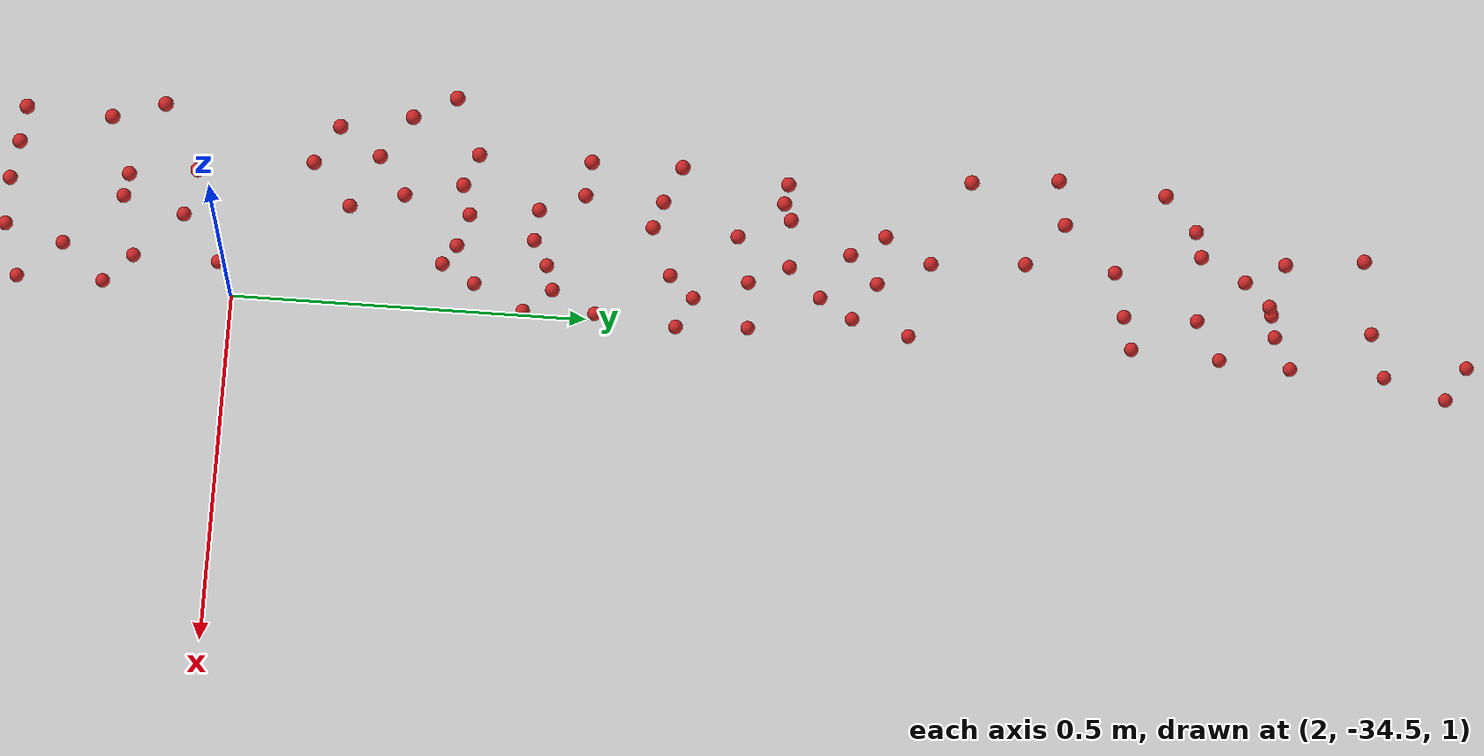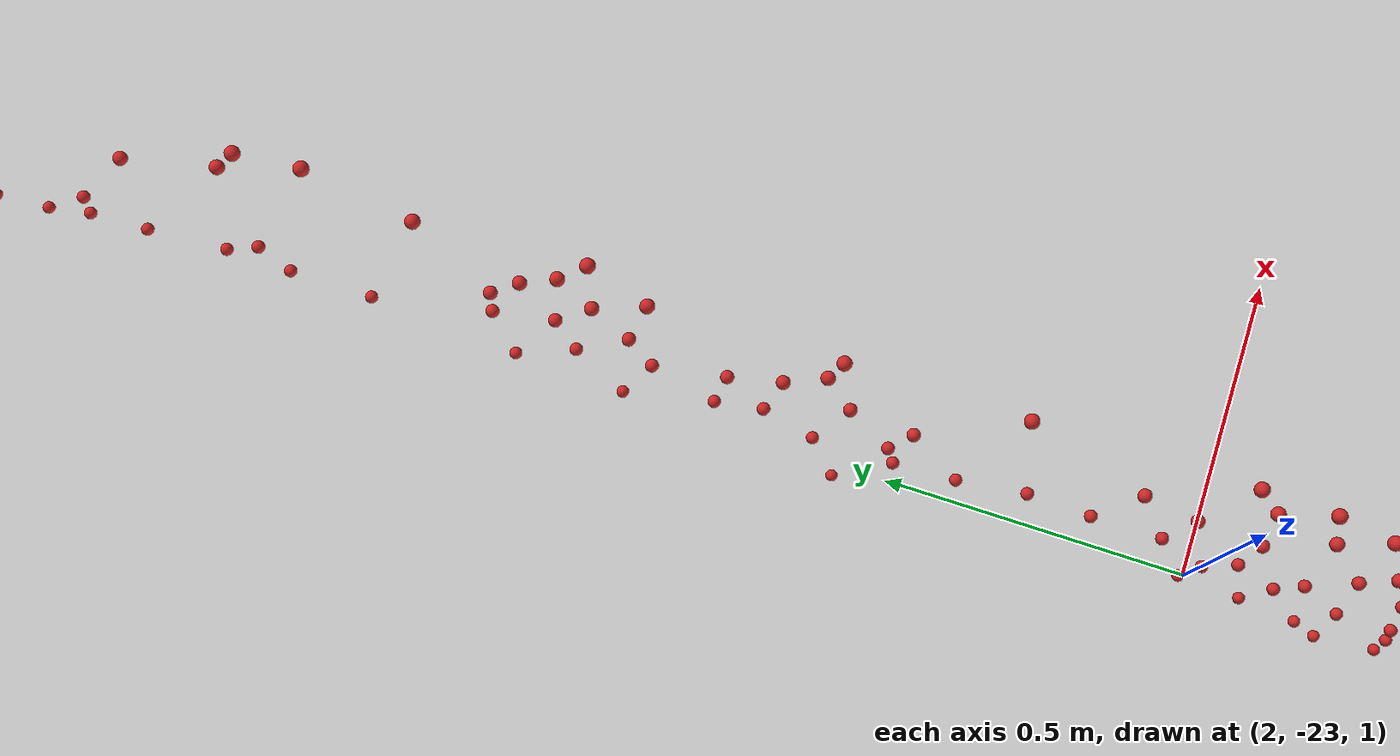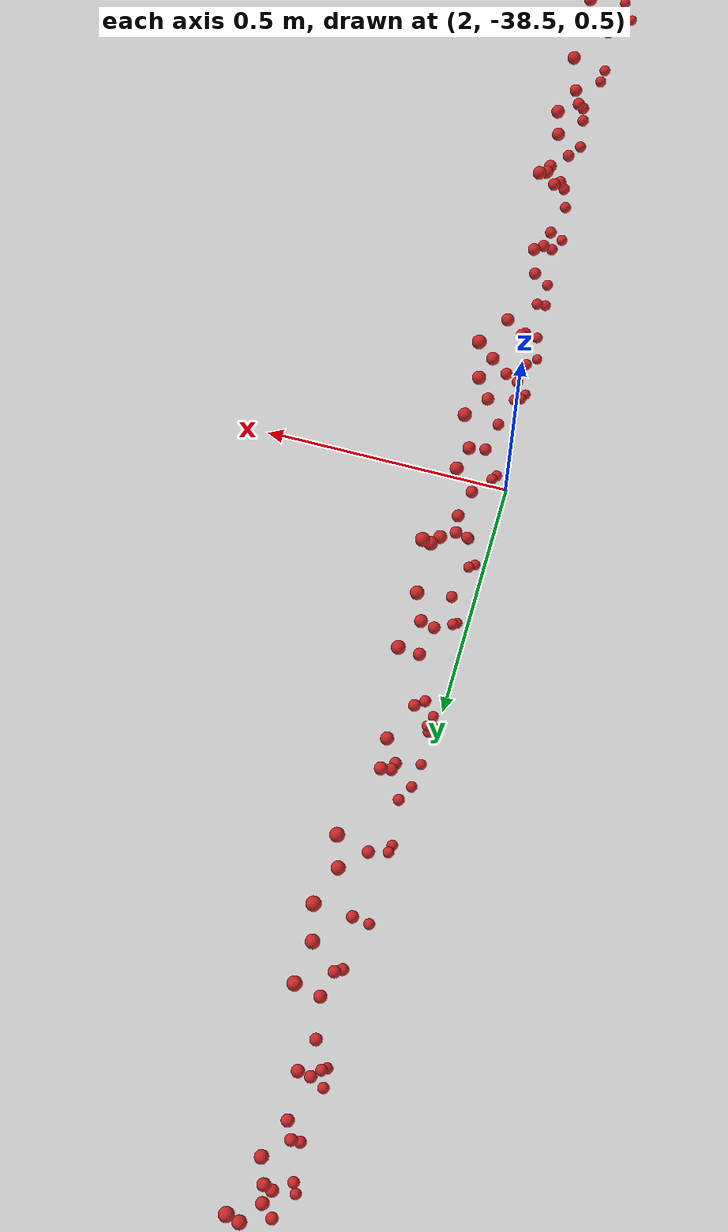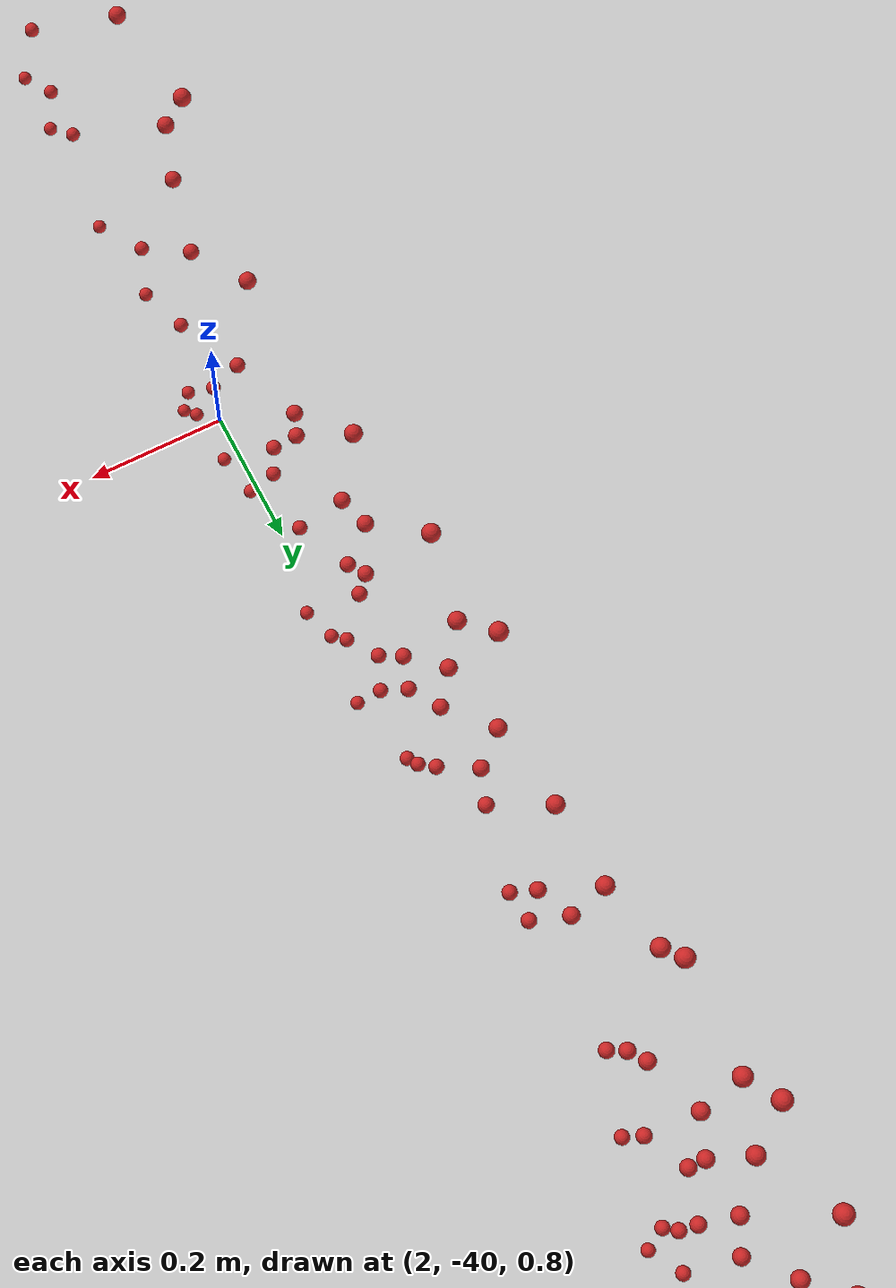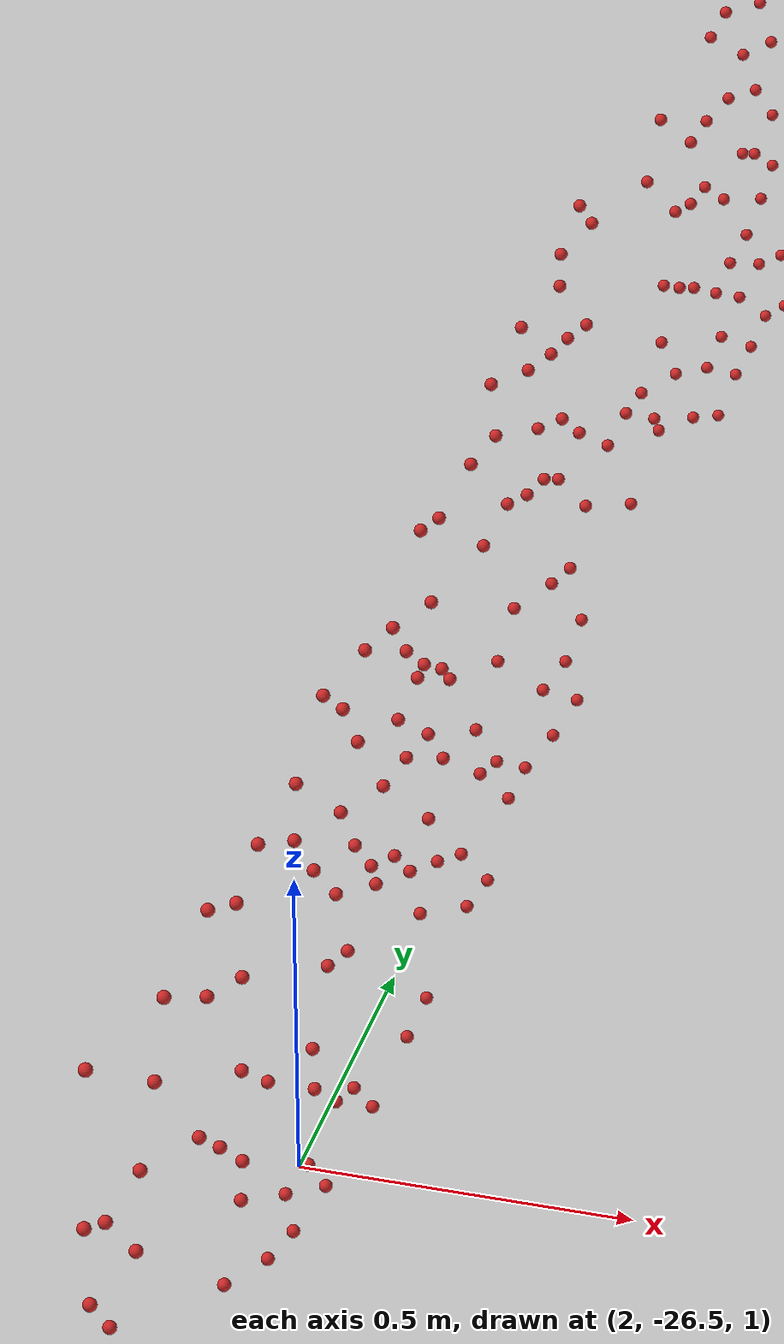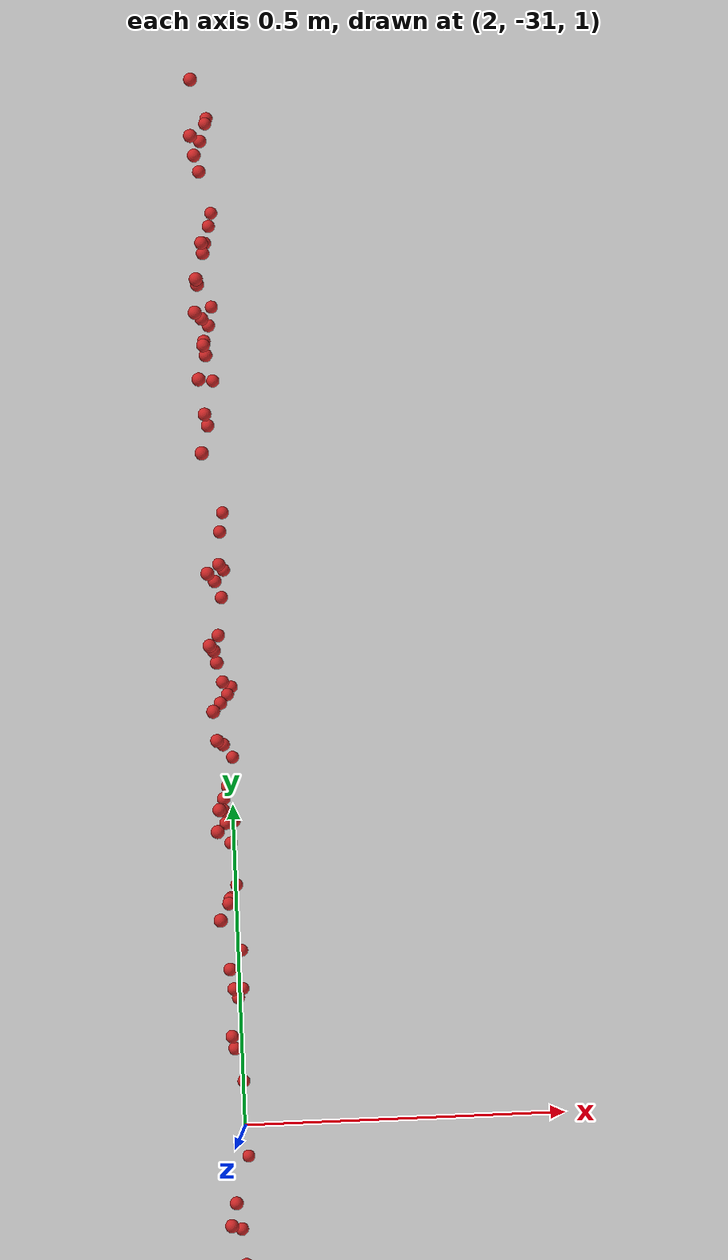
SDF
<sdf version="1.4">
 <world name="default">
  <light name="sun" type="directional">
   <pose>0 0 10 0 -0 0</pose>
   <diffuse>0.8 0.8 0.8 1</diffuse>
   <specular>0.2 0.2 0.2 1</specular>
   <attenuation>
    <range>1000</range>
    <constant>0.9</constant>
    <linear>0.01</linear>
    <quadratic>0.001</quadratic>
   </attenuation>
   <direction>-0.5 0.1 -0.9</direction>
  </light>
  <model name="ground_plane">
   <static>1</static>
   <link name="link">
    <collision name="collision">
     <geometry><plane><normal>0 0 1</normal><size>100 100</size></plane></geometry>
     <surface><friction><ode><mu>100</mu><mu2>50</mu2></ode></friction></surface>
    </collision>
    <visual name="visual">
     <cast_shadows>0</cast_shadows>
     <geometry><plane><normal>0 0 1</normal><size>100 100</size></plane></geometry>
     <material>
      <script><uri>file://media/materials/scripts/gazebo.material</uri><name>Gazebo/Grey</name></script>
     </material>
    </visual>
    <velocity_decay><linear>0</linear><angular>0</angular></velocity_decay>
   </link>
  </model>
  <physics type="ode">
   <max_step_size>0.001</max_step_size>
   <real_time_factor>1</real_time_factor>
   <real_time_update_rate>1000</real_time_update_rate>
   <gravity>0 0 -9.8</gravity>
  </physics>
  <scene><ambient>0.4 0.4 0.4 1</ambient><background>0.7 0.7 0.7 1</background><shadows>1</shadows></scene>
  <spherical_coordinates>
   <surface_model>EARTH_WGS84</surface_model>
   <latitude_deg>0</latitude_deg>
   <longitude_deg>0</longitude_deg>
   <elevation>0</elevation>
   <heading_deg>0</heading_deg>
  </spherical_coordinates>
  <model name="apple0">
   <link name="my_apple">
    <inertial>
     <pose>2 0 0 0 -0 0</pose>
     <mass>1</mass>
     <inertia><ixx>1</ixx><ixy>0</ixy><ixz>0</ixz><iyy>1</iyy><iyz>0</iyz><izz>1</izz></inertia>
    </inertial>
    <collision name="my_apple_collision">
     <pose>2 0 1 0 -0 0</pose>
     <geometry><sphere><radius>0.01</radius></sphere></geometry>
    </collision>
    <visual name="my_apple_visual">
     <pose>2 0 1 0 -0 0</pose>
     <geometry><sphere><radius>0.01</radius></sphere></geometry>
     <material><script><name>Gazebo/Red</name><uri>__default__</uri></script></material>
    </visual>
    <gravity>0</gravity>
    <velocity_decay><linear>0</linear><angular>0</angular></velocity_decay>
   </link>
   <pose>0 -41.2127 0.217796 0 -0 0</pose>
   <static>0</static>
  </model>
  <model name="apple1">
   <link name="my_apple">
    <inertial>
     <pose>2 0 0 0 -0 0</pose>
     <mass>1</mass>
     <inertia><ixx>1</ixx><ixy>0</ixy><ixz>0</ixz><iyy>1</iyy><iyz>0</iyz><izz>1</izz></inertia>
    </inertial>
    <collision name="my_apple_collision">
     <pose>2 0 1 0 -0 0</pose>
     <geometry><sphere><radius>0.01</radius></sphere></geometry>
    </collision>
    <visual name="my_apple_visual">
     <pose>2 0 1 0 -0 0</pose>
     <geometry><sphere><radius>0.01</radius></sphere></geometry>
     <material><script><name>Gazebo/Red</name><uri>__default__</uri></script></material>
    </visual>
    <gravity>0</gravity>
    <velocity_decay><linear>0</linear><angular>0</angular></velocity_decay>
   </link>
   <pose>0 -40.6722 0.622263 0 -0 0</pose>
   <static>0</static>
  </model>
  <model name="apple2">
   <link name="my_apple">
    <inertial>
     <pose>2 0 0 0 -0 0</pose>
     <mass>1</mass>
     <inertia><ixx>1</ixx><ixy>0</ixy><ixz>0</ixz><iyy>1</iyy><iyz>0</iyz><izz>1</izz></inertia>
    </inertial>
    <collision name="my_apple_collision">
     <pose>2 0 1 0 -0 0</pose>
     <geometry><sphere><radius>0.01</radius></sphere></geometry>
    </collision>
    <visual name="my_apple_visual">
     <pose>2 0 1 0 -0 0</pose>
     <geometry><sphere><radius>0.01</radius></sphere></geometry>
     <material><script><name>Gazebo/Red</name><uri>__default__</uri></script></material>
    </visual>
    <gravity>0</gravity>
    <velocity_decay><linear>0</linear><angular>0</angular></velocity_decay>
   </link>
   <pose>0 -41.2808 -0.043268 0 -0 0</pose>
   <static>0</static>
  </model>
  <model name="apple3">
   <link name="my_apple">
    <inertial>
     <pose>2 0 0 0 -0 0</pose>
     <mass>1</mass>
     <inertia><ixx>1</ixx><ixy>0</ixy><ixz>0</ixz><iyy>1</iyy><iyz>0</iyz><izz>1</izz></inertia>
    </inertial>
    <collision name="my_apple_collision">
     <pose>2 0 1 0 -0 0</pose>
     <geometry><sphere><radius>0.01</radius></sphere></geometry>
    </collision>
    <visual name="my_apple_visual">
     <pose>2 0 1 0 -0 0</pose>
     <geometry><sphere><radius>0.01</radius></sphere></geometry>
     <material><script><name>Gazebo/Red</name><uri>__default__</uri></script></material>
    </visual>
    <gravity>0</gravity>
    <velocity_decay><linear>0</linear><angular>0</angular></velocity_decay>
   </link>
   <pose>0 -40.6428 0.586412 0 -0 0</pose>
   <static>0</static>
  </model>
  <model name="apple4">
   <link name="my_apple">
    <inertial>
     <pose>2 0 0 0 -0 0</pose>
     <mass>1</mass>
     <inertia><ixx>1</ixx><ixy>0</ixy><ixz>0</ixz><iyy>1</iyy><iyz>0</iyz><izz>1</izz></inertia>
    </inertial>
    <collision name="my_apple_collision">
     <pose>2 0 1 0 -0 0</pose>
     <geometry><sphere><radius>0.01</radius></sphere></geometry>
    </collision>
    <visual name="my_apple_visual">
     <pose>2 0 1 0 -0 0</pose>
     <geometry><sphere><radius>0.01</radius></sphere></geometry>
     <material><script><name>Gazebo/Red</name><uri>__default__</uri></script></material>
    </visual>
    <gravity>0</gravity>
    <velocity_decay><linear>0</linear><angular>0</angular></velocity_decay>
   </link>
   <pose>0 -41.2937 -0.329152 0 -0 0</pose>
   <static>0</static>
  </model>
  <model name="apple5">
   <link name="my_apple">
    <inertial>
     <pose>2 0 0 0 -0 0</pose>
     <mass>1</mass>
     <inertia><ixx>1</ixx><ixy>0</ixy><ixz>0</ixz><iyy>1</iyy><iyz>0</iyz><izz>1</izz></inertia>
    </inertial>
    <collision name="my_apple_collision">
     <pose>2 0 1 0 -0 0</pose>
     <geometry><sphere><radius>0.01</radius></sphere></geometry>
    </collision>
    <visual name="my_apple_visual">
     <pose>2 0 1 0 -0 0</pose>
     <geometry><sphere><radius>0.01</radius></sphere></geometry>
     <material><script><name>Gazebo/Red</name><uri>__default__</uri></script></material>
    </visual>
    <gravity>0</gravity>
    <velocity_decay><linear>0</linear><angular>0</angular></velocity_decay>
   </link>
   <pose>0 -40.4908 -0.13703 0 -0 0</pose>
   <static>0</static>
  </model>
  <model name="apple6">
   <link name="my_apple">
    <inertial>
     <pose>2 0 0 0 -0 0</pose>
     <mass>1</mass>
     <inertia><ixx>1</ixx><ixy>0</ixy><ixz>0</ixz><iyy>1</iyy><iyz>0</iyz><izz>1</izz></inertia>
    </inertial>
    <collision name="my_apple_collision">
     <pose>2 0 1 0 -0 0</pose>
     <geometry><sphere><radius>0.01</radius></sphere></geometry>
    </collision>
    <visual name="my_apple_visual">
     <pose>2 0 1 0 -0 0</pose>
     <geometry><sphere><radius>0.01</radius></sphere></geometry>
     <material><script><name>Gazebo/Red</name><uri>__default__</uri></script></material>
    </visual>
    <gravity>0</gravity>
    <velocity_decay><linear>0</linear><angular>0</angular></velocity_decay>
   </link>
   <pose>0 -41.3545 0.363037 0 -0 0</pose>
   <static>0</static>
  </model>
  <model name="apple7">
   <link name="my_apple">
    <inertial>
     <pose>2 0 0 0 -0 0</pose>
     <mass>1</mass>
     <inertia><ixx>1</ixx><ixy>0</ixy><ixz>0</ixz><iyy>1</iyy><iyz>0</iyz><izz>1</izz></inertia>
    </inertial>
    <collision name="my_apple_collision">
     <pose>2 0 1 0 -0 0</pose>
     <geometry><sphere><radius>0.01</radius></sphere></geometry>
    </collision>
    <visual name="my_apple_visual">
     <pose>2 0 1 0 -0 0</pose>
     <geometry><sphere><radius>0.01</radius></sphere></geometry>
     <material><script><name>Gazebo/Red</name><uri>__default__</uri></script></material>
    </visual>
    <gravity>0</gravity>
    <velocity_decay><linear>0</linear><angular>0</angular></velocity_decay>
   </link>
   <pose>0 -41.6178 -0.16185 0 -0 0</pose>
   <static>0</static>
  </model>
  <model name="apple8">
   <link name="my_apple">
    <inertial>
     <pose>2 0 0 0 -0 0</pose>
     <mass>1</mass>
     <inertia><ixx>1</ixx><ixy>0</ixy><ixz>0</ixz><iyy>1</iyy><iyz>0</iyz><izz>1</izz></inertia>
    </inertial>
    <collision name="my_apple_collision">
     <pose>2 0 1 0 -0 0</pose>
     <geometry><sphere><radius>0.01</radius></sphere></geometry>
    </collision>
    <visual name="my_apple_visual">
     <pose>2 0 1 0 -0 0</pose>
     <geometry><sphere><radius>0.01</radius></sphere></geometry>
     <material><script><name>Gazebo/Red</name><uri>__default__</uri></script></material>
    </visual>
    <gravity>0</gravity>
    <velocity_decay><linear>0</linear><angular>0</angular></velocity_decay>
   </link>
   <pose>0 -41.2044 -0.253774 0 -0 0</pose>
   <static>0</static>
  </model>
  <model name="apple9">
   <link name="my_apple">
    <inertial>
     <pose>2 0 0 0 -0 0</pose>
     <mass>1</mass>
     <inertia><ixx>1</ixx><ixy>0</ixy><ixz>0</ixz><iyy>1</iyy><iyz>0</iyz><izz>1</izz></inertia>
    </inertial>
    <collision name="my_apple_collision">
     <pose>2 0 1 0 -0 0</pose>
     <geometry><sphere><radius>0.01</radius></sphere></geometry>
    </collision>
    <visual name="my_apple_visual">
     <pose>2 0 1 0 -0 0</pose>
     <geometry><sphere><radius>0.01</radius></sphere></geometry>
     <material><script><name>Gazebo/Red</name><uri>__default__</uri></script></material>
    </visual>
    <gravity>0</gravity>
    <velocity_decay><linear>0</linear><angular>0</angular></velocity_decay>
   </link>
   <pose>0 -41.2624 0.204008 0 -0 0</pose>
   <static>0</static>
  </model>
  <model name="apple10">
   <link name="my_apple">
    <inertial>
     <pose>2 0 0 0 -0 0</pose>
     <mass>1</mass>
     <inertia><ixx>1</ixx><ixy>0</ixy><ixz>0</ixz><iyy>1</iyy><iyz>0</iyz><izz>1</izz></inertia>
    </inertial>
    <collision name="my_apple_collision">
     <pose>2 0 1 0 -0 0</pose>
     <geometry><sphere><radius>0.01</radius></sphere></geometry>
    </collision>
    <visual name="my_apple_visual">
     <pose>2 0 1 0 -0 0</pose>
     <geometry><sphere><radius>0.01</radius></sphere></geometry>
     <material><script><name>Gazebo/Red</name><uri>__default__</uri></script></material>
    </visual>
    <gravity>0</gravity>
    <velocity_decay><linear>0</linear><angular>0</angular></velocity_decay>
   </link>
   <pose>0 -41.5985 -0.423833 0 -0 0</pose>
   <static>0</static>
  </model>
  <model name="apple11">
   <link name="my_apple">
    <inertial>
     <pose>2 0 0 0 -0 0</pose>
     <mass>1</mass>
     <inertia><ixx>1</ixx><ixy>0</ixy><ixz>0</ixz><iyy>1</iyy><iyz>0</iyz><izz>1</izz></inertia>
    </inertial>
    <collision name="my_apple_collision">
     <pose>2 0 1 0 -0 0</pose>
     <geometry><sphere><radius>0.01</radius></sphere></geometry>
    </collision>
    <visual name="my_apple_visual">
     <pose>2 0 1 0 -0 0</pose>
     <geometry><sphere><radius>0.01</radius></sphere></geometry>
     <material><script><name>Gazebo/Red</name><uri>__default__</uri></script></material>
    </visual>
    <gravity>0</gravity>
    <velocity_decay><linear>0</linear><angular>0</angular></velocity_decay>
   </link>
   <pose>0 -41.3075 0.101972 0 -0 0</pose>
   <static>0</static>
  </model>
  <model name="apple12">
   <link name="my_apple">
    <inertial>
     <pose>2 0 0 0 -0 0</pose>
     <mass>1</mass>
     <inertia><ixx>1</ixx><ixy>0</ixy><ixz>0</ixz><iyy>1</iyy><iyz>0</iyz><izz>1</izz></inertia>
    </inertial>
    <collision name="my_apple_collision">
     <pose>2 0 1 0 -0 0</pose>
     <geometry><sphere><radius>0.01</radius></sphere></geometry>
    </collision>
    <visual name="my_apple_visual">
     <pose>2 0 1 0 -0 0</pose>
     <geometry><sphere><radius>0.01</radius></sphere></geometry>
     <material><script><name>Gazebo/Red</name><uri>__default__</uri></script></material>
    </visual>
    <gravity>0</gravity>
    <velocity_decay><linear>0</linear><angular>0</angular></velocity_decay>
   </link>
   <pose>0 -41.5838 0.424626 0 -0 0</pose>
   <static>0</static>
  </model>
  <model name="apple13">
   <link name="my_apple">
    <inertial>
     <pose>2 0 0 0 -0 0</pose>
     <mass>1</mass>
     <inertia><ixx>1</ixx><ixy>0</ixy><ixz>0</ixz><iyy>1</iyy><iyz>0</iyz><izz>1</izz></inertia>
    </inertial>
    <collision name="my_apple_collision">
     <pose>2 0 1 0 -0 0</pose>
     <geometry><sphere><radius>0.01</radius></sphere></geometry>
    </collision>
    <visual name="my_apple_visual">
     <pose>2 0 1 0 -0 0</pose>
     <geometry><sphere><radius>0.01</radius></sphere></geometry>
     <material><script><name>Gazebo/Red</name><uri>__default__</uri></script></material>
    </visual>
    <gravity>0</gravity>
    <velocity_decay><linear>0</linear><angular>0</angular></velocity_decay>
   </link>
   <pose>0 -41.4815 0.040383 0 -0 0</pose>
   <static>0</static>
  </model>
  <model name="apple14">
   <link name="my_apple">
    <inertial>
     <pose>2 0 0 0 -0 0</pose>
     <mass>1</mass>
     <inertia><ixx>1</ixx><ixy>0</ixy><ixz>0</ixz><iyy>1</iyy><iyz>0</iyz><izz>1</izz></inertia>
    </inertial>
    <collision name="my_apple_collision">
     <pose>2 0 1 0 -0 0</pose>
     <geometry><sphere><radius>0.01</radius></sphere></geometry>
    </collision>
    <visual name="my_apple_visual">
     <pose>2 0 1 0 -0 0</pose>
     <geometry><sphere><radius>0.01</radius></sphere></geometry>
     <material><script><name>Gazebo/Red</name><uri>__default__</uri></script></material>
    </visual>
    <gravity>0</gravity>
    <velocity_decay><linear>0</linear><angular>0</angular></velocity_decay>
   </link>
   <pose>0 -41.5432 0.055091 0 -0 0</pose>
   <static>0</static>
  </model>
  <model name="apple15">
   <link name="my_apple">
    <inertial>
     <pose>2 0 0 0 -0 0</pose>
     <mass>1</mass>
     <inertia><ixx>1</ixx><ixy>0</ixy><ixz>0</ixz><iyy>1</iyy><iyz>0</iyz><izz>1</izz></inertia>
    </inertial>
    <collision name="my_apple_collision">
     <pose>2 0 1 0 -0 0</pose>
     <geometry><sphere><radius>0.01</radius></sphere></geometry>
    </collision>
    <visual name="my_apple_visual">
     <pose>2 0 1 0 -0 0</pose>
     <geometry><sphere><radius>0.01</radius></sphere></geometry>
     <material><script><name>Gazebo/Red</name><uri>__default__</uri></script></material>
    </visual>
    <gravity>0</gravity>
    <velocity_decay><linear>0</linear><angular>0</angular></velocity_decay>
   </link>
   <pose>0 -40.5663 -0.127838 0 -0 0</pose>
   <static>0</static>
  </model>
  <model name="apple16">
   <link name="my_apple">
    <inertial>
     <pose>2 0 0 0 -0 0</pose>
     <mass>1</mass>
     <inertia><ixx>1</ixx><ixy>0</ixy><ixz>0</ixz><iyy>1</iyy><iyz>0</iyz><izz>1</izz></inertia>
    </inertial>
    <collision name="my_apple_collision">
     <pose>2 0 1 0 -0 0</pose>
     <geometry><sphere><radius>0.01</radius></sphere></geometry>
    </collision>
    <visual name="my_apple_visual">
     <pose>2 0 1 0 -0 0</pose>
     <geometry><sphere><radius>0.01</radius></sphere></geometry>
     <material><script><name>Gazebo/Red</name><uri>__default__</uri></script></material>
    </visual>
    <gravity>0</gravity>
    <velocity_decay><linear>0</linear><angular>0</angular></velocity_decay>
   </link>
   <pose>0 -41.3112 0.267436 0 -0 0</pose>
   <static>0</static>
  </model>
  <model name="apple17">
   <link name="my_apple">
    <inertial>
     <pose>2 0 0 0 -0 0</pose>
     <mass>1</mass>
     <inertia><ixx>1</ixx><ixy>0</ixy><ixz>0</ixz><iyy>1</iyy><iyz>0</iyz><izz>1</izz></inertia>
    </inertial>
    <collision name="my_apple_collision">
     <pose>2 0 1 0 -0 0</pose>
     <geometry><sphere><radius>0.01</radius></sphere></geometry>
    </collision>
    <visual name="my_apple_visual">
     <pose>2 0 1 0 -0 0</pose>
     <geometry><sphere><radius>0.01</radius></sphere></geometry>
     <material><script><name>Gazebo/Red</name><uri>__default__</uri></script></material>
    </visual>
    <gravity>0</gravity>
    <velocity_decay><linear>0</linear><angular>0</angular></velocity_decay>
   </link>
   <pose>0 -41.3775 0.114842 0 -0 0</pose>
   <static>0</static>
  </model>
  <model name="apple18">
   <link name="my_apple">
    <inertial>
     <pose>2 0 0 0 -0 0</pose>
     <mass>1</mass>
     <inertia><ixx>1</ixx><ixy>0</ixy><ixz>0</ixz><iyy>1</iyy><iyz>0</iyz><izz>1</izz></inertia>
    </inertial>
    <collision name="my_apple_collision">
     <pose>2 0 1 0 -0 0</pose>
     <geometry><sphere><radius>0.01</radius></sphere></geometry>
    </collision>
    <visual name="my_apple_visual">
     <pose>2 0 1 0 -0 0</pose>
     <geometry><sphere><radius>0.01</radius></sphere></geometry>
     <material><script><name>Gazebo/Red</name><uri>__default__</uri></script></material>
    </visual>
    <gravity>0</gravity>
    <velocity_decay><linear>0</linear><angular>0</angular></velocity_decay>
   </link>
   <pose>0 -41.5635 -0.134273 0 -0 0</pose>
   <static>0</static>
  </model>
  <model name="apple19">
   <link name="my_apple">
    <inertial>
     <pose>2 0 0 0 -0 0</pose>
     <mass>1</mass>
     <inertia><ixx>1</ixx><ixy>0</ixy><ixz>0</ixz><iyy>1</iyy><iyz>0</iyz><izz>1</izz></inertia>
    </inertial>
    <collision name="my_apple_collision">
     <pose>2 0 1 0 -0 0</pose>
     <geometry><sphere><radius>0.01</radius></sphere></geometry>
    </collision>
    <visual name="my_apple_visual">
     <pose>2 0 1 0 -0 0</pose>
     <geometry><sphere><radius>0.01</radius></sphere></geometry>
     <material><script><name>Gazebo/Red</name><uri>__default__</uri></script></material>
    </visual>
    <gravity>0</gravity>
    <velocity_decay><linear>0</linear><angular>0</angular></velocity_decay>
   </link>
   <pose>0 -41.72 -0.189427 0 -0 0</pose>
   <static>0</static>
  </model>
  <model name="apple20">
   <link name="my_apple">
    <inertial>
     <pose>2 0 0 0 -0 0</pose>
     <mass>1</mass>
     <inertia><ixx>1</ixx><ixy>0</ixy><ixz>0</ixz><iyy>1</iyy><iyz>0</iyz><izz>1</izz></inertia>
    </inertial>
    <collision name="my_apple_collision">
     <pose>2 0 1 0 -0 0</pose>
     <geometry><sphere><radius>0.01</radius></sphere></geometry>
    </collision>
    <visual name="my_apple_visual">
     <pose>2 0 1 0 -0 0</pose>
     <geometry><sphere><radius>0.01</radius></sphere></geometry>
     <material><script><name>Gazebo/Red</name><uri>__default__</uri></script></material>
    </visual>
    <gravity>0</gravity>
    <velocity_decay><linear>0</linear><angular>0</angular></velocity_decay>
   </link>
   <pose>0 -40.7321 0.660871 0 -0 0</pose>
   <static>0</static>
  </model>
  <model name="apple21">
   <link name="my_apple">
    <inertial>
     <pose>2 0 0 0 -0 0</pose>
     <mass>1</mass>
     <inertia><ixx>1</ixx><ixy>0</ixy><ixz>0</ixz><iyy>1</iyy><iyz>0</iyz><izz>1</izz></inertia>
    </inertial>
    <collision name="my_apple_collision">
     <pose>2 0 1 0 -0 0</pose>
     <geometry><sphere><radius>0.01</radius></sphere></geometry>
    </collision>
    <visual name="my_apple_visual">
     <pose>2 0 1 0 -0 0</pose>
     <geometry><sphere><radius>0.01</radius></sphere></geometry>
     <material><script><name>Gazebo/Red</name><uri>__default__</uri></script></material>
    </visual>
    <gravity>0</gravity>
    <velocity_decay><linear>0</linear><angular>0</angular></velocity_decay>
   </link>
   <pose>0 -40.6759 0.487135 0 -0 0</pose>
   <static>0</static>
  </model>
  <model name="apple22">
   <link name="my_apple">
    <inertial>
     <pose>2 0 0 0 -0 0</pose>
     <mass>1</mass>
     <inertia><ixx>1</ixx><ixy>0</ixy><ixz>0</ixz><iyy>1</iyy><iyz>0</iyz><izz>1</izz></inertia>
    </inertial>
    <collision name="my_apple_collision">
     <pose>2 0 1 0 -0 0</pose>
     <geometry><sphere><radius>0.01</radius></sphere></geometry>
    </collision>
    <visual name="my_apple_visual">
     <pose>2 0 1 0 -0 0</pose>
     <geometry><sphere><radius>0.01</radius></sphere></geometry>
     <material><script><name>Gazebo/Red</name><uri>__default__</uri></script></material>
    </visual>
    <gravity>0</gravity>
    <velocity_decay><linear>0</linear><angular>0</angular></velocity_decay>
   </link>
   <pose>0 -41.5442 -0.433945 0 -0 0</pose>
   <static>0</static>
  </model>
  <model name="apple23">
   <link name="my_apple">
    <inertial>
     <pose>2 0 0 0 -0 0</pose>
     <mass>1</mass>
     <inertia><ixx>1</ixx><ixy>0</ixy><ixz>0</ixz><iyy>1</iyy><iyz>0</iyz><izz>1</izz></inertia>
    </inertial>
    <collision name="my_apple_collision">
     <pose>2 0 1 0 -0 0</pose>
     <geometry><sphere><radius>0.01</radius></sphere></geometry>
    </collision>
    <visual name="my_apple_visual">
     <pose>2 0 1 0 -0 0</pose>
     <geometry><sphere><radius>0.01</radius></sphere></geometry>
     <material><script><name>Gazebo/Red</name><uri>__default__</uri></script></material>
    </visual>
    <gravity>0</gravity>
    <velocity_decay><linear>0</linear><angular>0</angular></velocity_decay>
   </link>
   <pose>0 -40.6207 -0.288705 0 -0 0</pose>
   <static>0</static>
  </model>
  <model name="apple24">
   <link name="my_apple">
    <inertial>
     <pose>2 0 0 0 -0 0</pose>
     <mass>1</mass>
     <inertia><ixx>1</ixx><ixy>0</ixy><ixz>0</ixz><iyy>1</iyy><iyz>0</iyz><izz>1</izz></inertia>
    </inertial>
    <collision name="my_apple_collision">
     <pose>2 0 1 0 -0 0</pose>
     <geometry><sphere><radius>0.01</radius></sphere></geometry>
    </collision>
    <visual name="my_apple_visual">
     <pose>2 0 1 0 -0 0</pose>
     <geometry><sphere><radius>0.01</radius></sphere></geometry>
     <material><script><name>Gazebo/Red</name><uri>__default__</uri></script></material>
    </visual>
    <gravity>0</gravity>
    <velocity_decay><linear>0</linear><angular>0</angular></velocity_decay>
   </link>
   <pose>0 -41.2477 -0.145304 0 -0 0</pose>
   <static>0</static>
  </model>
  <model name="apple25">
   <link name="my_apple">
    <inertial>
     <pose>2 0 0 0 -0 0</pose>
     <mass>1</mass>
     <inertia><ixx>1</ixx><ixy>0</ixy><ixz>0</ixz><iyy>1</iyy><iyz>0</iyz><izz>1</izz></inertia>
    </inertial>
    <collision name="my_apple_collision">
     <pose>2 0 1 0 -0 0</pose>
     <geometry><sphere><radius>0.01</radius></sphere></geometry>
    </collision>
    <visual name="my_apple_visual">
     <pose>2 0 1 0 -0 0</pose>
     <geometry><sphere><radius>0.01</radius></sphere></geometry>
     <material><script><name>Gazebo/Red</name><uri>__default__</uri></script></material>
    </visual>
    <gravity>0</gravity>
    <velocity_decay><linear>0</linear><angular>0</angular></velocity_decay>
   </link>
   <pose>0 -40.7137 -0.273997 0 -0 0</pose>
   <static>0</static>
  </model>
  <model name="apple26">
   <link name="my_apple">
    <inertial>
     <pose>2 0 0 0 -0 0</pose>
     <mass>1</mass>
     <inertia><ixx>1</ixx><ixy>0</ixy><ixz>0</ixz><iyy>1</iyy><iyz>0</iyz><izz>1</izz></inertia>
    </inertial>
    <collision name="my_apple_collision">
     <pose>2 0 1 0 -0 0</pose>
     <geometry><sphere><radius>0.01</radius></sphere></geometry>
    </collision>
    <visual name="my_apple_visual">
     <pose>2 0 1 0 -0 0</pose>
     <geometry><sphere><radius>0.01</radius></sphere></geometry>
     <material><script><name>Gazebo/Red</name><uri>__default__</uri></script></material>
    </visual>
    <gravity>0</gravity>
    <velocity_decay><linear>0</linear><angular>0</angular></velocity_decay>
   </link>
   <pose>0 -41.6261 0.592847 0 -0 0</pose>
   <static>0</static>
  </model>
  <model name="apple27">
   <link name="my_apple">
    <inertial>
     <pose>2 0 0 0 -0 0</pose>
     <mass>1</mass>
     <inertia><ixx>1</ixx><ixy>0</ixy><ixz>0</ixz><iyy>1</iyy><iyz>0</iyz><izz>1</izz></inertia>
    </inertial>
    <collision name="my_apple_collision">
     <pose>2 0 1 0 -0 0</pose>
     <geometry><sphere><radius>0.01</radius></sphere></geometry>
    </collision>
    <visual name="my_apple_visual">
     <pose>2 0 1 0 -0 0</pose>
     <geometry><sphere><radius>0.01</radius></sphere></geometry>
     <material><script><name>Gazebo/Red</name><uri>__default__</uri></script></material>
    </visual>
    <gravity>0</gravity>
    <velocity_decay><linear>0</linear><angular>0</angular></velocity_decay>
   </link>
   <pose>0 -40.8242 0.439253 0 -0 0</pose>
   <static>0</static>
  </model>
  <model name="apple28">
   <link name="my_apple">
    <inertial>
     <pose>2 0 0 0 -0 0</pose>
     <mass>1</mass>
     <inertia><ixx>1</ixx><ixy>0</ixy><ixz>0</ixz><iyy>1</iyy><iyz>0</iyz><izz>1</izz></inertia>
    </inertial>
    <collision name="my_apple_collision">
     <pose>2 0 1 0 -0 0</pose>
     <geometry><sphere><radius>0.01</radius></sphere></geometry>
    </collision>
    <visual name="my_apple_visual">
     <pose>2 0 1 0 -0 0</pose>
     <geometry><sphere><radius>0.01</radius></sphere></geometry>
     <material><script><name>Gazebo/Red</name><uri>__default__</uri></script></material>
    </visual>
    <gravity>0</gravity>
    <velocity_decay><linear>0</linear><angular>0</angular></velocity_decay>
   </link>
   <pose>0 -40.1757 0.496824 0 -0 0</pose>
   <static>0</static>
  </model>
  <model name="apple29">
   <link name="my_apple">
    <inertial>
     <pose>2 0 0 0 -0 0</pose>
     <mass>1</mass>
     <inertia><ixx>1</ixx><ixy>0</ixy><ixz>0</ixz><iyy>1</iyy><iyz>0</iyz><izz>1</izz></inertia>
    </inertial>
    <collision name="my_apple_collision">
     <pose>2 0 1 0 -0 0</pose>
     <geometry><sphere><radius>0.01</radius></sphere></geometry>
    </collision>
    <visual name="my_apple_visual">
     <pose>2 0 1 0 -0 0</pose>
     <geometry><sphere><radius>0.01</radius></sphere></geometry>
     <material><script><name>Gazebo/Red</name><uri>__default__</uri></script></material>
    </visual>
    <gravity>0</gravity>
    <velocity_decay><linear>0</linear><angular>0</angular></velocity_decay>
   </link>
   <pose>0 -40.2375 0.53858 0 -0 0</pose>
   <static>0</static>
  </model>
  <model name="apple30">
   <link name="my_apple">
    <inertial>
     <pose>2 0 0 0 -0 0</pose>
     <mass>1</mass>
     <inertia><ixx>1</ixx><ixy>0</ixy><ixz>0</ixz><iyy>1</iyy><iyz>0</iyz><izz>1</izz></inertia>
    </inertial>
    <collision name="my_apple_collision">
     <pose>2 0 1 0 -0 0</pose>
     <geometry><sphere><radius>0.01</radius></sphere></geometry>
    </collision>
    <visual name="my_apple_visual">
     <pose>2 0 1 0 -0 0</pose>
     <geometry><sphere><radius>0.01</radius></sphere></geometry>
     <material><script><name>Gazebo/Red</name><uri>__default__</uri></script></material>
    </visual>
    <gravity>0</gravity>
    <velocity_decay><linear>0</linear><angular>0</angular></velocity_decay>
   </link>
   <pose>0 -40.5987 -0.022284 0 -0 0</pose>
   <static>0</static>
  </model>
  <model name="apple31">
   <link name="my_apple">
    <inertial>
     <pose>2 0 0 0 -0 0</pose>
     <mass>1</mass>
     <inertia><ixx>1</ixx><ixy>0</ixy><ixz>0</ixz><iyy>1</iyy><iyz>0</iyz><izz>1</izz></inertia>
    </inertial>
    <collision name="my_apple_collision">
     <pose>2 0 1 0 -0 0</pose>
     <geometry><sphere><radius>0.01</radius></sphere></geometry>
    </collision>
    <visual name="my_apple_visual">
     <pose>2 0 1 0 -0 0</pose>
     <geometry><sphere><radius>0.01</radius></sphere></geometry>
     <material><script><name>Gazebo/Red</name><uri>__default__</uri></script></material>
    </visual>
    <gravity>0</gravity>
    <velocity_decay><linear>0</linear><angular>0</angular></velocity_decay>
   </link>
   <pose>0 -40.2593 -0.241504 0 -0 0</pose>
   <static>0</static>
  </model>
  <model name="apple32">
   <link name="my_apple">
    <inertial>
     <pose>2 0 0 0 -0 0</pose>
     <mass>1</mass>
     <inertia><ixx>1</ixx><ixy>0</ixy><ixz>0</ixz><iyy>1</iyy><iyz>0</iyz><izz>1</izz></inertia>
    </inertial>
    <collision name="my_apple_collision">
     <pose>2 0 1 0 -0 0</pose>
     <geometry><sphere><radius>0.01</radius></sphere></geometry>
    </collision>
    <visual name="my_apple_visual">
     <pose>2 0 1 0 -0 0</pose>
     <geometry><sphere><radius>0.01</radius></sphere></geometry>
     <material><script><name>Gazebo/Red</name><uri>__default__</uri></script></material>
    </visual>
    <gravity>0</gravity>
    <velocity_decay><linear>0</linear><angular>0</angular></velocity_decay>
   </link>
   <pose>0 -40.2403 -0.088715 0 -0 0</pose>
   <static>0</static>
  </model>
  <model name="apple33">
   <link name="my_apple">
    <inertial>
     <pose>2 0 0 0 -0 0</pose>
     <mass>1</mass>
     <inertia><ixx>1</ixx><ixy>0</ixy><ixz>0</ixz><iyy>1</iyy><iyz>0</iyz><izz>1</izz></inertia>
    </inertial>
    <collision name="my_apple_collision">
     <pose>2 0 1 0 -0 0</pose>
     <geometry><sphere><radius>0.01</radius></sphere></geometry>
    </collision>
    <visual name="my_apple_visual">
     <pose>2 0 1 0 -0 0</pose>
     <geometry><sphere><radius>0.01</radius></sphere></geometry>
     <material><script><name>Gazebo/Red</name><uri>__default__</uri></script></material>
    </visual>
    <gravity>0</gravity>
    <velocity_decay><linear>0</linear><angular>0</angular></velocity_decay>
   </link>
   <pose>0 -40.1624 -0.444593 0 -0 0</pose>
   <static>0</static>
  </model>
  <model name="apple34">
   <link name="my_apple">
    <inertial>
     <pose>2 0 0 0 -0 0</pose>
     <mass>1</mass>
     <inertia><ixx>1</ixx><ixy>0</ixy><ixz>0</ixz><iyy>1</iyy><iyz>0</iyz><izz>1</izz></inertia>
    </inertial>
    <collision name="my_apple_collision">
     <pose>2 0 1 0 -0 0</pose>
     <geometry><sphere><radius>0.01</radius></sphere></geometry>
    </collision>
    <visual name="my_apple_visual">
     <pose>2 0 1 0 -0 0</pose>
     <geometry><sphere><radius>0.01</radius></sphere></geometry>
     <material><script><name>Gazebo/Red</name><uri>__default__</uri></script></material>
    </visual>
    <gravity>0</gravity>
    <velocity_decay><linear>0</linear><angular>0</angular></velocity_decay>
   </link>
   <pose>0 -41.1988 0.402593 0 -0 0</pose>
   <static>0</static>
  </model>
  <model name="apple35">
   <link name="my_apple">
    <inertial>
     <pose>2 0 0 0 -0 0</pose>
     <mass>1</mass>
     <inertia><ixx>1</ixx><ixy>0</ixy><ixz>0</ixz><iyy>1</iyy><iyz>0</iyz><izz>1</izz></inertia>
    </inertial>
    <collision name="my_apple_collision">
     <pose>2 0 1 0 -0 0</pose>
     <geometry><sphere><radius>0.01</radius></sphere></geometry>
    </collision>
    <visual name="my_apple_visual">
     <pose>2 0 1 0 -0 0</pose>
     <geometry><sphere><radius>0.01</radius></sphere></geometry>
     <material><script><name>Gazebo/Red</name><uri>__default__</uri></script></material>
    </visual>
    <gravity>0</gravity>
    <velocity_decay><linear>0</linear><angular>0</angular></velocity_decay>
   </link>
   <pose>0 -40.114 -0.106179 0 -0 0</pose>
   <static>0</static>
  </model>
  <model name="apple36">
   <link name="my_apple">
    <inertial>
     <pose>2 0 0 0 -0 0</pose>
     <mass>1</mass>
     <inertia><ixx>1</ixx><ixy>0</ixy><ixz>0</ixz><iyy>1</iyy><iyz>0</iyz><izz>1</izz></inertia>
    </inertial>
    <collision name="my_apple_collision">
     <pose>2 0 1 0 -0 0</pose>
     <geometry><sphere><radius>0.01</radius></sphere></geometry>
    </collision>
    <visual name="my_apple_visual">
     <pose>2 0 1 0 -0 0</pose>
     <geometry><sphere><radius>0.01</radius></sphere></geometry>
     <material><script><name>Gazebo/Red</name><uri>__default__</uri></script></material>
    </visual>
    <gravity>0</gravity>
    <velocity_decay><linear>0</linear><angular>0</angular></velocity_decay>
   </link>
   <pose>0 -41.1445 -0.044987 0 -0 0</pose>
   <static>0</static>
  </model>
  <model name="apple37">
   <link name="my_apple">
    <inertial>
     <pose>2 0 0 0 -0 0</pose>
     <mass>1</mass>
     <inertia><ixx>1</ixx><ixy>0</ixy><ixz>0</ixz><iyy>1</iyy><iyz>0</iyz><izz>1</izz></inertia>
    </inertial>
    <collision name="my_apple_collision">
     <pose>2 0 1 0 -0 0</pose>
     <geometry><sphere><radius>0.01</radius></sphere></geometry>
    </collision>
    <visual name="my_apple_visual">
     <pose>2 0 1 0 -0 0</pose>
     <geometry><sphere><radius>0.01</radius></sphere></geometry>
     <material><script><name>Gazebo/Red</name><uri>__default__</uri></script></material>
    </visual>
    <gravity>0</gravity>
    <velocity_decay><linear>0</linear><angular>0</angular></velocity_decay>
   </link>
   <pose>0 -40.0281 0.207652 0 -0 0</pose>
   <static>0</static>
  </model>
  <model name="apple38">
   <link name="my_apple">
    <inertial>
     <pose>2 0 0 0 -0 0</pose>
     <mass>1</mass>
     <inertia><ixx>1</ixx><ixy>0</ixy><ixz>0</ixz><iyy>1</iyy><iyz>0</iyz><izz>1</izz></inertia>
    </inertial>
    <collision name="my_apple_collision">
     <pose>2 0 1 0 -0 0</pose>
     <geometry><sphere><radius>0.01</radius></sphere></geometry>
    </collision>
    <visual name="my_apple_visual">
     <pose>2 0 1 0 -0 0</pose>
     <geometry><sphere><radius>0.01</radius></sphere></geometry>
     <material><script><name>Gazebo/Red</name><uri>__default__</uri></script></material>
    </visual>
    <gravity>0</gravity>
    <velocity_decay><linear>0</linear><angular>0</angular></velocity_decay>
   </link>
   <pose>0 -40.6007 0.410083 0 -0 0</pose>
   <static>0</static>
  </model>
  <model name="apple39">
   <link name="my_apple">
    <inertial>
     <pose>2 0 0 0 -0 0</pose>
     <mass>1</mass>
     <inertia><ixx>1</ixx><ixy>0</ixy><ixz>0</ixz><iyy>1</iyy><iyz>0</iyz><izz>1</izz></inertia>
    </inertial>
    <collision name="my_apple_collision">
     <pose>2 0 1 0 -0 0</pose>
     <geometry><sphere><radius>0.01</radius></sphere></geometry>
    </collision>
    <visual name="my_apple_visual">
     <pose>2 0 1 0 -0 0</pose>
     <geometry><sphere><radius>0.01</radius></sphere></geometry>
     <material><script><name>Gazebo/Red</name><uri>__default__</uri></script></material>
    </visual>
    <gravity>0</gravity>
    <velocity_decay><linear>0</linear><angular>0</angular></velocity_decay>
   </link>
   <pose>0 -39.9058 0.115409 0 -0 0</pose>
   <static>0</static>
  </model>
  <model name="apple40">
   <link name="my_apple">
    <inertial>
     <pose>2 0 0 0 -0 0</pose>
     <mass>1</mass>
     <inertia><ixx>1</ixx><ixy>0</ixy><ixz>0</ixz><iyy>1</iyy><iyz>0</iyz><izz>1</izz></inertia>
    </inertial>
    <collision name="my_apple_collision">
     <pose>2 0 1 0 -0 0</pose>
     <geometry><sphere><radius>0.01</radius></sphere></geometry>
    </collision>
    <visual name="my_apple_visual">
     <pose>2 0 1 0 -0 0</pose>
     <geometry><sphere><radius>0.01</radius></sphere></geometry>
     <material><script><name>Gazebo/Red</name><uri>__default__</uri></script></material>
    </visual>
    <gravity>0</gravity>
    <velocity_decay><linear>0</linear><angular>0</angular></velocity_decay>
   </link>
   <pose>0 -40.8329 0.62663 0 -0 0</pose>
   <static>0</static>
  </model>
  <model name="apple41">
   <link name="my_apple">
    <inertial>
     <pose>2 0 0 0 -0 0</pose>
     <mass>1</mass>
     <inertia><ixx>1</ixx><ixy>0</ixy><ixz>0</ixz><iyy>1</iyy><iyz>0</iyz><izz>1</izz></inertia>
    </inertial>
    <collision name="my_apple_collision">
     <pose>2 0 1 0 -0 0</pose>
     <geometry><sphere><radius>0.01</radius></sphere></geometry>
    </collision>
    <visual name="my_apple_visual">
     <pose>2 0 1 0 -0 0</pose>
     <geometry><sphere><radius>0.01</radius></sphere></geometry>
     <material><script><name>Gazebo/Red</name><uri>__default__</uri></script></material>
    </visual>
    <gravity>0</gravity>
    <velocity_decay><linear>0</linear><angular>0</angular></velocity_decay>
   </link>
   <pose>0 -40.6424 0.300536 0 -0 0</pose>
   <static>0</static>
  </model>
  <model name="apple42">
   <link name="my_apple">
    <inertial>
     <pose>2 0 0 0 -0 0</pose>
     <mass>1</mass>
     <inertia><ixx>1</ixx><ixy>0</ixy><ixz>0</ixz><iyy>1</iyy><iyz>0</iyz><izz>1</izz></inertia>
    </inertial>
    <collision name="my_apple_collision">
     <pose>2 0 1 0 -0 0</pose>
     <geometry><sphere><radius>0.01</radius></sphere></geometry>
    </collision>
    <visual name="my_apple_visual">
     <pose>2 0 1 0 -0 0</pose>
     <geometry><sphere><radius>0.01</radius></sphere></geometry>
     <material><script><name>Gazebo/Red</name><uri>__default__</uri></script></material>
    </visual>
    <gravity>0</gravity>
    <velocity_decay><linear>0</linear><angular>0</angular></velocity_decay>
   </link>
   <pose>0 -39.8053 0.061494 0 -0 0</pose>
   <static>0</static>
  </model>
  <model name="apple43">
   <link name="my_apple">
    <inertial>
     <pose>2 0 0 0 -0 0</pose>
     <mass>1</mass>
     <inertia><ixx>1</ixx><ixy>0</ixy><ixz>0</ixz><iyy>1</iyy><iyz>0</iyz><izz>1</izz></inertia>
    </inertial>
    <collision name="my_apple_collision">
     <pose>2 0 1 0 -0 0</pose>
     <geometry><sphere><radius>0.01</radius></sphere></geometry>
    </collision>
    <visual name="my_apple_visual">
     <pose>2 0 1 0 -0 0</pose>
     <geometry><sphere><radius>0.01</radius></sphere></geometry>
     <material><script><name>Gazebo/Red</name><uri>__default__</uri></script></material>
    </visual>
    <gravity>0</gravity>
    <velocity_decay><linear>0</linear><angular>0</angular></velocity_decay>
   </link>
   <pose>0 -39.9058 -0.25491 0 -0 0</pose>
   <static>0</static>
  </model>
  <model name="apple44">
   <link name="my_apple">
    <inertial>
     <pose>2 0 0 0 -0 0</pose>
     <mass>1</mass>
     <inertia><ixx>1</ixx><ixy>0</ixy><ixz>0</ixz><iyy>1</iyy><iyz>0</iyz><izz>1</izz></inertia>
    </inertial>
    <collision name="my_apple_collision">
     <pose>2 0 1 0 -0 0</pose>
     <geometry><sphere><radius>0.01</radius></sphere></geometry>
    </collision>
    <visual name="my_apple_visual">
     <pose>2 0 1 0 -0 0</pose>
     <geometry><sphere><radius>0.01</radius></sphere></geometry>
     <material><script><name>Gazebo/Red</name><uri>__default__</uri></script></material>
    </visual>
    <gravity>0</gravity>
    <velocity_decay><linear>0</linear><angular>0</angular></velocity_decay>
   </link>
   <pose>0 -39.8136 -0.029729 0 -0 0</pose>
   <static>0</static>
  </model>
  <model name="apple45">
   <link name="my_apple">
    <inertial>
     <pose>2 0 0 0 -0 0</pose>
     <mass>1</mass>
     <inertia><ixx>1</ixx><ixy>0</ixy><ixz>0</ixz><iyy>1</iyy><iyz>0</iyz><izz>1</izz></inertia>
    </inertial>
    <collision name="my_apple_collision">
     <pose>2 0 1 0 -0 0</pose>
     <geometry><sphere><radius>0.01</radius></sphere></geometry>
    </collision>
    <visual name="my_apple_visual">
     <pose>2 0 1 0 -0 0</pose>
     <geometry><sphere><radius>0.01</radius></sphere></geometry>
     <material><script><name>Gazebo/Red</name><uri>__default__</uri></script></material>
    </visual>
    <gravity>0</gravity>
    <velocity_decay><linear>0</linear><angular>0</angular></velocity_decay>
   </link>
   <pose>0 -39.7362 -0.050275 0 -0 0</pose>
   <static>0</static>
  </model>
  <model name="apple46">
   <link name="my_apple">
    <inertial>
     <pose>2 0 0 0 -0 0</pose>
     <mass>1</mass>
     <inertia><ixx>1</ixx><ixy>0</ixy><ixz>0</ixz><iyy>1</iyy><iyz>0</iyz><izz>1</izz></inertia>
    </inertial>
    <collision name="my_apple_collision">
     <pose>2 0 1 0 -0 0</pose>
     <geometry><sphere><radius>0.01</radius></sphere></geometry>
    </collision>
    <visual name="my_apple_visual">
     <pose>2 0 1 0 -0 0</pose>
     <geometry><sphere><radius>0.01</radius></sphere></geometry>
     <material><script><name>Gazebo/Red</name><uri>__default__</uri></script></material>
    </visual>
    <gravity>0</gravity>
    <velocity_decay><linear>0</linear><angular>0</angular></velocity_decay>
   </link>
   <pose>0 -40.4466 -0.321478 0 -0 0</pose>
   <static>0</static>
  </model>
  <model name="apple47">
   <link name="my_apple">
    <inertial>
     <pose>2 0 0 0 -0 0</pose>
     <mass>1</mass>
     <inertia><ixx>1</ixx><ixy>0</ixy><ixz>0</ixz><iyy>1</iyy><iyz>0</iyz><izz>1</izz></inertia>
    </inertial>
    <collision name="my_apple_collision">
     <pose>2 0 1 0 -0 0</pose>
     <geometry><sphere><radius>0.01</radius></sphere></geometry>
    </collision>
    <visual name="my_apple_visual">
     <pose>2 0 1 0 -0 0</pose>
     <geometry><sphere><radius>0.01</radius></sphere></geometry>
     <material><script><name>Gazebo/Red</name><uri>__default__</uri></script></material>
    </visual>
    <gravity>0</gravity>
    <velocity_decay><linear>0</linear><angular>0</angular></velocity_decay>
   </link>
   <pose>0 -39.8448 0.409948 0 -0 0</pose>
   <static>0</static>
  </model>
  <model name="apple48">
   <link name="my_apple">
    <inertial>
     <pose>2 0 0 0 -0 0</pose>
     <mass>1</mass>
     <inertia><ixx>1</ixx><ixy>0</ixy><ixz>0</ixz><iyy>1</iyy><iyz>0</iyz><izz>1</izz></inertia>
    </inertial>
    <collision name="my_apple_collision">
     <pose>2 0 1 0 -0 0</pose>
     <geometry><sphere><radius>0.01</radius></sphere></geometry>
    </collision>
    <visual name="my_apple_visual">
     <pose>2 0 1 0 -0 0</pose>
     <geometry><sphere><radius>0.01</radius></sphere></geometry>
     <material><script><name>Gazebo/Red</name><uri>__default__</uri></script></material>
    </visual>
    <gravity>0</gravity>
    <velocity_decay><linear>0</linear><angular>0</angular></velocity_decay>
   </link>
   <pose>0 -39.5987 -0.142085 0 -0 0</pose>
   <static>0</static>
  </model>
  <model name="apple49">
   <link name="my_apple">
    <inertial>
     <pose>2 0 0 0 -0 0</pose>
     <mass>1</mass>
     <inertia><ixx>1</ixx><ixy>0</ixy><ixz>0</ixz><iyy>1</iyy><iyz>0</iyz><izz>1</izz></inertia>
    </inertial>
    <collision name="my_apple_collision">
     <pose>2 0 1 0 -0 0</pose>
     <geometry><sphere><radius>0.01</radius></sphere></geometry>
    </collision>
    <visual name="my_apple_visual">
     <pose>2 0 1 0 -0 0</pose>
     <geometry><sphere><radius>0.01</radius></sphere></geometry>
     <material><script><name>Gazebo/Red</name><uri>__default__</uri></script></material>
    </visual>
    <gravity>0</gravity>
    <velocity_decay><linear>0</linear><angular>0</angular></velocity_decay>
   </link>
   <pose>0 -39.5629 0.092656 0 -0 0</pose>
   <static>0</static>
  </model>
  <model name="apple50">
   <link name="my_apple">
    <inertial>
     <pose>2 0 0 0 -0 0</pose>
     <mass>1</mass>
     <inertia><ixx>1</ixx><ixy>0</ixy><ixz>0</ixz><iyy>1</iyy><iyz>0</iyz><izz>1</izz></inertia>
    </inertial>
    <collision name="my_apple_collision">
     <pose>2 0 1 0 -0 0</pose>
     <geometry><sphere><radius>0.01</radius></sphere></geometry>
    </collision>
    <visual name="my_apple_visual">
     <pose>2 0 1 0 -0 0</pose>
     <geometry><sphere><radius>0.01</radius></sphere></geometry>
     <material><script><name>Gazebo/Red</name><uri>__default__</uri></script></material>
    </visual>
    <gravity>0</gravity>
    <velocity_decay><linear>0</linear><angular>0</angular></velocity_decay>
   </link>
   <pose>0 -39.5945 0.118369 0 -0 0</pose>
   <static>0</static>
  </model>
  <model name="apple51">
   <link name="my_apple">
    <inertial>
     <pose>2 0 0 0 -0 0</pose>
     <mass>1</mass>
     <inertia><ixx>1</ixx><ixy>0</ixy><ixz>0</ixz><iyy>1</iyy><iyz>0</iyz><izz>1</izz></inertia>
    </inertial>
    <collision name="my_apple_collision">
     <pose>2 0 1 0 -0 0</pose>
     <geometry><sphere><radius>0.01</radius></sphere></geometry>
    </collision>
    <visual name="my_apple_visual">
     <pose>2 0 1 0 -0 0</pose>
     <geometry><sphere><radius>0.01</radius></sphere></geometry>
     <material><script><name>Gazebo/Red</name><uri>__default__</uri></script></material>
    </visual>
    <gravity>0</gravity>
    <velocity_decay><linear>0</linear><angular>0</angular></velocity_decay>
   </link>
   <pose>0 -40.4993 0.219565 0 -0 0</pose>
   <static>0</static>
  </model>
  <model name="apple52">
   <link name="my_apple">
    <inertial>
     <pose>2 0 0 0 -0 0</pose>
     <mass>1</mass>
     <inertia><ixx>1</ixx><ixy>0</ixy><ixz>0</ixz><iyy>1</iyy><iyz>0</iyz><izz>1</izz></inertia>
    </inertial>
    <collision name="my_apple_collision">
     <pose>2 0 1 0 -0 0</pose>
     <geometry><sphere><radius>0.01</radius></sphere></geometry>
    </collision>
    <visual name="my_apple_visual">
     <pose>2 0 1 0 -0 0</pose>
     <geometry><sphere><radius>0.01</radius></sphere></geometry>
     <material><script><name>Gazebo/Red</name><uri>__default__</uri></script></material>
    </visual>
    <gravity>0</gravity>
    <velocity_decay><linear>0</linear><angular>0</angular></velocity_decay>
   </link>
   <pose>0 -39.5472 0.188045 0 -0 0</pose>
   <static>0</static>
  </model>
  <model name="apple53">
   <link name="my_apple">
    <inertial>
     <pose>2 0 0 0 -0 0</pose>
     <mass>1</mass>
     <inertia><ixx>1</ixx><ixy>0</ixy><ixz>0</ixz><iyy>1</iyy><iyz>0</iyz><izz>1</izz></inertia>
    </inertial>
    <collision name="my_apple_collision">
     <pose>2 0 1 0 -0 0</pose>
     <geometry><sphere><radius>0.01</radius></sphere></geometry>
    </collision>
    <visual name="my_apple_visual">
     <pose>2 0 1 0 -0 0</pose>
     <geometry><sphere><radius>0.01</radius></sphere></geometry>
     <material><script><name>Gazebo/Red</name><uri>__default__</uri></script></material>
    </visual>
    <gravity>0</gravity>
    <velocity_decay><linear>0</linear><angular>0</angular></velocity_decay>
   </link>
   <pose>0 -39.6469 -0.238304 0 -0 0</pose>
   <static>0</static>
  </model>
  <model name="apple54">
   <link name="my_apple">
    <inertial>
     <pose>2 0 0 0 -0 0</pose>
     <mass>1</mass>
     <inertia><ixx>1</ixx><ixy>0</ixy><ixz>0</ixz><iyy>1</iyy><iyz>0</iyz><izz>1</izz></inertia>
    </inertial>
    <collision name="my_apple_collision">
     <pose>2 0 1 0 -0 0</pose>
     <geometry><sphere><radius>0.01</radius></sphere></geometry>
    </collision>
    <visual name="my_apple_visual">
     <pose>2 0 1 0 -0 0</pose>
     <geometry><sphere><radius>0.01</radius></sphere></geometry>
     <material><script><name>Gazebo/Red</name><uri>__default__</uri></script></material>
    </visual>
    <gravity>0</gravity>
    <velocity_decay><linear>0</linear><angular>0</angular></velocity_decay>
   </link>
   <pose>0 -39.6086 0.275968 0 -0 0</pose>
   <static>0</static>
  </model>
  <model name="apple55">
   <link name="my_apple">
    <inertial>
     <pose>2 0 0 0 -0 0</pose>
     <mass>1</mass>
     <inertia><ixx>1</ixx><ixy>0</ixy><ixz>0</ixz><iyy>1</iyy><iyz>0</iyz><izz>1</izz></inertia>
    </inertial>
    <collision name="my_apple_collision">
     <pose>2 0 1 0 -0 0</pose>
     <geometry><sphere><radius>0.01</radius></sphere></geometry>
    </collision>
    <visual name="my_apple_visual">
     <pose>2 0 1 0 -0 0</pose>
     <geometry><sphere><radius>0.01</radius></sphere></geometry>
     <material><script><name>Gazebo/Red</name><uri>__default__</uri></script></material>
    </visual>
    <gravity>0</gravity>
    <velocity_decay><linear>0</linear><angular>0</angular></velocity_decay>
   </link>
   <pose>0 -39.9892 0.57292 0 -0 0</pose>
   <static>0</static>
  </model>
  <model name="apple56">
   <link name="my_apple">
    <inertial>
     <pose>2 0 0 0 -0 0</pose>
     <mass>1</mass>
     <inertia><ixx>1</ixx><ixy>0</ixy><ixz>0</ixz><iyy>1</iyy><iyz>0</iyz><izz>1</izz></inertia>
    </inertial>
    <collision name="my_apple_collision">
     <pose>2 0 1 0 -0 0</pose>
     <geometry><sphere><radius>0.01</radius></sphere></geometry>
    </collision>
    <visual name="my_apple_visual">
     <pose>2 0 1 0 -0 0</pose>
     <geometry><sphere><radius>0.01</radius></sphere></geometry>
     <material><script><name>Gazebo/Red</name><uri>__default__</uri></script></material>
    </visual>
    <gravity>0</gravity>
    <velocity_decay><linear>0</linear><angular>0</angular></velocity_decay>
   </link>
   <pose>0 -39.5496 0.325737 0 -0 0</pose>
   <static>0</static>
  </model>
  <model name="apple57">
   <link name="my_apple">
    <inertial>
     <pose>2 0 0 0 -0 0</pose>
     <mass>1</mass>
     <inertia><ixx>1</ixx><ixy>0</ixy><ixz>0</ixz><iyy>1</iyy><iyz>0</iyz><izz>1</izz></inertia>
    </inertial>
    <collision name="my_apple_collision">
     <pose>2 0 1 0 -0 0</pose>
     <geometry><sphere><radius>0.01</radius></sphere></geometry>
    </collision>
    <visual name="my_apple_visual">
     <pose>2 0 1 0 -0 0</pose>
     <geometry><sphere><radius>0.01</radius></sphere></geometry>
     <material><script><name>Gazebo/Red</name><uri>__default__</uri></script></material>
    </visual>
    <gravity>0</gravity>
    <velocity_decay><linear>0</linear><angular>0</angular></velocity_decay>
   </link>
   <pose>0 -40.1024 -0.355003 0 -0 0</pose>
   <static>0</static>
  </model>
  <model name="apple58">
   <link name="my_apple">
    <inertial>
     <pose>2 0 0 0 -0 0</pose>
     <mass>1</mass>
     <inertia><ixx>1</ixx><ixy>0</ixy><ixz>0</ixz><iyy>1</iyy><iyz>0</iyz><izz>1</izz></inertia>
    </inertial>
    <collision name="my_apple_collision">
     <pose>2 0 1 0 -0 0</pose>
     <geometry><sphere><radius>0.01</radius></sphere></geometry>
    </collision>
    <visual name="my_apple_visual">
     <pose>2 0 1 0 -0 0</pose>
     <geometry><sphere><radius>0.01</radius></sphere></geometry>
     <material><script><name>Gazebo/Red</name><uri>__default__</uri></script></material>
    </visual>
    <gravity>0</gravity>
    <velocity_decay><linear>0</linear><angular>0</angular></velocity_decay>
   </link>
   <pose>0 -39.5794 0.495524 0 -0 0</pose>
   <static>0</static>
  </model>
  <model name="apple59">
   <link name="my_apple">
    <inertial>
     <pose>2 0 0 0 -0 0</pose>
     <mass>1</mass>
     <inertia><ixx>1</ixx><ixy>0</ixy><ixz>0</ixz><iyy>1</iyy><iyz>0</iyz><izz>1</izz></inertia>
    </inertial>
    <collision name="my_apple_collision">
     <pose>2 0 1 0 -0 0</pose>
     <geometry><sphere><radius>0.01</radius></sphere></geometry>
    </collision>
    <visual name="my_apple_visual">
     <pose>2 0 1 0 -0 0</pose>
     <geometry><sphere><radius>0.01</radius></sphere></geometry>
     <material><script><name>Gazebo/Red</name><uri>__default__</uri></script></material>
    </visual>
    <gravity>0</gravity>
    <velocity_decay><linear>0</linear><angular>0</angular></velocity_decay>
   </link>
   <pose>0 -40.1282 -0.328374 0 -0 0</pose>
   <static>0</static>
  </model>
  <model name="apple60">
   <link name="my_apple">
    <inertial>
     <pose>2 0 0 0 -0 0</pose>
     <mass>1</mass>
     <inertia><ixx>1</ixx><ixy>0</ixy><ixz>0</ixz><iyy>1</iyy><iyz>0</iyz><izz>1</izz></inertia>
    </inertial>
    <collision name="my_apple_collision">
     <pose>2 0 1 0 -0 0</pose>
     <geometry><sphere><radius>0.01</radius></sphere></geometry>
    </collision>
    <visual name="my_apple_visual">
     <pose>2 0 1 0 -0 0</pose>
     <geometry><sphere><radius>0.01</radius></sphere></geometry>
     <material><script><name>Gazebo/Red</name><uri>__default__</uri></script></material>
    </visual>
    <gravity>0</gravity>
    <velocity_decay><linear>0</linear><angular>0</angular></velocity_decay>
   </link>
   <pose>0 -40.1323 0.606883 0 -0 0</pose>
   <static>0</static>
  </model>
  <model name="apple61">
   <link name="my_apple">
    <inertial>
     <pose>2 0 0 0 -0 0</pose>
     <mass>1</mass>
     <inertia><ixx>1</ixx><ixy>0</ixy><ixz>0</ixz><iyy>1</iyy><iyz>0</iyz><izz>1</izz></inertia>
    </inertial>
    <collision name="my_apple_collision">
     <pose>2 0 1 0 -0 0</pose>
     <geometry><sphere><radius>0.01</radius></sphere></geometry>
    </collision>
    <visual name="my_apple_visual">
     <pose>2 0 1 0 -0 0</pose>
     <geometry><sphere><radius>0.01</radius></sphere></geometry>
     <material><script><name>Gazebo/Red</name><uri>__default__</uri></script></material>
    </visual>
    <gravity>0</gravity>
    <velocity_decay><linear>0</linear><angular>0</angular></velocity_decay>
   </link>
   <pose>0 -39.5091 0.004897 0 -0 0</pose>
   <static>0</static>
  </model>
  <model name="apple62">
   <link name="my_apple">
    <inertial>
     <pose>2 0 0 0 -0 0</pose>
     <mass>1</mass>
     <inertia><ixx>1</ixx><ixy>0</ixy><ixz>0</ixz><iyy>1</iyy><iyz>0</iyz><izz>1</izz></inertia>
    </inertial>
    <collision name="my_apple_collision">
     <pose>2 0 1 0 -0 0</pose>
     <geometry><sphere><radius>0.01</radius></sphere></geometry>
    </collision>
    <visual name="my_apple_visual">
     <pose>2 0 1 0 -0 0</pose>
     <geometry><sphere><radius>0.01</radius></sphere></geometry>
     <material><script><name>Gazebo/Red</name><uri>__default__</uri></script></material>
    </visual>
    <gravity>0</gravity>
    <velocity_decay><linear>0</linear><angular>0</angular></velocity_decay>
   </link>
   <pose>0 -39.4081 0.578641 0 -0 0</pose>
   <static>0</static>
  </model>
  <model name="apple63">
   <link name="my_apple">
    <inertial>
     <pose>2 0 0 0 -0 0</pose>
     <mass>1</mass>
     <inertia><ixx>1</ixx><ixy>0</ixy><ixz>0</ixz><iyy>1</iyy><iyz>0</iyz><izz>1</izz></inertia>
    </inertial>
    <collision name="my_apple_collision">
     <pose>2 0 1 0 -0 0</pose>
     <geometry><sphere><radius>0.01</radius></sphere></geometry>
    </collision>
    <visual name="my_apple_visual">
     <pose>2 0 1 0 -0 0</pose>
     <geometry><sphere><radius>0.01</radius></sphere></geometry>
     <material><script><name>Gazebo/Red</name><uri>__default__</uri></script></material>
    </visual>
    <gravity>0</gravity>
    <velocity_decay><linear>0</linear><angular>0</angular></velocity_decay>
   </link>
   <pose>0 -39.7306 0.226002 0 -0 0</pose>
   <static>0</static>
  </model>
  <model name="apple64">
   <link name="my_apple">
    <inertial>
     <pose>2 0 0 0 -0 0</pose>
     <mass>1</mass>
     <inertia><ixx>1</ixx><ixy>0</ixy><ixz>0</ixz><iyy>1</iyy><iyz>0</iyz><izz>1</izz></inertia>
    </inertial>
    <collision name="my_apple_collision">
     <pose>2 0 1 0 -0 0</pose>
     <geometry><sphere><radius>0.01</radius></sphere></geometry>
    </collision>
    <visual name="my_apple_visual">
     <pose>2 0 1 0 -0 0</pose>
     <geometry><sphere><radius>0.01</radius></sphere></geometry>
     <material><script><name>Gazebo/Red</name><uri>__default__</uri></script></material>
    </visual>
    <gravity>0</gravity>
    <velocity_decay><linear>0</linear><angular>0</angular></velocity_decay>
   </link>
   <pose>0 -39.7322 0.280875 0 -0 0</pose>
   <static>0</static>
  </model>
  <model name="apple65">
   <link name="my_apple">
    <inertial>
     <pose>2 0 0 0 -0 0</pose>
     <mass>1</mass>
     <inertia><ixx>1</ixx><ixy>0</ixy><ixz>0</ixz><iyy>1</iyy><iyz>0</iyz><izz>1</izz></inertia>
    </inertial>
    <collision name="my_apple_collision">
     <pose>2 0 1 0 -0 0</pose>
     <geometry><sphere><radius>0.01</radius></sphere></geometry>
    </collision>
    <visual name="my_apple_visual">
     <pose>2 0 1 0 -0 0</pose>
     <geometry><sphere><radius>0.01</radius></sphere></geometry>
     <material><script><name>Gazebo/Red</name><uri>__default__</uri></script></material>
    </visual>
    <gravity>0</gravity>
    <velocity_decay><linear>0</linear><angular>0</angular></velocity_decay>
   </link>
   <pose>0 -39.2715 0.618757 0 -0 0</pose>
   <static>0</static>
  </model>
  <model name="apple66">
   <link name="my_apple">
    <inertial>
     <pose>2 0 0 0 -0 0</pose>
     <mass>1</mass>
     <inertia><ixx>1</ixx><ixy>0</ixy><ixz>0</ixz><iyy>1</iyy><iyz>0</iyz><izz>1</izz></inertia>
    </inertial>
    <collision name="my_apple_collision">
     <pose>2 0 1 0 -0 0</pose>
     <geometry><sphere><radius>0.01</radius></sphere></geometry>
    </collision>
    <visual name="my_apple_visual">
     <pose>2 0 1 0 -0 0</pose>
     <geometry><sphere><radius>0.01</radius></sphere></geometry>
     <material><script><name>Gazebo/Red</name><uri>__default__</uri></script></material>
    </visual>
    <gravity>0</gravity>
    <velocity_decay><linear>0</linear><angular>0</angular></velocity_decay>
   </link>
   <pose>0 -39.7279 -0.329352 0 -0 0</pose>
   <static>0</static>
  </model>
  <model name="apple67">
   <link name="my_apple">
    <inertial>
     <pose>2 0 0 0 -0 0</pose>
     <mass>1</mass>
     <inertia><ixx>1</ixx><ixy>0</ixy><ixz>0</ixz><iyy>1</iyy><iyz>0</iyz><izz>1</izz></inertia>
    </inertial>
    <collision name="my_apple_collision">
     <pose>2 0 1 0 -0 0</pose>
     <geometry><sphere><radius>0.01</radius></sphere></geometry>
    </collision>
    <visual name="my_apple_visual">
     <pose>2 0 1 0 -0 0</pose>
     <geometry><sphere><radius>0.01</radius></sphere></geometry>
     <material><script><name>Gazebo/Red</name><uri>__default__</uri></script></material>
    </visual>
    <gravity>0</gravity>
    <velocity_decay><linear>0</linear><angular>0</angular></velocity_decay>
   </link>
   <pose>0 -39.5665 -0.314627 0 -0 0</pose>
   <static>0</static>
  </model>
  <model name="apple68">
   <link name="my_apple">
    <inertial>
     <pose>2 0 0 0 -0 0</pose>
     <mass>1</mass>
     <inertia><ixx>1</ixx><ixy>0</ixy><ixz>0</ixz><iyy>1</iyy><iyz>0</iyz><izz>1</izz></inertia>
    </inertial>
    <collision name="my_apple_collision">
     <pose>2 0 1 0 -0 0</pose>
     <geometry><sphere><radius>0.01</radius></sphere></geometry>
    </collision>
    <visual name="my_apple_visual">
     <pose>2 0 1 0 -0 0</pose>
     <geometry><sphere><radius>0.01</radius></sphere></geometry>
     <material><script><name>Gazebo/Red</name><uri>__default__</uri></script></material>
    </visual>
    <gravity>0</gravity>
    <velocity_decay><linear>0</linear><angular>0</angular></velocity_decay>
   </link>
   <pose>0 -40.0573 0.436333 0 -0 0</pose>
   <static>0</static>
  </model>
  <model name="apple69">
   <link name="my_apple">
    <inertial>
     <pose>2 0 0 0 -0 0</pose>
     <mass>1</mass>
     <inertia><ixx>1</ixx><ixy>0</ixy><ixz>0</ixz><iyy>1</iyy><iyz>0</iyz><izz>1</izz></inertia>
    </inertial>
    <collision name="my_apple_collision">
     <pose>2 0 1 0 -0 0</pose>
     <geometry><sphere><radius>0.01</radius></sphere></geometry>
    </collision>
    <visual name="my_apple_visual">
     <pose>2 0 1 0 -0 0</pose>
     <geometry><sphere><radius>0.01</radius></sphere></geometry>
     <material><script><name>Gazebo/Red</name><uri>__default__</uri></script></material>
    </visual>
    <gravity>0</gravity>
    <velocity_decay><linear>0</linear><angular>0</angular></velocity_decay>
   </link>
   <pose>0 -39.1603 0.012573 0 -0 0</pose>
   <static>0</static>
  </model>
  <model name="apple70">
   <link name="my_apple">
    <inertial>
     <pose>2 0 0 0 -0 0</pose>
     <mass>1</mass>
     <inertia><ixx>1</ixx><ixy>0</ixy><ixz>0</ixz><iyy>1</iyy><iyz>0</iyz><izz>1</izz></inertia>
    </inertial>
    <collision name="my_apple_collision">
     <pose>2 0 1 0 -0 0</pose>
     <geometry><sphere><radius>0.01</radius></sphere></geometry>
    </collision>
    <visual name="my_apple_visual">
     <pose>2 0 1 0 -0 0</pose>
     <geometry><sphere><radius>0.01</radius></sphere></geometry>
     <material><script><name>Gazebo/Red</name><uri>__default__</uri></script></material>
    </visual>
    <gravity>0</gravity>
    <velocity_decay><linear>0</linear><angular>0</angular></velocity_decay>
   </link>
   <pose>0 -39.1295 0.466511 0 -0 0</pose>
   <static>0</static>
  </model>
  <model name="apple71">
   <link name="my_apple">
    <inertial>
     <pose>2 0 0 0 -0 0</pose>
     <mass>1</mass>
     <inertia><ixx>1</ixx><ixy>0</ixy><ixz>0</ixz><iyy>1</iyy><iyz>0</iyz><izz>1</izz></inertia>
    </inertial>
    <collision name="my_apple_collision">
     <pose>2 0 1 0 -0 0</pose>
     <geometry><sphere><radius>0.01</radius></sphere></geometry>
    </collision>
    <visual name="my_apple_visual">
     <pose>2 0 1 0 -0 0</pose>
     <geometry><sphere><radius>0.01</radius></sphere></geometry>
     <material><script><name>Gazebo/Red</name><uri>__default__</uri></script></material>
    </visual>
    <gravity>0</gravity>
    <velocity_decay><linear>0</linear><angular>0</angular></velocity_decay>
   </link>
   <pose>0 -39.2439 0.407336 0 -0 0</pose>
   <static>0</static>
  </model>
  <model name="apple72">
   <link name="my_apple">
    <inertial>
     <pose>2 0 0 0 -0 0</pose>
     <mass>1</mass>
     <inertia><ixx>1</ixx><ixy>0</ixy><ixz>0</ixz><iyy>1</iyy><iyz>0</iyz><izz>1</izz></inertia>
    </inertial>
    <collision name="my_apple_collision">
     <pose>2 0 1 0 -0 0</pose>
     <geometry><sphere><radius>0.01</radius></sphere></geometry>
    </collision>
    <visual name="my_apple_visual">
     <pose>2 0 1 0 -0 0</pose>
     <geometry><sphere><radius>0.01</radius></sphere></geometry>
     <material><script><name>Gazebo/Red</name><uri>__default__</uri></script></material>
    </visual>
    <gravity>0</gravity>
    <velocity_decay><linear>0</linear><angular>0</angular></velocity_decay>
   </link>
   <pose>0 -39.1165 0.173882 0 -0 0</pose>
   <static>0</static>
  </model>
  <model name="apple73">
   <link name="my_apple">
    <inertial>
     <pose>2 0 0 0 -0 0</pose>
     <mass>1</mass>
     <inertia><ixx>1</ixx><ixy>0</ixy><ixz>0</ixz><iyy>1</iyy><iyz>0</iyz><izz>1</izz></inertia>
    </inertial>
    <collision name="my_apple_collision">
     <pose>2 0 1 0 -0 0</pose>
     <geometry><sphere><radius>0.01</radius></sphere></geometry>
    </collision>
    <visual name="my_apple_visual">
     <pose>2 0 1 0 -0 0</pose>
     <geometry><sphere><radius>0.01</radius></sphere></geometry>
     <material><script><name>Gazebo/Red</name><uri>__default__</uri></script></material>
    </visual>
    <gravity>0</gravity>
    <velocity_decay><linear>0</linear><angular>0</angular></velocity_decay>
   </link>
   <pose>0 -39.1149 0.03527 0 -0 0</pose>
   <static>0</static>
  </model>
  <model name="apple74">
   <link name="my_apple">
    <inertial>
     <pose>2 0 0 0 -0 0</pose>
     <mass>1</mass>
     <inertia><ixx>1</ixx><ixy>0</ixy><ixz>0</ixz><iyy>1</iyy><iyz>0</iyz><izz>1</izz></inertia>
    </inertial>
    <collision name="my_apple_collision">
     <pose>2 0 1 0 -0 0</pose>
     <geometry><sphere><radius>0.01</radius></sphere></geometry>
    </collision>
    <visual name="my_apple_visual">
     <pose>2 0 1 0 -0 0</pose>
     <geometry><sphere><radius>0.01</radius></sphere></geometry>
     <material><script><name>Gazebo/Red</name><uri>__default__</uri></script></material>
    </visual>
    <gravity>0</gravity>
    <velocity_decay><linear>0</linear><angular>0</angular></velocity_decay>
   </link>
   <pose>0 -39.5005 -0.102532 0 -0 0</pose>
   <static>0</static>
  </model>
  <model name="apple75">
   <link name="my_apple">
    <inertial>
     <pose>2 0 0 0 -0 0</pose>
     <mass>1</mass>
     <inertia><ixx>1</ixx><ixy>0</ixy><ixz>0</ixz><iyy>1</iyy><iyz>0</iyz><izz>1</izz></inertia>
    </inertial>
    <collision name="my_apple_collision">
     <pose>2 0 1 0 -0 0</pose>
     <geometry><sphere><radius>0.01</radius></sphere></geometry>
    </collision>
    <visual name="my_apple_visual">
     <pose>2 0 1 0 -0 0</pose>
     <geometry><sphere><radius>0.01</radius></sphere></geometry>
     <material><script><name>Gazebo/Red</name><uri>__default__</uri></script></material>
    </visual>
    <gravity>0</gravity>
    <velocity_decay><linear>0</linear><angular>0</angular></velocity_decay>
   </link>
   <pose>0 -40.0104 -0.117934 0 -0 0</pose>
   <static>0</static>
  </model>
  <model name="apple76">
   <link name="my_apple">
    <inertial>
     <pose>2 0 0 0 -0 0</pose>
     <mass>1</mass>
     <inertia><ixx>1</ixx><ixy>0</ixy><ixz>0</ixz><iyy>1</iyy><iyz>0</iyz><izz>1</izz></inertia>
    </inertial>
    <collision name="my_apple_collision">
     <pose>2 0 1 0 -0 0</pose>
     <geometry><sphere><radius>0.01</radius></sphere></geometry>
    </collision>
    <visual name="my_apple_visual">
     <pose>2 0 1 0 -0 0</pose>
     <geometry><sphere><radius>0.01</radius></sphere></geometry>
     <material><script><name>Gazebo/Red</name><uri>__default__</uri></script></material>
    </visual>
    <gravity>0</gravity>
    <velocity_decay><linear>0</linear><angular>0</angular></velocity_decay>
   </link>
   <pose>0 -40.0591 0.324655 0 -0 0</pose>
   <static>0</static>
  </model>
  <model name="apple77">
   <link name="my_apple">
    <inertial>
     <pose>2 0 0 0 -0 0</pose>
     <mass>1</mass>
     <inertia><ixx>1</ixx><ixy>0</ixy><ixz>0</ixz><iyy>1</iyy><iyz>0</iyz><izz>1</izz></inertia>
    </inertial>
    <collision name="my_apple_collision">
     <pose>2 0 1 0 -0 0</pose>
     <geometry><sphere><radius>0.01</radius></sphere></geometry>
    </collision>
    <visual name="my_apple_visual">
     <pose>2 0 1 0 -0 0</pose>
     <geometry><sphere><radius>0.01</radius></sphere></geometry>
     <material><script><name>Gazebo/Red</name><uri>__default__</uri></script></material>
    </visual>
    <gravity>0</gravity>
    <velocity_decay><linear>0</linear><angular>0</angular></velocity_decay>
   </link>
   <pose>0 -40.0032 -0.32805 0 -0 0</pose>
   <static>0</static>
  </model>
  <model name="apple78">
   <link name="my_apple">
    <inertial>
     <pose>2 0 0 0 -0 0</pose>
     <mass>1</mass>
     <inertia><ixx>1</ixx><ixy>0</ixy><ixz>0</ixz><iyy>1</iyy><iyz>0</iyz><izz>1</izz></inertia>
    </inertial>
    <collision name="my_apple_collision">
     <pose>2 0 1 0 -0 0</pose>
     <geometry><sphere><radius>0.01</radius></sphere></geometry>
    </collision>
    <visual name="my_apple_visual">
     <pose>2 0 1 0 -0 0</pose>
     <geometry><sphere><radius>0.01</radius></sphere></geometry>
     <material><script><name>Gazebo/Red</name><uri>__default__</uri></script></material>
    </visual>
    <gravity>0</gravity>
    <velocity_decay><linear>0</linear><angular>0</angular></velocity_decay>
   </link>
   <pose>0 -39.0566 0.268238 0 -0 0</pose>
   <static>0</static>
  </model>
  <model name="apple79">
   <link name="my_apple">
    <inertial>
     <pose>2 0 0 0 -0 0</pose>
     <mass>1</mass>
     <inertia><ixx>1</ixx><ixy>0</ixy><ixz>0</ixz><iyy>1</iyy><iyz>0</iyz><izz>1</izz></inertia>
    </inertial>
    <collision name="my_apple_collision">
     <pose>2 0 1 0 -0 0</pose>
     <geometry><sphere><radius>0.01</radius></sphere></geometry>
    </collision>
    <visual name="my_apple_visual">
     <pose>2 0 1 0 -0 0</pose>
     <geometry><sphere><radius>0.01</radius></sphere></geometry>
     <material><script><name>Gazebo/Red</name><uri>__default__</uri></script></material>
    </visual>
    <gravity>0</gravity>
    <velocity_decay><linear>0</linear><angular>0</angular></velocity_decay>
   </link>
   <pose>0 -39.3438 0.487426 0 -0 0</pose>
   <static>0</static>
  </model>
  <model name="apple80">
   <link name="my_apple">
    <inertial>
     <pose>2 0 0 0 -0 0</pose>
     <mass>1</mass>
     <inertia><ixx>1</ixx><ixy>0</ixy><ixz>0</ixz><iyy>1</iyy><iyz>0</iyz><izz>1</izz></inertia>
    </inertial>
    <collision name="my_apple_collision">
     <pose>2 0 1 0 -0 0</pose>
     <geometry><sphere><radius>0.01</radius></sphere></geometry>
    </collision>
    <visual name="my_apple_visual">
     <pose>2 0 1 0 -0 0</pose>
     <geometry><sphere><radius>0.01</radius></sphere></geometry>
     <material><script><name>Gazebo/Red</name><uri>__default__</uri></script></material>
    </visual>
    <gravity>0</gravity>
    <velocity_decay><linear>0</linear><angular>0</angular></velocity_decay>
   </link>
   <pose>0 -39.3556 0.194389 0 -0 0</pose>
   <static>0</static>
  </model>
  <model name="apple81">
   <link name="my_apple">
    <inertial>
     <pose>2 0 0 0 -0 0</pose>
     <mass>1</mass>
     <inertia><ixx>1</ixx><ixy>0</ixy><ixz>0</ixz><iyy>1</iyy><iyz>0</iyz><izz>1</izz></inertia>
    </inertial>
    <collision name="my_apple_collision">
     <pose>2 0 1 0 -0 0</pose>
     <geometry><sphere><radius>0.01</radius></sphere></geometry>
    </collision>
    <visual name="my_apple_visual">
     <pose>2 0 1 0 -0 0</pose>
     <geometry><sphere><radius>0.01</radius></sphere></geometry>
     <material><script><name>Gazebo/Red</name><uri>__default__</uri></script></material>
    </visual>
    <gravity>0</gravity>
    <velocity_decay><linear>0</linear><angular>0</angular></velocity_decay>
   </link>
   <pose>0 -39.3489 0.338402 0 -0 0</pose>
   <static>0</static>
  </model>
  <model name="apple82">
   <link name="my_apple">
    <inertial>
     <pose>2 0 0 0 -0 0</pose>
     <mass>1</mass>
     <inertia><ixx>1</ixx><ixy>0</ixy><ixz>0</ixz><iyy>1</iyy><iyz>0</iyz><izz>1</izz></inertia>
    </inertial>
    <collision name="my_apple_collision">
     <pose>2 0 1 0 -0 0</pose>
     <geometry><sphere><radius>0.01</radius></sphere></geometry>
    </collision>
    <visual name="my_apple_visual">
     <pose>2 0 1 0 -0 0</pose>
     <geometry><sphere><radius>0.01</radius></sphere></geometry>
     <material><script><name>Gazebo/Red</name><uri>__default__</uri></script></material>
    </visual>
    <gravity>0</gravity>
    <velocity_decay><linear>0</linear><angular>0</angular></velocity_decay>
   </link>
   <pose>0 -38.8315 0.018632 0 -0 0</pose>
   <static>0</static>
  </model>
  <model name="apple83">
   <link name="my_apple">
    <inertial>
     <pose>2 0 0 0 -0 0</pose>
     <mass>1</mass>
     <inertia><ixx>1</ixx><ixy>0</ixy><ixz>0</ixz><iyy>1</iyy><iyz>0</iyz><izz>1</izz></inertia>
    </inertial>
    <collision name="my_apple_collision">
     <pose>2 0 1 0 -0 0</pose>
     <geometry><sphere><radius>0.01</radius></sphere></geometry>
    </collision>
    <visual name="my_apple_visual">
     <pose>2 0 1 0 -0 0</pose>
     <geometry><sphere><radius>0.01</radius></sphere></geometry>
     <material><script><name>Gazebo/Red</name><uri>__default__</uri></script></material>
    </visual>
    <gravity>0</gravity>
    <velocity_decay><linear>0</linear><angular>0</angular></velocity_decay>
   </link>
   <pose>0 -38.6771 -0.195543 0 -0 0</pose>
   <static>0</static>
  </model>
  <model name="apple84">
   <link name="my_apple">
    <inertial>
     <pose>2 0 0 0 -0 0</pose>
     <mass>1</mass>
     <inertia><ixx>1</ixx><ixy>0</ixy><ixz>0</ixz><iyy>1</iyy><iyz>0</iyz><izz>1</izz></inertia>
    </inertial>
    <collision name="my_apple_collision">
     <pose>2 0 1 0 -0 0</pose>
     <geometry><sphere><radius>0.01</radius></sphere></geometry>
    </collision>
    <visual name="my_apple_visual">
     <pose>2 0 1 0 -0 0</pose>
     <geometry><sphere><radius>0.01</radius></sphere></geometry>
     <material><script><name>Gazebo/Red</name><uri>__default__</uri></script></material>
    </visual>
    <gravity>0</gravity>
    <velocity_decay><linear>0</linear><angular>0</angular></velocity_decay>
   </link>
   <pose>0 -39.2599 0.227606 0 -0 0</pose>
   <static>0</static>
  </model>
  <model name="apple85">
   <link name="my_apple">
    <inertial>
     <pose>2 0 0 0 -0 0</pose>
     <mass>1</mass>
     <inertia><ixx>1</ixx><ixy>0</ixy><ixz>0</ixz><iyy>1</iyy><iyz>0</iyz><izz>1</izz></inertia>
    </inertial>
    <collision name="my_apple_collision">
     <pose>2 0 1 0 -0 0</pose>
     <geometry><sphere><radius>0.01</radius></sphere></geometry>
    </collision>
    <visual name="my_apple_visual">
     <pose>2 0 1 0 -0 0</pose>
     <geometry><sphere><radius>0.01</radius></sphere></geometry>
     <material><script><name>Gazebo/Red</name><uri>__default__</uri></script></material>
    </visual>
    <gravity>0</gravity>
    <velocity_decay><linear>0</linear><angular>0</angular></velocity_decay>
   </link>
   <pose>0 -38.7217 -0.079001 0 -0 0</pose>
   <static>0</static>
  </model>
  <model name="apple86">
   <link name="my_apple">
    <inertial>
     <pose>2 0 0 0 -0 0</pose>
     <mass>1</mass>
     <inertia><ixx>1</ixx><ixy>0</ixy><ixz>0</ixz><iyy>1</iyy><iyz>0</iyz><izz>1</izz></inertia>
    </inertial>
    <collision name="my_apple_collision">
     <pose>2 0 1 0 -0 0</pose>
     <geometry><sphere><radius>0.01</radius></sphere></geometry>
    </collision>
    <visual name="my_apple_visual">
     <pose>2 0 1 0 -0 0</pose>
     <geometry><sphere><radius>0.01</radius></sphere></geometry>
     <material><script><name>Gazebo/Red</name><uri>__default__</uri></script></material>
    </visual>
    <gravity>0</gravity>
    <velocity_decay><linear>0</linear><angular>0</angular></velocity_decay>
   </link>
   <pose>0 -38.6081 0.027372 0 -0 0</pose>
   <static>0</static>
  </model>
  <model name="apple87">
   <link name="my_apple">
    <inertial>
     <pose>2 0 0 0 -0 0</pose>
     <mass>1</mass>
     <inertia><ixx>1</ixx><ixy>0</ixy><ixz>0</ixz><iyy>1</iyy><iyz>0</iyz><izz>1</izz></inertia>
    </inertial>
    <collision name="my_apple_collision">
     <pose>2 0 1 0 -0 0</pose>
     <geometry><sphere><radius>0.01</radius></sphere></geometry>
    </collision>
    <visual name="my_apple_visual">
     <pose>2 0 1 0 -0 0</pose>
     <geometry><sphere><radius>0.01</radius></sphere></geometry>
     <material><script><name>Gazebo/Red</name><uri>__default__</uri></script></material>
    </visual>
    <gravity>0</gravity>
    <velocity_decay><linear>0</linear><angular>0</angular></velocity_decay>
   </link>
   <pose>0 -38.7241 -0.349628 0 -0 0</pose>
   <static>0</static>
  </model>
  <model name="apple88">
   <link name="my_apple">
    <inertial>
     <pose>2 0 0 0 -0 0</pose>
     <mass>1</mass>
     <inertia><ixx>1</ixx><ixy>0</ixy><ixz>0</ixz><iyy>1</iyy><iyz>0</iyz><izz>1</izz></inertia>
    </inertial>
    <collision name="my_apple_collision">
     <pose>2 0 1 0 -0 0</pose>
     <geometry><sphere><radius>0.01</radius></sphere></geometry>
    </collision>
    <visual name="my_apple_visual">
     <pose>2 0 1 0 -0 0</pose>
     <geometry><sphere><radius>0.01</radius></sphere></geometry>
     <material><script><name>Gazebo/Red</name><uri>__default__</uri></script></material>
    </visual>
    <gravity>0</gravity>
    <velocity_decay><linear>0</linear><angular>0</angular></velocity_decay>
   </link>
   <pose>0 -38.7147 0.048491 0 -0 0</pose>
   <static>0</static>
  </model>
  <model name="apple89">
   <link name="my_apple">
    <inertial>
     <pose>2 0 0 0 -0 0</pose>
     <mass>1</mass>
     <inertia><ixx>1</ixx><ixy>0</ixy><ixz>0</ixz><iyy>1</iyy><iyz>0</iyz><izz>1</izz></inertia>
    </inertial>
    <collision name="my_apple_collision">
     <pose>2 0 1 0 -0 0</pose>
     <geometry><sphere><radius>0.01</radius></sphere></geometry>
    </collision>
    <visual name="my_apple_visual">
     <pose>2 0 1 0 -0 0</pose>
     <geometry><sphere><radius>0.01</radius></sphere></geometry>
     <material><script><name>Gazebo/Red</name><uri>__default__</uri></script></material>
    </visual>
    <gravity>0</gravity>
    <velocity_decay><linear>0</linear><angular>0</angular></velocity_decay>
   </link>
   <pose>0 -39.0304 0.481808 0 -0 0</pose>
   <static>0</static>
  </model>
  <model name="apple90">
   <link name="my_apple">
    <inertial>
     <pose>2 0 0 0 -0 0</pose>
     <mass>1</mass>
     <inertia><ixx>1</ixx><ixy>0</ixy><ixz>0</ixz><iyy>1</iyy><iyz>0</iyz><izz>1</izz></inertia>
    </inertial>
    <collision name="my_apple_collision">
     <pose>2 0 1 0 -0 0</pose>
     <geometry><sphere><radius>0.01</radius></sphere></geometry>
    </collision>
    <visual name="my_apple_visual">
     <pose>2 0 1 0 -0 0</pose>
     <geometry><sphere><radius>0.01</radius></sphere></geometry>
     <material><script><name>Gazebo/Red</name><uri>__default__</uri></script></material>
    </visual>
    <gravity>0</gravity>
    <velocity_decay><linear>0</linear><angular>0</angular></velocity_decay>
   </link>
   <pose>0 -39.238 0.148608 0 -0 0</pose>
   <static>0</static>
  </model>
  <model name="apple91">
   <link name="my_apple">
    <inertial>
     <pose>2 0 0 0 -0 0</pose>
     <mass>1</mass>
     <inertia><ixx>1</ixx><ixy>0</ixy><ixz>0</ixz><iyy>1</iyy><iyz>0</iyz><izz>1</izz></inertia>
    </inertial>
    <collision name="my_apple_collision">
     <pose>2 0 1 0 -0 0</pose>
     <geometry><sphere><radius>0.01</radius></sphere></geometry>
    </collision>
    <visual name="my_apple_visual">
     <pose>2 0 1 0 -0 0</pose>
     <geometry><sphere><radius>0.01</radius></sphere></geometry>
     <material><script><name>Gazebo/Red</name><uri>__default__</uri></script></material>
    </visual>
    <gravity>0</gravity>
    <velocity_decay><linear>0</linear><angular>0</angular></velocity_decay>
   </link>
   <pose>0 -38.7358 -0.170514 0 -0 0</pose>
   <static>0</static>
  </model>
  <model name="apple92">
   <link name="my_apple">
    <inertial>
     <pose>2 0 0 0 -0 0</pose>
     <mass>1</mass>
     <inertia><ixx>1</ixx><ixy>0</ixy><ixz>0</ixz><iyy>1</iyy><iyz>0</iyz><izz>1</izz></inertia>
    </inertial>
    <collision name="my_apple_collision">
     <pose>2 0 1 0 -0 0</pose>
     <geometry><sphere><radius>0.01</radius></sphere></geometry>
    </collision>
    <visual name="my_apple_visual">
     <pose>2 0 1 0 -0 0</pose>
     <geometry><sphere><radius>0.01</radius></sphere></geometry>
     <material><script><name>Gazebo/Red</name><uri>__default__</uri></script></material>
    </visual>
    <gravity>0</gravity>
    <velocity_decay><linear>0</linear><angular>0</angular></velocity_decay>
   </link>
   <pose>0 -38.5869 0.242779 0 -0 0</pose>
   <static>0</static>
  </model>
  <model name="apple93">
   <link name="my_apple">
    <inertial>
     <pose>2 0 0 0 -0 0</pose>
     <mass>1</mass>
     <inertia><ixx>1</ixx><ixy>0</ixy><ixz>0</ixz><iyy>1</iyy><iyz>0</iyz><izz>1</izz></inertia>
    </inertial>
    <collision name="my_apple_collision">
     <pose>2 0 1 0 -0 0</pose>
     <geometry><sphere><radius>0.01</radius></sphere></geometry>
    </collision>
    <visual name="my_apple_visual">
     <pose>2 0 1 0 -0 0</pose>
     <geometry><sphere><radius>0.01</radius></sphere></geometry>
     <material><script><name>Gazebo/Red</name><uri>__default__</uri></script></material>
    </visual>
    <gravity>0</gravity>
    <velocity_decay><linear>0</linear><angular>0</angular></velocity_decay>
   </link>
   <pose>0 -38.4929 0.107866 0 -0 0</pose>
   <static>0</static>
  </model>
  <model name="apple94">
   <link name="my_apple">
    <inertial>
     <pose>2 0 0 0 -0 0</pose>
     <mass>1</mass>
     <inertia><ixx>1</ixx><ixy>0</ixy><ixz>0</ixz><iyy>1</iyy><iyz>0</iyz><izz>1</izz></inertia>
    </inertial>
    <collision name="my_apple_collision">
     <pose>2 0 1 0 -0 0</pose>
     <geometry><sphere><radius>0.01</radius></sphere></geometry>
    </collision>
    <visual name="my_apple_visual">
     <pose>2 0 1 0 -0 0</pose>
     <geometry><sphere><radius>0.01</radius></sphere></geometry>
     <material><script><name>Gazebo/Red</name><uri>__default__</uri></script></material>
    </visual>
    <gravity>0</gravity>
    <velocity_decay><linear>0</linear><angular>0</angular></velocity_decay>
   </link>
   <pose>0 -38.4712 -0.023945 0 -0 0</pose>
   <static>0</static>
  </model>
  <model name="apple95">
   <link name="my_apple">
    <inertial>
     <pose>2 0 0 0 -0 0</pose>
     <mass>1</mass>
     <inertia><ixx>1</ixx><ixy>0</ixy><ixz>0</ixz><iyy>1</iyy><iyz>0</iyz><izz>1</izz></inertia>
    </inertial>
    <collision name="my_apple_collision">
     <pose>2 0 1 0 -0 0</pose>
     <geometry><sphere><radius>0.01</radius></sphere></geometry>
    </collision>
    <visual name="my_apple_visual">
     <pose>2 0 1 0 -0 0</pose>
     <geometry><sphere><radius>0.01</radius></sphere></geometry>
     <material><script><name>Gazebo/Red</name><uri>__default__</uri></script></material>
    </visual>
    <gravity>0</gravity>
    <velocity_decay><linear>0</linear><angular>0</angular></velocity_decay>
   </link>
   <pose>0 -39.393 -0.120864 0 -0 0</pose>
   <static>0</static>
  </model>
  <model name="apple96">
   <link name="my_apple">
    <inertial>
     <pose>2 0 0 0 -0 0</pose>
     <mass>1</mass>
     <inertia><ixx>1</ixx><ixy>0</ixy><ixz>0</ixz><iyy>1</iyy><iyz>0</iyz><izz>1</izz></inertia>
    </inertial>
    <collision name="my_apple_collision">
     <pose>2 0 1 0 -0 0</pose>
     <geometry><sphere><radius>0.01</radius></sphere></geometry>
    </collision>
    <visual name="my_apple_visual">
     <pose>2 0 1 0 -0 0</pose>
     <geometry><sphere><radius>0.01</radius></sphere></geometry>
     <material><script><name>Gazebo/Red</name><uri>__default__</uri></script></material>
    </visual>
    <gravity>0</gravity>
    <velocity_decay><linear>0</linear><angular>0</angular></velocity_decay>
   </link>
   <pose>0 -39.421 -0.172039 0 -0 0</pose>
   <static>0</static>
  </model>
  <model name="apple97">
   <link name="my_apple">
    <inertial>
     <pose>2 0 0 0 -0 0</pose>
     <mass>1</mass>
     <inertia><ixx>1</ixx><ixy>0</ixy><ixz>0</ixz><iyy>1</iyy><iyz>0</iyz><izz>1</izz></inertia>
    </inertial>
    <collision name="my_apple_collision">
     <pose>2 0 1 0 -0 0</pose>
     <geometry><sphere><radius>0.01</radius></sphere></geometry>
    </collision>
    <visual name="my_apple_visual">
     <pose>2 0 1 0 -0 0</pose>
     <geometry><sphere><radius>0.01</radius></sphere></geometry>
     <material><script><name>Gazebo/Red</name><uri>__default__</uri></script></material>
    </visual>
    <gravity>0</gravity>
    <velocity_decay><linear>0</linear><angular>0</angular></velocity_decay>
   </link>
   <pose>0 -39.4474 0.145859 0 -0 0</pose>
   <static>0</static>
  </model>
  <model name="apple98">
   <link name="my_apple">
    <inertial>
     <pose>2 0 0 0 -0 0</pose>
     <mass>1</mass>
     <inertia><ixx>1</ixx><ixy>0</ixy><ixz>0</ixz><iyy>1</iyy><iyz>0</iyz><izz>1</izz></inertia>
    </inertial>
    <collision name="my_apple_collision">
     <pose>2 0 1 0 -0 0</pose>
     <geometry><sphere><radius>0.01</radius></sphere></geometry>
    </collision>
    <visual name="my_apple_visual">
     <pose>2 0 1 0 -0 0</pose>
     <geometry><sphere><radius>0.01</radius></sphere></geometry>
     <material><script><name>Gazebo/Red</name><uri>__default__</uri></script></material>
    </visual>
    <gravity>0</gravity>
    <velocity_decay><linear>0</linear><angular>0</angular></velocity_decay>
   </link>
   <pose>0 -38.5209 0.254409 0 -0 0</pose>
   <static>0</static>
  </model>
  <model name="apple99">
   <link name="my_apple">
    <inertial>
     <pose>2 0 0 0 -0 0</pose>
     <mass>1</mass>
     <inertia><ixx>1</ixx><ixy>0</ixy><ixz>0</ixz><iyy>1</iyy><iyz>0</iyz><izz>1</izz></inertia>
    </inertial>
    <collision name="my_apple_collision">
     <pose>2 0 1 0 -0 0</pose>
     <geometry><sphere><radius>0.01</radius></sphere></geometry>
    </collision>
    <visual name="my_apple_visual">
     <pose>2 0 1 0 -0 0</pose>
     <geometry><sphere><radius>0.01</radius></sphere></geometry>
     <material><script><name>Gazebo/Red</name><uri>__default__</uri></script></material>
    </visual>
    <gravity>0</gravity>
    <velocity_decay><linear>0</linear><angular>0</angular></velocity_decay>
   </link>
   <pose>0 -38.4611 -0.072018 0 -0 0</pose>
   <static>0</static>
  </model>
  <model name="apple100">
   <link name="my_apple">
    <inertial>
     <pose>2 0 0 0 -0 0</pose>
     <mass>1</mass>
     <inertia><ixx>1</ixx><ixy>0</ixy><ixz>0</ixz><iyy>1</iyy><iyz>0</iyz><izz>1</izz></inertia>
    </inertial>
    <collision name="my_apple_collision">
     <pose>2 0 1 0 -0 0</pose>
     <geometry><sphere><radius>0.01</radius></sphere></geometry>
    </collision>
    <visual name="my_apple_visual">
     <pose>2 0 1 0 -0 0</pose>
     <geometry><sphere><radius>0.01</radius></sphere></geometry>
     <material><script><name>Gazebo/Red</name><uri>__default__</uri></script></material>
    </visual>
    <gravity>0</gravity>
    <velocity_decay><linear>0</linear><angular>0</angular></velocity_decay>
   </link>
   <pose>0 -38.5512 -0.219335 0 -0 0</pose>
   <static>0</static>
  </model>
  <model name="apple101">
   <link name="my_apple">
    <inertial>
     <pose>2 0 0 0 -0 0</pose>
     <mass>1</mass>
     <inertia><ixx>1</ixx><ixy>0</ixy><ixz>0</ixz><iyy>1</iyy><iyz>0</iyz><izz>1</izz></inertia>
    </inertial>
    <collision name="my_apple_collision">
     <pose>2 0 1 0 -0 0</pose>
     <geometry><sphere><radius>0.01</radius></sphere></geometry>
    </collision>
    <visual name="my_apple_visual">
     <pose>2 0 1 0 -0 0</pose>
     <geometry><sphere><radius>0.01</radius></sphere></geometry>
     <material><script><name>Gazebo/Red</name><uri>__default__</uri></script></material>
    </visual>
    <gravity>0</gravity>
    <velocity_decay><linear>0</linear><angular>0</angular></velocity_decay>
   </link>
   <pose>0 -39.4303 0.073751 0 -0 0</pose>
   <static>0</static>
  </model>
  <model name="apple102">
   <link name="my_apple">
    <inertial>
     <pose>2 0 0 0 -0 0</pose>
     <mass>1</mass>
     <inertia><ixx>1</ixx><ixy>0</ixy><ixz>0</ixz><iyy>1</iyy><iyz>0</iyz><izz>1</izz></inertia>
    </inertial>
    <collision name="my_apple_collision">
     <pose>2 0 1 0 -0 0</pose>
     <geometry><sphere><radius>0.01</radius></sphere></geometry>
    </collision>
    <visual name="my_apple_visual">
     <pose>2 0 1 0 -0 0</pose>
     <geometry><sphere><radius>0.01</radius></sphere></geometry>
     <material><script><name>Gazebo/Red</name><uri>__default__</uri></script></material>
    </visual>
    <gravity>0</gravity>
    <velocity_decay><linear>0</linear><angular>0</angular></velocity_decay>
   </link>
   <pose>0 -38.4471 0.173772 0 -0 0</pose>
   <static>0</static>
  </model>
  <model name="apple103">
   <link name="my_apple">
    <inertial>
     <pose>2 0 0 0 -0 0</pose>
     <mass>1</mass>
     <inertia><ixx>1</ixx><ixy>0</ixy><ixz>0</ixz><iyy>1</iyy><iyz>0</iyz><izz>1</izz></inertia>
    </inertial>
    <collision name="my_apple_collision">
     <pose>2 0 1 0 -0 0</pose>
     <geometry><sphere><radius>0.01</radius></sphere></geometry>
    </collision>
    <visual name="my_apple_visual">
     <pose>2 0 1 0 -0 0</pose>
     <geometry><sphere><radius>0.01</radius></sphere></geometry>
     <material><script><name>Gazebo/Red</name><uri>__default__</uri></script></material>
    </visual>
    <gravity>0</gravity>
    <velocity_decay><linear>0</linear><angular>0</angular></velocity_decay>
   </link>
   <pose>0 -38.2021 -0.249815 0 -0 0</pose>
   <static>0</static>
  </model>
  <model name="apple104">
   <link name="my_apple">
    <inertial>
     <pose>2 0 0 0 -0 0</pose>
     <mass>1</mass>
     <inertia><ixx>1</ixx><ixy>0</ixy><ixz>0</ixz><iyy>1</iyy><iyz>0</iyz><izz>1</izz></inertia>
    </inertial>
    <collision name="my_apple_collision">
     <pose>2 0 1 0 -0 0</pose>
     <geometry><sphere><radius>0.01</radius></sphere></geometry>
    </collision>
    <visual name="my_apple_visual">
     <pose>2 0 1 0 -0 0</pose>
     <geometry><sphere><radius>0.01</radius></sphere></geometry>
     <material><script><name>Gazebo/Red</name><uri>__default__</uri></script></material>
    </visual>
    <gravity>0</gravity>
    <velocity_decay><linear>0</linear><angular>0</angular></velocity_decay>
   </link>
   <pose>0 -39.3497 -0.012996 0 -0 0</pose>
   <static>0</static>
  </model>
  <model name="apple105">
   <link name="my_apple">
    <inertial>
     <pose>2 0 0 0 -0 0</pose>
     <mass>1</mass>
     <inertia><ixx>1</ixx><ixy>0</ixy><ixz>0</ixz><iyy>1</iyy><iyz>0</iyz><izz>1</izz></inertia>
    </inertial>
    <collision name="my_apple_collision">
     <pose>2 0 1 0 -0 0</pose>
     <geometry><sphere><radius>0.01</radius></sphere></geometry>
    </collision>
    <visual name="my_apple_visual">
     <pose>2 0 1 0 -0 0</pose>
     <geometry><sphere><radius>0.01</radius></sphere></geometry>
     <material><script><name>Gazebo/Red</name><uri>__default__</uri></script></material>
    </visual>
    <gravity>0</gravity>
    <velocity_decay><linear>0</linear><angular>0</angular></velocity_decay>
   </link>
   <pose>0 -38.7649 0.263132 0 -0 0</pose>
   <static>0</static>
  </model>
  <model name="apple106">
   <link name="my_apple">
    <inertial>
     <pose>2 0 0 0 -0 0</pose>
     <mass>1</mass>
     <inertia><ixx>1</ixx><ixy>0</ixy><ixz>0</ixz><iyy>1</iyy><iyz>0</iyz><izz>1</izz></inertia>
    </inertial>
    <collision name="my_apple_collision">
     <pose>2 0 1 0 -0 0</pose>
     <geometry><sphere><radius>0.01</radius></sphere></geometry>
    </collision>
    <visual name="my_apple_visual">
     <pose>2 0 1 0 -0 0</pose>
     <geometry><sphere><radius>0.01</radius></sphere></geometry>
     <material><script><name>Gazebo/Red</name><uri>__default__</uri></script></material>
    </visual>
    <gravity>0</gravity>
    <velocity_decay><linear>0</linear><angular>0</angular></velocity_decay>
   </link>
   <pose>0 -38.422 0.670612 0 -0 0</pose>
   <static>0</static>
  </model>
  <model name="apple107">
   <link name="my_apple">
    <inertial>
     <pose>2 0 0 0 -0 0</pose>
     <mass>1</mass>
     <inertia><ixx>1</ixx><ixy>0</ixy><ixz>0</ixz><iyy>1</iyy><iyz>0</iyz><izz>1</izz></inertia>
    </inertial>
    <collision name="my_apple_collision">
     <pose>2 0 1 0 -0 0</pose>
     <geometry><sphere><radius>0.01</radius></sphere></geometry>
    </collision>
    <visual name="my_apple_visual">
     <pose>2 0 1 0 -0 0</pose>
     <geometry><sphere><radius>0.01</radius></sphere></geometry>
     <material><script><name>Gazebo/Red</name><uri>__default__</uri></script></material>
    </visual>
    <gravity>0</gravity>
    <velocity_decay><linear>0</linear><angular>0</angular></velocity_decay>
   </link>
   <pose>0 -38.567 -0.117503 0 -0 0</pose>
   <static>0</static>
  </model>
  <model name="apple108">
   <link name="my_apple">
    <inertial>
     <pose>2 0 0 0 -0 0</pose>
     <mass>1</mass>
     <inertia><ixx>1</ixx><ixy>0</ixy><ixz>0</ixz><iyy>1</iyy><iyz>0</iyz><izz>1</izz></inertia>
    </inertial>
    <collision name="my_apple_collision">
     <pose>2 0 1 0 -0 0</pose>
     <geometry><sphere><radius>0.01</radius></sphere></geometry>
    </collision>
    <visual name="my_apple_visual">
     <pose>2 0 1 0 -0 0</pose>
     <geometry><sphere><radius>0.01</radius></sphere></geometry>
     <material><script><name>Gazebo/Red</name><uri>__default__</uri></script></material>
    </visual>
    <gravity>0</gravity>
    <velocity_decay><linear>0</linear><angular>0</angular></velocity_decay>
   </link>
   <pose>0 -38.2943 -0.078194 0 -0 0</pose>
   <static>0</static>
  </model>
  <model name="apple109">
   <link name="my_apple">
    <inertial>
     <pose>2 0 0 0 -0 0</pose>
     <mass>1</mass>
     <inertia><ixx>1</ixx><ixy>0</ixy><ixz>0</ixz><iyy>1</iyy><iyz>0</iyz><izz>1</izz></inertia>
    </inertial>
    <collision name="my_apple_collision">
     <pose>2 0 1 0 -0 0</pose>
     <geometry><sphere><radius>0.01</radius></sphere></geometry>
    </collision>
    <visual name="my_apple_visual">
     <pose>2 0 1 0 -0 0</pose>
     <geometry><sphere><radius>0.01</radius></sphere></geometry>
     <material><script><name>Gazebo/Red</name><uri>__default__</uri></script></material>
    </visual>
    <gravity>0</gravity>
    <velocity_decay><linear>0</linear><angular>0</angular></velocity_decay>
   </link>
   <pose>0 -38.6112 -0.301589 0 -0 0</pose>
   <static>0</static>
  </model>
  <model name="apple110">
   <link name="my_apple">
    <inertial>
     <pose>2 0 0 0 -0 0</pose>
     <mass>1</mass>
     <inertia><ixx>1</ixx><ixy>0</ixy><ixz>0</ixz><iyy>1</iyy><iyz>0</iyz><izz>1</izz></inertia>
    </inertial>
    <collision name="my_apple_collision">
     <pose>2 0 1 0 -0 0</pose>
     <geometry><sphere><radius>0.01</radius></sphere></geometry>
    </collision>
    <visual name="my_apple_visual">
     <pose>2 0 1 0 -0 0</pose>
     <geometry><sphere><radius>0.01</radius></sphere></geometry>
     <material><script><name>Gazebo/Red</name><uri>__default__</uri></script></material>
    </visual>
    <gravity>0</gravity>
    <velocity_decay><linear>0</linear><angular>0</angular></velocity_decay>
   </link>
   <pose>0 -38.6535 0.658149 0 -0 0</pose>
   <static>0</static>
  </model>
  <model name="apple111">
   <link name="my_apple">
    <inertial>
     <pose>2 0 0 0 -0 0</pose>
     <mass>1</mass>
     <inertia><ixx>1</ixx><ixy>0</ixy><ixz>0</ixz><iyy>1</iyy><iyz>0</iyz><izz>1</izz></inertia>
    </inertial>
    <collision name="my_apple_collision">
     <pose>2 0 1 0 -0 0</pose>
     <geometry><sphere><radius>0.01</radius></sphere></geometry>
    </collision>
    <visual name="my_apple_visual">
     <pose>2 0 1 0 -0 0</pose>
     <geometry><sphere><radius>0.01</radius></sphere></geometry>
     <material><script><name>Gazebo/Red</name><uri>__default__</uri></script></material>
    </visual>
    <gravity>0</gravity>
    <velocity_decay><linear>0</linear><angular>0</angular></velocity_decay>
   </link>
   <pose>0 -38.8513 -0.115586 0 -0 0</pose>
   <static>0</static>
  </model>
  <model name="apple112">
   <link name="my_apple">
    <inertial>
     <pose>2 0 0 0 -0 0</pose>
     <mass>1</mass>
     <inertia><ixx>1</ixx><ixy>0</ixy><ixz>0</ixz><iyy>1</iyy><iyz>0</iyz><izz>1</izz></inertia>
    </inertial>
    <collision name="my_apple_collision">
     <pose>2 0 1 0 -0 0</pose>
     <geometry><sphere><radius>0.01</radius></sphere></geometry>
    </collision>
    <visual name="my_apple_visual">
     <pose>2 0 1 0 -0 0</pose>
     <geometry><sphere><radius>0.01</radius></sphere></geometry>
     <material><script><name>Gazebo/Red</name><uri>__default__</uri></script></material>
    </visual>
    <gravity>0</gravity>
    <velocity_decay><linear>0</linear><angular>0</angular></velocity_decay>
   </link>
   <pose>0 -38.6621 0.176842 0 -0 0</pose>
   <static>0</static>
  </model>
  <model name="apple113">
   <link name="my_apple">
    <inertial>
     <pose>2 0 0 0 -0 0</pose>
     <mass>1</mass>
     <inertia><ixx>1</ixx><ixy>0</ixy><ixz>0</ixz><iyy>1</iyy><iyz>0</iyz><izz>1</izz></inertia>
    </inertial>
    <collision name="my_apple_collision">
     <pose>2 0 1 0 -0 0</pose>
     <geometry><sphere><radius>0.01</radius></sphere></geometry>
    </collision>
    <visual name="my_apple_visual">
     <pose>2 0 1 0 -0 0</pose>
     <geometry><sphere><radius>0.01</radius></sphere></geometry>
     <material><script><name>Gazebo/Red</name><uri>__default__</uri></script></material>
    </visual>
    <gravity>0</gravity>
    <velocity_decay><linear>0</linear><angular>0</angular></velocity_decay>
   </link>
   <pose>0 -38.471 0.39832 0 -0 0</pose>
   <static>0</static>
  </model>
  <model name="apple114">
   <link name="my_apple">
    <inertial>
     <pose>2 0 0 0 -0 0</pose>
     <mass>1</mass>
     <inertia><ixx>1</ixx><ixy>0</ixy><ixz>0</ixz><iyy>1</iyy><iyz>0</iyz><izz>1</izz></inertia>
    </inertial>
    <collision name="my_apple_collision">
     <pose>2 0 1 0 -0 0</pose>
     <geometry><sphere><radius>0.01</radius></sphere></geometry>
    </collision>
    <visual name="my_apple_visual">
     <pose>2 0 1 0 -0 0</pose>
     <geometry><sphere><radius>0.01</radius></sphere></geometry>
     <material><script><name>Gazebo/Red</name><uri>__default__</uri></script></material>
    </visual>
    <gravity>0</gravity>
    <velocity_decay><linear>0</linear><angular>0</angular></velocity_decay>
   </link>
   <pose>0 -38.6986 0.275596 0 -0 0</pose>
   <static>0</static>
  </model>
  <model name="apple115">
   <link name="my_apple">
    <inertial>
     <pose>2 0 0 0 -0 0</pose>
     <mass>1</mass>
     <inertia><ixx>1</ixx><ixy>0</ixy><ixz>0</ixz><iyy>1</iyy><iyz>0</iyz><izz>1</izz></inertia>
    </inertial>
    <collision name="my_apple_collision">
     <pose>2 0 1 0 -0 0</pose>
     <geometry><sphere><radius>0.01</radius></sphere></geometry>
    </collision>
    <visual name="my_apple_visual">
     <pose>2 0 1 0 -0 0</pose>
     <geometry><sphere><radius>0.01</radius></sphere></geometry>
     <material><script><name>Gazebo/Red</name><uri>__default__</uri></script></material>
    </visual>
    <gravity>0</gravity>
    <velocity_decay><linear>0</linear><angular>0</angular></velocity_decay>
   </link>
   <pose>0 -38.0227 0.515939 0 -0 0</pose>
   <static>0</static>
  </model>
  <model name="apple116">
   <link name="my_apple">
    <inertial>
     <pose>2 0 0 0 -0 0</pose>
     <mass>1</mass>
     <inertia><ixx>1</ixx><ixy>0</ixy><ixz>0</ixz><iyy>1</iyy><iyz>0</iyz><izz>1</izz></inertia>
    </inertial>
    <collision name="my_apple_collision">
     <pose>2 0 1 0 -0 0</pose>
     <geometry><sphere><radius>0.01</radius></sphere></geometry>
    </collision>
    <visual name="my_apple_visual">
     <pose>2 0 1 0 -0 0</pose>
     <geometry><sphere><radius>0.01</radius></sphere></geometry>
     <material><script><name>Gazebo/Red</name><uri>__default__</uri></script></material>
    </visual>
    <gravity>0</gravity>
    <velocity_decay><linear>0</linear><angular>0</angular></velocity_decay>
   </link>
   <pose>0 -38.6177 0.378439 0 -0 0</pose>
   <static>0</static>
  </model>
  <model name="apple117">
   <link name="my_apple">
    <inertial>
     <pose>2 0 0 0 -0 0</pose>
     <mass>1</mass>
     <inertia><ixx>1</ixx><ixy>0</ixy><ixz>0</ixz><iyy>1</iyy><iyz>0</iyz><izz>1</izz></inertia>
    </inertial>
    <collision name="my_apple_collision">
     <pose>2 0 1 0 -0 0</pose>
     <geometry><sphere><radius>0.01</radius></sphere></geometry>
    </collision>
    <visual name="my_apple_visual">
     <pose>2 0 1 0 -0 0</pose>
     <geometry><sphere><radius>0.01</radius></sphere></geometry>
     <material><script><name>Gazebo/Red</name><uri>__default__</uri></script></material>
    </visual>
    <gravity>0</gravity>
    <velocity_decay><linear>0</linear><angular>0</angular></velocity_decay>
   </link>
   <pose>0 -38.7702 0.158675 0 -0 0</pose>
   <static>0</static>
  </model>
  <model name="apple118">
   <link name="my_apple">
    <inertial>
     <pose>2 0 0 0 -0 0</pose>
     <mass>1</mass>
     <inertia><ixx>1</ixx><ixy>0</ixy><ixz>0</ixz><iyy>1</iyy><iyz>0</iyz><izz>1</izz></inertia>
    </inertial>
    <collision name="my_apple_collision">
     <pose>2 0 1 0 -0 0</pose>
     <geometry><sphere><radius>0.01</radius></sphere></geometry>
    </collision>
    <visual name="my_apple_visual">
     <pose>2 0 1 0 -0 0</pose>
     <geometry><sphere><radius>0.01</radius></sphere></geometry>
     <material><script><name>Gazebo/Red</name><uri>__default__</uri></script></material>
    </visual>
    <gravity>0</gravity>
    <velocity_decay><linear>0</linear><angular>0</angular></velocity_decay>
   </link>
   <pose>0 -37.9853 0.060502 0 -0 0</pose>
   <static>0</static>
  </model>
  <model name="apple119">
   <link name="my_apple">
    <inertial>
     <pose>2 0 0 0 -0 0</pose>
     <mass>1</mass>
     <inertia><ixx>1</ixx><ixy>0</ixy><ixz>0</ixz><iyy>1</iyy><iyz>0</iyz><izz>1</izz></inertia>
    </inertial>
    <collision name="my_apple_collision">
     <pose>2 0 1 0 -0 0</pose>
     <geometry><sphere><radius>0.01</radius></sphere></geometry>
    </collision>
    <visual name="my_apple_visual">
     <pose>2 0 1 0 -0 0</pose>
     <geometry><sphere><radius>0.01</radius></sphere></geometry>
     <material><script><name>Gazebo/Red</name><uri>__default__</uri></script></material>
    </visual>
    <gravity>0</gravity>
    <velocity_decay><linear>0</linear><angular>0</angular></velocity_decay>
   </link>
   <pose>0 -38.7603 0.670256 0 -0 0</pose>
   <static>0</static>
  </model>
  <model name="apple120">
   <link name="my_apple">
    <inertial>
     <pose>2 0 0 0 -0 0</pose>
     <mass>1</mass>
     <inertia><ixx>1</ixx><ixy>0</ixy><ixz>0</ixz><iyy>1</iyy><iyz>0</iyz><izz>1</izz></inertia>
    </inertial>
    <collision name="my_apple_collision">
     <pose>2 0 1 0 -0 0</pose>
     <geometry><sphere><radius>0.01</radius></sphere></geometry>
    </collision>
    <visual name="my_apple_visual">
     <pose>2 0 1 0 -0 0</pose>
     <geometry><sphere><radius>0.01</radius></sphere></geometry>
     <material><script><name>Gazebo/Red</name><uri>__default__</uri></script></material>
    </visual>
    <gravity>0</gravity>
    <velocity_decay><linear>0</linear><angular>0</angular></velocity_decay>
   </link>
   <pose>0 -38.7991 0.586494 0 -0 0</pose>
   <static>0</static>
  </model>
  <model name="apple121">
   <link name="my_apple">
    <inertial>
     <pose>2 0 0 0 -0 0</pose>
     <mass>1</mass>
     <inertia><ixx>1</ixx><ixy>0</ixy><ixz>0</ixz><iyy>1</iyy><iyz>0</iyz><izz>1</izz></inertia>
    </inertial>
    <collision name="my_apple_collision">
     <pose>2 0 1 0 -0 0</pose>
     <geometry><sphere><radius>0.01</radius></sphere></geometry>
    </collision>
    <visual name="my_apple_visual">
     <pose>2 0 1 0 -0 0</pose>
     <geometry><sphere><radius>0.01</radius></sphere></geometry>
     <material><script><name>Gazebo/Red</name><uri>__default__</uri></script></material>
    </visual>
    <gravity>0</gravity>
    <velocity_decay><linear>0</linear><angular>0</angular></velocity_decay>
   </link>
   <pose>0 -37.9736 0.3271 0 -0 0</pose>
   <static>0</static>
  </model>
  <model name="apple122">
   <link name="my_apple">
    <inertial>
     <pose>2 0 0 0 -0 0</pose>
     <mass>1</mass>
     <inertia><ixx>1</ixx><ixy>0</ixy><ixz>0</ixz><iyy>1</iyy><iyz>0</iyz><izz>1</izz></inertia>
    </inertial>
    <collision name="my_apple_collision">
     <pose>2 0 1 0 -0 0</pose>
     <geometry><sphere><radius>0.01</radius></sphere></geometry>
    </collision>
    <visual name="my_apple_visual">
     <pose>2 0 1 0 -0 0</pose>
     <geometry><sphere><radius>0.01</radius></sphere></geometry>
     <material><script><name>Gazebo/Red</name><uri>__default__</uri></script></material>
    </visual>
    <gravity>0</gravity>
    <velocity_decay><linear>0</linear><angular>0</angular></velocity_decay>
   </link>
   <pose>0 -38.1333 -0.120534 0 -0 0</pose>
   <static>0</static>
  </model>
  <model name="apple123">
   <link name="my_apple">
    <inertial>
     <pose>2 0 0 0 -0 0</pose>
     <mass>1</mass>
     <inertia><ixx>1</ixx><ixy>0</ixy><ixz>0</ixz><iyy>1</iyy><iyz>0</iyz><izz>1</izz></inertia>
    </inertial>
    <collision name="my_apple_collision">
     <pose>2 0 1 0 -0 0</pose>
     <geometry><sphere><radius>0.01</radius></sphere></geometry>
    </collision>
    <visual name="my_apple_visual">
     <pose>2 0 1 0 -0 0</pose>
     <geometry><sphere><radius>0.01</radius></sphere></geometry>
     <material><script><name>Gazebo/Red</name><uri>__default__</uri></script></material>
    </visual>
    <gravity>0</gravity>
    <velocity_decay><linear>0</linear><angular>0</angular></velocity_decay>
   </link>
   <pose>0 -37.9312 -0.419556 0 -0 0</pose>
   <static>0</static>
  </model>
  <model name="apple124">
   <link name="my_apple">
    <inertial>
     <pose>2 0 0 0 -0 0</pose>
     <mass>1</mass>
     <inertia><ixx>1</ixx><ixy>0</ixy><ixz>0</ixz><iyy>1</iyy><iyz>0</iyz><izz>1</izz></inertia>
    </inertial>
    <collision name="my_apple_collision">
     <pose>2 0 1 0 -0 0</pose>
     <geometry><sphere><radius>0.01</radius></sphere></geometry>
    </collision>
    <visual name="my_apple_visual">
     <pose>2 0 1 0 -0 0</pose>
     <geometry><sphere><radius>0.01</radius></sphere></geometry>
     <material><script><name>Gazebo/Red</name><uri>__default__</uri></script></material>
    </visual>
    <gravity>0</gravity>
    <velocity_decay><linear>0</linear><angular>0</angular></velocity_decay>
   </link>
   <pose>0 -37.979 0.374835 0 -0 0</pose>
   <static>0</static>
  </model>
  <model name="apple125">
   <link name="my_apple">
    <inertial>
     <pose>2 0 0 0 -0 0</pose>
     <mass>1</mass>
     <inertia><ixx>1</ixx><ixy>0</ixy><ixz>0</ixz><iyy>1</iyy><iyz>0</iyz><izz>1</izz></inertia>
    </inertial>
    <collision name="my_apple_collision">
     <pose>2 0 1 0 -0 0</pose>
     <geometry><sphere><radius>0.01</radius></sphere></geometry>
    </collision>
    <visual name="my_apple_visual">
     <pose>2 0 1 0 -0 0</pose>
     <geometry><sphere><radius>0.01</radius></sphere></geometry>
     <material><script><name>Gazebo/Red</name><uri>__default__</uri></script></material>
    </visual>
    <gravity>0</gravity>
    <velocity_decay><linear>0</linear><angular>0</angular></velocity_decay>
   </link>
   <pose>0 -38.1528 0.445149 0 -0 0</pose>
   <static>0</static>
  </model>
  <model name="apple126">
   <link name="my_apple">
    <inertial>
     <pose>2 0 0 0 -0 0</pose>
     <mass>1</mass>
     <inertia><ixx>1</ixx><ixy>0</ixy><ixz>0</ixz><iyy>1</iyy><iyz>0</iyz><izz>1</izz></inertia>
    </inertial>
    <collision name="my_apple_collision">
     <pose>2 0 1 0 -0 0</pose>
     <geometry><sphere><radius>0.01</radius></sphere></geometry>
    </collision>
    <visual name="my_apple_visual">
     <pose>2 0 1 0 -0 0</pose>
     <geometry><sphere><radius>0.01</radius></sphere></geometry>
     <material><script><name>Gazebo/Red</name><uri>__default__</uri></script></material>
    </visual>
    <gravity>0</gravity>
    <velocity_decay><linear>0</linear><angular>0</angular></velocity_decay>
   </link>
   <pose>0 -38.0868 0.25596 0 -0 0</pose>
   <static>0</static>
  </model>
  <model name="apple127">
   <link name="my_apple">
    <inertial>
     <pose>2 0 0 0 -0 0</pose>
     <mass>1</mass>
     <inertia><ixx>1</ixx><ixy>0</ixy><ixz>0</ixz><iyy>1</iyy><iyz>0</iyz><izz>1</izz></inertia>
    </inertial>
    <collision name="my_apple_collision">
     <pose>2 0 1 0 -0 0</pose>
     <geometry><sphere><radius>0.01</radius></sphere></geometry>
    </collision>
    <visual name="my_apple_visual">
     <pose>2 0 1 0 -0 0</pose>
     <geometry><sphere><radius>0.01</radius></sphere></geometry>
     <material><script><name>Gazebo/Red</name><uri>__default__</uri></script></material>
    </visual>
    <gravity>0</gravity>
    <velocity_decay><linear>0</linear><angular>0</angular></velocity_decay>
   </link>
   <pose>0 -38.5062 0.560676 0 -0 0</pose>
   <static>0</static>
  </model>
  <model name="apple128">
   <link name="my_apple">
    <inertial>
     <pose>2 0 0 0 -0 0</pose>
     <mass>1</mass>
     <inertia><ixx>1</ixx><ixy>0</ixy><ixz>0</ixz><iyy>1</iyy><iyz>0</iyz><izz>1</izz></inertia>
    </inertial>
    <collision name="my_apple_collision">
     <pose>2 0 1 0 -0 0</pose>
     <geometry><sphere><radius>0.01</radius></sphere></geometry>
    </collision>
    <visual name="my_apple_visual">
     <pose>2 0 1 0 -0 0</pose>
     <geometry><sphere><radius>0.01</radius></sphere></geometry>
     <material><script><name>Gazebo/Red</name><uri>__default__</uri></script></material>
    </visual>
    <gravity>0</gravity>
    <velocity_decay><linear>0</linear><angular>0</angular></velocity_decay>
   </link>
   <pose>0 -38.5373 0.534315 0 -0 0</pose>
   <static>0</static>
  </model>
  <model name="apple129">
   <link name="my_apple">
    <inertial>
     <pose>2 0 0 0 -0 0</pose>
     <mass>1</mass>
     <inertia><ixx>1</ixx><ixy>0</ixy><ixz>0</ixz><iyy>1</iyy><iyz>0</iyz><izz>1</izz></inertia>
    </inertial>
    <collision name="my_apple_collision">
     <pose>2 0 1 0 -0 0</pose>
     <geometry><sphere><radius>0.01</radius></sphere></geometry>
    </collision>
    <visual name="my_apple_visual">
     <pose>2 0 1 0 -0 0</pose>
     <geometry><sphere><radius>0.01</radius></sphere></geometry>
     <material><script><name>Gazebo/Red</name><uri>__default__</uri></script></material>
    </visual>
    <gravity>0</gravity>
    <velocity_decay><linear>0</linear><angular>0</angular></velocity_decay>
   </link>
   <pose>0 -37.8492 0.227272 0 -0 0</pose>
   <static>0</static>
  </model>
  <model name="apple130">
   <link name="my_apple">
    <inertial>
     <pose>2 0 0 0 -0 0</pose>
     <mass>1</mass>
     <inertia><ixx>1</ixx><ixy>0</ixy><ixz>0</ixz><iyy>1</iyy><iyz>0</iyz><izz>1</izz></inertia>
    </inertial>
    <collision name="my_apple_collision">
     <pose>2 0 1 0 -0 0</pose>
     <geometry><sphere><radius>0.01</radius></sphere></geometry>
    </collision>
    <visual name="my_apple_visual">
     <pose>2 0 1 0 -0 0</pose>
     <geometry><sphere><radius>0.01</radius></sphere></geometry>
     <material><script><name>Gazebo/Red</name><uri>__default__</uri></script></material>
    </visual>
    <gravity>0</gravity>
    <velocity_decay><linear>0</linear><angular>0</angular></velocity_decay>
   </link>
   <pose>0 -37.8453 0.560677 0 -0 0</pose>
   <static>0</static>
  </model>
  <model name="apple131">
   <link name="my_apple">
    <inertial>
     <pose>2 0 0 0 -0 0</pose>
     <mass>1</mass>
     <inertia><ixx>1</ixx><ixy>0</ixy><ixz>0</ixz><iyy>1</iyy><iyz>0</iyz><izz>1</izz></inertia>
    </inertial>
    <collision name="my_apple_collision">
     <pose>2 0 1 0 -0 0</pose>
     <geometry><sphere><radius>0.01</radius></sphere></geometry>
    </collision>
    <visual name="my_apple_visual">
     <pose>2 0 1 0 -0 0</pose>
     <geometry><sphere><radius>0.01</radius></sphere></geometry>
     <material><script><name>Gazebo/Red</name><uri>__default__</uri></script></material>
    </visual>
    <gravity>0</gravity>
    <velocity_decay><linear>0</linear><angular>0</angular></velocity_decay>
   </link>
   <pose>0 -38.5854 0.554474 0 -0 0</pose>
   <static>0</static>
  </model>
  <model name="apple132">
   <link name="my_apple">
    <inertial>
     <pose>2 0 0 0 -0 0</pose>
     <mass>1</mass>
     <inertia><ixx>1</ixx><ixy>0</ixy><ixz>0</ixz><iyy>1</iyy><iyz>0</iyz><izz>1</izz></inertia>
    </inertial>
    <collision name="my_apple_collision">
     <pose>2 0 1 0 -0 0</pose>
     <geometry><sphere><radius>0.01</radius></sphere></geometry>
    </collision>
    <visual name="my_apple_visual">
     <pose>2 0 1 0 -0 0</pose>
     <geometry><sphere><radius>0.01</radius></sphere></geometry>
     <material><script><name>Gazebo/Red</name><uri>__default__</uri></script></material>
    </visual>
    <gravity>0</gravity>
    <velocity_decay><linear>0</linear><angular>0</angular></velocity_decay>
   </link>
   <pose>0 -38.9102 0.176787 0 -0 0</pose>
   <static>0</static>
  </model>
  <model name="apple133">
   <link name="my_apple">
    <inertial>
     <pose>2 0 0 0 -0 0</pose>
     <mass>1</mass>
     <inertia><ixx>1</ixx><ixy>0</ixy><ixz>0</ixz><iyy>1</iyy><iyz>0</iyz><izz>1</izz></inertia>
    </inertial>
    <collision name="my_apple_collision">
     <pose>2 0 1 0 -0 0</pose>
     <geometry><sphere><radius>0.01</radius></sphere></geometry>
    </collision>
    <visual name="my_apple_visual">
     <pose>2 0 1 0 -0 0</pose>
     <geometry><sphere><radius>0.01</radius></sphere></geometry>
     <material><script><name>Gazebo/Red</name><uri>__default__</uri></script></material>
    </visual>
    <gravity>0</gravity>
    <velocity_decay><linear>0</linear><angular>0</angular></velocity_decay>
   </link>
   <pose>0 -38.8835 0.245121 0 -0 0</pose>
   <static>0</static>
  </model>
  <model name="apple134">
   <link name="my_apple">
    <inertial>
     <pose>2 0 0 0 -0 0</pose>
     <mass>1</mass>
     <inertia><ixx>1</ixx><ixy>0</ixy><ixz>0</ixz><iyy>1</iyy><iyz>0</iyz><izz>1</izz></inertia>
    </inertial>
    <collision name="my_apple_collision">
     <pose>2 0 1 0 -0 0</pose>
     <geometry><sphere><radius>0.01</radius></sphere></geometry>
    </collision>
    <visual name="my_apple_visual">
     <pose>2 0 1 0 -0 0</pose>
     <geometry><sphere><radius>0.01</radius></sphere></geometry>
     <material><script><name>Gazebo/Red</name><uri>__default__</uri></script></material>
    </visual>
    <gravity>0</gravity>
    <velocity_decay><linear>0</linear><angular>0</angular></velocity_decay>
   </link>
   <pose>0 -38.0998 0.059288 0 -0 0</pose>
   <static>0</static>
  </model>
  <model name="apple135">
   <link name="my_apple">
    <inertial>
     <pose>2 0 0 0 -0 0</pose>
     <mass>1</mass>
     <inertia><ixx>1</ixx><ixy>0</ixy><ixz>0</ixz><iyy>1</iyy><iyz>0</iyz><izz>1</izz></inertia>
    </inertial>
    <collision name="my_apple_collision">
     <pose>2 0 1 0 -0 0</pose>
     <geometry><sphere><radius>0.01</radius></sphere></geometry>
    </collision>
    <visual name="my_apple_visual">
     <pose>2 0 1 0 -0 0</pose>
     <geometry><sphere><radius>0.01</radius></sphere></geometry>
     <material><script><name>Gazebo/Red</name><uri>__default__</uri></script></material>
    </visual>
    <gravity>0</gravity>
    <velocity_decay><linear>0</linear><angular>0</angular></velocity_decay>
   </link>
   <pose>0 -38.0839 0.095121 0 -0 0</pose>
   <static>0</static>
  </model>
  <model name="apple136">
   <link name="my_apple">
    <inertial>
     <pose>2 0 0 0 -0 0</pose>
     <mass>1</mass>
     <inertia><ixx>1</ixx><ixy>0</ixy><ixz>0</ixz><iyy>1</iyy><iyz>0</iyz><izz>1</izz></inertia>
    </inertial>
    <collision name="my_apple_collision">
     <pose>2 0 1 0 -0 0</pose>
     <geometry><sphere><radius>0.01</radius></sphere></geometry>
    </collision>
    <visual name="my_apple_visual">
     <pose>2 0 1 0 -0 0</pose>
     <geometry><sphere><radius>0.01</radius></sphere></geometry>
     <material><script><name>Gazebo/Red</name><uri>__default__</uri></script></material>
    </visual>
    <gravity>0</gravity>
    <velocity_decay><linear>0</linear><angular>0</angular></velocity_decay>
   </link>
   <pose>0 -38.9136 0.62012 0 -0 0</pose>
   <static>0</static>
  </model>
  <model name="apple137">
   <link name="my_apple">
    <inertial>
     <pose>2 0 0 0 -0 0</pose>
     <mass>1</mass>
     <inertia><ixx>1</ixx><ixy>0</ixy><ixz>0</ixz><iyy>1</iyy><iyz>0</iyz><izz>1</izz></inertia>
    </inertial>
    <collision name="my_apple_collision">
     <pose>2 0 1 0 -0 0</pose>
     <geometry><sphere><radius>0.01</radius></sphere></geometry>
    </collision>
    <visual name="my_apple_visual">
     <pose>2 0 1 0 -0 0</pose>
     <geometry><sphere><radius>0.01</radius></sphere></geometry>
     <material><script><name>Gazebo/Red</name><uri>__default__</uri></script></material>
    </visual>
    <gravity>0</gravity>
    <velocity_decay><linear>0</linear><angular>0</angular></velocity_decay>
   </link>
   <pose>0 -37.8644 -0.272378 0 -0 0</pose>
   <static>0</static>
  </model>
  <model name="apple138">
   <link name="my_apple">
    <inertial>
     <pose>2 0 0 0 -0 0</pose>
     <mass>1</mass>
     <inertia><ixx>1</ixx><ixy>0</ixy><ixz>0</ixz><iyy>1</iyy><iyz>0</iyz><izz>1</izz></inertia>
    </inertial>
    <collision name="my_apple_collision">
     <pose>2 0 1 0 -0 0</pose>
     <geometry><sphere><radius>0.01</radius></sphere></geometry>
    </collision>
    <visual name="my_apple_visual">
     <pose>2 0 1 0 -0 0</pose>
     <geometry><sphere><radius>0.01</radius></sphere></geometry>
     <material><script><name>Gazebo/Red</name><uri>__default__</uri></script></material>
    </visual>
    <gravity>0</gravity>
    <velocity_decay><linear>0</linear><angular>0</angular></velocity_decay>
   </link>
   <pose>0 -37.9019 -0.287377 0 -0 0</pose>
   <static>0</static>
  </model>
  <model name="apple139">
   <link name="my_apple">
    <inertial>
     <pose>2 0 0 0 -0 0</pose>
     <mass>1</mass>
     <inertia><ixx>1</ixx><ixy>0</ixy><ixz>0</ixz><iyy>1</iyy><iyz>0</iyz><izz>1</izz></inertia>
    </inertial>
    <collision name="my_apple_collision">
     <pose>2 0 1 0 -0 0</pose>
     <geometry><sphere><radius>0.01</radius></sphere></geometry>
    </collision>
    <visual name="my_apple_visual">
     <pose>2 0 1 0 -0 0</pose>
     <geometry><sphere><radius>0.01</radius></sphere></geometry>
     <material><script><name>Gazebo/Red</name><uri>__default__</uri></script></material>
    </visual>
    <gravity>0</gravity>
    <velocity_decay><linear>0</linear><angular>0</angular></velocity_decay>
   </link>
   <pose>0 -38.9411 0.555953 0 -0 0</pose>
   <static>0</static>
  </model>
  <model name="apple140">
   <link name="my_apple">
    <inertial>
     <pose>2 0 0 0 -0 0</pose>
     <mass>1</mass>
     <inertia><ixx>1</ixx><ixy>0</ixy><ixz>0</ixz><iyy>1</iyy><iyz>0</iyz><izz>1</izz></inertia>
    </inertial>
    <collision name="my_apple_collision">
     <pose>2 0 1 0 -0 0</pose>
     <geometry><sphere><radius>0.01</radius></sphere></geometry>
    </collision>
    <visual name="my_apple_visual">
     <pose>2 0 1 0 -0 0</pose>
     <geometry><sphere><radius>0.01</radius></sphere></geometry>
     <material><script><name>Gazebo/Red</name><uri>__default__</uri></script></material>
    </visual>
    <gravity>0</gravity>
    <velocity_decay><linear>0</linear><angular>0</angular></velocity_decay>
   </link>
   <pose>0 -38.9328 0.070121 0 -0 0</pose>
   <static>0</static>
  </model>
  <model name="apple141">
   <link name="my_apple">
    <inertial>
     <pose>2 0 0 0 -0 0</pose>
     <mass>1</mass>
     <inertia><ixx>1</ixx><ixy>0</ixy><ixz>0</ixz><iyy>1</iyy><iyz>0</iyz><izz>1</izz></inertia>
    </inertial>
    <collision name="my_apple_collision">
     <pose>2 0 1 0 -0 0</pose>
     <geometry><sphere><radius>0.01</radius></sphere></geometry>
    </collision>
    <visual name="my_apple_visual">
     <pose>2 0 1 0 -0 0</pose>
     <geometry><sphere><radius>0.01</radius></sphere></geometry>
     <material><script><name>Gazebo/Red</name><uri>__default__</uri></script></material>
    </visual>
    <gravity>0</gravity>
    <velocity_decay><linear>0</linear><angular>0</angular></velocity_decay>
   </link>
   <pose>0 -37.851 -0.208211 0 -0 0</pose>
   <static>0</static>
  </model>
  <model name="apple142">
   <link name="my_apple">
    <inertial>
     <pose>2 0 0 0 -0 0</pose>
     <mass>1</mass>
     <inertia><ixx>1</ixx><ixy>0</ixy><ixz>0</ixz><iyy>1</iyy><iyz>0</iyz><izz>1</izz></inertia>
    </inertial>
    <collision name="my_apple_collision">
     <pose>2 0 1 0 -0 0</pose>
     <geometry><sphere><radius>0.01</radius></sphere></geometry>
    </collision>
    <visual name="my_apple_visual">
     <pose>2 0 1 0 -0 0</pose>
     <geometry><sphere><radius>0.01</radius></sphere></geometry>
     <material><script><name>Gazebo/Red</name><uri>__default__</uri></script></material>
    </visual>
    <gravity>0</gravity>
    <velocity_decay><linear>0</linear><angular>0</angular></velocity_decay>
   </link>
   <pose>0 -37.8176 -0.319878 0 -0 0</pose>
   <static>0</static>
  </model>
  <model name="apple143">
   <link name="my_apple">
    <inertial>
     <pose>2 0 0 0 -0 0</pose>
     <mass>1</mass>
     <inertia><ixx>1</ixx><ixy>0</ixy><ixz>0</ixz><iyy>1</iyy><iyz>0</iyz><izz>1</izz></inertia>
    </inertial>
    <collision name="my_apple_collision">
     <pose>2 0 1 0 -0 0</pose>
     <geometry><sphere><radius>0.01</radius></sphere></geometry>
    </collision>
    <visual name="my_apple_visual">
     <pose>2 0 1 0 -0 0</pose>
     <geometry><sphere><radius>0.01</radius></sphere></geometry>
     <material><script><name>Gazebo/Red</name><uri>__default__</uri></script></material>
    </visual>
    <gravity>0</gravity>
    <velocity_decay><linear>0</linear><angular>0</angular></velocity_decay>
   </link>
   <pose>0 -38.8043 0.356686 0 -0 0</pose>
   <static>0</static>
  </model>
  <model name="apple144">
   <link name="my_apple">
    <inertial>
     <pose>2 0 0 0 -0 0</pose>
     <mass>1</mass>
     <inertia><ixx>1</ixx><ixy>0</ixy><ixz>0</ixz><iyy>1</iyy><iyz>0</iyz><izz>1</izz></inertia>
    </inertial>
    <collision name="my_apple_collision">
     <pose>2 0 1 0 -0 0</pose>
     <geometry><sphere><radius>0.01</radius></sphere></geometry>
    </collision>
    <visual name="my_apple_visual">
     <pose>2 0 1 0 -0 0</pose>
     <geometry><sphere><radius>0.01</radius></sphere></geometry>
     <material><script><name>Gazebo/Red</name><uri>__default__</uri></script></material>
    </visual>
    <gravity>0</gravity>
    <velocity_decay><linear>0</linear><angular>0</angular></velocity_decay>
   </link>
   <pose>0 -38.1837 0.228223 0 -0 0</pose>
   <static>0</static>
  </model>
  <model name="apple145">
   <link name="my_apple">
    <inertial>
     <pose>2 0 0 0 -0 0</pose>
     <mass>1</mass>
     <inertia><ixx>1</ixx><ixy>0</ixy><ixz>0</ixz><iyy>1</iyy><iyz>0</iyz><izz>1</izz></inertia>
    </inertial>
    <collision name="my_apple_collision">
     <pose>2 0 1 0 -0 0</pose>
     <geometry><sphere><radius>0.01</radius></sphere></geometry>
    </collision>
    <visual name="my_apple_visual">
     <pose>2 0 1 0 -0 0</pose>
     <geometry><sphere><radius>0.01</radius></sphere></geometry>
     <material><script><name>Gazebo/Red</name><uri>__default__</uri></script></material>
    </visual>
    <gravity>0</gravity>
    <velocity_decay><linear>0</linear><angular>0</angular></velocity_decay>
   </link>
   <pose>0 -38.1611 0.552243 0 -0 0</pose>
   <static>0</static>
  </model>
  <model name="apple146">
   <link name="my_apple">
    <inertial>
     <pose>2 0 0 0 -0 0</pose>
     <mass>1</mass>
     <inertia><ixx>1</ixx><ixy>0</ixy><ixz>0</ixz><iyy>1</iyy><iyz>0</iyz><izz>1</izz></inertia>
    </inertial>
    <collision name="my_apple_collision">
     <pose>2 0 1 0 -0 0</pose>
     <geometry><sphere><radius>0.01</radius></sphere></geometry>
    </collision>
    <visual name="my_apple_visual">
     <pose>2 0 1 0 -0 0</pose>
     <geometry><sphere><radius>0.01</radius></sphere></geometry>
     <material><script><name>Gazebo/Red</name><uri>__default__</uri></script></material>
    </visual>
    <gravity>0</gravity>
    <velocity_decay><linear>0</linear><angular>0</angular></velocity_decay>
   </link>
   <pose>0 -38.2953 0.120955 0 -0 0</pose>
   <static>0</static>
  </model>
  <model name="apple147">
   <link name="my_apple">
    <inertial>
     <pose>2 0 0 0 -0 0</pose>
     <mass>1</mass>
     <inertia><ixx>1</ixx><ixy>0</ixy><ixz>0</ixz><iyy>1</iyy><iyz>0</iyz><izz>1</izz></inertia>
    </inertial>
    <collision name="my_apple_collision">
     <pose>2 0 1 0 -0 0</pose>
     <geometry><sphere><radius>0.01</radius></sphere></geometry>
    </collision>
    <visual name="my_apple_visual">
     <pose>2 0 1 0 -0 0</pose>
     <geometry><sphere><radius>0.01</radius></sphere></geometry>
     <material><script><name>Gazebo/Red</name><uri>__default__</uri></script></material>
    </visual>
    <gravity>0</gravity>
    <velocity_decay><linear>0</linear><angular>0</angular></velocity_decay>
   </link>
   <pose>0 -37.7308 0.178353 0 -0 0</pose>
   <static>0</static>
  </model>
  <model name="apple148">
   <link name="my_apple">
    <inertial>
     <pose>2 0 0 0 -0 0</pose>
     <mass>1</mass>
     <inertia><ixx>1</ixx><ixy>0</ixy><ixz>0</ixz><iyy>1</iyy><iyz>0</iyz><izz>1</izz></inertia>
    </inertial>
    <collision name="my_apple_collision">
     <pose>2 0 1 0 -0 0</pose>
     <geometry><sphere><radius>0.01</radius></sphere></geometry>
    </collision>
    <visual name="my_apple_visual">
     <pose>2 0 1 0 -0 0</pose>
     <geometry><sphere><radius>0.01</radius></sphere></geometry>
     <material><script><name>Gazebo/Red</name><uri>__default__</uri></script></material>
    </visual>
    <gravity>0</gravity>
    <velocity_decay><linear>0</linear><angular>0</angular></velocity_decay>
   </link>
   <pose>0 -38.7368 0.476135 0 -0 0</pose>
   <static>0</static>
  </model>
  <model name="apple149">
   <link name="my_apple">
    <inertial>
     <pose>2 0 0 0 -0 0</pose>
     <mass>1</mass>
     <inertia><ixx>1</ixx><ixy>0</ixy><ixz>0</ixz><iyy>1</iyy><iyz>0</iyz><izz>1</izz></inertia>
    </inertial>
    <collision name="my_apple_collision">
     <pose>2 0 1 0 -0 0</pose>
     <geometry><sphere><radius>0.01</radius></sphere></geometry>
    </collision>
    <visual name="my_apple_visual">
     <pose>2 0 1 0 -0 0</pose>
     <geometry><sphere><radius>0.01</radius></sphere></geometry>
     <material><script><name>Gazebo/Red</name><uri>__default__</uri></script></material>
    </visual>
    <gravity>0</gravity>
    <velocity_decay><linear>0</linear><angular>0</angular></velocity_decay>
   </link>
   <pose>0 -38.0206 -0.129523 0 -0 0</pose>
   <static>0</static>
  </model>
  <model name="apple150">
   <link name="my_apple">
    <inertial>
     <pose>2 0 0 0 -0 0</pose>
     <mass>1</mass>
     <inertia><ixx>1</ixx><ixy>0</ixy><ixz>0</ixz><iyy>1</iyy><iyz>0</iyz><izz>1</izz></inertia>
    </inertial>
    <collision name="my_apple_collision">
     <pose>2 0 1 0 -0 0</pose>
     <geometry><sphere><radius>0.01</radius></sphere></geometry>
    </collision>
    <visual name="my_apple_visual">
     <pose>2 0 1 0 -0 0</pose>
     <geometry><sphere><radius>0.01</radius></sphere></geometry>
     <material><script><name>Gazebo/Red</name><uri>__default__</uri></script></material>
    </visual>
    <gravity>0</gravity>
    <velocity_decay><linear>0</linear><angular>0</angular></velocity_decay>
   </link>
   <pose>0 -37.6052 0.690746 0 -0 0</pose>
   <static>0</static>
  </model>
  <model name="apple151">
   <link name="my_apple">
    <inertial>
     <pose>2 0 0 0 -0 0</pose>
     <mass>1</mass>
     <inertia><ixx>1</ixx><ixy>0</ixy><ixz>0</ixz><iyy>1</iyy><iyz>0</iyz><izz>1</izz></inertia>
    </inertial>
    <collision name="my_apple_collision">
     <pose>2 0 1 0 -0 0</pose>
     <geometry><sphere><radius>0.01</radius></sphere></geometry>
    </collision>
    <visual name="my_apple_visual">
     <pose>2 0 1 0 -0 0</pose>
     <geometry><sphere><radius>0.01</radius></sphere></geometry>
     <material><script><name>Gazebo/Red</name><uri>__default__</uri></script></material>
    </visual>
    <gravity>0</gravity>
    <velocity_decay><linear>0</linear><angular>0</angular></velocity_decay>
   </link>
   <pose>0 -37.7803 0.666909 0 -0 0</pose>
   <static>0</static>
  </model>
  <model name="apple152">
   <link name="my_apple">
    <inertial>
     <pose>2 0 0 0 -0 0</pose>
     <mass>1</mass>
     <inertia><ixx>1</ixx><ixy>0</ixy><ixz>0</ixz><iyy>1</iyy><iyz>0</iyz><izz>1</izz></inertia>
    </inertial>
    <collision name="my_apple_collision">
     <pose>2 0 1 0 -0 0</pose>
     <geometry><sphere><radius>0.01</radius></sphere></geometry>
    </collision>
    <visual name="my_apple_visual">
     <pose>2 0 1 0 -0 0</pose>
     <geometry><sphere><radius>0.01</radius></sphere></geometry>
     <material><script><name>Gazebo/Red</name><uri>__default__</uri></script></material>
    </visual>
    <gravity>0</gravity>
    <velocity_decay><linear>0</linear><angular>0</angular></velocity_decay>
   </link>
   <pose>0 -37.6123 0.219311 0 -0 0</pose>
   <static>0</static>
  </model>
  <model name="apple153">
   <link name="my_apple">
    <inertial>
     <pose>2 0 0 0 -0 0</pose>
     <mass>1</mass>
     <inertia><ixx>1</ixx><ixy>0</ixy><ixz>0</ixz><iyy>1</iyy><iyz>0</iyz><izz>1</izz></inertia>
    </inertial>
    <collision name="my_apple_collision">
     <pose>2 0 1 0 -0 0</pose>
     <geometry><sphere><radius>0.01</radius></sphere></geometry>
    </collision>
    <visual name="my_apple_visual">
     <pose>2 0 1 0 -0 0</pose>
     <geometry><sphere><radius>0.01</radius></sphere></geometry>
     <material><script><name>Gazebo/Red</name><uri>__default__</uri></script></material>
    </visual>
    <gravity>0</gravity>
    <velocity_decay><linear>0</linear><angular>0</angular></velocity_decay>
   </link>
   <pose>0 -37.5867 0.259922 0 -0 0</pose>
   <static>0</static>
  </model>
  <model name="apple154">
   <link name="my_apple">
    <inertial>
     <pose>2 0 0 0 -0 0</pose>
     <mass>1</mass>
     <inertia><ixx>1</ixx><ixy>0</ixy><ixz>0</ixz><iyy>1</iyy><iyz>0</iyz><izz>1</izz></inertia>
    </inertial>
    <collision name="my_apple_collision">
     <pose>2 0 1 0 -0 0</pose>
     <geometry><sphere><radius>0.01</radius></sphere></geometry>
    </collision>
    <visual name="my_apple_visual">
     <pose>2 0 1 0 -0 0</pose>
     <geometry><sphere><radius>0.01</radius></sphere></geometry>
     <material><script><name>Gazebo/Red</name><uri>__default__</uri></script></material>
    </visual>
    <gravity>0</gravity>
    <velocity_decay><linear>0</linear><angular>0</angular></velocity_decay>
   </link>
   <pose>0 -37.7078 0.653666 0 -0 0</pose>
   <static>0</static>
  </model>
  <model name="apple155">
   <link name="my_apple">
    <inertial>
     <pose>2 0 0 0 -0 0</pose>
     <mass>1</mass>
     <inertia><ixx>1</ixx><ixy>0</ixy><ixz>0</ixz><iyy>1</iyy><iyz>0</iyz><izz>1</izz></inertia>
    </inertial>
    <collision name="my_apple_collision">
     <pose>2 0 1 0 -0 0</pose>
     <geometry><sphere><radius>0.01</radius></sphere></geometry>
    </collision>
    <visual name="my_apple_visual">
     <pose>2 0 1 0 -0 0</pose>
     <geometry><sphere><radius>0.01</radius></sphere></geometry>
     <material><script><name>Gazebo/Red</name><uri>__default__</uri></script></material>
    </visual>
    <gravity>0</gravity>
    <velocity_decay><linear>0</linear><angular>0</angular></velocity_decay>
   </link>
   <pose>0 -37.6105 -0.185027 0 -0 0</pose>
   <static>0</static>
  </model>
  <model name="apple156">
   <link name="my_apple">
    <inertial>
     <pose>2 0 0 0 -0 0</pose>
     <mass>1</mass>
     <inertia><ixx>1</ixx><ixy>0</ixy><ixz>0</ixz><iyy>1</iyy><iyz>0</iyz><izz>1</izz></inertia>
    </inertial>
    <collision name="my_apple_collision">
     <pose>2 0 1 0 -0 0</pose>
     <geometry><sphere><radius>0.01</radius></sphere></geometry>
    </collision>
    <visual name="my_apple_visual">
     <pose>2 0 1 0 -0 0</pose>
     <geometry><sphere><radius>0.01</radius></sphere></geometry>
     <material><script><name>Gazebo/Red</name><uri>__default__</uri></script></material>
    </visual>
    <gravity>0</gravity>
    <velocity_decay><linear>0</linear><angular>0</angular></velocity_decay>
   </link>
   <pose>0 -37.584 -0.144417 0 -0 0</pose>
   <static>0</static>
  </model>
  <model name="apple157">
   <link name="my_apple">
    <inertial>
     <pose>2 0 0 0 -0 0</pose>
     <mass>1</mass>
     <inertia><ixx>1</ixx><ixy>0</ixy><ixz>0</ixz><iyy>1</iyy><iyz>0</iyz><izz>1</izz></inertia>
    </inertial>
    <collision name="my_apple_collision">
     <pose>2 0 1 0 -0 0</pose>
     <geometry><sphere><radius>0.01</radius></sphere></geometry>
    </collision>
    <visual name="my_apple_visual">
     <pose>2 0 1 0 -0 0</pose>
     <geometry><sphere><radius>0.01</radius></sphere></geometry>
     <material><script><name>Gazebo/Red</name><uri>__default__</uri></script></material>
    </visual>
    <gravity>0</gravity>
    <velocity_decay><linear>0</linear><angular>0</angular></velocity_decay>
   </link>
   <pose>0 -38.5436 0.66426 0 -0 0</pose>
   <static>0</static>
  </model>
  <model name="apple158">
   <link name="my_apple">
    <inertial>
     <pose>2 0 0 0 -0 0</pose>
     <mass>1</mass>
     <inertia><ixx>1</ixx><ixy>0</ixy><ixz>0</ixz><iyy>1</iyy><iyz>0</iyz><izz>1</izz></inertia>
    </inertial>
    <collision name="my_apple_collision">
     <pose>2 0 1 0 -0 0</pose>
     <geometry><sphere><radius>0.01</radius></sphere></geometry>
    </collision>
    <visual name="my_apple_visual">
     <pose>2 0 1 0 -0 0</pose>
     <geometry><sphere><radius>0.01</radius></sphere></geometry>
     <material><script><name>Gazebo/Red</name><uri>__default__</uri></script></material>
    </visual>
    <gravity>0</gravity>
    <velocity_decay><linear>0</linear><angular>0</angular></velocity_decay>
   </link>
   <pose>0 -37.8167 -0.00846 0 -0 0</pose>
   <static>0</static>
  </model>
  <model name="apple159">
   <link name="my_apple">
    <inertial>
     <pose>2 0 0 0 -0 0</pose>
     <mass>1</mass>
     <inertia><ixx>1</ixx><ixy>0</ixy><ixz>0</ixz><iyy>1</iyy><iyz>0</iyz><izz>1</izz></inertia>
    </inertial>
    <collision name="my_apple_collision">
     <pose>2 0 1 0 -0 0</pose>
     <geometry><sphere><radius>0.01</radius></sphere></geometry>
    </collision>
    <visual name="my_apple_visual">
     <pose>2 0 1 0 -0 0</pose>
     <geometry><sphere><radius>0.01</radius></sphere></geometry>
     <material><script><name>Gazebo/Red</name><uri>__default__</uri></script></material>
    </visual>
    <gravity>0</gravity>
    <velocity_decay><linear>0</linear><angular>0</angular></velocity_decay>
   </link>
   <pose>0 -37.4595 -0.169595 0 -0 0</pose>
   <static>0</static>
  </model>
  <model name="apple160">
   <link name="my_apple">
    <inertial>
     <pose>2 0 0 0 -0 0</pose>
     <mass>1</mass>
     <inertia><ixx>1</ixx><ixy>0</ixy><ixz>0</ixz><iyy>1</iyy><iyz>0</iyz><izz>1</izz></inertia>
    </inertial>
    <collision name="my_apple_collision">
     <pose>2 0 1 0 -0 0</pose>
     <geometry><sphere><radius>0.01</radius></sphere></geometry>
    </collision>
    <visual name="my_apple_visual">
     <pose>2 0 1 0 -0 0</pose>
     <geometry><sphere><radius>0.01</radius></sphere></geometry>
     <material><script><name>Gazebo/Red</name><uri>__default__</uri></script></material>
    </visual>
    <gravity>0</gravity>
    <velocity_decay><linear>0</linear><angular>0</angular></velocity_decay>
   </link>
   <pose>0 -37.4533 0.244751 0 -0 0</pose>
   <static>0</static>
  </model>
  <model name="apple161">
   <link name="my_apple">
    <inertial>
     <pose>2 0 0 0 -0 0</pose>
     <mass>1</mass>
     <inertia><ixx>1</ixx><ixy>0</ixy><ixz>0</ixz><iyy>1</iyy><iyz>0</iyz><izz>1</izz></inertia>
    </inertial>
    <collision name="my_apple_collision">
     <pose>2 0 1 0 -0 0</pose>
     <geometry><sphere><radius>0.01</radius></sphere></geometry>
    </collision>
    <visual name="my_apple_visual">
     <pose>2 0 1 0 -0 0</pose>
     <geometry><sphere><radius>0.01</radius></sphere></geometry>
     <material><script><name>Gazebo/Red</name><uri>__default__</uri></script></material>
    </visual>
    <gravity>0</gravity>
    <velocity_decay><linear>0</linear><angular>0</angular></velocity_decay>
   </link>
   <pose>0 -37.7466 0.350333 0 -0 0</pose>
   <static>0</static>
  </model>
  <model name="apple162">
   <link name="my_apple">
    <inertial>
     <pose>2 0 0 0 -0 0</pose>
     <mass>1</mass>
     <inertia><ixx>1</ixx><ixy>0</ixy><ixz>0</ixz><iyy>1</iyy><iyz>0</iyz><izz>1</izz></inertia>
    </inertial>
    <collision name="my_apple_collision">
     <pose>2 0 1 0 -0 0</pose>
     <geometry><sphere><radius>0.01</radius></sphere></geometry>
    </collision>
    <visual name="my_apple_visual">
     <pose>2 0 1 0 -0 0</pose>
     <geometry><sphere><radius>0.01</radius></sphere></geometry>
     <material><script><name>Gazebo/Red</name><uri>__default__</uri></script></material>
    </visual>
    <gravity>0</gravity>
    <velocity_decay><linear>0</linear><angular>0</angular></velocity_decay>
   </link>
   <pose>0 -37.745 -0.245727 0 -0 0</pose>
   <static>0</static>
  </model>
  <model name="apple163">
   <link name="my_apple">
    <inertial>
     <pose>2 0 0 0 -0 0</pose>
     <mass>1</mass>
     <inertia><ixx>1</ixx><ixy>0</ixy><ixz>0</ixz><iyy>1</iyy><iyz>0</iyz><izz>1</izz></inertia>
    </inertial>
    <collision name="my_apple_collision">
     <pose>2 0 1 0 -0 0</pose>
     <geometry><sphere><radius>0.01</radius></sphere></geometry>
    </collision>
    <visual name="my_apple_visual">
     <pose>2 0 1 0 -0 0</pose>
     <geometry><sphere><radius>0.01</radius></sphere></geometry>
     <material><script><name>Gazebo/Red</name><uri>__default__</uri></script></material>
    </visual>
    <gravity>0</gravity>
    <velocity_decay><linear>0</linear><angular>0</angular></velocity_decay>
   </link>
   <pose>0 -37.7442 0.478865 0 -0 0</pose>
   <static>0</static>
  </model>
  <model name="apple164">
   <link name="my_apple">
    <inertial>
     <pose>2 0 0 0 -0 0</pose>
     <mass>1</mass>
     <inertia><ixx>1</ixx><ixy>0</ixy><ixz>0</ixz><iyy>1</iyy><iyz>0</iyz><izz>1</izz></inertia>
    </inertial>
    <collision name="my_apple_collision">
     <pose>2 0 1 0 -0 0</pose>
     <geometry><sphere><radius>0.01</radius></sphere></geometry>
    </collision>
    <visual name="my_apple_visual">
     <pose>2 0 1 0 -0 0</pose>
     <geometry><sphere><radius>0.01</radius></sphere></geometry>
     <material><script><name>Gazebo/Red</name><uri>__default__</uri></script></material>
    </visual>
    <gravity>0</gravity>
    <velocity_decay><linear>0</linear><angular>0</angular></velocity_decay>
   </link>
   <pose>0 -37.3025 0.101027 0 -0 0</pose>
   <static>0</static>
  </model>
  <model name="apple165">
   <link name="my_apple">
    <inertial>
     <pose>2 0 0 0 -0 0</pose>
     <mass>1</mass>
     <inertia><ixx>1</ixx><ixy>0</ixy><ixz>0</ixz><iyy>1</iyy><iyz>0</iyz><izz>1</izz></inertia>
    </inertial>
    <collision name="my_apple_collision">
     <pose>2 0 1 0 -0 0</pose>
     <geometry><sphere><radius>0.01</radius></sphere></geometry>
    </collision>
    <visual name="my_apple_visual">
     <pose>2 0 1 0 -0 0</pose>
     <geometry><sphere><radius>0.01</radius></sphere></geometry>
     <material><script><name>Gazebo/Red</name><uri>__default__</uri></script></material>
    </visual>
    <gravity>0</gravity>
    <velocity_decay><linear>0</linear><angular>0</angular></velocity_decay>
   </link>
   <pose>0 -37.9329 0.613056 0 -0 0</pose>
   <static>0</static>
  </model>
  <model name="apple166">
   <link name="my_apple">
    <inertial>
     <pose>2 0 0 0 -0 0</pose>
     <mass>1</mass>
     <inertia><ixx>1</ixx><ixy>0</ixy><ixz>0</ixz><iyy>1</iyy><iyz>0</iyz><izz>1</izz></inertia>
    </inertial>
    <collision name="my_apple_collision">
     <pose>2 0 1 0 -0 0</pose>
     <geometry><sphere><radius>0.01</radius></sphere></geometry>
    </collision>
    <visual name="my_apple_visual">
     <pose>2 0 1 0 -0 0</pose>
     <geometry><sphere><radius>0.01</radius></sphere></geometry>
     <material><script><name>Gazebo/Red</name><uri>__default__</uri></script></material>
    </visual>
    <gravity>0</gravity>
    <velocity_decay><linear>0</linear><angular>0</angular></velocity_decay>
   </link>
   <pose>0 -37.3015 0.628064 0 -0 0</pose>
   <static>0</static>
  </model>
  <model name="apple167">
   <link name="my_apple">
    <inertial>
     <pose>2 0 0 0 -0 0</pose>
     <mass>1</mass>
     <inertia><ixx>1</ixx><ixy>0</ixy><ixz>0</ixz><iyy>1</iyy><iyz>0</iyz><izz>1</izz></inertia>
    </inertial>
    <collision name="my_apple_collision">
     <pose>2 0 1 0 -0 0</pose>
     <geometry><sphere><radius>0.01</radius></sphere></geometry>
    </collision>
    <visual name="my_apple_visual">
     <pose>2 0 1 0 -0 0</pose>
     <geometry><sphere><radius>0.01</radius></sphere></geometry>
     <material><script><name>Gazebo/Red</name><uri>__default__</uri></script></material>
    </visual>
    <gravity>0</gravity>
    <velocity_decay><linear>0</linear><angular>0</angular></velocity_decay>
   </link>
   <pose>0 -37.2617 0.236968 0 -0 0</pose>
   <static>0</static>
  </model>
  <model name="apple168">
   <link name="my_apple">
    <inertial>
     <pose>2 0 0 0 -0 0</pose>
     <mass>1</mass>
     <inertia><ixx>1</ixx><ixy>0</ixy><ixz>0</ixz><iyy>1</iyy><iyz>0</iyz><izz>1</izz></inertia>
    </inertial>
    <collision name="my_apple_collision">
     <pose>2 0 1 0 -0 0</pose>
     <geometry><sphere><radius>0.01</radius></sphere></geometry>
    </collision>
    <visual name="my_apple_visual">
     <pose>2 0 1 0 -0 0</pose>
     <geometry><sphere><radius>0.01</radius></sphere></geometry>
     <material><script><name>Gazebo/Red</name><uri>__default__</uri></script></material>
    </visual>
    <gravity>0</gravity>
    <velocity_decay><linear>0</linear><angular>0</angular></velocity_decay>
   </link>
   <pose>0 -38.322 0.24668 0 -0 0</pose>
   <static>0</static>
  </model>
  <model name="apple169">
   <link name="my_apple">
    <inertial>
     <pose>2 0 0 0 -0 0</pose>
     <mass>1</mass>
     <inertia><ixx>1</ixx><ixy>0</ixy><ixz>0</ixz><iyy>1</iyy><iyz>0</iyz><izz>1</izz></inertia>
    </inertial>
    <collision name="my_apple_collision">
     <pose>2 0 1 0 -0 0</pose>
     <geometry><sphere><radius>0.01</radius></sphere></geometry>
    </collision>
    <visual name="my_apple_visual">
     <pose>2 0 1 0 -0 0</pose>
     <geometry><sphere><radius>0.01</radius></sphere></geometry>
     <material><script><name>Gazebo/Red</name><uri>__default__</uri></script></material>
    </visual>
    <gravity>0</gravity>
    <velocity_decay><linear>0</linear><angular>0</angular></velocity_decay>
   </link>
   <pose>0 -37.1939 0.346229 0 -0 0</pose>
   <static>0</static>
  </model>
  <model name="apple170">
   <link name="my_apple">
    <inertial>
     <pose>2 0 0 0 -0 0</pose>
     <mass>1</mass>
     <inertia><ixx>1</ixx><ixy>0</ixy><ixz>0</ixz><iyy>1</iyy><iyz>0</iyz><izz>1</izz></inertia>
    </inertial>
    <collision name="my_apple_collision">
     <pose>2 0 1 0 -0 0</pose>
     <geometry><sphere><radius>0.01</radius></sphere></geometry>
    </collision>
    <visual name="my_apple_visual">
     <pose>2 0 1 0 -0 0</pose>
     <geometry><sphere><radius>0.01</radius></sphere></geometry>
     <material><script><name>Gazebo/Red</name><uri>__default__</uri></script></material>
    </visual>
    <gravity>0</gravity>
    <velocity_decay><linear>0</linear><angular>0</angular></velocity_decay>
   </link>
   <pose>0 -38.2689 0.495526 0 -0 0</pose>
   <static>0</static>
  </model>
  <model name="apple171">
   <link name="my_apple">
    <inertial>
     <pose>2 0 0 0 -0 0</pose>
     <mass>1</mass>
     <inertia><ixx>1</ixx><ixy>0</ixy><ixz>0</ixz><iyy>1</iyy><iyz>0</iyz><izz>1</izz></inertia>
    </inertial>
    <collision name="my_apple_collision">
     <pose>2 0 1 0 -0 0</pose>
     <geometry><sphere><radius>0.01</radius></sphere></geometry>
    </collision>
    <visual name="my_apple_visual">
     <pose>2 0 1 0 -0 0</pose>
     <geometry><sphere><radius>0.01</radius></sphere></geometry>
     <material><script><name>Gazebo/Red</name><uri>__default__</uri></script></material>
    </visual>
    <gravity>0</gravity>
    <velocity_decay><linear>0</linear><angular>0</angular></velocity_decay>
   </link>
   <pose>0 -37.1728 -0.187183 0 -0 0</pose>
   <static>0</static>
  </model>
  <model name="apple172">
   <link name="my_apple">
    <inertial>
     <pose>2 0 0 0 -0 0</pose>
     <mass>1</mass>
     <inertia><ixx>1</ixx><ixy>0</ixy><ixz>0</ixz><iyy>1</iyy><iyz>0</iyz><izz>1</izz></inertia>
    </inertial>
    <collision name="my_apple_collision">
     <pose>2 0 1 0 -0 0</pose>
     <geometry><sphere><radius>0.01</radius></sphere></geometry>
    </collision>
    <visual name="my_apple_visual">
     <pose>2 0 1 0 -0 0</pose>
     <geometry><sphere><radius>0.01</radius></sphere></geometry>
     <material><script><name>Gazebo/Red</name><uri>__default__</uri></script></material>
    </visual>
    <gravity>0</gravity>
    <velocity_decay><linear>0</linear><angular>0</angular></velocity_decay>
   </link>
   <pose>0 -37.1981 -0.150256 0 -0 0</pose>
   <static>0</static>
  </model>
  <model name="apple173">
   <link name="my_apple">
    <inertial>
     <pose>2 0 0 0 -0 0</pose>
     <mass>1</mass>
     <inertia><ixx>1</ixx><ixy>0</ixy><ixz>0</ixz><iyy>1</iyy><iyz>0</iyz><izz>1</izz></inertia>
    </inertial>
    <collision name="my_apple_collision">
     <pose>2 0 1 0 -0 0</pose>
     <geometry><sphere><radius>0.01</radius></sphere></geometry>
    </collision>
    <visual name="my_apple_visual">
     <pose>2 0 1 0 -0 0</pose>
     <geometry><sphere><radius>0.01</radius></sphere></geometry>
     <material><script><name>Gazebo/Red</name><uri>__default__</uri></script></material>
    </visual>
    <gravity>0</gravity>
    <velocity_decay><linear>0</linear><angular>0</angular></velocity_decay>
   </link>
   <pose>0 -37.182 0.678835 0 -0 0</pose>
   <static>0</static>
  </model>
  <model name="apple174">
   <link name="my_apple">
    <inertial>
     <pose>2 0 0 0 -0 0</pose>
     <mass>1</mass>
     <inertia><ixx>1</ixx><ixy>0</ixy><ixz>0</ixz><iyy>1</iyy><iyz>0</iyz><izz>1</izz></inertia>
    </inertial>
    <collision name="my_apple_collision">
     <pose>2 0 1 0 -0 0</pose>
     <geometry><sphere><radius>0.01</radius></sphere></geometry>
    </collision>
    <visual name="my_apple_visual">
     <pose>2 0 1 0 -0 0</pose>
     <geometry><sphere><radius>0.01</radius></sphere></geometry>
     <material><script><name>Gazebo/Red</name><uri>__default__</uri></script></material>
    </visual>
    <gravity>0</gravity>
    <velocity_decay><linear>0</linear><angular>0</angular></velocity_decay>
   </link>
   <pose>0 -38.3492 -0.163839 0 -0 0</pose>
   <static>0</static>
  </model>
  <model name="apple175">
   <link name="my_apple">
    <inertial>
     <pose>2 0 0 0 -0 0</pose>
     <mass>1</mass>
     <inertia><ixx>1</ixx><ixy>0</ixy><ixz>0</ixz><iyy>1</iyy><iyz>0</iyz><izz>1</izz></inertia>
    </inertial>
    <collision name="my_apple_collision">
     <pose>2 0 1 0 -0 0</pose>
     <geometry><sphere><radius>0.01</radius></sphere></geometry>
    </collision>
    <visual name="my_apple_visual">
     <pose>2 0 1 0 -0 0</pose>
     <geometry><sphere><radius>0.01</radius></sphere></geometry>
     <material><script><name>Gazebo/Red</name><uri>__default__</uri></script></material>
    </visual>
    <gravity>0</gravity>
    <velocity_decay><linear>0</linear><angular>0</angular></velocity_decay>
   </link>
   <pose>0 -37.1722 -0.048188 0 -0 0</pose>
   <static>0</static>
  </model>
  <model name="apple176">
   <link name="my_apple">
    <inertial>
     <pose>2 0 0 0 -0 0</pose>
     <mass>1</mass>
     <inertia><ixx>1</ixx><ixy>0</ixy><ixz>0</ixz><iyy>1</iyy><iyz>0</iyz><izz>1</izz></inertia>
    </inertial>
    <collision name="my_apple_collision">
     <pose>2 0 1 0 -0 0</pose>
     <geometry><sphere><radius>0.01</radius></sphere></geometry>
    </collision>
    <visual name="my_apple_visual">
     <pose>2 0 1 0 -0 0</pose>
     <geometry><sphere><radius>0.01</radius></sphere></geometry>
     <material><script><name>Gazebo/Red</name><uri>__default__</uri></script></material>
    </visual>
    <gravity>0</gravity>
    <velocity_decay><linear>0</linear><angular>0</angular></velocity_decay>
   </link>
   <pose>0 -37.1609 0.21377 0 -0 0</pose>
   <static>0</static>
  </model>
  <model name="apple177">
   <link name="my_apple">
    <inertial>
     <pose>2 0 0 0 -0 0</pose>
     <mass>1</mass>
     <inertia><ixx>1</ixx><ixy>0</ixy><ixz>0</ixz><iyy>1</iyy><iyz>0</iyz><izz>1</izz></inertia>
    </inertial>
    <collision name="my_apple_collision">
     <pose>2 0 1 0 -0 0</pose>
     <geometry><sphere><radius>0.01</radius></sphere></geometry>
    </collision>
    <visual name="my_apple_visual">
     <pose>2 0 1 0 -0 0</pose>
     <geometry><sphere><radius>0.01</radius></sphere></geometry>
     <material><script><name>Gazebo/Red</name><uri>__default__</uri></script></material>
    </visual>
    <gravity>0</gravity>
    <velocity_decay><linear>0</linear><angular>0</angular></velocity_decay>
   </link>
   <pose>0 -38.0645 -0.219607 0 -0 0</pose>
   <static>0</static>
  </model>
  <model name="apple178">
   <link name="my_apple">
    <inertial>
     <pose>2 0 0 0 -0 0</pose>
     <mass>1</mass>
     <inertia><ixx>1</ixx><ixy>0</ixy><ixz>0</ixz><iyy>1</iyy><iyz>0</iyz><izz>1</izz></inertia>
    </inertial>
    <collision name="my_apple_collision">
     <pose>2 0 1 0 -0 0</pose>
     <geometry><sphere><radius>0.01</radius></sphere></geometry>
    </collision>
    <visual name="my_apple_visual">
     <pose>2 0 1 0 -0 0</pose>
     <geometry><sphere><radius>0.01</radius></sphere></geometry>
     <material><script><name>Gazebo/Red</name><uri>__default__</uri></script></material>
    </visual>
    <gravity>0</gravity>
    <velocity_decay><linear>0</linear><angular>0</angular></velocity_decay>
   </link>
   <pose>0 -37.0796 0.358374 0 -0 0</pose>
   <static>0</static>
  </model>
  <model name="apple179">
   <link name="my_apple">
    <inertial>
     <pose>2 0 0 0 -0 0</pose>
     <mass>1</mass>
     <inertia><ixx>1</ixx><ixy>0</ixy><ixz>0</ixz><iyy>1</iyy><iyz>0</iyz><izz>1</izz></inertia>
    </inertial>
    <collision name="my_apple_collision">
     <pose>2 0 1 0 -0 0</pose>
     <geometry><sphere><radius>0.01</radius></sphere></geometry>
    </collision>
    <visual name="my_apple_visual">
     <pose>2 0 1 0 -0 0</pose>
     <geometry><sphere><radius>0.01</radius></sphere></geometry>
     <material><script><name>Gazebo/Red</name><uri>__default__</uri></script></material>
    </visual>
    <gravity>0</gravity>
    <velocity_decay><linear>0</linear><angular>0</angular></velocity_decay>
   </link>
   <pose>0 -37.0508 -0.033629 0 -0 0</pose>
   <static>0</static>
  </model>
  <model name="apple180">
   <link name="my_apple">
    <inertial>
     <pose>2 0 0 0 -0 0</pose>
     <mass>1</mass>
     <inertia><ixx>1</ixx><ixy>0</ixy><ixz>0</ixz><iyy>1</iyy><iyz>0</iyz><izz>1</izz></inertia>
    </inertial>
    <collision name="my_apple_collision">
     <pose>2 0 1 0 -0 0</pose>
     <geometry><sphere><radius>0.01</radius></sphere></geometry>
    </collision>
    <visual name="my_apple_visual">
     <pose>2 0 1 0 -0 0</pose>
     <geometry><sphere><radius>0.01</radius></sphere></geometry>
     <material><script><name>Gazebo/Red</name><uri>__default__</uri></script></material>
    </visual>
    <gravity>0</gravity>
    <velocity_decay><linear>0</linear><angular>0</angular></velocity_decay>
   </link>
   <pose>0 -37.0201 0.295208 0 -0 0</pose>
   <static>0</static>
  </model>
  <model name="apple181">
   <link name="my_apple">
    <inertial>
     <pose>2 0 0 0 -0 0</pose>
     <mass>1</mass>
     <inertia><ixx>1</ixx><ixy>0</ixy><ixz>0</ixz><iyy>1</iyy><iyz>0</iyz><izz>1</izz></inertia>
    </inertial>
    <collision name="my_apple_collision">
     <pose>2 0 1 0 -0 0</pose>
     <geometry><sphere><radius>0.01</radius></sphere></geometry>
    </collision>
    <visual name="my_apple_visual">
     <pose>2 0 1 0 -0 0</pose>
     <geometry><sphere><radius>0.01</radius></sphere></geometry>
     <material><script><name>Gazebo/Red</name><uri>__default__</uri></script></material>
    </visual>
    <gravity>0</gravity>
    <velocity_decay><linear>0</linear><angular>0</angular></velocity_decay>
   </link>
   <pose>0 -37.0201 0.145653 0 -0 0</pose>
   <static>0</static>
  </model>
  <model name="apple182">
   <link name="my_apple">
    <inertial>
     <pose>2 0 0 0 -0 0</pose>
     <mass>1</mass>
     <inertia><ixx>1</ixx><ixy>0</ixy><ixz>0</ixz><iyy>1</iyy><iyz>0</iyz><izz>1</izz></inertia>
    </inertial>
    <collision name="my_apple_collision">
     <pose>2 0 1 0 -0 0</pose>
     <geometry><sphere><radius>0.01</radius></sphere></geometry>
    </collision>
    <visual name="my_apple_visual">
     <pose>2 0 1 0 -0 0</pose>
     <geometry><sphere><radius>0.01</radius></sphere></geometry>
     <material><script><name>Gazebo/Red</name><uri>__default__</uri></script></material>
    </visual>
    <gravity>0</gravity>
    <velocity_decay><linear>0</linear><angular>0</angular></velocity_decay>
   </link>
   <pose>0 -37.0015 -0.23892 0 -0 0</pose>
   <static>0</static>
  </model>
  <model name="apple183">
   <link name="my_apple">
    <inertial>
     <pose>2 0 0 0 -0 0</pose>
     <mass>1</mass>
     <inertia><ixx>1</ixx><ixy>0</ixy><ixz>0</ixz><iyy>1</iyy><iyz>0</iyz><izz>1</izz></inertia>
    </inertial>
    <collision name="my_apple_collision">
     <pose>2 0 1 0 -0 0</pose>
     <geometry><sphere><radius>0.01</radius></sphere></geometry>
    </collision>
    <visual name="my_apple_visual">
     <pose>2 0 1 0 -0 0</pose>
     <geometry><sphere><radius>0.01</radius></sphere></geometry>
     <material><script><name>Gazebo/Red</name><uri>__default__</uri></script></material>
    </visual>
    <gravity>0</gravity>
    <velocity_decay><linear>0</linear><angular>0</angular></velocity_decay>
   </link>
   <pose>0 -37.9623 0.718965 0 -0 0</pose>
   <static>0</static>
  </model>
  <model name="apple184">
   <link name="my_apple">
    <inertial>
     <pose>2 0 0 0 -0 0</pose>
     <mass>1</mass>
     <inertia><ixx>1</ixx><ixy>0</ixy><ixz>0</ixz><iyy>1</iyy><iyz>0</iyz><izz>1</izz></inertia>
    </inertial>
    <collision name="my_apple_collision">
     <pose>2 0 1 0 -0 0</pose>
     <geometry><sphere><radius>0.01</radius></sphere></geometry>
    </collision>
    <visual name="my_apple_visual">
     <pose>2 0 1 0 -0 0</pose>
     <geometry><sphere><radius>0.01</radius></sphere></geometry>
     <material><script><name>Gazebo/Red</name><uri>__default__</uri></script></material>
    </visual>
    <gravity>0</gravity>
    <velocity_decay><linear>0</linear><angular>0</angular></velocity_decay>
   </link>
   <pose>0 -37.1063 0.747226 0 -0 0</pose>
   <static>0</static>
  </model>
  <model name="apple185">
   <link name="my_apple">
    <inertial>
     <pose>2 0 0 0 -0 0</pose>
     <mass>1</mass>
     <inertia><ixx>1</ixx><ixy>0</ixy><ixz>0</ixz><iyy>1</iyy><iyz>0</iyz><izz>1</izz></inertia>
    </inertial>
    <collision name="my_apple_collision">
     <pose>2 0 1 0 -0 0</pose>
     <geometry><sphere><radius>0.01</radius></sphere></geometry>
    </collision>
    <visual name="my_apple_visual">
     <pose>2 0 1 0 -0 0</pose>
     <geometry><sphere><radius>0.01</radius></sphere></geometry>
     <material><script><name>Gazebo/Red</name><uri>__default__</uri></script></material>
    </visual>
    <gravity>0</gravity>
    <velocity_decay><linear>0</linear><angular>0</angular></velocity_decay>
   </link>
   <pose>0 -38.0531 0.672188 0 -0 0</pose>
   <static>0</static>
  </model>
  <model name="apple186">
   <link name="my_apple">
    <inertial>
     <pose>2 0 0 0 -0 0</pose>
     <mass>1</mass>
     <inertia><ixx>1</ixx><ixy>0</ixy><ixz>0</ixz><iyy>1</iyy><iyz>0</iyz><izz>1</izz></inertia>
    </inertial>
    <collision name="my_apple_collision">
     <pose>2 0 1 0 -0 0</pose>
     <geometry><sphere><radius>0.01</radius></sphere></geometry>
    </collision>
    <visual name="my_apple_visual">
     <pose>2 0 1 0 -0 0</pose>
     <geometry><sphere><radius>0.01</radius></sphere></geometry>
     <material><script><name>Gazebo/Red</name><uri>__default__</uri></script></material>
    </visual>
    <gravity>0</gravity>
    <velocity_decay><linear>0</linear><angular>0</angular></velocity_decay>
   </link>
   <pose>0 -36.9127 0.375933 0 -0 0</pose>
   <static>0</static>
  </model>
  <model name="apple187">
   <link name="my_apple">
    <inertial>
     <pose>2 0 0 0 -0 0</pose>
     <mass>1</mass>
     <inertia><ixx>1</ixx><ixy>0</ixy><ixz>0</ixz><iyy>1</iyy><iyz>0</iyz><izz>1</izz></inertia>
    </inertial>
    <collision name="my_apple_collision">
     <pose>2 0 1 0 -0 0</pose>
     <geometry><sphere><radius>0.01</radius></sphere></geometry>
    </collision>
    <visual name="my_apple_visual">
     <pose>2 0 1 0 -0 0</pose>
     <geometry><sphere><radius>0.01</radius></sphere></geometry>
     <material><script><name>Gazebo/Red</name><uri>__default__</uri></script></material>
    </visual>
    <gravity>0</gravity>
    <velocity_decay><linear>0</linear><angular>0</angular></velocity_decay>
   </link>
   <pose>0 -36.8961 0.315512 0 -0 0</pose>
   <static>0</static>
  </model>
  <model name="apple188">
   <link name="my_apple">
    <inertial>
     <pose>2 0 0 0 -0 0</pose>
     <mass>1</mass>
     <inertia><ixx>1</ixx><ixy>0</ixy><ixz>0</ixz><iyy>1</iyy><iyz>0</iyz><izz>1</izz></inertia>
    </inertial>
    <collision name="my_apple_collision">
     <pose>2 0 1 0 -0 0</pose>
     <geometry><sphere><radius>0.01</radius></sphere></geometry>
    </collision>
    <visual name="my_apple_visual">
     <pose>2 0 1 0 -0 0</pose>
     <geometry><sphere><radius>0.01</radius></sphere></geometry>
     <material><script><name>Gazebo/Red</name><uri>__default__</uri></script></material>
    </visual>
    <gravity>0</gravity>
    <velocity_decay><linear>0</linear><angular>0</angular></velocity_decay>
   </link>
   <pose>0 -37.6463 -0.04476 0 -0 0</pose>
   <static>0</static>
  </model>
  <model name="apple189">
   <link name="my_apple">
    <inertial>
     <pose>2 0 0 0 -0 0</pose>
     <mass>1</mass>
     <inertia><ixx>1</ixx><ixy>0</ixy><ixz>0</ixz><iyy>1</iyy><iyz>0</iyz><izz>1</izz></inertia>
    </inertial>
    <collision name="my_apple_collision">
     <pose>2 0 1 0 -0 0</pose>
     <geometry><sphere><radius>0.01</radius></sphere></geometry>
    </collision>
    <visual name="my_apple_visual">
     <pose>2 0 1 0 -0 0</pose>
     <geometry><sphere><radius>0.01</radius></sphere></geometry>
     <material><script><name>Gazebo/Red</name><uri>__default__</uri></script></material>
    </visual>
    <gravity>0</gravity>
    <velocity_decay><linear>0</linear><angular>0</angular></velocity_decay>
   </link>
   <pose>0 -36.8024 0.251808 0 -0 0</pose>
   <static>0</static>
  </model>
  <model name="apple190">
   <link name="my_apple">
    <inertial>
     <pose>2 0 0 0 -0 0</pose>
     <mass>1</mass>
     <inertia><ixx>1</ixx><ixy>0</ixy><ixz>0</ixz><iyy>1</iyy><iyz>0</iyz><izz>1</izz></inertia>
    </inertial>
    <collision name="my_apple_collision">
     <pose>2 0 1 0 -0 0</pose>
     <geometry><sphere><radius>0.01</radius></sphere></geometry>
    </collision>
    <visual name="my_apple_visual">
     <pose>2 0 1 0 -0 0</pose>
     <geometry><sphere><radius>0.01</radius></sphere></geometry>
     <material><script><name>Gazebo/Red</name><uri>__default__</uri></script></material>
    </visual>
    <gravity>0</gravity>
    <velocity_decay><linear>0</linear><angular>0</angular></velocity_decay>
   </link>
   <pose>0 -37.7244 0.787898 0 -0 0</pose>
   <static>0</static>
  </model>
  <model name="apple191">
   <link name="my_apple">
    <inertial>
     <pose>2 0 0 0 -0 0</pose>
     <mass>1</mass>
     <inertia><ixx>1</ixx><ixy>0</ixy><ixz>0</ixz><iyy>1</iyy><iyz>0</iyz><izz>1</izz></inertia>
    </inertial>
    <collision name="my_apple_collision">
     <pose>2 0 1 0 -0 0</pose>
     <geometry><sphere><radius>0.01</radius></sphere></geometry>
    </collision>
    <visual name="my_apple_visual">
     <pose>2 0 1 0 -0 0</pose>
     <geometry><sphere><radius>0.01</radius></sphere></geometry>
     <material><script><name>Gazebo/Red</name><uri>__default__</uri></script></material>
    </visual>
    <gravity>0</gravity>
    <velocity_decay><linear>0</linear><angular>0</angular></velocity_decay>
   </link>
   <pose>0 -37.1966 0.801635 0 -0 0</pose>
   <static>0</static>
  </model>
  <model name="apple192">
   <link name="my_apple">
    <inertial>
     <pose>2 0 0 0 -0 0</pose>
     <mass>1</mass>
     <inertia><ixx>1</ixx><ixy>0</ixy><ixz>0</ixz><iyy>1</iyy><iyz>0</iyz><izz>1</izz></inertia>
    </inertial>
    <collision name="my_apple_collision">
     <pose>2 0 1 0 -0 0</pose>
     <geometry><sphere><radius>0.01</radius></sphere></geometry>
    </collision>
    <visual name="my_apple_visual">
     <pose>2 0 1 0 -0 0</pose>
     <geometry><sphere><radius>0.01</radius></sphere></geometry>
     <material><script><name>Gazebo/Red</name><uri>__default__</uri></script></material>
    </visual>
    <gravity>0</gravity>
    <velocity_decay><linear>0</linear><angular>0</angular></velocity_decay>
   </link>
   <pose>0 -38.0268 0.810733 0 -0 0</pose>
   <static>0</static>
  </model>
  <model name="apple193">
   <link name="my_apple">
    <inertial>
     <pose>2 0 0 0 -0 0</pose>
     <mass>1</mass>
     <inertia><ixx>1</ixx><ixy>0</ixy><ixz>0</ixz><iyy>1</iyy><iyz>0</iyz><izz>1</izz></inertia>
    </inertial>
    <collision name="my_apple_collision">
     <pose>2 0 1 0 -0 0</pose>
     <geometry><sphere><radius>0.01</radius></sphere></geometry>
    </collision>
    <visual name="my_apple_visual">
     <pose>2 0 1 0 -0 0</pose>
     <geometry><sphere><radius>0.01</radius></sphere></geometry>
     <material><script><name>Gazebo/Red</name><uri>__default__</uri></script></material>
    </visual>
    <gravity>0</gravity>
    <velocity_decay><linear>0</linear><angular>0</angular></velocity_decay>
   </link>
   <pose>0 -36.7578 -0.08002 0 -0 0</pose>
   <static>0</static>
  </model>
  <model name="apple194">
   <link name="my_apple">
    <inertial>
     <pose>2 0 0 0 -0 0</pose>
     <mass>1</mass>
     <inertia><ixx>1</ixx><ixy>0</ixy><ixz>0</ixz><iyy>1</iyy><iyz>0</iyz><izz>1</izz></inertia>
    </inertial>
    <collision name="my_apple_collision">
     <pose>2 0 1 0 -0 0</pose>
     <geometry><sphere><radius>0.01</radius></sphere></geometry>
    </collision>
    <visual name="my_apple_visual">
     <pose>2 0 1 0 -0 0</pose>
     <geometry><sphere><radius>0.01</radius></sphere></geometry>
     <material><script><name>Gazebo/Red</name><uri>__default__</uri></script></material>
    </visual>
    <gravity>0</gravity>
    <velocity_decay><linear>0</linear><angular>0</angular></velocity_decay>
   </link>
   <pose>0 -36.8316 0.563251 0 -0 0</pose>
   <static>0</static>
  </model>
  <model name="apple195">
   <link name="my_apple">
    <inertial>
     <pose>2 0 0 0 -0 0</pose>
     <mass>1</mass>
     <inertia><ixx>1</ixx><ixy>0</ixy><ixz>0</ixz><iyy>1</iyy><iyz>0</iyz><izz>1</izz></inertia>
    </inertial>
    <collision name="my_apple_collision">
     <pose>2 0 1 0 -0 0</pose>
     <geometry><sphere><radius>0.01</radius></sphere></geometry>
    </collision>
    <visual name="my_apple_visual">
     <pose>2 0 1 0 -0 0</pose>
     <geometry><sphere><radius>0.01</radius></sphere></geometry>
     <material><script><name>Gazebo/Red</name><uri>__default__</uri></script></material>
    </visual>
    <gravity>0</gravity>
    <velocity_decay><linear>0</linear><angular>0</angular></velocity_decay>
   </link>
   <pose>0 -36.7733 0.550514 0 -0 0</pose>
   <static>0</static>
  </model>
  <model name="apple196">
   <link name="my_apple">
    <inertial>
     <pose>2 0 0 0 -0 0</pose>
     <mass>1</mass>
     <inertia><ixx>1</ixx><ixy>0</ixy><ixz>0</ixz><iyy>1</iyy><iyz>0</iyz><izz>1</izz></inertia>
    </inertial>
    <collision name="my_apple_collision">
     <pose>2 0 1 0 -0 0</pose>
     <geometry><sphere><radius>0.01</radius></sphere></geometry>
    </collision>
    <visual name="my_apple_visual">
     <pose>2 0 1 0 -0 0</pose>
     <geometry><sphere><radius>0.01</radius></sphere></geometry>
     <material><script><name>Gazebo/Red</name><uri>__default__</uri></script></material>
    </visual>
    <gravity>0</gravity>
    <velocity_decay><linear>0</linear><angular>0</angular></velocity_decay>
   </link>
   <pose>0 -36.8398 -0.155539 0 -0 0</pose>
   <static>0</static>
  </model>
  <model name="apple197">
   <link name="my_apple">
    <inertial>
     <pose>2 0 0 0 -0 0</pose>
     <mass>1</mass>
     <inertia><ixx>1</ixx><ixy>0</ixy><ixz>0</ixz><iyy>1</iyy><iyz>0</iyz><izz>1</izz></inertia>
    </inertial>
    <collision name="my_apple_collision">
     <pose>2 0 1 0 -0 0</pose>
     <geometry><sphere><radius>0.01</radius></sphere></geometry>
    </collision>
    <visual name="my_apple_visual">
     <pose>2 0 1 0 -0 0</pose>
     <geometry><sphere><radius>0.01</radius></sphere></geometry>
     <material><script><name>Gazebo/Red</name><uri>__default__</uri></script></material>
    </visual>
    <gravity>0</gravity>
    <velocity_decay><linear>0</linear><angular>0</angular></velocity_decay>
   </link>
   <pose>0 -36.91 0.085575 0 -0 0</pose>
   <static>0</static>
  </model>
  <model name="apple198">
   <link name="my_apple">
    <inertial>
     <pose>2 0 0 0 -0 0</pose>
     <mass>1</mass>
     <inertia><ixx>1</ixx><ixy>0</ixy><ixz>0</ixz><iyy>1</iyy><iyz>0</iyz><izz>1</izz></inertia>
    </inertial>
    <collision name="my_apple_collision">
     <pose>2 0 1 0 -0 0</pose>
     <geometry><sphere><radius>0.01</radius></sphere></geometry>
    </collision>
    <visual name="my_apple_visual">
     <pose>2 0 1 0 -0 0</pose>
     <geometry><sphere><radius>0.01</radius></sphere></geometry>
     <material><script><name>Gazebo/Red</name><uri>__default__</uri></script></material>
    </visual>
    <gravity>0</gravity>
    <velocity_decay><linear>0</linear><angular>0</angular></velocity_decay>
   </link>
   <pose>0 -36.6962 0.340303 0 -0 0</pose>
   <static>0</static>
  </model>
  <model name="apple199">
   <link name="my_apple">
    <inertial>
     <pose>2 0 0 0 -0 0</pose>
     <mass>1</mass>
     <inertia><ixx>1</ixx><ixy>0</ixy><ixz>0</ixz><iyy>1</iyy><iyz>0</iyz><izz>1</izz></inertia>
    </inertial>
    <collision name="my_apple_collision">
     <pose>2 0 1 0 -0 0</pose>
     <geometry><sphere><radius>0.01</radius></sphere></geometry>
    </collision>
    <visual name="my_apple_visual">
     <pose>2 0 1 0 -0 0</pose>
     <geometry><sphere><radius>0.01</radius></sphere></geometry>
     <material><script><name>Gazebo/Red</name><uri>__default__</uri></script></material>
    </visual>
    <gravity>0</gravity>
    <velocity_decay><linear>0</linear><angular>0</angular></velocity_decay>
   </link>
   <pose>0 -36.7066 0.813481 0 -0 0</pose>
   <static>0</static>
  </model>
  <model name="apple200">
   <link name="my_apple">
    <inertial>
     <pose>2 0 0 0 -0 0</pose>
     <mass>1</mass>
     <inertia><ixx>1</ixx><ixy>0</ixy><ixz>0</ixz><iyy>1</iyy><iyz>0</iyz><izz>1</izz></inertia>
    </inertial>
    <collision name="my_apple_collision">
     <pose>2 0 1 0 -0 0</pose>
     <geometry><sphere><radius>0.01</radius></sphere></geometry>
    </collision>
    <visual name="my_apple_visual">
     <pose>2 0 1 0 -0 0</pose>
     <geometry><sphere><radius>0.01</radius></sphere></geometry>
     <material><script><name>Gazebo/Red</name><uri>__default__</uri></script></material>
    </visual>
    <gravity>0</gravity>
    <velocity_decay><linear>0</linear><angular>0</angular></velocity_decay>
   </link>
   <pose>0 -37.5543 0.474277 0 -0 0</pose>
   <static>0</static>
  </model>
  <model name="apple201">
   <link name="my_apple">
    <inertial>
     <pose>2 0 0 0 -0 0</pose>
     <mass>1</mass>
     <inertia><ixx>1</ixx><ixy>0</ixy><ixz>0</ixz><iyy>1</iyy><iyz>0</iyz><izz>1</izz></inertia>
    </inertial>
    <collision name="my_apple_collision">
     <pose>2 0 1 0 -0 0</pose>
     <geometry><sphere><radius>0.01</radius></sphere></geometry>
    </collision>
    <visual name="my_apple_visual">
     <pose>2 0 1 0 -0 0</pose>
     <geometry><sphere><radius>0.01</radius></sphere></geometry>
     <material><script><name>Gazebo/Red</name><uri>__default__</uri></script></material>
    </visual>
    <gravity>0</gravity>
    <velocity_decay><linear>0</linear><angular>0</angular></velocity_decay>
   </link>
   <pose>0 -37.521 0.436687 0 -0 0</pose>
   <static>0</static>
  </model>
  <model name="apple202">
   <link name="my_apple">
    <inertial>
     <pose>2 0 0 0 -0 0</pose>
     <mass>1</mass>
     <inertia><ixx>1</ixx><ixy>0</ixy><ixz>0</ixz><iyy>1</iyy><iyz>0</iyz><izz>1</izz></inertia>
    </inertial>
    <collision name="my_apple_collision">
     <pose>2 0 1 0 -0 0</pose>
     <geometry><sphere><radius>0.01</radius></sphere></geometry>
    </collision>
    <visual name="my_apple_visual">
     <pose>2 0 1 0 -0 0</pose>
     <geometry><sphere><radius>0.01</radius></sphere></geometry>
     <material><script><name>Gazebo/Red</name><uri>__default__</uri></script></material>
    </visual>
    <gravity>0</gravity>
    <velocity_decay><linear>0</linear><angular>0</angular></velocity_decay>
   </link>
   <pose>0 -36.5754 0.503998 0 -0 0</pose>
   <static>0</static>
  </model>
  <model name="apple203">
   <link name="my_apple">
    <inertial>
     <pose>2 0 0 0 -0 0</pose>
     <mass>1</mass>
     <inertia><ixx>1</ixx><ixy>0</ixy><ixz>0</ixz><iyy>1</iyy><iyz>0</iyz><izz>1</izz></inertia>
    </inertial>
    <collision name="my_apple_collision">
     <pose>2 0 1 0 -0 0</pose>
     <geometry><sphere><radius>0.01</radius></sphere></geometry>
    </collision>
    <visual name="my_apple_visual">
     <pose>2 0 1 0 -0 0</pose>
     <geometry><sphere><radius>0.01</radius></sphere></geometry>
     <material><script><name>Gazebo/Red</name><uri>__default__</uri></script></material>
    </visual>
    <gravity>0</gravity>
    <velocity_decay><linear>0</linear><angular>0</angular></velocity_decay>
   </link>
   <pose>0 -36.5719 0.671842 0 -0 0</pose>
   <static>0</static>
  </model>
  <model name="apple204">
   <link name="my_apple">
    <inertial>
     <pose>2 0 0 0 -0 0</pose>
     <mass>1</mass>
     <inertia><ixx>1</ixx><ixy>0</ixy><ixz>0</ixz><iyy>1</iyy><iyz>0</iyz><izz>1</izz></inertia>
    </inertial>
    <collision name="my_apple_collision">
     <pose>2 0 1 0 -0 0</pose>
     <geometry><sphere><radius>0.01</radius></sphere></geometry>
    </collision>
    <visual name="my_apple_visual">
     <pose>2 0 1 0 -0 0</pose>
     <geometry><sphere><radius>0.01</radius></sphere></geometry>
     <material><script><name>Gazebo/Red</name><uri>__default__</uri></script></material>
    </visual>
    <gravity>0</gravity>
    <velocity_decay><linear>0</linear><angular>0</angular></velocity_decay>
   </link>
   <pose>0 -36.4761 0.754013 0 -0 0</pose>
   <static>0</static>
  </model>
  <model name="apple205">
   <link name="my_apple">
    <inertial>
     <pose>2 0 0 0 -0 0</pose>
     <mass>1</mass>
     <inertia><ixx>1</ixx><ixy>0</ixy><ixz>0</ixz><iyy>1</iyy><iyz>0</iyz><izz>1</izz></inertia>
    </inertial>
    <collision name="my_apple_collision">
     <pose>2 0 1 0 -0 0</pose>
     <geometry><sphere><radius>0.01</radius></sphere></geometry>
    </collision>
    <visual name="my_apple_visual">
     <pose>2 0 1 0 -0 0</pose>
     <geometry><sphere><radius>0.01</radius></sphere></geometry>
     <material><script><name>Gazebo/Red</name><uri>__default__</uri></script></material>
    </visual>
    <gravity>0</gravity>
    <velocity_decay><linear>0</linear><angular>0</angular></velocity_decay>
   </link>
   <pose>0 -37.1241 0.119359 0 -0 0</pose>
   <static>0</static>
  </model>
  <model name="apple206">
   <link name="my_apple">
    <inertial>
     <pose>2 0 0 0 -0 0</pose>
     <mass>1</mass>
     <inertia><ixx>1</ixx><ixy>0</ixy><ixz>0</ixz><iyy>1</iyy><iyz>0</iyz><izz>1</izz></inertia>
    </inertial>
    <collision name="my_apple_collision">
     <pose>2 0 1 0 -0 0</pose>
     <geometry><sphere><radius>0.01</radius></sphere></geometry>
    </collision>
    <visual name="my_apple_visual">
     <pose>2 0 1 0 -0 0</pose>
     <geometry><sphere><radius>0.01</radius></sphere></geometry>
     <material><script><name>Gazebo/Red</name><uri>__default__</uri></script></material>
    </visual>
    <gravity>0</gravity>
    <velocity_decay><linear>0</linear><angular>0</angular></velocity_decay>
   </link>
   <pose>0 -37.3028 0.76363 0 -0 0</pose>
   <static>0</static>
  </model>
  <model name="apple207">
   <link name="my_apple">
    <inertial>
     <pose>2 0 0 0 -0 0</pose>
     <mass>1</mass>
     <inertia><ixx>1</ixx><ixy>0</ixy><ixz>0</ixz><iyy>1</iyy><iyz>0</iyz><izz>1</izz></inertia>
    </inertial>
    <collision name="my_apple_collision">
     <pose>2 0 1 0 -0 0</pose>
     <geometry><sphere><radius>0.01</radius></sphere></geometry>
    </collision>
    <visual name="my_apple_visual">
     <pose>2 0 1 0 -0 0</pose>
     <geometry><sphere><radius>0.01</radius></sphere></geometry>
     <material><script><name>Gazebo/Red</name><uri>__default__</uri></script></material>
    </visual>
    <gravity>0</gravity>
    <velocity_decay><linear>0</linear><angular>0</angular></velocity_decay>
   </link>
   <pose>0 -36.4903 -0.044987 0 -0 0</pose>
   <static>0</static>
  </model>
  <model name="apple208">
   <link name="my_apple">
    <inertial>
     <pose>2 0 0 0 -0 0</pose>
     <mass>1</mass>
     <inertia><ixx>1</ixx><ixy>0</ixy><ixz>0</ixz><iyy>1</iyy><iyz>0</iyz><izz>1</izz></inertia>
    </inertial>
    <collision name="my_apple_collision">
     <pose>2 0 1 0 -0 0</pose>
     <geometry><sphere><radius>0.01</radius></sphere></geometry>
    </collision>
    <visual name="my_apple_visual">
     <pose>2 0 1 0 -0 0</pose>
     <geometry><sphere><radius>0.01</radius></sphere></geometry>
     <material><script><name>Gazebo/Red</name><uri>__default__</uri></script></material>
    </visual>
    <gravity>0</gravity>
    <velocity_decay><linear>0</linear><angular>0</angular></velocity_decay>
   </link>
   <pose>0 -36.9252 0.522356 0 -0 0</pose>
   <static>0</static>
  </model>
  <model name="apple209">
   <link name="my_apple">
    <inertial>
     <pose>2 0 0 0 -0 0</pose>
     <mass>1</mass>
     <inertia><ixx>1</ixx><ixy>0</ixy><ixz>0</ixz><iyy>1</iyy><iyz>0</iyz><izz>1</izz></inertia>
    </inertial>
    <collision name="my_apple_collision">
     <pose>2 0 1 0 -0 0</pose>
     <geometry><sphere><radius>0.01</radius></sphere></geometry>
    </collision>
    <visual name="my_apple_visual">
     <pose>2 0 1 0 -0 0</pose>
     <geometry><sphere><radius>0.01</radius></sphere></geometry>
     <material><script><name>Gazebo/Red</name><uri>__default__</uri></script></material>
    </visual>
    <gravity>0</gravity>
    <velocity_decay><linear>0</linear><angular>0</angular></velocity_decay>
   </link>
   <pose>0 -36.4521 0.202278 0 -0 0</pose>
   <static>0</static>
  </model>
  <model name="apple210">
   <link name="my_apple">
    <inertial>
     <pose>2 0 0 0 -0 0</pose>
     <mass>1</mass>
     <inertia><ixx>1</ixx><ixy>0</ixy><ixz>0</ixz><iyy>1</iyy><iyz>0</iyz><izz>1</izz></inertia>
    </inertial>
    <collision name="my_apple_collision">
     <pose>2 0 1 0 -0 0</pose>
     <geometry><sphere><radius>0.01</radius></sphere></geometry>
    </collision>
    <visual name="my_apple_visual">
     <pose>2 0 1 0 -0 0</pose>
     <geometry><sphere><radius>0.01</radius></sphere></geometry>
     <material><script><name>Gazebo/Red</name><uri>__default__</uri></script></material>
    </visual>
    <gravity>0</gravity>
    <velocity_decay><linear>0</linear><angular>0</angular></velocity_decay>
   </link>
   <pose>0 -36.7413 0.443806 0 -0 0</pose>
   <static>0</static>
  </model>
  <model name="apple211">
   <link name="my_apple">
    <inertial>
     <pose>2 0 0 0 -0 0</pose>
     <mass>1</mass>
     <inertia><ixx>1</ixx><ixy>0</ixy><ixz>0</ixz><iyy>1</iyy><iyz>0</iyz><izz>1</izz></inertia>
    </inertial>
    <collision name="my_apple_collision">
     <pose>2 0 1 0 -0 0</pose>
     <geometry><sphere><radius>0.01</radius></sphere></geometry>
    </collision>
    <visual name="my_apple_visual">
     <pose>2 0 1 0 -0 0</pose>
     <geometry><sphere><radius>0.01</radius></sphere></geometry>
     <material><script><name>Gazebo/Red</name><uri>__default__</uri></script></material>
    </visual>
    <gravity>0</gravity>
    <velocity_decay><linear>0</linear><angular>0</angular></velocity_decay>
   </link>
   <pose>0 -36.3906 -0.066087 0 -0 0</pose>
   <static>0</static>
  </model>
  <model name="apple212">
   <link name="my_apple">
    <inertial>
     <pose>2 0 0 0 -0 0</pose>
     <mass>1</mass>
     <inertia><ixx>1</ixx><ixy>0</ixy><ixz>0</ixz><iyy>1</iyy><iyz>0</iyz><izz>1</izz></inertia>
    </inertial>
    <collision name="my_apple_collision">
     <pose>2 0 1 0 -0 0</pose>
     <geometry><sphere><radius>0.01</radius></sphere></geometry>
    </collision>
    <visual name="my_apple_visual">
     <pose>2 0 1 0 -0 0</pose>
     <geometry><sphere><radius>0.01</radius></sphere></geometry>
     <material><script><name>Gazebo/Red</name><uri>__default__</uri></script></material>
    </visual>
    <gravity>0</gravity>
    <velocity_decay><linear>0</linear><angular>0</angular></velocity_decay>
   </link>
   <pose>0 -37.3623 0.195413 0 -0 0</pose>
   <static>0</static>
  </model>
  <model name="apple213">
   <link name="my_apple">
    <inertial>
     <pose>2 0 0 0 -0 0</pose>
     <mass>1</mass>
     <inertia><ixx>1</ixx><ixy>0</ixy><ixz>0</ixz><iyy>1</iyy><iyz>0</iyz><izz>1</izz></inertia>
    </inertial>
    <collision name="my_apple_collision">
     <pose>2 0 1 0 -0 0</pose>
     <geometry><sphere><radius>0.01</radius></sphere></geometry>
    </collision>
    <visual name="my_apple_visual">
     <pose>2 0 1 0 -0 0</pose>
     <geometry><sphere><radius>0.01</radius></sphere></geometry>
     <material><script><name>Gazebo/Red</name><uri>__default__</uri></script></material>
    </visual>
    <gravity>0</gravity>
    <velocity_decay><linear>0</linear><angular>0</angular></velocity_decay>
   </link>
   <pose>0 -36.3842 0.357136 0 -0 0</pose>
   <static>0</static>
  </model>
  <model name="apple214">
   <link name="my_apple">
    <inertial>
     <pose>2 0 0 0 -0 0</pose>
     <mass>1</mass>
     <inertia><ixx>1</ixx><ixy>0</ixy><ixz>0</ixz><iyy>1</iyy><iyz>0</iyz><izz>1</izz></inertia>
    </inertial>
    <collision name="my_apple_collision">
     <pose>2 0 1 0 -0 0</pose>
     <geometry><sphere><radius>0.01</radius></sphere></geometry>
    </collision>
    <visual name="my_apple_visual">
     <pose>2 0 1 0 -0 0</pose>
     <geometry><sphere><radius>0.01</radius></sphere></geometry>
     <material><script><name>Gazebo/Red</name><uri>__default__</uri></script></material>
    </visual>
    <gravity>0</gravity>
    <velocity_decay><linear>0</linear><angular>0</angular></velocity_decay>
   </link>
   <pose>0 -36.379 0.698067 0 -0 0</pose>
   <static>0</static>
  </model>
  <model name="apple215">
   <link name="my_apple">
    <inertial>
     <pose>2 0 0 0 -0 0</pose>
     <mass>1</mass>
     <inertia><ixx>1</ixx><ixy>0</ixy><ixz>0</ixz><iyy>1</iyy><iyz>0</iyz><izz>1</izz></inertia>
    </inertial>
    <collision name="my_apple_collision">
     <pose>2 0 1 0 -0 0</pose>
     <geometry><sphere><radius>0.01</radius></sphere></geometry>
    </collision>
    <visual name="my_apple_visual">
     <pose>2 0 1 0 -0 0</pose>
     <geometry><sphere><radius>0.01</radius></sphere></geometry>
     <material><script><name>Gazebo/Red</name><uri>__default__</uri></script></material>
    </visual>
    <gravity>0</gravity>
    <velocity_decay><linear>0</linear><angular>0</angular></velocity_decay>
   </link>
   <pose>0 -36.9307 0.218442 0 -0 0</pose>
   <static>0</static>
  </model>
  <model name="apple216">
   <link name="my_apple">
    <inertial>
     <pose>2 0 0 0 -0 0</pose>
     <mass>1</mass>
     <inertia><ixx>1</ixx><ixy>0</ixy><ixz>0</ixz><iyy>1</iyy><iyz>0</iyz><izz>1</izz></inertia>
    </inertial>
    <collision name="my_apple_collision">
     <pose>2 0 1 0 -0 0</pose>
     <geometry><sphere><radius>0.01</radius></sphere></geometry>
    </collision>
    <visual name="my_apple_visual">
     <pose>2 0 1 0 -0 0</pose>
     <geometry><sphere><radius>0.01</radius></sphere></geometry>
     <material><script><name>Gazebo/Red</name><uri>__default__</uri></script></material>
    </visual>
    <gravity>0</gravity>
    <velocity_decay><linear>0</linear><angular>0</angular></velocity_decay>
   </link>
   <pose>0 -36.4464 0.096631 0 -0 0</pose>
   <static>0</static>
  </model>
  <model name="apple217">
   <link name="my_apple">
    <inertial>
     <pose>2 0 0 0 -0 0</pose>
     <mass>1</mass>
     <inertia><ixx>1</ixx><ixy>0</ixy><ixz>0</ixz><iyy>1</iyy><iyz>0</iyz><izz>1</izz></inertia>
    </inertial>
    <collision name="my_apple_collision">
     <pose>2 0 1 0 -0 0</pose>
     <geometry><sphere><radius>0.01</radius></sphere></geometry>
    </collision>
    <visual name="my_apple_visual">
     <pose>2 0 1 0 -0 0</pose>
     <geometry><sphere><radius>0.01</radius></sphere></geometry>
     <material><script><name>Gazebo/Red</name><uri>__default__</uri></script></material>
    </visual>
    <gravity>0</gravity>
    <velocity_decay><linear>0</linear><angular>0</angular></velocity_decay>
   </link>
   <pose>0 -36.238 0.533476 0 -0 0</pose>
   <static>0</static>
  </model>
  <model name="apple218">
   <link name="my_apple">
    <inertial>
     <pose>2 0 0 0 -0 0</pose>
     <mass>1</mass>
     <inertia><ixx>1</ixx><ixy>0</ixy><ixz>0</ixz><iyy>1</iyy><iyz>0</iyz><izz>1</izz></inertia>
    </inertial>
    <collision name="my_apple_collision">
     <pose>2 0 1 0 -0 0</pose>
     <geometry><sphere><radius>0.01</radius></sphere></geometry>
    </collision>
    <visual name="my_apple_visual">
     <pose>2 0 1 0 -0 0</pose>
     <geometry><sphere><radius>0.01</radius></sphere></geometry>
     <material><script><name>Gazebo/Red</name><uri>__default__</uri></script></material>
    </visual>
    <gravity>0</gravity>
    <velocity_decay><linear>0</linear><angular>0</angular></velocity_decay>
   </link>
   <pose>0 -36.2785 0.350831 0 -0 0</pose>
   <static>0</static>
  </model>
  <model name="apple219">
   <link name="my_apple">
    <inertial>
     <pose>2 0 0 0 -0 0</pose>
     <mass>1</mass>
     <inertia><ixx>1</ixx><ixy>0</ixy><ixz>0</ixz><iyy>1</iyy><iyz>0</iyz><izz>1</izz></inertia>
    </inertial>
    <collision name="my_apple_collision">
     <pose>2 0 1 0 -0 0</pose>
     <geometry><sphere><radius>0.01</radius></sphere></geometry>
    </collision>
    <visual name="my_apple_visual">
     <pose>2 0 1 0 -0 0</pose>
     <geometry><sphere><radius>0.01</radius></sphere></geometry>
     <material><script><name>Gazebo/Red</name><uri>__default__</uri></script></material>
    </visual>
    <gravity>0</gravity>
    <velocity_decay><linear>0</linear><angular>0</angular></velocity_decay>
   </link>
   <pose>0 -36.2302 0.297416 0 -0 0</pose>
   <static>0</static>
  </model>
  <model name="apple220">
   <link name="my_apple">
    <inertial>
     <pose>2 0 0 0 -0 0</pose>
     <mass>1</mass>
     <inertia><ixx>1</ixx><ixy>0</ixy><ixz>0</ixz><iyy>1</iyy><iyz>0</iyz><izz>1</izz></inertia>
    </inertial>
    <collision name="my_apple_collision">
     <pose>2 0 1 0 -0 0</pose>
     <geometry><sphere><radius>0.01</radius></sphere></geometry>
    </collision>
    <visual name="my_apple_visual">
     <pose>2 0 1 0 -0 0</pose>
     <geometry><sphere><radius>0.01</radius></sphere></geometry>
     <material><script><name>Gazebo/Red</name><uri>__default__</uri></script></material>
    </visual>
    <gravity>0</gravity>
    <velocity_decay><linear>0</linear><angular>0</angular></velocity_decay>
   </link>
   <pose>0 -37.0025 -0.131626 0 -0 0</pose>
   <static>0</static>
  </model>
  <model name="apple221">
   <link name="my_apple">
    <inertial>
     <pose>2 0 0 0 -0 0</pose>
     <mass>1</mass>
     <inertia><ixx>1</ixx><ixy>0</ixy><ixz>0</ixz><iyy>1</iyy><iyz>0</iyz><izz>1</izz></inertia>
    </inertial>
    <collision name="my_apple_collision">
     <pose>2 0 1 0 -0 0</pose>
     <geometry><sphere><radius>0.01</radius></sphere></geometry>
    </collision>
    <visual name="my_apple_visual">
     <pose>2 0 1 0 -0 0</pose>
     <geometry><sphere><radius>0.01</radius></sphere></geometry>
     <material><script><name>Gazebo/Red</name><uri>__default__</uri></script></material>
    </visual>
    <gravity>0</gravity>
    <velocity_decay><linear>0</linear><angular>0</angular></velocity_decay>
   </link>
   <pose>0 -36.1888 0.673044 0 -0 0</pose>
   <static>0</static>
  </model>
  <model name="apple222">
   <link name="my_apple">
    <inertial>
     <pose>2 0 0 0 -0 0</pose>
     <mass>1</mass>
     <inertia><ixx>1</ixx><ixy>0</ixy><ixz>0</ixz><iyy>1</iyy><iyz>0</iyz><izz>1</izz></inertia>
    </inertial>
    <collision name="my_apple_collision">
     <pose>2 0 1 0 -0 0</pose>
     <geometry><sphere><radius>0.01</radius></sphere></geometry>
    </collision>
    <visual name="my_apple_visual">
     <pose>2 0 1 0 -0 0</pose>
     <geometry><sphere><radius>0.01</radius></sphere></geometry>
     <material><script><name>Gazebo/Red</name><uri>__default__</uri></script></material>
    </visual>
    <gravity>0</gravity>
    <velocity_decay><linear>0</linear><angular>0</angular></velocity_decay>
   </link>
   <pose>0 -36.161 0.371123 0 -0 0</pose>
   <static>0</static>
  </model>
  <model name="apple223">
   <link name="my_apple">
    <inertial>
     <pose>2 0 0 0 -0 0</pose>
     <mass>1</mass>
     <inertia><ixx>1</ixx><ixy>0</ixy><ixz>0</ixz><iyy>1</iyy><iyz>0</iyz><izz>1</izz></inertia>
    </inertial>
    <collision name="my_apple_collision">
     <pose>2 0 1 0 -0 0</pose>
     <geometry><sphere><radius>0.01</radius></sphere></geometry>
    </collision>
    <visual name="my_apple_visual">
     <pose>2 0 1 0 -0 0</pose>
     <geometry><sphere><radius>0.01</radius></sphere></geometry>
     <material><script><name>Gazebo/Red</name><uri>__default__</uri></script></material>
    </visual>
    <gravity>0</gravity>
    <velocity_decay><linear>0</linear><angular>0</angular></velocity_decay>
   </link>
   <pose>0 -36.164 -0.081736 0 -0 0</pose>
   <static>0</static>
  </model>
  <model name="apple224">
   <link name="my_apple">
    <inertial>
     <pose>2 0 0 0 -0 0</pose>
     <mass>1</mass>
     <inertia><ixx>1</ixx><ixy>0</ixy><ixz>0</ixz><iyy>1</iyy><iyz>0</iyz><izz>1</izz></inertia>
    </inertial>
    <collision name="my_apple_collision">
     <pose>2 0 1 0 -0 0</pose>
     <geometry><sphere><radius>0.01</radius></sphere></geometry>
    </collision>
    <visual name="my_apple_visual">
     <pose>2 0 1 0 -0 0</pose>
     <geometry><sphere><radius>0.01</radius></sphere></geometry>
     <material><script><name>Gazebo/Red</name><uri>__default__</uri></script></material>
    </visual>
    <gravity>0</gravity>
    <velocity_decay><linear>0</linear><angular>0</angular></velocity_decay>
   </link>
   <pose>0 -36.592 0.778337 0 -0 0</pose>
   <static>0</static>
  </model>
  <model name="apple225">
   <link name="my_apple">
    <inertial>
     <pose>2 0 0 0 -0 0</pose>
     <mass>1</mass>
     <inertia><ixx>1</ixx><ixy>0</ixy><ixz>0</ixz><iyy>1</iyy><iyz>0</iyz><izz>1</izz></inertia>
    </inertial>
    <collision name="my_apple_collision">
     <pose>2 0 1 0 -0 0</pose>
     <geometry><sphere><radius>0.01</radius></sphere></geometry>
    </collision>
    <visual name="my_apple_visual">
     <pose>2 0 1 0 -0 0</pose>
     <geometry><sphere><radius>0.01</radius></sphere></geometry>
     <material><script><name>Gazebo/Red</name><uri>__default__</uri></script></material>
    </visual>
    <gravity>0</gravity>
    <velocity_decay><linear>0</linear><angular>0</angular></velocity_decay>
   </link>
   <pose>0 -36.1012 0.240636 0 -0 0</pose>
   <static>0</static>
  </model>
  <model name="apple226">
   <link name="my_apple">
    <inertial>
     <pose>2 0 0 0 -0 0</pose>
     <mass>1</mass>
     <inertia><ixx>1</ixx><ixy>0</ixy><ixz>0</ixz><iyy>1</iyy><iyz>0</iyz><izz>1</izz></inertia>
    </inertial>
    <collision name="my_apple_collision">
     <pose>2 0 1 0 -0 0</pose>
     <geometry><sphere><radius>0.01</radius></sphere></geometry>
    </collision>
    <visual name="my_apple_visual">
     <pose>2 0 1 0 -0 0</pose>
     <geometry><sphere><radius>0.01</radius></sphere></geometry>
     <material><script><name>Gazebo/Red</name><uri>__default__</uri></script></material>
    </visual>
    <gravity>0</gravity>
    <velocity_decay><linear>0</linear><angular>0</angular></velocity_decay>
   </link>
   <pose>0 -36.1075 0.745912 0 -0 0</pose>
   <static>0</static>
  </model>
  <model name="apple227">
   <link name="my_apple">
    <inertial>
     <pose>2 0 0 0 -0 0</pose>
     <mass>1</mass>
     <inertia><ixx>1</ixx><ixy>0</ixy><ixz>0</ixz><iyy>1</iyy><iyz>0</iyz><izz>1</izz></inertia>
    </inertial>
    <collision name="my_apple_collision">
     <pose>2 0 1 0 -0 0</pose>
     <geometry><sphere><radius>0.01</radius></sphere></geometry>
    </collision>
    <visual name="my_apple_visual">
     <pose>2 0 1 0 -0 0</pose>
     <geometry><sphere><radius>0.01</radius></sphere></geometry>
     <material><script><name>Gazebo/Red</name><uri>__default__</uri></script></material>
    </visual>
    <gravity>0</gravity>
    <velocity_decay><linear>0</linear><angular>0</angular></velocity_decay>
   </link>
   <pose>0 -36.2716 -0.085521 0 -0 0</pose>
   <static>0</static>
  </model>
  <model name="apple228">
   <link name="my_apple">
    <inertial>
     <pose>2 0 0 0 -0 0</pose>
     <mass>1</mass>
     <inertia><ixx>1</ixx><ixy>0</ixy><ixz>0</ixz><iyy>1</iyy><iyz>0</iyz><izz>1</izz></inertia>
    </inertial>
    <collision name="my_apple_collision">
     <pose>2 0 1 0 -0 0</pose>
     <geometry><sphere><radius>0.01</radius></sphere></geometry>
    </collision>
    <visual name="my_apple_visual">
     <pose>2 0 1 0 -0 0</pose>
     <geometry><sphere><radius>0.01</radius></sphere></geometry>
     <material><script><name>Gazebo/Red</name><uri>__default__</uri></script></material>
    </visual>
    <gravity>0</gravity>
    <velocity_decay><linear>0</linear><angular>0</angular></velocity_decay>
   </link>
   <pose>0 -36.0381 0.446748 0 -0 0</pose>
   <static>0</static>
  </model>
  <model name="apple229">
   <link name="my_apple">
    <inertial>
     <pose>2 0 0 0 -0 0</pose>
     <mass>1</mass>
     <inertia><ixx>1</ixx><ixy>0</ixy><ixz>0</ixz><iyy>1</iyy><iyz>0</iyz><izz>1</izz></inertia>
    </inertial>
    <collision name="my_apple_collision">
     <pose>2 0 1 0 -0 0</pose>
     <geometry><sphere><radius>0.01</radius></sphere></geometry>
    </collision>
    <visual name="my_apple_visual">
     <pose>2 0 1 0 -0 0</pose>
     <geometry><sphere><radius>0.01</radius></sphere></geometry>
     <material><script><name>Gazebo/Red</name><uri>__default__</uri></script></material>
    </visual>
    <gravity>0</gravity>
    <velocity_decay><linear>0</linear><angular>0</angular></velocity_decay>
   </link>
   <pose>0 -36.3192 0.802094 0 -0 0</pose>
   <static>0</static>
  </model>
  <model name="apple230">
   <link name="my_apple">
    <inertial>
     <pose>2 0 0 0 -0 0</pose>
     <mass>1</mass>
     <inertia><ixx>1</ixx><ixy>0</ixy><ixz>0</ixz><iyy>1</iyy><iyz>0</iyz><izz>1</izz></inertia>
    </inertial>
    <collision name="my_apple_collision">
     <pose>2 0 1 0 -0 0</pose>
     <geometry><sphere><radius>0.01</radius></sphere></geometry>
    </collision>
    <visual name="my_apple_visual">
     <pose>2 0 1 0 -0 0</pose>
     <geometry><sphere><radius>0.01</radius></sphere></geometry>
     <material><script><name>Gazebo/Red</name><uri>__default__</uri></script></material>
    </visual>
    <gravity>0</gravity>
    <velocity_decay><linear>0</linear><angular>0</angular></velocity_decay>
   </link>
   <pose>0 -36.0137 0.70506 0 -0 0</pose>
   <static>0</static>
  </model>
  <model name="apple231">
   <link name="my_apple">
    <inertial>
     <pose>2 0 0 0 -0 0</pose>
     <mass>1</mass>
     <inertia><ixx>1</ixx><ixy>0</ixy><ixz>0</ixz><iyy>1</iyy><iyz>0</iyz><izz>1</izz></inertia>
    </inertial>
    <collision name="my_apple_collision">
     <pose>2 0 1 0 -0 0</pose>
     <geometry><sphere><radius>0.01</radius></sphere></geometry>
    </collision>
    <visual name="my_apple_visual">
     <pose>2 0 1 0 -0 0</pose>
     <geometry><sphere><radius>0.01</radius></sphere></geometry>
     <material><script><name>Gazebo/Red</name><uri>__default__</uri></script></material>
    </visual>
    <gravity>0</gravity>
    <velocity_decay><linear>0</linear><angular>0</angular></velocity_decay>
   </link>
   <pose>0 -36.6744 0.703374 0 -0 0</pose>
   <static>0</static>
  </model>
  <model name="apple232">
   <link name="my_apple">
    <inertial>
     <pose>2 0 0 0 -0 0</pose>
     <mass>1</mass>
     <inertia><ixx>1</ixx><ixy>0</ixy><ixz>0</ixz><iyy>1</iyy><iyz>0</iyz><izz>1</izz></inertia>
    </inertial>
    <collision name="my_apple_collision">
     <pose>2 0 1 0 -0 0</pose>
     <geometry><sphere><radius>0.01</radius></sphere></geometry>
    </collision>
    <visual name="my_apple_visual">
     <pose>2 0 1 0 -0 0</pose>
     <geometry><sphere><radius>0.01</radius></sphere></geometry>
     <material><script><name>Gazebo/Red</name><uri>__default__</uri></script></material>
    </visual>
    <gravity>0</gravity>
    <velocity_decay><linear>0</linear><angular>0</angular></velocity_decay>
   </link>
   <pose>0 -36.0133 0.31789 0 -0 0</pose>
   <static>0</static>
  </model>
  <model name="apple233">
   <link name="my_apple">
    <inertial>
     <pose>2 0 0 0 -0 0</pose>
     <mass>1</mass>
     <inertia><ixx>1</ixx><ixy>0</ixy><ixz>0</ixz><iyy>1</iyy><iyz>0</iyz><izz>1</izz></inertia>
    </inertial>
    <collision name="my_apple_collision">
     <pose>2 0 1 0 -0 0</pose>
     <geometry><sphere><radius>0.01</radius></sphere></geometry>
    </collision>
    <visual name="my_apple_visual">
     <pose>2 0 1 0 -0 0</pose>
     <geometry><sphere><radius>0.01</radius></sphere></geometry>
     <material><script><name>Gazebo/Red</name><uri>__default__</uri></script></material>
    </visual>
    <gravity>0</gravity>
    <velocity_decay><linear>0</linear><angular>0</angular></velocity_decay>
   </link>
   <pose>0 -35.9268 0.262513 0 -0 0</pose>
   <static>0</static>
  </model>
  <model name="apple234">
   <link name="my_apple">
    <inertial>
     <pose>2 0 0 0 -0 0</pose>
     <mass>1</mass>
     <inertia><ixx>1</ixx><ixy>0</ixy><ixz>0</ixz><iyy>1</iyy><iyz>0</iyz><izz>1</izz></inertia>
    </inertial>
    <collision name="my_apple_collision">
     <pose>2 0 1 0 -0 0</pose>
     <geometry><sphere><radius>0.01</radius></sphere></geometry>
    </collision>
    <visual name="my_apple_visual">
     <pose>2 0 1 0 -0 0</pose>
     <geometry><sphere><radius>0.01</radius></sphere></geometry>
     <material><script><name>Gazebo/Red</name><uri>__default__</uri></script></material>
    </visual>
    <gravity>0</gravity>
    <velocity_decay><linear>0</linear><angular>0</angular></velocity_decay>
   </link>
   <pose>0 -36.3132 0.222594 0 -0 0</pose>
   <static>0</static>
  </model>
  <model name="apple235">
   <link name="my_apple">
    <inertial>
     <pose>2 0 0 0 -0 0</pose>
     <mass>1</mass>
     <inertia><ixx>1</ixx><ixy>0</ixy><ixz>0</ixz><iyy>1</iyy><iyz>0</iyz><izz>1</izz></inertia>
    </inertial>
    <collision name="my_apple_collision">
     <pose>2 0 1 0 -0 0</pose>
     <geometry><sphere><radius>0.01</radius></sphere></geometry>
    </collision>
    <visual name="my_apple_visual">
     <pose>2 0 1 0 -0 0</pose>
     <geometry><sphere><radius>0.01</radius></sphere></geometry>
     <material><script><name>Gazebo/Red</name><uri>__default__</uri></script></material>
    </visual>
    <gravity>0</gravity>
    <velocity_decay><linear>0</linear><angular>0</angular></velocity_decay>
   </link>
   <pose>0 -36.5337 -0.155036 0 -0 0</pose>
   <static>0</static>
  </model>
  <model name="apple236">
   <link name="my_apple">
    <inertial>
     <pose>2 0 0 0 -0 0</pose>
     <mass>1</mass>
     <inertia><ixx>1</ixx><ixy>0</ixy><ixz>0</ixz><iyy>1</iyy><iyz>0</iyz><izz>1</izz></inertia>
    </inertial>
    <collision name="my_apple_collision">
     <pose>2 0 1 0 -0 0</pose>
     <geometry><sphere><radius>0.01</radius></sphere></geometry>
    </collision>
    <visual name="my_apple_visual">
     <pose>2 0 1 0 -0 0</pose>
     <geometry><sphere><radius>0.01</radius></sphere></geometry>
     <material><script><name>Gazebo/Red</name><uri>__default__</uri></script></material>
    </visual>
    <gravity>0</gravity>
    <velocity_decay><linear>0</linear><angular>0</angular></velocity_decay>
   </link>
   <pose>0 -36.3444 0.103772 0 -0 0</pose>
   <static>0</static>
  </model>
  <model name="apple237">
   <link name="my_apple">
    <inertial>
     <pose>2 0 0 0 -0 0</pose>
     <mass>1</mass>
     <inertia><ixx>1</ixx><ixy>0</ixy><ixz>0</ixz><iyy>1</iyy><iyz>0</iyz><izz>1</izz></inertia>
    </inertial>
    <collision name="my_apple_collision">
     <pose>2 0 1 0 -0 0</pose>
     <geometry><sphere><radius>0.01</radius></sphere></geometry>
    </collision>
    <visual name="my_apple_visual">
     <pose>2 0 1 0 -0 0</pose>
     <geometry><sphere><radius>0.01</radius></sphere></geometry>
     <material><script><name>Gazebo/Red</name><uri>__default__</uri></script></material>
    </visual>
    <gravity>0</gravity>
    <velocity_decay><linear>0</linear><angular>0</angular></velocity_decay>
   </link>
   <pose>0 -35.8382 0.787925 0 -0 0</pose>
   <static>0</static>
  </model>
  <model name="apple238">
   <link name="my_apple">
    <inertial>
     <pose>2 0 0 0 -0 0</pose>
     <mass>1</mass>
     <inertia><ixx>1</ixx><ixy>0</ixy><ixz>0</ixz><iyy>1</iyy><iyz>0</iyz><izz>1</izz></inertia>
    </inertial>
    <collision name="my_apple_collision">
     <pose>2 0 1 0 -0 0</pose>
     <geometry><sphere><radius>0.01</radius></sphere></geometry>
    </collision>
    <visual name="my_apple_visual">
     <pose>2 0 1 0 -0 0</pose>
     <geometry><sphere><radius>0.01</radius></sphere></geometry>
     <material><script><name>Gazebo/Red</name><uri>__default__</uri></script></material>
    </visual>
    <gravity>0</gravity>
    <velocity_decay><linear>0</linear><angular>0</angular></velocity_decay>
   </link>
   <pose>0 -35.7972 0.089533 0 -0 0</pose>
   <static>0</static>
  </model>
  <model name="apple239">
   <link name="my_apple">
    <inertial>
     <pose>2 0 0 0 -0 0</pose>
     <mass>1</mass>
     <inertia><ixx>1</ixx><ixy>0</ixy><ixz>0</ixz><iyy>1</iyy><iyz>0</iyz><izz>1</izz></inertia>
    </inertial>
    <collision name="my_apple_collision">
     <pose>2 0 1 0 -0 0</pose>
     <geometry><sphere><radius>0.01</radius></sphere></geometry>
    </collision>
    <visual name="my_apple_visual">
     <pose>2 0 1 0 -0 0</pose>
     <geometry><sphere><radius>0.01</radius></sphere></geometry>
     <material><script><name>Gazebo/Red</name><uri>__default__</uri></script></material>
    </visual>
    <gravity>0</gravity>
    <velocity_decay><linear>0</linear><angular>0</angular></velocity_decay>
   </link>
   <pose>0 -35.7715 0.252874 0 -0 0</pose>
   <static>0</static>
  </model>
  <model name="apple240">
   <link name="my_apple">
    <inertial>
     <pose>2 0 0 0 -0 0</pose>
     <mass>1</mass>
     <inertia><ixx>1</ixx><ixy>0</ixy><ixz>0</ixz><iyy>1</iyy><iyz>0</iyz><izz>1</izz></inertia>
    </inertial>
    <collision name="my_apple_collision">
     <pose>2 0 1 0 -0 0</pose>
     <geometry><sphere><radius>0.01</radius></sphere></geometry>
    </collision>
    <visual name="my_apple_visual">
     <pose>2 0 1 0 -0 0</pose>
     <geometry><sphere><radius>0.01</radius></sphere></geometry>
     <material><script><name>Gazebo/Red</name><uri>__default__</uri></script></material>
    </visual>
    <gravity>0</gravity>
    <velocity_decay><linear>0</linear><angular>0</angular></velocity_decay>
   </link>
   <pose>0 -36.1907 0.184006 0 -0 0</pose>
   <static>0</static>
  </model>
  <model name="apple241">
   <link name="my_apple">
    <inertial>
     <pose>2 0 0 0 -0 0</pose>
     <mass>1</mass>
     <inertia><ixx>1</ixx><ixy>0</ixy><ixz>0</ixz><iyy>1</iyy><iyz>0</iyz><izz>1</izz></inertia>
    </inertial>
    <collision name="my_apple_collision">
     <pose>2 0 1 0 -0 0</pose>
     <geometry><sphere><radius>0.01</radius></sphere></geometry>
    </collision>
    <visual name="my_apple_visual">
     <pose>2 0 1 0 -0 0</pose>
     <geometry><sphere><radius>0.01</radius></sphere></geometry>
     <material><script><name>Gazebo/Red</name><uri>__default__</uri></script></material>
    </visual>
    <gravity>0</gravity>
    <velocity_decay><linear>0</linear><angular>0</angular></velocity_decay>
   </link>
   <pose>0 -35.7125 0.022439 0 -0 0</pose>
   <static>0</static>
  </model>
  <model name="apple242">
   <link name="my_apple">
    <inertial>
     <pose>2 0 0 0 -0 0</pose>
     <mass>1</mass>
     <inertia><ixx>1</ixx><ixy>0</ixy><ixz>0</ixz><iyy>1</iyy><iyz>0</iyz><izz>1</izz></inertia>
    </inertial>
    <collision name="my_apple_collision">
     <pose>2 0 1 0 -0 0</pose>
     <geometry><sphere><radius>0.01</radius></sphere></geometry>
    </collision>
    <visual name="my_apple_visual">
     <pose>2 0 1 0 -0 0</pose>
     <geometry><sphere><radius>0.01</radius></sphere></geometry>
     <material><script><name>Gazebo/Red</name><uri>__default__</uri></script></material>
    </visual>
    <gravity>0</gravity>
    <velocity_decay><linear>0</linear><angular>0</angular></velocity_decay>
   </link>
   <pose>0 -35.6988 0.323043 0 -0 0</pose>
   <static>0</static>
  </model>
  <model name="apple243">
   <link name="my_apple">
    <inertial>
     <pose>2 0 0 0 -0 0</pose>
     <mass>1</mass>
     <inertia><ixx>1</ixx><ixy>0</ixy><ixz>0</ixz><iyy>1</iyy><iyz>0</iyz><izz>1</izz></inertia>
    </inertial>
    <collision name="my_apple_collision">
     <pose>2 0 1 0 -0 0</pose>
     <geometry><sphere><radius>0.01</radius></sphere></geometry>
    </collision>
    <visual name="my_apple_visual">
     <pose>2 0 1 0 -0 0</pose>
     <geometry><sphere><radius>0.01</radius></sphere></geometry>
     <material><script><name>Gazebo/Red</name><uri>__default__</uri></script></material>
    </visual>
    <gravity>0</gravity>
    <velocity_decay><linear>0</linear><angular>0</angular></velocity_decay>
   </link>
   <pose>0 -35.6308 0.709947 0 -0 0</pose>
   <static>0</static>
  </model>
  <model name="apple244">
   <link name="my_apple">
    <inertial>
     <pose>2 0 0 0 -0 0</pose>
     <mass>1</mass>
     <inertia><ixx>1</ixx><ixy>0</ixy><ixz>0</ixz><iyy>1</iyy><iyz>0</iyz><izz>1</izz></inertia>
    </inertial>
    <collision name="my_apple_collision">
     <pose>2 0 1 0 -0 0</pose>
     <geometry><sphere><radius>0.01</radius></sphere></geometry>
    </collision>
    <visual name="my_apple_visual">
     <pose>2 0 1 0 -0 0</pose>
     <geometry><sphere><radius>0.01</radius></sphere></geometry>
     <material><script><name>Gazebo/Red</name><uri>__default__</uri></script></material>
    </visual>
    <gravity>0</gravity>
    <velocity_decay><linear>0</linear><angular>0</angular></velocity_decay>
   </link>
   <pose>0 -36.8132 0.747069 0 -0 0</pose>
   <static>0</static>
  </model>
  <model name="apple245">
   <link name="my_apple">
    <inertial>
     <pose>2 0 0 0 -0 0</pose>
     <mass>1</mass>
     <inertia><ixx>1</ixx><ixy>0</ixy><ixz>0</ixz><iyy>1</iyy><iyz>0</iyz><izz>1</izz></inertia>
    </inertial>
    <collision name="my_apple_collision">
     <pose>2 0 1 0 -0 0</pose>
     <geometry><sphere><radius>0.01</radius></sphere></geometry>
    </collision>
    <visual name="my_apple_visual">
     <pose>2 0 1 0 -0 0</pose>
     <geometry><sphere><radius>0.01</radius></sphere></geometry>
     <material><script><name>Gazebo/Red</name><uri>__default__</uri></script></material>
    </visual>
    <gravity>0</gravity>
    <velocity_decay><linear>0</linear><angular>0</angular></velocity_decay>
   </link>
   <pose>0 -35.5714 0.346768 0 -0 0</pose>
   <static>0</static>
  </model>
  <model name="apple246">
   <link name="my_apple">
    <inertial>
     <pose>2 0 0 0 -0 0</pose>
     <mass>1</mass>
     <inertia><ixx>1</ixx><ixy>0</ixy><ixz>0</ixz><iyy>1</iyy><iyz>0</iyz><izz>1</izz></inertia>
    </inertial>
    <collision name="my_apple_collision">
     <pose>2 0 1 0 -0 0</pose>
     <geometry><sphere><radius>0.01</radius></sphere></geometry>
    </collision>
    <visual name="my_apple_visual">
     <pose>2 0 1 0 -0 0</pose>
     <geometry><sphere><radius>0.01</radius></sphere></geometry>
     <material><script><name>Gazebo/Red</name><uri>__default__</uri></script></material>
    </visual>
    <gravity>0</gravity>
    <velocity_decay><linear>0</linear><angular>0</angular></velocity_decay>
   </link>
   <pose>0 -35.5505 0.386609 0 -0 0</pose>
   <static>0</static>
  </model>
  <model name="apple247">
   <link name="my_apple">
    <inertial>
     <pose>2 0 0 0 -0 0</pose>
     <mass>1</mass>
     <inertia><ixx>1</ixx><ixy>0</ixy><ixz>0</ixz><iyy>1</iyy><iyz>0</iyz><izz>1</izz></inertia>
    </inertial>
    <collision name="my_apple_collision">
     <pose>2 0 1 0 -0 0</pose>
     <geometry><sphere><radius>0.01</radius></sphere></geometry>
    </collision>
    <visual name="my_apple_visual">
     <pose>2 0 1 0 -0 0</pose>
     <geometry><sphere><radius>0.01</radius></sphere></geometry>
     <material><script><name>Gazebo/Red</name><uri>__default__</uri></script></material>
    </visual>
    <gravity>0</gravity>
    <velocity_decay><linear>0</linear><angular>0</angular></velocity_decay>
   </link>
   <pose>0 -35.5438 0.019509 0 -0 0</pose>
   <static>0</static>
  </model>
  <model name="apple248">
   <link name="my_apple">
    <inertial>
     <pose>2 0 0 0 -0 0</pose>
     <mass>1</mass>
     <inertia><ixx>1</ixx><ixy>0</ixy><ixz>0</ixz><iyy>1</iyy><iyz>0</iyz><izz>1</izz></inertia>
    </inertial>
    <collision name="my_apple_collision">
     <pose>2 0 1 0 -0 0</pose>
     <geometry><sphere><radius>0.01</radius></sphere></geometry>
    </collision>
    <visual name="my_apple_visual">
     <pose>2 0 1 0 -0 0</pose>
     <geometry><sphere><radius>0.01</radius></sphere></geometry>
     <material><script><name>Gazebo/Red</name><uri>__default__</uri></script></material>
    </visual>
    <gravity>0</gravity>
    <velocity_decay><linear>0</linear><angular>0</angular></velocity_decay>
   </link>
   <pose>0 -36.4003 0.860899 0 -0 0</pose>
   <static>0</static>
  </model>
  <model name="apple249">
   <link name="my_apple">
    <inertial>
     <pose>2 0 0 0 -0 0</pose>
     <mass>1</mass>
     <inertia><ixx>1</ixx><ixy>0</ixy><ixz>0</ixz><iyy>1</iyy><iyz>0</iyz><izz>1</izz></inertia>
    </inertial>
    <collision name="my_apple_collision">
     <pose>2 0 1 0 -0 0</pose>
     <geometry><sphere><radius>0.01</radius></sphere></geometry>
    </collision>
    <visual name="my_apple_visual">
     <pose>2 0 1 0 -0 0</pose>
     <geometry><sphere><radius>0.01</radius></sphere></geometry>
     <material><script><name>Gazebo/Red</name><uri>__default__</uri></script></material>
    </visual>
    <gravity>0</gravity>
    <velocity_decay><linear>0</linear><angular>0</angular></velocity_decay>
   </link>
   <pose>0 -35.5462 0.537433 0 -0 0</pose>
   <static>0</static>
  </model>
  <model name="apple250">
   <link name="my_apple">
    <inertial>
     <pose>2 0 0 0 -0 0</pose>
     <mass>1</mass>
     <inertia><ixx>1</ixx><ixy>0</ixy><ixz>0</ixz><iyy>1</iyy><iyz>0</iyz><izz>1</izz></inertia>
    </inertial>
    <collision name="my_apple_collision">
     <pose>2 0 1 0 -0 0</pose>
     <geometry><sphere><radius>0.01</radius></sphere></geometry>
    </collision>
    <visual name="my_apple_visual">
     <pose>2 0 1 0 -0 0</pose>
     <geometry><sphere><radius>0.01</radius></sphere></geometry>
     <material><script><name>Gazebo/Red</name><uri>__default__</uri></script></material>
    </visual>
    <gravity>0</gravity>
    <velocity_decay><linear>0</linear><angular>0</angular></velocity_decay>
   </link>
   <pose>0 -35.5402 0.761297 0 -0 0</pose>
   <static>0</static>
  </model>
  <model name="apple251">
   <link name="my_apple">
    <inertial>
     <pose>2 0 0 0 -0 0</pose>
     <mass>1</mass>
     <inertia><ixx>1</ixx><ixy>0</ixy><ixz>0</ixz><iyy>1</iyy><iyz>0</iyz><izz>1</izz></inertia>
    </inertial>
    <collision name="my_apple_collision">
     <pose>2 0 1 0 -0 0</pose>
     <geometry><sphere><radius>0.01</radius></sphere></geometry>
    </collision>
    <visual name="my_apple_visual">
     <pose>2 0 1 0 -0 0</pose>
     <geometry><sphere><radius>0.01</radius></sphere></geometry>
     <material><script><name>Gazebo/Red</name><uri>__default__</uri></script></material>
    </visual>
    <gravity>0</gravity>
    <velocity_decay><linear>0</linear><angular>0</angular></velocity_decay>
   </link>
   <pose>0 -35.9088 -0.020725 0 -0 0</pose>
   <static>0</static>
  </model>
  <model name="apple252">
   <link name="my_apple">
    <inertial>
     <pose>2 0 0 0 -0 0</pose>
     <mass>1</mass>
     <inertia><ixx>1</ixx><ixy>0</ixy><ixz>0</ixz><iyy>1</iyy><iyz>0</iyz><izz>1</izz></inertia>
    </inertial>
    <collision name="my_apple_collision">
     <pose>2 0 1 0 -0 0</pose>
     <geometry><sphere><radius>0.01</radius></sphere></geometry>
    </collision>
    <visual name="my_apple_visual">
     <pose>2 0 1 0 -0 0</pose>
     <geometry><sphere><radius>0.01</radius></sphere></geometry>
     <material><script><name>Gazebo/Red</name><uri>__default__</uri></script></material>
    </visual>
    <gravity>0</gravity>
    <velocity_decay><linear>0</linear><angular>0</angular></velocity_decay>
   </link>
   <pose>0 -35.3951 0.56474 0 -0 0</pose>
   <static>0</static>
  </model>
  <model name="apple253">
   <link name="my_apple">
    <inertial>
     <pose>2 0 0 0 -0 0</pose>
     <mass>1</mass>
     <inertia><ixx>1</ixx><ixy>0</ixy><ixz>0</ixz><iyy>1</iyy><iyz>0</iyz><izz>1</izz></inertia>
    </inertial>
    <collision name="my_apple_collision">
     <pose>2 0 1 0 -0 0</pose>
     <geometry><sphere><radius>0.01</radius></sphere></geometry>
    </collision>
    <visual name="my_apple_visual">
     <pose>2 0 1 0 -0 0</pose>
     <geometry><sphere><radius>0.01</radius></sphere></geometry>
     <material><script><name>Gazebo/Red</name><uri>__default__</uri></script></material>
    </visual>
    <gravity>0</gravity>
    <velocity_decay><linear>0</linear><angular>0</angular></velocity_decay>
   </link>
   <pose>0 -35.6744 0.119847 0 -0 0</pose>
   <static>0</static>
  </model>
  <model name="apple254">
   <link name="my_apple">
    <inertial>
     <pose>2 0 0 0 -0 0</pose>
     <mass>1</mass>
     <inertia><ixx>1</ixx><ixy>0</ixy><ixz>0</ixz><iyy>1</iyy><iyz>0</iyz><izz>1</izz></inertia>
    </inertial>
    <collision name="my_apple_collision">
     <pose>2 0 1 0 -0 0</pose>
     <geometry><sphere><radius>0.01</radius></sphere></geometry>
    </collision>
    <visual name="my_apple_visual">
     <pose>2 0 1 0 -0 0</pose>
     <geometry><sphere><radius>0.01</radius></sphere></geometry>
     <material><script><name>Gazebo/Red</name><uri>__default__</uri></script></material>
    </visual>
    <gravity>0</gravity>
    <velocity_decay><linear>0</linear><angular>0</angular></velocity_decay>
   </link>
   <pose>0 -35.2693 -0.049737 0 -0 0</pose>
   <static>0</static>
  </model>
  <model name="apple255">
   <link name="my_apple">
    <inertial>
     <pose>2 0 0 0 -0 0</pose>
     <mass>1</mass>
     <inertia><ixx>1</ixx><ixy>0</ixy><ixz>0</ixz><iyy>1</iyy><iyz>0</iyz><izz>1</izz></inertia>
    </inertial>
    <collision name="my_apple_collision">
     <pose>2 0 1 0 -0 0</pose>
     <geometry><sphere><radius>0.01</radius></sphere></geometry>
    </collision>
    <visual name="my_apple_visual">
     <pose>2 0 1 0 -0 0</pose>
     <geometry><sphere><radius>0.01</radius></sphere></geometry>
     <material><script><name>Gazebo/Red</name><uri>__default__</uri></script></material>
    </visual>
    <gravity>0</gravity>
    <velocity_decay><linear>0</linear><angular>0</angular></velocity_decay>
   </link>
   <pose>0 -35.3092 0.240528 0 -0 0</pose>
   <static>0</static>
  </model>
  <model name="apple256">
   <link name="my_apple">
    <inertial>
     <pose>2 0 0 0 -0 0</pose>
     <mass>1</mass>
     <inertia><ixx>1</ixx><ixy>0</ixy><ixz>0</ixz><iyy>1</iyy><iyz>0</iyz><izz>1</izz></inertia>
    </inertial>
    <collision name="my_apple_collision">
     <pose>2 0 1 0 -0 0</pose>
     <geometry><sphere><radius>0.01</radius></sphere></geometry>
    </collision>
    <visual name="my_apple_visual">
     <pose>2 0 1 0 -0 0</pose>
     <geometry><sphere><radius>0.01</radius></sphere></geometry>
     <material><script><name>Gazebo/Red</name><uri>__default__</uri></script></material>
    </visual>
    <gravity>0</gravity>
    <velocity_decay><linear>0</linear><angular>0</angular></velocity_decay>
   </link>
   <pose>0 -35.293 0.608555 0 -0 0</pose>
   <static>0</static>
  </model>
  <model name="apple257">
   <link name="my_apple">
    <inertial>
     <pose>2 0 0 0 -0 0</pose>
     <mass>1</mass>
     <inertia><ixx>1</ixx><ixy>0</ixy><ixz>0</ixz><iyy>1</iyy><iyz>0</iyz><izz>1</izz></inertia>
    </inertial>
    <collision name="my_apple_collision">
     <pose>2 0 1 0 -0 0</pose>
     <geometry><sphere><radius>0.01</radius></sphere></geometry>
    </collision>
    <visual name="my_apple_visual">
     <pose>2 0 1 0 -0 0</pose>
     <geometry><sphere><radius>0.01</radius></sphere></geometry>
     <material><script><name>Gazebo/Red</name><uri>__default__</uri></script></material>
    </visual>
    <gravity>0</gravity>
    <velocity_decay><linear>0</linear><angular>0</angular></velocity_decay>
   </link>
   <pose>0 -35.1752 0.289375 0 -0 0</pose>
   <static>0</static>
  </model>
  <model name="apple258">
   <link name="my_apple">
    <inertial>
     <pose>2 0 0 0 -0 0</pose>
     <mass>1</mass>
     <inertia><ixx>1</ixx><ixy>0</ixy><ixz>0</ixz><iyy>1</iyy><iyz>0</iyz><izz>1</izz></inertia>
    </inertial>
    <collision name="my_apple_collision">
     <pose>2 0 1 0 -0 0</pose>
     <geometry><sphere><radius>0.01</radius></sphere></geometry>
    </collision>
    <visual name="my_apple_visual">
     <pose>2 0 1 0 -0 0</pose>
     <geometry><sphere><radius>0.01</radius></sphere></geometry>
     <material><script><name>Gazebo/Red</name><uri>__default__</uri></script></material>
    </visual>
    <gravity>0</gravity>
    <velocity_decay><linear>0</linear><angular>0</angular></velocity_decay>
   </link>
   <pose>0 -35.1413 -0.019399 0 -0 0</pose>
   <static>0</static>
  </model>
  <model name="apple259">
   <link name="my_apple">
    <inertial>
     <pose>2 0 0 0 -0 0</pose>
     <mass>1</mass>
     <inertia><ixx>1</ixx><ixy>0</ixy><ixz>0</ixz><iyy>1</iyy><iyz>0</iyz><izz>1</izz></inertia>
    </inertial>
    <collision name="my_apple_collision">
     <pose>2 0 1 0 -0 0</pose>
     <geometry><sphere><radius>0.01</radius></sphere></geometry>
    </collision>
    <visual name="my_apple_visual">
     <pose>2 0 1 0 -0 0</pose>
     <geometry><sphere><radius>0.01</radius></sphere></geometry>
     <material><script><name>Gazebo/Red</name><uri>__default__</uri></script></material>
    </visual>
    <gravity>0</gravity>
    <velocity_decay><linear>0</linear><angular>0</angular></velocity_decay>
   </link>
   <pose>0 -36.2049 0.77232 0 -0 0</pose>
   <static>0</static>
  </model>
  <model name="apple260">
   <link name="my_apple">
    <inertial>
     <pose>2 0 0 0 -0 0</pose>
     <mass>1</mass>
     <inertia><ixx>1</ixx><ixy>0</ixy><ixz>0</ixz><iyy>1</iyy><iyz>0</iyz><izz>1</izz></inertia>
    </inertial>
    <collision name="my_apple_collision">
     <pose>2 0 1 0 -0 0</pose>
     <geometry><sphere><radius>0.01</radius></sphere></geometry>
    </collision>
    <visual name="my_apple_visual">
     <pose>2 0 1 0 -0 0</pose>
     <geometry><sphere><radius>0.01</radius></sphere></geometry>
     <material><script><name>Gazebo/Red</name><uri>__default__</uri></script></material>
    </visual>
    <gravity>0</gravity>
    <velocity_decay><linear>0</linear><angular>0</angular></velocity_decay>
   </link>
   <pose>0 -35.1322 0.709609 0 -0 0</pose>
   <static>0</static>
  </model>
  <model name="apple261">
   <link name="my_apple">
    <inertial>
     <pose>2 0 0 0 -0 0</pose>
     <mass>1</mass>
     <inertia><ixx>1</ixx><ixy>0</ixy><ixz>0</ixz><iyy>1</iyy><iyz>0</iyz><izz>1</izz></inertia>
    </inertial>
    <collision name="my_apple_collision">
     <pose>2 0 1 0 -0 0</pose>
     <geometry><sphere><radius>0.01</radius></sphere></geometry>
    </collision>
    <visual name="my_apple_visual">
     <pose>2 0 1 0 -0 0</pose>
     <geometry><sphere><radius>0.01</radius></sphere></geometry>
     <material><script><name>Gazebo/Red</name><uri>__default__</uri></script></material>
    </visual>
    <gravity>0</gravity>
    <velocity_decay><linear>0</linear><angular>0</angular></velocity_decay>
   </link>
   <pose>0 -35.1481 0.410755 0 -0 0</pose>
   <static>0</static>
  </model>
  <model name="apple262">
   <link name="my_apple">
    <inertial>
     <pose>2 0 0 0 -0 0</pose>
     <mass>1</mass>
     <inertia><ixx>1</ixx><ixy>0</ixy><ixz>0</ixz><iyy>1</iyy><iyz>0</iyz><izz>1</izz></inertia>
    </inertial>
    <collision name="my_apple_collision">
     <pose>2 0 1 0 -0 0</pose>
     <geometry><sphere><radius>0.01</radius></sphere></geometry>
    </collision>
    <visual name="my_apple_visual">
     <pose>2 0 1 0 -0 0</pose>
     <geometry><sphere><radius>0.01</radius></sphere></geometry>
     <material><script><name>Gazebo/Red</name><uri>__default__</uri></script></material>
    </visual>
    <gravity>0</gravity>
    <velocity_decay><linear>0</linear><angular>0</angular></velocity_decay>
   </link>
   <pose>0 -35.8223 0.613103 0 -0 0</pose>
   <static>0</static>
  </model>
  <model name="apple263">
   <link name="my_apple">
    <inertial>
     <pose>2 0 0 0 -0 0</pose>
     <mass>1</mass>
     <inertia><ixx>1</ixx><ixy>0</ixy><ixz>0</ixz><iyy>1</iyy><iyz>0</iyz><izz>1</izz></inertia>
    </inertial>
    <collision name="my_apple_collision">
     <pose>2 0 1 0 -0 0</pose>
     <geometry><sphere><radius>0.01</radius></sphere></geometry>
    </collision>
    <visual name="my_apple_visual">
     <pose>2 0 1 0 -0 0</pose>
     <geometry><sphere><radius>0.01</radius></sphere></geometry>
     <material><script><name>Gazebo/Red</name><uri>__default__</uri></script></material>
    </visual>
    <gravity>0</gravity>
    <velocity_decay><linear>0</linear><angular>0</angular></velocity_decay>
   </link>
   <pose>0 -35.0605 0.134438 0 -0 0</pose>
   <static>0</static>
  </model>
  <model name="apple264">
   <link name="my_apple">
    <inertial>
     <pose>2 0 0 0 -0 0</pose>
     <mass>1</mass>
     <inertia><ixx>1</ixx><ixy>0</ixy><ixz>0</ixz><iyy>1</iyy><iyz>0</iyz><izz>1</izz></inertia>
    </inertial>
    <collision name="my_apple_collision">
     <pose>2 0 1 0 -0 0</pose>
     <geometry><sphere><radius>0.01</radius></sphere></geometry>
    </collision>
    <visual name="my_apple_visual">
     <pose>2 0 1 0 -0 0</pose>
     <geometry><sphere><radius>0.01</radius></sphere></geometry>
     <material><script><name>Gazebo/Red</name><uri>__default__</uri></script></material>
    </visual>
    <gravity>0</gravity>
    <velocity_decay><linear>0</linear><angular>0</angular></velocity_decay>
   </link>
   <pose>0 -35.0328 0.69726 0 -0 0</pose>
   <static>0</static>
  </model>
  <model name="apple265">
   <link name="my_apple">
    <inertial>
     <pose>2 0 0 0 -0 0</pose>
     <mass>1</mass>
     <inertia><ixx>1</ixx><ixy>0</ixy><ixz>0</ixz><iyy>1</iyy><iyz>0</iyz><izz>1</izz></inertia>
    </inertial>
    <collision name="my_apple_collision">
     <pose>2 0 1 0 -0 0</pose>
     <geometry><sphere><radius>0.01</radius></sphere></geometry>
    </collision>
    <visual name="my_apple_visual">
     <pose>2 0 1 0 -0 0</pose>
     <geometry><sphere><radius>0.01</radius></sphere></geometry>
     <material><script><name>Gazebo/Red</name><uri>__default__</uri></script></material>
    </visual>
    <gravity>0</gravity>
    <velocity_decay><linear>0</linear><angular>0</angular></velocity_decay>
   </link>
   <pose>0 -35.8887 0.428759 0 -0 0</pose>
   <static>0</static>
  </model>
  <model name="apple266">
   <link name="my_apple">
    <inertial>
     <pose>2 0 0 0 -0 0</pose>
     <mass>1</mass>
     <inertia><ixx>1</ixx><ixy>0</ixy><ixz>0</ixz><iyy>1</iyy><iyz>0</iyz><izz>1</izz></inertia>
    </inertial>
    <collision name="my_apple_collision">
     <pose>2 0 1 0 -0 0</pose>
     <geometry><sphere><radius>0.01</radius></sphere></geometry>
    </collision>
    <visual name="my_apple_visual">
     <pose>2 0 1 0 -0 0</pose>
     <geometry><sphere><radius>0.01</radius></sphere></geometry>
     <material><script><name>Gazebo/Red</name><uri>__default__</uri></script></material>
    </visual>
    <gravity>0</gravity>
    <velocity_decay><linear>0</linear><angular>0</angular></velocity_decay>
   </link>
   <pose>0 -35.026 0.588334 0 -0 0</pose>
   <static>0</static>
  </model>
  <model name="apple267">
   <link name="my_apple">
    <inertial>
     <pose>2 0 0 0 -0 0</pose>
     <mass>1</mass>
     <inertia><ixx>1</ixx><ixy>0</ixy><ixz>0</ixz><iyy>1</iyy><iyz>0</iyz><izz>1</izz></inertia>
    </inertial>
    <collision name="my_apple_collision">
     <pose>2 0 1 0 -0 0</pose>
     <geometry><sphere><radius>0.01</radius></sphere></geometry>
    </collision>
    <visual name="my_apple_visual">
     <pose>2 0 1 0 -0 0</pose>
     <geometry><sphere><radius>0.01</radius></sphere></geometry>
     <material><script><name>Gazebo/Red</name><uri>__default__</uri></script></material>
    </visual>
    <gravity>0</gravity>
    <velocity_decay><linear>0</linear><angular>0</angular></velocity_decay>
   </link>
   <pose>0 -35.6799 0.799604 0 -0 0</pose>
   <static>0</static>
  </model>
  <model name="apple268">
   <link name="my_apple">
    <inertial>
     <pose>2 0 0 0 -0 0</pose>
     <mass>1</mass>
     <inertia><ixx>1</ixx><ixy>0</ixy><ixz>0</ixz><iyy>1</iyy><iyz>0</iyz><izz>1</izz></inertia>
    </inertial>
    <collision name="my_apple_collision">
     <pose>2 0 1 0 -0 0</pose>
     <geometry><sphere><radius>0.01</radius></sphere></geometry>
    </collision>
    <visual name="my_apple_visual">
     <pose>2 0 1 0 -0 0</pose>
     <geometry><sphere><radius>0.01</radius></sphere></geometry>
     <material><script><name>Gazebo/Red</name><uri>__default__</uri></script></material>
    </visual>
    <gravity>0</gravity>
    <velocity_decay><linear>0</linear><angular>0</angular></velocity_decay>
   </link>
   <pose>0 -35.7335 0.772855 0 -0 0</pose>
   <static>0</static>
  </model>
  <model name="apple269">
   <link name="my_apple">
    <inertial>
     <pose>2 0 0 0 -0 0</pose>
     <mass>1</mass>
     <inertia><ixx>1</ixx><ixy>0</ixy><ixz>0</ixz><iyy>1</iyy><iyz>0</iyz><izz>1</izz></inertia>
    </inertial>
    <collision name="my_apple_collision">
     <pose>2 0 1 0 -0 0</pose>
     <geometry><sphere><radius>0.01</radius></sphere></geometry>
    </collision>
    <visual name="my_apple_visual">
     <pose>2 0 1 0 -0 0</pose>
     <geometry><sphere><radius>0.01</radius></sphere></geometry>
     <material><script><name>Gazebo/Red</name><uri>__default__</uri></script></material>
    </visual>
    <gravity>0</gravity>
    <velocity_decay><linear>0</linear><angular>0</angular></velocity_decay>
   </link>
   <pose>0 -35.6519 -0.063347 0 -0 0</pose>
   <static>0</static>
  </model>
  <model name="apple270">
   <link name="my_apple">
    <inertial>
     <pose>2 0 0 0 -0 0</pose>
     <mass>1</mass>
     <inertia><ixx>1</ixx><ixy>0</ixy><ixz>0</ixz><iyy>1</iyy><iyz>0</iyz><izz>1</izz></inertia>
    </inertial>
    <collision name="my_apple_collision">
     <pose>2 0 1 0 -0 0</pose>
     <geometry><sphere><radius>0.01</radius></sphere></geometry>
    </collision>
    <visual name="my_apple_visual">
     <pose>2 0 1 0 -0 0</pose>
     <geometry><sphere><radius>0.01</radius></sphere></geometry>
     <material><script><name>Gazebo/Red</name><uri>__default__</uri></script></material>
    </visual>
    <gravity>0</gravity>
    <velocity_decay><linear>0</linear><angular>0</angular></velocity_decay>
   </link>
   <pose>0 -34.9023 0.009996 0 -0 0</pose>
   <static>0</static>
  </model>
  <model name="apple271">
   <link name="my_apple">
    <inertial>
     <pose>2 0 0 0 -0 0</pose>
     <mass>1</mass>
     <inertia><ixx>1</ixx><ixy>0</ixy><ixz>0</ixz><iyy>1</iyy><iyz>0</iyz><izz>1</izz></inertia>
    </inertial>
    <collision name="my_apple_collision">
     <pose>2 0 1 0 -0 0</pose>
     <geometry><sphere><radius>0.01</radius></sphere></geometry>
    </collision>
    <visual name="my_apple_visual">
     <pose>2 0 1 0 -0 0</pose>
     <geometry><sphere><radius>0.01</radius></sphere></geometry>
     <material><script><name>Gazebo/Red</name><uri>__default__</uri></script></material>
    </visual>
    <gravity>0</gravity>
    <velocity_decay><linear>0</linear><angular>0</angular></velocity_decay>
   </link>
   <pose>0 -35.4837 0.934702 0 -0 0</pose>
   <static>0</static>
  </model>
  <model name="apple272">
   <link name="my_apple">
    <inertial>
     <pose>2 0 0 0 -0 0</pose>
     <mass>1</mass>
     <inertia><ixx>1</ixx><ixy>0</ixy><ixz>0</ixz><iyy>1</iyy><iyz>0</iyz><izz>1</izz></inertia>
    </inertial>
    <collision name="my_apple_collision">
     <pose>2 0 1 0 -0 0</pose>
     <geometry><sphere><radius>0.01</radius></sphere></geometry>
    </collision>
    <visual name="my_apple_visual">
     <pose>2 0 1 0 -0 0</pose>
     <geometry><sphere><radius>0.01</radius></sphere></geometry>
     <material><script><name>Gazebo/Red</name><uri>__default__</uri></script></material>
    </visual>
    <gravity>0</gravity>
    <velocity_decay><linear>0</linear><angular>0</angular></velocity_decay>
   </link>
   <pose>0 -35.4546 0.877597 0 -0 0</pose>
   <static>0</static>
  </model>
  <model name="apple273">
   <link name="my_apple">
    <inertial>
     <pose>2 0 0 0 -0 0</pose>
     <mass>1</mass>
     <inertia><ixx>1</ixx><ixy>0</ixy><ixz>0</ixz><iyy>1</iyy><iyz>0</iyz><izz>1</izz></inertia>
    </inertial>
    <collision name="my_apple_collision">
     <pose>2 0 1 0 -0 0</pose>
     <geometry><sphere><radius>0.01</radius></sphere></geometry>
    </collision>
    <visual name="my_apple_visual">
     <pose>2 0 1 0 -0 0</pose>
     <geometry><sphere><radius>0.01</radius></sphere></geometry>
     <material><script><name>Gazebo/Red</name><uri>__default__</uri></script></material>
    </visual>
    <gravity>0</gravity>
    <velocity_decay><linear>0</linear><angular>0</angular></velocity_decay>
   </link>
   <pose>0 -34.9518 0.933701 0 -0 0</pose>
   <static>0</static>
  </model>
  <model name="apple274">
   <link name="my_apple">
    <inertial>
     <pose>2 0 0 0 -0 0</pose>
     <mass>1</mass>
     <inertia><ixx>1</ixx><ixy>0</ixy><ixz>0</ixz><iyy>1</iyy><iyz>0</iyz><izz>1</izz></inertia>
    </inertial>
    <collision name="my_apple_collision">
     <pose>2 0 1 0 -0 0</pose>
     <geometry><sphere><radius>0.01</radius></sphere></geometry>
    </collision>
    <visual name="my_apple_visual">
     <pose>2 0 1 0 -0 0</pose>
     <geometry><sphere><radius>0.01</radius></sphere></geometry>
     <material><script><name>Gazebo/Red</name><uri>__default__</uri></script></material>
    </visual>
    <gravity>0</gravity>
    <velocity_decay><linear>0</linear><angular>0</angular></velocity_decay>
   </link>
   <pose>0 -36.0436 0.866575 0 -0 0</pose>
   <static>0</static>
  </model>
  <model name="apple275">
   <link name="my_apple">
    <inertial>
     <pose>2 0 0 0 -0 0</pose>
     <mass>1</mass>
     <inertia><ixx>1</ixx><ixy>0</ixy><ixz>0</ixz><iyy>1</iyy><iyz>0</iyz><izz>1</izz></inertia>
    </inertial>
    <collision name="my_apple_collision">
     <pose>2 0 1 0 -0 0</pose>
     <geometry><sphere><radius>0.01</radius></sphere></geometry>
    </collision>
    <visual name="my_apple_visual">
     <pose>2 0 1 0 -0 0</pose>
     <geometry><sphere><radius>0.01</radius></sphere></geometry>
     <material><script><name>Gazebo/Red</name><uri>__default__</uri></script></material>
    </visual>
    <gravity>0</gravity>
    <velocity_decay><linear>0</linear><angular>0</angular></velocity_decay>
   </link>
   <pose>0 -35.2517 0.922681 0 -0 0</pose>
   <static>0</static>
  </model>
  <model name="apple276">
   <link name="my_apple">
    <inertial>
     <pose>2 0 0 0 -0 0</pose>
     <mass>1</mass>
     <inertia><ixx>1</ixx><ixy>0</ixy><ixz>0</ixz><iyy>1</iyy><iyz>0</iyz><izz>1</izz></inertia>
    </inertial>
    <collision name="my_apple_collision">
     <pose>2 0 1 0 -0 0</pose>
     <geometry><sphere><radius>0.01</radius></sphere></geometry>
    </collision>
    <visual name="my_apple_visual">
     <pose>2 0 1 0 -0 0</pose>
     <geometry><sphere><radius>0.01</radius></sphere></geometry>
     <material><script><name>Gazebo/Red</name><uri>__default__</uri></script></material>
    </visual>
    <gravity>0</gravity>
    <velocity_decay><linear>0</linear><angular>0</angular></velocity_decay>
   </link>
   <pose>0 -35.8884 0.688442 0 -0 0</pose>
   <static>0</static>
  </model>
  <model name="apple277">
   <link name="my_apple">
    <inertial>
     <pose>2 0 0 0 -0 0</pose>
     <mass>1</mass>
     <inertia><ixx>1</ixx><ixy>0</ixy><ixz>0</ixz><iyy>1</iyy><iyz>0</iyz><izz>1</izz></inertia>
    </inertial>
    <collision name="my_apple_collision">
     <pose>2 0 1 0 -0 0</pose>
     <geometry><sphere><radius>0.01</radius></sphere></geometry>
    </collision>
    <visual name="my_apple_visual">
     <pose>2 0 1 0 -0 0</pose>
     <geometry><sphere><radius>0.01</radius></sphere></geometry>
     <material><script><name>Gazebo/Red</name><uri>__default__</uri></script></material>
    </visual>
    <gravity>0</gravity>
    <velocity_decay><linear>0</linear><angular>0</angular></velocity_decay>
   </link>
   <pose>0 -35.9581 0.931385 0 -0 0</pose>
   <static>0</static>
  </model>
  <model name="apple278">
   <link name="my_apple">
    <inertial>
     <pose>2 0 0 0 -0 0</pose>
     <mass>1</mass>
     <inertia><ixx>1</ixx><ixy>0</ixy><ixz>0</ixz><iyy>1</iyy><iyz>0</iyz><izz>1</izz></inertia>
    </inertial>
    <collision name="my_apple_collision">
     <pose>2 0 1 0 -0 0</pose>
     <geometry><sphere><radius>0.01</radius></sphere></geometry>
    </collision>
    <visual name="my_apple_visual">
     <pose>2 0 1 0 -0 0</pose>
     <geometry><sphere><radius>0.01</radius></sphere></geometry>
     <material><script><name>Gazebo/Red</name><uri>__default__</uri></script></material>
    </visual>
    <gravity>0</gravity>
    <velocity_decay><linear>0</linear><angular>0</angular></velocity_decay>
   </link>
   <pose>0 -36.2281 0.879341 0 -0 0</pose>
   <static>0</static>
  </model>
  <model name="apple279">
   <link name="my_apple">
    <inertial>
     <pose>2 0 0 0 -0 0</pose>
     <mass>1</mass>
     <inertia><ixx>1</ixx><ixy>0</ixy><ixz>0</ixz><iyy>1</iyy><iyz>0</iyz><izz>1</izz></inertia>
    </inertial>
    <collision name="my_apple_collision">
     <pose>2 0 1 0 -0 0</pose>
     <geometry><sphere><radius>0.01</radius></sphere></geometry>
    </collision>
    <visual name="my_apple_visual">
     <pose>2 0 1 0 -0 0</pose>
     <geometry><sphere><radius>0.01</radius></sphere></geometry>
     <material><script><name>Gazebo/Red</name><uri>__default__</uri></script></material>
    </visual>
    <gravity>0</gravity>
    <velocity_decay><linear>0</linear><angular>0</angular></velocity_decay>
   </link>
   <pose>0 -34.8722 0.485184 0 -0 0</pose>
   <static>0</static>
  </model>
  <model name="apple280">
   <link name="my_apple">
    <inertial>
     <pose>2 0 0 0 -0 0</pose>
     <mass>1</mass>
     <inertia><ixx>1</ixx><ixy>0</ixy><ixz>0</ixz><iyy>1</iyy><iyz>0</iyz><izz>1</izz></inertia>
    </inertial>
    <collision name="my_apple_collision">
     <pose>2 0 1 0 -0 0</pose>
     <geometry><sphere><radius>0.01</radius></sphere></geometry>
    </collision>
    <visual name="my_apple_visual">
     <pose>2 0 1 0 -0 0</pose>
     <geometry><sphere><radius>0.01</radius></sphere></geometry>
     <material><script><name>Gazebo/Red</name><uri>__default__</uri></script></material>
    </visual>
    <gravity>0</gravity>
    <velocity_decay><linear>0</linear><angular>0</angular></velocity_decay>
   </link>
   <pose>0 -34.8309 0.685808 0 -0 0</pose>
   <static>0</static>
  </model>
  <model name="apple281">
   <link name="my_apple">
    <inertial>
     <pose>2 0 0 0 -0 0</pose>
     <mass>1</mass>
     <inertia><ixx>1</ixx><ixy>0</ixy><ixz>0</ixz><iyy>1</iyy><iyz>0</iyz><izz>1</izz></inertia>
    </inertial>
    <collision name="my_apple_collision">
     <pose>2 0 1 0 -0 0</pose>
     <geometry><sphere><radius>0.01</radius></sphere></geometry>
    </collision>
    <visual name="my_apple_visual">
     <pose>2 0 1 0 -0 0</pose>
     <geometry><sphere><radius>0.01</radius></sphere></geometry>
     <material><script><name>Gazebo/Red</name><uri>__default__</uri></script></material>
    </visual>
    <gravity>0</gravity>
    <velocity_decay><linear>0</linear><angular>0</angular></velocity_decay>
   </link>
   <pose>0 -34.8211 0.803347 0 -0 0</pose>
   <static>0</static>
  </model>
  <model name="apple282">
   <link name="my_apple">
    <inertial>
     <pose>2 0 0 0 -0 0</pose>
     <mass>1</mass>
     <inertia><ixx>1</ixx><ixy>0</ixy><ixz>0</ixz><iyy>1</iyy><iyz>0</iyz><izz>1</izz></inertia>
    </inertial>
    <collision name="my_apple_collision">
     <pose>2 0 1 0 -0 0</pose>
     <geometry><sphere><radius>0.01</radius></sphere></geometry>
    </collision>
    <visual name="my_apple_visual">
     <pose>2 0 1 0 -0 0</pose>
     <geometry><sphere><radius>0.01</radius></sphere></geometry>
     <material><script><name>Gazebo/Red</name><uri>__default__</uri></script></material>
    </visual>
    <gravity>0</gravity>
    <velocity_decay><linear>0</linear><angular>0</angular></velocity_decay>
   </link>
   <pose>0 -34.7951 0.26818 0 -0 0</pose>
   <static>0</static>
  </model>
  <model name="apple283">
   <link name="my_apple">
    <inertial>
     <pose>2 0 0 0 -0 0</pose>
     <mass>1</mass>
     <inertia><ixx>1</ixx><ixy>0</ixy><ixz>0</ixz><iyy>1</iyy><iyz>0</iyz><izz>1</izz></inertia>
    </inertial>
    <collision name="my_apple_collision">
     <pose>2 0 1 0 -0 0</pose>
     <geometry><sphere><radius>0.01</radius></sphere></geometry>
    </collision>
    <visual name="my_apple_visual">
     <pose>2 0 1 0 -0 0</pose>
     <geometry><sphere><radius>0.01</radius></sphere></geometry>
     <material><script><name>Gazebo/Red</name><uri>__default__</uri></script></material>
    </visual>
    <gravity>0</gravity>
    <velocity_decay><linear>0</linear><angular>0</angular></velocity_decay>
   </link>
   <pose>0 -35.4411 0.012489 0 -0 0</pose>
   <static>0</static>
  </model>
  <model name="apple284">
   <link name="my_apple">
    <inertial>
     <pose>2 0 0 0 -0 0</pose>
     <mass>1</mass>
     <inertia><ixx>1</ixx><ixy>0</ixy><ixz>0</ixz><iyy>1</iyy><iyz>0</iyz><izz>1</izz></inertia>
    </inertial>
    <collision name="my_apple_collision">
     <pose>2 0 1 0 -0 0</pose>
     <geometry><sphere><radius>0.01</radius></sphere></geometry>
    </collision>
    <visual name="my_apple_visual">
     <pose>2 0 1 0 -0 0</pose>
     <geometry><sphere><radius>0.01</radius></sphere></geometry>
     <material><script><name>Gazebo/Red</name><uri>__default__</uri></script></material>
    </visual>
    <gravity>0</gravity>
    <velocity_decay><linear>0</linear><angular>0</angular></velocity_decay>
   </link>
   <pose>0 -34.7202 0.787948 0 -0 0</pose>
   <static>0</static>
  </model>
  <model name="apple285">
   <link name="my_apple">
    <inertial>
     <pose>2 0 0 0 -0 0</pose>
     <mass>1</mass>
     <inertia><ixx>1</ixx><ixy>0</ixy><ixz>0</ixz><iyy>1</iyy><iyz>0</iyz><izz>1</izz></inertia>
    </inertial>
    <collision name="my_apple_collision">
     <pose>2 0 1 0 -0 0</pose>
     <geometry><sphere><radius>0.01</radius></sphere></geometry>
    </collision>
    <visual name="my_apple_visual">
     <pose>2 0 1 0 -0 0</pose>
     <geometry><sphere><radius>0.01</radius></sphere></geometry>
     <material><script><name>Gazebo/Red</name><uri>__default__</uri></script></material>
    </visual>
    <gravity>0</gravity>
    <velocity_decay><linear>0</linear><angular>0</angular></velocity_decay>
   </link>
   <pose>0 -35.462 0.24878 0 -0 0</pose>
   <static>0</static>
  </model>
  <model name="apple286">
   <link name="my_apple">
    <inertial>
     <pose>2 0 0 0 -0 0</pose>
     <mass>1</mass>
     <inertia><ixx>1</ixx><ixy>0</ixy><ixz>0</ixz><iyy>1</iyy><iyz>0</iyz><izz>1</izz></inertia>
    </inertial>
    <collision name="my_apple_collision">
     <pose>2 0 1 0 -0 0</pose>
     <geometry><sphere><radius>0.01</radius></sphere></geometry>
    </collision>
    <visual name="my_apple_visual">
     <pose>2 0 1 0 -0 0</pose>
     <geometry><sphere><radius>0.01</radius></sphere></geometry>
     <material><script><name>Gazebo/Red</name><uri>__default__</uri></script></material>
    </visual>
    <gravity>0</gravity>
    <velocity_decay><linear>0</linear><angular>0</angular></velocity_decay>
   </link>
   <pose>0 -34.6198 0.429859 0 -0 0</pose>
   <static>0</static>
  </model>
  <model name="apple287">
   <link name="my_apple">
    <inertial>
     <pose>2 0 0 0 -0 0</pose>
     <mass>1</mass>
     <inertia><ixx>1</ixx><ixy>0</ixy><ixz>0</ixz><iyy>1</iyy><iyz>0</iyz><izz>1</izz></inertia>
    </inertial>
    <collision name="my_apple_collision">
     <pose>2 0 1 0 -0 0</pose>
     <geometry><sphere><radius>0.01</radius></sphere></geometry>
    </collision>
    <visual name="my_apple_visual">
     <pose>2 0 1 0 -0 0</pose>
     <geometry><sphere><radius>0.01</radius></sphere></geometry>
     <material><script><name>Gazebo/Red</name><uri>__default__</uri></script></material>
    </visual>
    <gravity>0</gravity>
    <velocity_decay><linear>0</linear><angular>0</angular></velocity_decay>
   </link>
   <pose>0 -35.0463 0.971885 0 -0 0</pose>
   <static>0</static>
  </model>
  <model name="apple288">
   <link name="my_apple">
    <inertial>
     <pose>2 0 0 0 -0 0</pose>
     <mass>1</mass>
     <inertia><ixx>1</ixx><ixy>0</ixy><ixz>0</ixz><iyy>1</iyy><iyz>0</iyz><izz>1</izz></inertia>
    </inertial>
    <collision name="my_apple_collision">
     <pose>2 0 1 0 -0 0</pose>
     <geometry><sphere><radius>0.01</radius></sphere></geometry>
    </collision>
    <visual name="my_apple_visual">
     <pose>2 0 1 0 -0 0</pose>
     <geometry><sphere><radius>0.01</radius></sphere></geometry>
     <material><script><name>Gazebo/Red</name><uri>__default__</uri></script></material>
    </visual>
    <gravity>0</gravity>
    <velocity_decay><linear>0</linear><angular>0</angular></velocity_decay>
   </link>
   <pose>0 -34.5343 0.837328 0 -0 0</pose>
   <static>0</static>
  </model>
  <model name="apple289">
   <link name="my_apple">
    <inertial>
     <pose>2 0 0 0 -0 0</pose>
     <mass>1</mass>
     <inertia><ixx>1</ixx><ixy>0</ixy><ixz>0</ixz><iyy>1</iyy><iyz>0</iyz><izz>1</izz></inertia>
    </inertial>
    <collision name="my_apple_collision">
     <pose>2 0 1 0 -0 0</pose>
     <geometry><sphere><radius>0.01</radius></sphere></geometry>
    </collision>
    <visual name="my_apple_visual">
     <pose>2 0 1 0 -0 0</pose>
     <geometry><sphere><radius>0.01</radius></sphere></geometry>
     <material><script><name>Gazebo/Red</name><uri>__default__</uri></script></material>
    </visual>
    <gravity>0</gravity>
    <velocity_decay><linear>0</linear><angular>0</angular></velocity_decay>
   </link>
   <pose>0 -34.5104 0.565683 0 -0 0</pose>
   <static>0</static>
  </model>
  <model name="apple290">
   <link name="my_apple">
    <inertial>
     <pose>2 0 0 0 -0 0</pose>
     <mass>1</mass>
     <inertia><ixx>1</ixx><ixy>0</ixy><ixz>0</ixz><iyy>1</iyy><iyz>0</iyz><izz>1</izz></inertia>
    </inertial>
    <collision name="my_apple_collision">
     <pose>2 0 1 0 -0 0</pose>
     <geometry><sphere><radius>0.01</radius></sphere></geometry>
    </collision>
    <visual name="my_apple_visual">
     <pose>2 0 1 0 -0 0</pose>
     <geometry><sphere><radius>0.01</radius></sphere></geometry>
     <material><script><name>Gazebo/Red</name><uri>__default__</uri></script></material>
    </visual>
    <gravity>0</gravity>
    <velocity_decay><linear>0</linear><angular>0</angular></velocity_decay>
   </link>
   <pose>0 -35.5841 0.961747 0 -0 0</pose>
   <static>0</static>
  </model>
  <model name="apple291">
   <link name="my_apple">
    <inertial>
     <pose>2 0 0 0 -0 0</pose>
     <mass>1</mass>
     <inertia><ixx>1</ixx><ixy>0</ixy><ixz>0</ixz><iyy>1</iyy><iyz>0</iyz><izz>1</izz></inertia>
    </inertial>
    <collision name="my_apple_collision">
     <pose>2 0 1 0 -0 0</pose>
     <geometry><sphere><radius>0.01</radius></sphere></geometry>
    </collision>
    <visual name="my_apple_visual">
     <pose>2 0 1 0 -0 0</pose>
     <geometry><sphere><radius>0.01</radius></sphere></geometry>
     <material><script><name>Gazebo/Red</name><uri>__default__</uri></script></material>
    </visual>
    <gravity>0</gravity>
    <velocity_decay><linear>0</linear><angular>0</angular></velocity_decay>
   </link>
   <pose>0 -35.2233 0.75298 0 -0 0</pose>
   <static>0</static>
  </model>
  <model name="apple292">
   <link name="my_apple">
    <inertial>
     <pose>2 0 0 0 -0 0</pose>
     <mass>1</mass>
     <inertia><ixx>1</ixx><ixy>0</ixy><ixz>0</ixz><iyy>1</iyy><iyz>0</iyz><izz>1</izz></inertia>
    </inertial>
    <collision name="my_apple_collision">
     <pose>2 0 1 0 -0 0</pose>
     <geometry><sphere><radius>0.01</radius></sphere></geometry>
    </collision>
    <visual name="my_apple_visual">
     <pose>2 0 1 0 -0 0</pose>
     <geometry><sphere><radius>0.01</radius></sphere></geometry>
     <material><script><name>Gazebo/Red</name><uri>__default__</uri></script></material>
    </visual>
    <gravity>0</gravity>
    <velocity_decay><linear>0</linear><angular>0</angular></velocity_decay>
   </link>
   <pose>0 -35.6311 0.249289 0 -0 0</pose>
   <static>0</static>
  </model>
  <model name="apple293">
   <link name="my_apple">
    <inertial>
     <pose>2 0 0 0 -0 0</pose>
     <mass>1</mass>
     <inertia><ixx>1</ixx><ixy>0</ixy><ixz>0</ixz><iyy>1</iyy><iyz>0</iyz><izz>1</izz></inertia>
    </inertial>
    <collision name="my_apple_collision">
     <pose>2 0 1 0 -0 0</pose>
     <geometry><sphere><radius>0.01</radius></sphere></geometry>
    </collision>
    <visual name="my_apple_visual">
     <pose>2 0 1 0 -0 0</pose>
     <geometry><sphere><radius>0.01</radius></sphere></geometry>
     <material><script><name>Gazebo/Red</name><uri>__default__</uri></script></material>
    </visual>
    <gravity>0</gravity>
    <velocity_decay><linear>0</linear><angular>0</angular></velocity_decay>
   </link>
   <pose>0 -34.935 0.720122 0 -0 0</pose>
   <static>0</static>
  </model>
  <model name="apple294">
   <link name="my_apple">
    <inertial>
     <pose>2 0 0 0 -0 0</pose>
     <mass>1</mass>
     <inertia><ixx>1</ixx><ixy>0</ixy><ixz>0</ixz><iyy>1</iyy><iyz>0</iyz><izz>1</izz></inertia>
    </inertial>
    <collision name="my_apple_collision">
     <pose>2 0 1 0 -0 0</pose>
     <geometry><sphere><radius>0.01</radius></sphere></geometry>
    </collision>
    <visual name="my_apple_visual">
     <pose>2 0 1 0 -0 0</pose>
     <geometry><sphere><radius>0.01</radius></sphere></geometry>
     <material><script><name>Gazebo/Red</name><uri>__default__</uri></script></material>
    </visual>
    <gravity>0</gravity>
    <velocity_decay><linear>0</linear><angular>0</angular></velocity_decay>
   </link>
   <pose>0 -34.7217 0.196663 0 -0 0</pose>
   <static>0</static>
  </model>
  <model name="apple295">
   <link name="my_apple">
    <inertial>
     <pose>2 0 0 0 -0 0</pose>
     <mass>1</mass>
     <inertia><ixx>1</ixx><ixy>0</ixy><ixz>0</ixz><iyy>1</iyy><iyz>0</iyz><izz>1</izz></inertia>
    </inertial>
    <collision name="my_apple_collision">
     <pose>2 0 1 0 -0 0</pose>
     <geometry><sphere><radius>0.01</radius></sphere></geometry>
    </collision>
    <visual name="my_apple_visual">
     <pose>2 0 1 0 -0 0</pose>
     <geometry><sphere><radius>0.01</radius></sphere></geometry>
     <material><script><name>Gazebo/Red</name><uri>__default__</uri></script></material>
    </visual>
    <gravity>0</gravity>
    <velocity_decay><linear>0</linear><angular>0</angular></velocity_decay>
   </link>
   <pose>0 -34.919 0.205486 0 -0 0</pose>
   <static>0</static>
  </model>
  <model name="apple296">
   <link name="my_apple">
    <inertial>
     <pose>2 0 0 0 -0 0</pose>
     <mass>1</mass>
     <inertia><ixx>1</ixx><ixy>0</ixy><ixz>0</ixz><iyy>1</iyy><iyz>0</iyz><izz>1</izz></inertia>
    </inertial>
    <collision name="my_apple_collision">
     <pose>2 0 1 0 -0 0</pose>
     <geometry><sphere><radius>0.01</radius></sphere></geometry>
    </collision>
    <visual name="my_apple_visual">
     <pose>2 0 1 0 -0 0</pose>
     <geometry><sphere><radius>0.01</radius></sphere></geometry>
     <material><script><name>Gazebo/Red</name><uri>__default__</uri></script></material>
    </visual>
    <gravity>0</gravity>
    <velocity_decay><linear>0</linear><angular>0</angular></velocity_decay>
   </link>
   <pose>0 -35.041 0.421152 0 -0 0</pose>
   <static>0</static>
  </model>
  <model name="apple297">
   <link name="my_apple">
    <inertial>
     <pose>2 0 0 0 -0 0</pose>
     <mass>1</mass>
     <inertia><ixx>1</ixx><ixy>0</ixy><ixz>0</ixz><iyy>1</iyy><iyz>0</iyz><izz>1</izz></inertia>
    </inertial>
    <collision name="my_apple_collision">
     <pose>2 0 1 0 -0 0</pose>
     <geometry><sphere><radius>0.01</radius></sphere></geometry>
    </collision>
    <visual name="my_apple_visual">
     <pose>2 0 1 0 -0 0</pose>
     <geometry><sphere><radius>0.01</radius></sphere></geometry>
     <material><script><name>Gazebo/Red</name><uri>__default__</uri></script></material>
    </visual>
    <gravity>0</gravity>
    <velocity_decay><linear>0</linear><angular>0</angular></velocity_decay>
   </link>
   <pose>0 -34.2347 0.517989 0 -0 0</pose>
   <static>0</static>
  </model>
  <model name="apple298">
   <link name="my_apple">
    <inertial>
     <pose>2 0 0 0 -0 0</pose>
     <mass>1</mass>
     <inertia><ixx>1</ixx><ixy>0</ixy><ixz>0</ixz><iyy>1</iyy><iyz>0</iyz><izz>1</izz></inertia>
    </inertial>
    <collision name="my_apple_collision">
     <pose>2 0 1 0 -0 0</pose>
     <geometry><sphere><radius>0.01</radius></sphere></geometry>
    </collision>
    <visual name="my_apple_visual">
     <pose>2 0 1 0 -0 0</pose>
     <geometry><sphere><radius>0.01</radius></sphere></geometry>
     <material><script><name>Gazebo/Red</name><uri>__default__</uri></script></material>
    </visual>
    <gravity>0</gravity>
    <velocity_decay><linear>0</linear><angular>0</angular></velocity_decay>
   </link>
   <pose>0 -34.2607 0.677659 0 -0 0</pose>
   <static>0</static>
  </model>
  <model name="apple299">
   <link name="my_apple">
    <inertial>
     <pose>2 0 0 0 -0 0</pose>
     <mass>1</mass>
     <inertia><ixx>1</ixx><ixy>0</ixy><ixz>0</ixz><iyy>1</iyy><iyz>0</iyz><izz>1</izz></inertia>
    </inertial>
    <collision name="my_apple_collision">
     <pose>2 0 1 0 -0 0</pose>
     <geometry><sphere><radius>0.01</radius></sphere></geometry>
    </collision>
    <visual name="my_apple_visual">
     <pose>2 0 1 0 -0 0</pose>
     <geometry><sphere><radius>0.01</radius></sphere></geometry>
     <material><script><name>Gazebo/Red</name><uri>__default__</uri></script></material>
    </visual>
    <gravity>0</gravity>
    <velocity_decay><linear>0</linear><angular>0</angular></velocity_decay>
   </link>
   <pose>0 -34.2098 0.852881 0 -0 0</pose>
   <static>0</static>
  </model>
  <model name="apple300">
   <link name="my_apple">
    <inertial>
     <pose>2 0 0 0 -0 0</pose>
     <mass>1</mass>
     <inertia><ixx>1</ixx><ixy>0</ixy><ixz>0</ixz><iyy>1</iyy><iyz>0</iyz><izz>1</izz></inertia>
    </inertial>
    <collision name="my_apple_collision">
     <pose>2 0 1 0 -0 0</pose>
     <geometry><sphere><radius>0.01</radius></sphere></geometry>
    </collision>
    <visual name="my_apple_visual">
     <pose>2 0 1 0 -0 0</pose>
     <geometry><sphere><radius>0.01</radius></sphere></geometry>
     <material><script><name>Gazebo/Red</name><uri>__default__</uri></script></material>
    </visual>
    <gravity>0</gravity>
    <velocity_decay><linear>0</linear><angular>0</angular></velocity_decay>
   </link>
   <pose>0 -34.1493 0.942163 0 -0 0</pose>
   <static>0</static>
  </model>
  <model name="apple301">
   <link name="my_apple">
    <inertial>
     <pose>2 0 0 0 -0 0</pose>
     <mass>1</mass>
     <inertia><ixx>1</ixx><ixy>0</ixy><ixz>0</ixz><iyy>1</iyy><iyz>0</iyz><izz>1</izz></inertia>
    </inertial>
    <collision name="my_apple_collision">
     <pose>2 0 1 0 -0 0</pose>
     <geometry><sphere><radius>0.01</radius></sphere></geometry>
    </collision>
    <visual name="my_apple_visual">
     <pose>2 0 1 0 -0 0</pose>
     <geometry><sphere><radius>0.01</radius></sphere></geometry>
     <material><script><name>Gazebo/Red</name><uri>__default__</uri></script></material>
    </visual>
    <gravity>0</gravity>
    <velocity_decay><linear>0</linear><angular>0</angular></velocity_decay>
   </link>
   <pose>0 -34.1716 0.306851 0 -0 0</pose>
   <static>0</static>
  </model>
  <model name="apple302">
   <link name="my_apple">
    <inertial>
     <pose>2 0 0 0 -0 0</pose>
     <mass>1</mass>
     <inertia><ixx>1</ixx><ixy>0</ixy><ixz>0</ixz><iyy>1</iyy><iyz>0</iyz><izz>1</izz></inertia>
    </inertial>
    <collision name="my_apple_collision">
     <pose>2 0 1 0 -0 0</pose>
     <geometry><sphere><radius>0.01</radius></sphere></geometry>
    </collision>
    <visual name="my_apple_visual">
     <pose>2 0 1 0 -0 0</pose>
     <geometry><sphere><radius>0.01</radius></sphere></geometry>
     <material><script><name>Gazebo/Red</name><uri>__default__</uri></script></material>
    </visual>
    <gravity>0</gravity>
    <velocity_decay><linear>0</linear><angular>0</angular></velocity_decay>
   </link>
   <pose>0 -34.195 0.217685 0 -0 0</pose>
   <static>0</static>
  </model>
  <model name="apple303">
   <link name="my_apple">
    <inertial>
     <pose>2 0 0 0 -0 0</pose>
     <mass>1</mass>
     <inertia><ixx>1</ixx><ixy>0</ixy><ixz>0</ixz><iyy>1</iyy><iyz>0</iyz><izz>1</izz></inertia>
    </inertial>
    <collision name="my_apple_collision">
     <pose>2 0 1 0 -0 0</pose>
     <geometry><sphere><radius>0.01</radius></sphere></geometry>
    </collision>
    <visual name="my_apple_visual">
     <pose>2 0 1 0 -0 0</pose>
     <geometry><sphere><radius>0.01</radius></sphere></geometry>
     <material><script><name>Gazebo/Red</name><uri>__default__</uri></script></material>
    </visual>
    <gravity>0</gravity>
    <velocity_decay><linear>0</linear><angular>0</angular></velocity_decay>
   </link>
   <pose>0 -34.1534 0.135611 0 -0 0</pose>
   <static>0</static>
  </model>
  <model name="apple304">
   <link name="my_apple">
    <inertial>
     <pose>2 0 0 0 -0 0</pose>
     <mass>1</mass>
     <inertia><ixx>1</ixx><ixy>0</ixy><ixz>0</ixz><iyy>1</iyy><iyz>0</iyz><izz>1</izz></inertia>
    </inertial>
    <collision name="my_apple_collision">
     <pose>2 0 1 0 -0 0</pose>
     <geometry><sphere><radius>0.01</radius></sphere></geometry>
    </collision>
    <visual name="my_apple_visual">
     <pose>2 0 1 0 -0 0</pose>
     <geometry><sphere><radius>0.01</radius></sphere></geometry>
     <material><script><name>Gazebo/Red</name><uri>__default__</uri></script></material>
    </visual>
    <gravity>0</gravity>
    <velocity_decay><linear>0</linear><angular>0</angular></velocity_decay>
   </link>
   <pose>0 -34.1534 0.578403 0 -0 0</pose>
   <static>0</static>
  </model>
  <model name="apple305">
   <link name="my_apple">
    <inertial>
     <pose>2 0 0 0 -0 0</pose>
     <mass>1</mass>
     <inertia><ixx>1</ixx><ixy>0</ixy><ixz>0</ixz><iyy>1</iyy><iyz>0</iyz><izz>1</izz></inertia>
    </inertial>
    <collision name="my_apple_collision">
     <pose>2 0 1 0 -0 0</pose>
     <geometry><sphere><radius>0.01</radius></sphere></geometry>
    </collision>
    <visual name="my_apple_visual">
     <pose>2 0 1 0 -0 0</pose>
     <geometry><sphere><radius>0.01</radius></sphere></geometry>
     <material><script><name>Gazebo/Red</name><uri>__default__</uri></script></material>
    </visual>
    <gravity>0</gravity>
    <velocity_decay><linear>0</linear><angular>0</angular></velocity_decay>
   </link>
   <pose>0 -34.128 0.713166 0 -0 0</pose>
   <static>0</static>
  </model>
  <model name="apple306">
   <link name="my_apple">
    <inertial>
     <pose>2 0 0 0 -0 0</pose>
     <mass>1</mass>
     <inertia><ixx>1</ixx><ixy>0</ixy><ixz>0</ixz><iyy>1</iyy><iyz>0</iyz><izz>1</izz></inertia>
    </inertial>
    <collision name="my_apple_collision">
     <pose>2 0 1 0 -0 0</pose>
     <geometry><sphere><radius>0.01</radius></sphere></geometry>
    </collision>
    <visual name="my_apple_visual">
     <pose>2 0 1 0 -0 0</pose>
     <geometry><sphere><radius>0.01</radius></sphere></geometry>
     <material><script><name>Gazebo/Red</name><uri>__default__</uri></script></material>
    </visual>
    <gravity>0</gravity>
    <velocity_decay><linear>0</linear><angular>0</angular></velocity_decay>
   </link>
   <pose>0 -35.1266 0.583047 0 -0 0</pose>
   <static>0</static>
  </model>
  <model name="apple307">
   <link name="my_apple">
    <inertial>
     <pose>2 0 0 0 -0 0</pose>
     <mass>1</mass>
     <inertia><ixx>1</ixx><ixy>0</ixy><ixz>0</ixz><iyy>1</iyy><iyz>0</iyz><izz>1</izz></inertia>
    </inertial>
    <collision name="my_apple_collision">
     <pose>2 0 1 0 -0 0</pose>
     <geometry><sphere><radius>0.01</radius></sphere></geometry>
    </collision>
    <visual name="my_apple_visual">
     <pose>2 0 1 0 -0 0</pose>
     <geometry><sphere><radius>0.01</radius></sphere></geometry>
     <material><script><name>Gazebo/Red</name><uri>__default__</uri></script></material>
    </visual>
    <gravity>0</gravity>
    <velocity_decay><linear>0</linear><angular>0</angular></velocity_decay>
   </link>
   <pose>0 -34.0498 0.242411 0 -0 0</pose>
   <static>0</static>
  </model>
  <model name="apple308">
   <link name="my_apple">
    <inertial>
     <pose>2 0 0 0 -0 0</pose>
     <mass>1</mass>
     <inertia><ixx>1</ixx><ixy>0</ixy><ixz>0</ixz><iyy>1</iyy><iyz>0</iyz><izz>1</izz></inertia>
    </inertial>
    <collision name="my_apple_collision">
     <pose>2 0 1 0 -0 0</pose>
     <geometry><sphere><radius>0.01</radius></sphere></geometry>
    </collision>
    <visual name="my_apple_visual">
     <pose>2 0 1 0 -0 0</pose>
     <geometry><sphere><radius>0.01</radius></sphere></geometry>
     <material><script><name>Gazebo/Red</name><uri>__default__</uri></script></material>
    </visual>
    <gravity>0</gravity>
    <velocity_decay><linear>0</linear><angular>0</angular></velocity_decay>
   </link>
   <pose>0 -34.0541 0.491305 0 -0 0</pose>
   <static>0</static>
  </model>
  <model name="apple309">
   <link name="my_apple">
    <inertial>
     <pose>2 0 0 0 -0 0</pose>
     <mass>1</mass>
     <inertia><ixx>1</ixx><ixy>0</ixy><ixz>0</ixz><iyy>1</iyy><iyz>0</iyz><izz>1</izz></inertia>
    </inertial>
    <collision name="my_apple_collision">
     <pose>2 0 1 0 -0 0</pose>
     <geometry><sphere><radius>0.01</radius></sphere></geometry>
    </collision>
    <visual name="my_apple_visual">
     <pose>2 0 1 0 -0 0</pose>
     <geometry><sphere><radius>0.01</radius></sphere></geometry>
     <material><script><name>Gazebo/Red</name><uri>__default__</uri></script></material>
    </visual>
    <gravity>0</gravity>
    <velocity_decay><linear>0</linear><angular>0</angular></velocity_decay>
   </link>
   <pose>0 -34.6049 0.529294 0 -0 0</pose>
   <static>0</static>
  </model>
  <model name="apple310">
   <link name="my_apple">
    <inertial>
     <pose>2 0 0 0 -0 0</pose>
     <mass>1</mass>
     <inertia><ixx>1</ixx><ixy>0</ixy><ixz>0</ixz><iyy>1</iyy><iyz>0</iyz><izz>1</izz></inertia>
    </inertial>
    <collision name="my_apple_collision">
     <pose>2 0 1 0 -0 0</pose>
     <geometry><sphere><radius>0.01</radius></sphere></geometry>
    </collision>
    <visual name="my_apple_visual">
     <pose>2 0 1 0 -0 0</pose>
     <geometry><sphere><radius>0.01</radius></sphere></geometry>
     <material><script><name>Gazebo/Red</name><uri>__default__</uri></script></material>
    </visual>
    <gravity>0</gravity>
    <velocity_decay><linear>0</linear><angular>0</angular></velocity_decay>
   </link>
   <pose>0 -34.3078 0.79251 0 -0 0</pose>
   <static>0</static>
  </model>
  <model name="apple311">
   <link name="my_apple">
    <inertial>
     <pose>2 0 0 0 -0 0</pose>
     <mass>1</mass>
     <inertia><ixx>1</ixx><ixy>0</ixy><ixz>0</ixz><iyy>1</iyy><iyz>0</iyz><izz>1</izz></inertia>
    </inertial>
    <collision name="my_apple_collision">
     <pose>2 0 1 0 -0 0</pose>
     <geometry><sphere><radius>0.01</radius></sphere></geometry>
    </collision>
    <visual name="my_apple_visual">
     <pose>2 0 1 0 -0 0</pose>
     <geometry><sphere><radius>0.01</radius></sphere></geometry>
     <material><script><name>Gazebo/Red</name><uri>__default__</uri></script></material>
    </visual>
    <gravity>0</gravity>
    <velocity_decay><linear>0</linear><angular>0</angular></velocity_decay>
   </link>
   <pose>0 -34.0642 0.354771 0 -0 0</pose>
   <static>0</static>
  </model>
  <model name="apple312">
   <link name="my_apple">
    <inertial>
     <pose>2 0 0 0 -0 0</pose>
     <mass>1</mass>
     <inertia><ixx>1</ixx><ixy>0</ixy><ixz>0</ixz><iyy>1</iyy><iyz>0</iyz><izz>1</izz></inertia>
    </inertial>
    <collision name="my_apple_collision">
     <pose>2 0 1 0 -0 0</pose>
     <geometry><sphere><radius>0.01</radius></sphere></geometry>
    </collision>
    <visual name="my_apple_visual">
     <pose>2 0 1 0 -0 0</pose>
     <geometry><sphere><radius>0.01</radius></sphere></geometry>
     <material><script><name>Gazebo/Red</name><uri>__default__</uri></script></material>
    </visual>
    <gravity>0</gravity>
    <velocity_decay><linear>0</linear><angular>0</angular></velocity_decay>
   </link>
   <pose>0 -34.3508 0.633246 0 -0 0</pose>
   <static>0</static>
  </model>
  <model name="apple313">
   <link name="my_apple">
    <inertial>
     <pose>2 0 0 0 -0 0</pose>
     <mass>1</mass>
     <inertia><ixx>1</ixx><ixy>0</ixy><ixz>0</ixz><iyy>1</iyy><iyz>0</iyz><izz>1</izz></inertia>
    </inertial>
    <collision name="my_apple_collision">
     <pose>2 0 1 0 -0 0</pose>
     <geometry><sphere><radius>0.01</radius></sphere></geometry>
    </collision>
    <visual name="my_apple_visual">
     <pose>2 0 1 0 -0 0</pose>
     <geometry><sphere><radius>0.01</radius></sphere></geometry>
     <material><script><name>Gazebo/Red</name><uri>__default__</uri></script></material>
    </visual>
    <gravity>0</gravity>
    <velocity_decay><linear>0</linear><angular>0</angular></velocity_decay>
   </link>
   <pose>0 -34.9607 0.297093 0 -0 0</pose>
   <static>0</static>
  </model>
  <model name="apple314">
   <link name="my_apple">
    <inertial>
     <pose>2 0 0 0 -0 0</pose>
     <mass>1</mass>
     <inertia><ixx>1</ixx><ixy>0</ixy><ixz>0</ixz><iyy>1</iyy><iyz>0</iyz><izz>1</izz></inertia>
    </inertial>
    <collision name="my_apple_collision">
     <pose>2 0 1 0 -0 0</pose>
     <geometry><sphere><radius>0.01</radius></sphere></geometry>
    </collision>
    <visual name="my_apple_visual">
     <pose>2 0 1 0 -0 0</pose>
     <geometry><sphere><radius>0.01</radius></sphere></geometry>
     <material><script><name>Gazebo/Red</name><uri>__default__</uri></script></material>
    </visual>
    <gravity>0</gravity>
    <velocity_decay><linear>0</linear><angular>0</angular></velocity_decay>
   </link>
   <pose>0 -34.7703 0.475888 0 -0 0</pose>
   <static>0</static>
  </model>
  <model name="apple315">
   <link name="my_apple">
    <inertial>
     <pose>2 0 0 0 -0 0</pose>
     <mass>1</mass>
     <inertia><ixx>1</ixx><ixy>0</ixy><ixz>0</ixz><iyy>1</iyy><iyz>0</iyz><izz>1</izz></inertia>
    </inertial>
    <collision name="my_apple_collision">
     <pose>2 0 1 0 -0 0</pose>
     <geometry><sphere><radius>0.01</radius></sphere></geometry>
    </collision>
    <visual name="my_apple_visual">
     <pose>2 0 1 0 -0 0</pose>
     <geometry><sphere><radius>0.01</radius></sphere></geometry>
     <material><script><name>Gazebo/Red</name><uri>__default__</uri></script></material>
    </visual>
    <gravity>0</gravity>
    <velocity_decay><linear>0</linear><angular>0</angular></velocity_decay>
   </link>
   <pose>0 -33.9875 0.031328 0 -0 0</pose>
   <static>0</static>
  </model>
  <model name="apple316">
   <link name="my_apple">
    <inertial>
     <pose>2 0 0 0 -0 0</pose>
     <mass>1</mass>
     <inertia><ixx>1</ixx><ixy>0</ixy><ixz>0</ixz><iyy>1</iyy><iyz>0</iyz><izz>1</izz></inertia>
    </inertial>
    <collision name="my_apple_collision">
     <pose>2 0 1 0 -0 0</pose>
     <geometry><sphere><radius>0.01</radius></sphere></geometry>
    </collision>
    <visual name="my_apple_visual">
     <pose>2 0 1 0 -0 0</pose>
     <geometry><sphere><radius>0.01</radius></sphere></geometry>
     <material><script><name>Gazebo/Red</name><uri>__default__</uri></script></material>
    </visual>
    <gravity>0</gravity>
    <velocity_decay><linear>0</linear><angular>0</angular></velocity_decay>
   </link>
   <pose>0 -34.0446 0.130186 0 -0 0</pose>
   <static>0</static>
  </model>
  <model name="apple317">
   <link name="my_apple">
    <inertial>
     <pose>2 0 0 0 -0 0</pose>
     <mass>1</mass>
     <inertia><ixx>1</ixx><ixy>0</ixy><ixz>0</ixz><iyy>1</iyy><iyz>0</iyz><izz>1</izz></inertia>
    </inertial>
    <collision name="my_apple_collision">
     <pose>2 0 1 0 -0 0</pose>
     <geometry><sphere><radius>0.01</radius></sphere></geometry>
    </collision>
    <visual name="my_apple_visual">
     <pose>2 0 1 0 -0 0</pose>
     <geometry><sphere><radius>0.01</radius></sphere></geometry>
     <material><script><name>Gazebo/Red</name><uri>__default__</uri></script></material>
    </visual>
    <gravity>0</gravity>
    <velocity_decay><linear>0</linear><angular>0</angular></velocity_decay>
   </link>
   <pose>0 -34.1492 0.450164 0 -0 0</pose>
   <static>0</static>
  </model>
  <model name="apple318">
   <link name="my_apple">
    <inertial>
     <pose>2 0 0 0 -0 0</pose>
     <mass>1</mass>
     <inertia><ixx>1</ixx><ixy>0</ixy><ixz>0</ixz><iyy>1</iyy><iyz>0</iyz><izz>1</izz></inertia>
    </inertial>
    <collision name="my_apple_collision">
     <pose>2 0 1 0 -0 0</pose>
     <geometry><sphere><radius>0.01</radius></sphere></geometry>
    </collision>
    <visual name="my_apple_visual">
     <pose>2 0 1 0 -0 0</pose>
     <geometry><sphere><radius>0.01</radius></sphere></geometry>
     <material><script><name>Gazebo/Red</name><uri>__default__</uri></script></material>
    </visual>
    <gravity>0</gravity>
    <velocity_decay><linear>0</linear><angular>0</angular></velocity_decay>
   </link>
   <pose>0 -33.886 0.563992 0 -0 0</pose>
   <static>0</static>
  </model>
  <model name="apple319">
   <link name="my_apple">
    <inertial>
     <pose>2 0 0 0 -0 0</pose>
     <mass>1</mass>
     <inertia><ixx>1</ixx><ixy>0</ixy><ixz>0</ixz><iyy>1</iyy><iyz>0</iyz><izz>1</izz></inertia>
    </inertial>
    <collision name="my_apple_collision">
     <pose>2 0 1 0 -0 0</pose>
     <geometry><sphere><radius>0.01</radius></sphere></geometry>
    </collision>
    <visual name="my_apple_visual">
     <pose>2 0 1 0 -0 0</pose>
     <geometry><sphere><radius>0.01</radius></sphere></geometry>
     <material><script><name>Gazebo/Red</name><uri>__default__</uri></script></material>
    </visual>
    <gravity>0</gravity>
    <velocity_decay><linear>0</linear><angular>0</angular></velocity_decay>
   </link>
   <pose>0 -33.9791 0.714817 0 -0 0</pose>
   <static>0</static>
  </model>
  <model name="apple320">
   <link name="my_apple">
    <inertial>
     <pose>2 0 0 0 -0 0</pose>
     <mass>1</mass>
     <inertia><ixx>1</ixx><ixy>0</ixy><ixz>0</ixz><iyy>1</iyy><iyz>0</iyz><izz>1</izz></inertia>
    </inertial>
    <collision name="my_apple_collision">
     <pose>2 0 1 0 -0 0</pose>
     <geometry><sphere><radius>0.01</radius></sphere></geometry>
    </collision>
    <visual name="my_apple_visual">
     <pose>2 0 1 0 -0 0</pose>
     <geometry><sphere><radius>0.01</radius></sphere></geometry>
     <material><script><name>Gazebo/Red</name><uri>__default__</uri></script></material>
    </visual>
    <gravity>0</gravity>
    <velocity_decay><linear>0</linear><angular>0</angular></velocity_decay>
   </link>
   <pose>0 -34.7426 0.638889 0 -0 0</pose>
   <static>0</static>
  </model>
  <model name="apple321">
   <link name="my_apple">
    <inertial>
     <pose>2 0 0 0 -0 0</pose>
     <mass>1</mass>
     <inertia><ixx>1</ixx><ixy>0</ixy><ixz>0</ixz><iyy>1</iyy><iyz>0</iyz><izz>1</izz></inertia>
    </inertial>
    <collision name="my_apple_collision">
     <pose>2 0 1 0 -0 0</pose>
     <geometry><sphere><radius>0.01</radius></sphere></geometry>
    </collision>
    <visual name="my_apple_visual">
     <pose>2 0 1 0 -0 0</pose>
     <geometry><sphere><radius>0.01</radius></sphere></geometry>
     <material><script><name>Gazebo/Red</name><uri>__default__</uri></script></material>
    </visual>
    <gravity>0</gravity>
    <velocity_decay><linear>0</linear><angular>0</angular></velocity_decay>
   </link>
   <pose>0 -33.8796 0.235294 0 -0 0</pose>
   <static>0</static>
  </model>
  <model name="apple322">
   <link name="my_apple">
    <inertial>
     <pose>2 0 0 0 -0 0</pose>
     <mass>1</mass>
     <inertia><ixx>1</ixx><ixy>0</ixy><ixz>0</ixz><iyy>1</iyy><iyz>0</iyz><izz>1</izz></inertia>
    </inertial>
    <collision name="my_apple_collision">
     <pose>2 0 1 0 -0 0</pose>
     <geometry><sphere><radius>0.01</radius></sphere></geometry>
    </collision>
    <visual name="my_apple_visual">
     <pose>2 0 1 0 -0 0</pose>
     <geometry><sphere><radius>0.01</radius></sphere></geometry>
     <material><script><name>Gazebo/Red</name><uri>__default__</uri></script></material>
    </visual>
    <gravity>0</gravity>
    <velocity_decay><linear>0</linear><angular>0</angular></velocity_decay>
   </link>
   <pose>0 -33.8592 0.718186 0 -0 0</pose>
   <static>0</static>
  </model>
  <model name="apple323">
   <link name="my_apple">
    <inertial>
     <pose>2 0 0 0 -0 0</pose>
     <mass>1</mass>
     <inertia><ixx>1</ixx><ixy>0</ixy><ixz>0</ixz><iyy>1</iyy><iyz>0</iyz><izz>1</izz></inertia>
    </inertial>
    <collision name="my_apple_collision">
     <pose>2 0 1 0 -0 0</pose>
     <geometry><sphere><radius>0.01</radius></sphere></geometry>
    </collision>
    <visual name="my_apple_visual">
     <pose>2 0 1 0 -0 0</pose>
     <geometry><sphere><radius>0.01</radius></sphere></geometry>
     <material><script><name>Gazebo/Red</name><uri>__default__</uri></script></material>
    </visual>
    <gravity>0</gravity>
    <velocity_decay><linear>0</linear><angular>0</angular></velocity_decay>
   </link>
   <pose>0 -34.8008 0.026054 0 -0 0</pose>
   <static>0</static>
  </model>
  <model name="apple324">
   <link name="my_apple">
    <inertial>
     <pose>2 0 0 0 -0 0</pose>
     <mass>1</mass>
     <inertia><ixx>1</ixx><ixy>0</ixy><ixz>0</ixz><iyy>1</iyy><iyz>0</iyz><izz>1</izz></inertia>
    </inertial>
    <collision name="my_apple_collision">
     <pose>2 0 1 0 -0 0</pose>
     <geometry><sphere><radius>0.01</radius></sphere></geometry>
    </collision>
    <visual name="my_apple_visual">
     <pose>2 0 1 0 -0 0</pose>
     <geometry><sphere><radius>0.01</radius></sphere></geometry>
     <material><script><name>Gazebo/Red</name><uri>__default__</uri></script></material>
    </visual>
    <gravity>0</gravity>
    <velocity_decay><linear>0</linear><angular>0</angular></velocity_decay>
   </link>
   <pose>0 -34.3116 0.452235 0 -0 0</pose>
   <static>0</static>
  </model>
  <model name="apple325">
   <link name="my_apple">
    <inertial>
     <pose>2 0 0 0 -0 0</pose>
     <mass>1</mass>
     <inertia><ixx>1</ixx><ixy>0</ixy><ixz>0</ixz><iyy>1</iyy><iyz>0</iyz><izz>1</izz></inertia>
    </inertial>
    <collision name="my_apple_collision">
     <pose>2 0 1 0 -0 0</pose>
     <geometry><sphere><radius>0.01</radius></sphere></geometry>
    </collision>
    <visual name="my_apple_visual">
     <pose>2 0 1 0 -0 0</pose>
     <geometry><sphere><radius>0.01</radius></sphere></geometry>
     <material><script><name>Gazebo/Red</name><uri>__default__</uri></script></material>
    </visual>
    <gravity>0</gravity>
    <velocity_decay><linear>0</linear><angular>0</angular></velocity_decay>
   </link>
   <pose>0 -33.7719 0.228196 0 -0 0</pose>
   <static>0</static>
  </model>
  <model name="apple326">
   <link name="my_apple">
    <inertial>
     <pose>2 0 0 0 -0 0</pose>
     <mass>1</mass>
     <inertia><ixx>1</ixx><ixy>0</ixy><ixz>0</ixz><iyy>1</iyy><iyz>0</iyz><izz>1</izz></inertia>
    </inertial>
    <collision name="my_apple_collision">
     <pose>2 0 1 0 -0 0</pose>
     <geometry><sphere><radius>0.01</radius></sphere></geometry>
    </collision>
    <visual name="my_apple_visual">
     <pose>2 0 1 0 -0 0</pose>
     <geometry><sphere><radius>0.01</radius></sphere></geometry>
     <material><script><name>Gazebo/Red</name><uri>__default__</uri></script></material>
    </visual>
    <gravity>0</gravity>
    <velocity_decay><linear>0</linear><angular>0</angular></velocity_decay>
   </link>
   <pose>0 -34.6267 0.159893 0 -0 0</pose>
   <static>0</static>
  </model>
  <model name="apple327">
   <link name="my_apple">
    <inertial>
     <pose>2 0 0 0 -0 0</pose>
     <mass>1</mass>
     <inertia><ixx>1</ixx><ixy>0</ixy><ixz>0</ixz><iyy>1</iyy><iyz>0</iyz><izz>1</izz></inertia>
    </inertial>
    <collision name="my_apple_collision">
     <pose>2 0 1 0 -0 0</pose>
     <geometry><sphere><radius>0.01</radius></sphere></geometry>
    </collision>
    <visual name="my_apple_visual">
     <pose>2 0 1 0 -0 0</pose>
     <geometry><sphere><radius>0.01</radius></sphere></geometry>
     <material><script><name>Gazebo/Red</name><uri>__default__</uri></script></material>
    </visual>
    <gravity>0</gravity>
    <velocity_decay><linear>0</linear><angular>0</angular></velocity_decay>
   </link>
   <pose>0 -33.8486 0.137484 0 -0 0</pose>
   <static>0</static>
  </model>
  <model name="apple328">
   <link name="my_apple">
    <inertial>
     <pose>2 0 0 0 -0 0</pose>
     <mass>1</mass>
     <inertia><ixx>1</ixx><ixy>0</ixy><ixz>0</ixz><iyy>1</iyy><iyz>0</iyz><izz>1</izz></inertia>
    </inertial>
    <collision name="my_apple_collision">
     <pose>2 0 1 0 -0 0</pose>
     <geometry><sphere><radius>0.01</radius></sphere></geometry>
    </collision>
    <visual name="my_apple_visual">
     <pose>2 0 1 0 -0 0</pose>
     <geometry><sphere><radius>0.01</radius></sphere></geometry>
     <material><script><name>Gazebo/Red</name><uri>__default__</uri></script></material>
    </visual>
    <gravity>0</gravity>
    <velocity_decay><linear>0</linear><angular>0</angular></velocity_decay>
   </link>
   <pose>0 -33.7241 0.592408 0 -0 0</pose>
   <static>0</static>
  </model>
  <model name="apple329">
   <link name="my_apple">
    <inertial>
     <pose>2 0 0 0 -0 0</pose>
     <mass>1</mass>
     <inertia><ixx>1</ixx><ixy>0</ixy><ixz>0</ixz><iyy>1</iyy><iyz>0</iyz><izz>1</izz></inertia>
    </inertial>
    <collision name="my_apple_collision">
     <pose>2 0 1 0 -0 0</pose>
     <geometry><sphere><radius>0.01</radius></sphere></geometry>
    </collision>
    <visual name="my_apple_visual">
     <pose>2 0 1 0 -0 0</pose>
     <geometry><sphere><radius>0.01</radius></sphere></geometry>
     <material><script><name>Gazebo/Red</name><uri>__default__</uri></script></material>
    </visual>
    <gravity>0</gravity>
    <velocity_decay><linear>0</linear><angular>0</angular></velocity_decay>
   </link>
   <pose>0 -33.7148 0.521818 0 -0 0</pose>
   <static>0</static>
  </model>
  <model name="apple330">
   <link name="my_apple">
    <inertial>
     <pose>2 0 0 0 -0 0</pose>
     <mass>1</mass>
     <inertia><ixx>1</ixx><ixy>0</ixy><ixz>0</ixz><iyy>1</iyy><iyz>0</iyz><izz>1</izz></inertia>
    </inertial>
    <collision name="my_apple_collision">
     <pose>2 0 1 0 -0 0</pose>
     <geometry><sphere><radius>0.01</radius></sphere></geometry>
    </collision>
    <visual name="my_apple_visual">
     <pose>2 0 1 0 -0 0</pose>
     <geometry><sphere><radius>0.01</radius></sphere></geometry>
     <material><script><name>Gazebo/Red</name><uri>__default__</uri></script></material>
    </visual>
    <gravity>0</gravity>
    <velocity_decay><linear>0</linear><angular>0</angular></velocity_decay>
   </link>
   <pose>0 -33.7194 0.676002 0 -0 0</pose>
   <static>0</static>
  </model>
  <model name="apple331">
   <link name="my_apple">
    <inertial>
     <pose>2 0 0 0 -0 0</pose>
     <mass>1</mass>
     <inertia><ixx>1</ixx><ixy>0</ixy><ixz>0</ixz><iyy>1</iyy><iyz>0</iyz><izz>1</izz></inertia>
    </inertial>
    <collision name="my_apple_collision">
     <pose>2 0 1 0 -0 0</pose>
     <geometry><sphere><radius>0.01</radius></sphere></geometry>
    </collision>
    <visual name="my_apple_visual">
     <pose>2 0 1 0 -0 0</pose>
     <geometry><sphere><radius>0.01</radius></sphere></geometry>
     <material><script><name>Gazebo/Red</name><uri>__default__</uri></script></material>
    </visual>
    <gravity>0</gravity>
    <velocity_decay><linear>0</linear><angular>0</angular></velocity_decay>
   </link>
   <pose>0 -34.6093 0.769811 0 -0 0</pose>
   <static>0</static>
  </model>
  <model name="apple332">
   <link name="my_apple">
    <inertial>
     <pose>2 0 0 0 -0 0</pose>
     <mass>1</mass>
     <inertia><ixx>1</ixx><ixy>0</ixy><ixz>0</ixz><iyy>1</iyy><iyz>0</iyz><izz>1</izz></inertia>
    </inertial>
    <collision name="my_apple_collision">
     <pose>2 0 1 0 -0 0</pose>
     <geometry><sphere><radius>0.01</radius></sphere></geometry>
    </collision>
    <visual name="my_apple_visual">
     <pose>2 0 1 0 -0 0</pose>
     <geometry><sphere><radius>0.01</radius></sphere></geometry>
     <material><script><name>Gazebo/Red</name><uri>__default__</uri></script></material>
    </visual>
    <gravity>0</gravity>
    <velocity_decay><linear>0</linear><angular>0</angular></velocity_decay>
   </link>
   <pose>0 -33.6268 0.089269 0 -0 0</pose>
   <static>0</static>
  </model>
  <model name="apple333">
   <link name="my_apple">
    <inertial>
     <pose>2 0 0 0 -0 0</pose>
     <mass>1</mass>
     <inertia><ixx>1</ixx><ixy>0</ixy><ixz>0</ixz><iyy>1</iyy><iyz>0</iyz><izz>1</izz></inertia>
    </inertial>
    <collision name="my_apple_collision">
     <pose>2 0 1 0 -0 0</pose>
     <geometry><sphere><radius>0.01</radius></sphere></geometry>
    </collision>
    <visual name="my_apple_visual">
     <pose>2 0 1 0 -0 0</pose>
     <geometry><sphere><radius>0.01</radius></sphere></geometry>
     <material><script><name>Gazebo/Red</name><uri>__default__</uri></script></material>
    </visual>
    <gravity>0</gravity>
    <velocity_decay><linear>0</linear><angular>0</angular></velocity_decay>
   </link>
   <pose>0 -33.587 0.476611 0 -0 0</pose>
   <static>0</static>
  </model>
  <model name="apple334">
   <link name="my_apple">
    <inertial>
     <pose>2 0 0 0 -0 0</pose>
     <mass>1</mass>
     <inertia><ixx>1</ixx><ixy>0</ixy><ixz>0</ixz><iyy>1</iyy><iyz>0</iyz><izz>1</izz></inertia>
    </inertial>
    <collision name="my_apple_collision">
     <pose>2 0 1 0 -0 0</pose>
     <geometry><sphere><radius>0.01</radius></sphere></geometry>
    </collision>
    <visual name="my_apple_visual">
     <pose>2 0 1 0 -0 0</pose>
     <geometry><sphere><radius>0.01</radius></sphere></geometry>
     <material><script><name>Gazebo/Red</name><uri>__default__</uri></script></material>
    </visual>
    <gravity>0</gravity>
    <velocity_decay><linear>0</linear><angular>0</angular></velocity_decay>
   </link>
   <pose>0 -33.7864 0.432848 0 -0 0</pose>
   <static>0</static>
  </model>
  <model name="apple335">
   <link name="my_apple">
    <inertial>
     <pose>2 0 0 0 -0 0</pose>
     <mass>1</mass>
     <inertia><ixx>1</ixx><ixy>0</ixy><ixz>0</ixz><iyy>1</iyy><iyz>0</iyz><izz>1</izz></inertia>
    </inertial>
    <collision name="my_apple_collision">
     <pose>2 0 1 0 -0 0</pose>
     <geometry><sphere><radius>0.01</radius></sphere></geometry>
    </collision>
    <visual name="my_apple_visual">
     <pose>2 0 1 0 -0 0</pose>
     <geometry><sphere><radius>0.01</radius></sphere></geometry>
     <material><script><name>Gazebo/Red</name><uri>__default__</uri></script></material>
    </visual>
    <gravity>0</gravity>
    <velocity_decay><linear>0</linear><angular>0</angular></velocity_decay>
   </link>
   <pose>0 -33.7724 0.012709 0 -0 0</pose>
   <static>0</static>
  </model>
  <model name="apple336">
   <link name="my_apple">
    <inertial>
     <pose>2 0 0 0 -0 0</pose>
     <mass>1</mass>
     <inertia><ixx>1</ixx><ixy>0</ixy><ixz>0</ixz><iyy>1</iyy><iyz>0</iyz><izz>1</izz></inertia>
    </inertial>
    <collision name="my_apple_collision">
     <pose>2 0 1 0 -0 0</pose>
     <geometry><sphere><radius>0.01</radius></sphere></geometry>
    </collision>
    <visual name="my_apple_visual">
     <pose>2 0 1 0 -0 0</pose>
     <geometry><sphere><radius>0.01</radius></sphere></geometry>
     <material><script><name>Gazebo/Red</name><uri>__default__</uri></script></material>
    </visual>
    <gravity>0</gravity>
    <velocity_decay><linear>0</linear><angular>0</angular></velocity_decay>
   </link>
   <pose>0 -33.6726 0.178803 0 -0 0</pose>
   <static>0</static>
  </model>
  <model name="apple337">
   <link name="my_apple">
    <inertial>
     <pose>2 0 0 0 -0 0</pose>
     <mass>1</mass>
     <inertia><ixx>1</ixx><ixy>0</ixy><ixz>0</ixz><iyy>1</iyy><iyz>0</iyz><izz>1</izz></inertia>
    </inertial>
    <collision name="my_apple_collision">
     <pose>2 0 1 0 -0 0</pose>
     <geometry><sphere><radius>0.01</radius></sphere></geometry>
    </collision>
    <visual name="my_apple_visual">
     <pose>2 0 1 0 -0 0</pose>
     <geometry><sphere><radius>0.01</radius></sphere></geometry>
     <material><script><name>Gazebo/Red</name><uri>__default__</uri></script></material>
    </visual>
    <gravity>0</gravity>
    <velocity_decay><linear>0</linear><angular>0</angular></velocity_decay>
   </link>
   <pose>0 -33.5235 0.368966 0 -0 0</pose>
   <static>0</static>
  </model>
  <model name="apple338">
   <link name="my_apple">
    <inertial>
     <pose>2 0 0 0 -0 0</pose>
     <mass>1</mass>
     <inertia><ixx>1</ixx><ixy>0</ixy><ixz>0</ixz><iyy>1</iyy><iyz>0</iyz><izz>1</izz></inertia>
    </inertial>
    <collision name="my_apple_collision">
     <pose>2 0 1 0 -0 0</pose>
     <geometry><sphere><radius>0.01</radius></sphere></geometry>
    </collision>
    <visual name="my_apple_visual">
     <pose>2 0 1 0 -0 0</pose>
     <geometry><sphere><radius>0.01</radius></sphere></geometry>
     <material><script><name>Gazebo/Red</name><uri>__default__</uri></script></material>
    </visual>
    <gravity>0</gravity>
    <velocity_decay><linear>0</linear><angular>0</angular></velocity_decay>
   </link>
   <pose>0 -34.5423 0.365028 0 -0 0</pose>
   <static>0</static>
  </model>
  <model name="apple339">
   <link name="my_apple">
    <inertial>
     <pose>2 0 0 0 -0 0</pose>
     <mass>1</mass>
     <inertia><ixx>1</ixx><ixy>0</ixy><ixz>0</ixz><iyy>1</iyy><iyz>0</iyz><izz>1</izz></inertia>
    </inertial>
    <collision name="my_apple_collision">
     <pose>2 0 1 0 -0 0</pose>
     <geometry><sphere><radius>0.01</radius></sphere></geometry>
    </collision>
    <visual name="my_apple_visual">
     <pose>2 0 1 0 -0 0</pose>
     <geometry><sphere><radius>0.01</radius></sphere></geometry>
     <material><script><name>Gazebo/Red</name><uri>__default__</uri></script></material>
    </visual>
    <gravity>0</gravity>
    <velocity_decay><linear>0</linear><angular>0</angular></velocity_decay>
   </link>
   <pose>0 -34.6796 0.029139 0 -0 0</pose>
   <static>0</static>
  </model>
  <model name="apple340">
   <link name="my_apple">
    <inertial>
     <pose>2 0 0 0 -0 0</pose>
     <mass>1</mass>
     <inertia><ixx>1</ixx><ixy>0</ixy><ixz>0</ixz><iyy>1</iyy><iyz>0</iyz><izz>1</izz></inertia>
    </inertial>
    <collision name="my_apple_collision">
     <pose>2 0 1 0 -0 0</pose>
     <geometry><sphere><radius>0.01</radius></sphere></geometry>
    </collision>
    <visual name="my_apple_visual">
     <pose>2 0 1 0 -0 0</pose>
     <geometry><sphere><radius>0.01</radius></sphere></geometry>
     <material><script><name>Gazebo/Red</name><uri>__default__</uri></script></material>
    </visual>
    <gravity>0</gravity>
    <velocity_decay><linear>0</linear><angular>0</angular></velocity_decay>
   </link>
   <pose>0 -34.5087 0.15553 0 -0 0</pose>
   <static>0</static>
  </model>
  <model name="apple341">
   <link name="my_apple">
    <inertial>
     <pose>2 0 0 0 -0 0</pose>
     <mass>1</mass>
     <inertia><ixx>1</ixx><ixy>0</ixy><ixz>0</ixz><iyy>1</iyy><iyz>0</iyz><izz>1</izz></inertia>
    </inertial>
    <collision name="my_apple_collision">
     <pose>2 0 1 0 -0 0</pose>
     <geometry><sphere><radius>0.01</radius></sphere></geometry>
    </collision>
    <visual name="my_apple_visual">
     <pose>2 0 1 0 -0 0</pose>
     <geometry><sphere><radius>0.01</radius></sphere></geometry>
     <material><script><name>Gazebo/Red</name><uri>__default__</uri></script></material>
    </visual>
    <gravity>0</gravity>
    <velocity_decay><linear>0</linear><angular>0</angular></velocity_decay>
   </link>
   <pose>0 -33.5471 0.025677 0 -0 0</pose>
   <static>0</static>
  </model>
  <model name="apple342">
   <link name="my_apple">
    <inertial>
     <pose>2 0 0 0 -0 0</pose>
     <mass>1</mass>
     <inertia><ixx>1</ixx><ixy>0</ixy><ixz>0</ixz><iyy>1</iyy><iyz>0</iyz><izz>1</izz></inertia>
    </inertial>
    <collision name="my_apple_collision">
     <pose>2 0 1 0 -0 0</pose>
     <geometry><sphere><radius>0.01</radius></sphere></geometry>
    </collision>
    <visual name="my_apple_visual">
     <pose>2 0 1 0 -0 0</pose>
     <geometry><sphere><radius>0.01</radius></sphere></geometry>
     <material><script><name>Gazebo/Red</name><uri>__default__</uri></script></material>
    </visual>
    <gravity>0</gravity>
    <velocity_decay><linear>0</linear><angular>0</angular></velocity_decay>
   </link>
   <pose>0 -33.5948 0.261145 0 -0 0</pose>
   <static>0</static>
  </model>
  <model name="apple343">
   <link name="my_apple">
    <inertial>
     <pose>2 0 0 0 -0 0</pose>
     <mass>1</mass>
     <inertia><ixx>1</ixx><ixy>0</ixy><ixz>0</ixz><iyy>1</iyy><iyz>0</iyz><izz>1</izz></inertia>
    </inertial>
    <collision name="my_apple_collision">
     <pose>2 0 1 0 -0 0</pose>
     <geometry><sphere><radius>0.01</radius></sphere></geometry>
    </collision>
    <visual name="my_apple_visual">
     <pose>2 0 1 0 -0 0</pose>
     <geometry><sphere><radius>0.01</radius></sphere></geometry>
     <material><script><name>Gazebo/Red</name><uri>__default__</uri></script></material>
    </visual>
    <gravity>0</gravity>
    <velocity_decay><linear>0</linear><angular>0</angular></velocity_decay>
   </link>
   <pose>0 -33.365 0.76973 0 -0 0</pose>
   <static>0</static>
  </model>
  <model name="apple344">
   <link name="my_apple">
    <inertial>
     <pose>2 0 0 0 -0 0</pose>
     <mass>1</mass>
     <inertia><ixx>1</ixx><ixy>0</ixy><ixz>0</ixz><iyy>1</iyy><iyz>0</iyz><izz>1</izz></inertia>
    </inertial>
    <collision name="my_apple_collision">
     <pose>2 0 1 0 -0 0</pose>
     <geometry><sphere><radius>0.01</radius></sphere></geometry>
    </collision>
    <visual name="my_apple_visual">
     <pose>2 0 1 0 -0 0</pose>
     <geometry><sphere><radius>0.01</radius></sphere></geometry>
     <material><script><name>Gazebo/Red</name><uri>__default__</uri></script></material>
    </visual>
    <gravity>0</gravity>
    <velocity_decay><linear>0</linear><angular>0</angular></velocity_decay>
   </link>
   <pose>0 -33.6329 0.384771 0 -0 0</pose>
   <static>0</static>
  </model>
  <model name="apple345">
   <link name="my_apple">
    <inertial>
     <pose>2 0 0 0 -0 0</pose>
     <mass>1</mass>
     <inertia><ixx>1</ixx><ixy>0</ixy><ixz>0</ixz><iyy>1</iyy><iyz>0</iyz><izz>1</izz></inertia>
    </inertial>
    <collision name="my_apple_collision">
     <pose>2 0 1 0 -0 0</pose>
     <geometry><sphere><radius>0.01</radius></sphere></geometry>
    </collision>
    <visual name="my_apple_visual">
     <pose>2 0 1 0 -0 0</pose>
     <geometry><sphere><radius>0.01</radius></sphere></geometry>
     <material><script><name>Gazebo/Red</name><uri>__default__</uri></script></material>
    </visual>
    <gravity>0</gravity>
    <velocity_decay><linear>0</linear><angular>0</angular></velocity_decay>
   </link>
   <pose>0 -33.2348 0.035822 0 -0 0</pose>
   <static>0</static>
  </model>
  <model name="apple346">
   <link name="my_apple">
    <inertial>
     <pose>2 0 0 0 -0 0</pose>
     <mass>1</mass>
     <inertia><ixx>1</ixx><ixy>0</ixy><ixz>0</ixz><iyy>1</iyy><iyz>0</iyz><izz>1</izz></inertia>
    </inertial>
    <collision name="my_apple_collision">
     <pose>2 0 1 0 -0 0</pose>
     <geometry><sphere><radius>0.01</radius></sphere></geometry>
    </collision>
    <visual name="my_apple_visual">
     <pose>2 0 1 0 -0 0</pose>
     <geometry><sphere><radius>0.01</radius></sphere></geometry>
     <material><script><name>Gazebo/Red</name><uri>__default__</uri></script></material>
    </visual>
    <gravity>0</gravity>
    <velocity_decay><linear>0</linear><angular>0</angular></velocity_decay>
   </link>
   <pose>0 -33.1515 0.191139 0 -0 0</pose>
   <static>0</static>
  </model>
  <model name="apple347">
   <link name="my_apple">
    <inertial>
     <pose>2 0 0 0 -0 0</pose>
     <mass>1</mass>
     <inertia><ixx>1</ixx><ixy>0</ixy><ixz>0</ixz><iyy>1</iyy><iyz>0</iyz><izz>1</izz></inertia>
    </inertial>
    <collision name="my_apple_collision">
     <pose>2 0 1 0 -0 0</pose>
     <geometry><sphere><radius>0.01</radius></sphere></geometry>
    </collision>
    <visual name="my_apple_visual">
     <pose>2 0 1 0 -0 0</pose>
     <geometry><sphere><radius>0.01</radius></sphere></geometry>
     <material><script><name>Gazebo/Red</name><uri>__default__</uri></script></material>
    </visual>
    <gravity>0</gravity>
    <velocity_decay><linear>0</linear><angular>0</angular></velocity_decay>
   </link>
   <pose>0 -33.2232 0.7354 0 -0 0</pose>
   <static>0</static>
  </model>
  <model name="apple348">
   <link name="my_apple">
    <inertial>
     <pose>2 0 0 0 -0 0</pose>
     <mass>1</mass>
     <inertia><ixx>1</ixx><ixy>0</ixy><ixz>0</ixz><iyy>1</iyy><iyz>0</iyz><izz>1</izz></inertia>
    </inertial>
    <collision name="my_apple_collision">
     <pose>2 0 1 0 -0 0</pose>
     <geometry><sphere><radius>0.01</radius></sphere></geometry>
    </collision>
    <visual name="my_apple_visual">
     <pose>2 0 1 0 -0 0</pose>
     <geometry><sphere><radius>0.01</radius></sphere></geometry>
     <material><script><name>Gazebo/Red</name><uri>__default__</uri></script></material>
    </visual>
    <gravity>0</gravity>
    <velocity_decay><linear>0</linear><angular>0</angular></velocity_decay>
   </link>
   <pose>0 -34.0888 0.021163 0 -0 0</pose>
   <static>0</static>
  </model>
  <model name="apple349">
   <link name="my_apple">
    <inertial>
     <pose>2 0 0 0 -0 0</pose>
     <mass>1</mass>
     <inertia><ixx>1</ixx><ixy>0</ixy><ixz>0</ixz><iyy>1</iyy><iyz>0</iyz><izz>1</izz></inertia>
    </inertial>
    <collision name="my_apple_collision">
     <pose>2 0 1 0 -0 0</pose>
     <geometry><sphere><radius>0.01</radius></sphere></geometry>
    </collision>
    <visual name="my_apple_visual">
     <pose>2 0 1 0 -0 0</pose>
     <geometry><sphere><radius>0.01</radius></sphere></geometry>
     <material><script><name>Gazebo/Red</name><uri>__default__</uri></script></material>
    </visual>
    <gravity>0</gravity>
    <velocity_decay><linear>0</linear><angular>0</angular></velocity_decay>
   </link>
   <pose>0 -33.7156 0.311294 0 -0 0</pose>
   <static>0</static>
  </model>
  <model name="apple350">
   <link name="my_apple">
    <inertial>
     <pose>2 0 0 0 -0 0</pose>
     <mass>1</mass>
     <inertia><ixx>1</ixx><ixy>0</ixy><ixz>0</ixz><iyy>1</iyy><iyz>0</iyz><izz>1</izz></inertia>
    </inertial>
    <collision name="my_apple_collision">
     <pose>2 0 1 0 -0 0</pose>
     <geometry><sphere><radius>0.01</radius></sphere></geometry>
    </collision>
    <visual name="my_apple_visual">
     <pose>2 0 1 0 -0 0</pose>
     <geometry><sphere><radius>0.01</radius></sphere></geometry>
     <material><script><name>Gazebo/Red</name><uri>__default__</uri></script></material>
    </visual>
    <gravity>0</gravity>
    <velocity_decay><linear>0</linear><angular>0</angular></velocity_decay>
   </link>
   <pose>0 -33.2739 0.38671 0 -0 0</pose>
   <static>0</static>
  </model>
  <model name="apple351">
   <link name="my_apple">
    <inertial>
     <pose>2 0 0 0 -0 0</pose>
     <mass>1</mass>
     <inertia><ixx>1</ixx><ixy>0</ixy><ixz>0</ixz><iyy>1</iyy><iyz>0</iyz><izz>1</izz></inertia>
    </inertial>
    <collision name="my_apple_collision">
     <pose>2 0 1 0 -0 0</pose>
     <geometry><sphere><radius>0.01</radius></sphere></geometry>
    </collision>
    <visual name="my_apple_visual">
     <pose>2 0 1 0 -0 0</pose>
     <geometry><sphere><radius>0.01</radius></sphere></geometry>
     <material><script><name>Gazebo/Red</name><uri>__default__</uri></script></material>
    </visual>
    <gravity>0</gravity>
    <velocity_decay><linear>0</linear><angular>0</angular></velocity_decay>
   </link>
   <pose>0 -33.3494 0.582793 0 -0 0</pose>
   <static>0</static>
  </model>
  <model name="apple352">
   <link name="my_apple">
    <inertial>
     <pose>2 0 0 0 -0 0</pose>
     <mass>1</mass>
     <inertia><ixx>1</ixx><ixy>0</ixy><ixz>0</ixz><iyy>1</iyy><iyz>0</iyz><izz>1</izz></inertia>
    </inertial>
    <collision name="my_apple_collision">
     <pose>2 0 1 0 -0 0</pose>
     <geometry><sphere><radius>0.01</radius></sphere></geometry>
    </collision>
    <visual name="my_apple_visual">
     <pose>2 0 1 0 -0 0</pose>
     <geometry><sphere><radius>0.01</radius></sphere></geometry>
     <material><script><name>Gazebo/Red</name><uri>__default__</uri></script></material>
    </visual>
    <gravity>0</gravity>
    <velocity_decay><linear>0</linear><angular>0</angular></velocity_decay>
   </link>
   <pose>0 -33.1105 0.012727 0 -0 0</pose>
   <static>0</static>
  </model>
  <model name="apple353">
   <link name="my_apple">
    <inertial>
     <pose>2 0 0 0 -0 0</pose>
     <mass>1</mass>
     <inertia><ixx>1</ixx><ixy>0</ixy><ixz>0</ixz><iyy>1</iyy><iyz>0</iyz><izz>1</izz></inertia>
    </inertial>
    <collision name="my_apple_collision">
     <pose>2 0 1 0 -0 0</pose>
     <geometry><sphere><radius>0.01</radius></sphere></geometry>
    </collision>
    <visual name="my_apple_visual">
     <pose>2 0 1 0 -0 0</pose>
     <geometry><sphere><radius>0.01</radius></sphere></geometry>
     <material><script><name>Gazebo/Red</name><uri>__default__</uri></script></material>
    </visual>
    <gravity>0</gravity>
    <velocity_decay><linear>0</linear><angular>0</angular></velocity_decay>
   </link>
   <pose>0 -33.1751 0.590985 0 -0 0</pose>
   <static>0</static>
  </model>
  <model name="apple354">
   <link name="my_apple">
    <inertial>
     <pose>2 0 0 0 -0 0</pose>
     <mass>1</mass>
     <inertia><ixx>1</ixx><ixy>0</ixy><ixz>0</ixz><iyy>1</iyy><iyz>0</iyz><izz>1</izz></inertia>
    </inertial>
    <collision name="my_apple_collision">
     <pose>2 0 1 0 -0 0</pose>
     <geometry><sphere><radius>0.01</radius></sphere></geometry>
    </collision>
    <visual name="my_apple_visual">
     <pose>2 0 1 0 -0 0</pose>
     <geometry><sphere><radius>0.01</radius></sphere></geometry>
     <material><script><name>Gazebo/Red</name><uri>__default__</uri></script></material>
    </visual>
    <gravity>0</gravity>
    <velocity_decay><linear>0</linear><angular>0</angular></velocity_decay>
   </link>
   <pose>0 -33.0518 0.239933 0 -0 0</pose>
   <static>0</static>
  </model>
  <model name="apple355">
   <link name="my_apple">
    <inertial>
     <pose>2 0 0 0 -0 0</pose>
     <mass>1</mass>
     <inertia><ixx>1</ixx><ixy>0</ixy><ixz>0</ixz><iyy>1</iyy><iyz>0</iyz><izz>1</izz></inertia>
    </inertial>
    <collision name="my_apple_collision">
     <pose>2 0 1 0 -0 0</pose>
     <geometry><sphere><radius>0.01</radius></sphere></geometry>
    </collision>
    <visual name="my_apple_visual">
     <pose>2 0 1 0 -0 0</pose>
     <geometry><sphere><radius>0.01</radius></sphere></geometry>
     <material><script><name>Gazebo/Red</name><uri>__default__</uri></script></material>
    </visual>
    <gravity>0</gravity>
    <velocity_decay><linear>0</linear><angular>0</angular></velocity_decay>
   </link>
   <pose>0 -33.0572 0.28026 0 -0 0</pose>
   <static>0</static>
  </model>
  <model name="apple356">
   <link name="my_apple">
    <inertial>
     <pose>2 0 0 0 -0 0</pose>
     <mass>1</mass>
     <inertia><ixx>1</ixx><ixy>0</ixy><ixz>0</ixz><iyy>1</iyy><iyz>0</iyz><izz>1</izz></inertia>
    </inertial>
    <collision name="my_apple_collision">
     <pose>2 0 1 0 -0 0</pose>
     <geometry><sphere><radius>0.01</radius></sphere></geometry>
    </collision>
    <visual name="my_apple_visual">
     <pose>2 0 1 0 -0 0</pose>
     <geometry><sphere><radius>0.01</radius></sphere></geometry>
     <material><script><name>Gazebo/Red</name><uri>__default__</uri></script></material>
    </visual>
    <gravity>0</gravity>
    <velocity_decay><linear>0</linear><angular>0</angular></velocity_decay>
   </link>
   <pose>0 -33.0482 0.472936 0 -0 0</pose>
   <static>0</static>
  </model>
  <model name="apple357">
   <link name="my_apple">
    <inertial>
     <pose>2 0 0 0 -0 0</pose>
     <mass>1</mass>
     <inertia><ixx>1</ixx><ixy>0</ixy><ixz>0</ixz><iyy>1</iyy><iyz>0</iyz><izz>1</izz></inertia>
    </inertial>
    <collision name="my_apple_collision">
     <pose>2 0 1 0 -0 0</pose>
     <geometry><sphere><radius>0.01</radius></sphere></geometry>
    </collision>
    <visual name="my_apple_visual">
     <pose>2 0 1 0 -0 0</pose>
     <geometry><sphere><radius>0.01</radius></sphere></geometry>
     <material><script><name>Gazebo/Red</name><uri>__default__</uri></script></material>
    </visual>
    <gravity>0</gravity>
    <velocity_decay><linear>0</linear><angular>0</angular></velocity_decay>
   </link>
   <pose>0 -33.874 -0.005618 0 -0 0</pose>
   <static>0</static>
  </model>
  <model name="apple358">
   <link name="my_apple">
    <inertial>
     <pose>2 0 0 0 -0 0</pose>
     <mass>1</mass>
     <inertia><ixx>1</ixx><ixy>0</ixy><ixz>0</ixz><iyy>1</iyy><iyz>0</iyz><izz>1</izz></inertia>
    </inertial>
    <collision name="my_apple_collision">
     <pose>2 0 1 0 -0 0</pose>
     <geometry><sphere><radius>0.01</radius></sphere></geometry>
    </collision>
    <visual name="my_apple_visual">
     <pose>2 0 1 0 -0 0</pose>
     <geometry><sphere><radius>0.01</radius></sphere></geometry>
     <material><script><name>Gazebo/Red</name><uri>__default__</uri></script></material>
    </visual>
    <gravity>0</gravity>
    <velocity_decay><linear>0</linear><angular>0</angular></velocity_decay>
   </link>
   <pose>0 -32.9452 0.51133 0 -0 0</pose>
   <static>0</static>
  </model>
  <model name="apple359">
   <link name="my_apple">
    <inertial>
     <pose>2 0 0 0 -0 0</pose>
     <mass>1</mass>
     <inertia><ixx>1</ixx><ixy>0</ixy><ixz>0</ixz><iyy>1</iyy><iyz>0</iyz><izz>1</izz></inertia>
    </inertial>
    <collision name="my_apple_collision">
     <pose>2 0 1 0 -0 0</pose>
     <geometry><sphere><radius>0.01</radius></sphere></geometry>
    </collision>
    <visual name="my_apple_visual">
     <pose>2 0 1 0 -0 0</pose>
     <geometry><sphere><radius>0.01</radius></sphere></geometry>
     <material><script><name>Gazebo/Red</name><uri>__default__</uri></script></material>
    </visual>
    <gravity>0</gravity>
    <velocity_decay><linear>0</linear><angular>0</angular></velocity_decay>
   </link>
   <pose>0 -33.9012 0.448135 0 -0 0</pose>
   <static>0</static>
  </model>
  <model name="apple360">
   <link name="my_apple">
    <inertial>
     <pose>2 0 0 0 -0 0</pose>
     <mass>1</mass>
     <inertia><ixx>1</ixx><ixy>0</ixy><ixz>0</ixz><iyy>1</iyy><iyz>0</iyz><izz>1</izz></inertia>
    </inertial>
    <collision name="my_apple_collision">
     <pose>2 0 1 0 -0 0</pose>
     <geometry><sphere><radius>0.01</radius></sphere></geometry>
    </collision>
    <visual name="my_apple_visual">
     <pose>2 0 1 0 -0 0</pose>
     <geometry><sphere><radius>0.01</radius></sphere></geometry>
     <material><script><name>Gazebo/Red</name><uri>__default__</uri></script></material>
    </visual>
    <gravity>0</gravity>
    <velocity_decay><linear>0</linear><angular>0</angular></velocity_decay>
   </link>
   <pose>0 -33.9902 0.569022 0 -0 0</pose>
   <static>0</static>
  </model>
  <model name="apple361">
   <link name="my_apple">
    <inertial>
     <pose>2 0 0 0 -0 0</pose>
     <mass>1</mass>
     <inertia><ixx>1</ixx><ixy>0</ixy><ixz>0</ixz><iyy>1</iyy><iyz>0</iyz><izz>1</izz></inertia>
    </inertial>
    <collision name="my_apple_collision">
     <pose>2 0 1 0 -0 0</pose>
     <geometry><sphere><radius>0.01</radius></sphere></geometry>
    </collision>
    <visual name="my_apple_visual">
     <pose>2 0 1 0 -0 0</pose>
     <geometry><sphere><radius>0.01</radius></sphere></geometry>
     <material><script><name>Gazebo/Red</name><uri>__default__</uri></script></material>
    </visual>
    <gravity>0</gravity>
    <velocity_decay><linear>0</linear><angular>0</angular></velocity_decay>
   </link>
   <pose>0 -33.2523 0.186695 0 -0 0</pose>
   <static>0</static>
  </model>
  <model name="apple362">
   <link name="my_apple">
    <inertial>
     <pose>2 0 0 0 -0 0</pose>
     <mass>1</mass>
     <inertia><ixx>1</ixx><ixy>0</ixy><ixz>0</ixz><iyy>1</iyy><iyz>0</iyz><izz>1</izz></inertia>
    </inertial>
    <collision name="my_apple_collision">
     <pose>2 0 1 0 -0 0</pose>
     <geometry><sphere><radius>0.01</radius></sphere></geometry>
    </collision>
    <visual name="my_apple_visual">
     <pose>2 0 1 0 -0 0</pose>
     <geometry><sphere><radius>0.01</radius></sphere></geometry>
     <material><script><name>Gazebo/Red</name><uri>__default__</uri></script></material>
    </visual>
    <gravity>0</gravity>
    <velocity_decay><linear>0</linear><angular>0</angular></velocity_decay>
   </link>
   <pose>0 -32.9102 0.185764 0 -0 0</pose>
   <static>0</static>
  </model>
  <model name="apple363">
   <link name="my_apple">
    <inertial>
     <pose>2 0 0 0 -0 0</pose>
     <mass>1</mass>
     <inertia><ixx>1</ixx><ixy>0</ixy><ixz>0</ixz><iyy>1</iyy><iyz>0</iyz><izz>1</izz></inertia>
    </inertial>
    <collision name="my_apple_collision">
     <pose>2 0 1 0 -0 0</pose>
     <geometry><sphere><radius>0.01</radius></sphere></geometry>
    </collision>
    <visual name="my_apple_visual">
     <pose>2 0 1 0 -0 0</pose>
     <geometry><sphere><radius>0.01</radius></sphere></geometry>
     <material><script><name>Gazebo/Red</name><uri>__default__</uri></script></material>
    </visual>
    <gravity>0</gravity>
    <velocity_decay><linear>0</linear><angular>0</angular></velocity_decay>
   </link>
   <pose>0 -32.877 -0.016743 0 -0 0</pose>
   <static>0</static>
  </model>
  <model name="apple364">
   <link name="my_apple">
    <inertial>
     <pose>2 0 0 0 -0 0</pose>
     <mass>1</mass>
     <inertia><ixx>1</ixx><ixy>0</ixy><ixz>0</ixz><iyy>1</iyy><iyz>0</iyz><izz>1</izz></inertia>
    </inertial>
    <collision name="my_apple_collision">
     <pose>2 0 1 0 -0 0</pose>
     <geometry><sphere><radius>0.01</radius></sphere></geometry>
    </collision>
    <visual name="my_apple_visual">
     <pose>2 0 1 0 -0 0</pose>
     <geometry><sphere><radius>0.01</radius></sphere></geometry>
     <material><script><name>Gazebo/Red</name><uri>__default__</uri></script></material>
    </visual>
    <gravity>0</gravity>
    <velocity_decay><linear>0</linear><angular>0</angular></velocity_decay>
   </link>
   <pose>0 -33.396 0.397064 0 -0 0</pose>
   <static>0</static>
  </model>
  <model name="apple365">
   <link name="my_apple">
    <inertial>
     <pose>2 0 0 0 -0 0</pose>
     <mass>1</mass>
     <inertia><ixx>1</ixx><ixy>0</ixy><ixz>0</ixz><iyy>1</iyy><iyz>0</iyz><izz>1</izz></inertia>
    </inertial>
    <collision name="my_apple_collision">
     <pose>2 0 1 0 -0 0</pose>
     <geometry><sphere><radius>0.01</radius></sphere></geometry>
    </collision>
    <visual name="my_apple_visual">
     <pose>2 0 1 0 -0 0</pose>
     <geometry><sphere><radius>0.01</radius></sphere></geometry>
     <material><script><name>Gazebo/Red</name><uri>__default__</uri></script></material>
    </visual>
    <gravity>0</gravity>
    <velocity_decay><linear>0</linear><angular>0</angular></velocity_decay>
   </link>
   <pose>0 -32.7676 0.055105 0 -0 0</pose>
   <static>0</static>
  </model>
  <model name="apple366">
   <link name="my_apple">
    <inertial>
     <pose>2 0 0 0 -0 0</pose>
     <mass>1</mass>
     <inertia><ixx>1</ixx><ixy>0</ixy><ixz>0</ixz><iyy>1</iyy><iyz>0</iyz><izz>1</izz></inertia>
    </inertial>
    <collision name="my_apple_collision">
     <pose>2 0 1 0 -0 0</pose>
     <geometry><sphere><radius>0.01</radius></sphere></geometry>
    </collision>
    <visual name="my_apple_visual">
     <pose>2 0 1 0 -0 0</pose>
     <geometry><sphere><radius>0.01</radius></sphere></geometry>
     <material><script><name>Gazebo/Red</name><uri>__default__</uri></script></material>
    </visual>
    <gravity>0</gravity>
    <velocity_decay><linear>0</linear><angular>0</angular></velocity_decay>
   </link>
   <pose>0 -33.0969 0.383057 0 -0 0</pose>
   <static>0</static>
  </model>
  <model name="apple367">
   <link name="my_apple">
    <inertial>
     <pose>2 0 0 0 -0 0</pose>
     <mass>1</mass>
     <inertia><ixx>1</ixx><ixy>0</ixy><ixz>0</ixz><iyy>1</iyy><iyz>0</iyz><izz>1</izz></inertia>
    </inertial>
    <collision name="my_apple_collision">
     <pose>2 0 1 0 -0 0</pose>
     <geometry><sphere><radius>0.01</radius></sphere></geometry>
    </collision>
    <visual name="my_apple_visual">
     <pose>2 0 1 0 -0 0</pose>
     <geometry><sphere><radius>0.01</radius></sphere></geometry>
     <material><script><name>Gazebo/Red</name><uri>__default__</uri></script></material>
    </visual>
    <gravity>0</gravity>
    <velocity_decay><linear>0</linear><angular>0</angular></velocity_decay>
   </link>
   <pose>0 -33.4784 0.737404 0 -0 0</pose>
   <static>0</static>
  </model>
  <model name="apple368">
   <link name="my_apple">
    <inertial>
     <pose>2 0 0 0 -0 0</pose>
     <mass>1</mass>
     <inertia><ixx>1</ixx><ixy>0</ixy><ixz>0</ixz><iyy>1</iyy><iyz>0</iyz><izz>1</izz></inertia>
    </inertial>
    <collision name="my_apple_collision">
     <pose>2 0 1 0 -0 0</pose>
     <geometry><sphere><radius>0.01</radius></sphere></geometry>
    </collision>
    <visual name="my_apple_visual">
     <pose>2 0 1 0 -0 0</pose>
     <geometry><sphere><radius>0.01</radius></sphere></geometry>
     <material><script><name>Gazebo/Red</name><uri>__default__</uri></script></material>
    </visual>
    <gravity>0</gravity>
    <velocity_decay><linear>0</linear><angular>0</angular></velocity_decay>
   </link>
   <pose>0 -32.5828 0.279333 0 -0 0</pose>
   <static>0</static>
  </model>
  <model name="apple369">
   <link name="my_apple">
    <inertial>
     <pose>2 0 0 0 -0 0</pose>
     <mass>1</mass>
     <inertia><ixx>1</ixx><ixy>0</ixy><ixz>0</ixz><iyy>1</iyy><iyz>0</iyz><izz>1</izz></inertia>
    </inertial>
    <collision name="my_apple_collision">
     <pose>2 0 1 0 -0 0</pose>
     <geometry><sphere><radius>0.01</radius></sphere></geometry>
    </collision>
    <visual name="my_apple_visual">
     <pose>2 0 1 0 -0 0</pose>
     <geometry><sphere><radius>0.01</radius></sphere></geometry>
     <material><script><name>Gazebo/Red</name><uri>__default__</uri></script></material>
    </visual>
    <gravity>0</gravity>
    <velocity_decay><linear>0</linear><angular>0</angular></velocity_decay>
   </link>
   <pose>0 -32.4496 0.553907 0 -0 0</pose>
   <static>0</static>
  </model>
  <model name="apple370">
   <link name="my_apple">
    <inertial>
     <pose>2 0 0 0 -0 0</pose>
     <mass>1</mass>
     <inertia><ixx>1</ixx><ixy>0</ixy><ixz>0</ixz><iyy>1</iyy><iyz>0</iyz><izz>1</izz></inertia>
    </inertial>
    <collision name="my_apple_collision">
     <pose>2 0 1 0 -0 0</pose>
     <geometry><sphere><radius>0.01</radius></sphere></geometry>
    </collision>
    <visual name="my_apple_visual">
     <pose>2 0 1 0 -0 0</pose>
     <geometry><sphere><radius>0.01</radius></sphere></geometry>
     <material><script><name>Gazebo/Red</name><uri>__default__</uri></script></material>
    </visual>
    <gravity>0</gravity>
    <velocity_decay><linear>0</linear><angular>0</angular></velocity_decay>
   </link>
   <pose>0 -32.3506 -0.019682 0 -0 0</pose>
   <static>0</static>
  </model>
  <model name="apple371">
   <link name="my_apple">
    <inertial>
     <pose>2 0 0 0 -0 0</pose>
     <mass>1</mass>
     <inertia><ixx>1</ixx><ixy>0</ixy><ixz>0</ixz><iyy>1</iyy><iyz>0</iyz><izz>1</izz></inertia>
    </inertial>
    <collision name="my_apple_collision">
     <pose>2 0 1 0 -0 0</pose>
     <geometry><sphere><radius>0.01</radius></sphere></geometry>
    </collision>
    <visual name="my_apple_visual">
     <pose>2 0 1 0 -0 0</pose>
     <geometry><sphere><radius>0.01</radius></sphere></geometry>
     <material><script><name>Gazebo/Red</name><uri>__default__</uri></script></material>
    </visual>
    <gravity>0</gravity>
    <velocity_decay><linear>0</linear><angular>0</angular></velocity_decay>
   </link>
   <pose>0 -32.2897 0.44011 0 -0 0</pose>
   <static>0</static>
  </model>
  <model name="apple372">
   <link name="my_apple">
    <inertial>
     <pose>2 0 0 0 -0 0</pose>
     <mass>1</mass>
     <inertia><ixx>1</ixx><ixy>0</ixy><ixz>0</ixz><iyy>1</iyy><iyz>0</iyz><izz>1</izz></inertia>
    </inertial>
    <collision name="my_apple_collision">
     <pose>2 0 1 0 -0 0</pose>
     <geometry><sphere><radius>0.01</radius></sphere></geometry>
    </collision>
    <visual name="my_apple_visual">
     <pose>2 0 1 0 -0 0</pose>
     <geometry><sphere><radius>0.01</radius></sphere></geometry>
     <material><script><name>Gazebo/Red</name><uri>__default__</uri></script></material>
    </visual>
    <gravity>0</gravity>
    <velocity_decay><linear>0</linear><angular>0</angular></velocity_decay>
   </link>
   <pose>0 -32.5297 0.418068 0 -0 0</pose>
   <static>0</static>
  </model>
  <model name="apple373">
   <link name="my_apple">
    <inertial>
     <pose>2 0 0 0 -0 0</pose>
     <mass>1</mass>
     <inertia><ixx>1</ixx><ixy>0</ixy><ixz>0</ixz><iyy>1</iyy><iyz>0</iyz><izz>1</izz></inertia>
    </inertial>
    <collision name="my_apple_collision">
     <pose>2 0 1 0 -0 0</pose>
     <geometry><sphere><radius>0.01</radius></sphere></geometry>
    </collision>
    <visual name="my_apple_visual">
     <pose>2 0 1 0 -0 0</pose>
     <geometry><sphere><radius>0.01</radius></sphere></geometry>
     <material><script><name>Gazebo/Red</name><uri>__default__</uri></script></material>
    </visual>
    <gravity>0</gravity>
    <velocity_decay><linear>0</linear><angular>0</angular></velocity_decay>
   </link>
   <pose>0 -32.251 0.572502 0 -0 0</pose>
   <static>0</static>
  </model>
  <model name="apple374">
   <link name="my_apple">
    <inertial>
     <pose>2 0 0 0 -0 0</pose>
     <mass>1</mass>
     <inertia><ixx>1</ixx><ixy>0</ixy><ixz>0</ixz><iyy>1</iyy><iyz>0</iyz><izz>1</izz></inertia>
    </inertial>
    <collision name="my_apple_collision">
     <pose>2 0 1 0 -0 0</pose>
     <geometry><sphere><radius>0.01</radius></sphere></geometry>
    </collision>
    <visual name="my_apple_visual">
     <pose>2 0 1 0 -0 0</pose>
     <geometry><sphere><radius>0.01</radius></sphere></geometry>
     <material><script><name>Gazebo/Red</name><uri>__default__</uri></script></material>
    </visual>
    <gravity>0</gravity>
    <velocity_decay><linear>0</linear><angular>0</angular></velocity_decay>
   </link>
   <pose>0 -32.2519 0.283683 0 -0 0</pose>
   <static>0</static>
  </model>
  <model name="apple375">
   <link name="my_apple">
    <inertial>
     <pose>2 0 0 0 -0 0</pose>
     <mass>1</mass>
     <inertia><ixx>1</ixx><ixy>0</ixy><ixz>0</ixz><iyy>1</iyy><iyz>0</iyz><izz>1</izz></inertia>
    </inertial>
    <collision name="my_apple_collision">
     <pose>2 0 1 0 -0 0</pose>
     <geometry><sphere><radius>0.01</radius></sphere></geometry>
    </collision>
    <visual name="my_apple_visual">
     <pose>2 0 1 0 -0 0</pose>
     <geometry><sphere><radius>0.01</radius></sphere></geometry>
     <material><script><name>Gazebo/Red</name><uri>__default__</uri></script></material>
    </visual>
    <gravity>0</gravity>
    <velocity_decay><linear>0</linear><angular>0</angular></velocity_decay>
   </link>
   <pose>0 -32.3504 0.712562 0 -0 0</pose>
   <static>0</static>
  </model>
  <model name="apple376">
   <link name="my_apple">
    <inertial>
     <pose>2 0 0 0 -0 0</pose>
     <mass>1</mass>
     <inertia><ixx>1</ixx><ixy>0</ixy><ixz>0</ixz><iyy>1</iyy><iyz>0</iyz><izz>1</izz></inertia>
    </inertial>
    <collision name="my_apple_collision">
     <pose>2 0 1 0 -0 0</pose>
     <geometry><sphere><radius>0.01</radius></sphere></geometry>
    </collision>
    <visual name="my_apple_visual">
     <pose>2 0 1 0 -0 0</pose>
     <geometry><sphere><radius>0.01</radius></sphere></geometry>
     <material><script><name>Gazebo/Red</name><uri>__default__</uri></script></material>
    </visual>
    <gravity>0</gravity>
    <velocity_decay><linear>0</linear><angular>0</angular></velocity_decay>
   </link>
   <pose>0 -32.4157 0.708213 0 -0 0</pose>
   <static>0</static>
  </model>
  <model name="apple377">
   <link name="my_apple">
    <inertial>
     <pose>2 0 0 0 -0 0</pose>
     <mass>1</mass>
     <inertia><ixx>1</ixx><ixy>0</ixy><ixz>0</ixz><iyy>1</iyy><iyz>0</iyz><izz>1</izz></inertia>
    </inertial>
    <collision name="my_apple_collision">
     <pose>2 0 1 0 -0 0</pose>
     <geometry><sphere><radius>0.01</radius></sphere></geometry>
    </collision>
    <visual name="my_apple_visual">
     <pose>2 0 1 0 -0 0</pose>
     <geometry><sphere><radius>0.01</radius></sphere></geometry>
     <material><script><name>Gazebo/Red</name><uri>__default__</uri></script></material>
    </visual>
    <gravity>0</gravity>
    <velocity_decay><linear>0</linear><angular>0</angular></velocity_decay>
   </link>
   <pose>0 -33.0409 0.139465 0 -0 0</pose>
   <static>0</static>
  </model>
  <model name="apple378">
   <link name="my_apple">
    <inertial>
     <pose>2 0 0 0 -0 0</pose>
     <mass>1</mass>
     <inertia><ixx>1</ixx><ixy>0</ixy><ixz>0</ixz><iyy>1</iyy><iyz>0</iyz><izz>1</izz></inertia>
    </inertial>
    <collision name="my_apple_collision">
     <pose>2 0 1 0 -0 0</pose>
     <geometry><sphere><radius>0.01</radius></sphere></geometry>
    </collision>
    <visual name="my_apple_visual">
     <pose>2 0 1 0 -0 0</pose>
     <geometry><sphere><radius>0.01</radius></sphere></geometry>
     <material><script><name>Gazebo/Red</name><uri>__default__</uri></script></material>
    </visual>
    <gravity>0</gravity>
    <velocity_decay><linear>0</linear><angular>0</angular></velocity_decay>
   </link>
   <pose>0 -32.1903 0.469032 0 -0 0</pose>
   <static>0</static>
  </model>
  <model name="apple379">
   <link name="my_apple">
    <inertial>
     <pose>2 0 0 0 -0 0</pose>
     <mass>1</mass>
     <inertia><ixx>1</ixx><ixy>0</ixy><ixz>0</ixz><iyy>1</iyy><iyz>0</iyz><izz>1</izz></inertia>
    </inertial>
    <collision name="my_apple_collision">
     <pose>2 0 1 0 -0 0</pose>
     <geometry><sphere><radius>0.01</radius></sphere></geometry>
    </collision>
    <visual name="my_apple_visual">
     <pose>2 0 1 0 -0 0</pose>
     <geometry><sphere><radius>0.01</radius></sphere></geometry>
     <material><script><name>Gazebo/Red</name><uri>__default__</uri></script></material>
    </visual>
    <gravity>0</gravity>
    <velocity_decay><linear>0</linear><angular>0</angular></velocity_decay>
   </link>
   <pose>0 -33.162 0.482144 0 -0 0</pose>
   <static>0</static>
  </model>
  <model name="apple380">
   <link name="my_apple">
    <inertial>
     <pose>2 0 0 0 -0 0</pose>
     <mass>1</mass>
     <inertia><ixx>1</ixx><ixy>0</ixy><ixz>0</ixz><iyy>1</iyy><iyz>0</iyz><izz>1</izz></inertia>
    </inertial>
    <collision name="my_apple_collision">
     <pose>2 0 1 0 -0 0</pose>
     <geometry><sphere><radius>0.01</radius></sphere></geometry>
    </collision>
    <visual name="my_apple_visual">
     <pose>2 0 1 0 -0 0</pose>
     <geometry><sphere><radius>0.01</radius></sphere></geometry>
     <material><script><name>Gazebo/Red</name><uri>__default__</uri></script></material>
    </visual>
    <gravity>0</gravity>
    <velocity_decay><linear>0</linear><angular>0</angular></velocity_decay>
   </link>
   <pose>0 -32.038 0.050932 0 -0 0</pose>
   <static>0</static>
  </model>
  <model name="apple381">
   <link name="my_apple">
    <inertial>
     <pose>2 0 0 0 -0 0</pose>
     <mass>1</mass>
     <inertia><ixx>1</ixx><ixy>0</ixy><ixz>0</ixz><iyy>1</iyy><iyz>0</iyz><izz>1</izz></inertia>
    </inertial>
    <collision name="my_apple_collision">
     <pose>2 0 1 0 -0 0</pose>
     <geometry><sphere><radius>0.01</radius></sphere></geometry>
    </collision>
    <visual name="my_apple_visual">
     <pose>2 0 1 0 -0 0</pose>
     <geometry><sphere><radius>0.01</radius></sphere></geometry>
     <material><script><name>Gazebo/Red</name><uri>__default__</uri></script></material>
    </visual>
    <gravity>0</gravity>
    <velocity_decay><linear>0</linear><angular>0</angular></velocity_decay>
   </link>
   <pose>0 -33.0098 -0.00722 0 -0 0</pose>
   <static>0</static>
  </model>
  <model name="apple382">
   <link name="my_apple">
    <inertial>
     <pose>2 0 0 0 -0 0</pose>
     <mass>1</mass>
     <inertia><ixx>1</ixx><ixy>0</ixy><ixz>0</ixz><iyy>1</iyy><iyz>0</iyz><izz>1</izz></inertia>
    </inertial>
    <collision name="my_apple_collision">
     <pose>2 0 1 0 -0 0</pose>
     <geometry><sphere><radius>0.01</radius></sphere></geometry>
    </collision>
    <visual name="my_apple_visual">
     <pose>2 0 1 0 -0 0</pose>
     <geometry><sphere><radius>0.01</radius></sphere></geometry>
     <material><script><name>Gazebo/Red</name><uri>__default__</uri></script></material>
    </visual>
    <gravity>0</gravity>
    <velocity_decay><linear>0</linear><angular>0</angular></velocity_decay>
   </link>
   <pose>0 -32.6292 0.405716 0 -0 0</pose>
   <static>0</static>
  </model>
  <model name="apple383">
   <link name="my_apple">
    <inertial>
     <pose>2 0 0 0 -0 0</pose>
     <mass>1</mass>
     <inertia><ixx>1</ixx><ixy>0</ixy><ixz>0</ixz><iyy>1</iyy><iyz>0</iyz><izz>1</izz></inertia>
    </inertial>
    <collision name="my_apple_collision">
     <pose>2 0 1 0 -0 0</pose>
     <geometry><sphere><radius>0.01</radius></sphere></geometry>
    </collision>
    <visual name="my_apple_visual">
     <pose>2 0 1 0 -0 0</pose>
     <geometry><sphere><radius>0.01</radius></sphere></geometry>
     <material><script><name>Gazebo/Red</name><uri>__default__</uri></script></material>
    </visual>
    <gravity>0</gravity>
    <velocity_decay><linear>0</linear><angular>0</angular></velocity_decay>
   </link>
   <pose>0 -32.5522 0.558987 0 -0 0</pose>
   <static>0</static>
  </model>
  <model name="apple384">
   <link name="my_apple">
    <inertial>
     <pose>2 0 0 0 -0 0</pose>
     <mass>1</mass>
     <inertia><ixx>1</ixx><ixy>0</ixy><ixz>0</ixz><iyy>1</iyy><iyz>0</iyz><izz>1</izz></inertia>
    </inertial>
    <collision name="my_apple_collision">
     <pose>2 0 1 0 -0 0</pose>
     <geometry><sphere><radius>0.01</radius></sphere></geometry>
    </collision>
    <visual name="my_apple_visual">
     <pose>2 0 1 0 -0 0</pose>
     <geometry><sphere><radius>0.01</radius></sphere></geometry>
     <material><script><name>Gazebo/Red</name><uri>__default__</uri></script></material>
    </visual>
    <gravity>0</gravity>
    <velocity_decay><linear>0</linear><angular>0</angular></velocity_decay>
   </link>
   <pose>0 -32.7036 -0.03936 0 -0 0</pose>
   <static>0</static>
  </model>
  <model name="apple385">
   <link name="my_apple">
    <inertial>
     <pose>2 0 0 0 -0 0</pose>
     <mass>1</mass>
     <inertia><ixx>1</ixx><ixy>0</ixy><ixz>0</ixz><iyy>1</iyy><iyz>0</iyz><izz>1</izz></inertia>
    </inertial>
    <collision name="my_apple_collision">
     <pose>2 0 1 0 -0 0</pose>
     <geometry><sphere><radius>0.01</radius></sphere></geometry>
    </collision>
    <visual name="my_apple_visual">
     <pose>2 0 1 0 -0 0</pose>
     <geometry><sphere><radius>0.01</radius></sphere></geometry>
     <material><script><name>Gazebo/Red</name><uri>__default__</uri></script></material>
    </visual>
    <gravity>0</gravity>
    <velocity_decay><linear>0</linear><angular>0</angular></velocity_decay>
   </link>
   <pose>0 -32.7832 -0.105572 0 -0 0</pose>
   <static>0</static>
  </model>
  <model name="apple386">
   <link name="my_apple">
    <inertial>
     <pose>2 0 0 0 -0 0</pose>
     <mass>1</mass>
     <inertia><ixx>1</ixx><ixy>0</ixy><ixz>0</ixz><iyy>1</iyy><iyz>0</iyz><izz>1</izz></inertia>
    </inertial>
    <collision name="my_apple_collision">
     <pose>2 0 1 0 -0 0</pose>
     <geometry><sphere><radius>0.01</radius></sphere></geometry>
    </collision>
    <visual name="my_apple_visual">
     <pose>2 0 1 0 -0 0</pose>
     <geometry><sphere><radius>0.01</radius></sphere></geometry>
     <material><script><name>Gazebo/Red</name><uri>__default__</uri></script></material>
    </visual>
    <gravity>0</gravity>
    <velocity_decay><linear>0</linear><angular>0</angular></velocity_decay>
   </link>
   <pose>0 -32.1083 0.129705 0 -0 0</pose>
   <static>0</static>
  </model>
  <model name="apple387">
   <link name="my_apple">
    <inertial>
     <pose>2 0 0 0 -0 0</pose>
     <mass>1</mass>
     <inertia><ixx>1</ixx><ixy>0</ixy><ixz>0</ixz><iyy>1</iyy><iyz>0</iyz><izz>1</izz></inertia>
    </inertial>
    <collision name="my_apple_collision">
     <pose>2 0 1 0 -0 0</pose>
     <geometry><sphere><radius>0.01</radius></sphere></geometry>
    </collision>
    <visual name="my_apple_visual">
     <pose>2 0 1 0 -0 0</pose>
     <geometry><sphere><radius>0.01</radius></sphere></geometry>
     <material><script><name>Gazebo/Red</name><uri>__default__</uri></script></material>
    </visual>
    <gravity>0</gravity>
    <velocity_decay><linear>0</linear><angular>0</angular></velocity_decay>
   </link>
   <pose>0 -32.1027 -0.086948 0 -0 0</pose>
   <static>0</static>
  </model>
  <model name="apple388">
   <link name="my_apple">
    <inertial>
     <pose>2 0 0 0 -0 0</pose>
     <mass>1</mass>
     <inertia><ixx>1</ixx><ixy>0</ixy><ixz>0</ixz><iyy>1</iyy><iyz>0</iyz><izz>1</izz></inertia>
    </inertial>
    <collision name="my_apple_collision">
     <pose>2 0 1 0 -0 0</pose>
     <geometry><sphere><radius>0.01</radius></sphere></geometry>
    </collision>
    <visual name="my_apple_visual">
     <pose>2 0 1 0 -0 0</pose>
     <geometry><sphere><radius>0.01</radius></sphere></geometry>
     <material><script><name>Gazebo/Red</name><uri>__default__</uri></script></material>
    </visual>
    <gravity>0</gravity>
    <velocity_decay><linear>0</linear><angular>0</angular></velocity_decay>
   </link>
   <pose>0 -32.4881 0.242305 0 -0 0</pose>
   <static>0</static>
  </model>
  <model name="apple389">
   <link name="my_apple">
    <inertial>
     <pose>2 0 0 0 -0 0</pose>
     <mass>1</mass>
     <inertia><ixx>1</ixx><ixy>0</ixy><ixz>0</ixz><iyy>1</iyy><iyz>0</iyz><izz>1</izz></inertia>
    </inertial>
    <collision name="my_apple_collision">
     <pose>2 0 1 0 -0 0</pose>
     <geometry><sphere><radius>0.01</radius></sphere></geometry>
    </collision>
    <visual name="my_apple_visual">
     <pose>2 0 1 0 -0 0</pose>
     <geometry><sphere><radius>0.01</radius></sphere></geometry>
     <material><script><name>Gazebo/Red</name><uri>__default__</uri></script></material>
    </visual>
    <gravity>0</gravity>
    <velocity_decay><linear>0</linear><angular>0</angular></velocity_decay>
   </link>
   <pose>0 -32.0245 0.706808 0 -0 0</pose>
   <static>0</static>
  </model>
  <model name="apple390">
   <link name="my_apple">
    <inertial>
     <pose>2 0 0 0 -0 0</pose>
     <mass>1</mass>
     <inertia><ixx>1</ixx><ixy>0</ixy><ixz>0</ixz><iyy>1</iyy><iyz>0</iyz><izz>1</izz></inertia>
    </inertial>
    <collision name="my_apple_collision">
     <pose>2 0 1 0 -0 0</pose>
     <geometry><sphere><radius>0.01</radius></sphere></geometry>
    </collision>
    <visual name="my_apple_visual">
     <pose>2 0 1 0 -0 0</pose>
     <geometry><sphere><radius>0.01</radius></sphere></geometry>
     <material><script><name>Gazebo/Red</name><uri>__default__</uri></script></material>
    </visual>
    <gravity>0</gravity>
    <velocity_decay><linear>0</linear><angular>0</angular></velocity_decay>
   </link>
   <pose>0 -31.7729 -0.107053 0 -0 0</pose>
   <static>0</static>
  </model>
  <model name="apple391">
   <link name="my_apple">
    <inertial>
     <pose>2 0 0 0 -0 0</pose>
     <mass>1</mass>
     <inertia><ixx>1</ixx><ixy>0</ixy><ixz>0</ixz><iyy>1</iyy><iyz>0</iyz><izz>1</izz></inertia>
    </inertial>
    <collision name="my_apple_collision">
     <pose>2 0 1 0 -0 0</pose>
     <geometry><sphere><radius>0.01</radius></sphere></geometry>
    </collision>
    <visual name="my_apple_visual">
     <pose>2 0 1 0 -0 0</pose>
     <geometry><sphere><radius>0.01</radius></sphere></geometry>
     <material><script><name>Gazebo/Red</name><uri>__default__</uri></script></material>
    </visual>
    <gravity>0</gravity>
    <velocity_decay><linear>0</linear><angular>0</angular></velocity_decay>
   </link>
   <pose>0 -32.1751 0.762503 0 -0 0</pose>
   <static>0</static>
  </model>
  <model name="apple392">
   <link name="my_apple">
    <inertial>
     <pose>2 0 0 0 -0 0</pose>
     <mass>1</mass>
     <inertia><ixx>1</ixx><ixy>0</ixy><ixz>0</ixz><iyy>1</iyy><iyz>0</iyz><izz>1</izz></inertia>
    </inertial>
    <collision name="my_apple_collision">
     <pose>2 0 1 0 -0 0</pose>
     <geometry><sphere><radius>0.01</radius></sphere></geometry>
    </collision>
    <visual name="my_apple_visual">
     <pose>2 0 1 0 -0 0</pose>
     <geometry><sphere><radius>0.01</radius></sphere></geometry>
     <material><script><name>Gazebo/Red</name><uri>__default__</uri></script></material>
    </visual>
    <gravity>0</gravity>
    <velocity_decay><linear>0</linear><angular>0</angular></velocity_decay>
   </link>
   <pose>0 -31.8731 -0.039146 0 -0 0</pose>
   <static>0</static>
  </model>
  <model name="apple393">
   <link name="my_apple">
    <inertial>
     <pose>2 0 0 0 -0 0</pose>
     <mass>1</mass>
     <inertia><ixx>1</ixx><ixy>0</ixy><ixz>0</ixz><iyy>1</iyy><iyz>0</iyz><izz>1</izz></inertia>
    </inertial>
    <collision name="my_apple_collision">
     <pose>2 0 1 0 -0 0</pose>
     <geometry><sphere><radius>0.01</radius></sphere></geometry>
    </collision>
    <visual name="my_apple_visual">
     <pose>2 0 1 0 -0 0</pose>
     <geometry><sphere><radius>0.01</radius></sphere></geometry>
     <material><script><name>Gazebo/Red</name><uri>__default__</uri></script></material>
    </visual>
    <gravity>0</gravity>
    <velocity_decay><linear>0</linear><angular>0</angular></velocity_decay>
   </link>
   <pose>0 -32.1364 0.012656 0 -0 0</pose>
   <static>0</static>
  </model>
  <model name="apple394">
   <link name="my_apple">
    <inertial>
     <pose>2 0 0 0 -0 0</pose>
     <mass>1</mass>
     <inertia><ixx>1</ixx><ixy>0</ixy><ixz>0</ixz><iyy>1</iyy><iyz>0</iyz><izz>1</izz></inertia>
    </inertial>
    <collision name="my_apple_collision">
     <pose>2 0 1 0 -0 0</pose>
     <geometry><sphere><radius>0.01</radius></sphere></geometry>
    </collision>
    <visual name="my_apple_visual">
     <pose>2 0 1 0 -0 0</pose>
     <geometry><sphere><radius>0.01</radius></sphere></geometry>
     <material><script><name>Gazebo/Red</name><uri>__default__</uri></script></material>
    </visual>
    <gravity>0</gravity>
    <velocity_decay><linear>0</linear><angular>0</angular></velocity_decay>
   </link>
   <pose>0 -31.5741 -0.051035 0 -0 0</pose>
   <static>0</static>
  </model>
  <model name="apple395">
   <link name="my_apple">
    <inertial>
     <pose>2 0 0 0 -0 0</pose>
     <mass>1</mass>
     <inertia><ixx>1</ixx><ixy>0</ixy><ixz>0</ixz><iyy>1</iyy><iyz>0</iyz><izz>1</izz></inertia>
    </inertial>
    <collision name="my_apple_collision">
     <pose>2 0 1 0 -0 0</pose>
     <geometry><sphere><radius>0.01</radius></sphere></geometry>
    </collision>
    <visual name="my_apple_visual">
     <pose>2 0 1 0 -0 0</pose>
     <geometry><sphere><radius>0.01</radius></sphere></geometry>
     <material><script><name>Gazebo/Red</name><uri>__default__</uri></script></material>
    </visual>
    <gravity>0</gravity>
    <velocity_decay><linear>0</linear><angular>0</angular></velocity_decay>
   </link>
   <pose>0 -31.9703 -0.080734 0 -0 0</pose>
   <static>0</static>
  </model>
  <model name="apple396">
   <link name="my_apple">
    <inertial>
     <pose>2 0 0 0 -0 0</pose>
     <mass>1</mass>
     <inertia><ixx>1</ixx><ixy>0</ixy><ixz>0</ixz><iyy>1</iyy><iyz>0</iyz><izz>1</izz></inertia>
    </inertial>
    <collision name="my_apple_collision">
     <pose>2 0 1 0 -0 0</pose>
     <geometry><sphere><radius>0.01</radius></sphere></geometry>
    </collision>
    <visual name="my_apple_visual">
     <pose>2 0 1 0 -0 0</pose>
     <geometry><sphere><radius>0.01</radius></sphere></geometry>
     <material><script><name>Gazebo/Red</name><uri>__default__</uri></script></material>
    </visual>
    <gravity>0</gravity>
    <velocity_decay><linear>0</linear><angular>0</angular></velocity_decay>
   </link>
   <pose>0 -31.5238 0.074887 0 -0 0</pose>
   <static>0</static>
  </model>
  <model name="apple397">
   <link name="my_apple">
    <inertial>
     <pose>2 0 0 0 -0 0</pose>
     <mass>1</mass>
     <inertia><ixx>1</ixx><ixy>0</ixy><ixz>0</ixz><iyy>1</iyy><iyz>0</iyz><izz>1</izz></inertia>
    </inertial>
    <collision name="my_apple_collision">
     <pose>2 0 1 0 -0 0</pose>
     <geometry><sphere><radius>0.01</radius></sphere></geometry>
    </collision>
    <visual name="my_apple_visual">
     <pose>2 0 1 0 -0 0</pose>
     <geometry><sphere><radius>0.01</radius></sphere></geometry>
     <material><script><name>Gazebo/Red</name><uri>__default__</uri></script></material>
    </visual>
    <gravity>0</gravity>
    <velocity_decay><linear>0</linear><angular>0</angular></velocity_decay>
   </link>
   <pose>0 -31.5039 0.188023 0 -0 0</pose>
   <static>0</static>
  </model>
  <model name="apple398">
   <link name="my_apple">
    <inertial>
     <pose>2 0 0 0 -0 0</pose>
     <mass>1</mass>
     <inertia><ixx>1</ixx><ixy>0</ixy><ixz>0</ixz><iyy>1</iyy><iyz>0</iyz><izz>1</izz></inertia>
    </inertial>
    <collision name="my_apple_collision">
     <pose>2 0 1 0 -0 0</pose>
     <geometry><sphere><radius>0.01</radius></sphere></geometry>
    </collision>
    <visual name="my_apple_visual">
     <pose>2 0 1 0 -0 0</pose>
     <geometry><sphere><radius>0.01</radius></sphere></geometry>
     <material><script><name>Gazebo/Red</name><uri>__default__</uri></script></material>
    </visual>
    <gravity>0</gravity>
    <velocity_decay><linear>0</linear><angular>0</angular></velocity_decay>
   </link>
   <pose>0 -31.4846 0.313786 0 -0 0</pose>
   <static>0</static>
  </model>
  <model name="apple399">
   <link name="my_apple">
    <inertial>
     <pose>2 0 0 0 -0 0</pose>
     <mass>1</mass>
     <inertia><ixx>1</ixx><ixy>0</ixy><ixz>0</ixz><iyy>1</iyy><iyz>0</iyz><izz>1</izz></inertia>
    </inertial>
    <collision name="my_apple_collision">
     <pose>2 0 1 0 -0 0</pose>
     <geometry><sphere><radius>0.01</radius></sphere></geometry>
    </collision>
    <visual name="my_apple_visual">
     <pose>2 0 1 0 -0 0</pose>
     <geometry><sphere><radius>0.01</radius></sphere></geometry>
     <material><script><name>Gazebo/Red</name><uri>__default__</uri></script></material>
    </visual>
    <gravity>0</gravity>
    <velocity_decay><linear>0</linear><angular>0</angular></velocity_decay>
   </link>
   <pose>0 -32.3918 0.460186 0 -0 0</pose>
   <static>0</static>
  </model>
  <model name="apple400">
   <link name="my_apple">
    <inertial>
     <pose>2 0 0 0 -0 0</pose>
     <mass>1</mass>
     <inertia><ixx>1</ixx><ixy>0</ixy><ixz>0</ixz><iyy>1</iyy><iyz>0</iyz><izz>1</izz></inertia>
    </inertial>
    <collision name="my_apple_collision">
     <pose>2 0 1 0 -0 0</pose>
     <geometry><sphere><radius>0.01</radius></sphere></geometry>
    </collision>
    <visual name="my_apple_visual">
     <pose>2 0 1 0 -0 0</pose>
     <geometry><sphere><radius>0.01</radius></sphere></geometry>
     <material><script><name>Gazebo/Red</name><uri>__default__</uri></script></material>
    </visual>
    <gravity>0</gravity>
    <velocity_decay><linear>0</linear><angular>0</angular></velocity_decay>
   </link>
   <pose>0 -31.4468 -0.064622 0 -0 0</pose>
   <static>0</static>
  </model>
  <model name="apple401">
   <link name="my_apple">
    <inertial>
     <pose>2 0 0 0 -0 0</pose>
     <mass>1</mass>
     <inertia><ixx>1</ixx><ixy>0</ixy><ixz>0</ixz><iyy>1</iyy><iyz>0</iyz><izz>1</izz></inertia>
    </inertial>
    <collision name="my_apple_collision">
     <pose>2 0 1 0 -0 0</pose>
     <geometry><sphere><radius>0.01</radius></sphere></geometry>
    </collision>
    <visual name="my_apple_visual">
     <pose>2 0 1 0 -0 0</pose>
     <geometry><sphere><radius>0.01</radius></sphere></geometry>
     <material><script><name>Gazebo/Red</name><uri>__default__</uri></script></material>
    </visual>
    <gravity>0</gravity>
    <velocity_decay><linear>0</linear><angular>0</angular></velocity_decay>
   </link>
   <pose>0 -31.4214 0.400168 0 -0 0</pose>
   <static>0</static>
  </model>
  <model name="apple402">
   <link name="my_apple">
    <inertial>
     <pose>2 0 0 0 -0 0</pose>
     <mass>1</mass>
     <inertia><ixx>1</ixx><ixy>0</ixy><ixz>0</ixz><iyy>1</iyy><iyz>0</iyz><izz>1</izz></inertia>
    </inertial>
    <collision name="my_apple_collision">
     <pose>2 0 1 0 -0 0</pose>
     <geometry><sphere><radius>0.01</radius></sphere></geometry>
    </collision>
    <visual name="my_apple_visual">
     <pose>2 0 1 0 -0 0</pose>
     <geometry><sphere><radius>0.01</radius></sphere></geometry>
     <material><script><name>Gazebo/Red</name><uri>__default__</uri></script></material>
    </visual>
    <gravity>0</gravity>
    <velocity_decay><linear>0</linear><angular>0</angular></velocity_decay>
   </link>
   <pose>0 -31.3868 0.582385 0 -0 0</pose>
   <static>0</static>
  </model>
  <model name="apple403">
   <link name="my_apple">
    <inertial>
     <pose>2 0 0 0 -0 0</pose>
     <mass>1</mass>
     <inertia><ixx>1</ixx><ixy>0</ixy><ixz>0</ixz><iyy>1</iyy><iyz>0</iyz><izz>1</izz></inertia>
    </inertial>
    <collision name="my_apple_collision">
     <pose>2 0 1 0 -0 0</pose>
     <geometry><sphere><radius>0.01</radius></sphere></geometry>
    </collision>
    <visual name="my_apple_visual">
     <pose>2 0 1 0 -0 0</pose>
     <geometry><sphere><radius>0.01</radius></sphere></geometry>
     <material><script><name>Gazebo/Red</name><uri>__default__</uri></script></material>
    </visual>
    <gravity>0</gravity>
    <velocity_decay><linear>0</linear><angular>0</angular></velocity_decay>
   </link>
   <pose>0 -31.7162 0.156482 0 -0 0</pose>
   <static>0</static>
  </model>
  <model name="apple404">
   <link name="my_apple">
    <inertial>
     <pose>2 0 0 0 -0 0</pose>
     <mass>1</mass>
     <inertia><ixx>1</ixx><ixy>0</ixy><ixz>0</ixz><iyy>1</iyy><iyz>0</iyz><izz>1</izz></inertia>
    </inertial>
    <collision name="my_apple_collision">
     <pose>2 0 1 0 -0 0</pose>
     <geometry><sphere><radius>0.01</radius></sphere></geometry>
    </collision>
    <visual name="my_apple_visual">
     <pose>2 0 1 0 -0 0</pose>
     <geometry><sphere><radius>0.01</radius></sphere></geometry>
     <material><script><name>Gazebo/Red</name><uri>__default__</uri></script></material>
    </visual>
    <gravity>0</gravity>
    <velocity_decay><linear>0</linear><angular>0</angular></velocity_decay>
   </link>
   <pose>0 -31.3165 0.238919 0 -0 0</pose>
   <static>0</static>
  </model>
  <model name="apple405">
   <link name="my_apple">
    <inertial>
     <pose>2 0 0 0 -0 0</pose>
     <mass>1</mass>
     <inertia><ixx>1</ixx><ixy>0</ixy><ixz>0</ixz><iyy>1</iyy><iyz>0</iyz><izz>1</izz></inertia>
    </inertial>
    <collision name="my_apple_collision">
     <pose>2 0 1 0 -0 0</pose>
     <geometry><sphere><radius>0.01</radius></sphere></geometry>
    </collision>
    <visual name="my_apple_visual">
     <pose>2 0 1 0 -0 0</pose>
     <geometry><sphere><radius>0.01</radius></sphere></geometry>
     <material><script><name>Gazebo/Red</name><uri>__default__</uri></script></material>
    </visual>
    <gravity>0</gravity>
    <velocity_decay><linear>0</linear><angular>0</angular></velocity_decay>
   </link>
   <pose>0 -31.3591 0.016845 0 -0 0</pose>
   <static>0</static>
  </model>
  <model name="apple406">
   <link name="my_apple">
    <inertial>
     <pose>2 0 0 0 -0 0</pose>
     <mass>1</mass>
     <inertia><ixx>1</ixx><ixy>0</ixy><ixz>0</ixz><iyy>1</iyy><iyz>0</iyz><izz>1</izz></inertia>
    </inertial>
    <collision name="my_apple_collision">
     <pose>2 0 1 0 -0 0</pose>
     <geometry><sphere><radius>0.01</radius></sphere></geometry>
    </collision>
    <visual name="my_apple_visual">
     <pose>2 0 1 0 -0 0</pose>
     <geometry><sphere><radius>0.01</radius></sphere></geometry>
     <material><script><name>Gazebo/Red</name><uri>__default__</uri></script></material>
    </visual>
    <gravity>0</gravity>
    <velocity_decay><linear>0</linear><angular>0</angular></velocity_decay>
   </link>
   <pose>0 -31.3018 0.404634 0 -0 0</pose>
   <static>0</static>
  </model>
  <model name="apple407">
   <link name="my_apple">
    <inertial>
     <pose>2 0 0 0 -0 0</pose>
     <mass>1</mass>
     <inertia><ixx>1</ixx><ixy>0</ixy><ixz>0</ixz><iyy>1</iyy><iyz>0</iyz><izz>1</izz></inertia>
    </inertial>
    <collision name="my_apple_collision">
     <pose>2 0 1 0 -0 0</pose>
     <geometry><sphere><radius>0.01</radius></sphere></geometry>
    </collision>
    <visual name="my_apple_visual">
     <pose>2 0 1 0 -0 0</pose>
     <geometry><sphere><radius>0.01</radius></sphere></geometry>
     <material><script><name>Gazebo/Red</name><uri>__default__</uri></script></material>
    </visual>
    <gravity>0</gravity>
    <velocity_decay><linear>0</linear><angular>0</angular></velocity_decay>
   </link>
   <pose>0 -31.2825 0.576218 0 -0 0</pose>
   <static>0</static>
  </model>
  <model name="apple408">
   <link name="my_apple">
    <inertial>
     <pose>2 0 0 0 -0 0</pose>
     <mass>1</mass>
     <inertia><ixx>1</ixx><ixy>0</ixy><ixz>0</ixz><iyy>1</iyy><iyz>0</iyz><izz>1</izz></inertia>
    </inertial>
    <collision name="my_apple_collision">
     <pose>2 0 1 0 -0 0</pose>
     <geometry><sphere><radius>0.01</radius></sphere></geometry>
    </collision>
    <visual name="my_apple_visual">
     <pose>2 0 1 0 -0 0</pose>
     <geometry><sphere><radius>0.01</radius></sphere></geometry>
     <material><script><name>Gazebo/Red</name><uri>__default__</uri></script></material>
    </visual>
    <gravity>0</gravity>
    <velocity_decay><linear>0</linear><angular>0</angular></velocity_decay>
   </link>
   <pose>0 -31.2582 0.75687 0 -0 0</pose>
   <static>0</static>
  </model>
  <model name="apple409">
   <link name="my_apple">
    <inertial>
     <pose>2 0 0 0 -0 0</pose>
     <mass>1</mass>
     <inertia><ixx>1</ixx><ixy>0</ixy><ixz>0</ixz><iyy>1</iyy><iyz>0</iyz><izz>1</izz></inertia>
    </inertial>
    <collision name="my_apple_collision">
     <pose>2 0 1 0 -0 0</pose>
     <geometry><sphere><radius>0.01</radius></sphere></geometry>
    </collision>
    <visual name="my_apple_visual">
     <pose>2 0 1 0 -0 0</pose>
     <geometry><sphere><radius>0.01</radius></sphere></geometry>
     <material><script><name>Gazebo/Red</name><uri>__default__</uri></script></material>
    </visual>
    <gravity>0</gravity>
    <velocity_decay><linear>0</linear><angular>0</angular></velocity_decay>
   </link>
   <pose>0 -32.1266 0.319102 0 -0 0</pose>
   <static>0</static>
  </model>
  <model name="apple410">
   <link name="my_apple">
    <inertial>
     <pose>2 0 0 0 -0 0</pose>
     <mass>1</mass>
     <inertia><ixx>1</ixx><ixy>0</ixy><ixz>0</ixz><iyy>1</iyy><iyz>0</iyz><izz>1</izz></inertia>
    </inertial>
    <collision name="my_apple_collision">
     <pose>2 0 1 0 -0 0</pose>
     <geometry><sphere><radius>0.01</radius></sphere></geometry>
    </collision>
    <visual name="my_apple_visual">
     <pose>2 0 1 0 -0 0</pose>
     <geometry><sphere><radius>0.01</radius></sphere></geometry>
     <material><script><name>Gazebo/Red</name><uri>__default__</uri></script></material>
    </visual>
    <gravity>0</gravity>
    <velocity_decay><linear>0</linear><angular>0</angular></velocity_decay>
   </link>
   <pose>0 -31.1709 0.669287 0 -0 0</pose>
   <static>0</static>
  </model>
  <model name="apple411">
   <link name="my_apple">
    <inertial>
     <pose>2 0 0 0 -0 0</pose>
     <mass>1</mass>
     <inertia><ixx>1</ixx><ixy>0</ixy><ixz>0</ixz><iyy>1</iyy><iyz>0</iyz><izz>1</izz></inertia>
    </inertial>
    <collision name="my_apple_collision">
     <pose>2 0 1 0 -0 0</pose>
     <geometry><sphere><radius>0.01</radius></sphere></geometry>
    </collision>
    <visual name="my_apple_visual">
     <pose>2 0 1 0 -0 0</pose>
     <geometry><sphere><radius>0.01</radius></sphere></geometry>
     <material><script><name>Gazebo/Red</name><uri>__default__</uri></script></material>
    </visual>
    <gravity>0</gravity>
    <velocity_decay><linear>0</linear><angular>0</angular></velocity_decay>
   </link>
   <pose>0 -31.1311 0.340324 0 -0 0</pose>
   <static>0</static>
  </model>
  <model name="apple412">
   <link name="my_apple">
    <inertial>
     <pose>2 0 0 0 -0 0</pose>
     <mass>1</mass>
     <inertia><ixx>1</ixx><ixy>0</ixy><ixz>0</ixz><iyy>1</iyy><iyz>0</iyz><izz>1</izz></inertia>
    </inertial>
    <collision name="my_apple_collision">
     <pose>2 0 1 0 -0 0</pose>
     <geometry><sphere><radius>0.01</radius></sphere></geometry>
    </collision>
    <visual name="my_apple_visual">
     <pose>2 0 1 0 -0 0</pose>
     <geometry><sphere><radius>0.01</radius></sphere></geometry>
     <material><script><name>Gazebo/Red</name><uri>__default__</uri></script></material>
    </visual>
    <gravity>0</gravity>
    <velocity_decay><linear>0</linear><angular>0</angular></velocity_decay>
   </link>
   <pose>0 -31.0897 0.747713 0 -0 0</pose>
   <static>0</static>
  </model>
  <model name="apple413">
   <link name="my_apple">
    <inertial>
     <pose>2 0 0 0 -0 0</pose>
     <mass>1</mass>
     <inertia><ixx>1</ixx><ixy>0</ixy><ixz>0</ixz><iyy>1</iyy><iyz>0</iyz><izz>1</izz></inertia>
    </inertial>
    <collision name="my_apple_collision">
     <pose>2 0 1 0 -0 0</pose>
     <geometry><sphere><radius>0.01</radius></sphere></geometry>
    </collision>
    <visual name="my_apple_visual">
     <pose>2 0 1 0 -0 0</pose>
     <geometry><sphere><radius>0.01</radius></sphere></geometry>
     <material><script><name>Gazebo/Red</name><uri>__default__</uri></script></material>
    </visual>
    <gravity>0</gravity>
    <velocity_decay><linear>0</linear><angular>0</angular></velocity_decay>
   </link>
   <pose>0 -31.0555 -0.086897 0 -0 0</pose>
   <static>0</static>
  </model>
  <model name="apple414">
   <link name="my_apple">
    <inertial>
     <pose>2 0 0 0 -0 0</pose>
     <mass>1</mass>
     <inertia><ixx>1</ixx><ixy>0</ixy><ixz>0</ixz><iyy>1</iyy><iyz>0</iyz><izz>1</izz></inertia>
    </inertial>
    <collision name="my_apple_collision">
     <pose>2 0 1 0 -0 0</pose>
     <geometry><sphere><radius>0.01</radius></sphere></geometry>
    </collision>
    <visual name="my_apple_visual">
     <pose>2 0 1 0 -0 0</pose>
     <geometry><sphere><radius>0.01</radius></sphere></geometry>
     <material><script><name>Gazebo/Red</name><uri>__default__</uri></script></material>
    </visual>
    <gravity>0</gravity>
    <velocity_decay><linear>0</linear><angular>0</angular></velocity_decay>
   </link>
   <pose>0 -30.9314 0.002269 0 -0 0</pose>
   <static>0</static>
  </model>
  <model name="apple415">
   <link name="my_apple">
    <inertial>
     <pose>2 0 0 0 -0 0</pose>
     <mass>1</mass>
     <inertia><ixx>1</ixx><ixy>0</ixy><ixz>0</ixz><iyy>1</iyy><iyz>0</iyz><izz>1</izz></inertia>
    </inertial>
    <collision name="my_apple_collision">
     <pose>2 0 1 0 -0 0</pose>
     <geometry><sphere><radius>0.01</radius></sphere></geometry>
    </collision>
    <visual name="my_apple_visual">
     <pose>2 0 1 0 -0 0</pose>
     <geometry><sphere><radius>0.01</radius></sphere></geometry>
     <material><script><name>Gazebo/Red</name><uri>__default__</uri></script></material>
    </visual>
    <gravity>0</gravity>
    <velocity_decay><linear>0</linear><angular>0</angular></velocity_decay>
   </link>
   <pose>0 -31.2308 0.326217 0 -0 0</pose>
   <static>0</static>
  </model>
  <model name="apple416">
   <link name="my_apple">
    <inertial>
     <pose>2 0 0 0 -0 0</pose>
     <mass>1</mass>
     <inertia><ixx>1</ixx><ixy>0</ixy><ixz>0</ixz><iyy>1</iyy><iyz>0</iyz><izz>1</izz></inertia>
    </inertial>
    <collision name="my_apple_collision">
     <pose>2 0 1 0 -0 0</pose>
     <geometry><sphere><radius>0.01</radius></sphere></geometry>
    </collision>
    <visual name="my_apple_visual">
     <pose>2 0 1 0 -0 0</pose>
     <geometry><sphere><radius>0.01</radius></sphere></geometry>
     <material><script><name>Gazebo/Red</name><uri>__default__</uri></script></material>
    </visual>
    <gravity>0</gravity>
    <velocity_decay><linear>0</linear><angular>0</angular></velocity_decay>
   </link>
   <pose>0 -31.5732 0.411803 0 -0 0</pose>
   <static>0</static>
  </model>
  <model name="apple417">
   <link name="my_apple">
    <inertial>
     <pose>2 0 0 0 -0 0</pose>
     <mass>1</mass>
     <inertia><ixx>1</ixx><ixy>0</ixy><ixz>0</ixz><iyy>1</iyy><iyz>0</iyz><izz>1</izz></inertia>
    </inertial>
    <collision name="my_apple_collision">
     <pose>2 0 1 0 -0 0</pose>
     <geometry><sphere><radius>0.01</radius></sphere></geometry>
    </collision>
    <visual name="my_apple_visual">
     <pose>2 0 1 0 -0 0</pose>
     <geometry><sphere><radius>0.01</radius></sphere></geometry>
     <material><script><name>Gazebo/Red</name><uri>__default__</uri></script></material>
    </visual>
    <gravity>0</gravity>
    <velocity_decay><linear>0</linear><angular>0</angular></velocity_decay>
   </link>
   <pose>0 -30.8608 0.334433 0 -0 0</pose>
   <static>0</static>
  </model>
  <model name="apple418">
   <link name="my_apple">
    <inertial>
     <pose>2 0 0 0 -0 0</pose>
     <mass>1</mass>
     <inertia><ixx>1</ixx><ixy>0</ixy><ixz>0</ixz><iyy>1</iyy><iyz>0</iyz><izz>1</izz></inertia>
    </inertial>
    <collision name="my_apple_collision">
     <pose>2 0 1 0 -0 0</pose>
     <geometry><sphere><radius>0.01</radius></sphere></geometry>
    </collision>
    <visual name="my_apple_visual">
     <pose>2 0 1 0 -0 0</pose>
     <geometry><sphere><radius>0.01</radius></sphere></geometry>
     <material><script><name>Gazebo/Red</name><uri>__default__</uri></script></material>
    </visual>
    <gravity>0</gravity>
    <velocity_decay><linear>0</linear><angular>0</angular></velocity_decay>
   </link>
   <pose>0 -30.8373 0.43301 0 -0 0</pose>
   <static>0</static>
  </model>
  <model name="apple419">
   <link name="my_apple">
    <inertial>
     <pose>2 0 0 0 -0 0</pose>
     <mass>1</mass>
     <inertia><ixx>1</ixx><ixy>0</ixy><ixz>0</ixz><iyy>1</iyy><iyz>0</iyz><izz>1</izz></inertia>
    </inertial>
    <collision name="my_apple_collision">
     <pose>2 0 1 0 -0 0</pose>
     <geometry><sphere><radius>0.01</radius></sphere></geometry>
    </collision>
    <visual name="my_apple_visual">
     <pose>2 0 1 0 -0 0</pose>
     <geometry><sphere><radius>0.01</radius></sphere></geometry>
     <material><script><name>Gazebo/Red</name><uri>__default__</uri></script></material>
    </visual>
    <gravity>0</gravity>
    <velocity_decay><linear>0</linear><angular>0</angular></velocity_decay>
   </link>
   <pose>0 -31.3608 0.706459 0 -0 0</pose>
   <static>0</static>
  </model>
  <model name="apple420">
   <link name="my_apple">
    <inertial>
     <pose>2 0 0 0 -0 0</pose>
     <mass>1</mass>
     <inertia><ixx>1</ixx><ixy>0</ixy><ixz>0</ixz><iyy>1</iyy><iyz>0</iyz><izz>1</izz></inertia>
    </inertial>
    <collision name="my_apple_collision">
     <pose>2 0 1 0 -0 0</pose>
     <geometry><sphere><radius>0.01</radius></sphere></geometry>
    </collision>
    <visual name="my_apple_visual">
     <pose>2 0 1 0 -0 0</pose>
     <geometry><sphere><radius>0.01</radius></sphere></geometry>
     <material><script><name>Gazebo/Red</name><uri>__default__</uri></script></material>
    </visual>
    <gravity>0</gravity>
    <velocity_decay><linear>0</linear><angular>0</angular></velocity_decay>
   </link>
   <pose>0 -30.7963 0.097737 0 -0 0</pose>
   <static>0</static>
  </model>
  <model name="apple421">
   <link name="my_apple">
    <inertial>
     <pose>2 0 0 0 -0 0</pose>
     <mass>1</mass>
     <inertia><ixx>1</ixx><ixy>0</ixy><ixz>0</ixz><iyy>1</iyy><iyz>0</iyz><izz>1</izz></inertia>
    </inertial>
    <collision name="my_apple_collision">
     <pose>2 0 1 0 -0 0</pose>
     <geometry><sphere><radius>0.01</radius></sphere></geometry>
    </collision>
    <visual name="my_apple_visual">
     <pose>2 0 1 0 -0 0</pose>
     <geometry><sphere><radius>0.01</radius></sphere></geometry>
     <material><script><name>Gazebo/Red</name><uri>__default__</uri></script></material>
    </visual>
    <gravity>0</gravity>
    <velocity_decay><linear>0</linear><angular>0</angular></velocity_decay>
   </link>
   <pose>0 -30.7742 0.277647 0 -0 0</pose>
   <static>0</static>
  </model>
  <model name="apple422">
   <link name="my_apple">
    <inertial>
     <pose>2 0 0 0 -0 0</pose>
     <mass>1</mass>
     <inertia><ixx>1</ixx><ixy>0</ixy><ixz>0</ixz><iyy>1</iyy><iyz>0</iyz><izz>1</izz></inertia>
    </inertial>
    <collision name="my_apple_collision">
     <pose>2 0 1 0 -0 0</pose>
     <geometry><sphere><radius>0.01</radius></sphere></geometry>
    </collision>
    <visual name="my_apple_visual">
     <pose>2 0 1 0 -0 0</pose>
     <geometry><sphere><radius>0.01</radius></sphere></geometry>
     <material><script><name>Gazebo/Red</name><uri>__default__</uri></script></material>
    </visual>
    <gravity>0</gravity>
    <velocity_decay><linear>0</linear><angular>0</angular></velocity_decay>
   </link>
   <pose>0 -31.1807 0.565729 0 -0 0</pose>
   <static>0</static>
  </model>
  <model name="apple423">
   <link name="my_apple">
    <inertial>
     <pose>2 0 0 0 -0 0</pose>
     <mass>1</mass>
     <inertia><ixx>1</ixx><ixy>0</ixy><ixz>0</ixz><iyy>1</iyy><iyz>0</iyz><izz>1</izz></inertia>
    </inertial>
    <collision name="my_apple_collision">
     <pose>2 0 1 0 -0 0</pose>
     <geometry><sphere><radius>0.01</radius></sphere></geometry>
    </collision>
    <visual name="my_apple_visual">
     <pose>2 0 1 0 -0 0</pose>
     <geometry><sphere><radius>0.01</radius></sphere></geometry>
     <material><script><name>Gazebo/Red</name><uri>__default__</uri></script></material>
    </visual>
    <gravity>0</gravity>
    <velocity_decay><linear>0</linear><angular>0</angular></velocity_decay>
   </link>
   <pose>0 -30.6425 0.348973 0 -0 0</pose>
   <static>0</static>
  </model>
  <model name="apple424">
   <link name="my_apple">
    <inertial>
     <pose>2 0 0 0 -0 0</pose>
     <mass>1</mass>
     <inertia><ixx>1</ixx><ixy>0</ixy><ixz>0</ixz><iyy>1</iyy><iyz>0</iyz><izz>1</izz></inertia>
    </inertial>
    <collision name="my_apple_collision">
     <pose>2 0 1 0 -0 0</pose>
     <geometry><sphere><radius>0.01</radius></sphere></geometry>
    </collision>
    <visual name="my_apple_visual">
     <pose>2 0 1 0 -0 0</pose>
     <geometry><sphere><radius>0.01</radius></sphere></geometry>
     <material><script><name>Gazebo/Red</name><uri>__default__</uri></script></material>
    </visual>
    <gravity>0</gravity>
    <velocity_decay><linear>0</linear><angular>0</angular></velocity_decay>
   </link>
   <pose>0 -30.6377 0.282503 0 -0 0</pose>
   <static>0</static>
  </model>
  <model name="apple425">
   <link name="my_apple">
    <inertial>
     <pose>2 0 0 0 -0 0</pose>
     <mass>1</mass>
     <inertia><ixx>1</ixx><ixy>0</ixy><ixz>0</ixz><iyy>1</iyy><iyz>0</iyz><izz>1</izz></inertia>
    </inertial>
    <collision name="my_apple_collision">
     <pose>2 0 1 0 -0 0</pose>
     <geometry><sphere><radius>0.01</radius></sphere></geometry>
    </collision>
    <visual name="my_apple_visual">
     <pose>2 0 1 0 -0 0</pose>
     <geometry><sphere><radius>0.01</radius></sphere></geometry>
     <material><script><name>Gazebo/Red</name><uri>__default__</uri></script></material>
    </visual>
    <gravity>0</gravity>
    <velocity_decay><linear>0</linear><angular>0</angular></velocity_decay>
   </link>
   <pose>0 -30.6377 0.220087 0 -0 0</pose>
   <static>0</static>
  </model>
  <model name="apple426">
   <link name="my_apple">
    <inertial>
     <pose>2 0 0 0 -0 0</pose>
     <mass>1</mass>
     <inertia><ixx>1</ixx><ixy>0</ixy><ixz>0</ixz><iyy>1</iyy><iyz>0</iyz><izz>1</izz></inertia>
    </inertial>
    <collision name="my_apple_collision">
     <pose>2 0 1 0 -0 0</pose>
     <geometry><sphere><radius>0.01</radius></sphere></geometry>
    </collision>
    <visual name="my_apple_visual">
     <pose>2 0 1 0 -0 0</pose>
     <geometry><sphere><radius>0.01</radius></sphere></geometry>
     <material><script><name>Gazebo/Red</name><uri>__default__</uri></script></material>
    </visual>
    <gravity>0</gravity>
    <velocity_decay><linear>0</linear><angular>0</angular></velocity_decay>
   </link>
   <pose>0 -30.6547 0.717798 0 -0 0</pose>
   <static>0</static>
  </model>
  <model name="apple427">
   <link name="my_apple">
    <inertial>
     <pose>2 0 0 0 -0 0</pose>
     <mass>1</mass>
     <inertia><ixx>1</ixx><ixy>0</ixy><ixz>0</ixz><iyy>1</iyy><iyz>0</iyz><izz>1</izz></inertia>
    </inertial>
    <collision name="my_apple_collision">
     <pose>2 0 1 0 -0 0</pose>
     <geometry><sphere><radius>0.01</radius></sphere></geometry>
    </collision>
    <visual name="my_apple_visual">
     <pose>2 0 1 0 -0 0</pose>
     <geometry><sphere><radius>0.01</radius></sphere></geometry>
     <material><script><name>Gazebo/Red</name><uri>__default__</uri></script></material>
    </visual>
    <gravity>0</gravity>
    <velocity_decay><linear>0</linear><angular>0</angular></velocity_decay>
   </link>
   <pose>0 -31.2439 -0.000196 0 -0 0</pose>
   <static>0</static>
  </model>
  <model name="apple428">
   <link name="my_apple">
    <inertial>
     <pose>2 0 0 0 -0 0</pose>
     <mass>1</mass>
     <inertia><ixx>1</ixx><ixy>0</ixy><ixz>0</ixz><iyy>1</iyy><iyz>0</iyz><izz>1</izz></inertia>
    </inertial>
    <collision name="my_apple_collision">
     <pose>2 0 1 0 -0 0</pose>
     <geometry><sphere><radius>0.01</radius></sphere></geometry>
    </collision>
    <visual name="my_apple_visual">
     <pose>2 0 1 0 -0 0</pose>
     <geometry><sphere><radius>0.01</radius></sphere></geometry>
     <material><script><name>Gazebo/Red</name><uri>__default__</uri></script></material>
    </visual>
    <gravity>0</gravity>
    <velocity_decay><linear>0</linear><angular>0</angular></velocity_decay>
   </link>
   <pose>0 -31.2893 -0.070256 0 -0 0</pose>
   <static>0</static>
  </model>
  <model name="apple429">
   <link name="my_apple">
    <inertial>
     <pose>2 0 0 0 -0 0</pose>
     <mass>1</mass>
     <inertia><ixx>1</ixx><ixy>0</ixy><ixz>0</ixz><iyy>1</iyy><iyz>0</iyz><izz>1</izz></inertia>
    </inertial>
    <collision name="my_apple_collision">
     <pose>2 0 1 0 -0 0</pose>
     <geometry><sphere><radius>0.01</radius></sphere></geometry>
    </collision>
    <visual name="my_apple_visual">
     <pose>2 0 1 0 -0 0</pose>
     <geometry><sphere><radius>0.01</radius></sphere></geometry>
     <material><script><name>Gazebo/Red</name><uri>__default__</uri></script></material>
    </visual>
    <gravity>0</gravity>
    <velocity_decay><linear>0</linear><angular>0</angular></velocity_decay>
   </link>
   <pose>0 -31.1976 0.206797 0 -0 0</pose>
   <static>0</static>
  </model>
  <model name="apple430">
   <link name="my_apple">
    <inertial>
     <pose>2 0 0 0 -0 0</pose>
     <mass>1</mass>
     <inertia><ixx>1</ixx><ixy>0</ixy><ixz>0</ixz><iyy>1</iyy><iyz>0</iyz><izz>1</izz></inertia>
    </inertial>
    <collision name="my_apple_collision">
     <pose>2 0 1 0 -0 0</pose>
     <geometry><sphere><radius>0.01</radius></sphere></geometry>
    </collision>
    <visual name="my_apple_visual">
     <pose>2 0 1 0 -0 0</pose>
     <geometry><sphere><radius>0.01</radius></sphere></geometry>
     <material><script><name>Gazebo/Red</name><uri>__default__</uri></script></material>
    </visual>
    <gravity>0</gravity>
    <velocity_decay><linear>0</linear><angular>0</angular></velocity_decay>
   </link>
   <pose>0 -30.5254 -0.022488 0 -0 0</pose>
   <static>0</static>
  </model>
  <model name="apple431">
   <link name="my_apple">
    <inertial>
     <pose>2 0 0 0 -0 0</pose>
     <mass>1</mass>
     <inertia><ixx>1</ixx><ixy>0</ixy><ixz>0</ixz><iyy>1</iyy><iyz>0</iyz><izz>1</izz></inertia>
    </inertial>
    <collision name="my_apple_collision">
     <pose>2 0 1 0 -0 0</pose>
     <geometry><sphere><radius>0.01</radius></sphere></geometry>
    </collision>
    <visual name="my_apple_visual">
     <pose>2 0 1 0 -0 0</pose>
     <geometry><sphere><radius>0.01</radius></sphere></geometry>
     <material><script><name>Gazebo/Red</name><uri>__default__</uri></script></material>
    </visual>
    <gravity>0</gravity>
    <velocity_decay><linear>0</linear><angular>0</angular></velocity_decay>
   </link>
   <pose>0 -30.5011 0.429047 0 -0 0</pose>
   <static>0</static>
  </model>
  <model name="apple432">
   <link name="my_apple">
    <inertial>
     <pose>2 0 0 0 -0 0</pose>
     <mass>1</mass>
     <inertia><ixx>1</ixx><ixy>0</ixy><ixz>0</ixz><iyy>1</iyy><iyz>0</iyz><izz>1</izz></inertia>
    </inertial>
    <collision name="my_apple_collision">
     <pose>2 0 1 0 -0 0</pose>
     <geometry><sphere><radius>0.01</radius></sphere></geometry>
    </collision>
    <visual name="my_apple_visual">
     <pose>2 0 1 0 -0 0</pose>
     <geometry><sphere><radius>0.01</radius></sphere></geometry>
     <material><script><name>Gazebo/Red</name><uri>__default__</uri></script></material>
    </visual>
    <gravity>0</gravity>
    <velocity_decay><linear>0</linear><angular>0</angular></velocity_decay>
   </link>
   <pose>0 -30.4844 0.394965 0 -0 0</pose>
   <static>0</static>
  </model>
  <model name="apple433">
   <link name="my_apple">
    <inertial>
     <pose>2 0 0 0 -0 0</pose>
     <mass>1</mass>
     <inertia><ixx>1</ixx><ixy>0</ixy><ixz>0</ixz><iyy>1</iyy><iyz>0</iyz><izz>1</izz></inertia>
    </inertial>
    <collision name="my_apple_collision">
     <pose>2 0 1 0 -0 0</pose>
     <geometry><sphere><radius>0.01</radius></sphere></geometry>
    </collision>
    <visual name="my_apple_visual">
     <pose>2 0 1 0 -0 0</pose>
     <geometry><sphere><radius>0.01</radius></sphere></geometry>
     <material><script><name>Gazebo/Red</name><uri>__default__</uri></script></material>
    </visual>
    <gravity>0</gravity>
    <velocity_decay><linear>0</linear><angular>0</angular></velocity_decay>
   </link>
   <pose>0 -30.5218 0.333142 0 -0 0</pose>
   <static>0</static>
  </model>
  <model name="apple434">
   <link name="my_apple">
    <inertial>
     <pose>2 0 0 0 -0 0</pose>
     <mass>1</mass>
     <inertia><ixx>1</ixx><ixy>0</ixy><ixz>0</ixz><iyy>1</iyy><iyz>0</iyz><izz>1</izz></inertia>
    </inertial>
    <collision name="my_apple_collision">
     <pose>2 0 1 0 -0 0</pose>
     <geometry><sphere><radius>0.01</radius></sphere></geometry>
    </collision>
    <visual name="my_apple_visual">
     <pose>2 0 1 0 -0 0</pose>
     <geometry><sphere><radius>0.01</radius></sphere></geometry>
     <material><script><name>Gazebo/Red</name><uri>__default__</uri></script></material>
    </visual>
    <gravity>0</gravity>
    <velocity_decay><linear>0</linear><angular>0</angular></velocity_decay>
   </link>
   <pose>0 -30.4678 0.204739 0 -0 0</pose>
   <static>0</static>
  </model>
  <model name="apple435">
   <link name="my_apple">
    <inertial>
     <pose>2 0 0 0 -0 0</pose>
     <mass>1</mass>
     <inertia><ixx>1</ixx><ixy>0</ixy><ixz>0</ixz><iyy>1</iyy><iyz>0</iyz><izz>1</izz></inertia>
    </inertial>
    <collision name="my_apple_collision">
     <pose>2 0 1 0 -0 0</pose>
     <geometry><sphere><radius>0.01</radius></sphere></geometry>
    </collision>
    <visual name="my_apple_visual">
     <pose>2 0 1 0 -0 0</pose>
     <geometry><sphere><radius>0.01</radius></sphere></geometry>
     <material><script><name>Gazebo/Red</name><uri>__default__</uri></script></material>
    </visual>
    <gravity>0</gravity>
    <velocity_decay><linear>0</linear><angular>0</angular></velocity_decay>
   </link>
   <pose>0 -30.3973 0.572748 0 -0 0</pose>
   <static>0</static>
  </model>
  <model name="apple436">
   <link name="my_apple">
    <inertial>
     <pose>2 0 0 0 -0 0</pose>
     <mass>1</mass>
     <inertia><ixx>1</ixx><ixy>0</ixy><ixz>0</ixz><iyy>1</iyy><iyz>0</iyz><izz>1</izz></inertia>
    </inertial>
    <collision name="my_apple_collision">
     <pose>2 0 1 0 -0 0</pose>
     <geometry><sphere><radius>0.01</radius></sphere></geometry>
    </collision>
    <visual name="my_apple_visual">
     <pose>2 0 1 0 -0 0</pose>
     <geometry><sphere><radius>0.01</radius></sphere></geometry>
     <material><script><name>Gazebo/Red</name><uri>__default__</uri></script></material>
    </visual>
    <gravity>0</gravity>
    <velocity_decay><linear>0</linear><angular>0</angular></velocity_decay>
   </link>
   <pose>0 -30.4253 -0.077421 0 -0 0</pose>
   <static>0</static>
  </model>
  <model name="apple437">
   <link name="my_apple">
    <inertial>
     <pose>2 0 0 0 -0 0</pose>
     <mass>1</mass>
     <inertia><ixx>1</ixx><ixy>0</ixy><ixz>0</ixz><iyy>1</iyy><iyz>0</iyz><izz>1</izz></inertia>
    </inertial>
    <collision name="my_apple_collision">
     <pose>2 0 1 0 -0 0</pose>
     <geometry><sphere><radius>0.01</radius></sphere></geometry>
    </collision>
    <visual name="my_apple_visual">
     <pose>2 0 1 0 -0 0</pose>
     <geometry><sphere><radius>0.01</radius></sphere></geometry>
     <material><script><name>Gazebo/Red</name><uri>__default__</uri></script></material>
    </visual>
    <gravity>0</gravity>
    <velocity_decay><linear>0</linear><angular>0</angular></velocity_decay>
   </link>
   <pose>0 -30.4038 0.324624 0 -0 0</pose>
   <static>0</static>
  </model>
  <model name="apple438">
   <link name="my_apple">
    <inertial>
     <pose>2 0 0 0 -0 0</pose>
     <mass>1</mass>
     <inertia><ixx>1</ixx><ixy>0</ixy><ixz>0</ixz><iyy>1</iyy><iyz>0</iyz><izz>1</izz></inertia>
    </inertial>
    <collision name="my_apple_collision">
     <pose>2 0 1 0 -0 0</pose>
     <geometry><sphere><radius>0.01</radius></sphere></geometry>
    </collision>
    <visual name="my_apple_visual">
     <pose>2 0 1 0 -0 0</pose>
     <geometry><sphere><radius>0.01</radius></sphere></geometry>
     <material><script><name>Gazebo/Red</name><uri>__default__</uri></script></material>
    </visual>
    <gravity>0</gravity>
    <velocity_decay><linear>0</linear><angular>0</angular></velocity_decay>
   </link>
   <pose>0 -30.3416 0.374781 0 -0 0</pose>
   <static>0</static>
  </model>
  <model name="apple439">
   <link name="my_apple">
    <inertial>
     <pose>2 0 0 0 -0 0</pose>
     <mass>1</mass>
     <inertia><ixx>1</ixx><ixy>0</ixy><ixz>0</ixz><iyy>1</iyy><iyz>0</iyz><izz>1</izz></inertia>
    </inertial>
    <collision name="my_apple_collision">
     <pose>2 0 1 0 -0 0</pose>
     <geometry><sphere><radius>0.01</radius></sphere></geometry>
    </collision>
    <visual name="my_apple_visual">
     <pose>2 0 1 0 -0 0</pose>
     <geometry><sphere><radius>0.01</radius></sphere></geometry>
     <material><script><name>Gazebo/Red</name><uri>__default__</uri></script></material>
    </visual>
    <gravity>0</gravity>
    <velocity_decay><linear>0</linear><angular>0</angular></velocity_decay>
   </link>
   <pose>0 -31.0761 0.530954 0 -0 0</pose>
   <static>0</static>
  </model>
  <model name="apple440">
   <link name="my_apple">
    <inertial>
     <pose>2 0 0 0 -0 0</pose>
     <mass>1</mass>
     <inertia><ixx>1</ixx><ixy>0</ixy><ixz>0</ixz><iyy>1</iyy><iyz>0</iyz><izz>1</izz></inertia>
    </inertial>
    <collision name="my_apple_collision">
     <pose>2 0 1 0 -0 0</pose>
     <geometry><sphere><radius>0.01</radius></sphere></geometry>
    </collision>
    <visual name="my_apple_visual">
     <pose>2 0 1 0 -0 0</pose>
     <geometry><sphere><radius>0.01</radius></sphere></geometry>
     <material><script><name>Gazebo/Red</name><uri>__default__</uri></script></material>
    </visual>
    <gravity>0</gravity>
    <velocity_decay><linear>0</linear><angular>0</angular></velocity_decay>
   </link>
   <pose>0 -30.3268 0.046457 0 -0 0</pose>
   <static>0</static>
  </model>
  <model name="apple441">
   <link name="my_apple">
    <inertial>
     <pose>2 0 0 0 -0 0</pose>
     <mass>1</mass>
     <inertia><ixx>1</ixx><ixy>0</ixy><ixz>0</ixz><iyy>1</iyy><iyz>0</iyz><izz>1</izz></inertia>
    </inertial>
    <collision name="my_apple_collision">
     <pose>2 0 1 0 -0 0</pose>
     <geometry><sphere><radius>0.01</radius></sphere></geometry>
    </collision>
    <visual name="my_apple_visual">
     <pose>2 0 1 0 -0 0</pose>
     <geometry><sphere><radius>0.01</radius></sphere></geometry>
     <material><script><name>Gazebo/Red</name><uri>__default__</uri></script></material>
    </visual>
    <gravity>0</gravity>
    <velocity_decay><linear>0</linear><angular>0</angular></velocity_decay>
   </link>
   <pose>0 -30.3548 0.679958 0 -0 0</pose>
   <static>0</static>
  </model>
  <model name="apple442">
   <link name="my_apple">
    <inertial>
     <pose>2 0 0 0 -0 0</pose>
     <mass>1</mass>
     <inertia><ixx>1</ixx><ixy>0</ixy><ixz>0</ixz><iyy>1</iyy><iyz>0</iyz><izz>1</izz></inertia>
    </inertial>
    <collision name="my_apple_collision">
     <pose>2 0 1 0 -0 0</pose>
     <geometry><sphere><radius>0.01</radius></sphere></geometry>
    </collision>
    <visual name="my_apple_visual">
     <pose>2 0 1 0 -0 0</pose>
     <geometry><sphere><radius>0.01</radius></sphere></geometry>
     <material><script><name>Gazebo/Red</name><uri>__default__</uri></script></material>
    </visual>
    <gravity>0</gravity>
    <velocity_decay><linear>0</linear><angular>0</angular></velocity_decay>
   </link>
   <pose>0 -30.1597 0.41108 0 -0 0</pose>
   <static>0</static>
  </model>
  <model name="apple443">
   <link name="my_apple">
    <inertial>
     <pose>2 0 0 0 -0 0</pose>
     <mass>1</mass>
     <inertia><ixx>1</ixx><ixy>0</ixy><ixz>0</ixz><iyy>1</iyy><iyz>0</iyz><izz>1</izz></inertia>
    </inertial>
    <collision name="my_apple_collision">
     <pose>2 0 1 0 -0 0</pose>
     <geometry><sphere><radius>0.01</radius></sphere></geometry>
    </collision>
    <visual name="my_apple_visual">
     <pose>2 0 1 0 -0 0</pose>
     <geometry><sphere><radius>0.01</radius></sphere></geometry>
     <material><script><name>Gazebo/Red</name><uri>__default__</uri></script></material>
    </visual>
    <gravity>0</gravity>
    <velocity_decay><linear>0</linear><angular>0</angular></velocity_decay>
   </link>
   <pose>0 -30.7387 0.407422 0 -0 0</pose>
   <static>0</static>
  </model>
  <model name="apple444">
   <link name="my_apple">
    <inertial>
     <pose>2 0 0 0 -0 0</pose>
     <mass>1</mass>
     <inertia><ixx>1</ixx><ixy>0</ixy><ixz>0</ixz><iyy>1</iyy><iyz>0</iyz><izz>1</izz></inertia>
    </inertial>
    <collision name="my_apple_collision">
     <pose>2 0 1 0 -0 0</pose>
     <geometry><sphere><radius>0.01</radius></sphere></geometry>
    </collision>
    <visual name="my_apple_visual">
     <pose>2 0 1 0 -0 0</pose>
     <geometry><sphere><radius>0.01</radius></sphere></geometry>
     <material><script><name>Gazebo/Red</name><uri>__default__</uri></script></material>
    </visual>
    <gravity>0</gravity>
    <velocity_decay><linear>0</linear><angular>0</angular></velocity_decay>
   </link>
   <pose>0 -30.1778 0.142251 0 -0 0</pose>
   <static>0</static>
  </model>
  <model name="apple445">
   <link name="my_apple">
    <inertial>
     <pose>2 0 0 0 -0 0</pose>
     <mass>1</mass>
     <inertia><ixx>1</ixx><ixy>0</ixy><ixz>0</ixz><iyy>1</iyy><iyz>0</iyz><izz>1</izz></inertia>
    </inertial>
    <collision name="my_apple_collision">
     <pose>2 0 1 0 -0 0</pose>
     <geometry><sphere><radius>0.01</radius></sphere></geometry>
    </collision>
    <visual name="my_apple_visual">
     <pose>2 0 1 0 -0 0</pose>
     <geometry><sphere><radius>0.01</radius></sphere></geometry>
     <material><script><name>Gazebo/Red</name><uri>__default__</uri></script></material>
    </visual>
    <gravity>0</gravity>
    <velocity_decay><linear>0</linear><angular>0</angular></velocity_decay>
   </link>
   <pose>0 -30.1285 0.204982 0 -0 0</pose>
   <static>0</static>
  </model>
  <model name="apple446">
   <link name="my_apple">
    <inertial>
     <pose>2 0 0 0 -0 0</pose>
     <mass>1</mass>
     <inertia><ixx>1</ixx><ixy>0</ixy><ixz>0</ixz><iyy>1</iyy><iyz>0</iyz><izz>1</izz></inertia>
    </inertial>
    <collision name="my_apple_collision">
     <pose>2 0 1 0 -0 0</pose>
     <geometry><sphere><radius>0.01</radius></sphere></geometry>
    </collision>
    <visual name="my_apple_visual">
     <pose>2 0 1 0 -0 0</pose>
     <geometry><sphere><radius>0.01</radius></sphere></geometry>
     <material><script><name>Gazebo/Red</name><uri>__default__</uri></script></material>
    </visual>
    <gravity>0</gravity>
    <velocity_decay><linear>0</linear><angular>0</angular></velocity_decay>
   </link>
   <pose>0 -30.1558 0.689369 0 -0 0</pose>
   <static>0</static>
  </model>
  <model name="apple447">
   <link name="my_apple">
    <inertial>
     <pose>2 0 0 0 -0 0</pose>
     <mass>1</mass>
     <inertia><ixx>1</ixx><ixy>0</ixy><ixz>0</ixz><iyy>1</iyy><iyz>0</iyz><izz>1</izz></inertia>
    </inertial>
    <collision name="my_apple_collision">
     <pose>2 0 1 0 -0 0</pose>
     <geometry><sphere><radius>0.01</radius></sphere></geometry>
    </collision>
    <visual name="my_apple_visual">
     <pose>2 0 1 0 -0 0</pose>
     <geometry><sphere><radius>0.01</radius></sphere></geometry>
     <material><script><name>Gazebo/Red</name><uri>__default__</uri></script></material>
    </visual>
    <gravity>0</gravity>
    <velocity_decay><linear>0</linear><angular>0</angular></velocity_decay>
   </link>
   <pose>0 -30.6256 -0.029513 0 -0 0</pose>
   <static>0</static>
  </model>
  <model name="apple448">
   <link name="my_apple">
    <inertial>
     <pose>2 0 0 0 -0 0</pose>
     <mass>1</mass>
     <inertia><ixx>1</ixx><ixy>0</ixy><ixz>0</ixz><iyy>1</iyy><iyz>0</iyz><izz>1</izz></inertia>
    </inertial>
    <collision name="my_apple_collision">
     <pose>2 0 1 0 -0 0</pose>
     <geometry><sphere><radius>0.01</radius></sphere></geometry>
    </collision>
    <visual name="my_apple_visual">
     <pose>2 0 1 0 -0 0</pose>
     <geometry><sphere><radius>0.01</radius></sphere></geometry>
     <material><script><name>Gazebo/Red</name><uri>__default__</uri></script></material>
    </visual>
    <gravity>0</gravity>
    <velocity_decay><linear>0</linear><angular>0</angular></velocity_decay>
   </link>
   <pose>0 -30.4982 0.595532 0 -0 0</pose>
   <static>0</static>
  </model>
  <model name="apple449">
   <link name="my_apple">
    <inertial>
     <pose>2 0 0 0 -0 0</pose>
     <mass>1</mass>
     <inertia><ixx>1</ixx><ixy>0</ixy><ixz>0</ixz><iyy>1</iyy><iyz>0</iyz><izz>1</izz></inertia>
    </inertial>
    <collision name="my_apple_collision">
     <pose>2 0 1 0 -0 0</pose>
     <geometry><sphere><radius>0.01</radius></sphere></geometry>
    </collision>
    <visual name="my_apple_visual">
     <pose>2 0 1 0 -0 0</pose>
     <geometry><sphere><radius>0.01</radius></sphere></geometry>
     <material><script><name>Gazebo/Red</name><uri>__default__</uri></script></material>
    </visual>
    <gravity>0</gravity>
    <velocity_decay><linear>0</linear><angular>0</angular></velocity_decay>
   </link>
   <pose>0 -30.5282 0.691786 0 -0 0</pose>
   <static>0</static>
  </model>
  <model name="apple450">
   <link name="my_apple">
    <inertial>
     <pose>2 0 0 0 -0 0</pose>
     <mass>1</mass>
     <inertia><ixx>1</ixx><ixy>0</ixy><ixz>0</ixz><iyy>1</iyy><iyz>0</iyz><izz>1</izz></inertia>
    </inertial>
    <collision name="my_apple_collision">
     <pose>2 0 1 0 -0 0</pose>
     <geometry><sphere><radius>0.01</radius></sphere></geometry>
    </collision>
    <visual name="my_apple_visual">
     <pose>2 0 1 0 -0 0</pose>
     <geometry><sphere><radius>0.01</radius></sphere></geometry>
     <material><script><name>Gazebo/Red</name><uri>__default__</uri></script></material>
    </visual>
    <gravity>0</gravity>
    <velocity_decay><linear>0</linear><angular>0</angular></velocity_decay>
   </link>
   <pose>0 -30.7334 -0.152868 0 -0 0</pose>
   <static>0</static>
  </model>
  <model name="apple451">
   <link name="my_apple">
    <inertial>
     <pose>2 0 0 0 -0 0</pose>
     <mass>1</mass>
     <inertia><ixx>1</ixx><ixy>0</ixy><ixz>0</ixz><iyy>1</iyy><iyz>0</iyz><izz>1</izz></inertia>
    </inertial>
    <collision name="my_apple_collision">
     <pose>2 0 1 0 -0 0</pose>
     <geometry><sphere><radius>0.01</radius></sphere></geometry>
    </collision>
    <visual name="my_apple_visual">
     <pose>2 0 1 0 -0 0</pose>
     <geometry><sphere><radius>0.01</radius></sphere></geometry>
     <material><script><name>Gazebo/Red</name><uri>__default__</uri></script></material>
    </visual>
    <gravity>0</gravity>
    <velocity_decay><linear>0</linear><angular>0</angular></velocity_decay>
   </link>
   <pose>0 -30.7933 -0.133791 0 -0 0</pose>
   <static>0</static>
  </model>
  <model name="apple452">
   <link name="my_apple">
    <inertial>
     <pose>2 0 0 0 -0 0</pose>
     <mass>1</mass>
     <inertia><ixx>1</ixx><ixy>0</ixy><ixz>0</ixz><iyy>1</iyy><iyz>0</iyz><izz>1</izz></inertia>
    </inertial>
    <collision name="my_apple_collision">
     <pose>2 0 1 0 -0 0</pose>
     <geometry><sphere><radius>0.01</radius></sphere></geometry>
    </collision>
    <visual name="my_apple_visual">
     <pose>2 0 1 0 -0 0</pose>
     <geometry><sphere><radius>0.01</radius></sphere></geometry>
     <material><script><name>Gazebo/Red</name><uri>__default__</uri></script></material>
    </visual>
    <gravity>0</gravity>
    <velocity_decay><linear>0</linear><angular>0</angular></velocity_decay>
   </link>
   <pose>0 -30.3088 0.243619 0 -0 0</pose>
   <static>0</static>
  </model>
  <model name="apple453">
   <link name="my_apple">
    <inertial>
     <pose>2 0 0 0 -0 0</pose>
     <mass>1</mass>
     <inertia><ixx>1</ixx><ixy>0</ixy><ixz>0</ixz><iyy>1</iyy><iyz>0</iyz><izz>1</izz></inertia>
    </inertial>
    <collision name="my_apple_collision">
     <pose>2 0 1 0 -0 0</pose>
     <geometry><sphere><radius>0.01</radius></sphere></geometry>
    </collision>
    <visual name="my_apple_visual">
     <pose>2 0 1 0 -0 0</pose>
     <geometry><sphere><radius>0.01</radius></sphere></geometry>
     <material><script><name>Gazebo/Red</name><uri>__default__</uri></script></material>
    </visual>
    <gravity>0</gravity>
    <velocity_decay><linear>0</linear><angular>0</angular></velocity_decay>
   </link>
   <pose>0 -30.1313 -0.006557 0 -0 0</pose>
   <static>0</static>
  </model>
  <model name="apple454">
   <link name="my_apple">
    <inertial>
     <pose>2 0 0 0 -0 0</pose>
     <mass>1</mass>
     <inertia><ixx>1</ixx><ixy>0</ixy><ixz>0</ixz><iyy>1</iyy><iyz>0</iyz><izz>1</izz></inertia>
    </inertial>
    <collision name="my_apple_collision">
     <pose>2 0 1 0 -0 0</pose>
     <geometry><sphere><radius>0.01</radius></sphere></geometry>
    </collision>
    <visual name="my_apple_visual">
     <pose>2 0 1 0 -0 0</pose>
     <geometry><sphere><radius>0.01</radius></sphere></geometry>
     <material><script><name>Gazebo/Red</name><uri>__default__</uri></script></material>
    </visual>
    <gravity>0</gravity>
    <velocity_decay><linear>0</linear><angular>0</angular></velocity_decay>
   </link>
   <pose>0 -30.2819 0.459215 0 -0 0</pose>
   <static>0</static>
  </model>
  <model name="apple455">
   <link name="my_apple">
    <inertial>
     <pose>2 0 0 0 -0 0</pose>
     <mass>1</mass>
     <inertia><ixx>1</ixx><ixy>0</ixy><ixz>0</ixz><iyy>1</iyy><iyz>0</iyz><izz>1</izz></inertia>
    </inertial>
    <collision name="my_apple_collision">
     <pose>2 0 1 0 -0 0</pose>
     <geometry><sphere><radius>0.01</radius></sphere></geometry>
    </collision>
    <visual name="my_apple_visual">
     <pose>2 0 1 0 -0 0</pose>
     <geometry><sphere><radius>0.01</radius></sphere></geometry>
     <material><script><name>Gazebo/Red</name><uri>__default__</uri></script></material>
    </visual>
    <gravity>0</gravity>
    <velocity_decay><linear>0</linear><angular>0</angular></velocity_decay>
   </link>
   <pose>0 -30.3137 -0.153473 0 -0 0</pose>
   <static>0</static>
  </model>
  <model name="apple456">
   <link name="my_apple">
    <inertial>
     <pose>2 0 0 0 -0 0</pose>
     <mass>1</mass>
     <inertia><ixx>1</ixx><ixy>0</ixy><ixz>0</ixz><iyy>1</iyy><iyz>0</iyz><izz>1</izz></inertia>
    </inertial>
    <collision name="my_apple_collision">
     <pose>2 0 1 0 -0 0</pose>
     <geometry><sphere><radius>0.01</radius></sphere></geometry>
    </collision>
    <visual name="my_apple_visual">
     <pose>2 0 1 0 -0 0</pose>
     <geometry><sphere><radius>0.01</radius></sphere></geometry>
     <material><script><name>Gazebo/Red</name><uri>__default__</uri></script></material>
    </visual>
    <gravity>0</gravity>
    <velocity_decay><linear>0</linear><angular>0</angular></velocity_decay>
   </link>
   <pose>0 -30.2658 0.561639 0 -0 0</pose>
   <static>0</static>
  </model>
  <model name="apple457">
   <link name="my_apple">
    <inertial>
     <pose>2 0 0 0 -0 0</pose>
     <mass>1</mass>
     <inertia><ixx>1</ixx><ixy>0</ixy><ixz>0</ixz><iyy>1</iyy><iyz>0</iyz><izz>1</izz></inertia>
    </inertial>
    <collision name="my_apple_collision">
     <pose>2 0 1 0 -0 0</pose>
     <geometry><sphere><radius>0.01</radius></sphere></geometry>
    </collision>
    <visual name="my_apple_visual">
     <pose>2 0 1 0 -0 0</pose>
     <geometry><sphere><radius>0.01</radius></sphere></geometry>
     <material><script><name>Gazebo/Red</name><uri>__default__</uri></script></material>
    </visual>
    <gravity>0</gravity>
    <velocity_decay><linear>0</linear><angular>0</angular></velocity_decay>
   </link>
   <pose>0 -29.8776 0.726714 0 -0 0</pose>
   <static>0</static>
  </model>
  <model name="apple458">
   <link name="my_apple">
    <inertial>
     <pose>2 0 0 0 -0 0</pose>
     <mass>1</mass>
     <inertia><ixx>1</ixx><ixy>0</ixy><ixz>0</ixz><iyy>1</iyy><iyz>0</iyz><izz>1</izz></inertia>
    </inertial>
    <collision name="my_apple_collision">
     <pose>2 0 1 0 -0 0</pose>
     <geometry><sphere><radius>0.01</radius></sphere></geometry>
    </collision>
    <visual name="my_apple_visual">
     <pose>2 0 1 0 -0 0</pose>
     <geometry><sphere><radius>0.01</radius></sphere></geometry>
     <material><script><name>Gazebo/Red</name><uri>__default__</uri></script></material>
    </visual>
    <gravity>0</gravity>
    <velocity_decay><linear>0</linear><angular>0</angular></velocity_decay>
   </link>
   <pose>0 -29.8126 0.492621 0 -0 0</pose>
   <static>0</static>
  </model>
  <model name="apple459">
   <link name="my_apple">
    <inertial>
     <pose>2 0 0 0 -0 0</pose>
     <mass>1</mass>
     <inertia><ixx>1</ixx><ixy>0</ixy><ixz>0</ixz><iyy>1</iyy><iyz>0</iyz><izz>1</izz></inertia>
    </inertial>
    <collision name="my_apple_collision">
     <pose>2 0 1 0 -0 0</pose>
     <geometry><sphere><radius>0.01</radius></sphere></geometry>
    </collision>
    <visual name="my_apple_visual">
     <pose>2 0 1 0 -0 0</pose>
     <geometry><sphere><radius>0.01</radius></sphere></geometry>
     <material><script><name>Gazebo/Red</name><uri>__default__</uri></script></material>
    </visual>
    <gravity>0</gravity>
    <velocity_decay><linear>0</linear><angular>0</angular></velocity_decay>
   </link>
   <pose>0 -29.8045 0.45842 0 -0 0</pose>
   <static>0</static>
  </model>
  <model name="apple460">
   <link name="my_apple">
    <inertial>
     <pose>2 0 0 0 -0 0</pose>
     <mass>1</mass>
     <inertia><ixx>1</ixx><ixy>0</ixy><ixz>0</ixz><iyy>1</iyy><iyz>0</iyz><izz>1</izz></inertia>
    </inertial>
    <collision name="my_apple_collision">
     <pose>2 0 1 0 -0 0</pose>
     <geometry><sphere><radius>0.01</radius></sphere></geometry>
    </collision>
    <visual name="my_apple_visual">
     <pose>2 0 1 0 -0 0</pose>
     <geometry><sphere><radius>0.01</radius></sphere></geometry>
     <material><script><name>Gazebo/Red</name><uri>__default__</uri></script></material>
    </visual>
    <gravity>0</gravity>
    <velocity_decay><linear>0</linear><angular>0</angular></velocity_decay>
   </link>
   <pose>0 -29.7751 0.519494 0 -0 0</pose>
   <static>0</static>
  </model>
  <model name="apple461">
   <link name="my_apple">
    <inertial>
     <pose>2 0 0 0 -0 0</pose>
     <mass>1</mass>
     <inertia><ixx>1</ixx><ixy>0</ixy><ixz>0</ixz><iyy>1</iyy><iyz>0</iyz><izz>1</izz></inertia>
    </inertial>
    <collision name="my_apple_collision">
     <pose>2 0 1 0 -0 0</pose>
     <geometry><sphere><radius>0.01</radius></sphere></geometry>
    </collision>
    <visual name="my_apple_visual">
     <pose>2 0 1 0 -0 0</pose>
     <geometry><sphere><radius>0.01</radius></sphere></geometry>
     <material><script><name>Gazebo/Red</name><uri>__default__</uri></script></material>
    </visual>
    <gravity>0</gravity>
    <velocity_decay><linear>0</linear><angular>0</angular></velocity_decay>
   </link>
   <pose>0 -29.8216 0.406304 0 -0 0</pose>
   <static>0</static>
  </model>
  <model name="apple462">
   <link name="my_apple">
    <inertial>
     <pose>2 0 0 0 -0 0</pose>
     <mass>1</mass>
     <inertia><ixx>1</ixx><ixy>0</ixy><ixz>0</ixz><iyy>1</iyy><iyz>0</iyz><izz>1</izz></inertia>
    </inertial>
    <collision name="my_apple_collision">
     <pose>2 0 1 0 -0 0</pose>
     <geometry><sphere><radius>0.01</radius></sphere></geometry>
    </collision>
    <visual name="my_apple_visual">
     <pose>2 0 1 0 -0 0</pose>
     <geometry><sphere><radius>0.01</radius></sphere></geometry>
     <material><script><name>Gazebo/Red</name><uri>__default__</uri></script></material>
    </visual>
    <gravity>0</gravity>
    <velocity_decay><linear>0</linear><angular>0</angular></velocity_decay>
   </link>
   <pose>0 -29.7645 0.232661 0 -0 0</pose>
   <static>0</static>
  </model>
  <model name="apple463">
   <link name="my_apple">
    <inertial>
     <pose>2 0 0 0 -0 0</pose>
     <mass>1</mass>
     <inertia><ixx>1</ixx><ixy>0</ixy><ixz>0</ixz><iyy>1</iyy><iyz>0</iyz><izz>1</izz></inertia>
    </inertial>
    <collision name="my_apple_collision">
     <pose>2 0 1 0 -0 0</pose>
     <geometry><sphere><radius>0.01</radius></sphere></geometry>
    </collision>
    <visual name="my_apple_visual">
     <pose>2 0 1 0 -0 0</pose>
     <geometry><sphere><radius>0.01</radius></sphere></geometry>
     <material><script><name>Gazebo/Red</name><uri>__default__</uri></script></material>
    </visual>
    <gravity>0</gravity>
    <velocity_decay><linear>0</linear><angular>0</angular></velocity_decay>
   </link>
   <pose>0 -29.7301 0.686066 0 -0 0</pose>
   <static>0</static>
  </model>
  <model name="apple464">
   <link name="my_apple">
    <inertial>
     <pose>2 0 0 0 -0 0</pose>
     <mass>1</mass>
     <inertia><ixx>1</ixx><ixy>0</ixy><ixz>0</ixz><iyy>1</iyy><iyz>0</iyz><izz>1</izz></inertia>
    </inertial>
    <collision name="my_apple_collision">
     <pose>2 0 1 0 -0 0</pose>
     <geometry><sphere><radius>0.01</radius></sphere></geometry>
    </collision>
    <visual name="my_apple_visual">
     <pose>2 0 1 0 -0 0</pose>
     <geometry><sphere><radius>0.01</radius></sphere></geometry>
     <material><script><name>Gazebo/Red</name><uri>__default__</uri></script></material>
    </visual>
    <gravity>0</gravity>
    <velocity_decay><linear>0</linear><angular>0</angular></velocity_decay>
   </link>
   <pose>0 -29.7348 0.644668 0 -0 0</pose>
   <static>0</static>
  </model>
  <model name="apple465">
   <link name="my_apple">
    <inertial>
     <pose>2 0 0 0 -0 0</pose>
     <mass>1</mass>
     <inertia><ixx>1</ixx><ixy>0</ixy><ixz>0</ixz><iyy>1</iyy><iyz>0</iyz><izz>1</izz></inertia>
    </inertial>
    <collision name="my_apple_collision">
     <pose>2 0 1 0 -0 0</pose>
     <geometry><sphere><radius>0.01</radius></sphere></geometry>
    </collision>
    <visual name="my_apple_visual">
     <pose>2 0 1 0 -0 0</pose>
     <geometry><sphere><radius>0.01</radius></sphere></geometry>
     <material><script><name>Gazebo/Red</name><uri>__default__</uri></script></material>
    </visual>
    <gravity>0</gravity>
    <velocity_decay><linear>0</linear><angular>0</angular></velocity_decay>
   </link>
   <pose>0 -29.9836 0.722688 0 -0 0</pose>
   <static>0</static>
  </model>
  <model name="apple466">
   <link name="my_apple">
    <inertial>
     <pose>2 0 0 0 -0 0</pose>
     <mass>1</mass>
     <inertia><ixx>1</ixx><ixy>0</ixy><ixz>0</ixz><iyy>1</iyy><iyz>0</iyz><izz>1</izz></inertia>
    </inertial>
    <collision name="my_apple_collision">
     <pose>2 0 1 0 -0 0</pose>
     <geometry><sphere><radius>0.01</radius></sphere></geometry>
    </collision>
    <visual name="my_apple_visual">
     <pose>2 0 1 0 -0 0</pose>
     <geometry><sphere><radius>0.01</radius></sphere></geometry>
     <material><script><name>Gazebo/Red</name><uri>__default__</uri></script></material>
    </visual>
    <gravity>0</gravity>
    <velocity_decay><linear>0</linear><angular>0</angular></velocity_decay>
   </link>
   <pose>0 -30.5556 0.155351 0 -0 0</pose>
   <static>0</static>
  </model>
  <model name="apple467">
   <link name="my_apple">
    <inertial>
     <pose>2 0 0 0 -0 0</pose>
     <mass>1</mass>
     <inertia><ixx>1</ixx><ixy>0</ixy><ixz>0</ixz><iyy>1</iyy><iyz>0</iyz><izz>1</izz></inertia>
    </inertial>
    <collision name="my_apple_collision">
     <pose>2 0 1 0 -0 0</pose>
     <geometry><sphere><radius>0.01</radius></sphere></geometry>
    </collision>
    <visual name="my_apple_visual">
     <pose>2 0 1 0 -0 0</pose>
     <geometry><sphere><radius>0.01</radius></sphere></geometry>
     <material><script><name>Gazebo/Red</name><uri>__default__</uri></script></material>
    </visual>
    <gravity>0</gravity>
    <velocity_decay><linear>0</linear><angular>0</angular></velocity_decay>
   </link>
   <pose>0 -29.6648 0.360023 0 -0 0</pose>
   <static>0</static>
  </model>
  <model name="apple468">
   <link name="my_apple">
    <inertial>
     <pose>2 0 0 0 -0 0</pose>
     <mass>1</mass>
     <inertia><ixx>1</ixx><ixy>0</ixy><ixz>0</ixz><iyy>1</iyy><iyz>0</iyz><izz>1</izz></inertia>
    </inertial>
    <collision name="my_apple_collision">
     <pose>2 0 1 0 -0 0</pose>
     <geometry><sphere><radius>0.01</radius></sphere></geometry>
    </collision>
    <visual name="my_apple_visual">
     <pose>2 0 1 0 -0 0</pose>
     <geometry><sphere><radius>0.01</radius></sphere></geometry>
     <material><script><name>Gazebo/Red</name><uri>__default__</uri></script></material>
    </visual>
    <gravity>0</gravity>
    <velocity_decay><linear>0</linear><angular>0</angular></velocity_decay>
   </link>
   <pose>0 -29.6536 0.411205 0 -0 0</pose>
   <static>0</static>
  </model>
  <model name="apple469">
   <link name="my_apple">
    <inertial>
     <pose>2 0 0 0 -0 0</pose>
     <mass>1</mass>
     <inertia><ixx>1</ixx><ixy>0</ixy><ixz>0</ixz><iyy>1</iyy><iyz>0</iyz><izz>1</izz></inertia>
    </inertial>
    <collision name="my_apple_collision">
     <pose>2 0 1 0 -0 0</pose>
     <geometry><sphere><radius>0.01</radius></sphere></geometry>
    </collision>
    <visual name="my_apple_visual">
     <pose>2 0 1 0 -0 0</pose>
     <geometry><sphere><radius>0.01</radius></sphere></geometry>
     <material><script><name>Gazebo/Red</name><uri>__default__</uri></script></material>
    </visual>
    <gravity>0</gravity>
    <velocity_decay><linear>0</linear><angular>0</angular></velocity_decay>
   </link>
   <pose>0 -30.039 -0.062953 0 -0 0</pose>
   <static>0</static>
  </model>
  <model name="apple470">
   <link name="my_apple">
    <inertial>
     <pose>2 0 0 0 -0 0</pose>
     <mass>1</mass>
     <inertia><ixx>1</ixx><ixy>0</ixy><ixz>0</ixz><iyy>1</iyy><iyz>0</iyz><izz>1</izz></inertia>
    </inertial>
    <collision name="my_apple_collision">
     <pose>2 0 1 0 -0 0</pose>
     <geometry><sphere><radius>0.01</radius></sphere></geometry>
    </collision>
    <visual name="my_apple_visual">
     <pose>2 0 1 0 -0 0</pose>
     <geometry><sphere><radius>0.01</radius></sphere></geometry>
     <material><script><name>Gazebo/Red</name><uri>__default__</uri></script></material>
    </visual>
    <gravity>0</gravity>
    <velocity_decay><linear>0</linear><angular>0</angular></velocity_decay>
   </link>
   <pose>0 -30.2605 0.721012 0 -0 0</pose>
   <static>0</static>
  </model>
  <model name="apple471">
   <link name="my_apple">
    <inertial>
     <pose>2 0 0 0 -0 0</pose>
     <mass>1</mass>
     <inertia><ixx>1</ixx><ixy>0</ixy><ixz>0</ixz><iyy>1</iyy><iyz>0</iyz><izz>1</izz></inertia>
    </inertial>
    <collision name="my_apple_collision">
     <pose>2 0 1 0 -0 0</pose>
     <geometry><sphere><radius>0.01</radius></sphere></geometry>
    </collision>
    <visual name="my_apple_visual">
     <pose>2 0 1 0 -0 0</pose>
     <geometry><sphere><radius>0.01</radius></sphere></geometry>
     <material><script><name>Gazebo/Red</name><uri>__default__</uri></script></material>
    </visual>
    <gravity>0</gravity>
    <velocity_decay><linear>0</linear><angular>0</angular></velocity_decay>
   </link>
   <pose>0 -29.5966 0.056542 0 -0 0</pose>
   <static>0</static>
  </model>
  <model name="apple472">
   <link name="my_apple">
    <inertial>
     <pose>2 0 0 0 -0 0</pose>
     <mass>1</mass>
     <inertia><ixx>1</ixx><ixy>0</ixy><ixz>0</ixz><iyy>1</iyy><iyz>0</iyz><izz>1</izz></inertia>
    </inertial>
    <collision name="my_apple_collision">
     <pose>2 0 1 0 -0 0</pose>
     <geometry><sphere><radius>0.01</radius></sphere></geometry>
    </collision>
    <visual name="my_apple_visual">
     <pose>2 0 1 0 -0 0</pose>
     <geometry><sphere><radius>0.01</radius></sphere></geometry>
     <material><script><name>Gazebo/Red</name><uri>__default__</uri></script></material>
    </visual>
    <gravity>0</gravity>
    <velocity_decay><linear>0</linear><angular>0</angular></velocity_decay>
   </link>
   <pose>0 -29.5627 -0.088659 0 -0 0</pose>
   <static>0</static>
  </model>
  <model name="apple473">
   <link name="my_apple">
    <inertial>
     <pose>2 0 0 0 -0 0</pose>
     <mass>1</mass>
     <inertia><ixx>1</ixx><ixy>0</ixy><ixz>0</ixz><iyy>1</iyy><iyz>0</iyz><izz>1</izz></inertia>
    </inertial>
    <collision name="my_apple_collision">
     <pose>2 0 1 0 -0 0</pose>
     <geometry><sphere><radius>0.01</radius></sphere></geometry>
    </collision>
    <visual name="my_apple_visual">
     <pose>2 0 1 0 -0 0</pose>
     <geometry><sphere><radius>0.01</radius></sphere></geometry>
     <material><script><name>Gazebo/Red</name><uri>__default__</uri></script></material>
    </visual>
    <gravity>0</gravity>
    <velocity_decay><linear>0</linear><angular>0</angular></velocity_decay>
   </link>
   <pose>0 -29.7854 0.777125 0 -0 0</pose>
   <static>0</static>
  </model>
  <model name="apple474">
   <link name="my_apple">
    <inertial>
     <pose>2 0 0 0 -0 0</pose>
     <mass>1</mass>
     <inertia><ixx>1</ixx><ixy>0</ixy><ixz>0</ixz><iyy>1</iyy><iyz>0</iyz><izz>1</izz></inertia>
    </inertial>
    <collision name="my_apple_collision">
     <pose>2 0 1 0 -0 0</pose>
     <geometry><sphere><radius>0.01</radius></sphere></geometry>
    </collision>
    <visual name="my_apple_visual">
     <pose>2 0 1 0 -0 0</pose>
     <geometry><sphere><radius>0.01</radius></sphere></geometry>
     <material><script><name>Gazebo/Red</name><uri>__default__</uri></script></material>
    </visual>
    <gravity>0</gravity>
    <velocity_decay><linear>0</linear><angular>0</angular></velocity_decay>
   </link>
   <pose>0 -29.5442 0.381616 0 -0 0</pose>
   <static>0</static>
  </model>
  <model name="apple475">
   <link name="my_apple">
    <inertial>
     <pose>2 0 0 0 -0 0</pose>
     <mass>1</mass>
     <inertia><ixx>1</ixx><ixy>0</ixy><ixz>0</ixz><iyy>1</iyy><iyz>0</iyz><izz>1</izz></inertia>
    </inertial>
    <collision name="my_apple_collision">
     <pose>2 0 1 0 -0 0</pose>
     <geometry><sphere><radius>0.01</radius></sphere></geometry>
    </collision>
    <visual name="my_apple_visual">
     <pose>2 0 1 0 -0 0</pose>
     <geometry><sphere><radius>0.01</radius></sphere></geometry>
     <material><script><name>Gazebo/Red</name><uri>__default__</uri></script></material>
    </visual>
    <gravity>0</gravity>
    <velocity_decay><linear>0</linear><angular>0</angular></velocity_decay>
   </link>
   <pose>0 -29.7236 0.068268 0 -0 0</pose>
   <static>0</static>
  </model>
  <model name="apple476">
   <link name="my_apple">
    <inertial>
     <pose>2 0 0 0 -0 0</pose>
     <mass>1</mass>
     <inertia><ixx>1</ixx><ixy>0</ixy><ixz>0</ixz><iyy>1</iyy><iyz>0</iyz><izz>1</izz></inertia>
    </inertial>
    <collision name="my_apple_collision">
     <pose>2 0 1 0 -0 0</pose>
     <geometry><sphere><radius>0.01</radius></sphere></geometry>
    </collision>
    <visual name="my_apple_visual">
     <pose>2 0 1 0 -0 0</pose>
     <geometry><sphere><radius>0.01</radius></sphere></geometry>
     <material><script><name>Gazebo/Red</name><uri>__default__</uri></script></material>
    </visual>
    <gravity>0</gravity>
    <velocity_decay><linear>0</linear><angular>0</angular></velocity_decay>
   </link>
   <pose>0 -30.2396 0.348994 0 -0 0</pose>
   <static>0</static>
  </model>
  <model name="apple477">
   <link name="my_apple">
    <inertial>
     <pose>2 0 0 0 -0 0</pose>
     <mass>1</mass>
     <inertia><ixx>1</ixx><ixy>0</ixy><ixz>0</ixz><iyy>1</iyy><iyz>0</iyz><izz>1</izz></inertia>
    </inertial>
    <collision name="my_apple_collision">
     <pose>2 0 1 0 -0 0</pose>
     <geometry><sphere><radius>0.01</radius></sphere></geometry>
    </collision>
    <visual name="my_apple_visual">
     <pose>2 0 1 0 -0 0</pose>
     <geometry><sphere><radius>0.01</radius></sphere></geometry>
     <material><script><name>Gazebo/Red</name><uri>__default__</uri></script></material>
    </visual>
    <gravity>0</gravity>
    <velocity_decay><linear>0</linear><angular>0</angular></velocity_decay>
   </link>
   <pose>0 -29.6413 0.262459 0 -0 0</pose>
   <static>0</static>
  </model>
  <model name="apple478">
   <link name="my_apple">
    <inertial>
     <pose>2 0 0 0 -0 0</pose>
     <mass>1</mass>
     <inertia><ixx>1</ixx><ixy>0</ixy><ixz>0</ixz><iyy>1</iyy><iyz>0</iyz><izz>1</izz></inertia>
    </inertial>
    <collision name="my_apple_collision">
     <pose>2 0 1 0 -0 0</pose>
     <geometry><sphere><radius>0.01</radius></sphere></geometry>
    </collision>
    <visual name="my_apple_visual">
     <pose>2 0 1 0 -0 0</pose>
     <geometry><sphere><radius>0.01</radius></sphere></geometry>
     <material><script><name>Gazebo/Red</name><uri>__default__</uri></script></material>
    </visual>
    <gravity>0</gravity>
    <velocity_decay><linear>0</linear><angular>0</angular></velocity_decay>
   </link>
   <pose>0 -29.4889 0.292909 0 -0 0</pose>
   <static>0</static>
  </model>
  <model name="apple479">
   <link name="my_apple">
    <inertial>
     <pose>2 0 0 0 -0 0</pose>
     <mass>1</mass>
     <inertia><ixx>1</ixx><ixy>0</ixy><ixz>0</ixz><iyy>1</iyy><iyz>0</iyz><izz>1</izz></inertia>
    </inertial>
    <collision name="my_apple_collision">
     <pose>2 0 1 0 -0 0</pose>
     <geometry><sphere><radius>0.01</radius></sphere></geometry>
    </collision>
    <visual name="my_apple_visual">
     <pose>2 0 1 0 -0 0</pose>
     <geometry><sphere><radius>0.01</radius></sphere></geometry>
     <material><script><name>Gazebo/Red</name><uri>__default__</uri></script></material>
    </visual>
    <gravity>0</gravity>
    <velocity_decay><linear>0</linear><angular>0</angular></velocity_decay>
   </link>
   <pose>0 -29.4302 0.592541 0 -0 0</pose>
   <static>0</static>
  </model>
  <model name="apple480">
   <link name="my_apple">
    <inertial>
     <pose>2 0 0 0 -0 0</pose>
     <mass>1</mass>
     <inertia><ixx>1</ixx><ixy>0</ixy><ixz>0</ixz><iyy>1</iyy><iyz>0</iyz><izz>1</izz></inertia>
    </inertial>
    <collision name="my_apple_collision">
     <pose>2 0 1 0 -0 0</pose>
     <geometry><sphere><radius>0.01</radius></sphere></geometry>
    </collision>
    <visual name="my_apple_visual">
     <pose>2 0 1 0 -0 0</pose>
     <geometry><sphere><radius>0.01</radius></sphere></geometry>
     <material><script><name>Gazebo/Red</name><uri>__default__</uri></script></material>
    </visual>
    <gravity>0</gravity>
    <velocity_decay><linear>0</linear><angular>0</angular></velocity_decay>
   </link>
   <pose>0 -30.0751 0.101716 0 -0 0</pose>
   <static>0</static>
  </model>
  <model name="apple481">
   <link name="my_apple">
    <inertial>
     <pose>2 0 0 0 -0 0</pose>
     <mass>1</mass>
     <inertia><ixx>1</ixx><ixy>0</ixy><ixz>0</ixz><iyy>1</iyy><iyz>0</iyz><izz>1</izz></inertia>
    </inertial>
    <collision name="my_apple_collision">
     <pose>2 0 1 0 -0 0</pose>
     <geometry><sphere><radius>0.01</radius></sphere></geometry>
    </collision>
    <visual name="my_apple_visual">
     <pose>2 0 1 0 -0 0</pose>
     <geometry><sphere><radius>0.01</radius></sphere></geometry>
     <material><script><name>Gazebo/Red</name><uri>__default__</uri></script></material>
    </visual>
    <gravity>0</gravity>
    <velocity_decay><linear>0</linear><angular>0</angular></velocity_decay>
   </link>
   <pose>0 -29.5384 0.563151 0 -0 0</pose>
   <static>0</static>
  </model>
  <model name="apple482">
   <link name="my_apple">
    <inertial>
     <pose>2 0 0 0 -0 0</pose>
     <mass>1</mass>
     <inertia><ixx>1</ixx><ixy>0</ixy><ixz>0</ixz><iyy>1</iyy><iyz>0</iyz><izz>1</izz></inertia>
    </inertial>
    <collision name="my_apple_collision">
     <pose>2 0 1 0 -0 0</pose>
     <geometry><sphere><radius>0.01</radius></sphere></geometry>
    </collision>
    <visual name="my_apple_visual">
     <pose>2 0 1 0 -0 0</pose>
     <geometry><sphere><radius>0.01</radius></sphere></geometry>
     <material><script><name>Gazebo/Red</name><uri>__default__</uri></script></material>
    </visual>
    <gravity>0</gravity>
    <velocity_decay><linear>0</linear><angular>0</angular></velocity_decay>
   </link>
   <pose>0 -29.4174 -0.040003 0 -0 0</pose>
   <static>0</static>
  </model>
  <model name="apple483">
   <link name="my_apple">
    <inertial>
     <pose>2 0 0 0 -0 0</pose>
     <mass>1</mass>
     <inertia><ixx>1</ixx><ixy>0</ixy><ixz>0</ixz><iyy>1</iyy><iyz>0</iyz><izz>1</izz></inertia>
    </inertial>
    <collision name="my_apple_collision">
     <pose>2 0 1 0 -0 0</pose>
     <geometry><sphere><radius>0.01</radius></sphere></geometry>
    </collision>
    <visual name="my_apple_visual">
     <pose>2 0 1 0 -0 0</pose>
     <geometry><sphere><radius>0.01</radius></sphere></geometry>
     <material><script><name>Gazebo/Red</name><uri>__default__</uri></script></material>
    </visual>
    <gravity>0</gravity>
    <velocity_decay><linear>0</linear><angular>0</angular></velocity_decay>
   </link>
   <pose>0 -29.4342 0.03563 0 -0 0</pose>
   <static>0</static>
  </model>
  <model name="apple484">
   <link name="my_apple">
    <inertial>
     <pose>2 0 0 0 -0 0</pose>
     <mass>1</mass>
     <inertia><ixx>1</ixx><ixy>0</ixy><ixz>0</ixz><iyy>1</iyy><iyz>0</iyz><izz>1</izz></inertia>
    </inertial>
    <collision name="my_apple_collision">
     <pose>2 0 1 0 -0 0</pose>
     <geometry><sphere><radius>0.01</radius></sphere></geometry>
    </collision>
    <visual name="my_apple_visual">
     <pose>2 0 1 0 -0 0</pose>
     <geometry><sphere><radius>0.01</radius></sphere></geometry>
     <material><script><name>Gazebo/Red</name><uri>__default__</uri></script></material>
    </visual>
    <gravity>0</gravity>
    <velocity_decay><linear>0</linear><angular>0</angular></velocity_decay>
   </link>
   <pose>0 -29.9179 0.54762 0 -0 0</pose>
   <static>0</static>
  </model>
  <model name="apple485">
   <link name="my_apple">
    <inertial>
     <pose>2 0 0 0 -0 0</pose>
     <mass>1</mass>
     <inertia><ixx>1</ixx><ixy>0</ixy><ixz>0</ixz><iyy>1</iyy><iyz>0</iyz><izz>1</izz></inertia>
    </inertial>
    <collision name="my_apple_collision">
     <pose>2 0 1 0 -0 0</pose>
     <geometry><sphere><radius>0.01</radius></sphere></geometry>
    </collision>
    <visual name="my_apple_visual">
     <pose>2 0 1 0 -0 0</pose>
     <geometry><sphere><radius>0.01</radius></sphere></geometry>
     <material><script><name>Gazebo/Red</name><uri>__default__</uri></script></material>
    </visual>
    <gravity>0</gravity>
    <velocity_decay><linear>0</linear><angular>0</angular></velocity_decay>
   </link>
   <pose>0 -29.843 0.136265 0 -0 0</pose>
   <static>0</static>
  </model>
  <model name="apple486">
   <link name="my_apple">
    <inertial>
     <pose>2 0 0 0 -0 0</pose>
     <mass>1</mass>
     <inertia><ixx>1</ixx><ixy>0</ixy><ixz>0</ixz><iyy>1</iyy><iyz>0</iyz><izz>1</izz></inertia>
    </inertial>
    <collision name="my_apple_collision">
     <pose>2 0 1 0 -0 0</pose>
     <geometry><sphere><radius>0.01</radius></sphere></geometry>
    </collision>
    <visual name="my_apple_visual">
     <pose>2 0 1 0 -0 0</pose>
     <geometry><sphere><radius>0.01</radius></sphere></geometry>
     <material><script><name>Gazebo/Red</name><uri>__default__</uri></script></material>
    </visual>
    <gravity>0</gravity>
    <velocity_decay><linear>0</linear><angular>0</angular></velocity_decay>
   </link>
   <pose>0 -29.0505 0.447142 0 -0 0</pose>
   <static>0</static>
  </model>
  <model name="apple487">
   <link name="my_apple">
    <inertial>
     <pose>2 0 0 0 -0 0</pose>
     <mass>1</mass>
     <inertia><ixx>1</ixx><ixy>0</ixy><ixz>0</ixz><iyy>1</iyy><iyz>0</iyz><izz>1</izz></inertia>
    </inertial>
    <collision name="my_apple_collision">
     <pose>2 0 1 0 -0 0</pose>
     <geometry><sphere><radius>0.01</radius></sphere></geometry>
    </collision>
    <visual name="my_apple_visual">
     <pose>2 0 1 0 -0 0</pose>
     <geometry><sphere><radius>0.01</radius></sphere></geometry>
     <material><script><name>Gazebo/Red</name><uri>__default__</uri></script></material>
    </visual>
    <gravity>0</gravity>
    <velocity_decay><linear>0</linear><angular>0</angular></velocity_decay>
   </link>
   <pose>0 -29.0364 -0.127443 0 -0 0</pose>
   <static>0</static>
  </model>
  <model name="apple488">
   <link name="my_apple">
    <inertial>
     <pose>2 0 0 0 -0 0</pose>
     <mass>1</mass>
     <inertia><ixx>1</ixx><ixy>0</ixy><ixz>0</ixz><iyy>1</iyy><iyz>0</iyz><izz>1</izz></inertia>
    </inertial>
    <collision name="my_apple_collision">
     <pose>2 0 1 0 -0 0</pose>
     <geometry><sphere><radius>0.01</radius></sphere></geometry>
    </collision>
    <visual name="my_apple_visual">
     <pose>2 0 1 0 -0 0</pose>
     <geometry><sphere><radius>0.01</radius></sphere></geometry>
     <material><script><name>Gazebo/Red</name><uri>__default__</uri></script></material>
    </visual>
    <gravity>0</gravity>
    <velocity_decay><linear>0</linear><angular>0</angular></velocity_decay>
   </link>
   <pose>0 -29.1477 0.415843 0 -0 0</pose>
   <static>0</static>
  </model>
  <model name="apple489">
   <link name="my_apple">
    <inertial>
     <pose>2 0 0 0 -0 0</pose>
     <mass>1</mass>
     <inertia><ixx>1</ixx><ixy>0</ixy><ixz>0</ixz><iyy>1</iyy><iyz>0</iyz><izz>1</izz></inertia>
    </inertial>
    <collision name="my_apple_collision">
     <pose>2 0 1 0 -0 0</pose>
     <geometry><sphere><radius>0.01</radius></sphere></geometry>
    </collision>
    <visual name="my_apple_visual">
     <pose>2 0 1 0 -0 0</pose>
     <geometry><sphere><radius>0.01</radius></sphere></geometry>
     <material><script><name>Gazebo/Red</name><uri>__default__</uri></script></material>
    </visual>
    <gravity>0</gravity>
    <velocity_decay><linear>0</linear><angular>0</angular></velocity_decay>
   </link>
   <pose>0 -28.9928 0.212954 0 -0 0</pose>
   <static>0</static>
  </model>
  <model name="apple490">
   <link name="my_apple">
    <inertial>
     <pose>2 0 0 0 -0 0</pose>
     <mass>1</mass>
     <inertia><ixx>1</ixx><ixy>0</ixy><ixz>0</ixz><iyy>1</iyy><iyz>0</iyz><izz>1</izz></inertia>
    </inertial>
    <collision name="my_apple_collision">
     <pose>2 0 1 0 -0 0</pose>
     <geometry><sphere><radius>0.01</radius></sphere></geometry>
    </collision>
    <visual name="my_apple_visual">
     <pose>2 0 1 0 -0 0</pose>
     <geometry><sphere><radius>0.01</radius></sphere></geometry>
     <material><script><name>Gazebo/Red</name><uri>__default__</uri></script></material>
    </visual>
    <gravity>0</gravity>
    <velocity_decay><linear>0</linear><angular>0</angular></velocity_decay>
   </link>
   <pose>0 -28.9738 0.604339 0 -0 0</pose>
   <static>0</static>
  </model>
  <model name="apple491">
   <link name="my_apple">
    <inertial>
     <pose>2 0 0 0 -0 0</pose>
     <mass>1</mass>
     <inertia><ixx>1</ixx><ixy>0</ixy><ixz>0</ixz><iyy>1</iyy><iyz>0</iyz><izz>1</izz></inertia>
    </inertial>
    <collision name="my_apple_collision">
     <pose>2 0 1 0 -0 0</pose>
     <geometry><sphere><radius>0.01</radius></sphere></geometry>
    </collision>
    <visual name="my_apple_visual">
     <pose>2 0 1 0 -0 0</pose>
     <geometry><sphere><radius>0.01</radius></sphere></geometry>
     <material><script><name>Gazebo/Red</name><uri>__default__</uri></script></material>
    </visual>
    <gravity>0</gravity>
    <velocity_decay><linear>0</linear><angular>0</angular></velocity_decay>
   </link>
   <pose>0 -28.9721 0.057835 0 -0 0</pose>
   <static>0</static>
  </model>
  <model name="apple492">
   <link name="my_apple">
    <inertial>
     <pose>2 0 0 0 -0 0</pose>
     <mass>1</mass>
     <inertia><ixx>1</ixx><ixy>0</ixy><ixz>0</ixz><iyy>1</iyy><iyz>0</iyz><izz>1</izz></inertia>
    </inertial>
    <collision name="my_apple_collision">
     <pose>2 0 1 0 -0 0</pose>
     <geometry><sphere><radius>0.01</radius></sphere></geometry>
    </collision>
    <visual name="my_apple_visual">
     <pose>2 0 1 0 -0 0</pose>
     <geometry><sphere><radius>0.01</radius></sphere></geometry>
     <material><script><name>Gazebo/Red</name><uri>__default__</uri></script></material>
    </visual>
    <gravity>0</gravity>
    <velocity_decay><linear>0</linear><angular>0</angular></velocity_decay>
   </link>
   <pose>0 -28.9246 0.497574 0 -0 0</pose>
   <static>0</static>
  </model>
  <model name="apple493">
   <link name="my_apple">
    <inertial>
     <pose>2 0 0 0 -0 0</pose>
     <mass>1</mass>
     <inertia><ixx>1</ixx><ixy>0</ixy><ixz>0</ixz><iyy>1</iyy><iyz>0</iyz><izz>1</izz></inertia>
    </inertial>
    <collision name="my_apple_collision">
     <pose>2 0 1 0 -0 0</pose>
     <geometry><sphere><radius>0.01</radius></sphere></geometry>
    </collision>
    <visual name="my_apple_visual">
     <pose>2 0 1 0 -0 0</pose>
     <geometry><sphere><radius>0.01</radius></sphere></geometry>
     <material><script><name>Gazebo/Red</name><uri>__default__</uri></script></material>
    </visual>
    <gravity>0</gravity>
    <velocity_decay><linear>0</linear><angular>0</angular></velocity_decay>
   </link>
   <pose>0 -28.8597 0.591941 0 -0 0</pose>
   <static>0</static>
  </model>
  <model name="apple494">
   <link name="my_apple">
    <inertial>
     <pose>2 0 0 0 -0 0</pose>
     <mass>1</mass>
     <inertia><ixx>1</ixx><ixy>0</ixy><ixz>0</ixz><iyy>1</iyy><iyz>0</iyz><izz>1</izz></inertia>
    </inertial>
    <collision name="my_apple_collision">
     <pose>2 0 1 0 -0 0</pose>
     <geometry><sphere><radius>0.01</radius></sphere></geometry>
    </collision>
    <visual name="my_apple_visual">
     <pose>2 0 1 0 -0 0</pose>
     <geometry><sphere><radius>0.01</radius></sphere></geometry>
     <material><script><name>Gazebo/Red</name><uri>__default__</uri></script></material>
    </visual>
    <gravity>0</gravity>
    <velocity_decay><linear>0</linear><angular>0</angular></velocity_decay>
   </link>
   <pose>0 -29.9287 0.43911 0 -0 0</pose>
   <static>0</static>
  </model>
  <model name="apple495">
   <link name="my_apple">
    <inertial>
     <pose>2 0 0 0 -0 0</pose>
     <mass>1</mass>
     <inertia><ixx>1</ixx><ixy>0</ixy><ixz>0</ixz><iyy>1</iyy><iyz>0</iyz><izz>1</izz></inertia>
    </inertial>
    <collision name="my_apple_collision">
     <pose>2 0 1 0 -0 0</pose>
     <geometry><sphere><radius>0.01</radius></sphere></geometry>
    </collision>
    <visual name="my_apple_visual">
     <pose>2 0 1 0 -0 0</pose>
     <geometry><sphere><radius>0.01</radius></sphere></geometry>
     <material><script><name>Gazebo/Red</name><uri>__default__</uri></script></material>
    </visual>
    <gravity>0</gravity>
    <velocity_decay><linear>0</linear><angular>0</angular></velocity_decay>
   </link>
   <pose>0 -28.8319 0.038529 0 -0 0</pose>
   <static>0</static>
  </model>
  <model name="apple496">
   <link name="my_apple">
    <inertial>
     <pose>2 0 0 0 -0 0</pose>
     <mass>1</mass>
     <inertia><ixx>1</ixx><ixy>0</ixy><ixz>0</ixz><iyy>1</iyy><iyz>0</iyz><izz>1</izz></inertia>
    </inertial>
    <collision name="my_apple_collision">
     <pose>2 0 1 0 -0 0</pose>
     <geometry><sphere><radius>0.01</radius></sphere></geometry>
    </collision>
    <visual name="my_apple_visual">
     <pose>2 0 1 0 -0 0</pose>
     <geometry><sphere><radius>0.01</radius></sphere></geometry>
     <material><script><name>Gazebo/Red</name><uri>__default__</uri></script></material>
    </visual>
    <gravity>0</gravity>
    <velocity_decay><linear>0</linear><angular>0</angular></velocity_decay>
   </link>
   <pose>0 -29.5224 0.683503 0 -0 0</pose>
   <static>0</static>
  </model>
  <model name="apple497">
   <link name="my_apple">
    <inertial>
     <pose>2 0 0 0 -0 0</pose>
     <mass>1</mass>
     <inertia><ixx>1</ixx><ixy>0</ixy><ixz>0</ixz><iyy>1</iyy><iyz>0</iyz><izz>1</izz></inertia>
    </inertial>
    <collision name="my_apple_collision">
     <pose>2 0 1 0 -0 0</pose>
     <geometry><sphere><radius>0.01</radius></sphere></geometry>
    </collision>
    <visual name="my_apple_visual">
     <pose>2 0 1 0 -0 0</pose>
     <geometry><sphere><radius>0.01</radius></sphere></geometry>
     <material><script><name>Gazebo/Red</name><uri>__default__</uri></script></material>
    </visual>
    <gravity>0</gravity>
    <velocity_decay><linear>0</linear><angular>0</angular></velocity_decay>
   </link>
   <pose>0 -28.9365 -0.139345 0 -0 0</pose>
   <static>0</static>
  </model>
  <model name="apple498">
   <link name="my_apple">
    <inertial>
     <pose>2 0 0 0 -0 0</pose>
     <mass>1</mass>
     <inertia><ixx>1</ixx><ixy>0</ixy><ixz>0</ixz><iyy>1</iyy><iyz>0</iyz><izz>1</izz></inertia>
    </inertial>
    <collision name="my_apple_collision">
     <pose>2 0 1 0 -0 0</pose>
     <geometry><sphere><radius>0.01</radius></sphere></geometry>
    </collision>
    <visual name="my_apple_visual">
     <pose>2 0 1 0 -0 0</pose>
     <geometry><sphere><radius>0.01</radius></sphere></geometry>
     <material><script><name>Gazebo/Red</name><uri>__default__</uri></script></material>
    </visual>
    <gravity>0</gravity>
    <velocity_decay><linear>0</linear><angular>0</angular></velocity_decay>
   </link>
   <pose>0 -28.7493 -0.034468 0 -0 0</pose>
   <static>0</static>
  </model>
  <model name="apple499">
   <link name="my_apple">
    <inertial>
     <pose>2 0 0 0 -0 0</pose>
     <mass>1</mass>
     <inertia><ixx>1</ixx><ixy>0</ixy><ixz>0</ixz><iyy>1</iyy><iyz>0</iyz><izz>1</izz></inertia>
    </inertial>
    <collision name="my_apple_collision">
     <pose>2 0 1 0 -0 0</pose>
     <geometry><sphere><radius>0.01</radius></sphere></geometry>
    </collision>
    <visual name="my_apple_visual">
     <pose>2 0 1 0 -0 0</pose>
     <geometry><sphere><radius>0.01</radius></sphere></geometry>
     <material><script><name>Gazebo/Red</name><uri>__default__</uri></script></material>
    </visual>
    <gravity>0</gravity>
    <velocity_decay><linear>0</linear><angular>0</angular></velocity_decay>
   </link>
   <pose>0 -28.7425 0.205496 0 -0 0</pose>
   <static>0</static>
  </model>
  <model name="apple500">
   <link name="my_apple">
    <inertial>
     <pose>2 0 0 0 -0 0</pose>
     <mass>1</mass>
     <inertia><ixx>1</ixx><ixy>0</ixy><ixz>0</ixz><iyy>1</iyy><iyz>0</iyz><izz>1</izz></inertia>
    </inertial>
    <collision name="my_apple_collision">
     <pose>2 0 1 0 -0 0</pose>
     <geometry><sphere><radius>0.01</radius></sphere></geometry>
    </collision>
    <visual name="my_apple_visual">
     <pose>2 0 1 0 -0 0</pose>
     <geometry><sphere><radius>0.01</radius></sphere></geometry>
     <material><script><name>Gazebo/Red</name><uri>__default__</uri></script></material>
    </visual>
    <gravity>0</gravity>
    <velocity_decay><linear>0</linear><angular>0</angular></velocity_decay>
   </link>
   <pose>0 -28.6717 0.572372 0 -0 0</pose>
   <static>0</static>
  </model>
  <model name="apple501">
   <link name="my_apple">
    <inertial>
     <pose>2 0 0 0 -0 0</pose>
     <mass>1</mass>
     <inertia><ixx>1</ixx><ixy>0</ixy><ixz>0</ixz><iyy>1</iyy><iyz>0</iyz><izz>1</izz></inertia>
    </inertial>
    <collision name="my_apple_collision">
     <pose>2 0 1 0 -0 0</pose>
     <geometry><sphere><radius>0.01</radius></sphere></geometry>
    </collision>
    <visual name="my_apple_visual">
     <pose>2 0 1 0 -0 0</pose>
     <geometry><sphere><radius>0.01</radius></sphere></geometry>
     <material><script><name>Gazebo/Red</name><uri>__default__</uri></script></material>
    </visual>
    <gravity>0</gravity>
    <velocity_decay><linear>0</linear><angular>0</angular></velocity_decay>
   </link>
   <pose>0 -28.693 0.704757 0 -0 0</pose>
   <static>0</static>
  </model>
  <model name="apple502">
   <link name="my_apple">
    <inertial>
     <pose>2 0 0 0 -0 0</pose>
     <mass>1</mass>
     <inertia><ixx>1</ixx><ixy>0</ixy><ixz>0</ixz><iyy>1</iyy><iyz>0</iyz><izz>1</izz></inertia>
    </inertial>
    <collision name="my_apple_collision">
     <pose>2 0 1 0 -0 0</pose>
     <geometry><sphere><radius>0.01</radius></sphere></geometry>
    </collision>
    <visual name="my_apple_visual">
     <pose>2 0 1 0 -0 0</pose>
     <geometry><sphere><radius>0.01</radius></sphere></geometry>
     <material><script><name>Gazebo/Red</name><uri>__default__</uri></script></material>
    </visual>
    <gravity>0</gravity>
    <velocity_decay><linear>0</linear><angular>0</angular></velocity_decay>
   </link>
   <pose>0 -28.818 0.69117 0 -0 0</pose>
   <static>0</static>
  </model>
  <model name="apple503">
   <link name="my_apple">
    <inertial>
     <pose>2 0 0 0 -0 0</pose>
     <mass>1</mass>
     <inertia><ixx>1</ixx><ixy>0</ixy><ixz>0</ixz><iyy>1</iyy><iyz>0</iyz><izz>1</izz></inertia>
    </inertial>
    <collision name="my_apple_collision">
     <pose>2 0 1 0 -0 0</pose>
     <geometry><sphere><radius>0.01</radius></sphere></geometry>
    </collision>
    <visual name="my_apple_visual">
     <pose>2 0 1 0 -0 0</pose>
     <geometry><sphere><radius>0.01</radius></sphere></geometry>
     <material><script><name>Gazebo/Red</name><uri>__default__</uri></script></material>
    </visual>
    <gravity>0</gravity>
    <velocity_decay><linear>0</linear><angular>0</angular></velocity_decay>
   </link>
   <pose>0 -28.6032 0.470191 0 -0 0</pose>
   <static>0</static>
  </model>
  <model name="apple504">
   <link name="my_apple">
    <inertial>
     <pose>2 0 0 0 -0 0</pose>
     <mass>1</mass>
     <inertia><ixx>1</ixx><ixy>0</ixy><ixz>0</ixz><iyy>1</iyy><iyz>0</iyz><izz>1</izz></inertia>
    </inertial>
    <collision name="my_apple_collision">
     <pose>2 0 1 0 -0 0</pose>
     <geometry><sphere><radius>0.01</radius></sphere></geometry>
    </collision>
    <visual name="my_apple_visual">
     <pose>2 0 1 0 -0 0</pose>
     <geometry><sphere><radius>0.01</radius></sphere></geometry>
     <material><script><name>Gazebo/Red</name><uri>__default__</uri></script></material>
    </visual>
    <gravity>0</gravity>
    <velocity_decay><linear>0</linear><angular>0</angular></velocity_decay>
   </link>
   <pose>0 -28.5696 0.744398 0 -0 0</pose>
   <static>0</static>
  </model>
  <model name="apple505">
   <link name="my_apple">
    <inertial>
     <pose>2 0 0 0 -0 0</pose>
     <mass>1</mass>
     <inertia><ixx>1</ixx><ixy>0</ixy><ixz>0</ixz><iyy>1</iyy><iyz>0</iyz><izz>1</izz></inertia>
    </inertial>
    <collision name="my_apple_collision">
     <pose>2 0 1 0 -0 0</pose>
     <geometry><sphere><radius>0.01</radius></sphere></geometry>
    </collision>
    <visual name="my_apple_visual">
     <pose>2 0 1 0 -0 0</pose>
     <geometry><sphere><radius>0.01</radius></sphere></geometry>
     <material><script><name>Gazebo/Red</name><uri>__default__</uri></script></material>
    </visual>
    <gravity>0</gravity>
    <velocity_decay><linear>0</linear><angular>0</angular></velocity_decay>
   </link>
   <pose>0 -28.8498 0.356262 0 -0 0</pose>
   <static>0</static>
  </model>
  <model name="apple506">
   <link name="my_apple">
    <inertial>
     <pose>2 0 0 0 -0 0</pose>
     <mass>1</mass>
     <inertia><ixx>1</ixx><ixy>0</ixy><ixz>0</ixz><iyy>1</iyy><iyz>0</iyz><izz>1</izz></inertia>
    </inertial>
    <collision name="my_apple_collision">
     <pose>2 0 1 0 -0 0</pose>
     <geometry><sphere><radius>0.01</radius></sphere></geometry>
    </collision>
    <visual name="my_apple_visual">
     <pose>2 0 1 0 -0 0</pose>
     <geometry><sphere><radius>0.01</radius></sphere></geometry>
     <material><script><name>Gazebo/Red</name><uri>__default__</uri></script></material>
    </visual>
    <gravity>0</gravity>
    <velocity_decay><linear>0</linear><angular>0</angular></velocity_decay>
   </link>
   <pose>0 -28.5325 0.371395 0 -0 0</pose>
   <static>0</static>
  </model>
  <model name="apple507">
   <link name="my_apple">
    <inertial>
     <pose>2 0 0 0 -0 0</pose>
     <mass>1</mass>
     <inertia><ixx>1</ixx><ixy>0</ixy><ixz>0</ixz><iyy>1</iyy><iyz>0</iyz><izz>1</izz></inertia>
    </inertial>
    <collision name="my_apple_collision">
     <pose>2 0 1 0 -0 0</pose>
     <geometry><sphere><radius>0.01</radius></sphere></geometry>
    </collision>
    <visual name="my_apple_visual">
     <pose>2 0 1 0 -0 0</pose>
     <geometry><sphere><radius>0.01</radius></sphere></geometry>
     <material><script><name>Gazebo/Red</name><uri>__default__</uri></script></material>
    </visual>
    <gravity>0</gravity>
    <velocity_decay><linear>0</linear><angular>0</angular></velocity_decay>
   </link>
   <pose>0 -28.4479 0.681917 0 -0 0</pose>
   <static>0</static>
  </model>
  <model name="apple508">
   <link name="my_apple">
    <inertial>
     <pose>2 0 0 0 -0 0</pose>
     <mass>1</mass>
     <inertia><ixx>1</ixx><ixy>0</ixy><ixz>0</ixz><iyy>1</iyy><iyz>0</iyz><izz>1</izz></inertia>
    </inertial>
    <collision name="my_apple_collision">
     <pose>2 0 1 0 -0 0</pose>
     <geometry><sphere><radius>0.01</radius></sphere></geometry>
    </collision>
    <visual name="my_apple_visual">
     <pose>2 0 1 0 -0 0</pose>
     <geometry><sphere><radius>0.01</radius></sphere></geometry>
     <material><script><name>Gazebo/Red</name><uri>__default__</uri></script></material>
    </visual>
    <gravity>0</gravity>
    <velocity_decay><linear>0</linear><angular>0</angular></velocity_decay>
   </link>
   <pose>0 -28.7043 0.41795 0 -0 0</pose>
   <static>0</static>
  </model>
  <model name="apple509">
   <link name="my_apple">
    <inertial>
     <pose>2 0 0 0 -0 0</pose>
     <mass>1</mass>
     <inertia><ixx>1</ixx><ixy>0</ixy><ixz>0</ixz><iyy>1</iyy><iyz>0</iyz><izz>1</izz></inertia>
    </inertial>
    <collision name="my_apple_collision">
     <pose>2 0 1 0 -0 0</pose>
     <geometry><sphere><radius>0.01</radius></sphere></geometry>
    </collision>
    <visual name="my_apple_visual">
     <pose>2 0 1 0 -0 0</pose>
     <geometry><sphere><radius>0.01</radius></sphere></geometry>
     <material><script><name>Gazebo/Red</name><uri>__default__</uri></script></material>
    </visual>
    <gravity>0</gravity>
    <velocity_decay><linear>0</linear><angular>0</angular></velocity_decay>
   </link>
   <pose>0 -28.8626 0.161927 0 -0 0</pose>
   <static>0</static>
  </model>
  <model name="apple510">
   <link name="my_apple">
    <inertial>
     <pose>2 0 0 0 -0 0</pose>
     <mass>1</mass>
     <inertia><ixx>1</ixx><ixy>0</ixy><ixz>0</ixz><iyy>1</iyy><iyz>0</iyz><izz>1</izz></inertia>
    </inertial>
    <collision name="my_apple_collision">
     <pose>2 0 1 0 -0 0</pose>
     <geometry><sphere><radius>0.01</radius></sphere></geometry>
    </collision>
    <visual name="my_apple_visual">
     <pose>2 0 1 0 -0 0</pose>
     <geometry><sphere><radius>0.01</radius></sphere></geometry>
     <material><script><name>Gazebo/Red</name><uri>__default__</uri></script></material>
    </visual>
    <gravity>0</gravity>
    <velocity_decay><linear>0</linear><angular>0</angular></velocity_decay>
   </link>
   <pose>0 -28.4554 -0.164901 0 -0 0</pose>
   <static>0</static>
  </model>
  <model name="apple511">
   <link name="my_apple">
    <inertial>
     <pose>2 0 0 0 -0 0</pose>
     <mass>1</mass>
     <inertia><ixx>1</ixx><ixy>0</ixy><ixz>0</ixz><iyy>1</iyy><iyz>0</iyz><izz>1</izz></inertia>
    </inertial>
    <collision name="my_apple_collision">
     <pose>2 0 1 0 -0 0</pose>
     <geometry><sphere><radius>0.01</radius></sphere></geometry>
    </collision>
    <visual name="my_apple_visual">
     <pose>2 0 1 0 -0 0</pose>
     <geometry><sphere><radius>0.01</radius></sphere></geometry>
     <material><script><name>Gazebo/Red</name><uri>__default__</uri></script></material>
    </visual>
    <gravity>0</gravity>
    <velocity_decay><linear>0</linear><angular>0</angular></velocity_decay>
   </link>
   <pose>0 -28.4256 0.333675 0 -0 0</pose>
   <static>0</static>
  </model>
  <model name="apple512">
   <link name="my_apple">
    <inertial>
     <pose>2 0 0 0 -0 0</pose>
     <mass>1</mass>
     <inertia><ixx>1</ixx><ixy>0</ixy><ixz>0</ixz><iyy>1</iyy><iyz>0</iyz><izz>1</izz></inertia>
    </inertial>
    <collision name="my_apple_collision">
     <pose>2 0 1 0 -0 0</pose>
     <geometry><sphere><radius>0.01</radius></sphere></geometry>
    </collision>
    <visual name="my_apple_visual">
     <pose>2 0 1 0 -0 0</pose>
     <geometry><sphere><radius>0.01</radius></sphere></geometry>
     <material><script><name>Gazebo/Red</name><uri>__default__</uri></script></material>
    </visual>
    <gravity>0</gravity>
    <velocity_decay><linear>0</linear><angular>0</angular></velocity_decay>
   </link>
   <pose>0 -28.6084 0.190971 0 -0 0</pose>
   <static>0</static>
  </model>
  <model name="apple513">
   <link name="my_apple">
    <inertial>
     <pose>2 0 0 0 -0 0</pose>
     <mass>1</mass>
     <inertia><ixx>1</ixx><ixy>0</ixy><ixz>0</ixz><iyy>1</iyy><iyz>0</iyz><izz>1</izz></inertia>
    </inertial>
    <collision name="my_apple_collision">
     <pose>2 0 1 0 -0 0</pose>
     <geometry><sphere><radius>0.01</radius></sphere></geometry>
    </collision>
    <visual name="my_apple_visual">
     <pose>2 0 1 0 -0 0</pose>
     <geometry><sphere><radius>0.01</radius></sphere></geometry>
     <material><script><name>Gazebo/Red</name><uri>__default__</uri></script></material>
    </visual>
    <gravity>0</gravity>
    <velocity_decay><linear>0</linear><angular>0</angular></velocity_decay>
   </link>
   <pose>0 -28.434 0.446948 0 -0 0</pose>
   <static>0</static>
  </model>
  <model name="apple514">
   <link name="my_apple">
    <inertial>
     <pose>2 0 0 0 -0 0</pose>
     <mass>1</mass>
     <inertia><ixx>1</ixx><ixy>0</ixy><ixz>0</ixz><iyy>1</iyy><iyz>0</iyz><izz>1</izz></inertia>
    </inertial>
    <collision name="my_apple_collision">
     <pose>2 0 1 0 -0 0</pose>
     <geometry><sphere><radius>0.01</radius></sphere></geometry>
    </collision>
    <visual name="my_apple_visual">
     <pose>2 0 1 0 -0 0</pose>
     <geometry><sphere><radius>0.01</radius></sphere></geometry>
     <material><script><name>Gazebo/Red</name><uri>__default__</uri></script></material>
    </visual>
    <gravity>0</gravity>
    <velocity_decay><linear>0</linear><angular>0</angular></velocity_decay>
   </link>
   <pose>0 -28.5441 0.853498 0 -0 0</pose>
   <static>0</static>
  </model>
  <model name="apple515">
   <link name="my_apple">
    <inertial>
     <pose>2 0 0 0 -0 0</pose>
     <mass>1</mass>
     <inertia><ixx>1</ixx><ixy>0</ixy><ixz>0</ixz><iyy>1</iyy><iyz>0</iyz><izz>1</izz></inertia>
    </inertial>
    <collision name="my_apple_collision">
     <pose>2 0 1 0 -0 0</pose>
     <geometry><sphere><radius>0.01</radius></sphere></geometry>
    </collision>
    <visual name="my_apple_visual">
     <pose>2 0 1 0 -0 0</pose>
     <geometry><sphere><radius>0.01</radius></sphere></geometry>
     <material><script><name>Gazebo/Red</name><uri>__default__</uri></script></material>
    </visual>
    <gravity>0</gravity>
    <velocity_decay><linear>0</linear><angular>0</angular></velocity_decay>
   </link>
   <pose>0 -28.2671 0.648975 0 -0 0</pose>
   <static>0</static>
  </model>
  <model name="apple516">
   <link name="my_apple">
    <inertial>
     <pose>2 0 0 0 -0 0</pose>
     <mass>1</mass>
     <inertia><ixx>1</ixx><ixy>0</ixy><ixz>0</ixz><iyy>1</iyy><iyz>0</iyz><izz>1</izz></inertia>
    </inertial>
    <collision name="my_apple_collision">
     <pose>2 0 1 0 -0 0</pose>
     <geometry><sphere><radius>0.01</radius></sphere></geometry>
    </collision>
    <visual name="my_apple_visual">
     <pose>2 0 1 0 -0 0</pose>
     <geometry><sphere><radius>0.01</radius></sphere></geometry>
     <material><script><name>Gazebo/Red</name><uri>__default__</uri></script></material>
    </visual>
    <gravity>0</gravity>
    <velocity_decay><linear>0</linear><angular>0</angular></velocity_decay>
   </link>
   <pose>0 -28.6476 0.306011 0 -0 0</pose>
   <static>0</static>
  </model>
  <model name="apple517">
   <link name="my_apple">
    <inertial>
     <pose>2 0 0 0 -0 0</pose>
     <mass>1</mass>
     <inertia><ixx>1</ixx><ixy>0</ixy><ixz>0</ixz><iyy>1</iyy><iyz>0</iyz><izz>1</izz></inertia>
    </inertial>
    <collision name="my_apple_collision">
     <pose>2 0 1 0 -0 0</pose>
     <geometry><sphere><radius>0.01</radius></sphere></geometry>
    </collision>
    <visual name="my_apple_visual">
     <pose>2 0 1 0 -0 0</pose>
     <geometry><sphere><radius>0.01</radius></sphere></geometry>
     <material><script><name>Gazebo/Red</name><uri>__default__</uri></script></material>
    </visual>
    <gravity>0</gravity>
    <velocity_decay><linear>0</linear><angular>0</angular></velocity_decay>
   </link>
   <pose>0 -28.2055 0.766809 0 -0 0</pose>
   <static>0</static>
  </model>
  <model name="apple518">
   <link name="my_apple">
    <inertial>
     <pose>2 0 0 0 -0 0</pose>
     <mass>1</mass>
     <inertia><ixx>1</ixx><ixy>0</ixy><ixz>0</ixz><iyy>1</iyy><iyz>0</iyz><izz>1</izz></inertia>
    </inertial>
    <collision name="my_apple_collision">
     <pose>2 0 1 0 -0 0</pose>
     <geometry><sphere><radius>0.01</radius></sphere></geometry>
    </collision>
    <visual name="my_apple_visual">
     <pose>2 0 1 0 -0 0</pose>
     <geometry><sphere><radius>0.01</radius></sphere></geometry>
     <material><script><name>Gazebo/Red</name><uri>__default__</uri></script></material>
    </visual>
    <gravity>0</gravity>
    <velocity_decay><linear>0</linear><angular>0</angular></velocity_decay>
   </link>
   <pose>0 -28.2072 0.386331 0 -0 0</pose>
   <static>0</static>
  </model>
  <model name="apple519">
   <link name="my_apple">
    <inertial>
     <pose>2 0 0 0 -0 0</pose>
     <mass>1</mass>
     <inertia><ixx>1</ixx><ixy>0</ixy><ixz>0</ixz><iyy>1</iyy><iyz>0</iyz><izz>1</izz></inertia>
    </inertial>
    <collision name="my_apple_collision">
     <pose>2 0 1 0 -0 0</pose>
     <geometry><sphere><radius>0.01</radius></sphere></geometry>
    </collision>
    <visual name="my_apple_visual">
     <pose>2 0 1 0 -0 0</pose>
     <geometry><sphere><radius>0.01</radius></sphere></geometry>
     <material><script><name>Gazebo/Red</name><uri>__default__</uri></script></material>
    </visual>
    <gravity>0</gravity>
    <velocity_decay><linear>0</linear><angular>0</angular></velocity_decay>
   </link>
   <pose>0 -28.5329 0.603043 0 -0 0</pose>
   <static>0</static>
  </model>
  <model name="apple520">
   <link name="my_apple">
    <inertial>
     <pose>2 0 0 0 -0 0</pose>
     <mass>1</mass>
     <inertia><ixx>1</ixx><ixy>0</ixy><ixz>0</ixz><iyy>1</iyy><iyz>0</iyz><izz>1</izz></inertia>
    </inertial>
    <collision name="my_apple_collision">
     <pose>2 0 1 0 -0 0</pose>
     <geometry><sphere><radius>0.01</radius></sphere></geometry>
    </collision>
    <visual name="my_apple_visual">
     <pose>2 0 1 0 -0 0</pose>
     <geometry><sphere><radius>0.01</radius></sphere></geometry>
     <material><script><name>Gazebo/Red</name><uri>__default__</uri></script></material>
    </visual>
    <gravity>0</gravity>
    <velocity_decay><linear>0</linear><angular>0</angular></velocity_decay>
   </link>
   <pose>0 -28.3715 0.53656 0 -0 0</pose>
   <static>0</static>
  </model>
  <model name="apple521">
   <link name="my_apple">
    <inertial>
     <pose>2 0 0 0 -0 0</pose>
     <mass>1</mass>
     <inertia><ixx>1</ixx><ixy>0</ixy><ixz>0</ixz><iyy>1</iyy><iyz>0</iyz><izz>1</izz></inertia>
    </inertial>
    <collision name="my_apple_collision">
     <pose>2 0 1 0 -0 0</pose>
     <geometry><sphere><radius>0.01</radius></sphere></geometry>
    </collision>
    <visual name="my_apple_visual">
     <pose>2 0 1 0 -0 0</pose>
     <geometry><sphere><radius>0.01</radius></sphere></geometry>
     <material><script><name>Gazebo/Red</name><uri>__default__</uri></script></material>
    </visual>
    <gravity>0</gravity>
    <velocity_decay><linear>0</linear><angular>0</angular></velocity_decay>
   </link>
   <pose>0 -28.3376 -0.077428 0 -0 0</pose>
   <static>0</static>
  </model>
  <model name="apple522">
   <link name="my_apple">
    <inertial>
     <pose>2 0 0 0 -0 0</pose>
     <mass>1</mass>
     <inertia><ixx>1</ixx><ixy>0</ixy><ixz>0</ixz><iyy>1</iyy><iyz>0</iyz><izz>1</izz></inertia>
    </inertial>
    <collision name="my_apple_collision">
     <pose>2 0 1 0 -0 0</pose>
     <geometry><sphere><radius>0.01</radius></sphere></geometry>
    </collision>
    <visual name="my_apple_visual">
     <pose>2 0 1 0 -0 0</pose>
     <geometry><sphere><radius>0.01</radius></sphere></geometry>
     <material><script><name>Gazebo/Red</name><uri>__default__</uri></script></material>
    </visual>
    <gravity>0</gravity>
    <velocity_decay><linear>0</linear><angular>0</angular></velocity_decay>
   </link>
   <pose>0 -28.7867 0.5044 0 -0 0</pose>
   <static>0</static>
  </model>
  <model name="apple523">
   <link name="my_apple">
    <inertial>
     <pose>2 0 0 0 -0 0</pose>
     <mass>1</mass>
     <inertia><ixx>1</ixx><ixy>0</ixy><ixz>0</ixz><iyy>1</iyy><iyz>0</iyz><izz>1</izz></inertia>
    </inertial>
    <collision name="my_apple_collision">
     <pose>2 0 1 0 -0 0</pose>
     <geometry><sphere><radius>0.01</radius></sphere></geometry>
    </collision>
    <visual name="my_apple_visual">
     <pose>2 0 1 0 -0 0</pose>
     <geometry><sphere><radius>0.01</radius></sphere></geometry>
     <material><script><name>Gazebo/Red</name><uri>__default__</uri></script></material>
    </visual>
    <gravity>0</gravity>
    <velocity_decay><linear>0</linear><angular>0</angular></velocity_decay>
   </link>
   <pose>0 -28.1315 0.659478 0 -0 0</pose>
   <static>0</static>
  </model>
  <model name="apple524">
   <link name="my_apple">
    <inertial>
     <pose>2 0 0 0 -0 0</pose>
     <mass>1</mass>
     <inertia><ixx>1</ixx><ixy>0</ixy><ixz>0</ixz><iyy>1</iyy><iyz>0</iyz><izz>1</izz></inertia>
    </inertial>
    <collision name="my_apple_collision">
     <pose>2 0 1 0 -0 0</pose>
     <geometry><sphere><radius>0.01</radius></sphere></geometry>
    </collision>
    <visual name="my_apple_visual">
     <pose>2 0 1 0 -0 0</pose>
     <geometry><sphere><radius>0.01</radius></sphere></geometry>
     <material><script><name>Gazebo/Red</name><uri>__default__</uri></script></material>
    </visual>
    <gravity>0</gravity>
    <velocity_decay><linear>0</linear><angular>0</angular></velocity_decay>
   </link>
   <pose>0 -28.5045 0.27138 0 -0 0</pose>
   <static>0</static>
  </model>
  <model name="apple525">
   <link name="my_apple">
    <inertial>
     <pose>2 0 0 0 -0 0</pose>
     <mass>1</mass>
     <inertia><ixx>1</ixx><ixy>0</ixy><ixz>0</ixz><iyy>1</iyy><iyz>0</iyz><izz>1</izz></inertia>
    </inertial>
    <collision name="my_apple_collision">
     <pose>2 0 1 0 -0 0</pose>
     <geometry><sphere><radius>0.01</radius></sphere></geometry>
    </collision>
    <visual name="my_apple_visual">
     <pose>2 0 1 0 -0 0</pose>
     <geometry><sphere><radius>0.01</radius></sphere></geometry>
     <material><script><name>Gazebo/Red</name><uri>__default__</uri></script></material>
    </visual>
    <gravity>0</gravity>
    <velocity_decay><linear>0</linear><angular>0</angular></velocity_decay>
   </link>
   <pose>0 -28.2956 0.338954 0 -0 0</pose>
   <static>0</static>
  </model>
  <model name="apple526">
   <link name="my_apple">
    <inertial>
     <pose>2 0 0 0 -0 0</pose>
     <mass>1</mass>
     <inertia><ixx>1</ixx><ixy>0</ixy><ixz>0</ixz><iyy>1</iyy><iyz>0</iyz><izz>1</izz></inertia>
    </inertial>
    <collision name="my_apple_collision">
     <pose>2 0 1 0 -0 0</pose>
     <geometry><sphere><radius>0.01</radius></sphere></geometry>
    </collision>
    <visual name="my_apple_visual">
     <pose>2 0 1 0 -0 0</pose>
     <geometry><sphere><radius>0.01</radius></sphere></geometry>
     <material><script><name>Gazebo/Red</name><uri>__default__</uri></script></material>
    </visual>
    <gravity>0</gravity>
    <velocity_decay><linear>0</linear><angular>0</angular></velocity_decay>
   </link>
   <pose>0 -27.824 0.428154 0 -0 0</pose>
   <static>0</static>
  </model>
  <model name="apple527">
   <link name="my_apple">
    <inertial>
     <pose>2 0 0 0 -0 0</pose>
     <mass>1</mass>
     <inertia><ixx>1</ixx><ixy>0</ixy><ixz>0</ixz><iyy>1</iyy><iyz>0</iyz><izz>1</izz></inertia>
    </inertial>
    <collision name="my_apple_collision">
     <pose>2 0 1 0 -0 0</pose>
     <geometry><sphere><radius>0.01</radius></sphere></geometry>
    </collision>
    <visual name="my_apple_visual">
     <pose>2 0 1 0 -0 0</pose>
     <geometry><sphere><radius>0.01</radius></sphere></geometry>
     <material><script><name>Gazebo/Red</name><uri>__default__</uri></script></material>
    </visual>
    <gravity>0</gravity>
    <velocity_decay><linear>0</linear><angular>0</angular></velocity_decay>
   </link>
   <pose>0 -27.8281 0.259637 0 -0 0</pose>
   <static>0</static>
  </model>
  <model name="apple528">
   <link name="my_apple">
    <inertial>
     <pose>2 0 0 0 -0 0</pose>
     <mass>1</mass>
     <inertia><ixx>1</ixx><ixy>0</ixy><ixz>0</ixz><iyy>1</iyy><iyz>0</iyz><izz>1</izz></inertia>
    </inertial>
    <collision name="my_apple_collision">
     <pose>2 0 1 0 -0 0</pose>
     <geometry><sphere><radius>0.01</radius></sphere></geometry>
    </collision>
    <visual name="my_apple_visual">
     <pose>2 0 1 0 -0 0</pose>
     <geometry><sphere><radius>0.01</radius></sphere></geometry>
     <material><script><name>Gazebo/Red</name><uri>__default__</uri></script></material>
    </visual>
    <gravity>0</gravity>
    <velocity_decay><linear>0</linear><angular>0</angular></velocity_decay>
   </link>
   <pose>0 -28.6811 0.825775 0 -0 0</pose>
   <static>0</static>
  </model>
  <model name="apple529">
   <link name="my_apple">
    <inertial>
     <pose>2 0 0 0 -0 0</pose>
     <mass>1</mass>
     <inertia><ixx>1</ixx><ixy>0</ixy><ixz>0</ixz><iyy>1</iyy><iyz>0</iyz><izz>1</izz></inertia>
    </inertial>
    <collision name="my_apple_collision">
     <pose>2 0 1 0 -0 0</pose>
     <geometry><sphere><radius>0.01</radius></sphere></geometry>
    </collision>
    <visual name="my_apple_visual">
     <pose>2 0 1 0 -0 0</pose>
     <geometry><sphere><radius>0.01</radius></sphere></geometry>
     <material><script><name>Gazebo/Red</name><uri>__default__</uri></script></material>
    </visual>
    <gravity>0</gravity>
    <velocity_decay><linear>0</linear><angular>0</angular></velocity_decay>
   </link>
   <pose>0 -27.6555 0.416184 0 -0 0</pose>
   <static>0</static>
  </model>
  <model name="apple530">
   <link name="my_apple">
    <inertial>
     <pose>2 0 0 0 -0 0</pose>
     <mass>1</mass>
     <inertia><ixx>1</ixx><ixy>0</ixy><ixz>0</ixz><iyy>1</iyy><iyz>0</iyz><izz>1</izz></inertia>
    </inertial>
    <collision name="my_apple_collision">
     <pose>2 0 1 0 -0 0</pose>
     <geometry><sphere><radius>0.01</radius></sphere></geometry>
    </collision>
    <visual name="my_apple_visual">
     <pose>2 0 1 0 -0 0</pose>
     <geometry><sphere><radius>0.01</radius></sphere></geometry>
     <material><script><name>Gazebo/Red</name><uri>__default__</uri></script></material>
    </visual>
    <gravity>0</gravity>
    <velocity_decay><linear>0</linear><angular>0</angular></velocity_decay>
   </link>
   <pose>0 -27.6058 -0.210569 0 -0 0</pose>
   <static>0</static>
  </model>
  <model name="apple531">
   <link name="my_apple">
    <inertial>
     <pose>2 0 0 0 -0 0</pose>
     <mass>1</mass>
     <inertia><ixx>1</ixx><ixy>0</ixy><ixz>0</ixz><iyy>1</iyy><iyz>0</iyz><izz>1</izz></inertia>
    </inertial>
    <collision name="my_apple_collision">
     <pose>2 0 1 0 -0 0</pose>
     <geometry><sphere><radius>0.01</radius></sphere></geometry>
    </collision>
    <visual name="my_apple_visual">
     <pose>2 0 1 0 -0 0</pose>
     <geometry><sphere><radius>0.01</radius></sphere></geometry>
     <material><script><name>Gazebo/Red</name><uri>__default__</uri></script></material>
    </visual>
    <gravity>0</gravity>
    <velocity_decay><linear>0</linear><angular>0</angular></velocity_decay>
   </link>
   <pose>0 -27.5559 0.190186 0 -0 0</pose>
   <static>0</static>
  </model>
  <model name="apple532">
   <link name="my_apple">
    <inertial>
     <pose>2 0 0 0 -0 0</pose>
     <mass>1</mass>
     <inertia><ixx>1</ixx><ixy>0</ixy><ixz>0</ixz><iyy>1</iyy><iyz>0</iyz><izz>1</izz></inertia>
    </inertial>
    <collision name="my_apple_collision">
     <pose>2 0 1 0 -0 0</pose>
     <geometry><sphere><radius>0.01</radius></sphere></geometry>
    </collision>
    <visual name="my_apple_visual">
     <pose>2 0 1 0 -0 0</pose>
     <geometry><sphere><radius>0.01</radius></sphere></geometry>
     <material><script><name>Gazebo/Red</name><uri>__default__</uri></script></material>
    </visual>
    <gravity>0</gravity>
    <velocity_decay><linear>0</linear><angular>0</angular></velocity_decay>
   </link>
   <pose>0 -27.5 0.277621 0 -0 0</pose>
   <static>0</static>
  </model>
  <model name="apple533">
   <link name="my_apple">
    <inertial>
     <pose>2 0 0 0 -0 0</pose>
     <mass>1</mass>
     <inertia><ixx>1</ixx><ixy>0</ixy><ixz>0</ixz><iyy>1</iyy><iyz>0</iyz><izz>1</izz></inertia>
    </inertial>
    <collision name="my_apple_collision">
     <pose>2 0 1 0 -0 0</pose>
     <geometry><sphere><radius>0.01</radius></sphere></geometry>
    </collision>
    <visual name="my_apple_visual">
     <pose>2 0 1 0 -0 0</pose>
     <geometry><sphere><radius>0.01</radius></sphere></geometry>
     <material><script><name>Gazebo/Red</name><uri>__default__</uri></script></material>
    </visual>
    <gravity>0</gravity>
    <velocity_decay><linear>0</linear><angular>0</angular></velocity_decay>
   </link>
   <pose>0 -27.4659 0.119288 0 -0 0</pose>
   <static>0</static>
  </model>
  <model name="apple534">
   <link name="my_apple">
    <inertial>
     <pose>2 0 0 0 -0 0</pose>
     <mass>1</mass>
     <inertia><ixx>1</ixx><ixy>0</ixy><ixz>0</ixz><iyy>1</iyy><iyz>0</iyz><izz>1</izz></inertia>
    </inertial>
    <collision name="my_apple_collision">
     <pose>2 0 1 0 -0 0</pose>
     <geometry><sphere><radius>0.01</radius></sphere></geometry>
    </collision>
    <visual name="my_apple_visual">
     <pose>2 0 1 0 -0 0</pose>
     <geometry><sphere><radius>0.01</radius></sphere></geometry>
     <material><script><name>Gazebo/Red</name><uri>__default__</uri></script></material>
    </visual>
    <gravity>0</gravity>
    <velocity_decay><linear>0</linear><angular>0</angular></velocity_decay>
   </link>
   <pose>0 -27.46 0.570138 0 -0 0</pose>
   <static>0</static>
  </model>
  <model name="apple535">
   <link name="my_apple">
    <inertial>
     <pose>2 0 0 0 -0 0</pose>
     <mass>1</mass>
     <inertia><ixx>1</ixx><ixy>0</ixy><ixz>0</ixz><iyy>1</iyy><iyz>0</iyz><izz>1</izz></inertia>
    </inertial>
    <collision name="my_apple_collision">
     <pose>2 0 1 0 -0 0</pose>
     <geometry><sphere><radius>0.01</radius></sphere></geometry>
    </collision>
    <visual name="my_apple_visual">
     <pose>2 0 1 0 -0 0</pose>
     <geometry><sphere><radius>0.01</radius></sphere></geometry>
     <material><script><name>Gazebo/Red</name><uri>__default__</uri></script></material>
    </visual>
    <gravity>0</gravity>
    <velocity_decay><linear>0</linear><angular>0</angular></velocity_decay>
   </link>
   <pose>0 -27.5607 -0.005546 0 -0 0</pose>
   <static>0</static>
  </model>
  <model name="apple536">
   <link name="my_apple">
    <inertial>
     <pose>2 0 0 0 -0 0</pose>
     <mass>1</mass>
     <inertia><ixx>1</ixx><ixy>0</ixy><ixz>0</ixz><iyy>1</iyy><iyz>0</iyz><izz>1</izz></inertia>
    </inertial>
    <collision name="my_apple_collision">
     <pose>2 0 1 0 -0 0</pose>
     <geometry><sphere><radius>0.01</radius></sphere></geometry>
    </collision>
    <visual name="my_apple_visual">
     <pose>2 0 1 0 -0 0</pose>
     <geometry><sphere><radius>0.01</radius></sphere></geometry>
     <material><script><name>Gazebo/Red</name><uri>__default__</uri></script></material>
    </visual>
    <gravity>0</gravity>
    <velocity_decay><linear>0</linear><angular>0</angular></velocity_decay>
   </link>
   <pose>0 -27.4323 0.805812 0 -0 0</pose>
   <static>0</static>
  </model>
  <model name="apple537">
   <link name="my_apple">
    <inertial>
     <pose>2 0 0 0 -0 0</pose>
     <mass>1</mass>
     <inertia><ixx>1</ixx><ixy>0</ixy><ixz>0</ixz><iyy>1</iyy><iyz>0</iyz><izz>1</izz></inertia>
    </inertial>
    <collision name="my_apple_collision">
     <pose>2 0 1 0 -0 0</pose>
     <geometry><sphere><radius>0.01</radius></sphere></geometry>
    </collision>
    <visual name="my_apple_visual">
     <pose>2 0 1 0 -0 0</pose>
     <geometry><sphere><radius>0.01</radius></sphere></geometry>
     <material><script><name>Gazebo/Red</name><uri>__default__</uri></script></material>
    </visual>
    <gravity>0</gravity>
    <velocity_decay><linear>0</linear><angular>0</angular></velocity_decay>
   </link>
   <pose>0 -28.0806 0.761348 0 -0 0</pose>
   <static>0</static>
  </model>
  <model name="apple538">
   <link name="my_apple">
    <inertial>
     <pose>2 0 0 0 -0 0</pose>
     <mass>1</mass>
     <inertia><ixx>1</ixx><ixy>0</ixy><ixz>0</ixz><iyy>1</iyy><iyz>0</iyz><izz>1</izz></inertia>
    </inertial>
    <collision name="my_apple_collision">
     <pose>2 0 1 0 -0 0</pose>
     <geometry><sphere><radius>0.01</radius></sphere></geometry>
    </collision>
    <visual name="my_apple_visual">
     <pose>2 0 1 0 -0 0</pose>
     <geometry><sphere><radius>0.01</radius></sphere></geometry>
     <material><script><name>Gazebo/Red</name><uri>__default__</uri></script></material>
    </visual>
    <gravity>0</gravity>
    <velocity_decay><linear>0</linear><angular>0</angular></velocity_decay>
   </link>
   <pose>0 -27.4468 0.436434 0 -0 0</pose>
   <static>0</static>
  </model>
  <model name="apple539">
   <link name="my_apple">
    <inertial>
     <pose>2 0 0 0 -0 0</pose>
     <mass>1</mass>
     <inertia><ixx>1</ixx><ixy>0</ixy><ixz>0</ixz><iyy>1</iyy><iyz>0</iyz><izz>1</izz></inertia>
    </inertial>
    <collision name="my_apple_collision">
     <pose>2 0 1 0 -0 0</pose>
     <geometry><sphere><radius>0.01</radius></sphere></geometry>
    </collision>
    <visual name="my_apple_visual">
     <pose>2 0 1 0 -0 0</pose>
     <geometry><sphere><radius>0.01</radius></sphere></geometry>
     <material><script><name>Gazebo/Red</name><uri>__default__</uri></script></material>
    </visual>
    <gravity>0</gravity>
    <velocity_decay><linear>0</linear><angular>0</angular></velocity_decay>
   </link>
   <pose>0 -27.2195 0.076346 0 -0 0</pose>
   <static>0</static>
  </model>
  <model name="apple540">
   <link name="my_apple">
    <inertial>
     <pose>2 0 0 0 -0 0</pose>
     <mass>1</mass>
     <inertia><ixx>1</ixx><ixy>0</ixy><ixz>0</ixz><iyy>1</iyy><iyz>0</iyz><izz>1</izz></inertia>
    </inertial>
    <collision name="my_apple_collision">
     <pose>2 0 1 0 -0 0</pose>
     <geometry><sphere><radius>0.01</radius></sphere></geometry>
    </collision>
    <visual name="my_apple_visual">
     <pose>2 0 1 0 -0 0</pose>
     <geometry><sphere><radius>0.01</radius></sphere></geometry>
     <material><script><name>Gazebo/Red</name><uri>__default__</uri></script></material>
    </visual>
    <gravity>0</gravity>
    <velocity_decay><linear>0</linear><angular>0</angular></velocity_decay>
   </link>
   <pose>0 -27.2226 0.498211 0 -0 0</pose>
   <static>0</static>
  </model>
  <model name="apple541">
   <link name="my_apple">
    <inertial>
     <pose>2 0 0 0 -0 0</pose>
     <mass>1</mass>
     <inertia><ixx>1</ixx><ixy>0</ixy><ixz>0</ixz><iyy>1</iyy><iyz>0</iyz><izz>1</izz></inertia>
    </inertial>
    <collision name="my_apple_collision">
     <pose>2 0 1 0 -0 0</pose>
     <geometry><sphere><radius>0.01</radius></sphere></geometry>
    </collision>
    <visual name="my_apple_visual">
     <pose>2 0 1 0 -0 0</pose>
     <geometry><sphere><radius>0.01</radius></sphere></geometry>
     <material><script><name>Gazebo/Red</name><uri>__default__</uri></script></material>
    </visual>
    <gravity>0</gravity>
    <velocity_decay><linear>0</linear><angular>0</angular></velocity_decay>
   </link>
   <pose>0 -27.3705 -0.186907 0 -0 0</pose>
   <static>0</static>
  </model>
  <model name="apple542">
   <link name="my_apple">
    <inertial>
     <pose>2 0 0 0 -0 0</pose>
     <mass>1</mass>
     <inertia><ixx>1</ixx><ixy>0</ixy><ixz>0</ixz><iyy>1</iyy><iyz>0</iyz><izz>1</izz></inertia>
    </inertial>
    <collision name="my_apple_collision">
     <pose>2 0 1 0 -0 0</pose>
     <geometry><sphere><radius>0.01</radius></sphere></geometry>
    </collision>
    <visual name="my_apple_visual">
     <pose>2 0 1 0 -0 0</pose>
     <geometry><sphere><radius>0.01</radius></sphere></geometry>
     <material><script><name>Gazebo/Red</name><uri>__default__</uri></script></material>
    </visual>
    <gravity>0</gravity>
    <velocity_decay><linear>0</linear><angular>0</angular></velocity_decay>
   </link>
   <pose>0 -27.7311 -0.193344 0 -0 0</pose>
   <static>0</static>
  </model>
  <model name="apple543">
   <link name="my_apple">
    <inertial>
     <pose>2 0 0 0 -0 0</pose>
     <mass>1</mass>
     <inertia><ixx>1</ixx><ixy>0</ixy><ixz>0</ixz><iyy>1</iyy><iyz>0</iyz><izz>1</izz></inertia>
    </inertial>
    <collision name="my_apple_collision">
     <pose>2 0 1 0 -0 0</pose>
     <geometry><sphere><radius>0.01</radius></sphere></geometry>
    </collision>
    <visual name="my_apple_visual">
     <pose>2 0 1 0 -0 0</pose>
     <geometry><sphere><radius>0.01</radius></sphere></geometry>
     <material><script><name>Gazebo/Red</name><uri>__default__</uri></script></material>
    </visual>
    <gravity>0</gravity>
    <velocity_decay><linear>0</linear><angular>0</angular></velocity_decay>
   </link>
   <pose>0 -27.5569 0.383207 0 -0 0</pose>
   <static>0</static>
  </model>
  <model name="apple544">
   <link name="my_apple">
    <inertial>
     <pose>2 0 0 0 -0 0</pose>
     <mass>1</mass>
     <inertia><ixx>1</ixx><ixy>0</ixy><ixz>0</ixz><iyy>1</iyy><iyz>0</iyz><izz>1</izz></inertia>
    </inertial>
    <collision name="my_apple_collision">
     <pose>2 0 1 0 -0 0</pose>
     <geometry><sphere><radius>0.01</radius></sphere></geometry>
    </collision>
    <visual name="my_apple_visual">
     <pose>2 0 1 0 -0 0</pose>
     <geometry><sphere><radius>0.01</radius></sphere></geometry>
     <material><script><name>Gazebo/Red</name><uri>__default__</uri></script></material>
    </visual>
    <gravity>0</gravity>
    <velocity_decay><linear>0</linear><angular>0</angular></velocity_decay>
   </link>
   <pose>0 -26.9633 0.372871 0 -0 0</pose>
   <static>0</static>
  </model>
  <model name="apple545">
   <link name="my_apple">
    <inertial>
     <pose>2 0 0 0 -0 0</pose>
     <mass>1</mass>
     <inertia><ixx>1</ixx><ixy>0</ixy><ixz>0</ixz><iyy>1</iyy><iyz>0</iyz><izz>1</izz></inertia>
    </inertial>
    <collision name="my_apple_collision">
     <pose>2 0 1 0 -0 0</pose>
     <geometry><sphere><radius>0.01</radius></sphere></geometry>
    </collision>
    <visual name="my_apple_visual">
     <pose>2 0 1 0 -0 0</pose>
     <geometry><sphere><radius>0.01</radius></sphere></geometry>
     <material><script><name>Gazebo/Red</name><uri>__default__</uri></script></material>
    </visual>
    <gravity>0</gravity>
    <velocity_decay><linear>0</linear><angular>0</angular></velocity_decay>
   </link>
   <pose>0 -28.0237 0.639453 0 -0 0</pose>
   <static>0</static>
  </model>
  <model name="apple546">
   <link name="my_apple">
    <inertial>
     <pose>2 0 0 0 -0 0</pose>
     <mass>1</mass>
     <inertia><ixx>1</ixx><ixy>0</ixy><ixz>0</ixz><iyy>1</iyy><iyz>0</iyz><izz>1</izz></inertia>
    </inertial>
    <collision name="my_apple_collision">
     <pose>2 0 1 0 -0 0</pose>
     <geometry><sphere><radius>0.01</radius></sphere></geometry>
    </collision>
    <visual name="my_apple_visual">
     <pose>2 0 1 0 -0 0</pose>
     <geometry><sphere><radius>0.01</radius></sphere></geometry>
     <material><script><name>Gazebo/Red</name><uri>__default__</uri></script></material>
    </visual>
    <gravity>0</gravity>
    <velocity_decay><linear>0</linear><angular>0</angular></velocity_decay>
   </link>
   <pose>0 -26.9008 0.709574 0 -0 0</pose>
   <static>0</static>
  </model>
  <model name="apple547">
   <link name="my_apple">
    <inertial>
     <pose>2 0 0 0 -0 0</pose>
     <mass>1</mass>
     <inertia><ixx>1</ixx><ixy>0</ixy><ixz>0</ixz><iyy>1</iyy><iyz>0</iyz><izz>1</izz></inertia>
    </inertial>
    <collision name="my_apple_collision">
     <pose>2 0 1 0 -0 0</pose>
     <geometry><sphere><radius>0.01</radius></sphere></geometry>
    </collision>
    <visual name="my_apple_visual">
     <pose>2 0 1 0 -0 0</pose>
     <geometry><sphere><radius>0.01</radius></sphere></geometry>
     <material><script><name>Gazebo/Red</name><uri>__default__</uri></script></material>
    </visual>
    <gravity>0</gravity>
    <velocity_decay><linear>0</linear><angular>0</angular></velocity_decay>
   </link>
   <pose>0 -26.8664 0.050782 0 -0 0</pose>
   <static>0</static>
  </model>
  <model name="apple548">
   <link name="my_apple">
    <inertial>
     <pose>2 0 0 0 -0 0</pose>
     <mass>1</mass>
     <inertia><ixx>1</ixx><ixy>0</ixy><ixz>0</ixz><iyy>1</iyy><iyz>0</iyz><izz>1</izz></inertia>
    </inertial>
    <collision name="my_apple_collision">
     <pose>2 0 1 0 -0 0</pose>
     <geometry><sphere><radius>0.01</radius></sphere></geometry>
    </collision>
    <visual name="my_apple_visual">
     <pose>2 0 1 0 -0 0</pose>
     <geometry><sphere><radius>0.01</radius></sphere></geometry>
     <material><script><name>Gazebo/Red</name><uri>__default__</uri></script></material>
    </visual>
    <gravity>0</gravity>
    <velocity_decay><linear>0</linear><angular>0</angular></velocity_decay>
   </link>
   <pose>0 -27.3693 0.34252 0 -0 0</pose>
   <static>0</static>
  </model>
  <model name="apple549">
   <link name="my_apple">
    <inertial>
     <pose>2 0 0 0 -0 0</pose>
     <mass>1</mass>
     <inertia><ixx>1</ixx><ixy>0</ixy><ixz>0</ixz><iyy>1</iyy><iyz>0</iyz><izz>1</izz></inertia>
    </inertial>
    <collision name="my_apple_collision">
     <pose>2 0 1 0 -0 0</pose>
     <geometry><sphere><radius>0.01</radius></sphere></geometry>
    </collision>
    <visual name="my_apple_visual">
     <pose>2 0 1 0 -0 0</pose>
     <geometry><sphere><radius>0.01</radius></sphere></geometry>
     <material><script><name>Gazebo/Red</name><uri>__default__</uri></script></material>
    </visual>
    <gravity>0</gravity>
    <velocity_decay><linear>0</linear><angular>0</angular></velocity_decay>
   </link>
   <pose>0 -26.7798 0.136843 0 -0 0</pose>
   <static>0</static>
  </model>
  <model name="apple550">
   <link name="my_apple">
    <inertial>
     <pose>2 0 0 0 -0 0</pose>
     <mass>1</mass>
     <inertia><ixx>1</ixx><ixy>0</ixy><ixz>0</ixz><iyy>1</iyy><iyz>0</iyz><izz>1</izz></inertia>
    </inertial>
    <collision name="my_apple_collision">
     <pose>2 0 1 0 -0 0</pose>
     <geometry><sphere><radius>0.01</radius></sphere></geometry>
    </collision>
    <visual name="my_apple_visual">
     <pose>2 0 1 0 -0 0</pose>
     <geometry><sphere><radius>0.01</radius></sphere></geometry>
     <material><script><name>Gazebo/Red</name><uri>__default__</uri></script></material>
    </visual>
    <gravity>0</gravity>
    <velocity_decay><linear>0</linear><angular>0</angular></velocity_decay>
   </link>
   <pose>0 -26.7693 0.197161 0 -0 0</pose>
   <static>0</static>
  </model>
  <model name="apple551">
   <link name="my_apple">
    <inertial>
     <pose>2 0 0 0 -0 0</pose>
     <mass>1</mass>
     <inertia><ixx>1</ixx><ixy>0</ixy><ixz>0</ixz><iyy>1</iyy><iyz>0</iyz><izz>1</izz></inertia>
    </inertial>
    <collision name="my_apple_collision">
     <pose>2 0 1 0 -0 0</pose>
     <geometry><sphere><radius>0.01</radius></sphere></geometry>
    </collision>
    <visual name="my_apple_visual">
     <pose>2 0 1 0 -0 0</pose>
     <geometry><sphere><radius>0.01</radius></sphere></geometry>
     <material><script><name>Gazebo/Red</name><uri>__default__</uri></script></material>
    </visual>
    <gravity>0</gravity>
    <velocity_decay><linear>0</linear><angular>0</angular></velocity_decay>
   </link>
   <pose>0 -26.7638 0.349268 0 -0 0</pose>
   <static>0</static>
  </model>
  <model name="apple552">
   <link name="my_apple">
    <inertial>
     <pose>2 0 0 0 -0 0</pose>
     <mass>1</mass>
     <inertia><ixx>1</ixx><ixy>0</ixy><ixz>0</ixz><iyy>1</iyy><iyz>0</iyz><izz>1</izz></inertia>
    </inertial>
    <collision name="my_apple_collision">
     <pose>2 0 1 0 -0 0</pose>
     <geometry><sphere><radius>0.01</radius></sphere></geometry>
    </collision>
    <visual name="my_apple_visual">
     <pose>2 0 1 0 -0 0</pose>
     <geometry><sphere><radius>0.01</radius></sphere></geometry>
     <material><script><name>Gazebo/Red</name><uri>__default__</uri></script></material>
    </visual>
    <gravity>0</gravity>
    <velocity_decay><linear>0</linear><angular>0</angular></velocity_decay>
   </link>
   <pose>0 -26.7542 -0.159504 0 -0 0</pose>
   <static>0</static>
  </model>
  <model name="apple553">
   <link name="my_apple">
    <inertial>
     <pose>2 0 0 0 -0 0</pose>
     <mass>1</mass>
     <inertia><ixx>1</ixx><ixy>0</ixy><ixz>0</ixz><iyy>1</iyy><iyz>0</iyz><izz>1</izz></inertia>
    </inertial>
    <collision name="my_apple_collision">
     <pose>2 0 1 0 -0 0</pose>
     <geometry><sphere><radius>0.01</radius></sphere></geometry>
    </collision>
    <visual name="my_apple_visual">
     <pose>2 0 1 0 -0 0</pose>
     <geometry><sphere><radius>0.01</radius></sphere></geometry>
     <material><script><name>Gazebo/Red</name><uri>__default__</uri></script></material>
    </visual>
    <gravity>0</gravity>
    <velocity_decay><linear>0</linear><angular>0</angular></velocity_decay>
   </link>
   <pose>0 -26.9135 0.574807 0 -0 0</pose>
   <static>0</static>
  </model>
  <model name="apple554">
   <link name="my_apple">
    <inertial>
     <pose>2 0 0 0 -0 0</pose>
     <mass>1</mass>
     <inertia><ixx>1</ixx><ixy>0</ixy><ixz>0</ixz><iyy>1</iyy><iyz>0</iyz><izz>1</izz></inertia>
    </inertial>
    <collision name="my_apple_collision">
     <pose>2 0 1 0 -0 0</pose>
     <geometry><sphere><radius>0.01</radius></sphere></geometry>
    </collision>
    <visual name="my_apple_visual">
     <pose>2 0 1 0 -0 0</pose>
     <geometry><sphere><radius>0.01</radius></sphere></geometry>
     <material><script><name>Gazebo/Red</name><uri>__default__</uri></script></material>
    </visual>
    <gravity>0</gravity>
    <velocity_decay><linear>0</linear><angular>0</angular></velocity_decay>
   </link>
   <pose>0 -26.7525 0.500298 0 -0 0</pose>
   <static>0</static>
  </model>
  <model name="apple555">
   <link name="my_apple">
    <inertial>
     <pose>2 0 0 0 -0 0</pose>
     <mass>1</mass>
     <inertia><ixx>1</ixx><ixy>0</ixy><ixz>0</ixz><iyy>1</iyy><iyz>0</iyz><izz>1</izz></inertia>
    </inertial>
    <collision name="my_apple_collision">
     <pose>2 0 1 0 -0 0</pose>
     <geometry><sphere><radius>0.01</radius></sphere></geometry>
    </collision>
    <visual name="my_apple_visual">
     <pose>2 0 1 0 -0 0</pose>
     <geometry><sphere><radius>0.01</radius></sphere></geometry>
     <material><script><name>Gazebo/Red</name><uri>__default__</uri></script></material>
    </visual>
    <gravity>0</gravity>
    <velocity_decay><linear>0</linear><angular>0</angular></velocity_decay>
   </link>
   <pose>0 -27.1506 0.594437 0 -0 0</pose>
   <static>0</static>
  </model>
  <model name="apple556">
   <link name="my_apple">
    <inertial>
     <pose>2 0 0 0 -0 0</pose>
     <mass>1</mass>
     <inertia><ixx>1</ixx><ixy>0</ixy><ixz>0</ixz><iyy>1</iyy><iyz>0</iyz><izz>1</izz></inertia>
    </inertial>
    <collision name="my_apple_collision">
     <pose>2 0 1 0 -0 0</pose>
     <geometry><sphere><radius>0.01</radius></sphere></geometry>
    </collision>
    <visual name="my_apple_visual">
     <pose>2 0 1 0 -0 0</pose>
     <geometry><sphere><radius>0.01</radius></sphere></geometry>
     <material><script><name>Gazebo/Red</name><uri>__default__</uri></script></material>
    </visual>
    <gravity>0</gravity>
    <velocity_decay><linear>0</linear><angular>0</angular></velocity_decay>
   </link>
   <pose>0 -26.6671 0.667155 0 -0 0</pose>
   <static>0</static>
  </model>
  <model name="apple557">
   <link name="my_apple">
    <inertial>
     <pose>2 0 0 0 -0 0</pose>
     <mass>1</mass>
     <inertia><ixx>1</ixx><ixy>0</ixy><ixz>0</ixz><iyy>1</iyy><iyz>0</iyz><izz>1</izz></inertia>
    </inertial>
    <collision name="my_apple_collision">
     <pose>2 0 1 0 -0 0</pose>
     <geometry><sphere><radius>0.01</radius></sphere></geometry>
    </collision>
    <visual name="my_apple_visual">
     <pose>2 0 1 0 -0 0</pose>
     <geometry><sphere><radius>0.01</radius></sphere></geometry>
     <material><script><name>Gazebo/Red</name><uri>__default__</uri></script></material>
    </visual>
    <gravity>0</gravity>
    <velocity_decay><linear>0</linear><angular>0</angular></velocity_decay>
   </link>
   <pose>0 -26.6593 -0.052235 0 -0 0</pose>
   <static>0</static>
  </model>
  <model name="apple558">
   <link name="my_apple">
    <inertial>
     <pose>2 0 0 0 -0 0</pose>
     <mass>1</mass>
     <inertia><ixx>1</ixx><ixy>0</ixy><ixz>0</ixz><iyy>1</iyy><iyz>0</iyz><izz>1</izz></inertia>
    </inertial>
    <collision name="my_apple_collision">
     <pose>2 0 1 0 -0 0</pose>
     <geometry><sphere><radius>0.01</radius></sphere></geometry>
    </collision>
    <visual name="my_apple_visual">
     <pose>2 0 1 0 -0 0</pose>
     <geometry><sphere><radius>0.01</radius></sphere></geometry>
     <material><script><name>Gazebo/Red</name><uri>__default__</uri></script></material>
    </visual>
    <gravity>0</gravity>
    <velocity_decay><linear>0</linear><angular>0</angular></velocity_decay>
   </link>
   <pose>0 -26.6425 0.247294 0 -0 0</pose>
   <static>0</static>
  </model>
  <model name="apple559">
   <link name="my_apple">
    <inertial>
     <pose>2 0 0 0 -0 0</pose>
     <mass>1</mass>
     <inertia><ixx>1</ixx><ixy>0</ixy><ixz>0</ixz><iyy>1</iyy><iyz>0</iyz><izz>1</izz></inertia>
    </inertial>
    <collision name="my_apple_collision">
     <pose>2 0 1 0 -0 0</pose>
     <geometry><sphere><radius>0.01</radius></sphere></geometry>
    </collision>
    <visual name="my_apple_visual">
     <pose>2 0 1 0 -0 0</pose>
     <geometry><sphere><radius>0.01</radius></sphere></geometry>
     <material><script><name>Gazebo/Red</name><uri>__default__</uri></script></material>
    </visual>
    <gravity>0</gravity>
    <velocity_decay><linear>0</linear><angular>0</angular></velocity_decay>
   </link>
   <pose>0 -26.8795 -0.176805 0 -0 0</pose>
   <static>0</static>
  </model>
  <model name="apple560">
   <link name="my_apple">
    <inertial>
     <pose>2 0 0 0 -0 0</pose>
     <mass>1</mass>
     <inertia><ixx>1</ixx><ixy>0</ixy><ixz>0</ixz><iyy>1</iyy><iyz>0</iyz><izz>1</izz></inertia>
    </inertial>
    <collision name="my_apple_collision">
     <pose>2 0 1 0 -0 0</pose>
     <geometry><sphere><radius>0.01</radius></sphere></geometry>
    </collision>
    <visual name="my_apple_visual">
     <pose>2 0 1 0 -0 0</pose>
     <geometry><sphere><radius>0.01</radius></sphere></geometry>
     <material><script><name>Gazebo/Red</name><uri>__default__</uri></script></material>
    </visual>
    <gravity>0</gravity>
    <velocity_decay><linear>0</linear><angular>0</angular></velocity_decay>
   </link>
   <pose>0 -26.8715 0.29231 0 -0 0</pose>
   <static>0</static>
  </model>
  <model name="apple561">
   <link name="my_apple">
    <inertial>
     <pose>2 0 0 0 -0 0</pose>
     <mass>1</mass>
     <inertia><ixx>1</ixx><ixy>0</ixy><ixz>0</ixz><iyy>1</iyy><iyz>0</iyz><izz>1</izz></inertia>
    </inertial>
    <collision name="my_apple_collision">
     <pose>2 0 1 0 -0 0</pose>
     <geometry><sphere><radius>0.01</radius></sphere></geometry>
    </collision>
    <visual name="my_apple_visual">
     <pose>2 0 1 0 -0 0</pose>
     <geometry><sphere><radius>0.01</radius></sphere></geometry>
     <material><script><name>Gazebo/Red</name><uri>__default__</uri></script></material>
    </visual>
    <gravity>0</gravity>
    <velocity_decay><linear>0</linear><angular>0</angular></velocity_decay>
   </link>
   <pose>0 -27.3727 0.51883 0 -0 0</pose>
   <static>0</static>
  </model>
  <model name="apple562">
   <link name="my_apple">
    <inertial>
     <pose>2 0 0 0 -0 0</pose>
     <mass>1</mass>
     <inertia><ixx>1</ixx><ixy>0</ixy><ixz>0</ixz><iyy>1</iyy><iyz>0</iyz><izz>1</izz></inertia>
    </inertial>
    <collision name="my_apple_collision">
     <pose>2 0 1 0 -0 0</pose>
     <geometry><sphere><radius>0.01</radius></sphere></geometry>
    </collision>
    <visual name="my_apple_visual">
     <pose>2 0 1 0 -0 0</pose>
     <geometry><sphere><radius>0.01</radius></sphere></geometry>
     <material><script><name>Gazebo/Red</name><uri>__default__</uri></script></material>
    </visual>
    <gravity>0</gravity>
    <velocity_decay><linear>0</linear><angular>0</angular></velocity_decay>
   </link>
   <pose>0 -26.5675 -0.002026 0 -0 0</pose>
   <static>0</static>
  </model>
  <model name="apple563">
   <link name="my_apple">
    <inertial>
     <pose>2 0 0 0 -0 0</pose>
     <mass>1</mass>
     <inertia><ixx>1</ixx><ixy>0</ixy><ixz>0</ixz><iyy>1</iyy><iyz>0</iyz><izz>1</izz></inertia>
    </inertial>
    <collision name="my_apple_collision">
     <pose>2 0 1 0 -0 0</pose>
     <geometry><sphere><radius>0.01</radius></sphere></geometry>
    </collision>
    <visual name="my_apple_visual">
     <pose>2 0 1 0 -0 0</pose>
     <geometry><sphere><radius>0.01</radius></sphere></geometry>
     <material><script><name>Gazebo/Red</name><uri>__default__</uri></script></material>
    </visual>
    <gravity>0</gravity>
    <velocity_decay><linear>0</linear><angular>0</angular></velocity_decay>
   </link>
   <pose>0 -26.5328 -0.092923 0 -0 0</pose>
   <static>0</static>
  </model>
  <model name="apple564">
   <link name="my_apple">
    <inertial>
     <pose>2 0 0 0 -0 0</pose>
     <mass>1</mass>
     <inertia><ixx>1</ixx><ixy>0</ixy><ixz>0</ixz><iyy>1</iyy><iyz>0</iyz><izz>1</izz></inertia>
    </inertial>
    <collision name="my_apple_collision">
     <pose>2 0 1 0 -0 0</pose>
     <geometry><sphere><radius>0.01</radius></sphere></geometry>
    </collision>
    <visual name="my_apple_visual">
     <pose>2 0 1 0 -0 0</pose>
     <geometry><sphere><radius>0.01</radius></sphere></geometry>
     <material><script><name>Gazebo/Red</name><uri>__default__</uri></script></material>
    </visual>
    <gravity>0</gravity>
    <velocity_decay><linear>0</linear><angular>0</angular></velocity_decay>
   </link>
   <pose>0 -26.4959 0.563962 0 -0 0</pose>
   <static>0</static>
  </model>
  <model name="apple565">
   <link name="my_apple">
    <inertial>
     <pose>2 0 0 0 -0 0</pose>
     <mass>1</mass>
     <inertia><ixx>1</ixx><ixy>0</ixy><ixz>0</ixz><iyy>1</iyy><iyz>0</iyz><izz>1</izz></inertia>
    </inertial>
    <collision name="my_apple_collision">
     <pose>2 0 1 0 -0 0</pose>
     <geometry><sphere><radius>0.01</radius></sphere></geometry>
    </collision>
    <visual name="my_apple_visual">
     <pose>2 0 1 0 -0 0</pose>
     <geometry><sphere><radius>0.01</radius></sphere></geometry>
     <material><script><name>Gazebo/Red</name><uri>__default__</uri></script></material>
    </visual>
    <gravity>0</gravity>
    <velocity_decay><linear>0</linear><angular>0</angular></velocity_decay>
   </link>
   <pose>0 -26.4839 0.65227 0 -0 0</pose>
   <static>0</static>
  </model>
  <model name="apple566">
   <link name="my_apple">
    <inertial>
     <pose>2 0 0 0 -0 0</pose>
     <mass>1</mass>
     <inertia><ixx>1</ixx><ixy>0</ixy><ixz>0</ixz><iyy>1</iyy><iyz>0</iyz><izz>1</izz></inertia>
    </inertial>
    <collision name="my_apple_collision">
     <pose>2 0 1 0 -0 0</pose>
     <geometry><sphere><radius>0.01</radius></sphere></geometry>
    </collision>
    <visual name="my_apple_visual">
     <pose>2 0 1 0 -0 0</pose>
     <geometry><sphere><radius>0.01</radius></sphere></geometry>
     <material><script><name>Gazebo/Red</name><uri>__default__</uri></script></material>
    </visual>
    <gravity>0</gravity>
    <velocity_decay><linear>0</linear><angular>0</angular></velocity_decay>
   </link>
   <pose>0 -26.4232 0.156075 0 -0 0</pose>
   <static>0</static>
  </model>
  <model name="apple567">
   <link name="my_apple">
    <inertial>
     <pose>2 0 0 0 -0 0</pose>
     <mass>1</mass>
     <inertia><ixx>1</ixx><ixy>0</ixy><ixz>0</ixz><iyy>1</iyy><iyz>0</iyz><izz>1</izz></inertia>
    </inertial>
    <collision name="my_apple_collision">
     <pose>2 0 1 0 -0 0</pose>
     <geometry><sphere><radius>0.01</radius></sphere></geometry>
    </collision>
    <visual name="my_apple_visual">
     <pose>2 0 1 0 -0 0</pose>
     <geometry><sphere><radius>0.01</radius></sphere></geometry>
     <material><script><name>Gazebo/Red</name><uri>__default__</uri></script></material>
    </visual>
    <gravity>0</gravity>
    <velocity_decay><linear>0</linear><angular>0</angular></velocity_decay>
   </link>
   <pose>0 -26.4162 0.080021 0 -0 0</pose>
   <static>0</static>
  </model>
  <model name="apple568">
   <link name="my_apple">
    <inertial>
     <pose>2 0 0 0 -0 0</pose>
     <mass>1</mass>
     <inertia><ixx>1</ixx><ixy>0</ixy><ixz>0</ixz><iyy>1</iyy><iyz>0</iyz><izz>1</izz></inertia>
    </inertial>
    <collision name="my_apple_collision">
     <pose>2 0 1 0 -0 0</pose>
     <geometry><sphere><radius>0.01</radius></sphere></geometry>
    </collision>
    <visual name="my_apple_visual">
     <pose>2 0 1 0 -0 0</pose>
     <geometry><sphere><radius>0.01</radius></sphere></geometry>
     <material><script><name>Gazebo/Red</name><uri>__default__</uri></script></material>
    </visual>
    <gravity>0</gravity>
    <velocity_decay><linear>0</linear><angular>0</angular></velocity_decay>
   </link>
   <pose>0 -26.4044 0.454142 0 -0 0</pose>
   <static>0</static>
  </model>
  <model name="apple569">
   <link name="my_apple">
    <inertial>
     <pose>2 0 0 0 -0 0</pose>
     <mass>1</mass>
     <inertia><ixx>1</ixx><ixy>0</ixy><ixz>0</ixz><iyy>1</iyy><iyz>0</iyz><izz>1</izz></inertia>
    </inertial>
    <collision name="my_apple_collision">
     <pose>2 0 1 0 -0 0</pose>
     <geometry><sphere><radius>0.01</radius></sphere></geometry>
    </collision>
    <visual name="my_apple_visual">
     <pose>2 0 1 0 -0 0</pose>
     <geometry><sphere><radius>0.01</radius></sphere></geometry>
     <material><script><name>Gazebo/Red</name><uri>__default__</uri></script></material>
    </visual>
    <gravity>0</gravity>
    <velocity_decay><linear>0</linear><angular>0</angular></velocity_decay>
   </link>
   <pose>0 -26.3678 -0.127643 0 -0 0</pose>
   <static>0</static>
  </model>
  <model name="apple570">
   <link name="my_apple">
    <inertial>
     <pose>2 0 0 0 -0 0</pose>
     <mass>1</mass>
     <inertia><ixx>1</ixx><ixy>0</ixy><ixz>0</ixz><iyy>1</iyy><iyz>0</iyz><izz>1</izz></inertia>
    </inertial>
    <collision name="my_apple_collision">
     <pose>2 0 1 0 -0 0</pose>
     <geometry><sphere><radius>0.01</radius></sphere></geometry>
    </collision>
    <visual name="my_apple_visual">
     <pose>2 0 1 0 -0 0</pose>
     <geometry><sphere><radius>0.01</radius></sphere></geometry>
     <material><script><name>Gazebo/Red</name><uri>__default__</uri></script></material>
    </visual>
    <gravity>0</gravity>
    <velocity_decay><linear>0</linear><angular>0</angular></velocity_decay>
   </link>
   <pose>0 -26.3457 0.714582 0 -0 0</pose>
   <static>0</static>
  </model>
  <model name="apple571">
   <link name="my_apple">
    <inertial>
     <pose>2 0 0 0 -0 0</pose>
     <mass>1</mass>
     <inertia><ixx>1</ixx><ixy>0</ixy><ixz>0</ixz><iyy>1</iyy><iyz>0</iyz><izz>1</izz></inertia>
    </inertial>
    <collision name="my_apple_collision">
     <pose>2 0 1 0 -0 0</pose>
     <geometry><sphere><radius>0.01</radius></sphere></geometry>
    </collision>
    <visual name="my_apple_visual">
     <pose>2 0 1 0 -0 0</pose>
     <geometry><sphere><radius>0.01</radius></sphere></geometry>
     <material><script><name>Gazebo/Red</name><uri>__default__</uri></script></material>
    </visual>
    <gravity>0</gravity>
    <velocity_decay><linear>0</linear><angular>0</angular></velocity_decay>
   </link>
   <pose>0 -26.3419 0.247592 0 -0 0</pose>
   <static>0</static>
  </model>
  <model name="apple572">
   <link name="my_apple">
    <inertial>
     <pose>2 0 0 0 -0 0</pose>
     <mass>1</mass>
     <inertia><ixx>1</ixx><ixy>0</ixy><ixz>0</ixz><iyy>1</iyy><iyz>0</iyz><izz>1</izz></inertia>
    </inertial>
    <collision name="my_apple_collision">
     <pose>2 0 1 0 -0 0</pose>
     <geometry><sphere><radius>0.01</radius></sphere></geometry>
    </collision>
    <visual name="my_apple_visual">
     <pose>2 0 1 0 -0 0</pose>
     <geometry><sphere><radius>0.01</radius></sphere></geometry>
     <material><script><name>Gazebo/Red</name><uri>__default__</uri></script></material>
    </visual>
    <gravity>0</gravity>
    <velocity_decay><linear>0</linear><angular>0</angular></velocity_decay>
   </link>
   <pose>0 -26.267 0.466315 0 -0 0</pose>
   <static>0</static>
  </model>
  <model name="apple573">
   <link name="my_apple">
    <inertial>
     <pose>2 0 0 0 -0 0</pose>
     <mass>1</mass>
     <inertia><ixx>1</ixx><ixy>0</ixy><ixz>0</ixz><iyy>1</iyy><iyz>0</iyz><izz>1</izz></inertia>
    </inertial>
    <collision name="my_apple_collision">
     <pose>2 0 1 0 -0 0</pose>
     <geometry><sphere><radius>0.01</radius></sphere></geometry>
    </collision>
    <visual name="my_apple_visual">
     <pose>2 0 1 0 -0 0</pose>
     <geometry><sphere><radius>0.01</radius></sphere></geometry>
     <material><script><name>Gazebo/Red</name><uri>__default__</uri></script></material>
    </visual>
    <gravity>0</gravity>
    <velocity_decay><linear>0</linear><angular>0</angular></velocity_decay>
   </link>
   <pose>0 -26.2496 0.632503 0 -0 0</pose>
   <static>0</static>
  </model>
  <model name="apple574">
   <link name="my_apple">
    <inertial>
     <pose>2 0 0 0 -0 0</pose>
     <mass>1</mass>
     <inertia><ixx>1</ixx><ixy>0</ixy><ixz>0</ixz><iyy>1</iyy><iyz>0</iyz><izz>1</izz></inertia>
    </inertial>
    <collision name="my_apple_collision">
     <pose>2 0 1 0 -0 0</pose>
     <geometry><sphere><radius>0.01</radius></sphere></geometry>
    </collision>
    <visual name="my_apple_visual">
     <pose>2 0 1 0 -0 0</pose>
     <geometry><sphere><radius>0.01</radius></sphere></geometry>
     <material><script><name>Gazebo/Red</name><uri>__default__</uri></script></material>
    </visual>
    <gravity>0</gravity>
    <velocity_decay><linear>0</linear><angular>0</angular></velocity_decay>
   </link>
   <pose>0 -26.2167 -0.054602 0 -0 0</pose>
   <static>0</static>
  </model>
  <model name="apple575">
   <link name="my_apple">
    <inertial>
     <pose>2 0 0 0 -0 0</pose>
     <mass>1</mass>
     <inertia><ixx>1</ixx><ixy>0</ixy><ixz>0</ixz><iyy>1</iyy><iyz>0</iyz><izz>1</izz></inertia>
    </inertial>
    <collision name="my_apple_collision">
     <pose>2 0 1 0 -0 0</pose>
     <geometry><sphere><radius>0.01</radius></sphere></geometry>
    </collision>
    <visual name="my_apple_visual">
     <pose>2 0 1 0 -0 0</pose>
     <geometry><sphere><radius>0.01</radius></sphere></geometry>
     <material><script><name>Gazebo/Red</name><uri>__default__</uri></script></material>
    </visual>
    <gravity>0</gravity>
    <velocity_decay><linear>0</linear><angular>0</angular></velocity_decay>
   </link>
   <pose>0 -26.1969 0.364194 0 -0 0</pose>
   <static>0</static>
  </model>
  <model name="apple576">
   <link name="my_apple">
    <inertial>
     <pose>2 0 0 0 -0 0</pose>
     <mass>1</mass>
     <inertia><ixx>1</ixx><ixy>0</ixy><ixz>0</ixz><iyy>1</iyy><iyz>0</iyz><izz>1</izz></inertia>
    </inertial>
    <collision name="my_apple_collision">
     <pose>2 0 1 0 -0 0</pose>
     <geometry><sphere><radius>0.01</radius></sphere></geometry>
    </collision>
    <visual name="my_apple_visual">
     <pose>2 0 1 0 -0 0</pose>
     <geometry><sphere><radius>0.01</radius></sphere></geometry>
     <material><script><name>Gazebo/Red</name><uri>__default__</uri></script></material>
    </visual>
    <gravity>0</gravity>
    <velocity_decay><linear>0</linear><angular>0</angular></velocity_decay>
   </link>
   <pose>0 -26.1769 0.531381 0 -0 0</pose>
   <static>0</static>
  </model>
  <model name="apple577">
   <link name="my_apple">
    <inertial>
     <pose>2 0 0 0 -0 0</pose>
     <mass>1</mass>
     <inertia><ixx>1</ixx><ixy>0</ixy><ixz>0</ixz><iyy>1</iyy><iyz>0</iyz><izz>1</izz></inertia>
    </inertial>
    <collision name="my_apple_collision">
     <pose>2 0 1 0 -0 0</pose>
     <geometry><sphere><radius>0.01</radius></sphere></geometry>
    </collision>
    <visual name="my_apple_visual">
     <pose>2 0 1 0 -0 0</pose>
     <geometry><sphere><radius>0.01</radius></sphere></geometry>
     <material><script><name>Gazebo/Red</name><uri>__default__</uri></script></material>
    </visual>
    <gravity>0</gravity>
    <velocity_decay><linear>0</linear><angular>0</angular></velocity_decay>
   </link>
   <pose>0 -26.1342 0.662225 0 -0 0</pose>
   <static>0</static>
  </model>
  <model name="apple578">
   <link name="my_apple">
    <inertial>
     <pose>2 0 0 0 -0 0</pose>
     <mass>1</mass>
     <inertia><ixx>1</ixx><ixy>0</ixy><ixz>0</ixz><iyy>1</iyy><iyz>0</iyz><izz>1</izz></inertia>
    </inertial>
    <collision name="my_apple_collision">
     <pose>2 0 1 0 -0 0</pose>
     <geometry><sphere><radius>0.01</radius></sphere></geometry>
    </collision>
    <visual name="my_apple_visual">
     <pose>2 0 1 0 -0 0</pose>
     <geometry><sphere><radius>0.01</radius></sphere></geometry>
     <material><script><name>Gazebo/Red</name><uri>__default__</uri></script></material>
    </visual>
    <gravity>0</gravity>
    <velocity_decay><linear>0</linear><angular>0</angular></velocity_decay>
   </link>
   <pose>0 -27.2497 0.383362 0 -0 0</pose>
   <static>0</static>
  </model>
  <model name="apple579">
   <link name="my_apple">
    <inertial>
     <pose>2 0 0 0 -0 0</pose>
     <mass>1</mass>
     <inertia><ixx>1</ixx><ixy>0</ixy><ixz>0</ixz><iyy>1</iyy><iyz>0</iyz><izz>1</izz></inertia>
    </inertial>
    <collision name="my_apple_collision">
     <pose>2 0 1 0 -0 0</pose>
     <geometry><sphere><radius>0.01</radius></sphere></geometry>
    </collision>
    <visual name="my_apple_visual">
     <pose>2 0 1 0 -0 0</pose>
     <geometry><sphere><radius>0.01</radius></sphere></geometry>
     <material><script><name>Gazebo/Red</name><uri>__default__</uri></script></material>
    </visual>
    <gravity>0</gravity>
    <velocity_decay><linear>0</linear><angular>0</angular></velocity_decay>
   </link>
   <pose>0 -26.114 0.275028 0 -0 0</pose>
   <static>0</static>
  </model>
  <model name="apple580">
   <link name="my_apple">
    <inertial>
     <pose>2 0 0 0 -0 0</pose>
     <mass>1</mass>
     <inertia><ixx>1</ixx><ixy>0</ixy><ixz>0</ixz><iyy>1</iyy><iyz>0</iyz><izz>1</izz></inertia>
    </inertial>
    <collision name="my_apple_collision">
     <pose>2 0 1 0 -0 0</pose>
     <geometry><sphere><radius>0.01</radius></sphere></geometry>
    </collision>
    <visual name="my_apple_visual">
     <pose>2 0 1 0 -0 0</pose>
     <geometry><sphere><radius>0.01</radius></sphere></geometry>
     <material><script><name>Gazebo/Red</name><uri>__default__</uri></script></material>
    </visual>
    <gravity>0</gravity>
    <velocity_decay><linear>0</linear><angular>0</angular></velocity_decay>
   </link>
   <pose>0 -26.0908 0.227873 0 -0 0</pose>
   <static>0</static>
  </model>
  <model name="apple581">
   <link name="my_apple">
    <inertial>
     <pose>2 0 0 0 -0 0</pose>
     <mass>1</mass>
     <inertia><ixx>1</ixx><ixy>0</ixy><ixz>0</ixz><iyy>1</iyy><iyz>0</iyz><izz>1</izz></inertia>
    </inertial>
    <collision name="my_apple_collision">
     <pose>2 0 1 0 -0 0</pose>
     <geometry><sphere><radius>0.01</radius></sphere></geometry>
    </collision>
    <visual name="my_apple_visual">
     <pose>2 0 1 0 -0 0</pose>
     <geometry><sphere><radius>0.01</radius></sphere></geometry>
     <material><script><name>Gazebo/Red</name><uri>__default__</uri></script></material>
    </visual>
    <gravity>0</gravity>
    <velocity_decay><linear>0</linear><angular>0</angular></velocity_decay>
   </link>
   <pose>0 -27.202 -0.125363 0 -0 0</pose>
   <static>0</static>
  </model>
  <model name="apple582">
   <link name="my_apple">
    <inertial>
     <pose>2 0 0 0 -0 0</pose>
     <mass>1</mass>
     <inertia><ixx>1</ixx><ixy>0</ixy><ixz>0</ixz><iyy>1</iyy><iyz>0</iyz><izz>1</izz></inertia>
    </inertial>
    <collision name="my_apple_collision">
     <pose>2 0 1 0 -0 0</pose>
     <geometry><sphere><radius>0.01</radius></sphere></geometry>
    </collision>
    <visual name="my_apple_visual">
     <pose>2 0 1 0 -0 0</pose>
     <geometry><sphere><radius>0.01</radius></sphere></geometry>
     <material><script><name>Gazebo/Red</name><uri>__default__</uri></script></material>
    </visual>
    <gravity>0</gravity>
    <velocity_decay><linear>0</linear><angular>0</angular></velocity_decay>
   </link>
   <pose>0 -26.3095 -0.01562 0 -0 0</pose>
   <static>0</static>
  </model>
  <model name="apple583">
   <link name="my_apple">
    <inertial>
     <pose>2 0 0 0 -0 0</pose>
     <mass>1</mass>
     <inertia><ixx>1</ixx><ixy>0</ixy><ixz>0</ixz><iyy>1</iyy><iyz>0</iyz><izz>1</izz></inertia>
    </inertial>
    <collision name="my_apple_collision">
     <pose>2 0 1 0 -0 0</pose>
     <geometry><sphere><radius>0.01</radius></sphere></geometry>
    </collision>
    <visual name="my_apple_visual">
     <pose>2 0 1 0 -0 0</pose>
     <geometry><sphere><radius>0.01</radius></sphere></geometry>
     <material><script><name>Gazebo/Red</name><uri>__default__</uri></script></material>
    </visual>
    <gravity>0</gravity>
    <velocity_decay><linear>0</linear><angular>0</angular></velocity_decay>
   </link>
   <pose>0 -26.0472 0.373231 0 -0 0</pose>
   <static>0</static>
  </model>
  <model name="apple584">
   <link name="my_apple">
    <inertial>
     <pose>2 0 0 0 -0 0</pose>
     <mass>1</mass>
     <inertia><ixx>1</ixx><ixy>0</ixy><ixz>0</ixz><iyy>1</iyy><iyz>0</iyz><izz>1</izz></inertia>
    </inertial>
    <collision name="my_apple_collision">
     <pose>2 0 1 0 -0 0</pose>
     <geometry><sphere><radius>0.01</radius></sphere></geometry>
    </collision>
    <visual name="my_apple_visual">
     <pose>2 0 1 0 -0 0</pose>
     <geometry><sphere><radius>0.01</radius></sphere></geometry>
     <material><script><name>Gazebo/Red</name><uri>__default__</uri></script></material>
    </visual>
    <gravity>0</gravity>
    <velocity_decay><linear>0</linear><angular>0</angular></velocity_decay>
   </link>
   <pose>0 -26.2405 0.206955 0 -0 0</pose>
   <static>0</static>
  </model>
  <model name="apple585">
   <link name="my_apple">
    <inertial>
     <pose>2 0 0 0 -0 0</pose>
     <mass>1</mass>
     <inertia><ixx>1</ixx><ixy>0</ixy><ixz>0</ixz><iyy>1</iyy><iyz>0</iyz><izz>1</izz></inertia>
    </inertial>
    <collision name="my_apple_collision">
     <pose>2 0 1 0 -0 0</pose>
     <geometry><sphere><radius>0.01</radius></sphere></geometry>
    </collision>
    <visual name="my_apple_visual">
     <pose>2 0 1 0 -0 0</pose>
     <geometry><sphere><radius>0.01</radius></sphere></geometry>
     <material><script><name>Gazebo/Red</name><uri>__default__</uri></script></material>
    </visual>
    <gravity>0</gravity>
    <velocity_decay><linear>0</linear><angular>0</angular></velocity_decay>
   </link>
   <pose>0 -27.1009 0.69889 0 -0 0</pose>
   <static>0</static>
  </model>
  <model name="apple586">
   <link name="my_apple">
    <inertial>
     <pose>2 0 0 0 -0 0</pose>
     <mass>1</mass>
     <inertia><ixx>1</ixx><ixy>0</ixy><ixz>0</ixz><iyy>1</iyy><iyz>0</iyz><izz>1</izz></inertia>
    </inertial>
    <collision name="my_apple_collision">
     <pose>2 0 1 0 -0 0</pose>
     <geometry><sphere><radius>0.01</radius></sphere></geometry>
    </collision>
    <visual name="my_apple_visual">
     <pose>2 0 1 0 -0 0</pose>
     <geometry><sphere><radius>0.01</radius></sphere></geometry>
     <material><script><name>Gazebo/Red</name><uri>__default__</uri></script></material>
    </visual>
    <gravity>0</gravity>
    <velocity_decay><linear>0</linear><angular>0</angular></velocity_decay>
   </link>
   <pose>0 -26.7716 0.636838 0 -0 0</pose>
   <static>0</static>
  </model>
  <model name="apple587">
   <link name="my_apple">
    <inertial>
     <pose>2 0 0 0 -0 0</pose>
     <mass>1</mass>
     <inertia><ixx>1</ixx><ixy>0</ixy><ixz>0</ixz><iyy>1</iyy><iyz>0</iyz><izz>1</izz></inertia>
    </inertial>
    <collision name="my_apple_collision">
     <pose>2 0 1 0 -0 0</pose>
     <geometry><sphere><radius>0.01</radius></sphere></geometry>
    </collision>
    <visual name="my_apple_visual">
     <pose>2 0 1 0 -0 0</pose>
     <geometry><sphere><radius>0.01</radius></sphere></geometry>
     <material><script><name>Gazebo/Red</name><uri>__default__</uri></script></material>
    </visual>
    <gravity>0</gravity>
    <velocity_decay><linear>0</linear><angular>0</angular></velocity_decay>
   </link>
   <pose>0 -26.2957 0.342761 0 -0 0</pose>
   <static>0</static>
  </model>
  <model name="apple588">
   <link name="my_apple">
    <inertial>
     <pose>2 0 0 0 -0 0</pose>
     <mass>1</mass>
     <inertia><ixx>1</ixx><ixy>0</ixy><ixz>0</ixz><iyy>1</iyy><iyz>0</iyz><izz>1</izz></inertia>
    </inertial>
    <collision name="my_apple_collision">
     <pose>2 0 1 0 -0 0</pose>
     <geometry><sphere><radius>0.01</radius></sphere></geometry>
    </collision>
    <visual name="my_apple_visual">
     <pose>2 0 1 0 -0 0</pose>
     <geometry><sphere><radius>0.01</radius></sphere></geometry>
     <material><script><name>Gazebo/Red</name><uri>__default__</uri></script></material>
    </visual>
    <gravity>0</gravity>
    <velocity_decay><linear>0</linear><angular>0</angular></velocity_decay>
   </link>
   <pose>0 -25.9904 0.613689 0 -0 0</pose>
   <static>0</static>
  </model>
  <model name="apple589">
   <link name="my_apple">
    <inertial>
     <pose>2 0 0 0 -0 0</pose>
     <mass>1</mass>
     <inertia><ixx>1</ixx><ixy>0</ixy><ixz>0</ixz><iyy>1</iyy><iyz>0</iyz><izz>1</izz></inertia>
    </inertial>
    <collision name="my_apple_collision">
     <pose>2 0 1 0 -0 0</pose>
     <geometry><sphere><radius>0.01</radius></sphere></geometry>
    </collision>
    <visual name="my_apple_visual">
     <pose>2 0 1 0 -0 0</pose>
     <geometry><sphere><radius>0.01</radius></sphere></geometry>
     <material><script><name>Gazebo/Red</name><uri>__default__</uri></script></material>
    </visual>
    <gravity>0</gravity>
    <velocity_decay><linear>0</linear><angular>0</angular></velocity_decay>
   </link>
   <pose>0 -25.9242 0.34619 0 -0 0</pose>
   <static>0</static>
  </model>
  <model name="apple590">
   <link name="my_apple">
    <inertial>
     <pose>2 0 0 0 -0 0</pose>
     <mass>1</mass>
     <inertia><ixx>1</ixx><ixy>0</ixy><ixz>0</ixz><iyy>1</iyy><iyz>0</iyz><izz>1</izz></inertia>
    </inertial>
    <collision name="my_apple_collision">
     <pose>2 0 1 0 -0 0</pose>
     <geometry><sphere><radius>0.01</radius></sphere></geometry>
    </collision>
    <visual name="my_apple_visual">
     <pose>2 0 1 0 -0 0</pose>
     <geometry><sphere><radius>0.01</radius></sphere></geometry>
     <material><script><name>Gazebo/Red</name><uri>__default__</uri></script></material>
    </visual>
    <gravity>0</gravity>
    <velocity_decay><linear>0</linear><angular>0</angular></velocity_decay>
   </link>
   <pose>0 -25.9319 -0.154514 0 -0 0</pose>
   <static>0</static>
  </model>
  <model name="apple591">
   <link name="my_apple">
    <inertial>
     <pose>2 0 0 0 -0 0</pose>
     <mass>1</mass>
     <inertia><ixx>1</ixx><ixy>0</ixy><ixz>0</ixz><iyy>1</iyy><iyz>0</iyz><izz>1</izz></inertia>
    </inertial>
    <collision name="my_apple_collision">
     <pose>2 0 1 0 -0 0</pose>
     <geometry><sphere><radius>0.01</radius></sphere></geometry>
    </collision>
    <visual name="my_apple_visual">
     <pose>2 0 1 0 -0 0</pose>
     <geometry><sphere><radius>0.01</radius></sphere></geometry>
     <material><script><name>Gazebo/Red</name><uri>__default__</uri></script></material>
    </visual>
    <gravity>0</gravity>
    <velocity_decay><linear>0</linear><angular>0</angular></velocity_decay>
   </link>
   <pose>0 -25.9199 0.530524 0 -0 0</pose>
   <static>0</static>
  </model>
  <model name="apple592">
   <link name="my_apple">
    <inertial>
     <pose>2 0 0 0 -0 0</pose>
     <mass>1</mass>
     <inertia><ixx>1</ixx><ixy>0</ixy><ixz>0</ixz><iyy>1</iyy><iyz>0</iyz><izz>1</izz></inertia>
    </inertial>
    <collision name="my_apple_collision">
     <pose>2 0 1 0 -0 0</pose>
     <geometry><sphere><radius>0.01</radius></sphere></geometry>
    </collision>
    <visual name="my_apple_visual">
     <pose>2 0 1 0 -0 0</pose>
     <geometry><sphere><radius>0.01</radius></sphere></geometry>
     <material><script><name>Gazebo/Red</name><uri>__default__</uri></script></material>
    </visual>
    <gravity>0</gravity>
    <velocity_decay><linear>0</linear><angular>0</angular></velocity_decay>
   </link>
   <pose>0 -25.8256 0.449866 0 -0 0</pose>
   <static>0</static>
  </model>
  <model name="apple593">
   <link name="my_apple">
    <inertial>
     <pose>2 0 0 0 -0 0</pose>
     <mass>1</mass>
     <inertia><ixx>1</ixx><ixy>0</ixy><ixz>0</ixz><iyy>1</iyy><iyz>0</iyz><izz>1</izz></inertia>
    </inertial>
    <collision name="my_apple_collision">
     <pose>2 0 1 0 -0 0</pose>
     <geometry><sphere><radius>0.01</radius></sphere></geometry>
    </collision>
    <visual name="my_apple_visual">
     <pose>2 0 1 0 -0 0</pose>
     <geometry><sphere><radius>0.01</radius></sphere></geometry>
     <material><script><name>Gazebo/Red</name><uri>__default__</uri></script></material>
    </visual>
    <gravity>0</gravity>
    <velocity_decay><linear>0</linear><angular>0</angular></velocity_decay>
   </link>
   <pose>0 -25.8611 0.448134 0 -0 0</pose>
   <static>0</static>
  </model>
  <model name="apple594">
   <link name="my_apple">
    <inertial>
     <pose>2 0 0 0 -0 0</pose>
     <mass>1</mass>
     <inertia><ixx>1</ixx><ixy>0</ixy><ixz>0</ixz><iyy>1</iyy><iyz>0</iyz><izz>1</izz></inertia>
    </inertial>
    <collision name="my_apple_collision">
     <pose>2 0 1 0 -0 0</pose>
     <geometry><sphere><radius>0.01</radius></sphere></geometry>
    </collision>
    <visual name="my_apple_visual">
     <pose>2 0 1 0 -0 0</pose>
     <geometry><sphere><radius>0.01</radius></sphere></geometry>
     <material><script><name>Gazebo/Red</name><uri>__default__</uri></script></material>
    </visual>
    <gravity>0</gravity>
    <velocity_decay><linear>0</linear><angular>0</angular></velocity_decay>
   </link>
   <pose>0 -25.8065 0.162456 0 -0 0</pose>
   <static>0</static>
  </model>
  <model name="apple595">
   <link name="my_apple">
    <inertial>
     <pose>2 0 0 0 -0 0</pose>
     <mass>1</mass>
     <inertia><ixx>1</ixx><ixy>0</ixy><ixz>0</ixz><iyy>1</iyy><iyz>0</iyz><izz>1</izz></inertia>
    </inertial>
    <collision name="my_apple_collision">
     <pose>2 0 1 0 -0 0</pose>
     <geometry><sphere><radius>0.01</radius></sphere></geometry>
    </collision>
    <visual name="my_apple_visual">
     <pose>2 0 1 0 -0 0</pose>
     <geometry><sphere><radius>0.01</radius></sphere></geometry>
     <material><script><name>Gazebo/Red</name><uri>__default__</uri></script></material>
    </visual>
    <gravity>0</gravity>
    <velocity_decay><linear>0</linear><angular>0</angular></velocity_decay>
   </link>
   <pose>0 -25.8403 0.692261 0 -0 0</pose>
   <static>0</static>
  </model>
  <model name="apple596">
   <link name="my_apple">
    <inertial>
     <pose>2 0 0 0 -0 0</pose>
     <mass>1</mass>
     <inertia><ixx>1</ixx><ixy>0</ixy><ixz>0</ixz><iyy>1</iyy><iyz>0</iyz><izz>1</izz></inertia>
    </inertial>
    <collision name="my_apple_collision">
     <pose>2 0 1 0 -0 0</pose>
     <geometry><sphere><radius>0.01</radius></sphere></geometry>
    </collision>
    <visual name="my_apple_visual">
     <pose>2 0 1 0 -0 0</pose>
     <geometry><sphere><radius>0.01</radius></sphere></geometry>
     <material><script><name>Gazebo/Red</name><uri>__default__</uri></script></material>
    </visual>
    <gravity>0</gravity>
    <velocity_decay><linear>0</linear><angular>0</angular></velocity_decay>
   </link>
   <pose>0 -25.8057 0.313953 0 -0 0</pose>
   <static>0</static>
  </model>
  <model name="apple597">
   <link name="my_apple">
    <inertial>
     <pose>2 0 0 0 -0 0</pose>
     <mass>1</mass>
     <inertia><ixx>1</ixx><ixy>0</ixy><ixz>0</ixz><iyy>1</iyy><iyz>0</iyz><izz>1</izz></inertia>
    </inertial>
    <collision name="my_apple_collision">
     <pose>2 0 1 0 -0 0</pose>
     <geometry><sphere><radius>0.01</radius></sphere></geometry>
    </collision>
    <visual name="my_apple_visual">
     <pose>2 0 1 0 -0 0</pose>
     <geometry><sphere><radius>0.01</radius></sphere></geometry>
     <material><script><name>Gazebo/Red</name><uri>__default__</uri></script></material>
    </visual>
    <gravity>0</gravity>
    <velocity_decay><linear>0</linear><angular>0</angular></velocity_decay>
   </link>
   <pose>0 -25.7848 0.534704 0 -0 0</pose>
   <static>0</static>
  </model>
  <model name="apple598">
   <link name="my_apple">
    <inertial>
     <pose>2 0 0 0 -0 0</pose>
     <mass>1</mass>
     <inertia><ixx>1</ixx><ixy>0</ixy><ixz>0</ixz><iyy>1</iyy><iyz>0</iyz><izz>1</izz></inertia>
    </inertial>
    <collision name="my_apple_collision">
     <pose>2 0 1 0 -0 0</pose>
     <geometry><sphere><radius>0.01</radius></sphere></geometry>
    </collision>
    <visual name="my_apple_visual">
     <pose>2 0 1 0 -0 0</pose>
     <geometry><sphere><radius>0.01</radius></sphere></geometry>
     <material><script><name>Gazebo/Red</name><uri>__default__</uri></script></material>
    </visual>
    <gravity>0</gravity>
    <velocity_decay><linear>0</linear><angular>0</angular></velocity_decay>
   </link>
   <pose>0 -25.729 0.383208 0 -0 0</pose>
   <static>0</static>
  </model>
  <model name="apple599">
   <link name="my_apple">
    <inertial>
     <pose>2 0 0 0 -0 0</pose>
     <mass>1</mass>
     <inertia><ixx>1</ixx><ixy>0</ixy><ixz>0</ixz><iyy>1</iyy><iyz>0</iyz><izz>1</izz></inertia>
    </inertial>
    <collision name="my_apple_collision">
     <pose>2 0 1 0 -0 0</pose>
     <geometry><sphere><radius>0.01</radius></sphere></geometry>
    </collision>
    <visual name="my_apple_visual">
     <pose>2 0 1 0 -0 0</pose>
     <geometry><sphere><radius>0.01</radius></sphere></geometry>
     <material><script><name>Gazebo/Red</name><uri>__default__</uri></script></material>
    </visual>
    <gravity>0</gravity>
    <velocity_decay><linear>0</linear><angular>0</angular></velocity_decay>
   </link>
   <pose>0 -25.6856 0.338192 0 -0 0</pose>
   <static>0</static>
  </model>
  <model name="apple600">
   <link name="my_apple">
    <inertial>
     <pose>2 0 0 0 -0 0</pose>
     <mass>1</mass>
     <inertia><ixx>1</ixx><ixy>0</ixy><ixz>0</ixz><iyy>1</iyy><iyz>0</iyz><izz>1</izz></inertia>
    </inertial>
    <collision name="my_apple_collision">
     <pose>2 0 1 0 -0 0</pose>
     <geometry><sphere><radius>0.01</radius></sphere></geometry>
    </collision>
    <visual name="my_apple_visual">
     <pose>2 0 1 0 -0 0</pose>
     <geometry><sphere><radius>0.01</radius></sphere></geometry>
     <material><script><name>Gazebo/Red</name><uri>__default__</uri></script></material>
    </visual>
    <gravity>0</gravity>
    <velocity_decay><linear>0</linear><angular>0</angular></velocity_decay>
   </link>
   <pose>0 -25.9092 0.133346 0 -0 0</pose>
   <static>0</static>
  </model>
  <model name="apple601">
   <link name="my_apple">
    <inertial>
     <pose>2 0 0 0 -0 0</pose>
     <mass>1</mass>
     <inertia><ixx>1</ixx><ixy>0</ixy><ixz>0</ixz><iyy>1</iyy><iyz>0</iyz><izz>1</izz></inertia>
    </inertial>
    <collision name="my_apple_collision">
     <pose>2 0 1 0 -0 0</pose>
     <geometry><sphere><radius>0.01</radius></sphere></geometry>
    </collision>
    <visual name="my_apple_visual">
     <pose>2 0 1 0 -0 0</pose>
     <geometry><sphere><radius>0.01</radius></sphere></geometry>
     <material><script><name>Gazebo/Red</name><uri>__default__</uri></script></material>
    </visual>
    <gravity>0</gravity>
    <velocity_decay><linear>0</linear><angular>0</angular></velocity_decay>
   </link>
   <pose>0 -25.5922 -0.136776 0 -0 0</pose>
   <static>0</static>
  </model>
  <model name="apple602">
   <link name="my_apple">
    <inertial>
     <pose>2 0 0 0 -0 0</pose>
     <mass>1</mass>
     <inertia><ixx>1</ixx><ixy>0</ixy><ixz>0</ixz><iyy>1</iyy><iyz>0</iyz><izz>1</izz></inertia>
    </inertial>
    <collision name="my_apple_collision">
     <pose>2 0 1 0 -0 0</pose>
     <geometry><sphere><radius>0.01</radius></sphere></geometry>
    </collision>
    <visual name="my_apple_visual">
     <pose>2 0 1 0 -0 0</pose>
     <geometry><sphere><radius>0.01</radius></sphere></geometry>
     <material><script><name>Gazebo/Red</name><uri>__default__</uri></script></material>
    </visual>
    <gravity>0</gravity>
    <velocity_decay><linear>0</linear><angular>0</angular></velocity_decay>
   </link>
   <pose>0 -25.6238 -0.018761 0 -0 0</pose>
   <static>0</static>
  </model>
  <model name="apple603">
   <link name="my_apple">
    <inertial>
     <pose>2 0 0 0 -0 0</pose>
     <mass>1</mass>
     <inertia><ixx>1</ixx><ixy>0</ixy><ixz>0</ixz><iyy>1</iyy><iyz>0</iyz><izz>1</izz></inertia>
    </inertial>
    <collision name="my_apple_collision">
     <pose>2 0 1 0 -0 0</pose>
     <geometry><sphere><radius>0.01</radius></sphere></geometry>
    </collision>
    <visual name="my_apple_visual">
     <pose>2 0 1 0 -0 0</pose>
     <geometry><sphere><radius>0.01</radius></sphere></geometry>
     <material><script><name>Gazebo/Red</name><uri>__default__</uri></script></material>
    </visual>
    <gravity>0</gravity>
    <velocity_decay><linear>0</linear><angular>0</angular></velocity_decay>
   </link>
   <pose>0 -25.7581 0.053795 0 -0 0</pose>
   <static>0</static>
  </model>
  <model name="apple604">
   <link name="my_apple">
    <inertial>
     <pose>2 0 0 0 -0 0</pose>
     <mass>1</mass>
     <inertia><ixx>1</ixx><ixy>0</ixy><ixz>0</ixz><iyy>1</iyy><iyz>0</iyz><izz>1</izz></inertia>
    </inertial>
    <collision name="my_apple_collision">
     <pose>2 0 1 0 -0 0</pose>
     <geometry><sphere><radius>0.01</radius></sphere></geometry>
    </collision>
    <visual name="my_apple_visual">
     <pose>2 0 1 0 -0 0</pose>
     <geometry><sphere><radius>0.01</radius></sphere></geometry>
     <material><script><name>Gazebo/Red</name><uri>__default__</uri></script></material>
    </visual>
    <gravity>0</gravity>
    <velocity_decay><linear>0</linear><angular>0</angular></velocity_decay>
   </link>
   <pose>0 -25.5637 0.64649 0 -0 0</pose>
   <static>0</static>
  </model>
  <model name="apple605">
   <link name="my_apple">
    <inertial>
     <pose>2 0 0 0 -0 0</pose>
     <mass>1</mass>
     <inertia><ixx>1</ixx><ixy>0</ixy><ixz>0</ixz><iyy>1</iyy><iyz>0</iyz><izz>1</izz></inertia>
    </inertial>
    <collision name="my_apple_collision">
     <pose>2 0 1 0 -0 0</pose>
     <geometry><sphere><radius>0.01</radius></sphere></geometry>
    </collision>
    <visual name="my_apple_visual">
     <pose>2 0 1 0 -0 0</pose>
     <geometry><sphere><radius>0.01</radius></sphere></geometry>
     <material><script><name>Gazebo/Red</name><uri>__default__</uri></script></material>
    </visual>
    <gravity>0</gravity>
    <velocity_decay><linear>0</linear><angular>0</angular></velocity_decay>
   </link>
   <pose>0 -25.5377 0.15553 0 -0 0</pose>
   <static>0</static>
  </model>
  <model name="apple606">
   <link name="my_apple">
    <inertial>
     <pose>2 0 0 0 -0 0</pose>
     <mass>1</mass>
     <inertia><ixx>1</ixx><ixy>0</ixy><ixz>0</ixz><iyy>1</iyy><iyz>0</iyz><izz>1</izz></inertia>
    </inertial>
    <collision name="my_apple_collision">
     <pose>2 0 1 0 -0 0</pose>
     <geometry><sphere><radius>0.01</radius></sphere></geometry>
    </collision>
    <visual name="my_apple_visual">
     <pose>2 0 1 0 -0 0</pose>
     <geometry><sphere><radius>0.01</radius></sphere></geometry>
     <material><script><name>Gazebo/Red</name><uri>__default__</uri></script></material>
    </visual>
    <gravity>0</gravity>
    <velocity_decay><linear>0</linear><angular>0</angular></velocity_decay>
   </link>
   <pose>0 -25.5143 0.060304 0 -0 0</pose>
   <static>0</static>
  </model>
  <model name="apple607">
   <link name="my_apple">
    <inertial>
     <pose>2 0 0 0 -0 0</pose>
     <mass>1</mass>
     <inertia><ixx>1</ixx><ixy>0</ixy><ixz>0</ixz><iyy>1</iyy><iyz>0</iyz><izz>1</izz></inertia>
    </inertial>
    <collision name="my_apple_collision">
     <pose>2 0 1 0 -0 0</pose>
     <geometry><sphere><radius>0.01</radius></sphere></geometry>
    </collision>
    <visual name="my_apple_visual">
     <pose>2 0 1 0 -0 0</pose>
     <geometry><sphere><radius>0.01</radius></sphere></geometry>
     <material><script><name>Gazebo/Red</name><uri>__default__</uri></script></material>
    </visual>
    <gravity>0</gravity>
    <velocity_decay><linear>0</linear><angular>0</angular></velocity_decay>
   </link>
   <pose>0 -25.8233 -0.155133 0 -0 0</pose>
   <static>0</static>
  </model>
  <model name="apple608">
   <link name="my_apple">
    <inertial>
     <pose>2 0 0 0 -0 0</pose>
     <mass>1</mass>
     <inertia><ixx>1</ixx><ixy>0</ixy><ixz>0</ixz><iyy>1</iyy><iyz>0</iyz><izz>1</izz></inertia>
    </inertial>
    <collision name="my_apple_collision">
     <pose>2 0 1 0 -0 0</pose>
     <geometry><sphere><radius>0.01</radius></sphere></geometry>
    </collision>
    <visual name="my_apple_visual">
     <pose>2 0 1 0 -0 0</pose>
     <geometry><sphere><radius>0.01</radius></sphere></geometry>
     <material><script><name>Gazebo/Red</name><uri>__default__</uri></script></material>
    </visual>
    <gravity>0</gravity>
    <velocity_decay><linear>0</linear><angular>0</angular></velocity_decay>
   </link>
   <pose>0 -25.493 0.461164 0 -0 0</pose>
   <static>0</static>
  </model>
  <model name="apple609">
   <link name="my_apple">
    <inertial>
     <pose>2 0 0 0 -0 0</pose>
     <mass>1</mass>
     <inertia><ixx>1</ixx><ixy>0</ixy><ixz>0</ixz><iyy>1</iyy><iyz>0</iyz><izz>1</izz></inertia>
    </inertial>
    <collision name="my_apple_collision">
     <pose>2 0 1 0 -0 0</pose>
     <geometry><sphere><radius>0.01</radius></sphere></geometry>
    </collision>
    <visual name="my_apple_visual">
     <pose>2 0 1 0 -0 0</pose>
     <geometry><sphere><radius>0.01</radius></sphere></geometry>
     <material><script><name>Gazebo/Red</name><uri>__default__</uri></script></material>
    </visual>
    <gravity>0</gravity>
    <velocity_decay><linear>0</linear><angular>0</angular></velocity_decay>
   </link>
   <pose>0 -25.9662 0.439137 0 -0 0</pose>
   <static>0</static>
  </model>
  <model name="apple610">
   <link name="my_apple">
    <inertial>
     <pose>2 0 0 0 -0 0</pose>
     <mass>1</mass>
     <inertia><ixx>1</ixx><ixy>0</ixy><ixz>0</ixz><iyy>1</iyy><iyz>0</iyz><izz>1</izz></inertia>
    </inertial>
    <collision name="my_apple_collision">
     <pose>2 0 1 0 -0 0</pose>
     <geometry><sphere><radius>0.01</radius></sphere></geometry>
    </collision>
    <visual name="my_apple_visual">
     <pose>2 0 1 0 -0 0</pose>
     <geometry><sphere><radius>0.01</radius></sphere></geometry>
     <material><script><name>Gazebo/Red</name><uri>__default__</uri></script></material>
    </visual>
    <gravity>0</gravity>
    <velocity_decay><linear>0</linear><angular>0</angular></velocity_decay>
   </link>
   <pose>0 -25.4719 -0.165605 0 -0 0</pose>
   <static>0</static>
  </model>
  <model name="apple611">
   <link name="my_apple">
    <inertial>
     <pose>2 0 0 0 -0 0</pose>
     <mass>1</mass>
     <inertia><ixx>1</ixx><ixy>0</ixy><ixz>0</ixz><iyy>1</iyy><iyz>0</iyz><izz>1</izz></inertia>
    </inertial>
    <collision name="my_apple_collision">
     <pose>2 0 1 0 -0 0</pose>
     <geometry><sphere><radius>0.01</radius></sphere></geometry>
    </collision>
    <visual name="my_apple_visual">
     <pose>2 0 1 0 -0 0</pose>
     <geometry><sphere><radius>0.01</radius></sphere></geometry>
     <material><script><name>Gazebo/Red</name><uri>__default__</uri></script></material>
    </visual>
    <gravity>0</gravity>
    <velocity_decay><linear>0</linear><angular>0</angular></velocity_decay>
   </link>
   <pose>0 -25.4483 0.720762 0 -0 0</pose>
   <static>0</static>
  </model>
  <model name="apple612">
   <link name="my_apple">
    <inertial>
     <pose>2 0 0 0 -0 0</pose>
     <mass>1</mass>
     <inertia><ixx>1</ixx><ixy>0</ixy><ixz>0</ixz><iyy>1</iyy><iyz>0</iyz><izz>1</izz></inertia>
    </inertial>
    <collision name="my_apple_collision">
     <pose>2 0 1 0 -0 0</pose>
     <geometry><sphere><radius>0.01</radius></sphere></geometry>
    </collision>
    <visual name="my_apple_visual">
     <pose>2 0 1 0 -0 0</pose>
     <geometry><sphere><radius>0.01</radius></sphere></geometry>
     <material><script><name>Gazebo/Red</name><uri>__default__</uri></script></material>
    </visual>
    <gravity>0</gravity>
    <velocity_decay><linear>0</linear><angular>0</angular></velocity_decay>
   </link>
   <pose>0 -25.4107 0.202914 0 -0 0</pose>
   <static>0</static>
  </model>
  <model name="apple613">
   <link name="my_apple">
    <inertial>
     <pose>2 0 0 0 -0 0</pose>
     <mass>1</mass>
     <inertia><ixx>1</ixx><ixy>0</ixy><ixz>0</ixz><iyy>1</iyy><iyz>0</iyz><izz>1</izz></inertia>
    </inertial>
    <collision name="my_apple_collision">
     <pose>2 0 1 0 -0 0</pose>
     <geometry><sphere><radius>0.01</radius></sphere></geometry>
    </collision>
    <visual name="my_apple_visual">
     <pose>2 0 1 0 -0 0</pose>
     <geometry><sphere><radius>0.01</radius></sphere></geometry>
     <material><script><name>Gazebo/Red</name><uri>__default__</uri></script></material>
    </visual>
    <gravity>0</gravity>
    <velocity_decay><linear>0</linear><angular>0</angular></velocity_decay>
   </link>
   <pose>0 -25.348 -0.090444 0 -0 0</pose>
   <static>0</static>
  </model>
  <model name="apple614">
   <link name="my_apple">
    <inertial>
     <pose>2 0 0 0 -0 0</pose>
     <mass>1</mass>
     <inertia><ixx>1</ixx><ixy>0</ixy><ixz>0</ixz><iyy>1</iyy><iyz>0</iyz><izz>1</izz></inertia>
    </inertial>
    <collision name="my_apple_collision">
     <pose>2 0 1 0 -0 0</pose>
     <geometry><sphere><radius>0.01</radius></sphere></geometry>
    </collision>
    <visual name="my_apple_visual">
     <pose>2 0 1 0 -0 0</pose>
     <geometry><sphere><radius>0.01</radius></sphere></geometry>
     <material><script><name>Gazebo/Red</name><uri>__default__</uri></script></material>
    </visual>
    <gravity>0</gravity>
    <velocity_decay><linear>0</linear><angular>0</angular></velocity_decay>
   </link>
   <pose>0 -26.4536 -0.029251 0 -0 0</pose>
   <static>0</static>
  </model>
  <model name="apple615">
   <link name="my_apple">
    <inertial>
     <pose>2 0 0 0 -0 0</pose>
     <mass>1</mass>
     <inertia><ixx>1</ixx><ixy>0</ixy><ixz>0</ixz><iyy>1</iyy><iyz>0</iyz><izz>1</izz></inertia>
    </inertial>
    <collision name="my_apple_collision">
     <pose>2 0 1 0 -0 0</pose>
     <geometry><sphere><radius>0.01</radius></sphere></geometry>
    </collision>
    <visual name="my_apple_visual">
     <pose>2 0 1 0 -0 0</pose>
     <geometry><sphere><radius>0.01</radius></sphere></geometry>
     <material><script><name>Gazebo/Red</name><uri>__default__</uri></script></material>
    </visual>
    <gravity>0</gravity>
    <velocity_decay><linear>0</linear><angular>0</angular></velocity_decay>
   </link>
   <pose>0 -25.3149 0.242265 0 -0 0</pose>
   <static>0</static>
  </model>
  <model name="apple616">
   <link name="my_apple">
    <inertial>
     <pose>2 0 0 0 -0 0</pose>
     <mass>1</mass>
     <inertia><ixx>1</ixx><ixy>0</ixy><ixz>0</ixz><iyy>1</iyy><iyz>0</iyz><izz>1</izz></inertia>
    </inertial>
    <collision name="my_apple_collision">
     <pose>2 0 1 0 -0 0</pose>
     <geometry><sphere><radius>0.01</radius></sphere></geometry>
    </collision>
    <visual name="my_apple_visual">
     <pose>2 0 1 0 -0 0</pose>
     <geometry><sphere><radius>0.01</radius></sphere></geometry>
     <material><script><name>Gazebo/Red</name><uri>__default__</uri></script></material>
    </visual>
    <gravity>0</gravity>
    <velocity_decay><linear>0</linear><angular>0</angular></velocity_decay>
   </link>
   <pose>0 -25.9912 0.213771 0 -0 0</pose>
   <static>0</static>
  </model>
  <model name="apple617">
   <link name="my_apple">
    <inertial>
     <pose>2 0 0 0 -0 0</pose>
     <mass>1</mass>
     <inertia><ixx>1</ixx><ixy>0</ixy><ixz>0</ixz><iyy>1</iyy><iyz>0</iyz><izz>1</izz></inertia>
    </inertial>
    <collision name="my_apple_collision">
     <pose>2 0 1 0 -0 0</pose>
     <geometry><sphere><radius>0.01</radius></sphere></geometry>
    </collision>
    <visual name="my_apple_visual">
     <pose>2 0 1 0 -0 0</pose>
     <geometry><sphere><radius>0.01</radius></sphere></geometry>
     <material><script><name>Gazebo/Red</name><uri>__default__</uri></script></material>
    </visual>
    <gravity>0</gravity>
    <velocity_decay><linear>0</linear><angular>0</angular></velocity_decay>
   </link>
   <pose>0 -25.234 0.62551 0 -0 0</pose>
   <static>0</static>
  </model>
  <model name="apple618">
   <link name="my_apple">
    <inertial>
     <pose>2 0 0 0 -0 0</pose>
     <mass>1</mass>
     <inertia><ixx>1</ixx><ixy>0</ixy><ixz>0</ixz><iyy>1</iyy><iyz>0</iyz><izz>1</izz></inertia>
    </inertial>
    <collision name="my_apple_collision">
     <pose>2 0 1 0 -0 0</pose>
     <geometry><sphere><radius>0.01</radius></sphere></geometry>
    </collision>
    <visual name="my_apple_visual">
     <pose>2 0 1 0 -0 0</pose>
     <geometry><sphere><radius>0.01</radius></sphere></geometry>
     <material><script><name>Gazebo/Red</name><uri>__default__</uri></script></material>
    </visual>
    <gravity>0</gravity>
    <velocity_decay><linear>0</linear><angular>0</angular></velocity_decay>
   </link>
   <pose>0 -25.1743 0.48709 0 -0 0</pose>
   <static>0</static>
  </model>
  <model name="apple619">
   <link name="my_apple">
    <inertial>
     <pose>2 0 0 0 -0 0</pose>
     <mass>1</mass>
     <inertia><ixx>1</ixx><ixy>0</ixy><ixz>0</ixz><iyy>1</iyy><iyz>0</iyz><izz>1</izz></inertia>
    </inertial>
    <collision name="my_apple_collision">
     <pose>2 0 1 0 -0 0</pose>
     <geometry><sphere><radius>0.01</radius></sphere></geometry>
    </collision>
    <visual name="my_apple_visual">
     <pose>2 0 1 0 -0 0</pose>
     <geometry><sphere><radius>0.01</radius></sphere></geometry>
     <material><script><name>Gazebo/Red</name><uri>__default__</uri></script></material>
    </visual>
    <gravity>0</gravity>
    <velocity_decay><linear>0</linear><angular>0</angular></velocity_decay>
   </link>
   <pose>0 -25.1387 -0.016445 0 -0 0</pose>
   <static>0</static>
  </model>
  <model name="apple620">
   <link name="my_apple">
    <inertial>
     <pose>2 0 0 0 -0 0</pose>
     <mass>1</mass>
     <inertia><ixx>1</ixx><ixy>0</ixy><ixz>0</ixz><iyy>1</iyy><iyz>0</iyz><izz>1</izz></inertia>
    </inertial>
    <collision name="my_apple_collision">
     <pose>2 0 1 0 -0 0</pose>
     <geometry><sphere><radius>0.01</radius></sphere></geometry>
    </collision>
    <visual name="my_apple_visual">
     <pose>2 0 1 0 -0 0</pose>
     <geometry><sphere><radius>0.01</radius></sphere></geometry>
     <material><script><name>Gazebo/Red</name><uri>__default__</uri></script></material>
    </visual>
    <gravity>0</gravity>
    <velocity_decay><linear>0</linear><angular>0</angular></velocity_decay>
   </link>
   <pose>0 -25.0971 0.578062 0 -0 0</pose>
   <static>0</static>
  </model>
  <model name="apple621">
   <link name="my_apple">
    <inertial>
     <pose>2 0 0 0 -0 0</pose>
     <mass>1</mass>
     <inertia><ixx>1</ixx><ixy>0</ixy><ixz>0</ixz><iyy>1</iyy><iyz>0</iyz><izz>1</izz></inertia>
    </inertial>
    <collision name="my_apple_collision">
     <pose>2 0 1 0 -0 0</pose>
     <geometry><sphere><radius>0.01</radius></sphere></geometry>
    </collision>
    <visual name="my_apple_visual">
     <pose>2 0 1 0 -0 0</pose>
     <geometry><sphere><radius>0.01</radius></sphere></geometry>
     <material><script><name>Gazebo/Red</name><uri>__default__</uri></script></material>
    </visual>
    <gravity>0</gravity>
    <velocity_decay><linear>0</linear><angular>0</angular></velocity_decay>
   </link>
   <pose>0 -25.0756 -0.141511 0 -0 0</pose>
   <static>0</static>
  </model>
  <model name="apple622">
   <link name="my_apple">
    <inertial>
     <pose>2 0 0 0 -0 0</pose>
     <mass>1</mass>
     <inertia><ixx>1</ixx><ixy>0</ixy><ixz>0</ixz><iyy>1</iyy><iyz>0</iyz><izz>1</izz></inertia>
    </inertial>
    <collision name="my_apple_collision">
     <pose>2 0 1 0 -0 0</pose>
     <geometry><sphere><radius>0.01</radius></sphere></geometry>
    </collision>
    <visual name="my_apple_visual">
     <pose>2 0 1 0 -0 0</pose>
     <geometry><sphere><radius>0.01</radius></sphere></geometry>
     <material><script><name>Gazebo/Red</name><uri>__default__</uri></script></material>
    </visual>
    <gravity>0</gravity>
    <velocity_decay><linear>0</linear><angular>0</angular></velocity_decay>
   </link>
   <pose>0 -25.0462 0.671686 0 -0 0</pose>
   <static>0</static>
  </model>
  <model name="apple623">
   <link name="my_apple">
    <inertial>
     <pose>2 0 0 0 -0 0</pose>
     <mass>1</mass>
     <inertia><ixx>1</ixx><ixy>0</ixy><ixz>0</ixz><iyy>1</iyy><iyz>0</iyz><izz>1</izz></inertia>
    </inertial>
    <collision name="my_apple_collision">
     <pose>2 0 1 0 -0 0</pose>
     <geometry><sphere><radius>0.01</radius></sphere></geometry>
    </collision>
    <visual name="my_apple_visual">
     <pose>2 0 1 0 -0 0</pose>
     <geometry><sphere><radius>0.01</radius></sphere></geometry>
     <material><script><name>Gazebo/Red</name><uri>__default__</uri></script></material>
    </visual>
    <gravity>0</gravity>
    <velocity_decay><linear>0</linear><angular>0</angular></velocity_decay>
   </link>
   <pose>0 -25.0881 0.152738 0 -0 0</pose>
   <static>0</static>
  </model>
  <model name="apple624">
   <link name="my_apple">
    <inertial>
     <pose>2 0 0 0 -0 0</pose>
     <mass>1</mass>
     <inertia><ixx>1</ixx><ixy>0</ixy><ixz>0</ixz><iyy>1</iyy><iyz>0</iyz><izz>1</izz></inertia>
    </inertial>
    <collision name="my_apple_collision">
     <pose>2 0 1 0 -0 0</pose>
     <geometry><sphere><radius>0.01</radius></sphere></geometry>
    </collision>
    <visual name="my_apple_visual">
     <pose>2 0 1 0 -0 0</pose>
     <geometry><sphere><radius>0.01</radius></sphere></geometry>
     <material><script><name>Gazebo/Red</name><uri>__default__</uri></script></material>
    </visual>
    <gravity>0</gravity>
    <velocity_decay><linear>0</linear><angular>0</angular></velocity_decay>
   </link>
   <pose>0 -25.0283 0.42202 0 -0 0</pose>
   <static>0</static>
  </model>
  <model name="apple625">
   <link name="my_apple">
    <inertial>
     <pose>2 0 0 0 -0 0</pose>
     <mass>1</mass>
     <inertia><ixx>1</ixx><ixy>0</ixy><ixz>0</ixz><iyy>1</iyy><iyz>0</iyz><izz>1</izz></inertia>
    </inertial>
    <collision name="my_apple_collision">
     <pose>2 0 1 0 -0 0</pose>
     <geometry><sphere><radius>0.01</radius></sphere></geometry>
    </collision>
    <visual name="my_apple_visual">
     <pose>2 0 1 0 -0 0</pose>
     <geometry><sphere><radius>0.01</radius></sphere></geometry>
     <material><script><name>Gazebo/Red</name><uri>__default__</uri></script></material>
    </visual>
    <gravity>0</gravity>
    <velocity_decay><linear>0</linear><angular>0</angular></velocity_decay>
   </link>
   <pose>0 -25.0399 0.725186 0 -0 0</pose>
   <static>0</static>
  </model>
  <model name="apple626">
   <link name="my_apple">
    <inertial>
     <pose>2 0 0 0 -0 0</pose>
     <mass>1</mass>
     <inertia><ixx>1</ixx><ixy>0</ixy><ixz>0</ixz><iyy>1</iyy><iyz>0</iyz><izz>1</izz></inertia>
    </inertial>
    <collision name="my_apple_collision">
     <pose>2 0 1 0 -0 0</pose>
     <geometry><sphere><radius>0.01</radius></sphere></geometry>
    </collision>
    <visual name="my_apple_visual">
     <pose>2 0 1 0 -0 0</pose>
     <geometry><sphere><radius>0.01</radius></sphere></geometry>
     <material><script><name>Gazebo/Red</name><uri>__default__</uri></script></material>
    </visual>
    <gravity>0</gravity>
    <velocity_decay><linear>0</linear><angular>0</angular></velocity_decay>
   </link>
   <pose>0 -26.1206 -0.154886 0 -0 0</pose>
   <static>0</static>
  </model>
  <model name="apple627">
   <link name="my_apple">
    <inertial>
     <pose>2 0 0 0 -0 0</pose>
     <mass>1</mass>
     <inertia><ixx>1</ixx><ixy>0</ixy><ixz>0</ixz><iyy>1</iyy><iyz>0</iyz><izz>1</izz></inertia>
    </inertial>
    <collision name="my_apple_collision">
     <pose>2 0 1 0 -0 0</pose>
     <geometry><sphere><radius>0.01</radius></sphere></geometry>
    </collision>
    <visual name="my_apple_visual">
     <pose>2 0 1 0 -0 0</pose>
     <geometry><sphere><radius>0.01</radius></sphere></geometry>
     <material><script><name>Gazebo/Red</name><uri>__default__</uri></script></material>
    </visual>
    <gravity>0</gravity>
    <velocity_decay><linear>0</linear><angular>0</angular></velocity_decay>
   </link>
   <pose>0 -25.0489 0.323044 0 -0 0</pose>
   <static>0</static>
  </model>
  <model name="apple628">
   <link name="my_apple">
    <inertial>
     <pose>2 0 0 0 -0 0</pose>
     <mass>1</mass>
     <inertia><ixx>1</ixx><ixy>0</ixy><ixz>0</ixz><iyy>1</iyy><iyz>0</iyz><izz>1</izz></inertia>
    </inertial>
    <collision name="my_apple_collision">
     <pose>2 0 1 0 -0 0</pose>
     <geometry><sphere><radius>0.01</radius></sphere></geometry>
    </collision>
    <visual name="my_apple_visual">
     <pose>2 0 1 0 -0 0</pose>
     <geometry><sphere><radius>0.01</radius></sphere></geometry>
     <material><script><name>Gazebo/Red</name><uri>__default__</uri></script></material>
    </visual>
    <gravity>0</gravity>
    <velocity_decay><linear>0</linear><angular>0</angular></velocity_decay>
   </link>
   <pose>0 -25.724 0.21989 0 -0 0</pose>
   <static>0</static>
  </model>
  <model name="apple629">
   <link name="my_apple">
    <inertial>
     <pose>2 0 0 0 -0 0</pose>
     <mass>1</mass>
     <inertia><ixx>1</ixx><ixy>0</ixy><ixz>0</ixz><iyy>1</iyy><iyz>0</iyz><izz>1</izz></inertia>
    </inertial>
    <collision name="my_apple_collision">
     <pose>2 0 1 0 -0 0</pose>
     <geometry><sphere><radius>0.01</radius></sphere></geometry>
    </collision>
    <visual name="my_apple_visual">
     <pose>2 0 1 0 -0 0</pose>
     <geometry><sphere><radius>0.01</radius></sphere></geometry>
     <material><script><name>Gazebo/Red</name><uri>__default__</uri></script></material>
    </visual>
    <gravity>0</gravity>
    <velocity_decay><linear>0</linear><angular>0</angular></velocity_decay>
   </link>
   <pose>0 -24.9989 -0.047763 0 -0 0</pose>
   <static>0</static>
  </model>
  <model name="apple630">
   <link name="my_apple">
    <inertial>
     <pose>2 0 0 0 -0 0</pose>
     <mass>1</mass>
     <inertia><ixx>1</ixx><ixy>0</ixy><ixz>0</ixz><iyy>1</iyy><iyz>0</iyz><izz>1</izz></inertia>
    </inertial>
    <collision name="my_apple_collision">
     <pose>2 0 1 0 -0 0</pose>
     <geometry><sphere><radius>0.01</radius></sphere></geometry>
    </collision>
    <visual name="my_apple_visual">
     <pose>2 0 1 0 -0 0</pose>
     <geometry><sphere><radius>0.01</radius></sphere></geometry>
     <material><script><name>Gazebo/Red</name><uri>__default__</uri></script></material>
    </visual>
    <gravity>0</gravity>
    <velocity_decay><linear>0</linear><angular>0</angular></velocity_decay>
   </link>
   <pose>0 -24.9962 0.55033 0 -0 0</pose>
   <static>0</static>
  </model>
  <model name="apple631">
   <link name="my_apple">
    <inertial>
     <pose>2 0 0 0 -0 0</pose>
     <mass>1</mass>
     <inertia><ixx>1</ixx><ixy>0</ixy><ixz>0</ixz><iyy>1</iyy><iyz>0</iyz><izz>1</izz></inertia>
    </inertial>
    <collision name="my_apple_collision">
     <pose>2 0 1 0 -0 0</pose>
     <geometry><sphere><radius>0.01</radius></sphere></geometry>
    </collision>
    <visual name="my_apple_visual">
     <pose>2 0 1 0 -0 0</pose>
     <geometry><sphere><radius>0.01</radius></sphere></geometry>
     <material><script><name>Gazebo/Red</name><uri>__default__</uri></script></material>
    </visual>
    <gravity>0</gravity>
    <velocity_decay><linear>0</linear><angular>0</angular></velocity_decay>
   </link>
   <pose>0 -25.3545 0.455044 0 -0 0</pose>
   <static>0</static>
  </model>
  <model name="apple632">
   <link name="my_apple">
    <inertial>
     <pose>2 0 0 0 -0 0</pose>
     <mass>1</mass>
     <inertia><ixx>1</ixx><ixy>0</ixy><ixz>0</ixz><iyy>1</iyy><iyz>0</iyz><izz>1</izz></inertia>
    </inertial>
    <collision name="my_apple_collision">
     <pose>2 0 1 0 -0 0</pose>
     <geometry><sphere><radius>0.01</radius></sphere></geometry>
    </collision>
    <visual name="my_apple_visual">
     <pose>2 0 1 0 -0 0</pose>
     <geometry><sphere><radius>0.01</radius></sphere></geometry>
     <material><script><name>Gazebo/Red</name><uri>__default__</uri></script></material>
    </visual>
    <gravity>0</gravity>
    <velocity_decay><linear>0</linear><angular>0</angular></velocity_decay>
   </link>
   <pose>0 -24.9241 -0.167373 0 -0 0</pose>
   <static>0</static>
  </model>
  <model name="apple633">
   <link name="my_apple">
    <inertial>
     <pose>2 0 0 0 -0 0</pose>
     <mass>1</mass>
     <inertia><ixx>1</ixx><ixy>0</ixy><ixz>0</ixz><iyy>1</iyy><iyz>0</iyz><izz>1</izz></inertia>
    </inertial>
    <collision name="my_apple_collision">
     <pose>2 0 1 0 -0 0</pose>
     <geometry><sphere><radius>0.01</radius></sphere></geometry>
    </collision>
    <visual name="my_apple_visual">
     <pose>2 0 1 0 -0 0</pose>
     <geometry><sphere><radius>0.01</radius></sphere></geometry>
     <material><script><name>Gazebo/Red</name><uri>__default__</uri></script></material>
    </visual>
    <gravity>0</gravity>
    <velocity_decay><linear>0</linear><angular>0</angular></velocity_decay>
   </link>
   <pose>0 -25.2467 -0.096386 0 -0 0</pose>
   <static>0</static>
  </model>
  <model name="apple634">
   <link name="my_apple">
    <inertial>
     <pose>2 0 0 0 -0 0</pose>
     <mass>1</mass>
     <inertia><ixx>1</ixx><ixy>0</ixy><ixz>0</ixz><iyy>1</iyy><iyz>0</iyz><izz>1</izz></inertia>
    </inertial>
    <collision name="my_apple_collision">
     <pose>2 0 1 0 -0 0</pose>
     <geometry><sphere><radius>0.01</radius></sphere></geometry>
    </collision>
    <visual name="my_apple_visual">
     <pose>2 0 1 0 -0 0</pose>
     <geometry><sphere><radius>0.01</radius></sphere></geometry>
     <material><script><name>Gazebo/Red</name><uri>__default__</uri></script></material>
    </visual>
    <gravity>0</gravity>
    <velocity_decay><linear>0</linear><angular>0</angular></velocity_decay>
   </link>
   <pose>0 -24.9209 0.335282 0 -0 0</pose>
   <static>0</static>
  </model>
  <model name="apple635">
   <link name="my_apple">
    <inertial>
     <pose>2 0 0 0 -0 0</pose>
     <mass>1</mass>
     <inertia><ixx>1</ixx><ixy>0</ixy><ixz>0</ixz><iyy>1</iyy><iyz>0</iyz><izz>1</izz></inertia>
    </inertial>
    <collision name="my_apple_collision">
     <pose>2 0 1 0 -0 0</pose>
     <geometry><sphere><radius>0.01</radius></sphere></geometry>
    </collision>
    <visual name="my_apple_visual">
     <pose>2 0 1 0 -0 0</pose>
     <geometry><sphere><radius>0.01</radius></sphere></geometry>
     <material><script><name>Gazebo/Red</name><uri>__default__</uri></script></material>
    </visual>
    <gravity>0</gravity>
    <velocity_decay><linear>0</linear><angular>0</angular></velocity_decay>
   </link>
   <pose>0 -24.8771 0.173558 0 -0 0</pose>
   <static>0</static>
  </model>
  <model name="apple636">
   <link name="my_apple">
    <inertial>
     <pose>2 0 0 0 -0 0</pose>
     <mass>1</mass>
     <inertia><ixx>1</ixx><ixy>0</ixy><ixz>0</ixz><iyy>1</iyy><iyz>0</iyz><izz>1</izz></inertia>
    </inertial>
    <collision name="my_apple_collision">
     <pose>2 0 1 0 -0 0</pose>
     <geometry><sphere><radius>0.01</radius></sphere></geometry>
    </collision>
    <visual name="my_apple_visual">
     <pose>2 0 1 0 -0 0</pose>
     <geometry><sphere><radius>0.01</radius></sphere></geometry>
     <material><script><name>Gazebo/Red</name><uri>__default__</uri></script></material>
    </visual>
    <gravity>0</gravity>
    <velocity_decay><linear>0</linear><angular>0</angular></velocity_decay>
   </link>
   <pose>0 -25.4176 0.022214 0 -0 0</pose>
   <static>0</static>
  </model>
  <model name="apple637">
   <link name="my_apple">
    <inertial>
     <pose>2 0 0 0 -0 0</pose>
     <mass>1</mass>
     <inertia><ixx>1</ixx><ixy>0</ixy><ixz>0</ixz><iyy>1</iyy><iyz>0</iyz><izz>1</izz></inertia>
    </inertial>
    <collision name="my_apple_collision">
     <pose>2 0 1 0 -0 0</pose>
     <geometry><sphere><radius>0.01</radius></sphere></geometry>
    </collision>
    <visual name="my_apple_visual">
     <pose>2 0 1 0 -0 0</pose>
     <geometry><sphere><radius>0.01</radius></sphere></geometry>
     <material><script><name>Gazebo/Red</name><uri>__default__</uri></script></material>
    </visual>
    <gravity>0</gravity>
    <velocity_decay><linear>0</linear><angular>0</angular></velocity_decay>
   </link>
   <pose>0 -25.7401 0.655035 0 -0 0</pose>
   <static>0</static>
  </model>
  <model name="apple638">
   <link name="my_apple">
    <inertial>
     <pose>2 0 0 0 -0 0</pose>
     <mass>1</mass>
     <inertia><ixx>1</ixx><ixy>0</ixy><ixz>0</ixz><iyy>1</iyy><iyz>0</iyz><izz>1</izz></inertia>
    </inertial>
    <collision name="my_apple_collision">
     <pose>2 0 1 0 -0 0</pose>
     <geometry><sphere><radius>0.01</radius></sphere></geometry>
    </collision>
    <visual name="my_apple_visual">
     <pose>2 0 1 0 -0 0</pose>
     <geometry><sphere><radius>0.01</radius></sphere></geometry>
     <material><script><name>Gazebo/Red</name><uri>__default__</uri></script></material>
    </visual>
    <gravity>0</gravity>
    <velocity_decay><linear>0</linear><angular>0</angular></velocity_decay>
   </link>
   <pose>0 -24.8798 0.510737 0 -0 0</pose>
   <static>0</static>
  </model>
  <model name="apple639">
   <link name="my_apple">
    <inertial>
     <pose>2 0 0 0 -0 0</pose>
     <mass>1</mass>
     <inertia><ixx>1</ixx><ixy>0</ixy><ixz>0</ixz><iyy>1</iyy><iyz>0</iyz><izz>1</izz></inertia>
    </inertial>
    <collision name="my_apple_collision">
     <pose>2 0 1 0 -0 0</pose>
     <geometry><sphere><radius>0.01</radius></sphere></geometry>
    </collision>
    <visual name="my_apple_visual">
     <pose>2 0 1 0 -0 0</pose>
     <geometry><sphere><radius>0.01</radius></sphere></geometry>
     <material><script><name>Gazebo/Red</name><uri>__default__</uri></script></material>
    </visual>
    <gravity>0</gravity>
    <velocity_decay><linear>0</linear><angular>0</angular></velocity_decay>
   </link>
   <pose>0 -24.8506 0.678849 0 -0 0</pose>
   <static>0</static>
  </model>
  <model name="apple640">
   <link name="my_apple">
    <inertial>
     <pose>2 0 0 0 -0 0</pose>
     <mass>1</mass>
     <inertia><ixx>1</ixx><ixy>0</ixy><ixz>0</ixz><iyy>1</iyy><iyz>0</iyz><izz>1</izz></inertia>
    </inertial>
    <collision name="my_apple_collision">
     <pose>2 0 1 0 -0 0</pose>
     <geometry><sphere><radius>0.01</radius></sphere></geometry>
    </collision>
    <visual name="my_apple_visual">
     <pose>2 0 1 0 -0 0</pose>
     <geometry><sphere><radius>0.01</radius></sphere></geometry>
     <material><script><name>Gazebo/Red</name><uri>__default__</uri></script></material>
    </visual>
    <gravity>0</gravity>
    <velocity_decay><linear>0</linear><angular>0</angular></velocity_decay>
   </link>
   <pose>0 -24.7382 0.207296 0 -0 0</pose>
   <static>0</static>
  </model>
  <model name="apple641">
   <link name="my_apple">
    <inertial>
     <pose>2 0 0 0 -0 0</pose>
     <mass>1</mass>
     <inertia><ixx>1</ixx><ixy>0</ixy><ixz>0</ixz><iyy>1</iyy><iyz>0</iyz><izz>1</izz></inertia>
    </inertial>
    <collision name="my_apple_collision">
     <pose>2 0 1 0 -0 0</pose>
     <geometry><sphere><radius>0.01</radius></sphere></geometry>
    </collision>
    <visual name="my_apple_visual">
     <pose>2 0 1 0 -0 0</pose>
     <geometry><sphere><radius>0.01</radius></sphere></geometry>
     <material><script><name>Gazebo/Red</name><uri>__default__</uri></script></material>
    </visual>
    <gravity>0</gravity>
    <velocity_decay><linear>0</linear><angular>0</angular></velocity_decay>
   </link>
   <pose>0 -25.8552 0.021348 0 -0 0</pose>
   <static>0</static>
  </model>
  <model name="apple642">
   <link name="my_apple">
    <inertial>
     <pose>2 0 0 0 -0 0</pose>
     <mass>1</mass>
     <inertia><ixx>1</ixx><ixy>0</ixy><ixz>0</ixz><iyy>1</iyy><iyz>0</iyz><izz>1</izz></inertia>
    </inertial>
    <collision name="my_apple_collision">
     <pose>2 0 1 0 -0 0</pose>
     <geometry><sphere><radius>0.01</radius></sphere></geometry>
    </collision>
    <visual name="my_apple_visual">
     <pose>2 0 1 0 -0 0</pose>
     <geometry><sphere><radius>0.01</radius></sphere></geometry>
     <material><script><name>Gazebo/Red</name><uri>__default__</uri></script></material>
    </visual>
    <gravity>0</gravity>
    <velocity_decay><linear>0</linear><angular>0</angular></velocity_decay>
   </link>
   <pose>0 -24.5184 0.181829 0 -0 0</pose>
   <static>0</static>
  </model>
  <model name="apple643">
   <link name="my_apple">
    <inertial>
     <pose>2 0 0 0 -0 0</pose>
     <mass>1</mass>
     <inertia><ixx>1</ixx><ixy>0</ixy><ixz>0</ixz><iyy>1</iyy><iyz>0</iyz><izz>1</izz></inertia>
    </inertial>
    <collision name="my_apple_collision">
     <pose>2 0 1 0 -0 0</pose>
     <geometry><sphere><radius>0.01</radius></sphere></geometry>
    </collision>
    <visual name="my_apple_visual">
     <pose>2 0 1 0 -0 0</pose>
     <geometry><sphere><radius>0.01</radius></sphere></geometry>
     <material><script><name>Gazebo/Red</name><uri>__default__</uri></script></material>
    </visual>
    <gravity>0</gravity>
    <velocity_decay><linear>0</linear><angular>0</angular></velocity_decay>
   </link>
   <pose>0 -24.4958 0.565383 0 -0 0</pose>
   <static>0</static>
  </model>
  <model name="apple644">
   <link name="my_apple">
    <inertial>
     <pose>2 0 0 0 -0 0</pose>
     <mass>1</mass>
     <inertia><ixx>1</ixx><ixy>0</ixy><ixz>0</ixz><iyy>1</iyy><iyz>0</iyz><izz>1</izz></inertia>
    </inertial>
    <collision name="my_apple_collision">
     <pose>2 0 1 0 -0 0</pose>
     <geometry><sphere><radius>0.01</radius></sphere></geometry>
    </collision>
    <visual name="my_apple_visual">
     <pose>2 0 1 0 -0 0</pose>
     <geometry><sphere><radius>0.01</radius></sphere></geometry>
     <material><script><name>Gazebo/Red</name><uri>__default__</uri></script></material>
    </visual>
    <gravity>0</gravity>
    <velocity_decay><linear>0</linear><angular>0</angular></velocity_decay>
   </link>
   <pose>0 -25.4226 0.615893 0 -0 0</pose>
   <static>0</static>
  </model>
  <model name="apple645">
   <link name="my_apple">
    <inertial>
     <pose>2 0 0 0 -0 0</pose>
     <mass>1</mass>
     <inertia><ixx>1</ixx><ixy>0</ixy><ixz>0</ixz><iyy>1</iyy><iyz>0</iyz><izz>1</izz></inertia>
    </inertial>
    <collision name="my_apple_collision">
     <pose>2 0 1 0 -0 0</pose>
     <geometry><sphere><radius>0.01</radius></sphere></geometry>
    </collision>
    <visual name="my_apple_visual">
     <pose>2 0 1 0 -0 0</pose>
     <geometry><sphere><radius>0.01</radius></sphere></geometry>
     <material><script><name>Gazebo/Red</name><uri>__default__</uri></script></material>
    </visual>
    <gravity>0</gravity>
    <velocity_decay><linear>0</linear><angular>0</angular></velocity_decay>
   </link>
   <pose>0 -24.4299 0.082557 0 -0 0</pose>
   <static>0</static>
  </model>
  <model name="apple646">
   <link name="my_apple">
    <inertial>
     <pose>2 0 0 0 -0 0</pose>
     <mass>1</mass>
     <inertia><ixx>1</ixx><ixy>0</ixy><ixz>0</ixz><iyy>1</iyy><iyz>0</iyz><izz>1</izz></inertia>
    </inertial>
    <collision name="my_apple_collision">
     <pose>2 0 1 0 -0 0</pose>
     <geometry><sphere><radius>0.01</radius></sphere></geometry>
    </collision>
    <visual name="my_apple_visual">
     <pose>2 0 1 0 -0 0</pose>
     <geometry><sphere><radius>0.01</radius></sphere></geometry>
     <material><script><name>Gazebo/Red</name><uri>__default__</uri></script></material>
    </visual>
    <gravity>0</gravity>
    <velocity_decay><linear>0</linear><angular>0</angular></velocity_decay>
   </link>
   <pose>0 -24.3982 0.042147 0 -0 0</pose>
   <static>0</static>
  </model>
  <model name="apple647">
   <link name="my_apple">
    <inertial>
     <pose>2 0 0 0 -0 0</pose>
     <mass>1</mass>
     <inertia><ixx>1</ixx><ixy>0</ixy><ixz>0</ixz><iyy>1</iyy><iyz>0</iyz><izz>1</izz></inertia>
    </inertial>
    <collision name="my_apple_collision">
     <pose>2 0 1 0 -0 0</pose>
     <geometry><sphere><radius>0.01</radius></sphere></geometry>
    </collision>
    <visual name="my_apple_visual">
     <pose>2 0 1 0 -0 0</pose>
     <geometry><sphere><radius>0.01</radius></sphere></geometry>
     <material><script><name>Gazebo/Red</name><uri>__default__</uri></script></material>
    </visual>
    <gravity>0</gravity>
    <velocity_decay><linear>0</linear><angular>0</angular></velocity_decay>
   </link>
   <pose>0 -25.1367 0.37387 0 -0 0</pose>
   <static>0</static>
  </model>
  <model name="apple648">
   <link name="my_apple">
    <inertial>
     <pose>2 0 0 0 -0 0</pose>
     <mass>1</mass>
     <inertia><ixx>1</ixx><ixy>0</ixy><ixz>0</ixz><iyy>1</iyy><iyz>0</iyz><izz>1</izz></inertia>
    </inertial>
    <collision name="my_apple_collision">
     <pose>2 0 1 0 -0 0</pose>
     <geometry><sphere><radius>0.01</radius></sphere></geometry>
    </collision>
    <visual name="my_apple_visual">
     <pose>2 0 1 0 -0 0</pose>
     <geometry><sphere><radius>0.01</radius></sphere></geometry>
     <material><script><name>Gazebo/Red</name><uri>__default__</uri></script></material>
    </visual>
    <gravity>0</gravity>
    <velocity_decay><linear>0</linear><angular>0</angular></velocity_decay>
   </link>
   <pose>0 -24.3758 0.306996 0 -0 0</pose>
   <static>0</static>
  </model>
  <model name="apple649">
   <link name="my_apple">
    <inertial>
     <pose>2 0 0 0 -0 0</pose>
     <mass>1</mass>
     <inertia><ixx>1</ixx><ixy>0</ixy><ixz>0</ixz><iyy>1</iyy><iyz>0</iyz><izz>1</izz></inertia>
    </inertial>
    <collision name="my_apple_collision">
     <pose>2 0 1 0 -0 0</pose>
     <geometry><sphere><radius>0.01</radius></sphere></geometry>
    </collision>
    <visual name="my_apple_visual">
     <pose>2 0 1 0 -0 0</pose>
     <geometry><sphere><radius>0.01</radius></sphere></geometry>
     <material><script><name>Gazebo/Red</name><uri>__default__</uri></script></material>
    </visual>
    <gravity>0</gravity>
    <velocity_decay><linear>0</linear><angular>0</angular></velocity_decay>
   </link>
   <pose>0 -24.3865 0.204455 0 -0 0</pose>
   <static>0</static>
  </model>
  <model name="apple650">
   <link name="my_apple">
    <inertial>
     <pose>2 0 0 0 -0 0</pose>
     <mass>1</mass>
     <inertia><ixx>1</ixx><ixy>0</ixy><ixz>0</ixz><iyy>1</iyy><iyz>0</iyz><izz>1</izz></inertia>
    </inertial>
    <collision name="my_apple_collision">
     <pose>2 0 1 0 -0 0</pose>
     <geometry><sphere><radius>0.01</radius></sphere></geometry>
    </collision>
    <visual name="my_apple_visual">
     <pose>2 0 1 0 -0 0</pose>
     <geometry><sphere><radius>0.01</radius></sphere></geometry>
     <material><script><name>Gazebo/Red</name><uri>__default__</uri></script></material>
    </visual>
    <gravity>0</gravity>
    <velocity_decay><linear>0</linear><angular>0</angular></velocity_decay>
   </link>
   <pose>0 -24.2848 0.087675 0 -0 0</pose>
   <static>0</static>
  </model>
  <model name="apple651">
   <link name="my_apple">
    <inertial>
     <pose>2 0 0 0 -0 0</pose>
     <mass>1</mass>
     <inertia><ixx>1</ixx><ixy>0</ixy><ixz>0</ixz><iyy>1</iyy><iyz>0</iyz><izz>1</izz></inertia>
    </inertial>
    <collision name="my_apple_collision">
     <pose>2 0 1 0 -0 0</pose>
     <geometry><sphere><radius>0.01</radius></sphere></geometry>
    </collision>
    <visual name="my_apple_visual">
     <pose>2 0 1 0 -0 0</pose>
     <geometry><sphere><radius>0.01</radius></sphere></geometry>
     <material><script><name>Gazebo/Red</name><uri>__default__</uri></script></material>
    </visual>
    <gravity>0</gravity>
    <velocity_decay><linear>0</linear><angular>0</angular></velocity_decay>
   </link>
   <pose>0 -24.2665 0.242997 0 -0 0</pose>
   <static>0</static>
  </model>
  <model name="apple652">
   <link name="my_apple">
    <inertial>
     <pose>2 0 0 0 -0 0</pose>
     <mass>1</mass>
     <inertia><ixx>1</ixx><ixy>0</ixy><ixz>0</ixz><iyy>1</iyy><iyz>0</iyz><izz>1</izz></inertia>
    </inertial>
    <collision name="my_apple_collision">
     <pose>2 0 1 0 -0 0</pose>
     <geometry><sphere><radius>0.01</radius></sphere></geometry>
    </collision>
    <visual name="my_apple_visual">
     <pose>2 0 1 0 -0 0</pose>
     <geometry><sphere><radius>0.01</radius></sphere></geometry>
     <material><script><name>Gazebo/Red</name><uri>__default__</uri></script></material>
    </visual>
    <gravity>0</gravity>
    <velocity_decay><linear>0</linear><angular>0</angular></velocity_decay>
   </link>
   <pose>0 -24.4102 0.635139 0 -0 0</pose>
   <static>0</static>
  </model>
  <model name="apple653">
   <link name="my_apple">
    <inertial>
     <pose>2 0 0 0 -0 0</pose>
     <mass>1</mass>
     <inertia><ixx>1</ixx><ixy>0</ixy><ixz>0</ixz><iyy>1</iyy><iyz>0</iyz><izz>1</izz></inertia>
    </inertial>
    <collision name="my_apple_collision">
     <pose>2 0 1 0 -0 0</pose>
     <geometry><sphere><radius>0.01</radius></sphere></geometry>
    </collision>
    <visual name="my_apple_visual">
     <pose>2 0 1 0 -0 0</pose>
     <geometry><sphere><radius>0.01</radius></sphere></geometry>
     <material><script><name>Gazebo/Red</name><uri>__default__</uri></script></material>
    </visual>
    <gravity>0</gravity>
    <velocity_decay><linear>0</linear><angular>0</angular></velocity_decay>
   </link>
   <pose>0 -24.5819 0.006277 0 -0 0</pose>
   <static>0</static>
  </model>
  <model name="apple654">
   <link name="my_apple">
    <inertial>
     <pose>2 0 0 0 -0 0</pose>
     <mass>1</mass>
     <inertia><ixx>1</ixx><ixy>0</ixy><ixz>0</ixz><iyy>1</iyy><iyz>0</iyz><izz>1</izz></inertia>
    </inertial>
    <collision name="my_apple_collision">
     <pose>2 0 1 0 -0 0</pose>
     <geometry><sphere><radius>0.01</radius></sphere></geometry>
    </collision>
    <visual name="my_apple_visual">
     <pose>2 0 1 0 -0 0</pose>
     <geometry><sphere><radius>0.01</radius></sphere></geometry>
     <material><script><name>Gazebo/Red</name><uri>__default__</uri></script></material>
    </visual>
    <gravity>0</gravity>
    <velocity_decay><linear>0</linear><angular>0</angular></velocity_decay>
   </link>
   <pose>0 -24.157 -0.069749 0 -0 0</pose>
   <static>0</static>
  </model>
  <model name="apple655">
   <link name="my_apple">
    <inertial>
     <pose>2 0 0 0 -0 0</pose>
     <mass>1</mass>
     <inertia><ixx>1</ixx><ixy>0</ixy><ixz>0</ixz><iyy>1</iyy><iyz>0</iyz><izz>1</izz></inertia>
    </inertial>
    <collision name="my_apple_collision">
     <pose>2 0 1 0 -0 0</pose>
     <geometry><sphere><radius>0.01</radius></sphere></geometry>
    </collision>
    <visual name="my_apple_visual">
     <pose>2 0 1 0 -0 0</pose>
     <geometry><sphere><radius>0.01</radius></sphere></geometry>
     <material><script><name>Gazebo/Red</name><uri>__default__</uri></script></material>
    </visual>
    <gravity>0</gravity>
    <velocity_decay><linear>0</linear><angular>0</angular></velocity_decay>
   </link>
   <pose>0 -24.973 0.113277 0 -0 0</pose>
   <static>0</static>
  </model>
  <model name="apple656">
   <link name="my_apple">
    <inertial>
     <pose>2 0 0 0 -0 0</pose>
     <mass>1</mass>
     <inertia><ixx>1</ixx><ixy>0</ixy><ixz>0</ixz><iyy>1</iyy><iyz>0</iyz><izz>1</izz></inertia>
    </inertial>
    <collision name="my_apple_collision">
     <pose>2 0 1 0 -0 0</pose>
     <geometry><sphere><radius>0.01</radius></sphere></geometry>
    </collision>
    <visual name="my_apple_visual">
     <pose>2 0 1 0 -0 0</pose>
     <geometry><sphere><radius>0.01</radius></sphere></geometry>
     <material><script><name>Gazebo/Red</name><uri>__default__</uri></script></material>
    </visual>
    <gravity>0</gravity>
    <velocity_decay><linear>0</linear><angular>0</angular></velocity_decay>
   </link>
   <pose>0 -24.0984 0.345343 0 -0 0</pose>
   <static>0</static>
  </model>
  <model name="apple657">
   <link name="my_apple">
    <inertial>
     <pose>2 0 0 0 -0 0</pose>
     <mass>1</mass>
     <inertia><ixx>1</ixx><ixy>0</ixy><ixz>0</ixz><iyy>1</iyy><iyz>0</iyz><izz>1</izz></inertia>
    </inertial>
    <collision name="my_apple_collision">
     <pose>2 0 1 0 -0 0</pose>
     <geometry><sphere><radius>0.01</radius></sphere></geometry>
    </collision>
    <visual name="my_apple_visual">
     <pose>2 0 1 0 -0 0</pose>
     <geometry><sphere><radius>0.01</radius></sphere></geometry>
     <material><script><name>Gazebo/Red</name><uri>__default__</uri></script></material>
    </visual>
    <gravity>0</gravity>
    <velocity_decay><linear>0</linear><angular>0</angular></velocity_decay>
   </link>
   <pose>0 -24.0947 0.468749 0 -0 0</pose>
   <static>0</static>
  </model>
  <model name="apple658">
   <link name="my_apple">
    <inertial>
     <pose>2 0 0 0 -0 0</pose>
     <mass>1</mass>
     <inertia><ixx>1</ixx><ixy>0</ixy><ixz>0</ixz><iyy>1</iyy><iyz>0</iyz><izz>1</izz></inertia>
    </inertial>
    <collision name="my_apple_collision">
     <pose>2 0 1 0 -0 0</pose>
     <geometry><sphere><radius>0.01</radius></sphere></geometry>
    </collision>
    <visual name="my_apple_visual">
     <pose>2 0 1 0 -0 0</pose>
     <geometry><sphere><radius>0.01</radius></sphere></geometry>
     <material><script><name>Gazebo/Red</name><uri>__default__</uri></script></material>
    </visual>
    <gravity>0</gravity>
    <velocity_decay><linear>0</linear><angular>0</angular></velocity_decay>
   </link>
   <pose>0 -25.2387 0.404632 0 -0 0</pose>
   <static>0</static>
  </model>
  <model name="apple659">
   <link name="my_apple">
    <inertial>
     <pose>2 0 0 0 -0 0</pose>
     <mass>1</mass>
     <inertia><ixx>1</ixx><ixy>0</ixy><ixz>0</ixz><iyy>1</iyy><iyz>0</iyz><izz>1</izz></inertia>
    </inertial>
    <collision name="my_apple_collision">
     <pose>2 0 1 0 -0 0</pose>
     <geometry><sphere><radius>0.01</radius></sphere></geometry>
    </collision>
    <visual name="my_apple_visual">
     <pose>2 0 1 0 -0 0</pose>
     <geometry><sphere><radius>0.01</radius></sphere></geometry>
     <material><script><name>Gazebo/Red</name><uri>__default__</uri></script></material>
    </visual>
    <gravity>0</gravity>
    <velocity_decay><linear>0</linear><angular>0</angular></velocity_decay>
   </link>
   <pose>0 -25.2746 0.723841 0 -0 0</pose>
   <static>0</static>
  </model>
  <model name="apple660">
   <link name="my_apple">
    <inertial>
     <pose>2 0 0 0 -0 0</pose>
     <mass>1</mass>
     <inertia><ixx>1</ixx><ixy>0</ixy><ixz>0</ixz><iyy>1</iyy><iyz>0</iyz><izz>1</izz></inertia>
    </inertial>
    <collision name="my_apple_collision">
     <pose>2 0 1 0 -0 0</pose>
     <geometry><sphere><radius>0.01</radius></sphere></geometry>
    </collision>
    <visual name="my_apple_visual">
     <pose>2 0 1 0 -0 0</pose>
     <geometry><sphere><radius>0.01</radius></sphere></geometry>
     <material><script><name>Gazebo/Red</name><uri>__default__</uri></script></material>
    </visual>
    <gravity>0</gravity>
    <velocity_decay><linear>0</linear><angular>0</angular></velocity_decay>
   </link>
   <pose>0 -24.0619 -0.025178 0 -0 0</pose>
   <static>0</static>
  </model>
  <model name="apple661">
   <link name="my_apple">
    <inertial>
     <pose>2 0 0 0 -0 0</pose>
     <mass>1</mass>
     <inertia><ixx>1</ixx><ixy>0</ixy><ixz>0</ixz><iyy>1</iyy><iyz>0</iyz><izz>1</izz></inertia>
    </inertial>
    <collision name="my_apple_collision">
     <pose>2 0 1 0 -0 0</pose>
     <geometry><sphere><radius>0.01</radius></sphere></geometry>
    </collision>
    <visual name="my_apple_visual">
     <pose>2 0 1 0 -0 0</pose>
     <geometry><sphere><radius>0.01</radius></sphere></geometry>
     <material><script><name>Gazebo/Red</name><uri>__default__</uri></script></material>
    </visual>
    <gravity>0</gravity>
    <velocity_decay><linear>0</linear><angular>0</angular></velocity_decay>
   </link>
   <pose>0 -24.9266 0.750581 0 -0 0</pose>
   <static>0</static>
  </model>
  <model name="apple662">
   <link name="my_apple">
    <inertial>
     <pose>2 0 0 0 -0 0</pose>
     <mass>1</mass>
     <inertia><ixx>1</ixx><ixy>0</ixy><ixz>0</ixz><iyy>1</iyy><iyz>0</iyz><izz>1</izz></inertia>
    </inertial>
    <collision name="my_apple_collision">
     <pose>2 0 1 0 -0 0</pose>
     <geometry><sphere><radius>0.01</radius></sphere></geometry>
    </collision>
    <visual name="my_apple_visual">
     <pose>2 0 1 0 -0 0</pose>
     <geometry><sphere><radius>0.01</radius></sphere></geometry>
     <material><script><name>Gazebo/Red</name><uri>__default__</uri></script></material>
    </visual>
    <gravity>0</gravity>
    <velocity_decay><linear>0</linear><angular>0</angular></velocity_decay>
   </link>
   <pose>0 -23.961 0.24875 0 -0 0</pose>
   <static>0</static>
  </model>
  <model name="apple663">
   <link name="my_apple">
    <inertial>
     <pose>2 0 0 0 -0 0</pose>
     <mass>1</mass>
     <inertia><ixx>1</ixx><ixy>0</ixy><ixz>0</ixz><iyy>1</iyy><iyz>0</iyz><izz>1</izz></inertia>
    </inertial>
    <collision name="my_apple_collision">
     <pose>2 0 1 0 -0 0</pose>
     <geometry><sphere><radius>0.01</radius></sphere></geometry>
    </collision>
    <visual name="my_apple_visual">
     <pose>2 0 1 0 -0 0</pose>
     <geometry><sphere><radius>0.01</radius></sphere></geometry>
     <material><script><name>Gazebo/Red</name><uri>__default__</uri></script></material>
    </visual>
    <gravity>0</gravity>
    <velocity_decay><linear>0</linear><angular>0</angular></velocity_decay>
   </link>
   <pose>0 -24.3021 0.406689 0 -0 0</pose>
   <static>0</static>
  </model>
  <model name="apple664">
   <link name="my_apple">
    <inertial>
     <pose>2 0 0 0 -0 0</pose>
     <mass>1</mass>
     <inertia><ixx>1</ixx><ixy>0</ixy><ixz>0</ixz><iyy>1</iyy><iyz>0</iyz><izz>1</izz></inertia>
    </inertial>
    <collision name="my_apple_collision">
     <pose>2 0 1 0 -0 0</pose>
     <geometry><sphere><radius>0.01</radius></sphere></geometry>
    </collision>
    <visual name="my_apple_visual">
     <pose>2 0 1 0 -0 0</pose>
     <geometry><sphere><radius>0.01</radius></sphere></geometry>
     <material><script><name>Gazebo/Red</name><uri>__default__</uri></script></material>
    </visual>
    <gravity>0</gravity>
    <velocity_decay><linear>0</linear><angular>0</angular></velocity_decay>
   </link>
   <pose>0 -23.9747 -0.168813 0 -0 0</pose>
   <static>0</static>
  </model>
  <model name="apple665">
   <link name="my_apple">
    <inertial>
     <pose>2 0 0 0 -0 0</pose>
     <mass>1</mass>
     <inertia><ixx>1</ixx><ixy>0</ixy><ixz>0</ixz><iyy>1</iyy><iyz>0</iyz><izz>1</izz></inertia>
    </inertial>
    <collision name="my_apple_collision">
     <pose>2 0 1 0 -0 0</pose>
     <geometry><sphere><radius>0.01</radius></sphere></geometry>
    </collision>
    <visual name="my_apple_visual">
     <pose>2 0 1 0 -0 0</pose>
     <geometry><sphere><radius>0.01</radius></sphere></geometry>
     <material><script><name>Gazebo/Red</name><uri>__default__</uri></script></material>
    </visual>
    <gravity>0</gravity>
    <velocity_decay><linear>0</linear><angular>0</angular></velocity_decay>
   </link>
   <pose>0 -23.9064 0.095346 0 -0 0</pose>
   <static>0</static>
  </model>
  <model name="apple666">
   <link name="my_apple">
    <inertial>
     <pose>2 0 0 0 -0 0</pose>
     <mass>1</mass>
     <inertia><ixx>1</ixx><ixy>0</ixy><ixz>0</ixz><iyy>1</iyy><iyz>0</iyz><izz>1</izz></inertia>
    </inertial>
    <collision name="my_apple_collision">
     <pose>2 0 1 0 -0 0</pose>
     <geometry><sphere><radius>0.01</radius></sphere></geometry>
    </collision>
    <visual name="my_apple_visual">
     <pose>2 0 1 0 -0 0</pose>
     <geometry><sphere><radius>0.01</radius></sphere></geometry>
     <material><script><name>Gazebo/Red</name><uri>__default__</uri></script></material>
    </visual>
    <gravity>0</gravity>
    <velocity_decay><linear>0</linear><angular>0</angular></velocity_decay>
   </link>
   <pose>0 -24.1647 0.187389 0 -0 0</pose>
   <static>0</static>
  </model>
  <model name="apple667">
   <link name="my_apple">
    <inertial>
     <pose>2 0 0 0 -0 0</pose>
     <mass>1</mass>
     <inertia><ixx>1</ixx><ixy>0</ixy><ixz>0</ixz><iyy>1</iyy><iyz>0</iyz><izz>1</izz></inertia>
    </inertial>
    <collision name="my_apple_collision">
     <pose>2 0 1 0 -0 0</pose>
     <geometry><sphere><radius>0.01</radius></sphere></geometry>
    </collision>
    <visual name="my_apple_visual">
     <pose>2 0 1 0 -0 0</pose>
     <geometry><sphere><radius>0.01</radius></sphere></geometry>
     <material><script><name>Gazebo/Red</name><uri>__default__</uri></script></material>
    </visual>
    <gravity>0</gravity>
    <velocity_decay><linear>0</linear><angular>0</angular></velocity_decay>
   </link>
   <pose>0 -24.8984 -0.029296 0 -0 0</pose>
   <static>0</static>
  </model>
  <model name="apple668">
   <link name="my_apple">
    <inertial>
     <pose>2 0 0 0 -0 0</pose>
     <mass>1</mass>
     <inertia><ixx>1</ixx><ixy>0</ixy><ixz>0</ixz><iyy>1</iyy><iyz>0</iyz><izz>1</izz></inertia>
    </inertial>
    <collision name="my_apple_collision">
     <pose>2 0 1 0 -0 0</pose>
     <geometry><sphere><radius>0.01</radius></sphere></geometry>
    </collision>
    <visual name="my_apple_visual">
     <pose>2 0 1 0 -0 0</pose>
     <geometry><sphere><radius>0.01</radius></sphere></geometry>
     <material><script><name>Gazebo/Red</name><uri>__default__</uri></script></material>
    </visual>
    <gravity>0</gravity>
    <velocity_decay><linear>0</linear><angular>0</angular></velocity_decay>
   </link>
   <pose>0 -23.8386 0.463517 0 -0 0</pose>
   <static>0</static>
  </model>
  <model name="apple669">
   <link name="my_apple">
    <inertial>
     <pose>2 0 0 0 -0 0</pose>
     <mass>1</mass>
     <inertia><ixx>1</ixx><ixy>0</ixy><ixz>0</ixz><iyy>1</iyy><iyz>0</iyz><izz>1</izz></inertia>
    </inertial>
    <collision name="my_apple_collision">
     <pose>2 0 1 0 -0 0</pose>
     <geometry><sphere><radius>0.01</radius></sphere></geometry>
    </collision>
    <visual name="my_apple_visual">
     <pose>2 0 1 0 -0 0</pose>
     <geometry><sphere><radius>0.01</radius></sphere></geometry>
     <material><script><name>Gazebo/Red</name><uri>__default__</uri></script></material>
    </visual>
    <gravity>0</gravity>
    <velocity_decay><linear>0</linear><angular>0</angular></velocity_decay>
   </link>
   <pose>0 -23.9702 0.610209 0 -0 0</pose>
   <static>0</static>
  </model>
  <model name="apple670">
   <link name="my_apple">
    <inertial>
     <pose>2 0 0 0 -0 0</pose>
     <mass>1</mass>
     <inertia><ixx>1</ixx><ixy>0</ixy><ixz>0</ixz><iyy>1</iyy><iyz>0</iyz><izz>1</izz></inertia>
    </inertial>
    <collision name="my_apple_collision">
     <pose>2 0 1 0 -0 0</pose>
     <geometry><sphere><radius>0.01</radius></sphere></geometry>
    </collision>
    <visual name="my_apple_visual">
     <pose>2 0 1 0 -0 0</pose>
     <geometry><sphere><radius>0.01</radius></sphere></geometry>
     <material><script><name>Gazebo/Red</name><uri>__default__</uri></script></material>
    </visual>
    <gravity>0</gravity>
    <velocity_decay><linear>0</linear><angular>0</angular></velocity_decay>
   </link>
   <pose>0 -23.8386 0.599663 0 -0 0</pose>
   <static>0</static>
  </model>
  <model name="apple671">
   <link name="my_apple">
    <inertial>
     <pose>2 0 0 0 -0 0</pose>
     <mass>1</mass>
     <inertia><ixx>1</ixx><ixy>0</ixy><ixz>0</ixz><iyy>1</iyy><iyz>0</iyz><izz>1</izz></inertia>
    </inertial>
    <collision name="my_apple_collision">
     <pose>2 0 1 0 -0 0</pose>
     <geometry><sphere><radius>0.01</radius></sphere></geometry>
    </collision>
    <visual name="my_apple_visual">
     <pose>2 0 1 0 -0 0</pose>
     <geometry><sphere><radius>0.01</radius></sphere></geometry>
     <material><script><name>Gazebo/Red</name><uri>__default__</uri></script></material>
    </visual>
    <gravity>0</gravity>
    <velocity_decay><linear>0</linear><angular>0</angular></velocity_decay>
   </link>
   <pose>0 -23.832 -0.012742 0 -0 0</pose>
   <static>0</static>
  </model>
  <model name="apple672">
   <link name="my_apple">
    <inertial>
     <pose>2 0 0 0 -0 0</pose>
     <mass>1</mass>
     <inertia><ixx>1</ixx><ixy>0</ixy><ixz>0</ixz><iyy>1</iyy><iyz>0</iyz><izz>1</izz></inertia>
    </inertial>
    <collision name="my_apple_collision">
     <pose>2 0 1 0 -0 0</pose>
     <geometry><sphere><radius>0.01</radius></sphere></geometry>
    </collision>
    <visual name="my_apple_visual">
     <pose>2 0 1 0 -0 0</pose>
     <geometry><sphere><radius>0.01</radius></sphere></geometry>
     <material><script><name>Gazebo/Red</name><uri>__default__</uri></script></material>
    </visual>
    <gravity>0</gravity>
    <velocity_decay><linear>0</linear><angular>0</angular></velocity_decay>
   </link>
   <pose>0 -23.8291 0.268037 0 -0 0</pose>
   <static>0</static>
  </model>
  <model name="apple673">
   <link name="my_apple">
    <inertial>
     <pose>2 0 0 0 -0 0</pose>
     <mass>1</mass>
     <inertia><ixx>1</ixx><ixy>0</ixy><ixz>0</ixz><iyy>1</iyy><iyz>0</iyz><izz>1</izz></inertia>
    </inertial>
    <collision name="my_apple_collision">
     <pose>2 0 1 0 -0 0</pose>
     <geometry><sphere><radius>0.01</radius></sphere></geometry>
    </collision>
    <visual name="my_apple_visual">
     <pose>2 0 1 0 -0 0</pose>
     <geometry><sphere><radius>0.01</radius></sphere></geometry>
     <material><script><name>Gazebo/Red</name><uri>__default__</uri></script></material>
    </visual>
    <gravity>0</gravity>
    <velocity_decay><linear>0</linear><angular>0</angular></velocity_decay>
   </link>
   <pose>0 -23.8508 -0.156813 0 -0 0</pose>
   <static>0</static>
  </model>
  <model name="apple674">
   <link name="my_apple">
    <inertial>
     <pose>2 0 0 0 -0 0</pose>
     <mass>1</mass>
     <inertia><ixx>1</ixx><ixy>0</ixy><ixz>0</ixz><iyy>1</iyy><iyz>0</iyz><izz>1</izz></inertia>
    </inertial>
    <collision name="my_apple_collision">
     <pose>2 0 1 0 -0 0</pose>
     <geometry><sphere><radius>0.01</radius></sphere></geometry>
    </collision>
    <visual name="my_apple_visual">
     <pose>2 0 1 0 -0 0</pose>
     <geometry><sphere><radius>0.01</radius></sphere></geometry>
     <material><script><name>Gazebo/Red</name><uri>__default__</uri></script></material>
    </visual>
    <gravity>0</gravity>
    <velocity_decay><linear>0</linear><angular>0</angular></velocity_decay>
   </link>
   <pose>0 -23.7404 0.345235 0 -0 0</pose>
   <static>0</static>
  </model>
  <model name="apple675">
   <link name="my_apple">
    <inertial>
     <pose>2 0 0 0 -0 0</pose>
     <mass>1</mass>
     <inertia><ixx>1</ixx><ixy>0</ixy><ixz>0</ixz><iyy>1</iyy><iyz>0</iyz><izz>1</izz></inertia>
    </inertial>
    <collision name="my_apple_collision">
     <pose>2 0 1 0 -0 0</pose>
     <geometry><sphere><radius>0.01</radius></sphere></geometry>
    </collision>
    <visual name="my_apple_visual">
     <pose>2 0 1 0 -0 0</pose>
     <geometry><sphere><radius>0.01</radius></sphere></geometry>
     <material><script><name>Gazebo/Red</name><uri>__default__</uri></script></material>
    </visual>
    <gravity>0</gravity>
    <velocity_decay><linear>0</linear><angular>0</angular></velocity_decay>
   </link>
   <pose>0 -23.7207 0.502827 0 -0 0</pose>
   <static>0</static>
  </model>
  <model name="apple676">
   <link name="my_apple">
    <inertial>
     <pose>2 0 0 0 -0 0</pose>
     <mass>1</mass>
     <inertia><ixx>1</ixx><ixy>0</ixy><ixz>0</ixz><iyy>1</iyy><iyz>0</iyz><izz>1</izz></inertia>
    </inertial>
    <collision name="my_apple_collision">
     <pose>2 0 1 0 -0 0</pose>
     <geometry><sphere><radius>0.01</radius></sphere></geometry>
    </collision>
    <visual name="my_apple_visual">
     <pose>2 0 1 0 -0 0</pose>
     <geometry><sphere><radius>0.01</radius></sphere></geometry>
     <material><script><name>Gazebo/Red</name><uri>__default__</uri></script></material>
    </visual>
    <gravity>0</gravity>
    <velocity_decay><linear>0</linear><angular>0</angular></velocity_decay>
   </link>
   <pose>0 -23.6694 0.603498 0 -0 0</pose>
   <static>0</static>
  </model>
  <model name="apple677">
   <link name="my_apple">
    <inertial>
     <pose>2 0 0 0 -0 0</pose>
     <mass>1</mass>
     <inertia><ixx>1</ixx><ixy>0</ixy><ixz>0</ixz><iyy>1</iyy><iyz>0</iyz><izz>1</izz></inertia>
    </inertial>
    <collision name="my_apple_collision">
     <pose>2 0 1 0 -0 0</pose>
     <geometry><sphere><radius>0.01</radius></sphere></geometry>
    </collision>
    <visual name="my_apple_visual">
     <pose>2 0 1 0 -0 0</pose>
     <geometry><sphere><radius>0.01</radius></sphere></geometry>
     <material><script><name>Gazebo/Red</name><uri>__default__</uri></script></material>
    </visual>
    <gravity>0</gravity>
    <velocity_decay><linear>0</linear><angular>0</angular></velocity_decay>
   </link>
   <pose>0 -23.6106 0.229483 0 -0 0</pose>
   <static>0</static>
  </model>
  <model name="apple678">
   <link name="my_apple">
    <inertial>
     <pose>2 0 0 0 -0 0</pose>
     <mass>1</mass>
     <inertia><ixx>1</ixx><ixy>0</ixy><ixz>0</ixz><iyy>1</iyy><iyz>0</iyz><izz>1</izz></inertia>
    </inertial>
    <collision name="my_apple_collision">
     <pose>2 0 1 0 -0 0</pose>
     <geometry><sphere><radius>0.01</radius></sphere></geometry>
    </collision>
    <visual name="my_apple_visual">
     <pose>2 0 1 0 -0 0</pose>
     <geometry><sphere><radius>0.01</radius></sphere></geometry>
     <material><script><name>Gazebo/Red</name><uri>__default__</uri></script></material>
    </visual>
    <gravity>0</gravity>
    <velocity_decay><linear>0</linear><angular>0</angular></velocity_decay>
   </link>
   <pose>0 -23.7402 0.220664 0 -0 0</pose>
   <static>0</static>
  </model>
  <model name="apple679">
   <link name="my_apple">
    <inertial>
     <pose>2 0 0 0 -0 0</pose>
     <mass>1</mass>
     <inertia><ixx>1</ixx><ixy>0</ixy><ixz>0</ixz><iyy>1</iyy><iyz>0</iyz><izz>1</izz></inertia>
    </inertial>
    <collision name="my_apple_collision">
     <pose>2 0 1 0 -0 0</pose>
     <geometry><sphere><radius>0.01</radius></sphere></geometry>
    </collision>
    <visual name="my_apple_visual">
     <pose>2 0 1 0 -0 0</pose>
     <geometry><sphere><radius>0.01</radius></sphere></geometry>
     <material><script><name>Gazebo/Red</name><uri>__default__</uri></script></material>
    </visual>
    <gravity>0</gravity>
    <velocity_decay><linear>0</linear><angular>0</angular></velocity_decay>
   </link>
   <pose>0 -24.2027 0.484914 0 -0 0</pose>
   <static>0</static>
  </model>
  <model name="apple680">
   <link name="my_apple">
    <inertial>
     <pose>2 0 0 0 -0 0</pose>
     <mass>1</mass>
     <inertia><ixx>1</ixx><ixy>0</ixy><ixz>0</ixz><iyy>1</iyy><iyz>0</iyz><izz>1</izz></inertia>
    </inertial>
    <collision name="my_apple_collision">
     <pose>2 0 1 0 -0 0</pose>
     <geometry><sphere><radius>0.01</radius></sphere></geometry>
    </collision>
    <visual name="my_apple_visual">
     <pose>2 0 1 0 -0 0</pose>
     <geometry><sphere><radius>0.01</radius></sphere></geometry>
     <material><script><name>Gazebo/Red</name><uri>__default__</uri></script></material>
    </visual>
    <gravity>0</gravity>
    <velocity_decay><linear>0</linear><angular>0</angular></velocity_decay>
   </link>
   <pose>0 -23.6018 0.12534 0 -0 0</pose>
   <static>0</static>
  </model>
  <model name="apple681">
   <link name="my_apple">
    <inertial>
     <pose>2 0 0 0 -0 0</pose>
     <mass>1</mass>
     <inertia><ixx>1</ixx><ixy>0</ixy><ixz>0</ixz><iyy>1</iyy><iyz>0</iyz><izz>1</izz></inertia>
    </inertial>
    <collision name="my_apple_collision">
     <pose>2 0 1 0 -0 0</pose>
     <geometry><sphere><radius>0.01</radius></sphere></geometry>
    </collision>
    <visual name="my_apple_visual">
     <pose>2 0 1 0 -0 0</pose>
     <geometry><sphere><radius>0.01</radius></sphere></geometry>
     <material><script><name>Gazebo/Red</name><uri>__default__</uri></script></material>
    </visual>
    <gravity>0</gravity>
    <velocity_decay><linear>0</linear><angular>0</angular></velocity_decay>
   </link>
   <pose>0 -23.9397 0.431607 0 -0 0</pose>
   <static>0</static>
  </model>
  <model name="apple682">
   <link name="my_apple">
    <inertial>
     <pose>2 0 0 0 -0 0</pose>
     <mass>1</mass>
     <inertia><ixx>1</ixx><ixy>0</ixy><ixz>0</ixz><iyy>1</iyy><iyz>0</iyz><izz>1</izz></inertia>
    </inertial>
    <collision name="my_apple_collision">
     <pose>2 0 1 0 -0 0</pose>
     <geometry><sphere><radius>0.01</radius></sphere></geometry>
    </collision>
    <visual name="my_apple_visual">
     <pose>2 0 1 0 -0 0</pose>
     <geometry><sphere><radius>0.01</radius></sphere></geometry>
     <material><script><name>Gazebo/Red</name><uri>__default__</uri></script></material>
    </visual>
    <gravity>0</gravity>
    <velocity_decay><linear>0</linear><angular>0</angular></velocity_decay>
   </link>
   <pose>0 -23.6843 0.103049 0 -0 0</pose>
   <static>0</static>
  </model>
  <model name="apple683">
   <link name="my_apple">
    <inertial>
     <pose>2 0 0 0 -0 0</pose>
     <mass>1</mass>
     <inertia><ixx>1</ixx><ixy>0</ixy><ixz>0</ixz><iyy>1</iyy><iyz>0</iyz><izz>1</izz></inertia>
    </inertial>
    <collision name="my_apple_collision">
     <pose>2 0 1 0 -0 0</pose>
     <geometry><sphere><radius>0.01</radius></sphere></geometry>
    </collision>
    <visual name="my_apple_visual">
     <pose>2 0 1 0 -0 0</pose>
     <geometry><sphere><radius>0.01</radius></sphere></geometry>
     <material><script><name>Gazebo/Red</name><uri>__default__</uri></script></material>
    </visual>
    <gravity>0</gravity>
    <velocity_decay><linear>0</linear><angular>0</angular></velocity_decay>
   </link>
   <pose>0 -23.6882 -0.024886 0 -0 0</pose>
   <static>0</static>
  </model>
  <model name="apple684">
   <link name="my_apple">
    <inertial>
     <pose>2 0 0 0 -0 0</pose>
     <mass>1</mass>
     <inertia><ixx>1</ixx><ixy>0</ixy><ixz>0</ixz><iyy>1</iyy><iyz>0</iyz><izz>1</izz></inertia>
    </inertial>
    <collision name="my_apple_collision">
     <pose>2 0 1 0 -0 0</pose>
     <geometry><sphere><radius>0.01</radius></sphere></geometry>
    </collision>
    <visual name="my_apple_visual">
     <pose>2 0 1 0 -0 0</pose>
     <geometry><sphere><radius>0.01</radius></sphere></geometry>
     <material><script><name>Gazebo/Red</name><uri>__default__</uri></script></material>
    </visual>
    <gravity>0</gravity>
    <velocity_decay><linear>0</linear><angular>0</angular></velocity_decay>
   </link>
   <pose>0 -23.5611 0.69523 0 -0 0</pose>
   <static>0</static>
  </model>
  <model name="apple685">
   <link name="my_apple">
    <inertial>
     <pose>2 0 0 0 -0 0</pose>
     <mass>1</mass>
     <inertia><ixx>1</ixx><ixy>0</ixy><ixz>0</ixz><iyy>1</iyy><iyz>0</iyz><izz>1</izz></inertia>
    </inertial>
    <collision name="my_apple_collision">
     <pose>2 0 1 0 -0 0</pose>
     <geometry><sphere><radius>0.01</radius></sphere></geometry>
    </collision>
    <visual name="my_apple_visual">
     <pose>2 0 1 0 -0 0</pose>
     <geometry><sphere><radius>0.01</radius></sphere></geometry>
     <material><script><name>Gazebo/Red</name><uri>__default__</uri></script></material>
    </visual>
    <gravity>0</gravity>
    <velocity_decay><linear>0</linear><angular>0</angular></velocity_decay>
   </link>
   <pose>0 -23.5198 -0.098327 0 -0 0</pose>
   <static>0</static>
  </model>
  <model name="apple686">
   <link name="my_apple">
    <inertial>
     <pose>2 0 0 0 -0 0</pose>
     <mass>1</mass>
     <inertia><ixx>1</ixx><ixy>0</ixy><ixz>0</ixz><iyy>1</iyy><iyz>0</iyz><izz>1</izz></inertia>
    </inertial>
    <collision name="my_apple_collision">
     <pose>2 0 1 0 -0 0</pose>
     <geometry><sphere><radius>0.01</radius></sphere></geometry>
    </collision>
    <visual name="my_apple_visual">
     <pose>2 0 1 0 -0 0</pose>
     <geometry><sphere><radius>0.01</radius></sphere></geometry>
     <material><script><name>Gazebo/Red</name><uri>__default__</uri></script></material>
    </visual>
    <gravity>0</gravity>
    <velocity_decay><linear>0</linear><angular>0</angular></velocity_decay>
   </link>
   <pose>0 -24.6198 0.200938 0 -0 0</pose>
   <static>0</static>
  </model>
  <model name="apple687">
   <link name="my_apple">
    <inertial>
     <pose>2 0 0 0 -0 0</pose>
     <mass>1</mass>
     <inertia><ixx>1</ixx><ixy>0</ixy><ixz>0</ixz><iyy>1</iyy><iyz>0</iyz><izz>1</izz></inertia>
    </inertial>
    <collision name="my_apple_collision">
     <pose>2 0 1 0 -0 0</pose>
     <geometry><sphere><radius>0.01</radius></sphere></geometry>
    </collision>
    <visual name="my_apple_visual">
     <pose>2 0 1 0 -0 0</pose>
     <geometry><sphere><radius>0.01</radius></sphere></geometry>
     <material><script><name>Gazebo/Red</name><uri>__default__</uri></script></material>
    </visual>
    <gravity>0</gravity>
    <velocity_decay><linear>0</linear><angular>0</angular></velocity_decay>
   </link>
   <pose>0 -24.0064 0.090652 0 -0 0</pose>
   <static>0</static>
  </model>
  <model name="apple688">
   <link name="my_apple">
    <inertial>
     <pose>2 0 0 0 -0 0</pose>
     <mass>1</mass>
     <inertia><ixx>1</ixx><ixy>0</ixy><ixz>0</ixz><iyy>1</iyy><iyz>0</iyz><izz>1</izz></inertia>
    </inertial>
    <collision name="my_apple_collision">
     <pose>2 0 1 0 -0 0</pose>
     <geometry><sphere><radius>0.01</radius></sphere></geometry>
    </collision>
    <visual name="my_apple_visual">
     <pose>2 0 1 0 -0 0</pose>
     <geometry><sphere><radius>0.01</radius></sphere></geometry>
     <material><script><name>Gazebo/Red</name><uri>__default__</uri></script></material>
    </visual>
    <gravity>0</gravity>
    <velocity_decay><linear>0</linear><angular>0</angular></velocity_decay>
   </link>
   <pose>0 -23.9602 -0.020642 0 -0 0</pose>
   <static>0</static>
  </model>
  <model name="apple689">
   <link name="my_apple">
    <inertial>
     <pose>2 0 0 0 -0 0</pose>
     <mass>1</mass>
     <inertia><ixx>1</ixx><ixy>0</ixy><ixz>0</ixz><iyy>1</iyy><iyz>0</iyz><izz>1</izz></inertia>
    </inertial>
    <collision name="my_apple_collision">
     <pose>2 0 1 0 -0 0</pose>
     <geometry><sphere><radius>0.01</radius></sphere></geometry>
    </collision>
    <visual name="my_apple_visual">
     <pose>2 0 1 0 -0 0</pose>
     <geometry><sphere><radius>0.01</radius></sphere></geometry>
     <material><script><name>Gazebo/Red</name><uri>__default__</uri></script></material>
    </visual>
    <gravity>0</gravity>
    <velocity_decay><linear>0</linear><angular>0</angular></velocity_decay>
   </link>
   <pose>0 -23.4853 -0.219904 0 -0 0</pose>
   <static>0</static>
  </model>
  <model name="apple690">
   <link name="my_apple">
    <inertial>
     <pose>2 0 0 0 -0 0</pose>
     <mass>1</mass>
     <inertia><ixx>1</ixx><ixy>0</ixy><ixz>0</ixz><iyy>1</iyy><iyz>0</iyz><izz>1</izz></inertia>
    </inertial>
    <collision name="my_apple_collision">
     <pose>2 0 1 0 -0 0</pose>
     <geometry><sphere><radius>0.01</radius></sphere></geometry>
    </collision>
    <visual name="my_apple_visual">
     <pose>2 0 1 0 -0 0</pose>
     <geometry><sphere><radius>0.01</radius></sphere></geometry>
     <material><script><name>Gazebo/Red</name><uri>__default__</uri></script></material>
    </visual>
    <gravity>0</gravity>
    <velocity_decay><linear>0</linear><angular>0</angular></velocity_decay>
   </link>
   <pose>0 -23.3586 -0.133212 0 -0 0</pose>
   <static>0</static>
  </model>
  <model name="apple691">
   <link name="my_apple">
    <inertial>
     <pose>2 0 0 0 -0 0</pose>
     <mass>1</mass>
     <inertia><ixx>1</ixx><ixy>0</ixy><ixz>0</ixz><iyy>1</iyy><iyz>0</iyz><izz>1</izz></inertia>
    </inertial>
    <collision name="my_apple_collision">
     <pose>2 0 1 0 -0 0</pose>
     <geometry><sphere><radius>0.01</radius></sphere></geometry>
    </collision>
    <visual name="my_apple_visual">
     <pose>2 0 1 0 -0 0</pose>
     <geometry><sphere><radius>0.01</radius></sphere></geometry>
     <material><script><name>Gazebo/Red</name><uri>__default__</uri></script></material>
    </visual>
    <gravity>0</gravity>
    <velocity_decay><linear>0</linear><angular>0</angular></velocity_decay>
   </link>
   <pose>0 -24.074 0.615874 0 -0 0</pose>
   <static>0</static>
  </model>
  <model name="apple692">
   <link name="my_apple">
    <inertial>
     <pose>2 0 0 0 -0 0</pose>
     <mass>1</mass>
     <inertia><ixx>1</ixx><ixy>0</ixy><ixz>0</ixz><iyy>1</iyy><iyz>0</iyz><izz>1</izz></inertia>
    </inertial>
    <collision name="my_apple_collision">
     <pose>2 0 1 0 -0 0</pose>
     <geometry><sphere><radius>0.01</radius></sphere></geometry>
    </collision>
    <visual name="my_apple_visual">
     <pose>2 0 1 0 -0 0</pose>
     <geometry><sphere><radius>0.01</radius></sphere></geometry>
     <material><script><name>Gazebo/Red</name><uri>__default__</uri></script></material>
    </visual>
    <gravity>0</gravity>
    <velocity_decay><linear>0</linear><angular>0</angular></velocity_decay>
   </link>
   <pose>0 -23.2576 0.296404 0 -0 0</pose>
   <static>0</static>
  </model>
  <model name="apple693">
   <link name="my_apple">
    <inertial>
     <pose>2 0 0 0 -0 0</pose>
     <mass>1</mass>
     <inertia><ixx>1</ixx><ixy>0</ixy><ixz>0</ixz><iyy>1</iyy><iyz>0</iyz><izz>1</izz></inertia>
    </inertial>
    <collision name="my_apple_collision">
     <pose>2 0 1 0 -0 0</pose>
     <geometry><sphere><radius>0.01</radius></sphere></geometry>
    </collision>
    <visual name="my_apple_visual">
     <pose>2 0 1 0 -0 0</pose>
     <geometry><sphere><radius>0.01</radius></sphere></geometry>
     <material><script><name>Gazebo/Red</name><uri>__default__</uri></script></material>
    </visual>
    <gravity>0</gravity>
    <velocity_decay><linear>0</linear><angular>0</angular></velocity_decay>
   </link>
   <pose>0 -23.7389 -0.163214 0 -0 0</pose>
   <static>0</static>
  </model>
  <model name="apple694">
   <link name="my_apple">
    <inertial>
     <pose>2 0 0 0 -0 0</pose>
     <mass>1</mass>
     <inertia><ixx>1</ixx><ixy>0</ixy><ixz>0</ixz><iyy>1</iyy><iyz>0</iyz><izz>1</izz></inertia>
    </inertial>
    <collision name="my_apple_collision">
     <pose>2 0 1 0 -0 0</pose>
     <geometry><sphere><radius>0.01</radius></sphere></geometry>
    </collision>
    <visual name="my_apple_visual">
     <pose>2 0 1 0 -0 0</pose>
     <geometry><sphere><radius>0.01</radius></sphere></geometry>
     <material><script><name>Gazebo/Red</name><uri>__default__</uri></script></material>
    </visual>
    <gravity>0</gravity>
    <velocity_decay><linear>0</linear><angular>0</angular></velocity_decay>
   </link>
   <pose>0 -23.1929 0.466911 0 -0 0</pose>
   <static>0</static>
  </model>
  <model name="apple695">
   <link name="my_apple">
    <inertial>
     <pose>2 0 0 0 -0 0</pose>
     <mass>1</mass>
     <inertia><ixx>1</ixx><ixy>0</ixy><ixz>0</ixz><iyy>1</iyy><iyz>0</iyz><izz>1</izz></inertia>
    </inertial>
    <collision name="my_apple_collision">
     <pose>2 0 1 0 -0 0</pose>
     <geometry><sphere><radius>0.01</radius></sphere></geometry>
    </collision>
    <visual name="my_apple_visual">
     <pose>2 0 1 0 -0 0</pose>
     <geometry><sphere><radius>0.01</radius></sphere></geometry>
     <material><script><name>Gazebo/Red</name><uri>__default__</uri></script></material>
    </visual>
    <gravity>0</gravity>
    <velocity_decay><linear>0</linear><angular>0</angular></velocity_decay>
   </link>
   <pose>0 -23.2694 0.592368 0 -0 0</pose>
   <static>0</static>
  </model>
  <model name="apple696">
   <link name="my_apple">
    <inertial>
     <pose>2 0 0 0 -0 0</pose>
     <mass>1</mass>
     <inertia><ixx>1</ixx><ixy>0</ixy><ixz>0</ixz><iyy>1</iyy><iyz>0</iyz><izz>1</izz></inertia>
    </inertial>
    <collision name="my_apple_collision">
     <pose>2 0 1 0 -0 0</pose>
     <geometry><sphere><radius>0.01</radius></sphere></geometry>
    </collision>
    <visual name="my_apple_visual">
     <pose>2 0 1 0 -0 0</pose>
     <geometry><sphere><radius>0.01</radius></sphere></geometry>
     <material><script><name>Gazebo/Red</name><uri>__default__</uri></script></material>
    </visual>
    <gravity>0</gravity>
    <velocity_decay><linear>0</linear><angular>0</angular></velocity_decay>
   </link>
   <pose>0 -23.3112 0.088304 0 -0 0</pose>
   <static>0</static>
  </model>
  <model name="apple697">
   <link name="my_apple">
    <inertial>
     <pose>2 0 0 0 -0 0</pose>
     <mass>1</mass>
     <inertia><ixx>1</ixx><ixy>0</ixy><ixz>0</ixz><iyy>1</iyy><iyz>0</iyz><izz>1</izz></inertia>
    </inertial>
    <collision name="my_apple_collision">
     <pose>2 0 1 0 -0 0</pose>
     <geometry><sphere><radius>0.01</radius></sphere></geometry>
    </collision>
    <visual name="my_apple_visual">
     <pose>2 0 1 0 -0 0</pose>
     <geometry><sphere><radius>0.01</radius></sphere></geometry>
     <material><script><name>Gazebo/Red</name><uri>__default__</uri></script></material>
    </visual>
    <gravity>0</gravity>
    <velocity_decay><linear>0</linear><angular>0</angular></velocity_decay>
   </link>
   <pose>0 -23.2273 0.081025 0 -0 0</pose>
   <static>0</static>
  </model>
  <model name="apple698">
   <link name="my_apple">
    <inertial>
     <pose>2 0 0 0 -0 0</pose>
     <mass>1</mass>
     <inertia><ixx>1</ixx><ixy>0</ixy><ixz>0</ixz><iyy>1</iyy><iyz>0</iyz><izz>1</izz></inertia>
    </inertial>
    <collision name="my_apple_collision">
     <pose>2 0 1 0 -0 0</pose>
     <geometry><sphere><radius>0.01</radius></sphere></geometry>
    </collision>
    <visual name="my_apple_visual">
     <pose>2 0 1 0 -0 0</pose>
     <geometry><sphere><radius>0.01</radius></sphere></geometry>
     <material><script><name>Gazebo/Red</name><uri>__default__</uri></script></material>
    </visual>
    <gravity>0</gravity>
    <velocity_decay><linear>0</linear><angular>0</angular></velocity_decay>
   </link>
   <pose>0 -23.1696 0.368542 0 -0 0</pose>
   <static>0</static>
  </model>
  <model name="apple699">
   <link name="my_apple">
    <inertial>
     <pose>2 0 0 0 -0 0</pose>
     <mass>1</mass>
     <inertia><ixx>1</ixx><ixy>0</ixy><ixz>0</ixz><iyy>1</iyy><iyz>0</iyz><izz>1</izz></inertia>
    </inertial>
    <collision name="my_apple_collision">
     <pose>2 0 1 0 -0 0</pose>
     <geometry><sphere><radius>0.01</radius></sphere></geometry>
    </collision>
    <visual name="my_apple_visual">
     <pose>2 0 1 0 -0 0</pose>
     <geometry><sphere><radius>0.01</radius></sphere></geometry>
     <material><script><name>Gazebo/Red</name><uri>__default__</uri></script></material>
    </visual>
    <gravity>0</gravity>
    <velocity_decay><linear>0</linear><angular>0</angular></velocity_decay>
   </link>
   <pose>0 -23.1148 0.122427 0 -0 0</pose>
   <static>0</static>
  </model>
  <model name="apple700">
   <link name="my_apple">
    <inertial>
     <pose>2 0 0 0 -0 0</pose>
     <mass>1</mass>
     <inertia><ixx>1</ixx><ixy>0</ixy><ixz>0</ixz><iyy>1</iyy><iyz>0</iyz><izz>1</izz></inertia>
    </inertial>
    <collision name="my_apple_collision">
     <pose>2 0 1 0 -0 0</pose>
     <geometry><sphere><radius>0.01</radius></sphere></geometry>
    </collision>
    <visual name="my_apple_visual">
     <pose>2 0 1 0 -0 0</pose>
     <geometry><sphere><radius>0.01</radius></sphere></geometry>
     <material><script><name>Gazebo/Red</name><uri>__default__</uri></script></material>
    </visual>
    <gravity>0</gravity>
    <velocity_decay><linear>0</linear><angular>0</angular></velocity_decay>
   </link>
   <pose>0 -24.1974 0.365794 0 -0 0</pose>
   <static>0</static>
  </model>
  <model name="apple701">
   <link name="my_apple">
    <inertial>
     <pose>2 0 0 0 -0 0</pose>
     <mass>1</mass>
     <inertia><ixx>1</ixx><ixy>0</ixy><ixz>0</ixz><iyy>1</iyy><iyz>0</iyz><izz>1</izz></inertia>
    </inertial>
    <collision name="my_apple_collision">
     <pose>2 0 1 0 -0 0</pose>
     <geometry><sphere><radius>0.01</radius></sphere></geometry>
    </collision>
    <visual name="my_apple_visual">
     <pose>2 0 1 0 -0 0</pose>
     <geometry><sphere><radius>0.01</radius></sphere></geometry>
     <material><script><name>Gazebo/Red</name><uri>__default__</uri></script></material>
    </visual>
    <gravity>0</gravity>
    <velocity_decay><linear>0</linear><angular>0</angular></velocity_decay>
   </link>
   <pose>0 -23.1045 -0.047864 0 -0 0</pose>
   <static>0</static>
  </model>
  <model name="apple702">
   <link name="my_apple">
    <inertial>
     <pose>2 0 0 0 -0 0</pose>
     <mass>1</mass>
     <inertia><ixx>1</ixx><ixy>0</ixy><ixz>0</ixz><iyy>1</iyy><iyz>0</iyz><izz>1</izz></inertia>
    </inertial>
    <collision name="my_apple_collision">
     <pose>2 0 1 0 -0 0</pose>
     <geometry><sphere><radius>0.01</radius></sphere></geometry>
    </collision>
    <visual name="my_apple_visual">
     <pose>2 0 1 0 -0 0</pose>
     <geometry><sphere><radius>0.01</radius></sphere></geometry>
     <material><script><name>Gazebo/Red</name><uri>__default__</uri></script></material>
    </visual>
    <gravity>0</gravity>
    <velocity_decay><linear>0</linear><angular>0</angular></velocity_decay>
   </link>
   <pose>0 -23.0738 0.57235 0 -0 0</pose>
   <static>0</static>
  </model>
  <model name="apple703">
   <link name="my_apple">
    <inertial>
     <pose>2 0 0 0 -0 0</pose>
     <mass>1</mass>
     <inertia><ixx>1</ixx><ixy>0</ixy><ixz>0</ixz><iyy>1</iyy><iyz>0</iyz><izz>1</izz></inertia>
    </inertial>
    <collision name="my_apple_collision">
     <pose>2 0 1 0 -0 0</pose>
     <geometry><sphere><radius>0.01</radius></sphere></geometry>
    </collision>
    <visual name="my_apple_visual">
     <pose>2 0 1 0 -0 0</pose>
     <geometry><sphere><radius>0.01</radius></sphere></geometry>
     <material><script><name>Gazebo/Red</name><uri>__default__</uri></script></material>
    </visual>
    <gravity>0</gravity>
    <velocity_decay><linear>0</linear><angular>0</angular></velocity_decay>
   </link>
   <pose>0 -23.0172 0.414945 0 -0 0</pose>
   <static>0</static>
  </model>
  <model name="apple704">
   <link name="my_apple">
    <inertial>
     <pose>2 0 0 0 -0 0</pose>
     <mass>1</mass>
     <inertia><ixx>1</ixx><ixy>0</ixy><ixz>0</ixz><iyy>1</iyy><iyz>0</iyz><izz>1</izz></inertia>
    </inertial>
    <collision name="my_apple_collision">
     <pose>2 0 1 0 -0 0</pose>
     <geometry><sphere><radius>0.01</radius></sphere></geometry>
    </collision>
    <visual name="my_apple_visual">
     <pose>2 0 1 0 -0 0</pose>
     <geometry><sphere><radius>0.01</radius></sphere></geometry>
     <material><script><name>Gazebo/Red</name><uri>__default__</uri></script></material>
    </visual>
    <gravity>0</gravity>
    <velocity_decay><linear>0</linear><angular>0</angular></velocity_decay>
   </link>
   <pose>0 -23.7885 0.087394 0 -0 0</pose>
   <static>0</static>
  </model>
  <model name="apple705">
   <link name="my_apple">
    <inertial>
     <pose>2 0 0 0 -0 0</pose>
     <mass>1</mass>
     <inertia><ixx>1</ixx><ixy>0</ixy><ixz>0</ixz><iyy>1</iyy><iyz>0</iyz><izz>1</izz></inertia>
    </inertial>
    <collision name="my_apple_collision">
     <pose>2 0 1 0 -0 0</pose>
     <geometry><sphere><radius>0.01</radius></sphere></geometry>
    </collision>
    <visual name="my_apple_visual">
     <pose>2 0 1 0 -0 0</pose>
     <geometry><sphere><radius>0.01</radius></sphere></geometry>
     <material><script><name>Gazebo/Red</name><uri>__default__</uri></script></material>
    </visual>
    <gravity>0</gravity>
    <velocity_decay><linear>0</linear><angular>0</angular></velocity_decay>
   </link>
   <pose>0 -23.7337 0.682013 0 -0 0</pose>
   <static>0</static>
  </model>
  <model name="apple706">
   <link name="my_apple">
    <inertial>
     <pose>2 0 0 0 -0 0</pose>
     <mass>1</mass>
     <inertia><ixx>1</ixx><ixy>0</ixy><ixz>0</ixz><iyy>1</iyy><iyz>0</iyz><izz>1</izz></inertia>
    </inertial>
    <collision name="my_apple_collision">
     <pose>2 0 1 0 -0 0</pose>
     <geometry><sphere><radius>0.01</radius></sphere></geometry>
    </collision>
    <visual name="my_apple_visual">
     <pose>2 0 1 0 -0 0</pose>
     <geometry><sphere><radius>0.01</radius></sphere></geometry>
     <material><script><name>Gazebo/Red</name><uri>__default__</uri></script></material>
    </visual>
    <gravity>0</gravity>
    <velocity_decay><linear>0</linear><angular>0</angular></velocity_decay>
   </link>
   <pose>0 -22.976 0.639729 0 -0 0</pose>
   <static>0</static>
  </model>
  <model name="apple707">
   <link name="my_apple">
    <inertial>
     <pose>2 0 0 0 -0 0</pose>
     <mass>1</mass>
     <inertia><ixx>1</ixx><ixy>0</ixy><ixz>0</ixz><iyy>1</iyy><iyz>0</iyz><izz>1</izz></inertia>
    </inertial>
    <collision name="my_apple_collision">
     <pose>2 0 1 0 -0 0</pose>
     <geometry><sphere><radius>0.01</radius></sphere></geometry>
    </collision>
    <visual name="my_apple_visual">
     <pose>2 0 1 0 -0 0</pose>
     <geometry><sphere><radius>0.01</radius></sphere></geometry>
     <material><script><name>Gazebo/Red</name><uri>__default__</uri></script></material>
    </visual>
    <gravity>0</gravity>
    <velocity_decay><linear>0</linear><angular>0</angular></velocity_decay>
   </link>
   <pose>0 -22.9262 0.743404 0 -0 0</pose>
   <static>0</static>
  </model>
  <model name="apple708">
   <link name="my_apple">
    <inertial>
     <pose>2 0 0 0 -0 0</pose>
     <mass>1</mass>
     <inertia><ixx>1</ixx><ixy>0</ixy><ixz>0</ixz><iyy>1</iyy><iyz>0</iyz><izz>1</izz></inertia>
    </inertial>
    <collision name="my_apple_collision">
     <pose>2 0 1 0 -0 0</pose>
     <geometry><sphere><radius>0.01</radius></sphere></geometry>
    </collision>
    <visual name="my_apple_visual">
     <pose>2 0 1 0 -0 0</pose>
     <geometry><sphere><radius>0.01</radius></sphere></geometry>
     <material><script><name>Gazebo/Red</name><uri>__default__</uri></script></material>
    </visual>
    <gravity>0</gravity>
    <velocity_decay><linear>0</linear><angular>0</angular></velocity_decay>
   </link>
   <pose>0 -22.9178 0.443874 0 -0 0</pose>
   <static>0</static>
  </model>
  <model name="apple709">
   <link name="my_apple">
    <inertial>
     <pose>2 0 0 0 -0 0</pose>
     <mass>1</mass>
     <inertia><ixx>1</ixx><ixy>0</ixy><ixz>0</ixz><iyy>1</iyy><iyz>0</iyz><izz>1</izz></inertia>
    </inertial>
    <collision name="my_apple_collision">
     <pose>2 0 1 0 -0 0</pose>
     <geometry><sphere><radius>0.01</radius></sphere></geometry>
    </collision>
    <visual name="my_apple_visual">
     <pose>2 0 1 0 -0 0</pose>
     <geometry><sphere><radius>0.01</radius></sphere></geometry>
     <material><script><name>Gazebo/Red</name><uri>__default__</uri></script></material>
    </visual>
    <gravity>0</gravity>
    <velocity_decay><linear>0</linear><angular>0</angular></velocity_decay>
   </link>
   <pose>0 -23.3065 0.205474 0 -0 0</pose>
   <static>0</static>
  </model>
  <model name="apple710">
   <link name="my_apple">
    <inertial>
     <pose>2 0 0 0 -0 0</pose>
     <mass>1</mass>
     <inertia><ixx>1</ixx><ixy>0</ixy><ixz>0</ixz><iyy>1</iyy><iyz>0</iyz><izz>1</izz></inertia>
    </inertial>
    <collision name="my_apple_collision">
     <pose>2 0 1 0 -0 0</pose>
     <geometry><sphere><radius>0.01</radius></sphere></geometry>
    </collision>
    <visual name="my_apple_visual">
     <pose>2 0 1 0 -0 0</pose>
     <geometry><sphere><radius>0.01</radius></sphere></geometry>
     <material><script><name>Gazebo/Red</name><uri>__default__</uri></script></material>
    </visual>
    <gravity>0</gravity>
    <velocity_decay><linear>0</linear><angular>0</angular></velocity_decay>
   </link>
   <pose>0 -23.449 0.730323 0 -0 0</pose>
   <static>0</static>
  </model>
  <model name="apple711">
   <link name="my_apple">
    <inertial>
     <pose>2 0 0 0 -0 0</pose>
     <mass>1</mass>
     <inertia><ixx>1</ixx><ixy>0</ixy><ixz>0</ixz><iyy>1</iyy><iyz>0</iyz><izz>1</izz></inertia>
    </inertial>
    <collision name="my_apple_collision">
     <pose>2 0 1 0 -0 0</pose>
     <geometry><sphere><radius>0.01</radius></sphere></geometry>
    </collision>
    <visual name="my_apple_visual">
     <pose>2 0 1 0 -0 0</pose>
     <geometry><sphere><radius>0.01</radius></sphere></geometry>
     <material><script><name>Gazebo/Red</name><uri>__default__</uri></script></material>
    </visual>
    <gravity>0</gravity>
    <velocity_decay><linear>0</linear><angular>0</angular></velocity_decay>
   </link>
   <pose>0 -22.9107 0.245618 0 -0 0</pose>
   <static>0</static>
  </model>
  <model name="apple712">
   <link name="my_apple">
    <inertial>
     <pose>2 0 0 0 -0 0</pose>
     <mass>1</mass>
     <inertia><ixx>1</ixx><ixy>0</ixy><ixz>0</ixz><iyy>1</iyy><iyz>0</iyz><izz>1</izz></inertia>
    </inertial>
    <collision name="my_apple_collision">
     <pose>2 0 1 0 -0 0</pose>
     <geometry><sphere><radius>0.01</radius></sphere></geometry>
    </collision>
    <visual name="my_apple_visual">
     <pose>2 0 1 0 -0 0</pose>
     <geometry><sphere><radius>0.01</radius></sphere></geometry>
     <material><script><name>Gazebo/Red</name><uri>__default__</uri></script></material>
    </visual>
    <gravity>0</gravity>
    <velocity_decay><linear>0</linear><angular>0</angular></velocity_decay>
   </link>
   <pose>0 -23.0009 0.123601 0 -0 0</pose>
   <static>0</static>
  </model>
  <model name="apple713">
   <link name="my_apple">
    <inertial>
     <pose>2 0 0 0 -0 0</pose>
     <mass>1</mass>
     <inertia><ixx>1</ixx><ixy>0</ixy><ixz>0</ixz><iyy>1</iyy><iyz>0</iyz><izz>1</izz></inertia>
    </inertial>
    <collision name="my_apple_collision">
     <pose>2 0 1 0 -0 0</pose>
     <geometry><sphere><radius>0.01</radius></sphere></geometry>
    </collision>
    <visual name="my_apple_visual">
     <pose>2 0 1 0 -0 0</pose>
     <geometry><sphere><radius>0.01</radius></sphere></geometry>
     <material><script><name>Gazebo/Red</name><uri>__default__</uri></script></material>
    </visual>
    <gravity>0</gravity>
    <velocity_decay><linear>0</linear><angular>0</angular></velocity_decay>
   </link>
   <pose>0 -23.6319 -0.160088 0 -0 0</pose>
   <static>0</static>
  </model>
  <model name="apple714">
   <link name="my_apple">
    <inertial>
     <pose>2 0 0 0 -0 0</pose>
     <mass>1</mass>
     <inertia><ixx>1</ixx><ixy>0</ixy><ixz>0</ixz><iyy>1</iyy><iyz>0</iyz><izz>1</izz></inertia>
    </inertial>
    <collision name="my_apple_collision">
     <pose>2 0 1 0 -0 0</pose>
     <geometry><sphere><radius>0.01</radius></sphere></geometry>
    </collision>
    <visual name="my_apple_visual">
     <pose>2 0 1 0 -0 0</pose>
     <geometry><sphere><radius>0.01</radius></sphere></geometry>
     <material><script><name>Gazebo/Red</name><uri>__default__</uri></script></material>
    </visual>
    <gravity>0</gravity>
    <velocity_decay><linear>0</linear><angular>0</angular></velocity_decay>
   </link>
   <pose>0 -22.6385 0.725206 0 -0 0</pose>
   <static>0</static>
  </model>
  <model name="apple715">
   <link name="my_apple">
    <inertial>
     <pose>2 0 0 0 -0 0</pose>
     <mass>1</mass>
     <inertia><ixx>1</ixx><ixy>0</ixy><ixz>0</ixz><iyy>1</iyy><iyz>0</iyz><izz>1</izz></inertia>
    </inertial>
    <collision name="my_apple_collision">
     <pose>2 0 1 0 -0 0</pose>
     <geometry><sphere><radius>0.01</radius></sphere></geometry>
    </collision>
    <visual name="my_apple_visual">
     <pose>2 0 1 0 -0 0</pose>
     <geometry><sphere><radius>0.01</radius></sphere></geometry>
     <material><script><name>Gazebo/Red</name><uri>__default__</uri></script></material>
    </visual>
    <gravity>0</gravity>
    <velocity_decay><linear>0</linear><angular>0</angular></velocity_decay>
   </link>
   <pose>0 -23.6308 0.382341 0 -0 0</pose>
   <static>0</static>
  </model>
  <model name="apple716">
   <link name="my_apple">
    <inertial>
     <pose>2 0 0 0 -0 0</pose>
     <mass>1</mass>
     <inertia><ixx>1</ixx><ixy>0</ixy><ixz>0</ixz><iyy>1</iyy><iyz>0</iyz><izz>1</izz></inertia>
    </inertial>
    <collision name="my_apple_collision">
     <pose>2 0 1 0 -0 0</pose>
     <geometry><sphere><radius>0.01</radius></sphere></geometry>
    </collision>
    <visual name="my_apple_visual">
     <pose>2 0 1 0 -0 0</pose>
     <geometry><sphere><radius>0.01</radius></sphere></geometry>
     <material><script><name>Gazebo/Red</name><uri>__default__</uri></script></material>
    </visual>
    <gravity>0</gravity>
    <velocity_decay><linear>0</linear><angular>0</angular></velocity_decay>
   </link>
   <pose>0 -22.5982 0.195668 0 -0 0</pose>
   <static>0</static>
  </model>
  <model name="apple717">
   <link name="my_apple">
    <inertial>
     <pose>2 0 0 0 -0 0</pose>
     <mass>1</mass>
     <inertia><ixx>1</ixx><ixy>0</ixy><ixz>0</ixz><iyy>1</iyy><iyz>0</iyz><izz>1</izz></inertia>
    </inertial>
    <collision name="my_apple_collision">
     <pose>2 0 1 0 -0 0</pose>
     <geometry><sphere><radius>0.01</radius></sphere></geometry>
    </collision>
    <visual name="my_apple_visual">
     <pose>2 0 1 0 -0 0</pose>
     <geometry><sphere><radius>0.01</radius></sphere></geometry>
     <material><script><name>Gazebo/Red</name><uri>__default__</uri></script></material>
    </visual>
    <gravity>0</gravity>
    <velocity_decay><linear>0</linear><angular>0</angular></velocity_decay>
   </link>
   <pose>0 -23.2713 -0.18591 0 -0 0</pose>
   <static>0</static>
  </model>
  <model name="apple718">
   <link name="my_apple">
    <inertial>
     <pose>2 0 0 0 -0 0</pose>
     <mass>1</mass>
     <inertia><ixx>1</ixx><ixy>0</ixy><ixz>0</ixz><iyy>1</iyy><iyz>0</iyz><izz>1</izz></inertia>
    </inertial>
    <collision name="my_apple_collision">
     <pose>2 0 1 0 -0 0</pose>
     <geometry><sphere><radius>0.01</radius></sphere></geometry>
    </collision>
    <visual name="my_apple_visual">
     <pose>2 0 1 0 -0 0</pose>
     <geometry><sphere><radius>0.01</radius></sphere></geometry>
     <material><script><name>Gazebo/Red</name><uri>__default__</uri></script></material>
    </visual>
    <gravity>0</gravity>
    <velocity_decay><linear>0</linear><angular>0</angular></velocity_decay>
   </link>
   <pose>0 -23.0318 0.227006 0 -0 0</pose>
   <static>0</static>
  </model>
  <model name="apple719">
   <link name="my_apple">
    <inertial>
     <pose>2 0 0 0 -0 0</pose>
     <mass>1</mass>
     <inertia><ixx>1</ixx><ixy>0</ixy><ixz>0</ixz><iyy>1</iyy><iyz>0</iyz><izz>1</izz></inertia>
    </inertial>
    <collision name="my_apple_collision">
     <pose>2 0 1 0 -0 0</pose>
     <geometry><sphere><radius>0.01</radius></sphere></geometry>
    </collision>
    <visual name="my_apple_visual">
     <pose>2 0 1 0 -0 0</pose>
     <geometry><sphere><radius>0.01</radius></sphere></geometry>
     <material><script><name>Gazebo/Red</name><uri>__default__</uri></script></material>
    </visual>
    <gravity>0</gravity>
    <velocity_decay><linear>0</linear><angular>0</angular></velocity_decay>
   </link>
   <pose>0 -22.9953 -0.017875 0 -0 0</pose>
   <static>0</static>
  </model>
  <model name="apple720">
   <link name="my_apple">
    <inertial>
     <pose>2 0 0 0 -0 0</pose>
     <mass>1</mass>
     <inertia><ixx>1</ixx><ixy>0</ixy><ixz>0</ixz><iyy>1</iyy><iyz>0</iyz><izz>1</izz></inertia>
    </inertial>
    <collision name="my_apple_collision">
     <pose>2 0 1 0 -0 0</pose>
     <geometry><sphere><radius>0.01</radius></sphere></geometry>
    </collision>
    <visual name="my_apple_visual">
     <pose>2 0 1 0 -0 0</pose>
     <geometry><sphere><radius>0.01</radius></sphere></geometry>
     <material><script><name>Gazebo/Red</name><uri>__default__</uri></script></material>
    </visual>
    <gravity>0</gravity>
    <velocity_decay><linear>0</linear><angular>0</angular></velocity_decay>
   </link>
   <pose>0 -22.5117 0.425925 0 -0 0</pose>
   <static>0</static>
  </model>
  <model name="apple721">
   <link name="my_apple">
    <inertial>
     <pose>2 0 0 0 -0 0</pose>
     <mass>1</mass>
     <inertia><ixx>1</ixx><ixy>0</ixy><ixz>0</ixz><iyy>1</iyy><iyz>0</iyz><izz>1</izz></inertia>
    </inertial>
    <collision name="my_apple_collision">
     <pose>2 0 1 0 -0 0</pose>
     <geometry><sphere><radius>0.01</radius></sphere></geometry>
    </collision>
    <visual name="my_apple_visual">
     <pose>2 0 1 0 -0 0</pose>
     <geometry><sphere><radius>0.01</radius></sphere></geometry>
     <material><script><name>Gazebo/Red</name><uri>__default__</uri></script></material>
    </visual>
    <gravity>0</gravity>
    <velocity_decay><linear>0</linear><angular>0</angular></velocity_decay>
   </link>
   <pose>0 -22.4997 0.173859 0 -0 0</pose>
   <static>0</static>
  </model>
  <model name="apple722">
   <link name="my_apple">
    <inertial>
     <pose>2 0 0 0 -0 0</pose>
     <mass>1</mass>
     <inertia><ixx>1</ixx><ixy>0</ixy><ixz>0</ixz><iyy>1</iyy><iyz>0</iyz><izz>1</izz></inertia>
    </inertial>
    <collision name="my_apple_collision">
     <pose>2 0 1 0 -0 0</pose>
     <geometry><sphere><radius>0.01</radius></sphere></geometry>
    </collision>
    <visual name="my_apple_visual">
     <pose>2 0 1 0 -0 0</pose>
     <geometry><sphere><radius>0.01</radius></sphere></geometry>
     <material><script><name>Gazebo/Red</name><uri>__default__</uri></script></material>
    </visual>
    <gravity>0</gravity>
    <velocity_decay><linear>0</linear><angular>0</angular></velocity_decay>
   </link>
   <pose>0 -23.3367 -0.009545 0 -0 0</pose>
   <static>0</static>
  </model>
  <model name="apple723">
   <link name="my_apple">
    <inertial>
     <pose>2 0 0 0 -0 0</pose>
     <mass>1</mass>
     <inertia><ixx>1</ixx><ixy>0</ixy><ixz>0</ixz><iyy>1</iyy><iyz>0</iyz><izz>1</izz></inertia>
    </inertial>
    <collision name="my_apple_collision">
     <pose>2 0 1 0 -0 0</pose>
     <geometry><sphere><radius>0.01</radius></sphere></geometry>
    </collision>
    <visual name="my_apple_visual">
     <pose>2 0 1 0 -0 0</pose>
     <geometry><sphere><radius>0.01</radius></sphere></geometry>
     <material><script><name>Gazebo/Red</name><uri>__default__</uri></script></material>
    </visual>
    <gravity>0</gravity>
    <velocity_decay><linear>0</linear><angular>0</angular></velocity_decay>
   </link>
   <pose>0 -22.4133 -0.104953 0 -0 0</pose>
   <static>0</static>
  </model>
  <model name="apple724">
   <link name="my_apple">
    <inertial>
     <pose>2 0 0 0 -0 0</pose>
     <mass>1</mass>
     <inertia><ixx>1</ixx><ixy>0</ixy><ixz>0</ixz><iyy>1</iyy><iyz>0</iyz><izz>1</izz></inertia>
    </inertial>
    <collision name="my_apple_collision">
     <pose>2 0 1 0 -0 0</pose>
     <geometry><sphere><radius>0.01</radius></sphere></geometry>
    </collision>
    <visual name="my_apple_visual">
     <pose>2 0 1 0 -0 0</pose>
     <geometry><sphere><radius>0.01</radius></sphere></geometry>
     <material><script><name>Gazebo/Red</name><uri>__default__</uri></script></material>
    </visual>
    <gravity>0</gravity>
    <velocity_decay><linear>0</linear><angular>0</angular></velocity_decay>
   </link>
   <pose>0 -22.3789 0.612837 0 -0 0</pose>
   <static>0</static>
  </model>
  <model name="apple725">
   <link name="my_apple">
    <inertial>
     <pose>2 0 0 0 -0 0</pose>
     <mass>1</mass>
     <inertia><ixx>1</ixx><ixy>0</ixy><ixz>0</ixz><iyy>1</iyy><iyz>0</iyz><izz>1</izz></inertia>
    </inertial>
    <collision name="my_apple_collision">
     <pose>2 0 1 0 -0 0</pose>
     <geometry><sphere><radius>0.01</radius></sphere></geometry>
    </collision>
    <visual name="my_apple_visual">
     <pose>2 0 1 0 -0 0</pose>
     <geometry><sphere><radius>0.01</radius></sphere></geometry>
     <material><script><name>Gazebo/Red</name><uri>__default__</uri></script></material>
    </visual>
    <gravity>0</gravity>
    <velocity_decay><linear>0</linear><angular>0</angular></velocity_decay>
   </link>
   <pose>0 -22.8016 0.244238 0 -0 0</pose>
   <static>0</static>
  </model>
  <model name="apple726">
   <link name="my_apple">
    <inertial>
     <pose>2 0 0 0 -0 0</pose>
     <mass>1</mass>
     <inertia><ixx>1</ixx><ixy>0</ixy><ixz>0</ixz><iyy>1</iyy><iyz>0</iyz><izz>1</izz></inertia>
    </inertial>
    <collision name="my_apple_collision">
     <pose>2 0 1 0 -0 0</pose>
     <geometry><sphere><radius>0.01</radius></sphere></geometry>
    </collision>
    <visual name="my_apple_visual">
     <pose>2 0 1 0 -0 0</pose>
     <geometry><sphere><radius>0.01</radius></sphere></geometry>
     <material><script><name>Gazebo/Red</name><uri>__default__</uri></script></material>
    </visual>
    <gravity>0</gravity>
    <velocity_decay><linear>0</linear><angular>0</angular></velocity_decay>
   </link>
   <pose>0 -22.4172 0.459499 0 -0 0</pose>
   <static>0</static>
  </model>
  <model name="apple727">
   <link name="my_apple">
    <inertial>
     <pose>2 0 0 0 -0 0</pose>
     <mass>1</mass>
     <inertia><ixx>1</ixx><ixy>0</ixy><ixz>0</ixz><iyy>1</iyy><iyz>0</iyz><izz>1</izz></inertia>
    </inertial>
    <collision name="my_apple_collision">
     <pose>2 0 1 0 -0 0</pose>
     <geometry><sphere><radius>0.01</radius></sphere></geometry>
    </collision>
    <visual name="my_apple_visual">
     <pose>2 0 1 0 -0 0</pose>
     <geometry><sphere><radius>0.01</radius></sphere></geometry>
     <material><script><name>Gazebo/Red</name><uri>__default__</uri></script></material>
    </visual>
    <gravity>0</gravity>
    <velocity_decay><linear>0</linear><angular>0</angular></velocity_decay>
   </link>
   <pose>0 -22.3711 0.173085 0 -0 0</pose>
   <static>0</static>
  </model>
  <model name="apple728">
   <link name="my_apple">
    <inertial>
     <pose>2 0 0 0 -0 0</pose>
     <mass>1</mass>
     <inertia><ixx>1</ixx><ixy>0</ixy><ixz>0</ixz><iyy>1</iyy><iyz>0</iyz><izz>1</izz></inertia>
    </inertial>
    <collision name="my_apple_collision">
     <pose>2 0 1 0 -0 0</pose>
     <geometry><sphere><radius>0.01</radius></sphere></geometry>
    </collision>
    <visual name="my_apple_visual">
     <pose>2 0 1 0 -0 0</pose>
     <geometry><sphere><radius>0.01</radius></sphere></geometry>
     <material><script><name>Gazebo/Red</name><uri>__default__</uri></script></material>
    </visual>
    <gravity>0</gravity>
    <velocity_decay><linear>0</linear><angular>0</angular></velocity_decay>
   </link>
   <pose>0 -22.2918 0.277563 0 -0 0</pose>
   <static>0</static>
  </model>
  <model name="apple729">
   <link name="my_apple">
    <inertial>
     <pose>2 0 0 0 -0 0</pose>
     <mass>1</mass>
     <inertia><ixx>1</ixx><ixy>0</ixy><ixz>0</ixz><iyy>1</iyy><iyz>0</iyz><izz>1</izz></inertia>
    </inertial>
    <collision name="my_apple_collision">
     <pose>2 0 1 0 -0 0</pose>
     <geometry><sphere><radius>0.01</radius></sphere></geometry>
    </collision>
    <visual name="my_apple_visual">
     <pose>2 0 1 0 -0 0</pose>
     <geometry><sphere><radius>0.01</radius></sphere></geometry>
     <material><script><name>Gazebo/Red</name><uri>__default__</uri></script></material>
    </visual>
    <gravity>0</gravity>
    <velocity_decay><linear>0</linear><angular>0</angular></velocity_decay>
   </link>
   <pose>0 -22.2374 0.42167 0 -0 0</pose>
   <static>0</static>
  </model>
  <model name="apple730">
   <link name="my_apple">
    <inertial>
     <pose>2 0 0 0 -0 0</pose>
     <mass>1</mass>
     <inertia><ixx>1</ixx><ixy>0</ixy><ixz>0</ixz><iyy>1</iyy><iyz>0</iyz><izz>1</izz></inertia>
    </inertial>
    <collision name="my_apple_collision">
     <pose>2 0 1 0 -0 0</pose>
     <geometry><sphere><radius>0.01</radius></sphere></geometry>
    </collision>
    <visual name="my_apple_visual">
     <pose>2 0 1 0 -0 0</pose>
     <geometry><sphere><radius>0.01</radius></sphere></geometry>
     <material><script><name>Gazebo/Red</name><uri>__default__</uri></script></material>
    </visual>
    <gravity>0</gravity>
    <velocity_decay><linear>0</linear><angular>0</angular></velocity_decay>
   </link>
   <pose>0 -23.1145 0.679958 0 -0 0</pose>
   <static>0</static>
  </model>
  <model name="apple731">
   <link name="my_apple">
    <inertial>
     <pose>2 0 0 0 -0 0</pose>
     <mass>1</mass>
     <inertia><ixx>1</ixx><ixy>0</ixy><ixz>0</ixz><iyy>1</iyy><iyz>0</iyz><izz>1</izz></inertia>
    </inertial>
    <collision name="my_apple_collision">
     <pose>2 0 1 0 -0 0</pose>
     <geometry><sphere><radius>0.01</radius></sphere></geometry>
    </collision>
    <visual name="my_apple_visual">
     <pose>2 0 1 0 -0 0</pose>
     <geometry><sphere><radius>0.01</radius></sphere></geometry>
     <material><script><name>Gazebo/Red</name><uri>__default__</uri></script></material>
    </visual>
    <gravity>0</gravity>
    <velocity_decay><linear>0</linear><angular>0</angular></velocity_decay>
   </link>
   <pose>0 -22.1206 0.337002 0 -0 0</pose>
   <static>0</static>
  </model>
  <model name="apple732">
   <link name="my_apple">
    <inertial>
     <pose>2 0 0 0 -0 0</pose>
     <mass>1</mass>
     <inertia><ixx>1</ixx><ixy>0</ixy><ixz>0</ixz><iyy>1</iyy><iyz>0</iyz><izz>1</izz></inertia>
    </inertial>
    <collision name="my_apple_collision">
     <pose>2 0 1 0 -0 0</pose>
     <geometry><sphere><radius>0.01</radius></sphere></geometry>
    </collision>
    <visual name="my_apple_visual">
     <pose>2 0 1 0 -0 0</pose>
     <geometry><sphere><radius>0.01</radius></sphere></geometry>
     <material><script><name>Gazebo/Red</name><uri>__default__</uri></script></material>
    </visual>
    <gravity>0</gravity>
    <velocity_decay><linear>0</linear><angular>0</angular></velocity_decay>
   </link>
   <pose>0 -23.2133 -0.103441 0 -0 0</pose>
   <static>0</static>
  </model>
  <model name="apple733">
   <link name="my_apple">
    <inertial>
     <pose>2 0 0 0 -0 0</pose>
     <mass>1</mass>
     <inertia><ixx>1</ixx><ixy>0</ixy><ixz>0</ixz><iyy>1</iyy><iyz>0</iyz><izz>1</izz></inertia>
    </inertial>
    <collision name="my_apple_collision">
     <pose>2 0 1 0 -0 0</pose>
     <geometry><sphere><radius>0.01</radius></sphere></geometry>
    </collision>
    <visual name="my_apple_visual">
     <pose>2 0 1 0 -0 0</pose>
     <geometry><sphere><radius>0.01</radius></sphere></geometry>
     <material><script><name>Gazebo/Red</name><uri>__default__</uri></script></material>
    </visual>
    <gravity>0</gravity>
    <velocity_decay><linear>0</linear><angular>0</angular></velocity_decay>
   </link>
   <pose>0 -23.1344 0.223248 0 -0 0</pose>
   <static>0</static>
  </model>
  <model name="apple734">
   <link name="my_apple">
    <inertial>
     <pose>2 0 0 0 -0 0</pose>
     <mass>1</mass>
     <inertia><ixx>1</ixx><ixy>0</ixy><ixz>0</ixz><iyy>1</iyy><iyz>0</iyz><izz>1</izz></inertia>
    </inertial>
    <collision name="my_apple_collision">
     <pose>2 0 1 0 -0 0</pose>
     <geometry><sphere><radius>0.01</radius></sphere></geometry>
    </collision>
    <visual name="my_apple_visual">
     <pose>2 0 1 0 -0 0</pose>
     <geometry><sphere><radius>0.01</radius></sphere></geometry>
     <material><script><name>Gazebo/Red</name><uri>__default__</uri></script></material>
    </visual>
    <gravity>0</gravity>
    <velocity_decay><linear>0</linear><angular>0</angular></velocity_decay>
   </link>
   <pose>0 -22.0505 0.586413 0 -0 0</pose>
   <static>0</static>
  </model>
  <model name="apple735">
   <link name="my_apple">
    <inertial>
     <pose>2 0 0 0 -0 0</pose>
     <mass>1</mass>
     <inertia><ixx>1</ixx><ixy>0</ixy><ixz>0</ixz><iyy>1</iyy><iyz>0</iyz><izz>1</izz></inertia>
    </inertial>
    <collision name="my_apple_collision">
     <pose>2 0 1 0 -0 0</pose>
     <geometry><sphere><radius>0.01</radius></sphere></geometry>
    </collision>
    <visual name="my_apple_visual">
     <pose>2 0 1 0 -0 0</pose>
     <geometry><sphere><radius>0.01</radius></sphere></geometry>
     <material><script><name>Gazebo/Red</name><uri>__default__</uri></script></material>
    </visual>
    <gravity>0</gravity>
    <velocity_decay><linear>0</linear><angular>0</angular></velocity_decay>
   </link>
   <pose>0 -21.9983 0.283015 0 -0 0</pose>
   <static>0</static>
  </model>
  <model name="apple736">
   <link name="my_apple">
    <inertial>
     <pose>2 0 0 0 -0 0</pose>
     <mass>1</mass>
     <inertia><ixx>1</ixx><ixy>0</ixy><ixz>0</ixz><iyy>1</iyy><iyz>0</iyz><izz>1</izz></inertia>
    </inertial>
    <collision name="my_apple_collision">
     <pose>2 0 1 0 -0 0</pose>
     <geometry><sphere><radius>0.01</radius></sphere></geometry>
    </collision>
    <visual name="my_apple_visual">
     <pose>2 0 1 0 -0 0</pose>
     <geometry><sphere><radius>0.01</radius></sphere></geometry>
     <material><script><name>Gazebo/Red</name><uri>__default__</uri></script></material>
    </visual>
    <gravity>0</gravity>
    <velocity_decay><linear>0</linear><angular>0</angular></velocity_decay>
   </link>
   <pose>0 -22.485 0.275736 0 -0 0</pose>
   <static>0</static>
  </model>
  <model name="apple737">
   <link name="my_apple">
    <inertial>
     <pose>2 0 0 0 -0 0</pose>
     <mass>1</mass>
     <inertia><ixx>1</ixx><ixy>0</ixy><ixz>0</ixz><iyy>1</iyy><iyz>0</iyz><izz>1</izz></inertia>
    </inertial>
    <collision name="my_apple_collision">
     <pose>2 0 1 0 -0 0</pose>
     <geometry><sphere><radius>0.01</radius></sphere></geometry>
    </collision>
    <visual name="my_apple_visual">
     <pose>2 0 1 0 -0 0</pose>
     <geometry><sphere><radius>0.01</radius></sphere></geometry>
     <material><script><name>Gazebo/Red</name><uri>__default__</uri></script></material>
    </visual>
    <gravity>0</gravity>
    <velocity_decay><linear>0</linear><angular>0</angular></velocity_decay>
   </link>
   <pose>0 -22.0139 0.693986 0 -0 0</pose>
   <static>0</static>
  </model>
  <model name="apple738">
   <link name="my_apple">
    <inertial>
     <pose>2 0 0 0 -0 0</pose>
     <mass>1</mass>
     <inertia><ixx>1</ixx><ixy>0</ixy><ixz>0</ixz><iyy>1</iyy><iyz>0</iyz><izz>1</izz></inertia>
    </inertial>
    <collision name="my_apple_collision">
     <pose>2 0 1 0 -0 0</pose>
     <geometry><sphere><radius>0.01</radius></sphere></geometry>
    </collision>
    <visual name="my_apple_visual">
     <pose>2 0 1 0 -0 0</pose>
     <geometry><sphere><radius>0.01</radius></sphere></geometry>
     <material><script><name>Gazebo/Red</name><uri>__default__</uri></script></material>
    </visual>
    <gravity>0</gravity>
    <velocity_decay><linear>0</linear><angular>0</angular></velocity_decay>
   </link>
   <pose>0 -23.0272 0.730733 0 -0 0</pose>
   <static>0</static>
  </model>
  <model name="apple739">
   <link name="my_apple">
    <inertial>
     <pose>2 0 0 0 -0 0</pose>
     <mass>1</mass>
     <inertia><ixx>1</ixx><ixy>0</ixy><ixz>0</ixz><iyy>1</iyy><iyz>0</iyz><izz>1</izz></inertia>
    </inertial>
    <collision name="my_apple_collision">
     <pose>2 0 1 0 -0 0</pose>
     <geometry><sphere><radius>0.01</radius></sphere></geometry>
    </collision>
    <visual name="my_apple_visual">
     <pose>2 0 1 0 -0 0</pose>
     <geometry><sphere><radius>0.01</radius></sphere></geometry>
     <material><script><name>Gazebo/Red</name><uri>__default__</uri></script></material>
    </visual>
    <gravity>0</gravity>
    <velocity_decay><linear>0</linear><angular>0</angular></velocity_decay>
   </link>
   <pose>0 -21.8783 0.101053 0 -0 0</pose>
   <static>0</static>
  </model>
  <model name="apple740">
   <link name="my_apple">
    <inertial>
     <pose>2 0 0 0 -0 0</pose>
     <mass>1</mass>
     <inertia><ixx>1</ixx><ixy>0</ixy><ixz>0</ixz><iyy>1</iyy><iyz>0</iyz><izz>1</izz></inertia>
    </inertial>
    <collision name="my_apple_collision">
     <pose>2 0 1 0 -0 0</pose>
     <geometry><sphere><radius>0.01</radius></sphere></geometry>
    </collision>
    <visual name="my_apple_visual">
     <pose>2 0 1 0 -0 0</pose>
     <geometry><sphere><radius>0.01</radius></sphere></geometry>
     <material><script><name>Gazebo/Red</name><uri>__default__</uri></script></material>
    </visual>
    <gravity>0</gravity>
    <velocity_decay><linear>0</linear><angular>0</angular></velocity_decay>
   </link>
   <pose>0 -21.8783 0.369472 0 -0 0</pose>
   <static>0</static>
  </model>
  <model name="apple741">
   <link name="my_apple">
    <inertial>
     <pose>2 0 0 0 -0 0</pose>
     <mass>1</mass>
     <inertia><ixx>1</ixx><ixy>0</ixy><ixz>0</ixz><iyy>1</iyy><iyz>0</iyz><izz>1</izz></inertia>
    </inertial>
    <collision name="my_apple_collision">
     <pose>2 0 1 0 -0 0</pose>
     <geometry><sphere><radius>0.01</radius></sphere></geometry>
    </collision>
    <visual name="my_apple_visual">
     <pose>2 0 1 0 -0 0</pose>
     <geometry><sphere><radius>0.01</radius></sphere></geometry>
     <material><script><name>Gazebo/Red</name><uri>__default__</uri></script></material>
    </visual>
    <gravity>0</gravity>
    <velocity_decay><linear>0</linear><angular>0</angular></velocity_decay>
   </link>
   <pose>0 -22.8303 0.501843 0 -0 0</pose>
   <static>0</static>
  </model>
  <model name="apple742">
   <link name="my_apple">
    <inertial>
     <pose>2 0 0 0 -0 0</pose>
     <mass>1</mass>
     <inertia><ixx>1</ixx><ixy>0</ixy><ixz>0</ixz><iyy>1</iyy><iyz>0</iyz><izz>1</izz></inertia>
    </inertial>
    <collision name="my_apple_collision">
     <pose>2 0 1 0 -0 0</pose>
     <geometry><sphere><radius>0.01</radius></sphere></geometry>
    </collision>
    <visual name="my_apple_visual">
     <pose>2 0 1 0 -0 0</pose>
     <geometry><sphere><radius>0.01</radius></sphere></geometry>
     <material><script><name>Gazebo/Red</name><uri>__default__</uri></script></material>
    </visual>
    <gravity>0</gravity>
    <velocity_decay><linear>0</linear><angular>0</angular></velocity_decay>
   </link>
   <pose>0 -22.3191 0.501383 0 -0 0</pose>
   <static>0</static>
  </model>
  <model name="apple743">
   <link name="my_apple">
    <inertial>
     <pose>2 0 0 0 -0 0</pose>
     <mass>1</mass>
     <inertia><ixx>1</ixx><ixy>0</ixy><ixz>0</ixz><iyy>1</iyy><iyz>0</iyz><izz>1</izz></inertia>
    </inertial>
    <collision name="my_apple_collision">
     <pose>2 0 1 0 -0 0</pose>
     <geometry><sphere><radius>0.01</radius></sphere></geometry>
    </collision>
    <visual name="my_apple_visual">
     <pose>2 0 1 0 -0 0</pose>
     <geometry><sphere><radius>0.01</radius></sphere></geometry>
     <material><script><name>Gazebo/Red</name><uri>__default__</uri></script></material>
    </visual>
    <gravity>0</gravity>
    <velocity_decay><linear>0</linear><angular>0</angular></velocity_decay>
   </link>
   <pose>0 -21.8299 0.759332 0 -0 0</pose>
   <static>0</static>
  </model>
  <model name="apple744">
   <link name="my_apple">
    <inertial>
     <pose>2 0 0 0 -0 0</pose>
     <mass>1</mass>
     <inertia><ixx>1</ixx><ixy>0</ixy><ixz>0</ixz><iyy>1</iyy><iyz>0</iyz><izz>1</izz></inertia>
    </inertial>
    <collision name="my_apple_collision">
     <pose>2 0 1 0 -0 0</pose>
     <geometry><sphere><radius>0.01</radius></sphere></geometry>
    </collision>
    <visual name="my_apple_visual">
     <pose>2 0 1 0 -0 0</pose>
     <geometry><sphere><radius>0.01</radius></sphere></geometry>
     <material><script><name>Gazebo/Red</name><uri>__default__</uri></script></material>
    </visual>
    <gravity>0</gravity>
    <velocity_decay><linear>0</linear><angular>0</angular></velocity_decay>
   </link>
   <pose>0 -21.6519 0.187891 0 -0 0</pose>
   <static>0</static>
  </model>
  <model name="apple745">
   <link name="my_apple">
    <inertial>
     <pose>2 0 0 0 -0 0</pose>
     <mass>1</mass>
     <inertia><ixx>1</ixx><ixy>0</ixy><ixz>0</ixz><iyy>1</iyy><iyz>0</iyz><izz>1</izz></inertia>
    </inertial>
    <collision name="my_apple_collision">
     <pose>2 0 1 0 -0 0</pose>
     <geometry><sphere><radius>0.01</radius></sphere></geometry>
    </collision>
    <visual name="my_apple_visual">
     <pose>2 0 1 0 -0 0</pose>
     <geometry><sphere><radius>0.01</radius></sphere></geometry>
     <material><script><name>Gazebo/Red</name><uri>__default__</uri></script></material>
    </visual>
    <gravity>0</gravity>
    <velocity_decay><linear>0</linear><angular>0</angular></velocity_decay>
   </link>
   <pose>0 -21.558 0.725251 0 -0 0</pose>
   <static>0</static>
  </model>
  <model name="apple746">
   <link name="my_apple">
    <inertial>
     <pose>2 0 0 0 -0 0</pose>
     <mass>1</mass>
     <inertia><ixx>1</ixx><ixy>0</ixy><ixz>0</ixz><iyy>1</iyy><iyz>0</iyz><izz>1</izz></inertia>
    </inertial>
    <collision name="my_apple_collision">
     <pose>2 0 1 0 -0 0</pose>
     <geometry><sphere><radius>0.01</radius></sphere></geometry>
    </collision>
    <visual name="my_apple_visual">
     <pose>2 0 1 0 -0 0</pose>
     <geometry><sphere><radius>0.01</radius></sphere></geometry>
     <material><script><name>Gazebo/Red</name><uri>__default__</uri></script></material>
    </visual>
    <gravity>0</gravity>
    <velocity_decay><linear>0</linear><angular>0</angular></velocity_decay>
   </link>
   <pose>0 -21.5188 0.193099 0 -0 0</pose>
   <static>0</static>
  </model>
  <model name="apple747">
   <link name="my_apple">
    <inertial>
     <pose>2 0 0 0 -0 0</pose>
     <mass>1</mass>
     <inertia><ixx>1</ixx><ixy>0</ixy><ixz>0</ixz><iyy>1</iyy><iyz>0</iyz><izz>1</izz></inertia>
    </inertial>
    <collision name="my_apple_collision">
     <pose>2 0 1 0 -0 0</pose>
     <geometry><sphere><radius>0.01</radius></sphere></geometry>
    </collision>
    <visual name="my_apple_visual">
     <pose>2 0 1 0 -0 0</pose>
     <geometry><sphere><radius>0.01</radius></sphere></geometry>
     <material><script><name>Gazebo/Red</name><uri>__default__</uri></script></material>
    </visual>
    <gravity>0</gravity>
    <velocity_decay><linear>0</linear><angular>0</angular></velocity_decay>
   </link>
   <pose>0 -21.8927 0.487776 0 -0 0</pose>
   <static>0</static>
  </model>
  <model name="apple748">
   <link name="my_apple">
    <inertial>
     <pose>2 0 0 0 -0 0</pose>
     <mass>1</mass>
     <inertia><ixx>1</ixx><ixy>0</ixy><ixz>0</ixz><iyy>1</iyy><iyz>0</iyz><izz>1</izz></inertia>
    </inertial>
    <collision name="my_apple_collision">
     <pose>2 0 1 0 -0 0</pose>
     <geometry><sphere><radius>0.01</radius></sphere></geometry>
    </collision>
    <visual name="my_apple_visual">
     <pose>2 0 1 0 -0 0</pose>
     <geometry><sphere><radius>0.01</radius></sphere></geometry>
     <material><script><name>Gazebo/Red</name><uri>__default__</uri></script></material>
    </visual>
    <gravity>0</gravity>
    <velocity_decay><linear>0</linear><angular>0</angular></velocity_decay>
   </link>
   <pose>0 -22.7009 0.262923 0 -0 0</pose>
   <static>0</static>
  </model>
  <model name="apple749">
   <link name="my_apple">
    <inertial>
     <pose>2 0 0 0 -0 0</pose>
     <mass>1</mass>
     <inertia><ixx>1</ixx><ixy>0</ixy><ixz>0</ixz><iyy>1</iyy><iyz>0</iyz><izz>1</izz></inertia>
    </inertial>
    <collision name="my_apple_collision">
     <pose>2 0 1 0 -0 0</pose>
     <geometry><sphere><radius>0.01</radius></sphere></geometry>
    </collision>
    <visual name="my_apple_visual">
     <pose>2 0 1 0 -0 0</pose>
     <geometry><sphere><radius>0.01</radius></sphere></geometry>
     <material><script><name>Gazebo/Red</name><uri>__default__</uri></script></material>
    </visual>
    <gravity>0</gravity>
    <velocity_decay><linear>0</linear><angular>0</angular></velocity_decay>
   </link>
   <pose>0 -22.0549 0.059267 0 -0 0</pose>
   <static>0</static>
  </model>
  <model name="apple750">
   <link name="my_apple">
    <inertial>
     <pose>2 0 0 0 -0 0</pose>
     <mass>1</mass>
     <inertia><ixx>1</ixx><ixy>0</ixy><ixz>0</ixz><iyy>1</iyy><iyz>0</iyz><izz>1</izz></inertia>
    </inertial>
    <collision name="my_apple_collision">
     <pose>2 0 1 0 -0 0</pose>
     <geometry><sphere><radius>0.01</radius></sphere></geometry>
    </collision>
    <visual name="my_apple_visual">
     <pose>2 0 1 0 -0 0</pose>
     <geometry><sphere><radius>0.01</radius></sphere></geometry>
     <material><script><name>Gazebo/Red</name><uri>__default__</uri></script></material>
    </visual>
    <gravity>0</gravity>
    <velocity_decay><linear>0</linear><angular>0</angular></velocity_decay>
   </link>
   <pose>0 -21.951 0.604161 0 -0 0</pose>
   <static>0</static>
  </model>
  <model name="apple751">
   <link name="my_apple">
    <inertial>
     <pose>2 0 0 0 -0 0</pose>
     <mass>1</mass>
     <inertia><ixx>1</ixx><ixy>0</ixy><ixz>0</ixz><iyy>1</iyy><iyz>0</iyz><izz>1</izz></inertia>
    </inertial>
    <collision name="my_apple_collision">
     <pose>2 0 1 0 -0 0</pose>
     <geometry><sphere><radius>0.01</radius></sphere></geometry>
    </collision>
    <visual name="my_apple_visual">
     <pose>2 0 1 0 -0 0</pose>
     <geometry><sphere><radius>0.01</radius></sphere></geometry>
     <material><script><name>Gazebo/Red</name><uri>__default__</uri></script></material>
    </visual>
    <gravity>0</gravity>
    <velocity_decay><linear>0</linear><angular>0</angular></velocity_decay>
   </link>
   <pose>0 -21.983 0.441011 0 -0 0</pose>
   <static>0</static>
  </model>
  <model name="apple752">
   <link name="my_apple">
    <inertial>
     <pose>2 0 0 0 -0 0</pose>
     <mass>1</mass>
     <inertia><ixx>1</ixx><ixy>0</ixy><ixz>0</ixz><iyy>1</iyy><iyz>0</iyz><izz>1</izz></inertia>
    </inertial>
    <collision name="my_apple_collision">
     <pose>2 0 1 0 -0 0</pose>
     <geometry><sphere><radius>0.01</radius></sphere></geometry>
    </collision>
    <visual name="my_apple_visual">
     <pose>2 0 1 0 -0 0</pose>
     <geometry><sphere><radius>0.01</radius></sphere></geometry>
     <material><script><name>Gazebo/Red</name><uri>__default__</uri></script></material>
    </visual>
    <gravity>0</gravity>
    <velocity_decay><linear>0</linear><angular>0</angular></velocity_decay>
   </link>
   <pose>0 -21.2694 0.165152 0 -0 0</pose>
   <static>0</static>
  </model>
  <model name="apple753">
   <link name="my_apple">
    <inertial>
     <pose>2 0 0 0 -0 0</pose>
     <mass>1</mass>
     <inertia><ixx>1</ixx><ixy>0</ixy><ixz>0</ixz><iyy>1</iyy><iyz>0</iyz><izz>1</izz></inertia>
    </inertial>
    <collision name="my_apple_collision">
     <pose>2 0 1 0 -0 0</pose>
     <geometry><sphere><radius>0.01</radius></sphere></geometry>
    </collision>
    <visual name="my_apple_visual">
     <pose>2 0 1 0 -0 0</pose>
     <geometry><sphere><radius>0.01</radius></sphere></geometry>
     <material><script><name>Gazebo/Red</name><uri>__default__</uri></script></material>
    </visual>
    <gravity>0</gravity>
    <velocity_decay><linear>0</linear><angular>0</angular></velocity_decay>
   </link>
   <pose>0 -22.2133 0.215309 0 -0 0</pose>
   <static>0</static>
  </model>
  <model name="apple754">
   <link name="my_apple">
    <inertial>
     <pose>2 0 0 0 -0 0</pose>
     <mass>1</mass>
     <inertia><ixx>1</ixx><ixy>0</ixy><ixz>0</ixz><iyy>1</iyy><iyz>0</iyz><izz>1</izz></inertia>
    </inertial>
    <collision name="my_apple_collision">
     <pose>2 0 1 0 -0 0</pose>
     <geometry><sphere><radius>0.01</radius></sphere></geometry>
    </collision>
    <visual name="my_apple_visual">
     <pose>2 0 1 0 -0 0</pose>
     <geometry><sphere><radius>0.01</radius></sphere></geometry>
     <material><script><name>Gazebo/Red</name><uri>__default__</uri></script></material>
    </visual>
    <gravity>0</gravity>
    <velocity_decay><linear>0</linear><angular>0</angular></velocity_decay>
   </link>
   <pose>0 -21.1973 0.261749 0 -0 0</pose>
   <static>0</static>
  </model>
  <model name="apple755">
   <link name="my_apple">
    <inertial>
     <pose>2 0 0 0 -0 0</pose>
     <mass>1</mass>
     <inertia><ixx>1</ixx><ixy>0</ixy><ixz>0</ixz><iyy>1</iyy><iyz>0</iyz><izz>1</izz></inertia>
    </inertial>
    <collision name="my_apple_collision">
     <pose>2 0 1 0 -0 0</pose>
     <geometry><sphere><radius>0.01</radius></sphere></geometry>
    </collision>
    <visual name="my_apple_visual">
     <pose>2 0 1 0 -0 0</pose>
     <geometry><sphere><radius>0.01</radius></sphere></geometry>
     <material><script><name>Gazebo/Red</name><uri>__default__</uri></script></material>
    </visual>
    <gravity>0</gravity>
    <velocity_decay><linear>0</linear><angular>0</angular></velocity_decay>
   </link>
   <pose>0 -21.1663 0.149882 0 -0 0</pose>
   <static>0</static>
  </model>
  <model name="apple756">
   <link name="my_apple">
    <inertial>
     <pose>2 0 0 0 -0 0</pose>
     <mass>1</mass>
     <inertia><ixx>1</ixx><ixy>0</ixy><ixz>0</ixz><iyy>1</iyy><iyz>0</iyz><izz>1</izz></inertia>
    </inertial>
    <collision name="my_apple_collision">
     <pose>2 0 1 0 -0 0</pose>
     <geometry><sphere><radius>0.01</radius></sphere></geometry>
    </collision>
    <visual name="my_apple_visual">
     <pose>2 0 1 0 -0 0</pose>
     <geometry><sphere><radius>0.01</radius></sphere></geometry>
     <material><script><name>Gazebo/Red</name><uri>__default__</uri></script></material>
    </visual>
    <gravity>0</gravity>
    <velocity_decay><linear>0</linear><angular>0</angular></velocity_decay>
   </link>
   <pose>0 -22.396 0.722423 0 -0 0</pose>
   <static>0</static>
  </model>
  <model name="apple757">
   <link name="my_apple">
    <inertial>
     <pose>2 0 0 0 -0 0</pose>
     <mass>1</mass>
     <inertia><ixx>1</ixx><ixy>0</ixy><ixz>0</ixz><iyy>1</iyy><iyz>0</iyz><izz>1</izz></inertia>
    </inertial>
    <collision name="my_apple_collision">
     <pose>2 0 1 0 -0 0</pose>
     <geometry><sphere><radius>0.01</radius></sphere></geometry>
    </collision>
    <visual name="my_apple_visual">
     <pose>2 0 1 0 -0 0</pose>
     <geometry><sphere><radius>0.01</radius></sphere></geometry>
     <material><script><name>Gazebo/Red</name><uri>__default__</uri></script></material>
    </visual>
    <gravity>0</gravity>
    <velocity_decay><linear>0</linear><angular>0</angular></velocity_decay>
   </link>
   <pose>0 -21.0688 0.312087 0 -0 0</pose>
   <static>0</static>
  </model>
  <model name="apple758">
   <link name="my_apple">
    <inertial>
     <pose>2 0 0 0 -0 0</pose>
     <mass>1</mass>
     <inertia><ixx>1</ixx><ixy>0</ixy><ixz>0</ixz><iyy>1</iyy><iyz>0</iyz><izz>1</izz></inertia>
    </inertial>
    <collision name="my_apple_collision">
     <pose>2 0 1 0 -0 0</pose>
     <geometry><sphere><radius>0.01</radius></sphere></geometry>
    </collision>
    <visual name="my_apple_visual">
     <pose>2 0 1 0 -0 0</pose>
     <geometry><sphere><radius>0.01</radius></sphere></geometry>
     <material><script><name>Gazebo/Red</name><uri>__default__</uri></script></material>
    </visual>
    <gravity>0</gravity>
    <velocity_decay><linear>0</linear><angular>0</angular></velocity_decay>
   </link>
   <pose>0 -21.0688 0.085197 0 -0 0</pose>
   <static>0</static>
  </model>
  <model name="apple759">
   <link name="my_apple">
    <inertial>
     <pose>2 0 0 0 -0 0</pose>
     <mass>1</mass>
     <inertia><ixx>1</ixx><ixy>0</ixy><ixz>0</ixz><iyy>1</iyy><iyz>0</iyz><izz>1</izz></inertia>
    </inertial>
    <collision name="my_apple_collision">
     <pose>2 0 1 0 -0 0</pose>
     <geometry><sphere><radius>0.01</radius></sphere></geometry>
    </collision>
    <visual name="my_apple_visual">
     <pose>2 0 1 0 -0 0</pose>
     <geometry><sphere><radius>0.01</radius></sphere></geometry>
     <material><script><name>Gazebo/Red</name><uri>__default__</uri></script></material>
    </visual>
    <gravity>0</gravity>
    <velocity_decay><linear>0</linear><angular>0</angular></velocity_decay>
   </link>
   <pose>0 -20.9807 0.254066 0 -0 0</pose>
   <static>0</static>
  </model>
  <model name="apple760">
   <link name="my_apple">
    <inertial>
     <pose>2 0 0 0 -0 0</pose>
     <mass>1</mass>
     <inertia><ixx>1</ixx><ixy>0</ixy><ixz>0</ixz><iyy>1</iyy><iyz>0</iyz><izz>1</izz></inertia>
    </inertial>
    <collision name="my_apple_collision">
     <pose>2 0 1 0 -0 0</pose>
     <geometry><sphere><radius>0.01</radius></sphere></geometry>
    </collision>
    <visual name="my_apple_visual">
     <pose>2 0 1 0 -0 0</pose>
     <geometry><sphere><radius>0.01</radius></sphere></geometry>
     <material><script><name>Gazebo/Red</name><uri>__default__</uri></script></material>
    </visual>
    <gravity>0</gravity>
    <velocity_decay><linear>0</linear><angular>0</angular></velocity_decay>
   </link>
   <pose>0 -20.9629 0.055084 0 -0 0</pose>
   <static>0</static>
  </model>
  <model name="apple761">
   <link name="my_apple">
    <inertial>
     <pose>2 0 0 0 -0 0</pose>
     <mass>1</mass>
     <inertia><ixx>1</ixx><ixy>0</ixy><ixz>0</ixz><iyy>1</iyy><iyz>0</iyz><izz>1</izz></inertia>
    </inertial>
    <collision name="my_apple_collision">
     <pose>2 0 1 0 -0 0</pose>
     <geometry><sphere><radius>0.01</radius></sphere></geometry>
    </collision>
    <visual name="my_apple_visual">
     <pose>2 0 1 0 -0 0</pose>
     <geometry><sphere><radius>0.01</radius></sphere></geometry>
     <material><script><name>Gazebo/Red</name><uri>__default__</uri></script></material>
    </visual>
    <gravity>0</gravity>
    <velocity_decay><linear>0</linear><angular>0</angular></velocity_decay>
   </link>
   <pose>0 -21.4156 0.204493 0 -0 0</pose>
   <static>0</static>
  </model>
  <model name="apple762">
   <link name="my_apple">
    <inertial>
     <pose>2 0 0 0 -0 0</pose>
     <mass>1</mass>
     <inertia><ixx>1</ixx><ixy>0</ixy><ixz>0</ixz><iyy>1</iyy><iyz>0</iyz><izz>1</izz></inertia>
    </inertial>
    <collision name="my_apple_collision">
     <pose>2 0 1 0 -0 0</pose>
     <geometry><sphere><radius>0.01</radius></sphere></geometry>
    </collision>
    <visual name="my_apple_visual">
     <pose>2 0 1 0 -0 0</pose>
     <geometry><sphere><radius>0.01</radius></sphere></geometry>
     <material><script><name>Gazebo/Red</name><uri>__default__</uri></script></material>
    </visual>
    <gravity>0</gravity>
    <velocity_decay><linear>0</linear><angular>0</angular></velocity_decay>
   </link>
   <pose>0 -21.4948 0.299565 0 -0 0</pose>
   <static>0</static>
  </model>
  <model name="apple763">
   <link name="my_apple">
    <inertial>
     <pose>2 0 0 0 -0 0</pose>
     <mass>1</mass>
     <inertia><ixx>1</ixx><ixy>0</ixy><ixz>0</ixz><iyy>1</iyy><iyz>0</iyz><izz>1</izz></inertia>
    </inertial>
    <collision name="my_apple_collision">
     <pose>2 0 1 0 -0 0</pose>
     <geometry><sphere><radius>0.01</radius></sphere></geometry>
    </collision>
    <visual name="my_apple_visual">
     <pose>2 0 1 0 -0 0</pose>
     <geometry><sphere><radius>0.01</radius></sphere></geometry>
     <material><script><name>Gazebo/Red</name><uri>__default__</uri></script></material>
    </visual>
    <gravity>0</gravity>
    <velocity_decay><linear>0</linear><angular>0</angular></velocity_decay>
   </link>
   <pose>0 -22.1352 0.698503 0 -0 0</pose>
   <static>0</static>
  </model>
  <model name="apple764">
   <link name="my_apple">
    <inertial>
     <pose>2 0 0 0 -0 0</pose>
     <mass>1</mass>
     <inertia><ixx>1</ixx><ixy>0</ixy><ixz>0</ixz><iyy>1</iyy><iyz>0</iyz><izz>1</izz></inertia>
    </inertial>
    <collision name="my_apple_collision">
     <pose>2 0 1 0 -0 0</pose>
     <geometry><sphere><radius>0.01</radius></sphere></geometry>
    </collision>
    <visual name="my_apple_visual">
     <pose>2 0 1 0 -0 0</pose>
     <geometry><sphere><radius>0.01</radius></sphere></geometry>
     <material><script><name>Gazebo/Red</name><uri>__default__</uri></script></material>
    </visual>
    <gravity>0</gravity>
    <velocity_decay><linear>0</linear><angular>0</angular></velocity_decay>
   </link>
   <pose>0 -22.0658 0.811651 0 -0 0</pose>
   <static>0</static>
  </model>
  <model name="apple765">
   <link name="my_apple">
    <inertial>
     <pose>2 0 0 0 -0 0</pose>
     <mass>1</mass>
     <inertia><ixx>1</ixx><ixy>0</ixy><ixz>0</ixz><iyy>1</iyy><iyz>0</iyz><izz>1</izz></inertia>
    </inertial>
    <collision name="my_apple_collision">
     <pose>2 0 1 0 -0 0</pose>
     <geometry><sphere><radius>0.01</radius></sphere></geometry>
    </collision>
    <visual name="my_apple_visual">
     <pose>2 0 1 0 -0 0</pose>
     <geometry><sphere><radius>0.01</radius></sphere></geometry>
     <material><script><name>Gazebo/Red</name><uri>__default__</uri></script></material>
    </visual>
    <gravity>0</gravity>
    <velocity_decay><linear>0</linear><angular>0</angular></velocity_decay>
   </link>
   <pose>0 -20.7661 0.114419 0 -0 0</pose>
   <static>0</static>
  </model>
  <model name="apple766">
   <link name="my_apple">
    <inertial>
     <pose>2 0 0 0 -0 0</pose>
     <mass>1</mass>
     <inertia><ixx>1</ixx><ixy>0</ixy><ixz>0</ixz><iyy>1</iyy><iyz>0</iyz><izz>1</izz></inertia>
    </inertial>
    <collision name="my_apple_collision">
     <pose>2 0 1 0 -0 0</pose>
     <geometry><sphere><radius>0.01</radius></sphere></geometry>
    </collision>
    <visual name="my_apple_visual">
     <pose>2 0 1 0 -0 0</pose>
     <geometry><sphere><radius>0.01</radius></sphere></geometry>
     <material><script><name>Gazebo/Red</name><uri>__default__</uri></script></material>
    </visual>
    <gravity>0</gravity>
    <velocity_decay><linear>0</linear><angular>0</angular></velocity_decay>
   </link>
   <pose>0 -22.0942 0.467234 0 -0 0</pose>
   <static>0</static>
  </model>
  <model name="apple767">
   <link name="my_apple">
    <inertial>
     <pose>2 0 0 0 -0 0</pose>
     <mass>1</mass>
     <inertia><ixx>1</ixx><ixy>0</ixy><ixz>0</ixz><iyy>1</iyy><iyz>0</iyz><izz>1</izz></inertia>
    </inertial>
    <collision name="my_apple_collision">
     <pose>2 0 1 0 -0 0</pose>
     <geometry><sphere><radius>0.01</radius></sphere></geometry>
    </collision>
    <visual name="my_apple_visual">
     <pose>2 0 1 0 -0 0</pose>
     <geometry><sphere><radius>0.01</radius></sphere></geometry>
     <material><script><name>Gazebo/Red</name><uri>__default__</uri></script></material>
    </visual>
    <gravity>0</gravity>
    <velocity_decay><linear>0</linear><angular>0</angular></velocity_decay>
   </link>
   <pose>0 -21.6072 0.820837 0 -0 0</pose>
   <static>0</static>
  </model>
  <model name="apple768">
   <link name="my_apple">
    <inertial>
     <pose>2 0 0 0 -0 0</pose>
     <mass>1</mass>
     <inertia><ixx>1</ixx><ixy>0</ixy><ixz>0</ixz><iyy>1</iyy><iyz>0</iyz><izz>1</izz></inertia>
    </inertial>
    <collision name="my_apple_collision">
     <pose>2 0 1 0 -0 0</pose>
     <geometry><sphere><radius>0.01</radius></sphere></geometry>
    </collision>
    <visual name="my_apple_visual">
     <pose>2 0 1 0 -0 0</pose>
     <geometry><sphere><radius>0.01</radius></sphere></geometry>
     <material><script><name>Gazebo/Red</name><uri>__default__</uri></script></material>
    </visual>
    <gravity>0</gravity>
    <velocity_decay><linear>0</linear><angular>0</angular></velocity_decay>
   </link>
   <pose>0 -20.8594 0.746176 0 -0 0</pose>
   <static>0</static>
  </model>
  <model name="apple769">
   <link name="my_apple">
    <inertial>
     <pose>2 0 0 0 -0 0</pose>
     <mass>1</mass>
     <inertia><ixx>1</ixx><ixy>0</ixy><ixz>0</ixz><iyy>1</iyy><iyz>0</iyz><izz>1</izz></inertia>
    </inertial>
    <collision name="my_apple_collision">
     <pose>2 0 1 0 -0 0</pose>
     <geometry><sphere><radius>0.01</radius></sphere></geometry>
    </collision>
    <visual name="my_apple_visual">
     <pose>2 0 1 0 -0 0</pose>
     <geometry><sphere><radius>0.01</radius></sphere></geometry>
     <material><script><name>Gazebo/Red</name><uri>__default__</uri></script></material>
    </visual>
    <gravity>0</gravity>
    <velocity_decay><linear>0</linear><angular>0</angular></velocity_decay>
   </link>
   <pose>0 -20.9438 0.348769 0 -0 0</pose>
   <static>0</static>
  </model>
  <model name="apple770">
   <link name="my_apple">
    <inertial>
     <pose>2 0 0 0 -0 0</pose>
     <mass>1</mass>
     <inertia><ixx>1</ixx><ixy>0</ixy><ixz>0</ixz><iyy>1</iyy><iyz>0</iyz><izz>1</izz></inertia>
    </inertial>
    <collision name="my_apple_collision">
     <pose>2 0 1 0 -0 0</pose>
     <geometry><sphere><radius>0.01</radius></sphere></geometry>
    </collision>
    <visual name="my_apple_visual">
     <pose>2 0 1 0 -0 0</pose>
     <geometry><sphere><radius>0.01</radius></sphere></geometry>
     <material><script><name>Gazebo/Red</name><uri>__default__</uri></script></material>
    </visual>
    <gravity>0</gravity>
    <velocity_decay><linear>0</linear><angular>0</angular></velocity_decay>
   </link>
   <pose>0 -20.7053 0.029869 0 -0 0</pose>
   <static>0</static>
  </model>
  <model name="apple771">
   <link name="my_apple">
    <inertial>
     <pose>2 0 0 0 -0 0</pose>
     <mass>1</mass>
     <inertia><ixx>1</ixx><ixy>0</ixy><ixz>0</ixz><iyy>1</iyy><iyz>0</iyz><izz>1</izz></inertia>
    </inertial>
    <collision name="my_apple_collision">
     <pose>2 0 1 0 -0 0</pose>
     <geometry><sphere><radius>0.01</radius></sphere></geometry>
    </collision>
    <visual name="my_apple_visual">
     <pose>2 0 1 0 -0 0</pose>
     <geometry><sphere><radius>0.01</radius></sphere></geometry>
     <material><script><name>Gazebo/Red</name><uri>__default__</uri></script></material>
    </visual>
    <gravity>0</gravity>
    <velocity_decay><linear>0</linear><angular>0</angular></velocity_decay>
   </link>
   <pose>0 -20.7003 0.576407 0 -0 0</pose>
   <static>0</static>
  </model>
  <model name="apple772">
   <link name="my_apple">
    <inertial>
     <pose>2 0 0 0 -0 0</pose>
     <mass>1</mass>
     <inertia><ixx>1</ixx><ixy>0</ixy><ixz>0</ixz><iyy>1</iyy><iyz>0</iyz><izz>1</izz></inertia>
    </inertial>
    <collision name="my_apple_collision">
     <pose>2 0 1 0 -0 0</pose>
     <geometry><sphere><radius>0.01</radius></sphere></geometry>
    </collision>
    <visual name="my_apple_visual">
     <pose>2 0 1 0 -0 0</pose>
     <geometry><sphere><radius>0.01</radius></sphere></geometry>
     <material><script><name>Gazebo/Red</name><uri>__default__</uri></script></material>
    </visual>
    <gravity>0</gravity>
    <velocity_decay><linear>0</linear><angular>0</angular></velocity_decay>
   </link>
   <pose>0 -20.6591 0.126535 0 -0 0</pose>
   <static>0</static>
  </model>
  <model name="apple773">
   <link name="my_apple">
    <inertial>
     <pose>2 0 0 0 -0 0</pose>
     <mass>1</mass>
     <inertia><ixx>1</ixx><ixy>0</ixy><ixz>0</ixz><iyy>1</iyy><iyz>0</iyz><izz>1</izz></inertia>
    </inertial>
    <collision name="my_apple_collision">
     <pose>2 0 1 0 -0 0</pose>
     <geometry><sphere><radius>0.01</radius></sphere></geometry>
    </collision>
    <visual name="my_apple_visual">
     <pose>2 0 1 0 -0 0</pose>
     <geometry><sphere><radius>0.01</radius></sphere></geometry>
     <material><script><name>Gazebo/Red</name><uri>__default__</uri></script></material>
    </visual>
    <gravity>0</gravity>
    <velocity_decay><linear>0</linear><angular>0</angular></velocity_decay>
   </link>
   <pose>0 -20.603 0.611024 0 -0 0</pose>
   <static>0</static>
  </model>
  <model name="apple774">
   <link name="my_apple">
    <inertial>
     <pose>2 0 0 0 -0 0</pose>
     <mass>1</mass>
     <inertia><ixx>1</ixx><ixy>0</ixy><ixz>0</ixz><iyy>1</iyy><iyz>0</iyz><izz>1</izz></inertia>
    </inertial>
    <collision name="my_apple_collision">
     <pose>2 0 1 0 -0 0</pose>
     <geometry><sphere><radius>0.01</radius></sphere></geometry>
    </collision>
    <visual name="my_apple_visual">
     <pose>2 0 1 0 -0 0</pose>
     <geometry><sphere><radius>0.01</radius></sphere></geometry>
     <material><script><name>Gazebo/Red</name><uri>__default__</uri></script></material>
    </visual>
    <gravity>0</gravity>
    <velocity_decay><linear>0</linear><angular>0</angular></velocity_decay>
   </link>
   <pose>0 -20.8597 0.035403 0 -0 0</pose>
   <static>0</static>
  </model>
  <model name="apple775">
   <link name="my_apple">
    <inertial>
     <pose>2 0 0 0 -0 0</pose>
     <mass>1</mass>
     <inertia><ixx>1</ixx><ixy>0</ixy><ixz>0</ixz><iyy>1</iyy><iyz>0</iyz><izz>1</izz></inertia>
    </inertial>
    <collision name="my_apple_collision">
     <pose>2 0 1 0 -0 0</pose>
     <geometry><sphere><radius>0.01</radius></sphere></geometry>
    </collision>
    <visual name="my_apple_visual">
     <pose>2 0 1 0 -0 0</pose>
     <geometry><sphere><radius>0.01</radius></sphere></geometry>
     <material><script><name>Gazebo/Red</name><uri>__default__</uri></script></material>
    </visual>
    <gravity>0</gravity>
    <velocity_decay><linear>0</linear><angular>0</angular></velocity_decay>
   </link>
   <pose>0 -20.5636 0.349818 0 -0 0</pose>
   <static>0</static>
  </model>
  <model name="apple776">
   <link name="my_apple">
    <inertial>
     <pose>2 0 0 0 -0 0</pose>
     <mass>1</mass>
     <inertia><ixx>1</ixx><ixy>0</ixy><ixz>0</ixz><iyy>1</iyy><iyz>0</iyz><izz>1</izz></inertia>
    </inertial>
    <collision name="my_apple_collision">
     <pose>2 0 1 0 -0 0</pose>
     <geometry><sphere><radius>0.01</radius></sphere></geometry>
    </collision>
    <visual name="my_apple_visual">
     <pose>2 0 1 0 -0 0</pose>
     <geometry><sphere><radius>0.01</radius></sphere></geometry>
     <material><script><name>Gazebo/Red</name><uri>__default__</uri></script></material>
    </visual>
    <gravity>0</gravity>
    <velocity_decay><linear>0</linear><angular>0</angular></velocity_decay>
   </link>
   <pose>0 -20.5113 0.458944 0 -0 0</pose>
   <static>0</static>
  </model>
  <model name="apple777">
   <link name="my_apple">
    <inertial>
     <pose>2 0 0 0 -0 0</pose>
     <mass>1</mass>
     <inertia><ixx>1</ixx><ixy>0</ixy><ixz>0</ixz><iyy>1</iyy><iyz>0</iyz><izz>1</izz></inertia>
    </inertial>
    <collision name="my_apple_collision">
     <pose>2 0 1 0 -0 0</pose>
     <geometry><sphere><radius>0.01</radius></sphere></geometry>
    </collision>
    <visual name="my_apple_visual">
     <pose>2 0 1 0 -0 0</pose>
     <geometry><sphere><radius>0.01</radius></sphere></geometry>
     <material><script><name>Gazebo/Red</name><uri>__default__</uri></script></material>
    </visual>
    <gravity>0</gravity>
    <velocity_decay><linear>0</linear><angular>0</angular></velocity_decay>
   </link>
   <pose>0 -20.481 0.178829 0 -0 0</pose>
   <static>0</static>
  </model>
  <model name="apple778">
   <link name="my_apple">
    <inertial>
     <pose>2 0 0 0 -0 0</pose>
     <mass>1</mass>
     <inertia><ixx>1</ixx><ixy>0</ixy><ixz>0</ixz><iyy>1</iyy><iyz>0</iyz><izz>1</izz></inertia>
    </inertial>
    <collision name="my_apple_collision">
     <pose>2 0 1 0 -0 0</pose>
     <geometry><sphere><radius>0.01</radius></sphere></geometry>
    </collision>
    <visual name="my_apple_visual">
     <pose>2 0 1 0 -0 0</pose>
     <geometry><sphere><radius>0.01</radius></sphere></geometry>
     <material><script><name>Gazebo/Red</name><uri>__default__</uri></script></material>
    </visual>
    <gravity>0</gravity>
    <velocity_decay><linear>0</linear><angular>0</angular></velocity_decay>
   </link>
   <pose>0 -20.6002 0.030095 0 -0 0</pose>
   <static>0</static>
  </model>
  <model name="apple779">
   <link name="my_apple">
    <inertial>
     <pose>2 0 0 0 -0 0</pose>
     <mass>1</mass>
     <inertia><ixx>1</ixx><ixy>0</ixy><ixz>0</ixz><iyy>1</iyy><iyz>0</iyz><izz>1</izz></inertia>
    </inertial>
    <collision name="my_apple_collision">
     <pose>2 0 1 0 -0 0</pose>
     <geometry><sphere><radius>0.01</radius></sphere></geometry>
    </collision>
    <visual name="my_apple_visual">
     <pose>2 0 1 0 -0 0</pose>
     <geometry><sphere><radius>0.01</radius></sphere></geometry>
     <material><script><name>Gazebo/Red</name><uri>__default__</uri></script></material>
    </visual>
    <gravity>0</gravity>
    <velocity_decay><linear>0</linear><angular>0</angular></velocity_decay>
   </link>
   <pose>0 -21.7049 0.850639 0 -0 0</pose>
   <static>0</static>
  </model>
  <model name="apple780">
   <link name="my_apple">
    <inertial>
     <pose>2 0 0 0 -0 0</pose>
     <mass>1</mass>
     <inertia><ixx>1</ixx><ixy>0</ixy><ixz>0</ixz><iyy>1</iyy><iyz>0</iyz><izz>1</izz></inertia>
    </inertial>
    <collision name="my_apple_collision">
     <pose>2 0 1 0 -0 0</pose>
     <geometry><sphere><radius>0.01</radius></sphere></geometry>
    </collision>
    <visual name="my_apple_visual">
     <pose>2 0 1 0 -0 0</pose>
     <geometry><sphere><radius>0.01</radius></sphere></geometry>
     <material><script><name>Gazebo/Red</name><uri>__default__</uri></script></material>
    </visual>
    <gravity>0</gravity>
    <velocity_decay><linear>0</linear><angular>0</angular></velocity_decay>
   </link>
   <pose>0 -20.3917 0.33687 0 -0 0</pose>
   <static>0</static>
  </model>
  <model name="apple781">
   <link name="my_apple">
    <inertial>
     <pose>2 0 0 0 -0 0</pose>
     <mass>1</mass>
     <inertia><ixx>1</ixx><ixy>0</ixy><ixz>0</ixz><iyy>1</iyy><iyz>0</iyz><izz>1</izz></inertia>
    </inertial>
    <collision name="my_apple_collision">
     <pose>2 0 1 0 -0 0</pose>
     <geometry><sphere><radius>0.01</radius></sphere></geometry>
    </collision>
    <visual name="my_apple_visual">
     <pose>2 0 1 0 -0 0</pose>
     <geometry><sphere><radius>0.01</radius></sphere></geometry>
     <material><script><name>Gazebo/Red</name><uri>__default__</uri></script></material>
    </visual>
    <gravity>0</gravity>
    <velocity_decay><linear>0</linear><angular>0</angular></velocity_decay>
   </link>
   <pose>0 -20.3416 0.136047 0 -0 0</pose>
   <static>0</static>
  </model>
  <model name="apple782">
   <link name="my_apple">
    <inertial>
     <pose>2 0 0 0 -0 0</pose>
     <mass>1</mass>
     <inertia><ixx>1</ixx><ixy>0</ixy><ixz>0</ixz><iyy>1</iyy><iyz>0</iyz><izz>1</izz></inertia>
    </inertial>
    <collision name="my_apple_collision">
     <pose>2 0 1 0 -0 0</pose>
     <geometry><sphere><radius>0.01</radius></sphere></geometry>
    </collision>
    <visual name="my_apple_visual">
     <pose>2 0 1 0 -0 0</pose>
     <geometry><sphere><radius>0.01</radius></sphere></geometry>
     <material><script><name>Gazebo/Red</name><uri>__default__</uri></script></material>
    </visual>
    <gravity>0</gravity>
    <velocity_decay><linear>0</linear><angular>0</angular></velocity_decay>
   </link>
   <pose>0 -20.3364 0.712643 0 -0 0</pose>
   <static>0</static>
  </model>
  <model name="apple783">
   <link name="my_apple">
    <inertial>
     <pose>2 0 0 0 -0 0</pose>
     <mass>1</mass>
     <inertia><ixx>1</ixx><ixy>0</ixy><ixz>0</ixz><iyy>1</iyy><iyz>0</iyz><izz>1</izz></inertia>
    </inertial>
    <collision name="my_apple_collision">
     <pose>2 0 1 0 -0 0</pose>
     <geometry><sphere><radius>0.01</radius></sphere></geometry>
    </collision>
    <visual name="my_apple_visual">
     <pose>2 0 1 0 -0 0</pose>
     <geometry><sphere><radius>0.01</radius></sphere></geometry>
     <material><script><name>Gazebo/Red</name><uri>__default__</uri></script></material>
    </visual>
    <gravity>0</gravity>
    <velocity_decay><linear>0</linear><angular>0</angular></velocity_decay>
   </link>
   <pose>0 -20.5544 0.73918 0 -0 0</pose>
   <static>0</static>
  </model>
  <model name="apple784">
   <link name="my_apple">
    <inertial>
     <pose>2 0 0 0 -0 0</pose>
     <mass>1</mass>
     <inertia><ixx>1</ixx><ixy>0</ixy><ixz>0</ixz><iyy>1</iyy><iyz>0</iyz><izz>1</izz></inertia>
    </inertial>
    <collision name="my_apple_collision">
     <pose>2 0 1 0 -0 0</pose>
     <geometry><sphere><radius>0.01</radius></sphere></geometry>
    </collision>
    <visual name="my_apple_visual">
     <pose>2 0 1 0 -0 0</pose>
     <geometry><sphere><radius>0.01</radius></sphere></geometry>
     <material><script><name>Gazebo/Red</name><uri>__default__</uri></script></material>
    </visual>
    <gravity>0</gravity>
    <velocity_decay><linear>0</linear><angular>0</angular></velocity_decay>
   </link>
   <pose>0 -20.2884 -0.007057 0 -0 0</pose>
   <static>0</static>
  </model>
  <model name="apple785">
   <link name="my_apple">
    <inertial>
     <pose>2 0 0 0 -0 0</pose>
     <mass>1</mass>
     <inertia><ixx>1</ixx><ixy>0</ixy><ixz>0</ixz><iyy>1</iyy><iyz>0</iyz><izz>1</izz></inertia>
    </inertial>
    <collision name="my_apple_collision">
     <pose>2 0 1 0 -0 0</pose>
     <geometry><sphere><radius>0.01</radius></sphere></geometry>
    </collision>
    <visual name="my_apple_visual">
     <pose>2 0 1 0 -0 0</pose>
     <geometry><sphere><radius>0.01</radius></sphere></geometry>
     <material><script><name>Gazebo/Red</name><uri>__default__</uri></script></material>
    </visual>
    <gravity>0</gravity>
    <velocity_decay><linear>0</linear><angular>0</angular></velocity_decay>
   </link>
   <pose>0 -20.2751 0.267872 0 -0 0</pose>
   <static>0</static>
  </model>
  <model name="apple786">
   <link name="my_apple">
    <inertial>
     <pose>2 0 0 0 -0 0</pose>
     <mass>1</mass>
     <inertia><ixx>1</ixx><ixy>0</ixy><ixz>0</ixz><iyy>1</iyy><iyz>0</iyz><izz>1</izz></inertia>
    </inertial>
    <collision name="my_apple_collision">
     <pose>2 0 1 0 -0 0</pose>
     <geometry><sphere><radius>0.01</radius></sphere></geometry>
    </collision>
    <visual name="my_apple_visual">
     <pose>2 0 1 0 -0 0</pose>
     <geometry><sphere><radius>0.01</radius></sphere></geometry>
     <material><script><name>Gazebo/Red</name><uri>__default__</uri></script></material>
    </visual>
    <gravity>0</gravity>
    <velocity_decay><linear>0</linear><angular>0</angular></velocity_decay>
   </link>
   <pose>0 -21.3813 0.60368 0 -0 0</pose>
   <static>0</static>
  </model>
  <model name="apple787">
   <link name="my_apple">
    <inertial>
     <pose>2 0 0 0 -0 0</pose>
     <mass>1</mass>
     <inertia><ixx>1</ixx><ixy>0</ixy><ixz>0</ixz><iyy>1</iyy><iyz>0</iyz><izz>1</izz></inertia>
    </inertial>
    <collision name="my_apple_collision">
     <pose>2 0 1 0 -0 0</pose>
     <geometry><sphere><radius>0.01</radius></sphere></geometry>
    </collision>
    <visual name="my_apple_visual">
     <pose>2 0 1 0 -0 0</pose>
     <geometry><sphere><radius>0.01</radius></sphere></geometry>
     <material><script><name>Gazebo/Red</name><uri>__default__</uri></script></material>
    </visual>
    <gravity>0</gravity>
    <velocity_decay><linear>0</linear><angular>0</angular></velocity_decay>
   </link>
   <pose>0 -20.1989 0.584663 0 -0 0</pose>
   <static>0</static>
  </model>
  <model name="apple788">
   <link name="my_apple">
    <inertial>
     <pose>2 0 0 0 -0 0</pose>
     <mass>1</mass>
     <inertia><ixx>1</ixx><ixy>0</ixy><ixz>0</ixz><iyy>1</iyy><iyz>0</iyz><izz>1</izz></inertia>
    </inertial>
    <collision name="my_apple_collision">
     <pose>2 0 1 0 -0 0</pose>
     <geometry><sphere><radius>0.01</radius></sphere></geometry>
    </collision>
    <visual name="my_apple_visual">
     <pose>2 0 1 0 -0 0</pose>
     <geometry><sphere><radius>0.01</radius></sphere></geometry>
     <material><script><name>Gazebo/Red</name><uri>__default__</uri></script></material>
    </visual>
    <gravity>0</gravity>
    <velocity_decay><linear>0</linear><angular>0</angular></velocity_decay>
   </link>
   <pose>0 -20.1859 0.759349 0 -0 0</pose>
   <static>0</static>
  </model>
  <model name="apple789">
   <link name="my_apple">
    <inertial>
     <pose>2 0 0 0 -0 0</pose>
     <mass>1</mass>
     <inertia><ixx>1</ixx><ixy>0</ixy><ixz>0</ixz><iyy>1</iyy><iyz>0</iyz><izz>1</izz></inertia>
    </inertial>
    <collision name="my_apple_collision">
     <pose>2 0 1 0 -0 0</pose>
     <geometry><sphere><radius>0.01</radius></sphere></geometry>
    </collision>
    <visual name="my_apple_visual">
     <pose>2 0 1 0 -0 0</pose>
     <geometry><sphere><radius>0.01</radius></sphere></geometry>
     <material><script><name>Gazebo/Red</name><uri>__default__</uri></script></material>
    </visual>
    <gravity>0</gravity>
    <velocity_decay><linear>0</linear><angular>0</angular></velocity_decay>
   </link>
   <pose>0 -20.1742 0.261503 0 -0 0</pose>
   <static>0</static>
  </model>
  <model name="apple790">
   <link name="my_apple">
    <inertial>
     <pose>2 0 0 0 -0 0</pose>
     <mass>1</mass>
     <inertia><ixx>1</ixx><ixy>0</ixy><ixz>0</ixz><iyy>1</iyy><iyz>0</iyz><izz>1</izz></inertia>
    </inertial>
    <collision name="my_apple_collision">
     <pose>2 0 1 0 -0 0</pose>
     <geometry><sphere><radius>0.01</radius></sphere></geometry>
    </collision>
    <visual name="my_apple_visual">
     <pose>2 0 1 0 -0 0</pose>
     <geometry><sphere><radius>0.01</radius></sphere></geometry>
     <material><script><name>Gazebo/Red</name><uri>__default__</uri></script></material>
    </visual>
    <gravity>0</gravity>
    <velocity_decay><linear>0</linear><angular>0</angular></velocity_decay>
   </link>
   <pose>0 -20.1101 0.536543 0 -0 0</pose>
   <static>0</static>
  </model>
  <model name="apple791">
   <link name="my_apple">
    <inertial>
     <pose>2 0 0 0 -0 0</pose>
     <mass>1</mass>
     <inertia><ixx>1</ixx><ixy>0</ixy><ixz>0</ixz><iyy>1</iyy><iyz>0</iyz><izz>1</izz></inertia>
    </inertial>
    <collision name="my_apple_collision">
     <pose>2 0 1 0 -0 0</pose>
     <geometry><sphere><radius>0.01</radius></sphere></geometry>
    </collision>
    <visual name="my_apple_visual">
     <pose>2 0 1 0 -0 0</pose>
     <geometry><sphere><radius>0.01</radius></sphere></geometry>
     <material><script><name>Gazebo/Red</name><uri>__default__</uri></script></material>
    </visual>
    <gravity>0</gravity>
    <velocity_decay><linear>0</linear><angular>0</angular></velocity_decay>
   </link>
   <pose>0 -20.0446 0.657444 0 -0 0</pose>
   <static>0</static>
  </model>
  <model name="apple792">
   <link name="my_apple">
    <inertial>
     <pose>2 0 0 0 -0 0</pose>
     <mass>1</mass>
     <inertia><ixx>1</ixx><ixy>0</ixy><ixz>0</ixz><iyy>1</iyy><iyz>0</iyz><izz>1</izz></inertia>
    </inertial>
    <collision name="my_apple_collision">
     <pose>2 0 1 0 -0 0</pose>
     <geometry><sphere><radius>0.01</radius></sphere></geometry>
    </collision>
    <visual name="my_apple_visual">
     <pose>2 0 1 0 -0 0</pose>
     <geometry><sphere><radius>0.01</radius></sphere></geometry>
     <material><script><name>Gazebo/Red</name><uri>__default__</uri></script></material>
    </visual>
    <gravity>0</gravity>
    <velocity_decay><linear>0</linear><angular>0</angular></velocity_decay>
   </link>
   <pose>0 -20.0413 0.360309 0 -0 0</pose>
   <static>0</static>
  </model>
  <model name="apple793">
   <link name="my_apple">
    <inertial>
     <pose>2 0 0 0 -0 0</pose>
     <mass>1</mass>
     <inertia><ixx>1</ixx><ixy>0</ixy><ixz>0</ixz><iyy>1</iyy><iyz>0</iyz><izz>1</izz></inertia>
    </inertial>
    <collision name="my_apple_collision">
     <pose>2 0 1 0 -0 0</pose>
     <geometry><sphere><radius>0.01</radius></sphere></geometry>
    </collision>
    <visual name="my_apple_visual">
     <pose>2 0 1 0 -0 0</pose>
     <geometry><sphere><radius>0.01</radius></sphere></geometry>
     <material><script><name>Gazebo/Red</name><uri>__default__</uri></script></material>
    </visual>
    <gravity>0</gravity>
    <velocity_decay><linear>0</linear><angular>0</angular></velocity_decay>
   </link>
   <pose>0 -20.0244 0.819765 0 -0 0</pose>
   <static>0</static>
  </model>
  <model name="apple794">
   <link name="my_apple">
    <inertial>
     <pose>2 0 0 0 -0 0</pose>
     <mass>1</mass>
     <inertia><ixx>1</ixx><ixy>0</ixy><ixz>0</ixz><iyy>1</iyy><iyz>0</iyz><izz>1</izz></inertia>
    </inertial>
    <collision name="my_apple_collision">
     <pose>2 0 1 0 -0 0</pose>
     <geometry><sphere><radius>0.01</radius></sphere></geometry>
    </collision>
    <visual name="my_apple_visual">
     <pose>2 0 1 0 -0 0</pose>
     <geometry><sphere><radius>0.01</radius></sphere></geometry>
     <material><script><name>Gazebo/Red</name><uri>__default__</uri></script></material>
    </visual>
    <gravity>0</gravity>
    <velocity_decay><linear>0</linear><angular>0</angular></velocity_decay>
   </link>
   <pose>0 -19.9775 0.540857 0 -0 0</pose>
   <static>0</static>
  </model>
  <model name="apple795">
   <link name="my_apple">
    <inertial>
     <pose>2 0 0 0 -0 0</pose>
     <mass>1</mass>
     <inertia><ixx>1</ixx><ixy>0</ixy><ixz>0</ixz><iyy>1</iyy><iyz>0</iyz><izz>1</izz></inertia>
    </inertial>
    <collision name="my_apple_collision">
     <pose>2 0 1 0 -0 0</pose>
     <geometry><sphere><radius>0.01</radius></sphere></geometry>
    </collision>
    <visual name="my_apple_visual">
     <pose>2 0 1 0 -0 0</pose>
     <geometry><sphere><radius>0.01</radius></sphere></geometry>
     <material><script><name>Gazebo/Red</name><uri>__default__</uri></script></material>
    </visual>
    <gravity>0</gravity>
    <velocity_decay><linear>0</linear><angular>0</angular></velocity_decay>
   </link>
   <pose>0 -20.1683 -0.024584 0 -0 0</pose>
   <static>0</static>
  </model>
  <model name="apple796">
   <link name="my_apple">
    <inertial>
     <pose>2 0 0 0 -0 0</pose>
     <mass>1</mass>
     <inertia><ixx>1</ixx><ixy>0</ixy><ixz>0</ixz><iyy>1</iyy><iyz>0</iyz><izz>1</izz></inertia>
    </inertial>
    <collision name="my_apple_collision">
     <pose>2 0 1 0 -0 0</pose>
     <geometry><sphere><radius>0.01</radius></sphere></geometry>
    </collision>
    <visual name="my_apple_visual">
     <pose>2 0 1 0 -0 0</pose>
     <geometry><sphere><radius>0.01</radius></sphere></geometry>
     <material><script><name>Gazebo/Red</name><uri>__default__</uri></script></material>
    </visual>
    <gravity>0</gravity>
    <velocity_decay><linear>0</linear><angular>0</angular></velocity_decay>
   </link>
   <pose>0 -19.7543 0.175839 0 -0 0</pose>
   <static>0</static>
  </model>
  <model name="apple797">
   <link name="my_apple">
    <inertial>
     <pose>2 0 0 0 -0 0</pose>
     <mass>1</mass>
     <inertia><ixx>1</ixx><ixy>0</ixy><ixz>0</ixz><iyy>1</iyy><iyz>0</iyz><izz>1</izz></inertia>
    </inertial>
    <collision name="my_apple_collision">
     <pose>2 0 1 0 -0 0</pose>
     <geometry><sphere><radius>0.01</radius></sphere></geometry>
    </collision>
    <visual name="my_apple_visual">
     <pose>2 0 1 0 -0 0</pose>
     <geometry><sphere><radius>0.01</radius></sphere></geometry>
     <material><script><name>Gazebo/Red</name><uri>__default__</uri></script></material>
    </visual>
    <gravity>0</gravity>
    <velocity_decay><linear>0</linear><angular>0</angular></velocity_decay>
   </link>
   <pose>0 -20.876 0.255934 0 -0 0</pose>
   <static>0</static>
  </model>
  <model name="apple798">
   <link name="my_apple">
    <inertial>
     <pose>2 0 0 0 -0 0</pose>
     <mass>1</mass>
     <inertia><ixx>1</ixx><ixy>0</ixy><ixz>0</ixz><iyy>1</iyy><iyz>0</iyz><izz>1</izz></inertia>
    </inertial>
    <collision name="my_apple_collision">
     <pose>2 0 1 0 -0 0</pose>
     <geometry><sphere><radius>0.01</radius></sphere></geometry>
    </collision>
    <visual name="my_apple_visual">
     <pose>2 0 1 0 -0 0</pose>
     <geometry><sphere><radius>0.01</radius></sphere></geometry>
     <material><script><name>Gazebo/Red</name><uri>__default__</uri></script></material>
    </visual>
    <gravity>0</gravity>
    <velocity_decay><linear>0</linear><angular>0</angular></velocity_decay>
   </link>
   <pose>0 -19.7032 0.335509 0 -0 0</pose>
   <static>0</static>
  </model>
  <model name="apple799">
   <link name="my_apple">
    <inertial>
     <pose>2 0 0 0 -0 0</pose>
     <mass>1</mass>
     <inertia><ixx>1</ixx><ixy>0</ixy><ixz>0</ixz><iyy>1</iyy><iyz>0</iyz><izz>1</izz></inertia>
    </inertial>
    <collision name="my_apple_collision">
     <pose>2 0 1 0 -0 0</pose>
     <geometry><sphere><radius>0.01</radius></sphere></geometry>
    </collision>
    <visual name="my_apple_visual">
     <pose>2 0 1 0 -0 0</pose>
     <geometry><sphere><radius>0.01</radius></sphere></geometry>
     <material><script><name>Gazebo/Red</name><uri>__default__</uri></script></material>
    </visual>
    <gravity>0</gravity>
    <velocity_decay><linear>0</linear><angular>0</angular></velocity_decay>
   </link>
   <pose>0 -19.656 0.151693 0 -0 0</pose>
   <static>0</static>
  </model>
  <model name="apple800">
   <link name="my_apple">
    <inertial>
     <pose>2 0 0 0 -0 0</pose>
     <mass>1</mass>
     <inertia><ixx>1</ixx><ixy>0</ixy><ixz>0</ixz><iyy>1</iyy><iyz>0</iyz><izz>1</izz></inertia>
    </inertial>
    <collision name="my_apple_collision">
     <pose>2 0 1 0 -0 0</pose>
     <geometry><sphere><radius>0.01</radius></sphere></geometry>
    </collision>
    <visual name="my_apple_visual">
     <pose>2 0 1 0 -0 0</pose>
     <geometry><sphere><radius>0.01</radius></sphere></geometry>
     <material><script><name>Gazebo/Red</name><uri>__default__</uri></script></material>
    </visual>
    <gravity>0</gravity>
    <velocity_decay><linear>0</linear><angular>0</angular></velocity_decay>
   </link>
   <pose>0 -19.6367 -0.027378 0 -0 0</pose>
   <static>0</static>
  </model>
  <model name="apple801">
   <link name="my_apple">
    <inertial>
     <pose>2 0 0 0 -0 0</pose>
     <mass>1</mass>
     <inertia><ixx>1</ixx><ixy>0</ixy><ixz>0</ixz><iyy>1</iyy><iyz>0</iyz><izz>1</izz></inertia>
    </inertial>
    <collision name="my_apple_collision">
     <pose>2 0 1 0 -0 0</pose>
     <geometry><sphere><radius>0.01</radius></sphere></geometry>
    </collision>
    <visual name="my_apple_visual">
     <pose>2 0 1 0 -0 0</pose>
     <geometry><sphere><radius>0.01</radius></sphere></geometry>
     <material><script><name>Gazebo/Red</name><uri>__default__</uri></script></material>
    </visual>
    <gravity>0</gravity>
    <velocity_decay><linear>0</linear><angular>0</angular></velocity_decay>
   </link>
   <pose>0 -19.5844 0.492068 0 -0 0</pose>
   <static>0</static>
  </model>
  <model name="apple802">
   <link name="my_apple">
    <inertial>
     <pose>2 0 0 0 -0 0</pose>
     <mass>1</mass>
     <inertia><ixx>1</ixx><ixy>0</ixy><ixz>0</ixz><iyy>1</iyy><iyz>0</iyz><izz>1</izz></inertia>
    </inertial>
    <collision name="my_apple_collision">
     <pose>2 0 1 0 -0 0</pose>
     <geometry><sphere><radius>0.01</radius></sphere></geometry>
    </collision>
    <visual name="my_apple_visual">
     <pose>2 0 1 0 -0 0</pose>
     <geometry><sphere><radius>0.01</radius></sphere></geometry>
     <material><script><name>Gazebo/Red</name><uri>__default__</uri></script></material>
    </visual>
    <gravity>0</gravity>
    <velocity_decay><linear>0</linear><angular>0</angular></velocity_decay>
   </link>
   <pose>0 -19.5828 0.353741 0 -0 0</pose>
   <static>0</static>
  </model>
  <model name="apple803">
   <link name="my_apple">
    <inertial>
     <pose>2 0 0 0 -0 0</pose>
     <mass>1</mass>
     <inertia><ixx>1</ixx><ixy>0</ixy><ixz>0</ixz><iyy>1</iyy><iyz>0</iyz><izz>1</izz></inertia>
    </inertial>
    <collision name="my_apple_collision">
     <pose>2 0 1 0 -0 0</pose>
     <geometry><sphere><radius>0.01</radius></sphere></geometry>
    </collision>
    <visual name="my_apple_visual">
     <pose>2 0 1 0 -0 0</pose>
     <geometry><sphere><radius>0.01</radius></sphere></geometry>
     <material><script><name>Gazebo/Red</name><uri>__default__</uri></script></material>
    </visual>
    <gravity>0</gravity>
    <velocity_decay><linear>0</linear><angular>0</angular></velocity_decay>
   </link>
   <pose>0 -19.4518 0.108348 0 -0 0</pose>
   <static>0</static>
  </model>
  <model name="apple804">
   <link name="my_apple">
    <inertial>
     <pose>2 0 0 0 -0 0</pose>
     <mass>1</mass>
     <inertia><ixx>1</ixx><ixy>0</ixy><ixz>0</ixz><iyy>1</iyy><iyz>0</iyz><izz>1</izz></inertia>
    </inertial>
    <collision name="my_apple_collision">
     <pose>2 0 1 0 -0 0</pose>
     <geometry><sphere><radius>0.01</radius></sphere></geometry>
    </collision>
    <visual name="my_apple_visual">
     <pose>2 0 1 0 -0 0</pose>
     <geometry><sphere><radius>0.01</radius></sphere></geometry>
     <material><script><name>Gazebo/Red</name><uri>__default__</uri></script></material>
    </visual>
    <gravity>0</gravity>
    <velocity_decay><linear>0</linear><angular>0</angular></velocity_decay>
   </link>
   <pose>0 -20.0985 0.11252 0 -0 0</pose>
   <static>0</static>
  </model>
  <model name="apple805">
   <link name="my_apple">
    <inertial>
     <pose>2 0 0 0 -0 0</pose>
     <mass>1</mass>
     <inertia><ixx>1</ixx><ixy>0</ixy><ixz>0</ixz><iyy>1</iyy><iyz>0</iyz><izz>1</izz></inertia>
    </inertial>
    <collision name="my_apple_collision">
     <pose>2 0 1 0 -0 0</pose>
     <geometry><sphere><radius>0.01</radius></sphere></geometry>
    </collision>
    <visual name="my_apple_visual">
     <pose>2 0 1 0 -0 0</pose>
     <geometry><sphere><radius>0.01</radius></sphere></geometry>
     <material><script><name>Gazebo/Red</name><uri>__default__</uri></script></material>
    </visual>
    <gravity>0</gravity>
    <velocity_decay><linear>0</linear><angular>0</angular></velocity_decay>
   </link>
   <pose>0 -20.8006 0.583309 0 -0 0</pose>
   <static>0</static>
  </model>
  <model name="apple806">
   <link name="my_apple">
    <inertial>
     <pose>2 0 0 0 -0 0</pose>
     <mass>1</mass>
     <inertia><ixx>1</ixx><ixy>0</ixy><ixz>0</ixz><iyy>1</iyy><iyz>0</iyz><izz>1</izz></inertia>
    </inertial>
    <collision name="my_apple_collision">
     <pose>2 0 1 0 -0 0</pose>
     <geometry><sphere><radius>0.01</radius></sphere></geometry>
    </collision>
    <visual name="my_apple_visual">
     <pose>2 0 1 0 -0 0</pose>
     <geometry><sphere><radius>0.01</radius></sphere></geometry>
     <material><script><name>Gazebo/Red</name><uri>__default__</uri></script></material>
    </visual>
    <gravity>0</gravity>
    <velocity_decay><linear>0</linear><angular>0</angular></velocity_decay>
   </link>
   <pose>0 -19.3896 0.188799 0 -0 0</pose>
   <static>0</static>
  </model>
  <model name="apple807">
   <link name="my_apple">
    <inertial>
     <pose>2 0 0 0 -0 0</pose>
     <mass>1</mass>
     <inertia><ixx>1</ixx><ixy>0</ixy><ixz>0</ixz><iyy>1</iyy><iyz>0</iyz><izz>1</izz></inertia>
    </inertial>
    <collision name="my_apple_collision">
     <pose>2 0 1 0 -0 0</pose>
     <geometry><sphere><radius>0.01</radius></sphere></geometry>
    </collision>
    <visual name="my_apple_visual">
     <pose>2 0 1 0 -0 0</pose>
     <geometry><sphere><radius>0.01</radius></sphere></geometry>
     <material><script><name>Gazebo/Red</name><uri>__default__</uri></script></material>
    </visual>
    <gravity>0</gravity>
    <velocity_decay><linear>0</linear><angular>0</angular></velocity_decay>
   </link>
   <pose>0 -19.3912 0.328251 0 -0 0</pose>
   <static>0</static>
  </model>
  <model name="apple808">
   <link name="my_apple">
    <inertial>
     <pose>2 0 0 0 -0 0</pose>
     <mass>1</mass>
     <inertia><ixx>1</ixx><ixy>0</ixy><ixz>0</ixz><iyy>1</iyy><iyz>0</iyz><izz>1</izz></inertia>
    </inertial>
    <collision name="my_apple_collision">
     <pose>2 0 1 0 -0 0</pose>
     <geometry><sphere><radius>0.01</radius></sphere></geometry>
    </collision>
    <visual name="my_apple_visual">
     <pose>2 0 1 0 -0 0</pose>
     <geometry><sphere><radius>0.01</radius></sphere></geometry>
     <material><script><name>Gazebo/Red</name><uri>__default__</uri></script></material>
    </visual>
    <gravity>0</gravity>
    <velocity_decay><linear>0</linear><angular>0</angular></velocity_decay>
   </link>
   <pose>0 -20.3977 0.44668 0 -0 0</pose>
   <static>0</static>
  </model>
  <model name="apple809">
   <link name="my_apple">
    <inertial>
     <pose>2 0 0 0 -0 0</pose>
     <mass>1</mass>
     <inertia><ixx>1</ixx><ixy>0</ixy><ixz>0</ixz><iyy>1</iyy><iyz>0</iyz><izz>1</izz></inertia>
    </inertial>
    <collision name="my_apple_collision">
     <pose>2 0 1 0 -0 0</pose>
     <geometry><sphere><radius>0.01</radius></sphere></geometry>
    </collision>
    <visual name="my_apple_visual">
     <pose>2 0 1 0 -0 0</pose>
     <geometry><sphere><radius>0.01</radius></sphere></geometry>
     <material><script><name>Gazebo/Red</name><uri>__default__</uri></script></material>
    </visual>
    <gravity>0</gravity>
    <velocity_decay><linear>0</linear><angular>0</angular></velocity_decay>
   </link>
   <pose>0 -19.2376 0.077729 0 -0 0</pose>
   <static>0</static>
  </model>
  <model name="apple810">
   <link name="my_apple">
    <inertial>
     <pose>2 0 0 0 -0 0</pose>
     <mass>1</mass>
     <inertia><ixx>1</ixx><ixy>0</ixy><ixz>0</ixz><iyy>1</iyy><iyz>0</iyz><izz>1</izz></inertia>
    </inertial>
    <collision name="my_apple_collision">
     <pose>2 0 1 0 -0 0</pose>
     <geometry><sphere><radius>0.01</radius></sphere></geometry>
    </collision>
    <visual name="my_apple_visual">
     <pose>2 0 1 0 -0 0</pose>
     <geometry><sphere><radius>0.01</radius></sphere></geometry>
     <material><script><name>Gazebo/Red</name><uri>__default__</uri></script></material>
    </visual>
    <gravity>0</gravity>
    <velocity_decay><linear>0</linear><angular>0</angular></velocity_decay>
   </link>
   <pose>0 -20.272 0.515915 0 -0 0</pose>
   <static>0</static>
  </model>
  <model name="apple811">
   <link name="my_apple">
    <inertial>
     <pose>2 0 0 0 -0 0</pose>
     <mass>1</mass>
     <inertia><ixx>1</ixx><ixy>0</ixy><ixz>0</ixz><iyy>1</iyy><iyz>0</iyz><izz>1</izz></inertia>
    </inertial>
    <collision name="my_apple_collision">
     <pose>2 0 1 0 -0 0</pose>
     <geometry><sphere><radius>0.01</radius></sphere></geometry>
    </collision>
    <visual name="my_apple_visual">
     <pose>2 0 1 0 -0 0</pose>
     <geometry><sphere><radius>0.01</radius></sphere></geometry>
     <material><script><name>Gazebo/Red</name><uri>__default__</uri></script></material>
    </visual>
    <gravity>0</gravity>
    <velocity_decay><linear>0</linear><angular>0</angular></velocity_decay>
   </link>
   <pose>0 -19.2376 0.457854 0 -0 0</pose>
   <static>0</static>
  </model>
  <model name="apple812">
   <link name="my_apple">
    <inertial>
     <pose>2 0 0 0 -0 0</pose>
     <mass>1</mass>
     <inertia><ixx>1</ixx><ixy>0</ixy><ixz>0</ixz><iyy>1</iyy><iyz>0</iyz><izz>1</izz></inertia>
    </inertial>
    <collision name="my_apple_collision">
     <pose>2 0 1 0 -0 0</pose>
     <geometry><sphere><radius>0.01</radius></sphere></geometry>
    </collision>
    <visual name="my_apple_visual">
     <pose>2 0 1 0 -0 0</pose>
     <geometry><sphere><radius>0.01</radius></sphere></geometry>
     <material><script><name>Gazebo/Red</name><uri>__default__</uri></script></material>
    </visual>
    <gravity>0</gravity>
    <velocity_decay><linear>0</linear><angular>0</angular></velocity_decay>
   </link>
   <pose>0 -19.2566 0.781177 0 -0 0</pose>
   <static>0</static>
  </model>
  <model name="apple813">
   <link name="my_apple">
    <inertial>
     <pose>2 0 0 0 -0 0</pose>
     <mass>1</mass>
     <inertia><ixx>1</ixx><ixy>0</ixy><ixz>0</ixz><iyy>1</iyy><iyz>0</iyz><izz>1</izz></inertia>
    </inertial>
    <collision name="my_apple_collision">
     <pose>2 0 1 0 -0 0</pose>
     <geometry><sphere><radius>0.01</radius></sphere></geometry>
    </collision>
    <visual name="my_apple_visual">
     <pose>2 0 1 0 -0 0</pose>
     <geometry><sphere><radius>0.01</radius></sphere></geometry>
     <material><script><name>Gazebo/Red</name><uri>__default__</uri></script></material>
    </visual>
    <gravity>0</gravity>
    <velocity_decay><linear>0</linear><angular>0</angular></velocity_decay>
   </link>
   <pose>0 -19.1417 0.204512 0 -0 0</pose>
   <static>0</static>
  </model>
  <model name="apple814">
   <link name="my_apple">
    <inertial>
     <pose>2 0 0 0 -0 0</pose>
     <mass>1</mass>
     <inertia><ixx>1</ixx><ixy>0</ixy><ixz>0</ixz><iyy>1</iyy><iyz>0</iyz><izz>1</izz></inertia>
    </inertial>
    <collision name="my_apple_collision">
     <pose>2 0 1 0 -0 0</pose>
     <geometry><sphere><radius>0.01</radius></sphere></geometry>
    </collision>
    <visual name="my_apple_visual">
     <pose>2 0 1 0 -0 0</pose>
     <geometry><sphere><radius>0.01</radius></sphere></geometry>
     <material><script><name>Gazebo/Red</name><uri>__default__</uri></script></material>
    </visual>
    <gravity>0</gravity>
    <velocity_decay><linear>0</linear><angular>0</angular></velocity_decay>
   </link>
   <pose>0 -19.5044 0.245235 0 -0 0</pose>
   <static>0</static>
  </model>
  <model name="apple815">
   <link name="my_apple">
    <inertial>
     <pose>2 0 0 0 -0 0</pose>
     <mass>1</mass>
     <inertia><ixx>1</ixx><ixy>0</ixy><ixz>0</ixz><iyy>1</iyy><iyz>0</iyz><izz>1</izz></inertia>
    </inertial>
    <collision name="my_apple_collision">
     <pose>2 0 1 0 -0 0</pose>
     <geometry><sphere><radius>0.01</radius></sphere></geometry>
    </collision>
    <visual name="my_apple_visual">
     <pose>2 0 1 0 -0 0</pose>
     <geometry><sphere><radius>0.01</radius></sphere></geometry>
     <material><script><name>Gazebo/Red</name><uri>__default__</uri></script></material>
    </visual>
    <gravity>0</gravity>
    <velocity_decay><linear>0</linear><angular>0</angular></velocity_decay>
   </link>
   <pose>0 -19.7203 0.048006 0 -0 0</pose>
   <static>0</static>
  </model>
  <model name="apple816">
   <link name="my_apple">
    <inertial>
     <pose>2 0 0 0 -0 0</pose>
     <mass>1</mass>
     <inertia><ixx>1</ixx><ixy>0</ixy><ixz>0</ixz><iyy>1</iyy><iyz>0</iyz><izz>1</izz></inertia>
    </inertial>
    <collision name="my_apple_collision">
     <pose>2 0 1 0 -0 0</pose>
     <geometry><sphere><radius>0.01</radius></sphere></geometry>
    </collision>
    <visual name="my_apple_visual">
     <pose>2 0 1 0 -0 0</pose>
     <geometry><sphere><radius>0.01</radius></sphere></geometry>
     <material><script><name>Gazebo/Red</name><uri>__default__</uri></script></material>
    </visual>
    <gravity>0</gravity>
    <velocity_decay><linear>0</linear><angular>0</angular></velocity_decay>
   </link>
   <pose>0 -19.082 0.653384 0 -0 0</pose>
   <static>0</static>
  </model>
  <model name="apple817">
   <link name="my_apple">
    <inertial>
     <pose>2 0 0 0 -0 0</pose>
     <mass>1</mass>
     <inertia><ixx>1</ixx><ixy>0</ixy><ixz>0</ixz><iyy>1</iyy><iyz>0</iyz><izz>1</izz></inertia>
    </inertial>
    <collision name="my_apple_collision">
     <pose>2 0 1 0 -0 0</pose>
     <geometry><sphere><radius>0.01</radius></sphere></geometry>
    </collision>
    <visual name="my_apple_visual">
     <pose>2 0 1 0 -0 0</pose>
     <geometry><sphere><radius>0.01</radius></sphere></geometry>
     <material><script><name>Gazebo/Red</name><uri>__default__</uri></script></material>
    </visual>
    <gravity>0</gravity>
    <velocity_decay><linear>0</linear><angular>0</angular></velocity_decay>
   </link>
   <pose>0 -19.0728 0.769909 0 -0 0</pose>
   <static>0</static>
  </model>
  <model name="apple818">
   <link name="my_apple">
    <inertial>
     <pose>2 0 0 0 -0 0</pose>
     <mass>1</mass>
     <inertia><ixx>1</ixx><ixy>0</ixy><ixz>0</ixz><iyy>1</iyy><iyz>0</iyz><izz>1</izz></inertia>
    </inertial>
    <collision name="my_apple_collision">
     <pose>2 0 1 0 -0 0</pose>
     <geometry><sphere><radius>0.01</radius></sphere></geometry>
    </collision>
    <visual name="my_apple_visual">
     <pose>2 0 1 0 -0 0</pose>
     <geometry><sphere><radius>0.01</radius></sphere></geometry>
     <material><script><name>Gazebo/Red</name><uri>__default__</uri></script></material>
    </visual>
    <gravity>0</gravity>
    <velocity_decay><linear>0</linear><angular>0</angular></velocity_decay>
   </link>
   <pose>0 -19.5572 0.131255 0 -0 0</pose>
   <static>0</static>
  </model>
  <model name="apple819">
   <link name="my_apple">
    <inertial>
     <pose>2 0 0 0 -0 0</pose>
     <mass>1</mass>
     <inertia><ixx>1</ixx><ixy>0</ixy><ixz>0</ixz><iyy>1</iyy><iyz>0</iyz><izz>1</izz></inertia>
    </inertial>
    <collision name="my_apple_collision">
     <pose>2 0 1 0 -0 0</pose>
     <geometry><sphere><radius>0.01</radius></sphere></geometry>
    </collision>
    <visual name="my_apple_visual">
     <pose>2 0 1 0 -0 0</pose>
     <geometry><sphere><radius>0.01</radius></sphere></geometry>
     <material><script><name>Gazebo/Red</name><uri>__default__</uri></script></material>
    </visual>
    <gravity>0</gravity>
    <velocity_decay><linear>0</linear><angular>0</angular></velocity_decay>
   </link>
   <pose>0 -19.8081 0.834219 0 -0 0</pose>
   <static>0</static>
  </model>
  <model name="apple820">
   <link name="my_apple">
    <inertial>
     <pose>2 0 0 0 -0 0</pose>
     <mass>1</mass>
     <inertia><ixx>1</ixx><ixy>0</ixy><ixz>0</ixz><iyy>1</iyy><iyz>0</iyz><izz>1</izz></inertia>
    </inertial>
    <collision name="my_apple_collision">
     <pose>2 0 1 0 -0 0</pose>
     <geometry><sphere><radius>0.01</radius></sphere></geometry>
    </collision>
    <visual name="my_apple_visual">
     <pose>2 0 1 0 -0 0</pose>
     <geometry><sphere><radius>0.01</radius></sphere></geometry>
     <material><script><name>Gazebo/Red</name><uri>__default__</uri></script></material>
    </visual>
    <gravity>0</gravity>
    <velocity_decay><linear>0</linear><angular>0</angular></velocity_decay>
   </link>
   <pose>0 -18.9701 0.172728 0 -0 0</pose>
   <static>0</static>
  </model>
  <model name="apple821">
   <link name="my_apple">
    <inertial>
     <pose>2 0 0 0 -0 0</pose>
     <mass>1</mass>
     <inertia><ixx>1</ixx><ixy>0</ixy><ixz>0</ixz><iyy>1</iyy><iyz>0</iyz><izz>1</izz></inertia>
    </inertial>
    <collision name="my_apple_collision">
     <pose>2 0 1 0 -0 0</pose>
     <geometry><sphere><radius>0.01</radius></sphere></geometry>
    </collision>
    <visual name="my_apple_visual">
     <pose>2 0 1 0 -0 0</pose>
     <geometry><sphere><radius>0.01</radius></sphere></geometry>
     <material><script><name>Gazebo/Red</name><uri>__default__</uri></script></material>
    </visual>
    <gravity>0</gravity>
    <velocity_decay><linear>0</linear><angular>0</angular></velocity_decay>
   </link>
   <pose>0 -19.1726 0.70669 0 -0 0</pose>
   <static>0</static>
  </model>
  <model name="apple822">
   <link name="my_apple">
    <inertial>
     <pose>2 0 0 0 -0 0</pose>
     <mass>1</mass>
     <inertia><ixx>1</ixx><ixy>0</ixy><ixz>0</ixz><iyy>1</iyy><iyz>0</iyz><izz>1</izz></inertia>
    </inertial>
    <collision name="my_apple_collision">
     <pose>2 0 1 0 -0 0</pose>
     <geometry><sphere><radius>0.01</radius></sphere></geometry>
    </collision>
    <visual name="my_apple_visual">
     <pose>2 0 1 0 -0 0</pose>
     <geometry><sphere><radius>0.01</radius></sphere></geometry>
     <material><script><name>Gazebo/Red</name><uri>__default__</uri></script></material>
    </visual>
    <gravity>0</gravity>
    <velocity_decay><linear>0</linear><angular>0</angular></velocity_decay>
   </link>
   <pose>0 -18.9525 0.684917 0 -0 0</pose>
   <static>0</static>
  </model>
  <model name="apple823">
   <link name="my_apple">
    <inertial>
     <pose>2 0 0 0 -0 0</pose>
     <mass>1</mass>
     <inertia><ixx>1</ixx><ixy>0</ixy><ixz>0</ixz><iyy>1</iyy><iyz>0</iyz><izz>1</izz></inertia>
    </inertial>
    <collision name="my_apple_collision">
     <pose>2 0 1 0 -0 0</pose>
     <geometry><sphere><radius>0.01</radius></sphere></geometry>
    </collision>
    <visual name="my_apple_visual">
     <pose>2 0 1 0 -0 0</pose>
     <geometry><sphere><radius>0.01</radius></sphere></geometry>
     <material><script><name>Gazebo/Red</name><uri>__default__</uri></script></material>
    </visual>
    <gravity>0</gravity>
    <velocity_decay><linear>0</linear><angular>0</angular></velocity_decay>
   </link>
   <pose>0 -18.9048 0.382166 0 -0 0</pose>
   <static>0</static>
  </model>
  <model name="apple824">
   <link name="my_apple">
    <inertial>
     <pose>2 0 0 0 -0 0</pose>
     <mass>1</mass>
     <inertia><ixx>1</ixx><ixy>0</ixy><ixz>0</ixz><iyy>1</iyy><iyz>0</iyz><izz>1</izz></inertia>
    </inertial>
    <collision name="my_apple_collision">
     <pose>2 0 1 0 -0 0</pose>
     <geometry><sphere><radius>0.01</radius></sphere></geometry>
    </collision>
    <visual name="my_apple_visual">
     <pose>2 0 1 0 -0 0</pose>
     <geometry><sphere><radius>0.01</radius></sphere></geometry>
     <material><script><name>Gazebo/Red</name><uri>__default__</uri></script></material>
    </visual>
    <gravity>0</gravity>
    <velocity_decay><linear>0</linear><angular>0</angular></velocity_decay>
   </link>
   <pose>0 -19.4489 0.467185 0 -0 0</pose>
   <static>0</static>
  </model>
  <model name="apple825">
   <link name="my_apple">
    <inertial>
     <pose>2 0 0 0 -0 0</pose>
     <mass>1</mass>
     <inertia><ixx>1</ixx><ixy>0</ixy><ixz>0</ixz><iyy>1</iyy><iyz>0</iyz><izz>1</izz></inertia>
    </inertial>
    <collision name="my_apple_collision">
     <pose>2 0 1 0 -0 0</pose>
     <geometry><sphere><radius>0.01</radius></sphere></geometry>
    </collision>
    <visual name="my_apple_visual">
     <pose>2 0 1 0 -0 0</pose>
     <geometry><sphere><radius>0.01</radius></sphere></geometry>
     <material><script><name>Gazebo/Red</name><uri>__default__</uri></script></material>
    </visual>
    <gravity>0</gravity>
    <velocity_decay><linear>0</linear><angular>0</angular></velocity_decay>
   </link>
   <pose>0 -19.1886 0.890452 0 -0 0</pose>
   <static>0</static>
  </model>
  <model name="apple826">
   <link name="my_apple">
    <inertial>
     <pose>2 0 0 0 -0 0</pose>
     <mass>1</mass>
     <inertia><ixx>1</ixx><ixy>0</ixy><ixz>0</ixz><iyy>1</iyy><iyz>0</iyz><izz>1</izz></inertia>
    </inertial>
    <collision name="my_apple_collision">
     <pose>2 0 1 0 -0 0</pose>
     <geometry><sphere><radius>0.01</radius></sphere></geometry>
    </collision>
    <visual name="my_apple_visual">
     <pose>2 0 1 0 -0 0</pose>
     <geometry><sphere><radius>0.01</radius></sphere></geometry>
     <material><script><name>Gazebo/Red</name><uri>__default__</uri></script></material>
    </visual>
    <gravity>0</gravity>
    <velocity_decay><linear>0</linear><angular>0</angular></velocity_decay>
   </link>
   <pose>0 -19.1421 0.489338 0 -0 0</pose>
   <static>0</static>
  </model>
  <model name="apple827">
   <link name="my_apple">
    <inertial>
     <pose>2 0 0 0 -0 0</pose>
     <mass>1</mass>
     <inertia><ixx>1</ixx><ixy>0</ixy><ixz>0</ixz><iyy>1</iyy><iyz>0</iyz><izz>1</izz></inertia>
    </inertial>
    <collision name="my_apple_collision">
     <pose>2 0 1 0 -0 0</pose>
     <geometry><sphere><radius>0.01</radius></sphere></geometry>
    </collision>
    <visual name="my_apple_visual">
     <pose>2 0 1 0 -0 0</pose>
     <geometry><sphere><radius>0.01</radius></sphere></geometry>
     <material><script><name>Gazebo/Red</name><uri>__default__</uri></script></material>
    </visual>
    <gravity>0</gravity>
    <velocity_decay><linear>0</linear><angular>0</angular></velocity_decay>
   </link>
   <pose>0 -19.3102 0.873277 0 -0 0</pose>
   <static>0</static>
  </model>
  <model name="apple828">
   <link name="my_apple">
    <inertial>
     <pose>2 0 0 0 -0 0</pose>
     <mass>1</mass>
     <inertia><ixx>1</ixx><ixy>0</ixy><ixz>0</ixz><iyy>1</iyy><iyz>0</iyz><izz>1</izz></inertia>
    </inertial>
    <collision name="my_apple_collision">
     <pose>2 0 1 0 -0 0</pose>
     <geometry><sphere><radius>0.01</radius></sphere></geometry>
    </collision>
    <visual name="my_apple_visual">
     <pose>2 0 1 0 -0 0</pose>
     <geometry><sphere><radius>0.01</radius></sphere></geometry>
     <material><script><name>Gazebo/Red</name><uri>__default__</uri></script></material>
    </visual>
    <gravity>0</gravity>
    <velocity_decay><linear>0</linear><angular>0</angular></velocity_decay>
   </link>
   <pose>0 -18.8153 0.877764 0 -0 0</pose>
   <static>0</static>
  </model>
  <model name="apple829">
   <link name="my_apple">
    <inertial>
     <pose>2 0 0 0 -0 0</pose>
     <mass>1</mass>
     <inertia><ixx>1</ixx><ixy>0</ixy><ixz>0</ixz><iyy>1</iyy><iyz>0</iyz><izz>1</izz></inertia>
    </inertial>
    <collision name="my_apple_collision">
     <pose>2 0 1 0 -0 0</pose>
     <geometry><sphere><radius>0.01</radius></sphere></geometry>
    </collision>
    <visual name="my_apple_visual">
     <pose>2 0 1 0 -0 0</pose>
     <geometry><sphere><radius>0.01</radius></sphere></geometry>
     <material><script><name>Gazebo/Red</name><uri>__default__</uri></script></material>
    </visual>
    <gravity>0</gravity>
    <velocity_decay><linear>0</linear><angular>0</angular></velocity_decay>
   </link>
   <pose>0 -18.7843 0.344841 0 -0 0</pose>
   <static>0</static>
  </model>
  <model name="apple830">
   <link name="my_apple">
    <inertial>
     <pose>2 0 0 0 -0 0</pose>
     <mass>1</mass>
     <inertia><ixx>1</ixx><ixy>0</ixy><ixz>0</ixz><iyy>1</iyy><iyz>0</iyz><izz>1</izz></inertia>
    </inertial>
    <collision name="my_apple_collision">
     <pose>2 0 1 0 -0 0</pose>
     <geometry><sphere><radius>0.01</radius></sphere></geometry>
    </collision>
    <visual name="my_apple_visual">
     <pose>2 0 1 0 -0 0</pose>
     <geometry><sphere><radius>0.01</radius></sphere></geometry>
     <material><script><name>Gazebo/Red</name><uri>__default__</uri></script></material>
    </visual>
    <gravity>0</gravity>
    <velocity_decay><linear>0</linear><angular>0</angular></velocity_decay>
   </link>
   <pose>0 -19.2896 0.341427 0 -0 0</pose>
   <static>0</static>
  </model>
  <model name="apple831">
   <link name="my_apple">
    <inertial>
     <pose>2 0 0 0 -0 0</pose>
     <mass>1</mass>
     <inertia><ixx>1</ixx><ixy>0</ixy><ixz>0</ixz><iyy>1</iyy><iyz>0</iyz><izz>1</izz></inertia>
    </inertial>
    <collision name="my_apple_collision">
     <pose>2 0 1 0 -0 0</pose>
     <geometry><sphere><radius>0.01</radius></sphere></geometry>
    </collision>
    <visual name="my_apple_visual">
     <pose>2 0 1 0 -0 0</pose>
     <geometry><sphere><radius>0.01</radius></sphere></geometry>
     <material><script><name>Gazebo/Red</name><uri>__default__</uri></script></material>
    </visual>
    <gravity>0</gravity>
    <velocity_decay><linear>0</linear><angular>0</angular></velocity_decay>
   </link>
   <pose>0 -19.2777 0.231781 0 -0 0</pose>
   <static>0</static>
  </model>
  <model name="apple832">
   <link name="my_apple">
    <inertial>
     <pose>2 0 0 0 -0 0</pose>
     <mass>1</mass>
     <inertia><ixx>1</ixx><ixy>0</ixy><ixz>0</ixz><iyy>1</iyy><iyz>0</iyz><izz>1</izz></inertia>
    </inertial>
    <collision name="my_apple_collision">
     <pose>2 0 1 0 -0 0</pose>
     <geometry><sphere><radius>0.01</radius></sphere></geometry>
    </collision>
    <visual name="my_apple_visual">
     <pose>2 0 1 0 -0 0</pose>
     <geometry><sphere><radius>0.01</radius></sphere></geometry>
     <material><script><name>Gazebo/Red</name><uri>__default__</uri></script></material>
    </visual>
    <gravity>0</gravity>
    <velocity_decay><linear>0</linear><angular>0</angular></velocity_decay>
   </link>
   <pose>0 -19.4149 0.88036 0 -0 0</pose>
   <static>0</static>
  </model>
  <model name="apple833">
   <link name="my_apple">
    <inertial>
     <pose>2 0 0 0 -0 0</pose>
     <mass>1</mass>
     <inertia><ixx>1</ixx><ixy>0</ixy><ixz>0</ixz><iyy>1</iyy><iyz>0</iyz><izz>1</izz></inertia>
    </inertial>
    <collision name="my_apple_collision">
     <pose>2 0 1 0 -0 0</pose>
     <geometry><sphere><radius>0.01</radius></sphere></geometry>
    </collision>
    <visual name="my_apple_visual">
     <pose>2 0 1 0 -0 0</pose>
     <geometry><sphere><radius>0.01</radius></sphere></geometry>
     <material><script><name>Gazebo/Red</name><uri>__default__</uri></script></material>
    </visual>
    <gravity>0</gravity>
    <velocity_decay><linear>0</linear><angular>0</angular></velocity_decay>
   </link>
   <pose>0 -18.6666 0.306421 0 -0 0</pose>
   <static>0</static>
  </model>
  <model name="apple834">
   <link name="my_apple">
    <inertial>
     <pose>2 0 0 0 -0 0</pose>
     <mass>1</mass>
     <inertia><ixx>1</ixx><ixy>0</ixy><ixz>0</ixz><iyy>1</iyy><iyz>0</iyz><izz>1</izz></inertia>
    </inertial>
    <collision name="my_apple_collision">
     <pose>2 0 1 0 -0 0</pose>
     <geometry><sphere><radius>0.01</radius></sphere></geometry>
    </collision>
    <visual name="my_apple_visual">
     <pose>2 0 1 0 -0 0</pose>
     <geometry><sphere><radius>0.01</radius></sphere></geometry>
     <material><script><name>Gazebo/Red</name><uri>__default__</uri></script></material>
    </visual>
    <gravity>0</gravity>
    <velocity_decay><linear>0</linear><angular>0</angular></velocity_decay>
   </link>
   <pose>0 -18.6105 0.390216 0 -0 0</pose>
   <static>0</static>
  </model>
  <model name="apple835">
   <link name="my_apple">
    <inertial>
     <pose>2 0 0 0 -0 0</pose>
     <mass>1</mass>
     <inertia><ixx>1</ixx><ixy>0</ixy><ixz>0</ixz><iyy>1</iyy><iyz>0</iyz><izz>1</izz></inertia>
    </inertial>
    <collision name="my_apple_collision">
     <pose>2 0 1 0 -0 0</pose>
     <geometry><sphere><radius>0.01</radius></sphere></geometry>
    </collision>
    <visual name="my_apple_visual">
     <pose>2 0 1 0 -0 0</pose>
     <geometry><sphere><radius>0.01</radius></sphere></geometry>
     <material><script><name>Gazebo/Red</name><uri>__default__</uri></script></material>
    </visual>
    <gravity>0</gravity>
    <velocity_decay><linear>0</linear><angular>0</angular></velocity_decay>
   </link>
   <pose>0 -18.6133 0.49955 0 -0 0</pose>
   <static>0</static>
  </model>
  <model name="apple836">
   <link name="my_apple">
    <inertial>
     <pose>2 0 0 0 -0 0</pose>
     <mass>1</mass>
     <inertia><ixx>1</ixx><ixy>0</ixy><ixz>0</ixz><iyy>1</iyy><iyz>0</iyz><izz>1</izz></inertia>
    </inertial>
    <collision name="my_apple_collision">
     <pose>2 0 1 0 -0 0</pose>
     <geometry><sphere><radius>0.01</radius></sphere></geometry>
    </collision>
    <visual name="my_apple_visual">
     <pose>2 0 1 0 -0 0</pose>
     <geometry><sphere><radius>0.01</radius></sphere></geometry>
     <material><script><name>Gazebo/Red</name><uri>__default__</uri></script></material>
    </visual>
    <gravity>0</gravity>
    <velocity_decay><linear>0</linear><angular>0</angular></velocity_decay>
   </link>
   <pose>0 -19.8808 0.911144 0 -0 0</pose>
   <static>0</static>
  </model>
  <model name="apple837">
   <link name="my_apple">
    <inertial>
     <pose>2 0 0 0 -0 0</pose>
     <mass>1</mass>
     <inertia><ixx>1</ixx><ixy>0</ixy><ixz>0</ixz><iyy>1</iyy><iyz>0</iyz><izz>1</izz></inertia>
    </inertial>
    <collision name="my_apple_collision">
     <pose>2 0 1 0 -0 0</pose>
     <geometry><sphere><radius>0.01</radius></sphere></geometry>
    </collision>
    <visual name="my_apple_visual">
     <pose>2 0 1 0 -0 0</pose>
     <geometry><sphere><radius>0.01</radius></sphere></geometry>
     <material><script><name>Gazebo/Red</name><uri>__default__</uri></script></material>
    </visual>
    <gravity>0</gravity>
    <velocity_decay><linear>0</linear><angular>0</angular></velocity_decay>
   </link>
   <pose>0 -19.7661 0.55075 0 -0 0</pose>
   <static>0</static>
  </model>
  <model name="apple838">
   <link name="my_apple">
    <inertial>
     <pose>2 0 0 0 -0 0</pose>
     <mass>1</mass>
     <inertia><ixx>1</ixx><ixy>0</ixy><ixz>0</ixz><iyy>1</iyy><iyz>0</iyz><izz>1</izz></inertia>
    </inertial>
    <collision name="my_apple_collision">
     <pose>2 0 1 0 -0 0</pose>
     <geometry><sphere><radius>0.01</radius></sphere></geometry>
    </collision>
    <visual name="my_apple_visual">
     <pose>2 0 1 0 -0 0</pose>
     <geometry><sphere><radius>0.01</radius></sphere></geometry>
     <material><script><name>Gazebo/Red</name><uri>__default__</uri></script></material>
    </visual>
    <gravity>0</gravity>
    <velocity_decay><linear>0</linear><angular>0</angular></velocity_decay>
   </link>
   <pose>0 -18.537 0.817785 0 -0 0</pose>
   <static>0</static>
  </model>
  <model name="apple839">
   <link name="my_apple">
    <inertial>
     <pose>2 0 0 0 -0 0</pose>
     <mass>1</mass>
     <inertia><ixx>1</ixx><ixy>0</ixy><ixz>0</ixz><iyy>1</iyy><iyz>0</iyz><izz>1</izz></inertia>
    </inertial>
    <collision name="my_apple_collision">
     <pose>2 0 1 0 -0 0</pose>
     <geometry><sphere><radius>0.01</radius></sphere></geometry>
    </collision>
    <visual name="my_apple_visual">
     <pose>2 0 1 0 -0 0</pose>
     <geometry><sphere><radius>0.01</radius></sphere></geometry>
     <material><script><name>Gazebo/Red</name><uri>__default__</uri></script></material>
    </visual>
    <gravity>0</gravity>
    <velocity_decay><linear>0</linear><angular>0</angular></velocity_decay>
   </link>
   <pose>0 -18.6173 0.217982 0 -0 0</pose>
   <static>0</static>
  </model>
  <model name="apple840">
   <link name="my_apple">
    <inertial>
     <pose>2 0 0 0 -0 0</pose>
     <mass>1</mass>
     <inertia><ixx>1</ixx><ixy>0</ixy><ixz>0</ixz><iyy>1</iyy><iyz>0</iyz><izz>1</izz></inertia>
    </inertial>
    <collision name="my_apple_collision">
     <pose>2 0 1 0 -0 0</pose>
     <geometry><sphere><radius>0.01</radius></sphere></geometry>
    </collision>
    <visual name="my_apple_visual">
     <pose>2 0 1 0 -0 0</pose>
     <geometry><sphere><radius>0.01</radius></sphere></geometry>
     <material><script><name>Gazebo/Red</name><uri>__default__</uri></script></material>
    </visual>
    <gravity>0</gravity>
    <velocity_decay><linear>0</linear><angular>0</angular></velocity_decay>
   </link>
   <pose>0 -18.5057 0.573586 0 -0 0</pose>
   <static>0</static>
  </model>
  <model name="apple841">
   <link name="my_apple">
    <inertial>
     <pose>2 0 0 0 -0 0</pose>
     <mass>1</mass>
     <inertia><ixx>1</ixx><ixy>0</ixy><ixz>0</ixz><iyy>1</iyy><iyz>0</iyz><izz>1</izz></inertia>
    </inertial>
    <collision name="my_apple_collision">
     <pose>2 0 1 0 -0 0</pose>
     <geometry><sphere><radius>0.01</radius></sphere></geometry>
    </collision>
    <visual name="my_apple_visual">
     <pose>2 0 1 0 -0 0</pose>
     <geometry><sphere><radius>0.01</radius></sphere></geometry>
     <material><script><name>Gazebo/Red</name><uri>__default__</uri></script></material>
    </visual>
    <gravity>0</gravity>
    <velocity_decay><linear>0</linear><angular>0</angular></velocity_decay>
   </link>
   <pose>0 -18.4531 0.702028 0 -0 0</pose>
   <static>0</static>
  </model>
  <model name="apple842">
   <link name="my_apple">
    <inertial>
     <pose>2 0 0 0 -0 0</pose>
     <mass>1</mass>
     <inertia><ixx>1</ixx><ixy>0</ixy><ixz>0</ixz><iyy>1</iyy><iyz>0</iyz><izz>1</izz></inertia>
    </inertial>
    <collision name="my_apple_collision">
     <pose>2 0 1 0 -0 0</pose>
     <geometry><sphere><radius>0.01</radius></sphere></geometry>
    </collision>
    <visual name="my_apple_visual">
     <pose>2 0 1 0 -0 0</pose>
     <geometry><sphere><radius>0.01</radius></sphere></geometry>
     <material><script><name>Gazebo/Red</name><uri>__default__</uri></script></material>
    </visual>
    <gravity>0</gravity>
    <velocity_decay><linear>0</linear><angular>0</angular></velocity_decay>
   </link>
   <pose>0 -18.3886 0.610738 0 -0 0</pose>
   <static>0</static>
  </model>
  <model name="apple843">
   <link name="my_apple">
    <inertial>
     <pose>2 0 0 0 -0 0</pose>
     <mass>1</mass>
     <inertia><ixx>1</ixx><ixy>0</ixy><ixz>0</ixz><iyy>1</iyy><iyz>0</iyz><izz>1</izz></inertia>
    </inertial>
    <collision name="my_apple_collision">
     <pose>2 0 1 0 -0 0</pose>
     <geometry><sphere><radius>0.01</radius></sphere></geometry>
    </collision>
    <visual name="my_apple_visual">
     <pose>2 0 1 0 -0 0</pose>
     <geometry><sphere><radius>0.01</radius></sphere></geometry>
     <material><script><name>Gazebo/Red</name><uri>__default__</uri></script></material>
    </visual>
    <gravity>0</gravity>
    <velocity_decay><linear>0</linear><angular>0</angular></velocity_decay>
   </link>
   <pose>0 -18.3992 0.529002 0 -0 0</pose>
   <static>0</static>
  </model>
  <model name="apple844">
   <link name="my_apple">
    <inertial>
     <pose>2 0 0 0 -0 0</pose>
     <mass>1</mass>
     <inertia><ixx>1</ixx><ixy>0</ixy><ixz>0</ixz><iyy>1</iyy><iyz>0</iyz><izz>1</izz></inertia>
    </inertial>
    <collision name="my_apple_collision">
     <pose>2 0 1 0 -0 0</pose>
     <geometry><sphere><radius>0.01</radius></sphere></geometry>
    </collision>
    <visual name="my_apple_visual">
     <pose>2 0 1 0 -0 0</pose>
     <geometry><sphere><radius>0.01</radius></sphere></geometry>
     <material><script><name>Gazebo/Red</name><uri>__default__</uri></script></material>
    </visual>
    <gravity>0</gravity>
    <velocity_decay><linear>0</linear><angular>0</angular></velocity_decay>
   </link>
   <pose>0 -19.6311 0.257257 0 -0 0</pose>
   <static>0</static>
  </model>
  <model name="apple845">
   <link name="my_apple">
    <inertial>
     <pose>2 0 0 0 -0 0</pose>
     <mass>1</mass>
     <inertia><ixx>1</ixx><ixy>0</ixy><ixz>0</ixz><iyy>1</iyy><iyz>0</iyz><izz>1</izz></inertia>
    </inertial>
    <collision name="my_apple_collision">
     <pose>2 0 1 0 -0 0</pose>
     <geometry><sphere><radius>0.01</radius></sphere></geometry>
    </collision>
    <visual name="my_apple_visual">
     <pose>2 0 1 0 -0 0</pose>
     <geometry><sphere><radius>0.01</radius></sphere></geometry>
     <material><script><name>Gazebo/Red</name><uri>__default__</uri></script></material>
    </visual>
    <gravity>0</gravity>
    <velocity_decay><linear>0</linear><angular>0</angular></velocity_decay>
   </link>
   <pose>0 -18.3145 0.728565 0 -0 0</pose>
   <static>0</static>
  </model>
  <model name="apple846">
   <link name="my_apple">
    <inertial>
     <pose>2 0 0 0 -0 0</pose>
     <mass>1</mass>
     <inertia><ixx>1</ixx><ixy>0</ixy><ixz>0</ixz><iyy>1</iyy><iyz>0</iyz><izz>1</izz></inertia>
    </inertial>
    <collision name="my_apple_collision">
     <pose>2 0 1 0 -0 0</pose>
     <geometry><sphere><radius>0.01</radius></sphere></geometry>
    </collision>
    <visual name="my_apple_visual">
     <pose>2 0 1 0 -0 0</pose>
     <geometry><sphere><radius>0.01</radius></sphere></geometry>
     <material><script><name>Gazebo/Red</name><uri>__default__</uri></script></material>
    </visual>
    <gravity>0</gravity>
    <velocity_decay><linear>0</linear><angular>0</angular></velocity_decay>
   </link>
   <pose>0 -18.3081 0.352792 0 -0 0</pose>
   <static>0</static>
  </model>
  <model name="apple847">
   <link name="my_apple">
    <inertial>
     <pose>2 0 0 0 -0 0</pose>
     <mass>1</mass>
     <inertia><ixx>1</ixx><ixy>0</ixy><ixz>0</ixz><iyy>1</iyy><iyz>0</iyz><izz>1</izz></inertia>
    </inertial>
    <collision name="my_apple_collision">
     <pose>2 0 1 0 -0 0</pose>
     <geometry><sphere><radius>0.01</radius></sphere></geometry>
    </collision>
    <visual name="my_apple_visual">
     <pose>2 0 1 0 -0 0</pose>
     <geometry><sphere><radius>0.01</radius></sphere></geometry>
     <material><script><name>Gazebo/Red</name><uri>__default__</uri></script></material>
    </visual>
    <gravity>0</gravity>
    <velocity_decay><linear>0</linear><angular>0</angular></velocity_decay>
   </link>
   <pose>0 -18.202 0.561909 0 -0 0</pose>
   <static>0</static>
  </model>
  <model name="apple848">
   <link name="my_apple">
    <inertial>
     <pose>2 0 0 0 -0 0</pose>
     <mass>1</mass>
     <inertia><ixx>1</ixx><ixy>0</ixy><ixz>0</ixz><iyy>1</iyy><iyz>0</iyz><izz>1</izz></inertia>
    </inertial>
    <collision name="my_apple_collision">
     <pose>2 0 1 0 -0 0</pose>
     <geometry><sphere><radius>0.01</radius></sphere></geometry>
    </collision>
    <visual name="my_apple_visual">
     <pose>2 0 1 0 -0 0</pose>
     <geometry><sphere><radius>0.01</radius></sphere></geometry>
     <material><script><name>Gazebo/Red</name><uri>__default__</uri></script></material>
    </visual>
    <gravity>0</gravity>
    <velocity_decay><linear>0</linear><angular>0</angular></velocity_decay>
   </link>
   <pose>0 -18.1628 0.230719 0 -0 0</pose>
   <static>0</static>
  </model>
  <model name="apple849">
   <link name="my_apple">
    <inertial>
     <pose>2 0 0 0 -0 0</pose>
     <mass>1</mass>
     <inertia><ixx>1</ixx><ixy>0</ixy><ixz>0</ixz><iyy>1</iyy><iyz>0</iyz><izz>1</izz></inertia>
    </inertial>
    <collision name="my_apple_collision">
     <pose>2 0 1 0 -0 0</pose>
     <geometry><sphere><radius>0.01</radius></sphere></geometry>
    </collision>
    <visual name="my_apple_visual">
     <pose>2 0 1 0 -0 0</pose>
     <geometry><sphere><radius>0.01</radius></sphere></geometry>
     <material><script><name>Gazebo/Red</name><uri>__default__</uri></script></material>
    </visual>
    <gravity>0</gravity>
    <velocity_decay><linear>0</linear><angular>0</angular></velocity_decay>
   </link>
   <pose>0 -18.1788 0.461066 0 -0 0</pose>
   <static>0</static>
  </model>
  <model name="apple850">
   <link name="my_apple">
    <inertial>
     <pose>2 0 0 0 -0 0</pose>
     <mass>1</mass>
     <inertia><ixx>1</ixx><ixy>0</ixy><ixz>0</ixz><iyy>1</iyy><iyz>0</iyz><izz>1</izz></inertia>
    </inertial>
    <collision name="my_apple_collision">
     <pose>2 0 1 0 -0 0</pose>
     <geometry><sphere><radius>0.01</radius></sphere></geometry>
    </collision>
    <visual name="my_apple_visual">
     <pose>2 0 1 0 -0 0</pose>
     <geometry><sphere><radius>0.01</radius></sphere></geometry>
     <material><script><name>Gazebo/Red</name><uri>__default__</uri></script></material>
    </visual>
    <gravity>0</gravity>
    <velocity_decay><linear>0</linear><angular>0</angular></velocity_decay>
   </link>
   <pose>0 -18.3387 0.229072 0 -0 0</pose>
   <static>0</static>
  </model>
  <model name="apple851">
   <link name="my_apple">
    <inertial>
     <pose>2 0 0 0 -0 0</pose>
     <mass>1</mass>
     <inertia><ixx>1</ixx><ixy>0</ixy><ixz>0</ixz><iyy>1</iyy><iyz>0</iyz><izz>1</izz></inertia>
    </inertial>
    <collision name="my_apple_collision">
     <pose>2 0 1 0 -0 0</pose>
     <geometry><sphere><radius>0.01</radius></sphere></geometry>
    </collision>
    <visual name="my_apple_visual">
     <pose>2 0 1 0 -0 0</pose>
     <geometry><sphere><radius>0.01</radius></sphere></geometry>
     <material><script><name>Gazebo/Red</name><uri>__default__</uri></script></material>
    </visual>
    <gravity>0</gravity>
    <velocity_decay><linear>0</linear><angular>0</angular></velocity_decay>
   </link>
   <pose>0 -18.0876 0.93166 0 -0 0</pose>
   <static>0</static>
  </model>
  <model name="apple852">
   <link name="my_apple">
    <inertial>
     <pose>2 0 0 0 -0 0</pose>
     <mass>1</mass>
     <inertia><ixx>1</ixx><ixy>0</ixy><ixz>0</ixz><iyy>1</iyy><iyz>0</iyz><izz>1</izz></inertia>
    </inertial>
    <collision name="my_apple_collision">
     <pose>2 0 1 0 -0 0</pose>
     <geometry><sphere><radius>0.01</radius></sphere></geometry>
    </collision>
    <visual name="my_apple_visual">
     <pose>2 0 1 0 -0 0</pose>
     <geometry><sphere><radius>0.01</radius></sphere></geometry>
     <material><script><name>Gazebo/Red</name><uri>__default__</uri></script></material>
    </visual>
    <gravity>0</gravity>
    <velocity_decay><linear>0</linear><angular>0</angular></velocity_decay>
   </link>
   <pose>0 -18.3674 0.870425 0 -0 0</pose>
   <static>0</static>
  </model>
  <model name="apple853">
   <link name="my_apple">
    <inertial>
     <pose>2 0 0 0 -0 0</pose>
     <mass>1</mass>
     <inertia><ixx>1</ixx><ixy>0</ixy><ixz>0</ixz><iyy>1</iyy><iyz>0</iyz><izz>1</izz></inertia>
    </inertial>
    <collision name="my_apple_collision">
     <pose>2 0 1 0 -0 0</pose>
     <geometry><sphere><radius>0.01</radius></sphere></geometry>
    </collision>
    <visual name="my_apple_visual">
     <pose>2 0 1 0 -0 0</pose>
     <geometry><sphere><radius>0.01</radius></sphere></geometry>
     <material><script><name>Gazebo/Red</name><uri>__default__</uri></script></material>
    </visual>
    <gravity>0</gravity>
    <velocity_decay><linear>0</linear><angular>0</angular></velocity_decay>
   </link>
   <pose>0 -18.9829 0.286009 0 -0 0</pose>
   <static>0</static>
  </model>
  <model name="apple854">
   <link name="my_apple">
    <inertial>
     <pose>2 0 0 0 -0 0</pose>
     <mass>1</mass>
     <inertia><ixx>1</ixx><ixy>0</ixy><ixz>0</ixz><iyy>1</iyy><iyz>0</iyz><izz>1</izz></inertia>
    </inertial>
    <collision name="my_apple_collision">
     <pose>2 0 1 0 -0 0</pose>
     <geometry><sphere><radius>0.01</radius></sphere></geometry>
    </collision>
    <visual name="my_apple_visual">
     <pose>2 0 1 0 -0 0</pose>
     <geometry><sphere><radius>0.01</radius></sphere></geometry>
     <material><script><name>Gazebo/Red</name><uri>__default__</uri></script></material>
    </visual>
    <gravity>0</gravity>
    <velocity_decay><linear>0</linear><angular>0</angular></velocity_decay>
   </link>
   <pose>0 -19.2714 0.669121 0 -0 0</pose>
   <static>0</static>
  </model>
  <model name="apple855">
   <link name="my_apple">
    <inertial>
     <pose>2 0 0 0 -0 0</pose>
     <mass>1</mass>
     <inertia><ixx>1</ixx><ixy>0</ixy><ixz>0</ixz><iyy>1</iyy><iyz>0</iyz><izz>1</izz></inertia>
    </inertial>
    <collision name="my_apple_collision">
     <pose>2 0 1 0 -0 0</pose>
     <geometry><sphere><radius>0.01</radius></sphere></geometry>
    </collision>
    <visual name="my_apple_visual">
     <pose>2 0 1 0 -0 0</pose>
     <geometry><sphere><radius>0.01</radius></sphere></geometry>
     <material><script><name>Gazebo/Red</name><uri>__default__</uri></script></material>
    </visual>
    <gravity>0</gravity>
    <velocity_decay><linear>0</linear><angular>0</angular></velocity_decay>
   </link>
   <pose>0 -18.4888 0.463189 0 -0 0</pose>
   <static>0</static>
  </model>
  <model name="apple856">
   <link name="my_apple">
    <inertial>
     <pose>2 0 0 0 -0 0</pose>
     <mass>1</mass>
     <inertia><ixx>1</ixx><ixy>0</ixy><ixz>0</ixz><iyy>1</iyy><iyz>0</iyz><izz>1</izz></inertia>
    </inertial>
    <collision name="my_apple_collision">
     <pose>2 0 1 0 -0 0</pose>
     <geometry><sphere><radius>0.01</radius></sphere></geometry>
    </collision>
    <visual name="my_apple_visual">
     <pose>2 0 1 0 -0 0</pose>
     <geometry><sphere><radius>0.01</radius></sphere></geometry>
     <material><script><name>Gazebo/Red</name><uri>__default__</uri></script></material>
    </visual>
    <gravity>0</gravity>
    <velocity_decay><linear>0</linear><angular>0</angular></velocity_decay>
   </link>
   <pose>0 -18.1777 0.801809 0 -0 0</pose>
   <static>0</static>
  </model>
  <model name="apple857">
   <link name="my_apple">
    <inertial>
     <pose>2 0 0 0 -0 0</pose>
     <mass>1</mass>
     <inertia><ixx>1</ixx><ixy>0</ixy><ixz>0</ixz><iyy>1</iyy><iyz>0</iyz><izz>1</izz></inertia>
    </inertial>
    <collision name="my_apple_collision">
     <pose>2 0 1 0 -0 0</pose>
     <geometry><sphere><radius>0.01</radius></sphere></geometry>
    </collision>
    <visual name="my_apple_visual">
     <pose>2 0 1 0 -0 0</pose>
     <geometry><sphere><radius>0.01</radius></sphere></geometry>
     <material><script><name>Gazebo/Red</name><uri>__default__</uri></script></material>
    </visual>
    <gravity>0</gravity>
    <velocity_decay><linear>0</linear><angular>0</angular></velocity_decay>
   </link>
   <pose>0 -18.8773 0.780579 0 -0 0</pose>
   <static>0</static>
  </model>
  <model name="apple858">
   <link name="my_apple">
    <inertial>
     <pose>2 0 0 0 -0 0</pose>
     <mass>1</mass>
     <inertia><ixx>1</ixx><ixy>0</ixy><ixz>0</ixz><iyy>1</iyy><iyz>0</iyz><izz>1</izz></inertia>
    </inertial>
    <collision name="my_apple_collision">
     <pose>2 0 1 0 -0 0</pose>
     <geometry><sphere><radius>0.01</radius></sphere></geometry>
    </collision>
    <visual name="my_apple_visual">
     <pose>2 0 1 0 -0 0</pose>
     <geometry><sphere><radius>0.01</radius></sphere></geometry>
     <material><script><name>Gazebo/Red</name><uri>__default__</uri></script></material>
    </visual>
    <gravity>0</gravity>
    <velocity_decay><linear>0</linear><angular>0</angular></velocity_decay>
   </link>
   <pose>0 -18.5206 0.298655 0 -0 0</pose>
   <static>0</static>
  </model>
  <model name="apple859">
   <link name="my_apple">
    <inertial>
     <pose>2 0 0 0 -0 0</pose>
     <mass>1</mass>
     <inertia><ixx>1</ixx><ixy>0</ixy><ixz>0</ixz><iyy>1</iyy><iyz>0</iyz><izz>1</izz></inertia>
    </inertial>
    <collision name="my_apple_collision">
     <pose>2 0 1 0 -0 0</pose>
     <geometry><sphere><radius>0.01</radius></sphere></geometry>
    </collision>
    <visual name="my_apple_visual">
     <pose>2 0 1 0 -0 0</pose>
     <geometry><sphere><radius>0.01</radius></sphere></geometry>
     <material><script><name>Gazebo/Red</name><uri>__default__</uri></script></material>
    </visual>
    <gravity>0</gravity>
    <velocity_decay><linear>0</linear><angular>0</angular></velocity_decay>
   </link>
   <pose>0 -18.8445 0.66169 0 -0 0</pose>
   <static>0</static>
  </model>
  <model name="apple860">
   <link name="my_apple">
    <inertial>
     <pose>2 0 0 0 -0 0</pose>
     <mass>1</mass>
     <inertia><ixx>1</ixx><ixy>0</ixy><ixz>0</ixz><iyy>1</iyy><iyz>0</iyz><izz>1</izz></inertia>
    </inertial>
    <collision name="my_apple_collision">
     <pose>2 0 1 0 -0 0</pose>
     <geometry><sphere><radius>0.01</radius></sphere></geometry>
    </collision>
    <visual name="my_apple_visual">
     <pose>2 0 1 0 -0 0</pose>
     <geometry><sphere><radius>0.01</radius></sphere></geometry>
     <material><script><name>Gazebo/Red</name><uri>__default__</uri></script></material>
    </visual>
    <gravity>0</gravity>
    <velocity_decay><linear>0</linear><angular>0</angular></velocity_decay>
   </link>
   <pose>0 -19.1914 0.297826 0 -0 0</pose>
   <static>0</static>
  </model>
  <model name="apple861">
   <link name="my_apple">
    <inertial>
     <pose>2 0 0 0 -0 0</pose>
     <mass>1</mass>
     <inertia><ixx>1</ixx><ixy>0</ixy><ixz>0</ixz><iyy>1</iyy><iyz>0</iyz><izz>1</izz></inertia>
    </inertial>
    <collision name="my_apple_collision">
     <pose>2 0 1 0 -0 0</pose>
     <geometry><sphere><radius>0.01</radius></sphere></geometry>
    </collision>
    <visual name="my_apple_visual">
     <pose>2 0 1 0 -0 0</pose>
     <geometry><sphere><radius>0.01</radius></sphere></geometry>
     <material><script><name>Gazebo/Red</name><uri>__default__</uri></script></material>
    </visual>
    <gravity>0</gravity>
    <velocity_decay><linear>0</linear><angular>0</angular></velocity_decay>
   </link>
   <pose>0 -18.2889 0.940255 0 -0 0</pose>
   <static>0</static>
  </model>
  <model name="apple862">
   <link name="my_apple">
    <inertial>
     <pose>2 0 0 0 -0 0</pose>
     <mass>1</mass>
     <inertia><ixx>1</ixx><ixy>0</ixy><ixz>0</ixz><iyy>1</iyy><iyz>0</iyz><izz>1</izz></inertia>
    </inertial>
    <collision name="my_apple_collision">
     <pose>2 0 1 0 -0 0</pose>
     <geometry><sphere><radius>0.01</radius></sphere></geometry>
    </collision>
    <visual name="my_apple_visual">
     <pose>2 0 1 0 -0 0</pose>
     <geometry><sphere><radius>0.01</radius></sphere></geometry>
     <material><script><name>Gazebo/Red</name><uri>__default__</uri></script></material>
    </visual>
    <gravity>0</gravity>
    <velocity_decay><linear>0</linear><angular>0</angular></velocity_decay>
   </link>
   <pose>0 -18.153 0.362346 0 -0 0</pose>
   <static>0</static>
  </model>
  <model name="apple863">
   <link name="my_apple">
    <inertial>
     <pose>2 0 0 0 -0 0</pose>
     <mass>1</mass>
     <inertia><ixx>1</ixx><ixy>0</ixy><ixz>0</ixz><iyy>1</iyy><iyz>0</iyz><izz>1</izz></inertia>
    </inertial>
    <collision name="my_apple_collision">
     <pose>2 0 1 0 -0 0</pose>
     <geometry><sphere><radius>0.01</radius></sphere></geometry>
    </collision>
    <visual name="my_apple_visual">
     <pose>2 0 1 0 -0 0</pose>
     <geometry><sphere><radius>0.01</radius></sphere></geometry>
     <material><script><name>Gazebo/Red</name><uri>__default__</uri></script></material>
    </visual>
    <gravity>0</gravity>
    <velocity_decay><linear>0</linear><angular>0</angular></velocity_decay>
   </link>
   <pose>0 -18.2083 0.364469 0 -0 0</pose>
   <static>0</static>
  </model>
  <model name="apple864">
   <link name="my_apple">
    <inertial>
     <pose>2 0 0 0 -0 0</pose>
     <mass>1</mass>
     <inertia><ixx>1</ixx><ixy>0</ixy><ixz>0</ixz><iyy>1</iyy><iyz>0</iyz><izz>1</izz></inertia>
    </inertial>
    <collision name="my_apple_collision">
     <pose>2 0 1 0 -0 0</pose>
     <geometry><sphere><radius>0.01</radius></sphere></geometry>
    </collision>
    <visual name="my_apple_visual">
     <pose>2 0 1 0 -0 0</pose>
     <geometry><sphere><radius>0.01</radius></sphere></geometry>
     <material><script><name>Gazebo/Red</name><uri>__default__</uri></script></material>
    </visual>
    <gravity>0</gravity>
    <velocity_decay><linear>0</linear><angular>0</angular></velocity_decay>
   </link>
   <pose>0 -18.5623 0.718949 0 -0 0</pose>
   <static>0</static>
  </model>
  <model name="apple865">
   <link name="my_apple">
    <inertial>
     <pose>2 0 0 0 -0 0</pose>
     <mass>1</mass>
     <inertia><ixx>1</ixx><ixy>0</ixy><ixz>0</ixz><iyy>1</iyy><iyz>0</iyz><izz>1</izz></inertia>
    </inertial>
    <collision name="my_apple_collision">
     <pose>2 0 1 0 -0 0</pose>
     <geometry><sphere><radius>0.01</radius></sphere></geometry>
    </collision>
    <visual name="my_apple_visual">
     <pose>2 0 1 0 -0 0</pose>
     <geometry><sphere><radius>0.01</radius></sphere></geometry>
     <material><script><name>Gazebo/Red</name><uri>__default__</uri></script></material>
    </visual>
    <gravity>0</gravity>
    <velocity_decay><linear>0</linear><angular>0</angular></velocity_decay>
   </link>
   <pose>0 -18.1916 0.907006 0 -0 0</pose>
   <static>0</static>
  </model>
  <model name="apple866">
   <link name="my_apple">
    <inertial>
     <pose>2 0 0 0 -0 0</pose>
     <mass>1</mass>
     <inertia><ixx>1</ixx><ixy>0</ixy><ixz>0</ixz><iyy>1</iyy><iyz>0</iyz><izz>1</izz></inertia>
    </inertial>
    <collision name="my_apple_collision">
     <pose>2 0 1 0 -0 0</pose>
     <geometry><sphere><radius>0.01</radius></sphere></geometry>
    </collision>
    <visual name="my_apple_visual">
     <pose>2 0 1 0 -0 0</pose>
     <geometry><sphere><radius>0.01</radius></sphere></geometry>
     <material><script><name>Gazebo/Red</name><uri>__default__</uri></script></material>
    </visual>
    <gravity>0</gravity>
    <velocity_decay><linear>0</linear><angular>0</angular></velocity_decay>
   </link>
   <pose>0 -18.0258 0.375085 0 -0 0</pose>
   <static>0</static>
  </model>
  <model name="apple867">
   <link name="my_apple">
    <inertial>
     <pose>2 0 0 0 -0 0</pose>
     <mass>1</mass>
     <inertia><ixx>1</ixx><ixy>0</ixy><ixz>0</ixz><iyy>1</iyy><iyz>0</iyz><izz>1</izz></inertia>
    </inertial>
    <collision name="my_apple_collision">
     <pose>2 0 1 0 -0 0</pose>
     <geometry><sphere><radius>0.01</radius></sphere></geometry>
    </collision>
    <visual name="my_apple_visual">
     <pose>2 0 1 0 -0 0</pose>
     <geometry><sphere><radius>0.01</radius></sphere></geometry>
     <material><script><name>Gazebo/Red</name><uri>__default__</uri></script></material>
    </visual>
    <gravity>0</gravity>
    <velocity_decay><linear>0</linear><angular>0</angular></velocity_decay>
   </link>
   <pose>0 -18.0598 0.191444 0 -0 0</pose>
   <static>0</static>
  </model>
  <model name="apple868">
   <link name="my_apple">
    <inertial>
     <pose>2 0 0 0 -0 0</pose>
     <mass>1</mass>
     <inertia><ixx>1</ixx><ixy>0</ixy><ixz>0</ixz><iyy>1</iyy><iyz>0</iyz><izz>1</izz></inertia>
    </inertial>
    <collision name="my_apple_collision">
     <pose>2 0 1 0 -0 0</pose>
     <geometry><sphere><radius>0.01</radius></sphere></geometry>
    </collision>
    <visual name="my_apple_visual">
     <pose>2 0 1 0 -0 0</pose>
     <geometry><sphere><radius>0.01</radius></sphere></geometry>
     <material><script><name>Gazebo/Red</name><uri>__default__</uri></script></material>
    </visual>
    <gravity>0</gravity>
    <velocity_decay><linear>0</linear><angular>0</angular></velocity_decay>
   </link>
   <pose>0 -18.0485 0.812402 0 -0 0</pose>
   <static>0</static>
  </model>
  <model name="apple869">
   <link name="my_apple">
    <inertial>
     <pose>2 0 0 0 -0 0</pose>
     <mass>1</mass>
     <inertia><ixx>1</ixx><ixy>0</ixy><ixz>0</ixz><iyy>1</iyy><iyz>0</iyz><izz>1</izz></inertia>
    </inertial>
    <collision name="my_apple_collision">
     <pose>2 0 1 0 -0 0</pose>
     <geometry><sphere><radius>0.01</radius></sphere></geometry>
    </collision>
    <visual name="my_apple_visual">
     <pose>2 0 1 0 -0 0</pose>
     <geometry><sphere><radius>0.01</radius></sphere></geometry>
     <material><script><name>Gazebo/Red</name><uri>__default__</uri></script></material>
    </visual>
    <gravity>0</gravity>
    <velocity_decay><linear>0</linear><angular>0</angular></velocity_decay>
   </link>
   <pose>0 -18.1678 0.671498 0 -0 0</pose>
   <static>0</static>
  </model>
  <model name="apple870">
   <link name="my_apple">
    <inertial>
     <pose>2 0 0 0 -0 0</pose>
     <mass>1</mass>
     <inertia><ixx>1</ixx><ixy>0</ixy><ixz>0</ixz><iyy>1</iyy><iyz>0</iyz><izz>1</izz></inertia>
    </inertial>
    <collision name="my_apple_collision">
     <pose>2 0 1 0 -0 0</pose>
     <geometry><sphere><radius>0.01</radius></sphere></geometry>
    </collision>
    <visual name="my_apple_visual">
     <pose>2 0 1 0 -0 0</pose>
     <geometry><sphere><radius>0.01</radius></sphere></geometry>
     <material><script><name>Gazebo/Red</name><uri>__default__</uri></script></material>
    </visual>
    <gravity>0</gravity>
    <velocity_decay><linear>0</linear><angular>0</angular></velocity_decay>
   </link>
   <pose>0 -15.9681 0.593645 0 -0 0</pose>
   <static>0</static>
  </model>
  <model name="apple871">
   <link name="my_apple">
    <inertial>
     <pose>2 0 0 0 -0 0</pose>
     <mass>1</mass>
     <inertia><ixx>1</ixx><ixy>0</ixy><ixz>0</ixz><iyy>1</iyy><iyz>0</iyz><izz>1</izz></inertia>
    </inertial>
    <collision name="my_apple_collision">
     <pose>2 0 1 0 -0 0</pose>
     <geometry><sphere><radius>0.01</radius></sphere></geometry>
    </collision>
    <visual name="my_apple_visual">
     <pose>2 0 1 0 -0 0</pose>
     <geometry><sphere><radius>0.01</radius></sphere></geometry>
     <material><script><name>Gazebo/Red</name><uri>__default__</uri></script></material>
    </visual>
    <gravity>0</gravity>
    <velocity_decay><linear>0</linear><angular>0</angular></velocity_decay>
   </link>
   <pose>0 -15.4702 0.540488 0 -0 0</pose>
   <static>0</static>
  </model>
  <model name="apple872">
   <link name="my_apple">
    <inertial>
     <pose>2 0 0 0 -0 0</pose>
     <mass>1</mass>
     <inertia><ixx>1</ixx><ixy>0</ixy><ixz>0</ixz><iyy>1</iyy><iyz>0</iyz><izz>1</izz></inertia>
    </inertial>
    <collision name="my_apple_collision">
     <pose>2 0 1 0 -0 0</pose>
     <geometry><sphere><radius>0.01</radius></sphere></geometry>
    </collision>
    <visual name="my_apple_visual">
     <pose>2 0 1 0 -0 0</pose>
     <geometry><sphere><radius>0.01</radius></sphere></geometry>
     <material><script><name>Gazebo/Red</name><uri>__default__</uri></script></material>
    </visual>
    <gravity>0</gravity>
    <velocity_decay><linear>0</linear><angular>0</angular></velocity_decay>
   </link>
   <pose>0 -15.5756 0.458768 0 -0 0</pose>
   <static>0</static>
  </model>
  <model name="apple873">
   <link name="my_apple">
    <inertial>
     <pose>2 0 0 0 -0 0</pose>
     <mass>1</mass>
     <inertia><ixx>1</ixx><ixy>0</ixy><ixz>0</ixz><iyy>1</iyy><iyz>0</iyz><izz>1</izz></inertia>
    </inertial>
    <collision name="my_apple_collision">
     <pose>2 0 1 0 -0 0</pose>
     <geometry><sphere><radius>0.01</radius></sphere></geometry>
    </collision>
    <visual name="my_apple_visual">
     <pose>2 0 1 0 -0 0</pose>
     <geometry><sphere><radius>0.01</radius></sphere></geometry>
     <material><script><name>Gazebo/Red</name><uri>__default__</uri></script></material>
    </visual>
    <gravity>0</gravity>
    <velocity_decay><linear>0</linear><angular>0</angular></velocity_decay>
   </link>
   <pose>0 -15.3862 0.700107 0 -0 0</pose>
   <static>0</static>
  </model>
  <model name="apple874">
   <link name="my_apple">
    <inertial>
     <pose>2 0 0 0 -0 0</pose>
     <mass>1</mass>
     <inertia><ixx>1</ixx><ixy>0</ixy><ixz>0</ixz><iyy>1</iyy><iyz>0</iyz><izz>1</izz></inertia>
    </inertial>
    <collision name="my_apple_collision">
     <pose>2 0 1 0 -0 0</pose>
     <geometry><sphere><radius>0.01</radius></sphere></geometry>
    </collision>
    <visual name="my_apple_visual">
     <pose>2 0 1 0 -0 0</pose>
     <geometry><sphere><radius>0.01</radius></sphere></geometry>
     <material><script><name>Gazebo/Red</name><uri>__default__</uri></script></material>
    </visual>
    <gravity>0</gravity>
    <velocity_decay><linear>0</linear><angular>0</angular></velocity_decay>
   </link>
   <pose>0 -14.9154 0.236083 0 -0 0</pose>
   <static>0</static>
  </model>
  <model name="apple875">
   <link name="my_apple">
    <inertial>
     <pose>2 0 0 0 -0 0</pose>
     <mass>1</mass>
     <inertia><ixx>1</ixx><ixy>0</ixy><ixz>0</ixz><iyy>1</iyy><iyz>0</iyz><izz>1</izz></inertia>
    </inertial>
    <collision name="my_apple_collision">
     <pose>2 0 1 0 -0 0</pose>
     <geometry><sphere><radius>0.01</radius></sphere></geometry>
    </collision>
    <visual name="my_apple_visual">
     <pose>2 0 1 0 -0 0</pose>
     <geometry><sphere><radius>0.01</radius></sphere></geometry>
     <material><script><name>Gazebo/Red</name><uri>__default__</uri></script></material>
    </visual>
    <gravity>0</gravity>
    <velocity_decay><linear>0</linear><angular>0</angular></velocity_decay>
   </link>
   <pose>0 -14.9285 0.404629 0 -0 0</pose>
   <static>0</static>
  </model>
  <model name="apple876">
   <link name="my_apple">
    <inertial>
     <pose>2 0 0 0 -0 0</pose>
     <mass>1</mass>
     <inertia><ixx>1</ixx><ixy>0</ixy><ixz>0</ixz><iyy>1</iyy><iyz>0</iyz><izz>1</izz></inertia>
    </inertial>
    <collision name="my_apple_collision">
     <pose>2 0 1 0 -0 0</pose>
     <geometry><sphere><radius>0.01</radius></sphere></geometry>
    </collision>
    <visual name="my_apple_visual">
     <pose>2 0 1 0 -0 0</pose>
     <geometry><sphere><radius>0.01</radius></sphere></geometry>
     <material><script><name>Gazebo/Red</name><uri>__default__</uri></script></material>
    </visual>
    <gravity>0</gravity>
    <velocity_decay><linear>0</linear><angular>0</angular></velocity_decay>
   </link>
   <pose>0 -15.0788 0.442687 0 -0 0</pose>
   <static>0</static>
  </model>
  <model name="apple877">
   <link name="my_apple">
    <inertial>
     <pose>2 0 0 0 -0 0</pose>
     <mass>1</mass>
     <inertia><ixx>1</ixx><ixy>0</ixy><ixz>0</ixz><iyy>1</iyy><iyz>0</iyz><izz>1</izz></inertia>
    </inertial>
    <collision name="my_apple_collision">
     <pose>2 0 1 0 -0 0</pose>
     <geometry><sphere><radius>0.01</radius></sphere></geometry>
    </collision>
    <visual name="my_apple_visual">
     <pose>2 0 1 0 -0 0</pose>
     <geometry><sphere><radius>0.01</radius></sphere></geometry>
     <material><script><name>Gazebo/Red</name><uri>__default__</uri></script></material>
    </visual>
    <gravity>0</gravity>
    <velocity_decay><linear>0</linear><angular>0</angular></velocity_decay>
   </link>
   <pose>0 -14.971 0.680827 0 -0 0</pose>
   <static>0</static>
  </model>
  <model name="apple878">
   <link name="my_apple">
    <inertial>
     <pose>2 0 0 0 -0 0</pose>
     <mass>1</mass>
     <inertia><ixx>1</ixx><ixy>0</ixy><ixz>0</ixz><iyy>1</iyy><iyz>0</iyz><izz>1</izz></inertia>
    </inertial>
    <collision name="my_apple_collision">
     <pose>2 0 1 0 -0 0</pose>
     <geometry><sphere><radius>0.01</radius></sphere></geometry>
    </collision>
    <visual name="my_apple_visual">
     <pose>2 0 1 0 -0 0</pose>
     <geometry><sphere><radius>0.01</radius></sphere></geometry>
     <material><script><name>Gazebo/Red</name><uri>__default__</uri></script></material>
    </visual>
    <gravity>0</gravity>
    <velocity_decay><linear>0</linear><angular>0</angular></velocity_decay>
   </link>
   <pose>0 -14.7444 0.889762 0 -0 0</pose>
   <static>0</static>
  </model>
  <model name="apple879">
   <link name="my_apple">
    <inertial>
     <pose>2 0 0 0 -0 0</pose>
     <mass>1</mass>
     <inertia><ixx>1</ixx><ixy>0</ixy><ixz>0</ixz><iyy>1</iyy><iyz>0</iyz><izz>1</izz></inertia>
    </inertial>
    <collision name="my_apple_collision">
     <pose>2 0 1 0 -0 0</pose>
     <geometry><sphere><radius>0.01</radius></sphere></geometry>
    </collision>
    <visual name="my_apple_visual">
     <pose>2 0 1 0 -0 0</pose>
     <geometry><sphere><radius>0.01</radius></sphere></geometry>
     <material><script><name>Gazebo/Red</name><uri>__default__</uri></script></material>
    </visual>
    <gravity>0</gravity>
    <velocity_decay><linear>0</linear><angular>0</angular></velocity_decay>
   </link>
   <pose>0 -15.5608 0.584662 0 -0 0</pose>
   <static>0</static>
  </model>
  <model name="apple880">
   <link name="my_apple">
    <inertial>
     <pose>2 0 0 0 -0 0</pose>
     <mass>1</mass>
     <inertia><ixx>1</ixx><ixy>0</ixy><ixz>0</ixz><iyy>1</iyy><iyz>0</iyz><izz>1</izz></inertia>
    </inertial>
    <collision name="my_apple_collision">
     <pose>2 0 1 0 -0 0</pose>
     <geometry><sphere><radius>0.01</radius></sphere></geometry>
    </collision>
    <visual name="my_apple_visual">
     <pose>2 0 1 0 -0 0</pose>
     <geometry><sphere><radius>0.01</radius></sphere></geometry>
     <material><script><name>Gazebo/Red</name><uri>__default__</uri></script></material>
    </visual>
    <gravity>0</gravity>
    <velocity_decay><linear>0</linear><angular>0</angular></velocity_decay>
   </link>
   <pose>0 -14.8716 0.846309 0 -0 0</pose>
   <static>0</static>
  </model>
  <model name="apple881">
   <link name="my_apple">
    <inertial>
     <pose>2 0 0 0 -0 0</pose>
     <mass>1</mass>
     <inertia><ixx>1</ixx><ixy>0</ixy><ixz>0</ixz><iyy>1</iyy><iyz>0</iyz><izz>1</izz></inertia>
    </inertial>
    <collision name="my_apple_collision">
     <pose>2 0 1 0 -0 0</pose>
     <geometry><sphere><radius>0.01</radius></sphere></geometry>
    </collision>
    <visual name="my_apple_visual">
     <pose>2 0 1 0 -0 0</pose>
     <geometry><sphere><radius>0.01</radius></sphere></geometry>
     <material><script><name>Gazebo/Red</name><uri>__default__</uri></script></material>
    </visual>
    <gravity>0</gravity>
    <velocity_decay><linear>0</linear><angular>0</angular></velocity_decay>
   </link>
   <pose>0 -14.6092 0.494634 0 -0 0</pose>
   <static>0</static>
  </model>
  <model name="apple882">
   <link name="my_apple">
    <inertial>
     <pose>2 0 0 0 -0 0</pose>
     <mass>1</mass>
     <inertia><ixx>1</ixx><ixy>0</ixy><ixz>0</ixz><iyy>1</iyy><iyz>0</iyz><izz>1</izz></inertia>
    </inertial>
    <collision name="my_apple_collision">
     <pose>2 0 1 0 -0 0</pose>
     <geometry><sphere><radius>0.01</radius></sphere></geometry>
    </collision>
    <visual name="my_apple_visual">
     <pose>2 0 1 0 -0 0</pose>
     <geometry><sphere><radius>0.01</radius></sphere></geometry>
     <material><script><name>Gazebo/Red</name><uri>__default__</uri></script></material>
    </visual>
    <gravity>0</gravity>
    <velocity_decay><linear>0</linear><angular>0</angular></velocity_decay>
   </link>
   <pose>0 -14.4744 0.412067 0 -0 0</pose>
   <static>0</static>
  </model>
  <model name="apple883">
   <link name="my_apple">
    <inertial>
     <pose>2 0 0 0 -0 0</pose>
     <mass>1</mass>
     <inertia><ixx>1</ixx><ixy>0</ixy><ixz>0</ixz><iyy>1</iyy><iyz>0</iyz><izz>1</izz></inertia>
    </inertial>
    <collision name="my_apple_collision">
     <pose>2 0 1 0 -0 0</pose>
     <geometry><sphere><radius>0.01</radius></sphere></geometry>
    </collision>
    <visual name="my_apple_visual">
     <pose>2 0 1 0 -0 0</pose>
     <geometry><sphere><radius>0.01</radius></sphere></geometry>
     <material><script><name>Gazebo/Red</name><uri>__default__</uri></script></material>
    </visual>
    <gravity>0</gravity>
    <velocity_decay><linear>0</linear><angular>0</angular></velocity_decay>
   </link>
   <pose>0 -14.5643 0.538465 0 -0 0</pose>
   <static>0</static>
  </model>
  <model name="apple884">
   <link name="my_apple">
    <inertial>
     <pose>2 0 0 0 -0 0</pose>
     <mass>1</mass>
     <inertia><ixx>1</ixx><ixy>0</ixy><ixz>0</ixz><iyy>1</iyy><iyz>0</iyz><izz>1</izz></inertia>
    </inertial>
    <collision name="my_apple_collision">
     <pose>2 0 1 0 -0 0</pose>
     <geometry><sphere><radius>0.01</radius></sphere></geometry>
    </collision>
    <visual name="my_apple_visual">
     <pose>2 0 1 0 -0 0</pose>
     <geometry><sphere><radius>0.01</radius></sphere></geometry>
     <material><script><name>Gazebo/Red</name><uri>__default__</uri></script></material>
    </visual>
    <gravity>0</gravity>
    <velocity_decay><linear>0</linear><angular>0</angular></velocity_decay>
   </link>
   <pose>0 -14.4928 0.534388 0 -0 0</pose>
   <static>0</static>
  </model>
  <model name="apple885">
   <link name="my_apple">
    <inertial>
     <pose>2 0 0 0 -0 0</pose>
     <mass>1</mass>
     <inertia><ixx>1</ixx><ixy>0</ixy><ixz>0</ixz><iyy>1</iyy><iyz>0</iyz><izz>1</izz></inertia>
    </inertial>
    <collision name="my_apple_collision">
     <pose>2 0 1 0 -0 0</pose>
     <geometry><sphere><radius>0.01</radius></sphere></geometry>
    </collision>
    <visual name="my_apple_visual">
     <pose>2 0 1 0 -0 0</pose>
     <geometry><sphere><radius>0.01</radius></sphere></geometry>
     <material><script><name>Gazebo/Red</name><uri>__default__</uri></script></material>
    </visual>
    <gravity>0</gravity>
    <velocity_decay><linear>0</linear><angular>0</angular></velocity_decay>
   </link>
   <pose>0 -14.5551 0.68831 0 -0 0</pose>
   <static>0</static>
  </model>
  <model name="apple886">
   <link name="my_apple">
    <inertial>
     <pose>2 0 0 0 -0 0</pose>
     <mass>1</mass>
     <inertia><ixx>1</ixx><ixy>0</ixy><ixz>0</ixz><iyy>1</iyy><iyz>0</iyz><izz>1</izz></inertia>
    </inertial>
    <collision name="my_apple_collision">
     <pose>2 0 1 0 -0 0</pose>
     <geometry><sphere><radius>0.01</radius></sphere></geometry>
    </collision>
    <visual name="my_apple_visual">
     <pose>2 0 1 0 -0 0</pose>
     <geometry><sphere><radius>0.01</radius></sphere></geometry>
     <material><script><name>Gazebo/Red</name><uri>__default__</uri></script></material>
    </visual>
    <gravity>0</gravity>
    <velocity_decay><linear>0</linear><angular>0</angular></velocity_decay>
   </link>
   <pose>0 -14.552 0.598607 0 -0 0</pose>
   <static>0</static>
  </model>
  <model name="apple887">
   <link name="my_apple">
    <inertial>
     <pose>2 0 0 0 -0 0</pose>
     <mass>1</mass>
     <inertia><ixx>1</ixx><ixy>0</ixy><ixz>0</ixz><iyy>1</iyy><iyz>0</iyz><izz>1</izz></inertia>
    </inertial>
    <collision name="my_apple_collision">
     <pose>2 0 1 0 -0 0</pose>
     <geometry><sphere><radius>0.01</radius></sphere></geometry>
    </collision>
    <visual name="my_apple_visual">
     <pose>2 0 1 0 -0 0</pose>
     <geometry><sphere><radius>0.01</radius></sphere></geometry>
     <material><script><name>Gazebo/Red</name><uri>__default__</uri></script></material>
    </visual>
    <gravity>0</gravity>
    <velocity_decay><linear>0</linear><angular>0</angular></velocity_decay>
   </link>
   <pose>0 -15.2987 0.639172 0 -0 0</pose>
   <static>0</static>
  </model>
  <model name="apple888">
   <link name="my_apple">
    <inertial>
     <pose>2 0 0 0 -0 0</pose>
     <mass>1</mass>
     <inertia><ixx>1</ixx><ixy>0</ixy><ixz>0</ixz><iyy>1</iyy><iyz>0</iyz><izz>1</izz></inertia>
    </inertial>
    <collision name="my_apple_collision">
     <pose>2 0 1 0 -0 0</pose>
     <geometry><sphere><radius>0.01</radius></sphere></geometry>
    </collision>
    <visual name="my_apple_visual">
     <pose>2 0 1 0 -0 0</pose>
     <geometry><sphere><radius>0.01</radius></sphere></geometry>
     <material><script><name>Gazebo/Red</name><uri>__default__</uri></script></material>
    </visual>
    <gravity>0</gravity>
    <velocity_decay><linear>0</linear><angular>0</angular></velocity_decay>
   </link>
   <pose>0 -14.8382 0.456854 0 -0 0</pose>
   <static>0</static>
  </model>
  <model name="apple889">
   <link name="my_apple">
    <inertial>
     <pose>2 0 0 0 -0 0</pose>
     <mass>1</mass>
     <inertia><ixx>1</ixx><ixy>0</ixy><ixz>0</ixz><iyy>1</iyy><iyz>0</iyz><izz>1</izz></inertia>
    </inertial>
    <collision name="my_apple_collision">
     <pose>2 0 1 0 -0 0</pose>
     <geometry><sphere><radius>0.01</radius></sphere></geometry>
    </collision>
    <visual name="my_apple_visual">
     <pose>2 0 1 0 -0 0</pose>
     <geometry><sphere><radius>0.01</radius></sphere></geometry>
     <material><script><name>Gazebo/Red</name><uri>__default__</uri></script></material>
    </visual>
    <gravity>0</gravity>
    <velocity_decay><linear>0</linear><angular>0</angular></velocity_decay>
   </link>
   <pose>0 -14.3272 0.568963 0 -0 0</pose>
   <static>0</static>
  </model>
  <model name="apple890">
   <link name="my_apple">
    <inertial>
     <pose>2 0 0 0 -0 0</pose>
     <mass>1</mass>
     <inertia><ixx>1</ixx><ixy>0</ixy><ixz>0</ixz><iyy>1</iyy><iyz>0</iyz><izz>1</izz></inertia>
    </inertial>
    <collision name="my_apple_collision">
     <pose>2 0 1 0 -0 0</pose>
     <geometry><sphere><radius>0.01</radius></sphere></geometry>
    </collision>
    <visual name="my_apple_visual">
     <pose>2 0 1 0 -0 0</pose>
     <geometry><sphere><radius>0.01</radius></sphere></geometry>
     <material><script><name>Gazebo/Red</name><uri>__default__</uri></script></material>
    </visual>
    <gravity>0</gravity>
    <velocity_decay><linear>0</linear><angular>0</angular></velocity_decay>
   </link>
   <pose>0 -15.4 0.389556 0 -0 0</pose>
   <static>0</static>
  </model>
  <model name="apple891">
   <link name="my_apple">
    <inertial>
     <pose>2 0 0 0 -0 0</pose>
     <mass>1</mass>
     <inertia><ixx>1</ixx><ixy>0</ixy><ixz>0</ixz><iyy>1</iyy><iyz>0</iyz><izz>1</izz></inertia>
    </inertial>
    <collision name="my_apple_collision">
     <pose>2 0 1 0 -0 0</pose>
     <geometry><sphere><radius>0.01</radius></sphere></geometry>
    </collision>
    <visual name="my_apple_visual">
     <pose>2 0 1 0 -0 0</pose>
     <geometry><sphere><radius>0.01</radius></sphere></geometry>
     <material><script><name>Gazebo/Red</name><uri>__default__</uri></script></material>
    </visual>
    <gravity>0</gravity>
    <velocity_decay><linear>0</linear><angular>0</angular></velocity_decay>
   </link>
   <pose>0 -14.6268 0.393372 0 -0 0</pose>
   <static>0</static>
  </model>
  <model name="apple892">
   <link name="my_apple">
    <inertial>
     <pose>2 0 0 0 -0 0</pose>
     <mass>1</mass>
     <inertia><ixx>1</ixx><ixy>0</ixy><ixz>0</ixz><iyy>1</iyy><iyz>0</iyz><izz>1</izz></inertia>
    </inertial>
    <collision name="my_apple_collision">
     <pose>2 0 1 0 -0 0</pose>
     <geometry><sphere><radius>0.01</radius></sphere></geometry>
    </collision>
    <visual name="my_apple_visual">
     <pose>2 0 1 0 -0 0</pose>
     <geometry><sphere><radius>0.01</radius></sphere></geometry>
     <material><script><name>Gazebo/Red</name><uri>__default__</uri></script></material>
    </visual>
    <gravity>0</gravity>
    <velocity_decay><linear>0</linear><angular>0</angular></velocity_decay>
   </link>
   <pose>0 -14.6765 0.416353 0 -0 0</pose>
   <static>0</static>
  </model>
  <model name="apple893">
   <link name="my_apple">
    <inertial>
     <pose>2 0 0 0 -0 0</pose>
     <mass>1</mass>
     <inertia><ixx>1</ixx><ixy>0</ixy><ixz>0</ixz><iyy>1</iyy><iyz>0</iyz><izz>1</izz></inertia>
    </inertial>
    <collision name="my_apple_collision">
     <pose>2 0 1 0 -0 0</pose>
     <geometry><sphere><radius>0.01</radius></sphere></geometry>
    </collision>
    <visual name="my_apple_visual">
     <pose>2 0 1 0 -0 0</pose>
     <geometry><sphere><radius>0.01</radius></sphere></geometry>
     <material><script><name>Gazebo/Red</name><uri>__default__</uri></script></material>
    </visual>
    <gravity>0</gravity>
    <velocity_decay><linear>0</linear><angular>0</angular></velocity_decay>
   </link>
   <pose>0 -14.0918 0.392453 0 -0 0</pose>
   <static>0</static>
  </model>
  <model name="apple894">
   <link name="my_apple">
    <inertial>
     <pose>2 0 0 0 -0 0</pose>
     <mass>1</mass>
     <inertia><ixx>1</ixx><ixy>0</ixy><ixz>0</ixz><iyy>1</iyy><iyz>0</iyz><izz>1</izz></inertia>
    </inertial>
    <collision name="my_apple_collision">
     <pose>2 0 1 0 -0 0</pose>
     <geometry><sphere><radius>0.01</radius></sphere></geometry>
    </collision>
    <visual name="my_apple_visual">
     <pose>2 0 1 0 -0 0</pose>
     <geometry><sphere><radius>0.01</radius></sphere></geometry>
     <material><script><name>Gazebo/Red</name><uri>__default__</uri></script></material>
    </visual>
    <gravity>0</gravity>
    <velocity_decay><linear>0</linear><angular>0</angular></velocity_decay>
   </link>
   <pose>0 -14.6618 0.604797 0 -0 0</pose>
   <static>0</static>
  </model>
  <model name="apple895">
   <link name="my_apple">
    <inertial>
     <pose>2 0 0 0 -0 0</pose>
     <mass>1</mass>
     <inertia><ixx>1</ixx><ixy>0</ixy><ixz>0</ixz><iyy>1</iyy><iyz>0</iyz><izz>1</izz></inertia>
    </inertial>
    <collision name="my_apple_collision">
     <pose>2 0 1 0 -0 0</pose>
     <geometry><sphere><radius>0.01</radius></sphere></geometry>
    </collision>
    <visual name="my_apple_visual">
     <pose>2 0 1 0 -0 0</pose>
     <geometry><sphere><radius>0.01</radius></sphere></geometry>
     <material><script><name>Gazebo/Red</name><uri>__default__</uri></script></material>
    </visual>
    <gravity>0</gravity>
    <velocity_decay><linear>0</linear><angular>0</angular></velocity_decay>
   </link>
   <pose>0 -14.9984 0.311406 0 -0 0</pose>
   <static>0</static>
  </model>
  <model name="apple896">
   <link name="my_apple">
    <inertial>
     <pose>2 0 0 0 -0 0</pose>
     <mass>1</mass>
     <inertia><ixx>1</ixx><ixy>0</ixy><ixz>0</ixz><iyy>1</iyy><iyz>0</iyz><izz>1</izz></inertia>
    </inertial>
    <collision name="my_apple_collision">
     <pose>2 0 1 0 -0 0</pose>
     <geometry><sphere><radius>0.01</radius></sphere></geometry>
    </collision>
    <visual name="my_apple_visual">
     <pose>2 0 1 0 -0 0</pose>
     <geometry><sphere><radius>0.01</radius></sphere></geometry>
     <material><script><name>Gazebo/Red</name><uri>__default__</uri></script></material>
    </visual>
    <gravity>0</gravity>
    <velocity_decay><linear>0</linear><angular>0</angular></velocity_decay>
   </link>
   <pose>0 -15.0431 0.759718 0 -0 0</pose>
   <static>0</static>
  </model>
  <model name="apple897">
   <link name="my_apple">
    <inertial>
     <pose>2 0 0 0 -0 0</pose>
     <mass>1</mass>
     <inertia><ixx>1</ixx><ixy>0</ixy><ixz>0</ixz><iyy>1</iyy><iyz>0</iyz><izz>1</izz></inertia>
    </inertial>
    <collision name="my_apple_collision">
     <pose>2 0 1 0 -0 0</pose>
     <geometry><sphere><radius>0.01</radius></sphere></geometry>
    </collision>
    <visual name="my_apple_visual">
     <pose>2 0 1 0 -0 0</pose>
     <geometry><sphere><radius>0.01</radius></sphere></geometry>
     <material><script><name>Gazebo/Red</name><uri>__default__</uri></script></material>
    </visual>
    <gravity>0</gravity>
    <velocity_decay><linear>0</linear><angular>0</angular></velocity_decay>
   </link>
   <pose>0 -14.6368 0.256855 0 -0 0</pose>
   <static>0</static>
  </model>
  <model name="apple898">
   <link name="my_apple">
    <inertial>
     <pose>2 0 0 0 -0 0</pose>
     <mass>1</mass>
     <inertia><ixx>1</ixx><ixy>0</ixy><ixz>0</ixz><iyy>1</iyy><iyz>0</iyz><izz>1</izz></inertia>
    </inertial>
    <collision name="my_apple_collision">
     <pose>2 0 1 0 -0 0</pose>
     <geometry><sphere><radius>0.01</radius></sphere></geometry>
    </collision>
    <visual name="my_apple_visual">
     <pose>2 0 1 0 -0 0</pose>
     <geometry><sphere><radius>0.01</radius></sphere></geometry>
     <material><script><name>Gazebo/Red</name><uri>__default__</uri></script></material>
    </visual>
    <gravity>0</gravity>
    <velocity_decay><linear>0</linear><angular>0</angular></velocity_decay>
   </link>
   <pose>0 -13.8936 0.212045 0 -0 0</pose>
   <static>0</static>
  </model>
  <model name="apple899">
   <link name="my_apple">
    <inertial>
     <pose>2 0 0 0 -0 0</pose>
     <mass>1</mass>
     <inertia><ixx>1</ixx><ixy>0</ixy><ixz>0</ixz><iyy>1</iyy><iyz>0</iyz><izz>1</izz></inertia>
    </inertial>
    <collision name="my_apple_collision">
     <pose>2 0 1 0 -0 0</pose>
     <geometry><sphere><radius>0.01</radius></sphere></geometry>
    </collision>
    <visual name="my_apple_visual">
     <pose>2 0 1 0 -0 0</pose>
     <geometry><sphere><radius>0.01</radius></sphere></geometry>
     <material><script><name>Gazebo/Red</name><uri>__default__</uri></script></material>
    </visual>
    <gravity>0</gravity>
    <velocity_decay><linear>0</linear><angular>0</angular></velocity_decay>
   </link>
   <pose>0 -13.7383 0.433176 0 -0 0</pose>
   <static>0</static>
  </model>
 </world>
</sdf>
